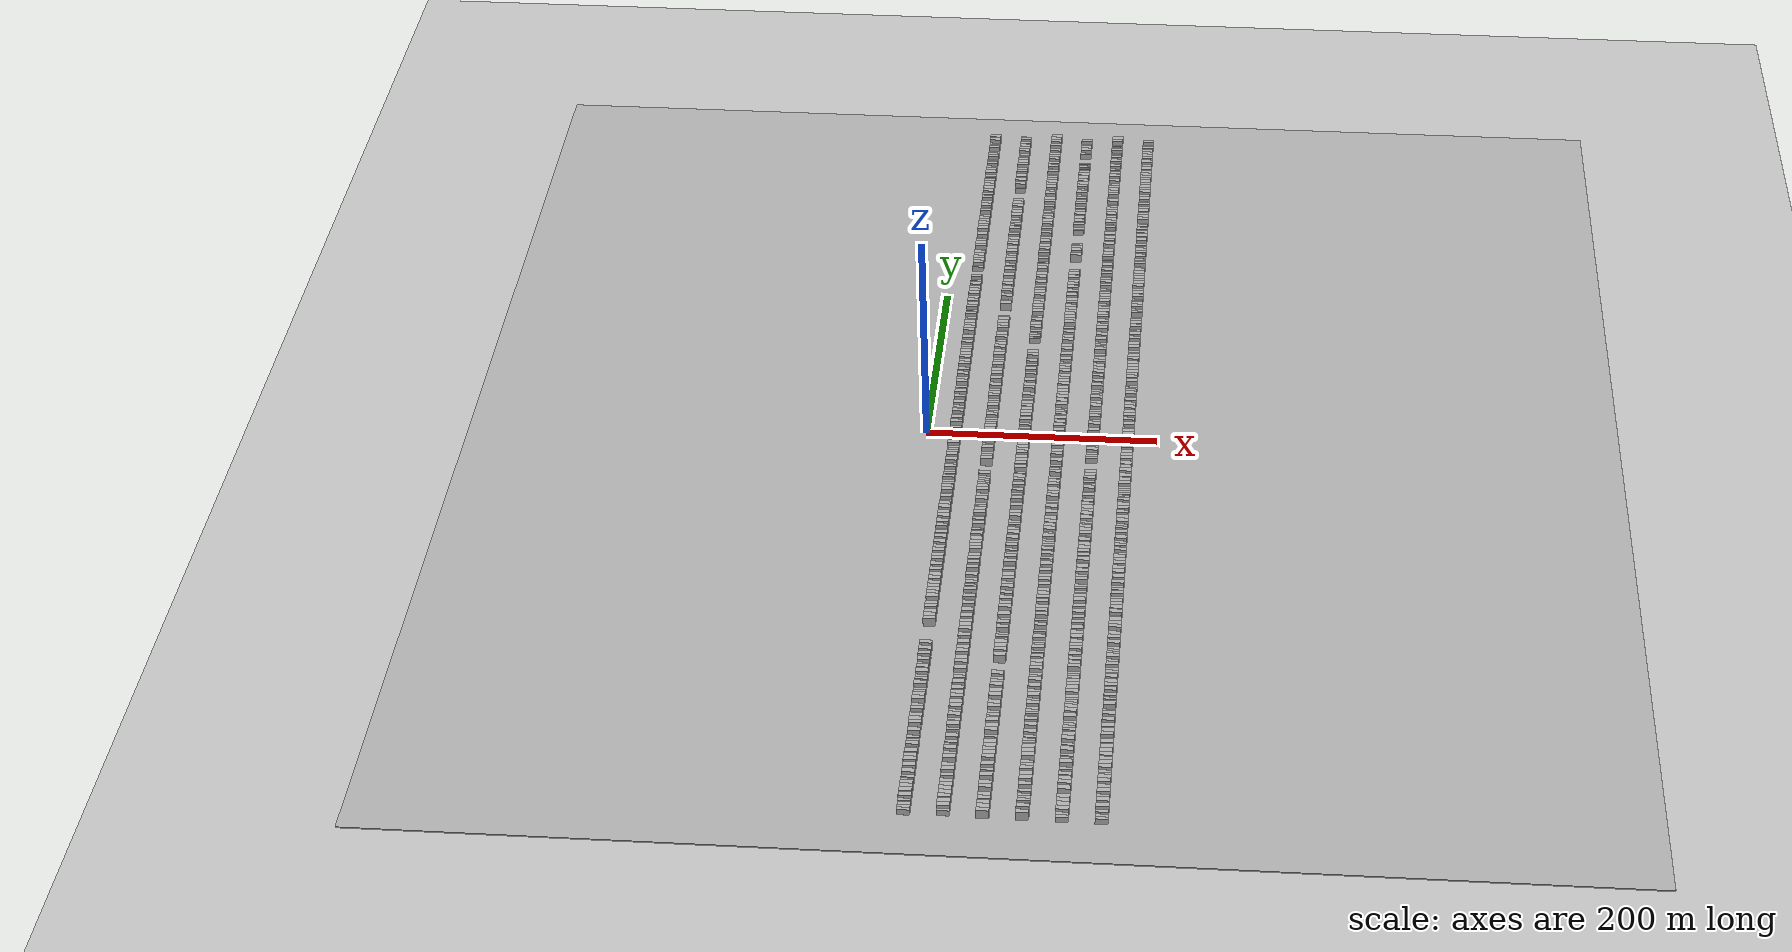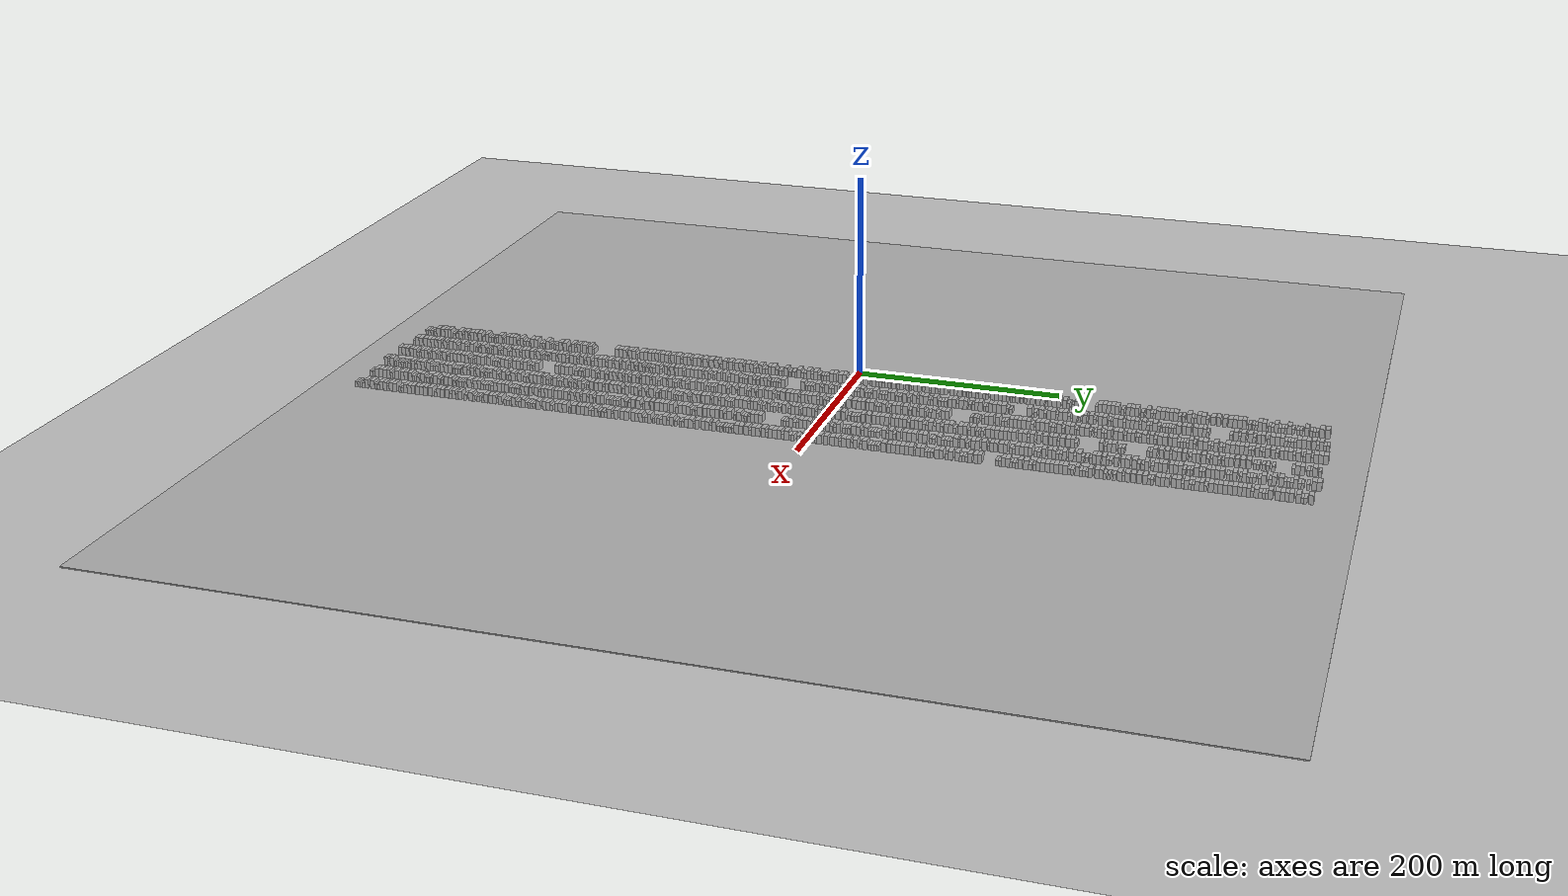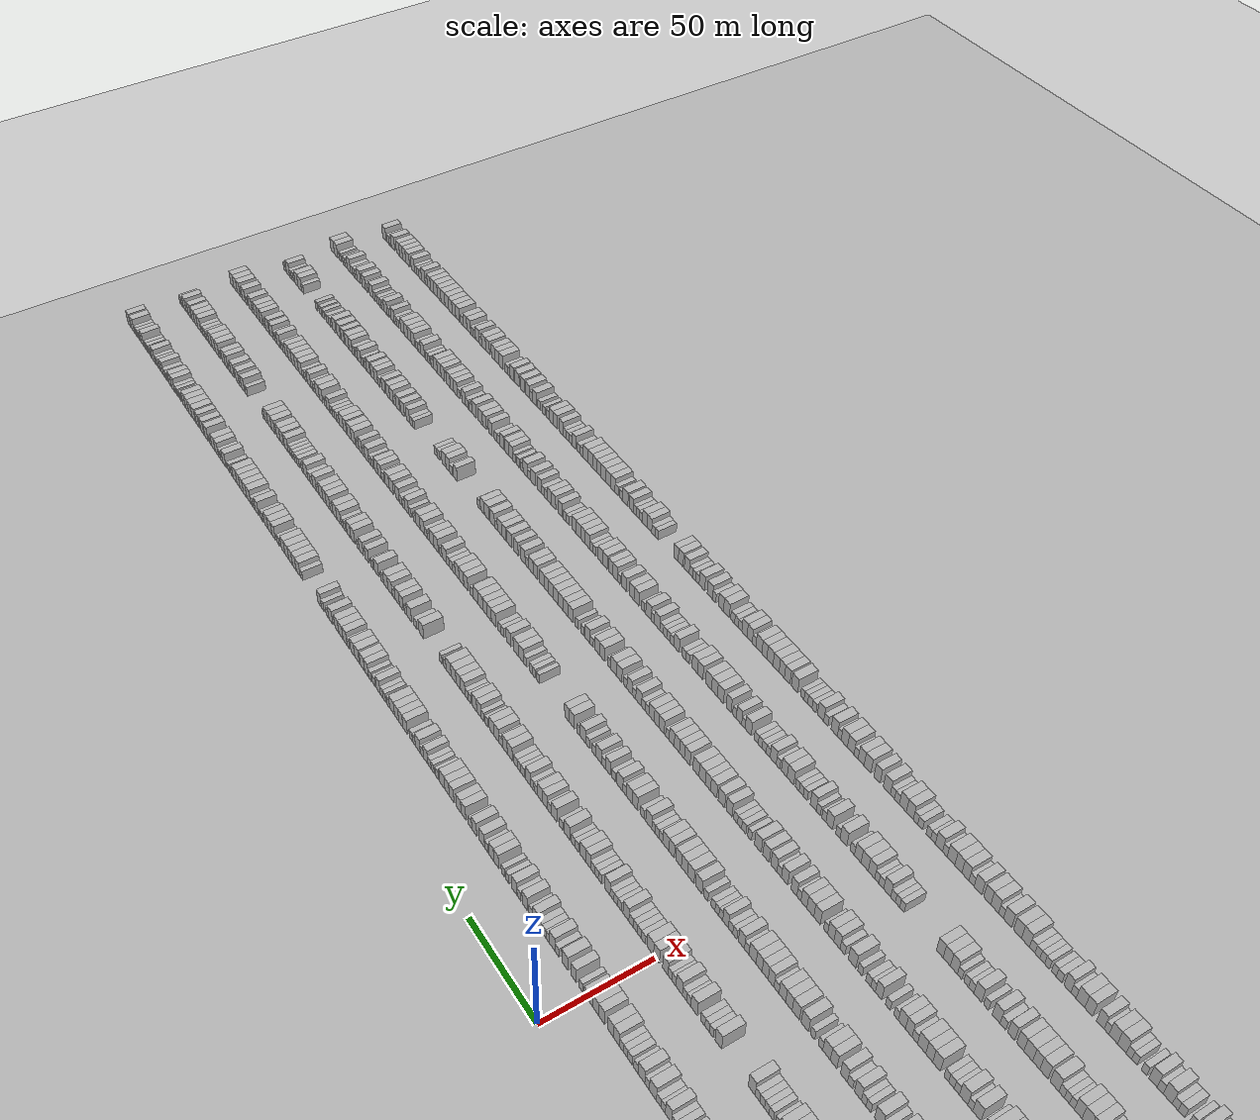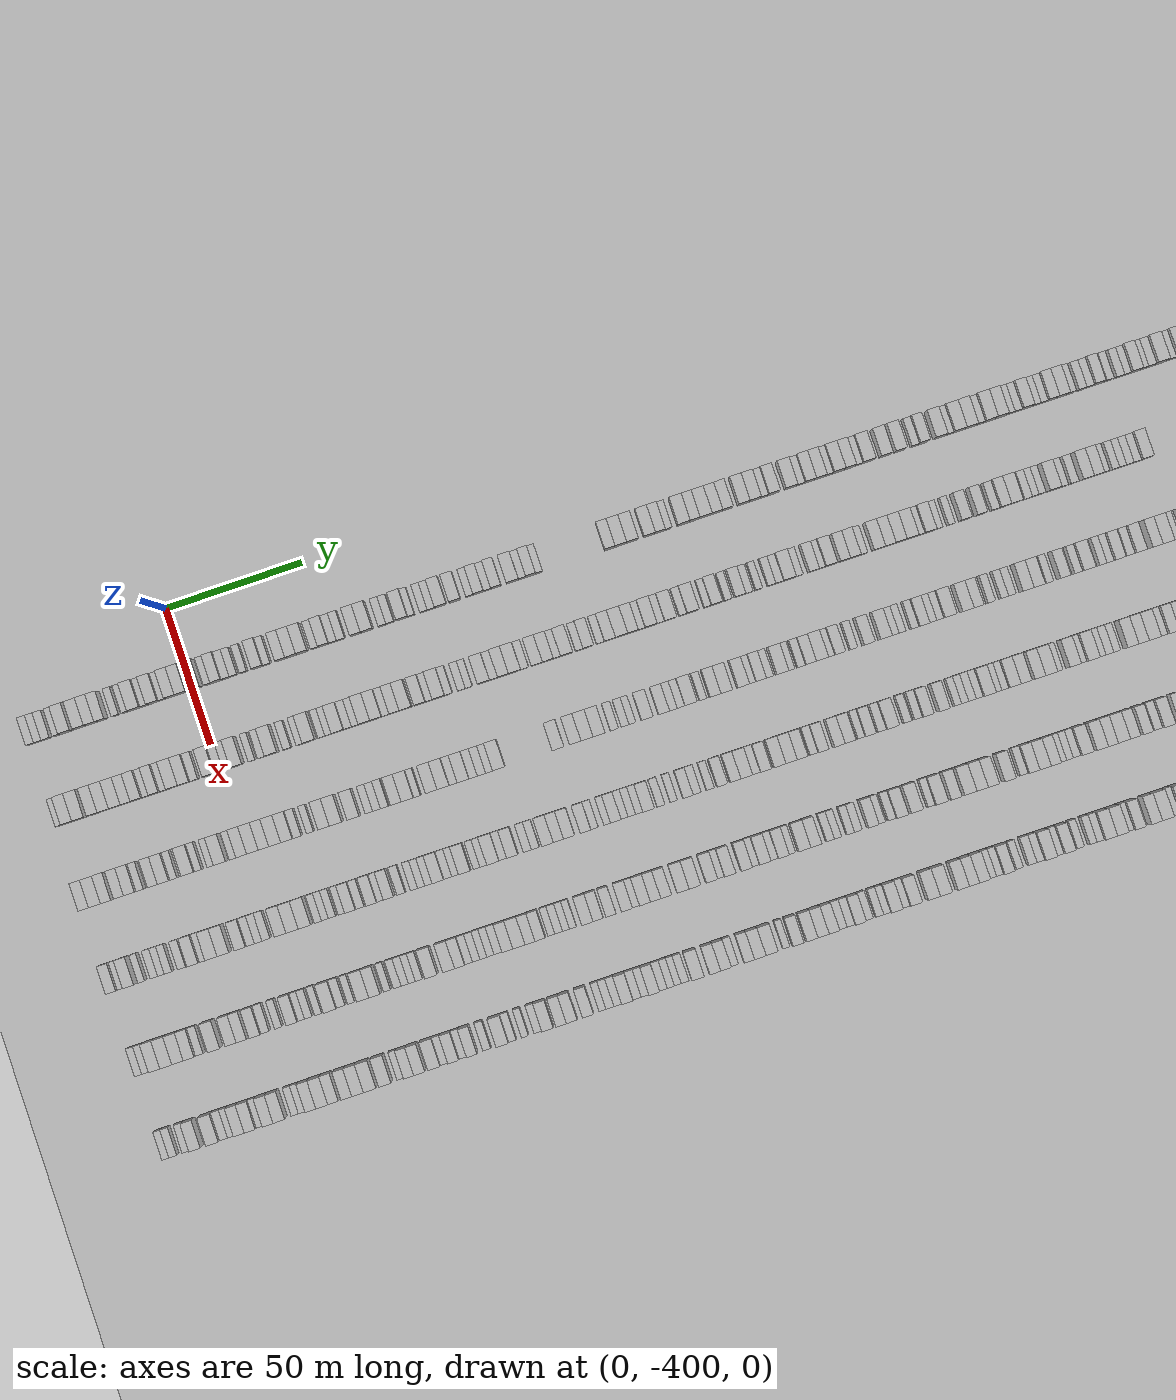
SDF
<sdf version="1.6">
 <world name="default">
  <scene>
   <sky><clouds><speed>12</speed></clouds></sky>
   <ambient>0.4 0.4 0.4 1</ambient>
   <background>0.7 0.7 0.7 1</background>
   <shadows>1</shadows>
  </scene>
  <gravity>0 0 -9.8066</gravity>
  <magnetic_field>6e-06 2.3e-05 -4.2e-05</magnetic_field>
  <physics default="0" name="default_physics" type="ode">
   <ode>
    <solver>
     <type>quick</type>
     <iters>10</iters>
     <sor>1.0</sor>
     <use_dynamic_moi_rescaling>0</use_dynamic_moi_rescaling>
    </solver>
    <constraints>
     <cfm>0</cfm>
     <erp>0.2</erp>
     <contact_max_correcting_vel>100</contact_max_correcting_vel>
     <contact_surface_layer>0.001</contact_surface_layer>
    </constraints>
   </ode>
   <max_step_size>0.004</max_step_size>
   <real_time_factor>1</real_time_factor>
   <real_time_update_rate>250</real_time_update_rate>
  </physics>
  <light name="sun" type="directional">
   <pose>0 0 10 0 0 0</pose>
   <diffuse>0.8 0.8 0.8 1</diffuse>
   <specular>0.2 0.2 0.2 1</specular>
   <attenuation>
    <range>1000</range>
    <constant>0.9</constant>
    <linear>0.01</linear>
    <quadratic>0.001</quadratic>
   </attenuation>
   <direction>-0.5 0.1 -0.9</direction>
  </light>
  <include><name>ground_plane_1</name><uri>model://HANNAS_ground_plane</uri></include>
  <include>
   <name>ground_plane_2</name>
   <uri>model://HANNAS_ground_plane</uri>
   <pose>100 0 0  0 0 0</pose>
  </include>
  <model name="building_1">
   <static>1</static>
   <pose>25.0000 -458.5501 0 0.000000 0.000000 0.000000</pose>
   <link name="link">
    <pose>0 0 3.00 0 0 0</pose>
    <collision name="collision"><geometry><box><size>10.0000 2.8998 6.0000</size></box></geometry></collision>
    <visual name="visual">
     <cast_shadows>0</cast_shadows>
     <geometry><box><size>10.0000 2.8998 6.0000</size></box></geometry>
     <material>
      <script>
       <uri>model://HANNAS_wall/materials/scripts</uri>
       <uri>model://HANNAS_wall/materials/textures</uri>
       <name>vrc/HANNAS_wall</name>
      </script>
     </material>
    </visual>
   </link>
  </model>
  <model name="building_2">
   <static>1</static>
   <pose>25.0000 -455.7157 0 0.000000 0.000000 0.000000</pose>
   <link name="link">
    <pose>0 0 3.00 0 0 0</pose>
    <collision name="collision"><geometry><box><size>10.0000 2.7691 6.0000</size></box></geometry></collision>
    <visual name="visual">
     <cast_shadows>0</cast_shadows>
     <geometry><box><size>10.0000 2.7691 6.0000</size></box></geometry>
     <material>
      <script>
       <uri>model://HANNAS_wall/materials/scripts</uri>
       <uri>model://HANNAS_wall/materials/textures</uri>
       <name>vrc/HANNAS_wall</name>
      </script>
     </material>
    </visual>
   </link>
  </model>
  <model name="building_3">
   <static>1</static>
   <pose>25.0000 -452.8345 0 0.000000 0.000000 0.000000</pose>
   <link name="link">
    <pose>0 0 3.00 0 0 0</pose>
    <collision name="collision"><geometry><box><size>10.0000 2.9934 6.0000</size></box></geometry></collision>
    <visual name="visual">
     <cast_shadows>0</cast_shadows>
     <geometry><box><size>10.0000 2.9934 6.0000</size></box></geometry>
     <material>
      <script>
       <uri>model://HANNAS_wall/materials/scripts</uri>
       <uri>model://HANNAS_wall/materials/textures</uri>
       <name>vrc/HANNAS_wall</name>
      </script>
     </material>
    </visual>
   </link>
  </model>
  <model name="building_4">
   <static>1</static>
   <pose>25.0000 -448.9767 0 0.000000 0.000000 0.000000</pose>
   <link name="link">
    <pose>0 0 3.00 0 0 0</pose>
    <collision name="collision"><geometry><box><size>10.0000 2.7221 6.0000</size></box></geometry></collision>
    <visual name="visual">
     <cast_shadows>0</cast_shadows>
     <geometry><box><size>10.0000 2.7221 6.0000</size></box></geometry>
     <material>
      <script>
       <uri>model://HANNAS_wall/materials/scripts</uri>
       <uri>model://HANNAS_wall/materials/textures</uri>
       <name>vrc/HANNAS_wall</name>
      </script>
     </material>
    </visual>
   </link>
  </model>
  <model name="building_5">
   <static>1</static>
   <pose>25.0000 -445.5205 0 0.000000 0.000000 0.000000</pose>
   <link name="link">
    <pose>0 0 4.50 0 0 0</pose>
    <collision name="collision"><geometry><box><size>10.0000 4.1904 9.0000</size></box></geometry></collision>
    <visual name="visual">
     <cast_shadows>0</cast_shadows>
     <geometry><box><size>10.0000 4.1904 9.0000</size></box></geometry>
     <material>
      <script>
       <uri>model://HANNAS_wall/materials/scripts</uri>
       <uri>model://HANNAS_wall/materials/textures</uri>
       <name>vrc/HANNAS_wall</name>
      </script>
     </material>
    </visual>
   </link>
  </model>
  <model name="building_6">
   <static>1</static>
   <pose>25.0000 -440.3815 0 0.000000 0.000000 0.000000</pose>
   <link name="link">
    <pose>0 0 4.50 0 0 0</pose>
    <collision name="collision"><geometry><box><size>10.0000 4.0876 9.0000</size></box></geometry></collision>
    <visual name="visual">
     <cast_shadows>0</cast_shadows>
     <geometry><box><size>10.0000 4.0876 9.0000</size></box></geometry>
     <material>
      <script>
       <uri>model://HANNAS_wall/materials/scripts</uri>
       <uri>model://HANNAS_wall/materials/textures</uri>
       <name>vrc/HANNAS_wall</name>
      </script>
     </material>
    </visual>
   </link>
  </model>
  <model name="building_7">
   <static>1</static>
   <pose>25.0000 -436.4163 0 0.000000 0.000000 0.000000</pose>
   <link name="link">
    <pose>0 0 4.50 0 0 0</pose>
    <collision name="collision"><geometry><box><size>10.0000 3.8426 9.0000</size></box></geometry></collision>
    <visual name="visual">
     <cast_shadows>0</cast_shadows>
     <geometry><box><size>10.0000 3.8426 9.0000</size></box></geometry>
     <material>
      <script>
       <uri>model://HANNAS_wall/materials/scripts</uri>
       <uri>model://HANNAS_wall/materials/textures</uri>
       <name>vrc/HANNAS_wall</name>
      </script>
     </material>
    </visual>
   </link>
  </model>
  <model name="building_8">
   <static>1</static>
   <pose>25.0000 -432.6935 0 0.000000 0.000000 0.000000</pose>
   <link name="link">
    <pose>0 0 4.50 0 0 0</pose>
    <collision name="collision"><geometry><box><size>10.0000 3.6031 9.0000</size></box></geometry></collision>
    <visual name="visual">
     <cast_shadows>0</cast_shadows>
     <geometry><box><size>10.0000 3.6031 9.0000</size></box></geometry>
     <material>
      <script>
       <uri>model://HANNAS_wall/materials/scripts</uri>
       <uri>model://HANNAS_wall/materials/textures</uri>
       <name>vrc/HANNAS_wall</name>
      </script>
     </material>
    </visual>
   </link>
  </model>
  <model name="building_9">
   <static>1</static>
   <pose>25.0000 -427.5836 0 0.000000 0.000000 0.000000</pose>
   <link name="link">
    <pose>0 0 3.00 0 0 0</pose>
    <collision name="collision"><geometry><box><size>10.0000 2.6165 6.0000</size></box></geometry></collision>
    <visual name="visual">
     <cast_shadows>0</cast_shadows>
     <geometry><box><size>10.0000 2.6165 6.0000</size></box></geometry>
     <material>
      <script>
       <uri>model://HANNAS_wall/materials/scripts</uri>
       <uri>model://HANNAS_wall/materials/textures</uri>
       <name>vrc/HANNAS_wall</name>
      </script>
     </material>
    </visual>
   </link>
  </model>
  <model name="building_10">
   <static>1</static>
   <pose>25.0000 -423.9953 0 0.000000 0.000000 0.000000</pose>
   <link name="link">
    <pose>0 0 3.00 0 0 0</pose>
    <collision name="collision"><geometry><box><size>10.0000 2.5602 6.0000</size></box></geometry></collision>
    <visual name="visual">
     <cast_shadows>0</cast_shadows>
     <geometry><box><size>10.0000 2.5602 6.0000</size></box></geometry>
     <material>
      <script>
       <uri>model://HANNAS_wall/materials/scripts</uri>
       <uri>model://HANNAS_wall/materials/textures</uri>
       <name>vrc/HANNAS_wall</name>
      </script>
     </material>
    </visual>
   </link>
  </model>
  <model name="building_11">
   <static>1</static>
   <pose>25.0000 -420.5401 0 0.000000 0.000000 0.000000</pose>
   <link name="link">
    <pose>0 0 4.50 0 0 0</pose>
    <collision name="collision"><geometry><box><size>10.0000 4.3502 9.0000</size></box></geometry></collision>
    <visual name="visual">
     <cast_shadows>0</cast_shadows>
     <geometry><box><size>10.0000 4.3502 9.0000</size></box></geometry>
     <material>
      <script>
       <uri>model://HANNAS_wall/materials/scripts</uri>
       <uri>model://HANNAS_wall/materials/textures</uri>
       <name>vrc/HANNAS_wall</name>
      </script>
     </material>
    </visual>
   </link>
  </model>
  <model name="building_12">
   <static>1</static>
   <pose>25.0000 -417.1077 0 0.000000 0.000000 0.000000</pose>
   <link name="link">
    <pose>0 0 3.00 0 0 0</pose>
    <collision name="collision"><geometry><box><size>10.0000 2.5145 6.0000</size></box></geometry></collision>
    <visual name="visual">
     <cast_shadows>0</cast_shadows>
     <geometry><box><size>10.0000 2.5145 6.0000</size></box></geometry>
     <material>
      <script>
       <uri>model://HANNAS_wall/materials/scripts</uri>
       <uri>model://HANNAS_wall/materials/textures</uri>
       <name>vrc/HANNAS_wall</name>
      </script>
     </material>
    </visual>
   </link>
  </model>
  <model name="building_13">
   <static>1</static>
   <pose>25.0000 -413.8038 0 0.000000 0.000000 0.000000</pose>
   <link name="link">
    <pose>0 0 4.50 0 0 0</pose>
    <collision name="collision"><geometry><box><size>10.0000 4.0934 9.0000</size></box></geometry></collision>
    <visual name="visual">
     <cast_shadows>0</cast_shadows>
     <geometry><box><size>10.0000 4.0934 9.0000</size></box></geometry>
     <material>
      <script>
       <uri>model://HANNAS_wall/materials/scripts</uri>
       <uri>model://HANNAS_wall/materials/textures</uri>
       <name>vrc/HANNAS_wall</name>
      </script>
     </material>
    </visual>
   </link>
  </model>
  <model name="building_14">
   <static>1</static>
   <pose>25.0000 -410.5262 0 0.000000 0.000000 0.000000</pose>
   <link name="link">
    <pose>0 0 3.00 0 0 0</pose>
    <collision name="collision"><geometry><box><size>10.0000 2.4617 6.0000</size></box></geometry></collision>
    <visual name="visual">
     <cast_shadows>0</cast_shadows>
     <geometry><box><size>10.0000 2.4617 6.0000</size></box></geometry>
     <material>
      <script>
       <uri>model://HANNAS_wall/materials/scripts</uri>
       <uri>model://HANNAS_wall/materials/textures</uri>
       <name>vrc/HANNAS_wall</name>
      </script>
     </material>
    </visual>
   </link>
  </model>
  <model name="building_15">
   <static>1</static>
   <pose>25.0000 -407.3554 0 0.000000 0.000000 0.000000</pose>
   <link name="link">
    <pose>0 0 4.50 0 0 0</pose>
    <collision name="collision"><geometry><box><size>10.0000 3.8799 9.0000</size></box></geometry></collision>
    <visual name="visual">
     <cast_shadows>0</cast_shadows>
     <geometry><box><size>10.0000 3.8799 9.0000</size></box></geometry>
     <material>
      <script>
       <uri>model://HANNAS_wall/materials/scripts</uri>
       <uri>model://HANNAS_wall/materials/textures</uri>
       <name>vrc/HANNAS_wall</name>
      </script>
     </material>
    </visual>
   </link>
  </model>
  <model name="building_16">
   <static>1</static>
   <pose>25.0000 -403.4733 0 0.000000 0.000000 0.000000</pose>
   <link name="link">
    <pose>0 0 4.50 0 0 0</pose>
    <collision name="collision"><geometry><box><size>10.0000 3.8842 9.0000</size></box></geometry></collision>
    <visual name="visual">
     <cast_shadows>0</cast_shadows>
     <geometry><box><size>10.0000 3.8842 9.0000</size></box></geometry>
     <material>
      <script>
       <uri>model://HANNAS_wall/materials/scripts</uri>
       <uri>model://HANNAS_wall/materials/textures</uri>
       <name>vrc/HANNAS_wall</name>
      </script>
     </material>
    </visual>
   </link>
  </model>
  <model name="building_17">
   <static>1</static>
   <pose>25.0000 -398.4117 0 0.000000 0.000000 0.000000</pose>
   <link name="link">
    <pose>0 0 4.50 0 0 0</pose>
    <collision name="collision"><geometry><box><size>10.0000 4.2392 9.0000</size></box></geometry></collision>
    <visual name="visual">
     <cast_shadows>0</cast_shadows>
     <geometry><box><size>10.0000 4.2392 9.0000</size></box></geometry>
     <material>
      <script>
       <uri>model://HANNAS_wall/materials/scripts</uri>
       <uri>model://HANNAS_wall/materials/textures</uri>
       <name>vrc/HANNAS_wall</name>
      </script>
     </material>
    </visual>
   </link>
  </model>
  <model name="building_18">
   <static>1</static>
   <pose>25.0000 -393.9038 0 0.000000 0.000000 0.000000</pose>
   <link name="link">
    <pose>0 0 3.00 0 0 0</pose>
    <collision name="collision"><geometry><box><size>10.0000 2.7766 6.0000</size></box></geometry></collision>
    <visual name="visual">
     <cast_shadows>0</cast_shadows>
     <geometry><box><size>10.0000 2.7766 6.0000</size></box></geometry>
     <material>
      <script>
       <uri>model://HANNAS_wall/materials/scripts</uri>
       <uri>model://HANNAS_wall/materials/textures</uri>
       <name>vrc/HANNAS_wall</name>
      </script>
     </material>
    </visual>
   </link>
  </model>
  <model name="building_19">
   <static>1</static>
   <pose>25.0000 -390.6571 0 0.000000 0.000000 0.000000</pose>
   <link name="link">
    <pose>0 0 4.50 0 0 0</pose>
    <collision name="collision"><geometry><box><size>10.0000 3.7168 9.0000</size></box></geometry></collision>
    <visual name="visual">
     <cast_shadows>0</cast_shadows>
     <geometry><box><size>10.0000 3.7168 9.0000</size></box></geometry>
     <material>
      <script>
       <uri>model://HANNAS_wall/materials/scripts</uri>
       <uri>model://HANNAS_wall/materials/textures</uri>
       <name>vrc/HANNAS_wall</name>
      </script>
     </material>
    </visual>
   </link>
  </model>
  <model name="building_20">
   <static>1</static>
   <pose>25.0000 -387.3638 0 0.000000 0.000000 0.000000</pose>
   <link name="link">
    <pose>0 0 3.00 0 0 0</pose>
    <collision name="collision"><geometry><box><size>10.0000 2.8698 6.0000</size></box></geometry></collision>
    <visual name="visual">
     <cast_shadows>0</cast_shadows>
     <geometry><box><size>10.0000 2.8698 6.0000</size></box></geometry>
     <material>
      <script>
       <uri>model://HANNAS_wall/materials/scripts</uri>
       <uri>model://HANNAS_wall/materials/textures</uri>
       <name>vrc/HANNAS_wall</name>
      </script>
     </material>
    </visual>
   </link>
  </model>
  <model name="building_21">
   <static>1</static>
   <pose>25.0000 -384.5546 0 0.000000 0.000000 0.000000</pose>
   <link name="link">
    <pose>0 0 3.00 0 0 0</pose>
    <collision name="collision"><geometry><box><size>10.0000 2.7485 6.0000</size></box></geometry></collision>
    <visual name="visual">
     <cast_shadows>0</cast_shadows>
     <geometry><box><size>10.0000 2.7485 6.0000</size></box></geometry>
     <material>
      <script>
       <uri>model://HANNAS_wall/materials/scripts</uri>
       <uri>model://HANNAS_wall/materials/textures</uri>
       <name>vrc/HANNAS_wall</name>
      </script>
     </material>
    </visual>
   </link>
  </model>
  <model name="building_22">
   <static>1</static>
   <pose>25.0000 -380.9059 0 0.000000 0.000000 0.000000</pose>
   <link name="link">
    <pose>0 0 3.00 0 0 0</pose>
    <collision name="collision"><geometry><box><size>10.0000 2.5488 6.0000</size></box></geometry></collision>
    <visual name="visual">
     <cast_shadows>0</cast_shadows>
     <geometry><box><size>10.0000 2.5488 6.0000</size></box></geometry>
     <material>
      <script>
       <uri>model://HANNAS_wall/materials/scripts</uri>
       <uri>model://HANNAS_wall/materials/textures</uri>
       <name>vrc/HANNAS_wall</name>
      </script>
     </material>
    </visual>
   </link>
  </model>
  <model name="building_23">
   <static>1</static>
   <pose>25.0000 -375.6319 0 0.000000 0.000000 0.000000</pose>
   <link name="link">
    <pose>0 0 4.50 0 0 0</pose>
    <collision name="collision"><geometry><box><size>10.0000 3.9991 9.0000</size></box></geometry></collision>
    <visual name="visual">
     <cast_shadows>0</cast_shadows>
     <geometry><box><size>10.0000 3.9991 9.0000</size></box></geometry>
     <material>
      <script>
       <uri>model://HANNAS_wall/materials/scripts</uri>
       <uri>model://HANNAS_wall/materials/textures</uri>
       <name>vrc/HANNAS_wall</name>
      </script>
     </material>
    </visual>
   </link>
  </model>
  <model name="building_24">
   <static>1</static>
   <pose>25.0000 -372.3390 0 0.000000 0.000000 0.000000</pose>
   <link name="link">
    <pose>0 0 3.00 0 0 0</pose>
    <collision name="collision"><geometry><box><size>10.0000 2.5869 6.0000</size></box></geometry></collision>
    <visual name="visual">
     <cast_shadows>0</cast_shadows>
     <geometry><box><size>10.0000 2.5869 6.0000</size></box></geometry>
     <material>
      <script>
       <uri>model://HANNAS_wall/materials/scripts</uri>
       <uri>model://HANNAS_wall/materials/textures</uri>
       <name>vrc/HANNAS_wall</name>
      </script>
     </material>
    </visual>
   </link>
  </model>
  <model name="building_25">
   <static>1</static>
   <pose>25.0000 -367.1583 0 0.000000 0.000000 0.000000</pose>
   <link name="link">
    <pose>0 0 4.50 0 0 0</pose>
    <collision name="collision"><geometry><box><size>10.0000 3.7744 9.0000</size></box></geometry></collision>
    <visual name="visual">
     <cast_shadows>0</cast_shadows>
     <geometry><box><size>10.0000 3.7744 9.0000</size></box></geometry>
     <material>
      <script>
       <uri>model://HANNAS_wall/materials/scripts</uri>
       <uri>model://HANNAS_wall/materials/textures</uri>
       <name>vrc/HANNAS_wall</name>
      </script>
     </material>
    </visual>
   </link>
  </model>
  <model name="building_26">
   <static>1</static>
   <pose>25.0000 -363.3292 0 0.000000 0.000000 0.000000</pose>
   <link name="link">
    <pose>0 0 4.50 0 0 0</pose>
    <collision name="collision"><geometry><box><size>10.0000 3.8838 9.0000</size></box></geometry></collision>
    <visual name="visual">
     <cast_shadows>0</cast_shadows>
     <geometry><box><size>10.0000 3.8838 9.0000</size></box></geometry>
     <material>
      <script>
       <uri>model://HANNAS_wall/materials/scripts</uri>
       <uri>model://HANNAS_wall/materials/textures</uri>
       <name>vrc/HANNAS_wall</name>
      </script>
     </material>
    </visual>
   </link>
  </model>
  <model name="building_27">
   <static>1</static>
   <pose>25.0000 -359.3605 0 0.000000 0.000000 0.000000</pose>
   <link name="link">
    <pose>0 0 4.50 0 0 0</pose>
    <collision name="collision"><geometry><box><size>10.0000 4.0535 9.0000</size></box></geometry></collision>
    <visual name="visual">
     <cast_shadows>0</cast_shadows>
     <geometry><box><size>10.0000 4.0535 9.0000</size></box></geometry>
     <material>
      <script>
       <uri>model://HANNAS_wall/materials/scripts</uri>
       <uri>model://HANNAS_wall/materials/textures</uri>
       <name>vrc/HANNAS_wall</name>
      </script>
     </material>
    </visual>
   </link>
  </model>
  <model name="building_28">
   <static>1</static>
   <pose>25.0000 -354.9109 0 0.000000 0.000000 0.000000</pose>
   <link name="link">
    <pose>0 0 3.00 0 0 0</pose>
    <collision name="collision"><geometry><box><size>10.0000 2.8457 6.0000</size></box></geometry></collision>
    <visual name="visual">
     <cast_shadows>0</cast_shadows>
     <geometry><box><size>10.0000 2.8457 6.0000</size></box></geometry>
     <material>
      <script>
       <uri>model://HANNAS_wall/materials/scripts</uri>
       <uri>model://HANNAS_wall/materials/textures</uri>
       <name>vrc/HANNAS_wall</name>
      </script>
     </material>
    </visual>
   </link>
  </model>
  <model name="building_29">
   <static>1</static>
   <pose>25.0000 -351.5719 0 0.000000 0.000000 0.000000</pose>
   <link name="link">
    <pose>0 0 4.50 0 0 0</pose>
    <collision name="collision"><geometry><box><size>10.0000 3.8323 9.0000</size></box></geometry></collision>
    <visual name="visual">
     <cast_shadows>0</cast_shadows>
     <geometry><box><size>10.0000 3.8323 9.0000</size></box></geometry>
     <material>
      <script>
       <uri>model://HANNAS_wall/materials/scripts</uri>
       <uri>model://HANNAS_wall/materials/textures</uri>
       <name>vrc/HANNAS_wall</name>
      </script>
     </material>
    </visual>
   </link>
  </model>
  <model name="building_30">
   <static>1</static>
   <pose>25.0000 -348.2336 0 0.000000 0.000000 0.000000</pose>
   <link name="link">
    <pose>0 0 3.00 0 0 0</pose>
    <collision name="collision"><geometry><box><size>10.0000 2.8442 6.0000</size></box></geometry></collision>
    <visual name="visual">
     <cast_shadows>0</cast_shadows>
     <geometry><box><size>10.0000 2.8442 6.0000</size></box></geometry>
     <material>
      <script>
       <uri>model://HANNAS_wall/materials/scripts</uri>
       <uri>model://HANNAS_wall/materials/textures</uri>
       <name>vrc/HANNAS_wall</name>
      </script>
     </material>
    </visual>
   </link>
  </model>
  <model name="building_31">
   <static>1</static>
   <pose>25.0000 -345.3288 0 0.000000 0.000000 0.000000</pose>
   <link name="link">
    <pose>0 0 3.00 0 0 0</pose>
    <collision name="collision"><geometry><box><size>10.0000 2.9655 6.0000</size></box></geometry></collision>
    <visual name="visual">
     <cast_shadows>0</cast_shadows>
     <geometry><box><size>10.0000 2.9655 6.0000</size></box></geometry>
     <material>
      <script>
       <uri>model://HANNAS_wall/materials/scripts</uri>
       <uri>model://HANNAS_wall/materials/textures</uri>
       <name>vrc/HANNAS_wall</name>
      </script>
     </material>
    </visual>
   </link>
  </model>
  <model name="building_32">
   <static>1</static>
   <pose>25.0000 -339.8580 0 0.000000 0.000000 0.000000</pose>
   <link name="link">
    <pose>0 0 4.50 0 0 0</pose>
    <collision name="collision"><geometry><box><size>10.0000 3.9760 9.0000</size></box></geometry></collision>
    <visual name="visual">
     <cast_shadows>0</cast_shadows>
     <geometry><box><size>10.0000 3.9760 9.0000</size></box></geometry>
     <material>
      <script>
       <uri>model://HANNAS_wall/materials/scripts</uri>
       <uri>model://HANNAS_wall/materials/textures</uri>
       <name>vrc/HANNAS_wall</name>
      </script>
     </material>
    </visual>
   </link>
  </model>
  <model name="building_33">
   <static>1</static>
   <pose>25.0000 -335.7760 0 0.000000 0.000000 0.000000</pose>
   <link name="link">
    <pose>0 0 4.50 0 0 0</pose>
    <collision name="collision"><geometry><box><size>10.0000 4.1880 9.0000</size></box></geometry></collision>
    <visual name="visual">
     <cast_shadows>0</cast_shadows>
     <geometry><box><size>10.0000 4.1880 9.0000</size></box></geometry>
     <material>
      <script>
       <uri>model://HANNAS_wall/materials/scripts</uri>
       <uri>model://HANNAS_wall/materials/textures</uri>
       <name>vrc/HANNAS_wall</name>
      </script>
     </material>
    </visual>
   </link>
  </model>
  <model name="building_34">
   <static>1</static>
   <pose>25.0000 -330.2479 0 0.000000 0.000000 0.000000</pose>
   <link name="link">
    <pose>0 0 3.00 0 0 0</pose>
    <collision name="collision"><geometry><box><size>10.0000 2.8681 6.0000</size></box></geometry></collision>
    <visual name="visual">
     <cast_shadows>0</cast_shadows>
     <geometry><box><size>10.0000 2.8681 6.0000</size></box></geometry>
     <material>
      <script>
       <uri>model://HANNAS_wall/materials/scripts</uri>
       <uri>model://HANNAS_wall/materials/textures</uri>
       <name>vrc/HANNAS_wall</name>
      </script>
     </material>
    </visual>
   </link>
  </model>
  <model name="building_35">
   <static>1</static>
   <pose>25.0000 -327.3983 0 0.000000 0.000000 0.000000</pose>
   <link name="link">
    <pose>0 0 3.00 0 0 0</pose>
    <collision name="collision"><geometry><box><size>10.0000 2.8311 6.0000</size></box></geometry></collision>
    <visual name="visual">
     <cast_shadows>0</cast_shadows>
     <geometry><box><size>10.0000 2.8311 6.0000</size></box></geometry>
     <material>
      <script>
       <uri>model://HANNAS_wall/materials/scripts</uri>
       <uri>model://HANNAS_wall/materials/textures</uri>
       <name>vrc/HANNAS_wall</name>
      </script>
     </material>
    </visual>
   </link>
  </model>
  <model name="building_36">
   <static>1</static>
   <pose>25.0000 -322.9147 0 0.000000 0.000000 0.000000</pose>
   <link name="link">
    <pose>0 0 4.50 0 0 0</pose>
    <collision name="collision"><geometry><box><size>10.0000 4.1361 9.0000</size></box></geometry></collision>
    <visual name="visual">
     <cast_shadows>0</cast_shadows>
     <geometry><box><size>10.0000 4.1361 9.0000</size></box></geometry>
     <material>
      <script>
       <uri>model://HANNAS_wall/materials/scripts</uri>
       <uri>model://HANNAS_wall/materials/textures</uri>
       <name>vrc/HANNAS_wall</name>
      </script>
     </material>
    </visual>
   </link>
  </model>
  <model name="building_37">
   <static>1</static>
   <pose>25.0000 -319.6407 0 0.000000 0.000000 0.000000</pose>
   <link name="link">
    <pose>0 0 3.00 0 0 0</pose>
    <collision name="collision"><geometry><box><size>10.0000 2.4119 6.0000</size></box></geometry></collision>
    <visual name="visual">
     <cast_shadows>0</cast_shadows>
     <geometry><box><size>10.0000 2.4119 6.0000</size></box></geometry>
     <material>
      <script>
       <uri>model://HANNAS_wall/materials/scripts</uri>
       <uri>model://HANNAS_wall/materials/textures</uri>
       <name>vrc/HANNAS_wall</name>
      </script>
     </material>
    </visual>
   </link>
  </model>
  <model name="building_38">
   <static>1</static>
   <pose>25.0000 -315.0857 0 0.000000 0.000000 0.000000</pose>
   <link name="link">
    <pose>0 0 3.00 0 0 0</pose>
    <collision name="collision"><geometry><box><size>10.0000 2.6982 6.0000</size></box></geometry></collision>
    <visual name="visual">
     <cast_shadows>0</cast_shadows>
     <geometry><box><size>10.0000 2.6982 6.0000</size></box></geometry>
     <material>
      <script>
       <uri>model://HANNAS_wall/materials/scripts</uri>
       <uri>model://HANNAS_wall/materials/textures</uri>
       <name>vrc/HANNAS_wall</name>
      </script>
     </material>
    </visual>
   </link>
  </model>
  <model name="building_39">
   <static>1</static>
   <pose>25.0000 -312.3672 0 0.000000 0.000000 0.000000</pose>
   <link name="link">
    <pose>0 0 3.00 0 0 0</pose>
    <collision name="collision"><geometry><box><size>10.0000 2.7387 6.0000</size></box></geometry></collision>
    <visual name="visual">
     <cast_shadows>0</cast_shadows>
     <geometry><box><size>10.0000 2.7387 6.0000</size></box></geometry>
     <material>
      <script>
       <uri>model://HANNAS_wall/materials/scripts</uri>
       <uri>model://HANNAS_wall/materials/textures</uri>
       <name>vrc/HANNAS_wall</name>
      </script>
     </material>
    </visual>
   </link>
  </model>
  <model name="building_40">
   <static>1</static>
   <pose>25.0000 -308.8838 0 0.000000 0.000000 0.000000</pose>
   <link name="link">
    <pose>0 0 4.50 0 0 0</pose>
    <collision name="collision"><geometry><box><size>10.0000 4.2281 9.0000</size></box></geometry></collision>
    <visual name="visual">
     <cast_shadows>0</cast_shadows>
     <geometry><box><size>10.0000 4.2281 9.0000</size></box></geometry>
     <material>
      <script>
       <uri>model://HANNAS_wall/materials/scripts</uri>
       <uri>model://HANNAS_wall/materials/textures</uri>
       <name>vrc/HANNAS_wall</name>
      </script>
     </material>
    </visual>
   </link>
  </model>
  <model name="building_41">
   <static>1</static>
   <pose>25.0000 -303.7014 0 0.000000 0.000000 0.000000</pose>
   <link name="link">
    <pose>0 0 4.50 0 0 0</pose>
    <collision name="collision"><geometry><box><size>10.0000 4.1366 9.0000</size></box></geometry></collision>
    <visual name="visual">
     <cast_shadows>0</cast_shadows>
     <geometry><box><size>10.0000 4.1366 9.0000</size></box></geometry>
     <material>
      <script>
       <uri>model://HANNAS_wall/materials/scripts</uri>
       <uri>model://HANNAS_wall/materials/textures</uri>
       <name>vrc/HANNAS_wall</name>
      </script>
     </material>
    </visual>
   </link>
  </model>
  <model name="building_42">
   <static>1</static>
   <pose>25.0000 -298.2749 0 0.000000 0.000000 0.000000</pose>
   <link name="link">
    <pose>0 0 3.00 0 0 0</pose>
    <collision name="collision"><geometry><box><size>10.0000 2.7165 6.0000</size></box></geometry></collision>
    <visual name="visual">
     <cast_shadows>0</cast_shadows>
     <geometry><box><size>10.0000 2.7165 6.0000</size></box></geometry>
     <material>
      <script>
       <uri>model://HANNAS_wall/materials/scripts</uri>
       <uri>model://HANNAS_wall/materials/textures</uri>
       <name>vrc/HANNAS_wall</name>
      </script>
     </material>
    </visual>
   </link>
  </model>
  <model name="building_43">
   <static>1</static>
   <pose>25.0000 -295.0676 0 0.000000 0.000000 0.000000</pose>
   <link name="link">
    <pose>0 0 4.50 0 0 0</pose>
    <collision name="collision"><geometry><box><size>10.0000 3.6980 9.0000</size></box></geometry></collision>
    <visual name="visual">
     <cast_shadows>0</cast_shadows>
     <geometry><box><size>10.0000 3.6980 9.0000</size></box></geometry>
     <material>
      <script>
       <uri>model://HANNAS_wall/materials/scripts</uri>
       <uri>model://HANNAS_wall/materials/textures</uri>
       <name>vrc/HANNAS_wall</name>
      </script>
     </material>
    </visual>
   </link>
  </model>
  <model name="building_44">
   <static>1</static>
   <pose>25.0000 -291.8592 0 0.000000 0.000000 0.000000</pose>
   <link name="link">
    <pose>0 0 3.00 0 0 0</pose>
    <collision name="collision"><geometry><box><size>10.0000 2.7188 6.0000</size></box></geometry></collision>
    <visual name="visual">
     <cast_shadows>0</cast_shadows>
     <geometry><box><size>10.0000 2.7188 6.0000</size></box></geometry>
     <material>
      <script>
       <uri>model://HANNAS_wall/materials/scripts</uri>
       <uri>model://HANNAS_wall/materials/textures</uri>
       <name>vrc/HANNAS_wall</name>
      </script>
     </material>
    </visual>
   </link>
  </model>
  <model name="building_45">
   <static>1</static>
   <pose>25.0000 -288.6436 0 0.000000 0.000000 0.000000</pose>
   <link name="link">
    <pose>0 0 4.50 0 0 0</pose>
    <collision name="collision"><geometry><box><size>10.0000 3.7125 9.0000</size></box></geometry></collision>
    <visual name="visual">
     <cast_shadows>0</cast_shadows>
     <geometry><box><size>10.0000 3.7125 9.0000</size></box></geometry>
     <material>
      <script>
       <uri>model://HANNAS_wall/materials/scripts</uri>
       <uri>model://HANNAS_wall/materials/textures</uri>
       <name>vrc/HANNAS_wall</name>
      </script>
     </material>
    </visual>
   </link>
  </model>
  <model name="building_46">
   <static>1</static>
   <pose>25.0000 -282.5983 0 0.000000 0.000000 0.000000</pose>
   <link name="link">
    <pose>0 0 4.50 0 0 0</pose>
    <collision name="collision"><geometry><box><size>10.0000 4.3780 9.0000</size></box></geometry></collision>
    <visual name="visual">
     <cast_shadows>0</cast_shadows>
     <geometry><box><size>10.0000 4.3780 9.0000</size></box></geometry>
     <material>
      <script>
       <uri>model://HANNAS_wall/materials/scripts</uri>
       <uri>model://HANNAS_wall/materials/textures</uri>
       <name>vrc/HANNAS_wall</name>
      </script>
     </material>
    </visual>
   </link>
  </model>
  <model name="building_47">
   <static>1</static>
   <pose>25.0000 -279.0557 0 0.000000 0.000000 0.000000</pose>
   <link name="link">
    <pose>0 0 3.00 0 0 0</pose>
    <collision name="collision"><geometry><box><size>10.0000 2.7072 6.0000</size></box></geometry></collision>
    <visual name="visual">
     <cast_shadows>0</cast_shadows>
     <geometry><box><size>10.0000 2.7072 6.0000</size></box></geometry>
     <material>
      <script>
       <uri>model://HANNAS_wall/materials/scripts</uri>
       <uri>model://HANNAS_wall/materials/textures</uri>
       <name>vrc/HANNAS_wall</name>
      </script>
     </material>
    </visual>
   </link>
  </model>
  <model name="building_48">
   <static>1</static>
   <pose>25.0000 -275.8993 0 0.000000 0.000000 0.000000</pose>
   <link name="link">
    <pose>0 0 4.50 0 0 0</pose>
    <collision name="collision"><geometry><box><size>10.0000 3.6057 9.0000</size></box></geometry></collision>
    <visual name="visual">
     <cast_shadows>0</cast_shadows>
     <geometry><box><size>10.0000 3.6057 9.0000</size></box></geometry>
     <material>
      <script>
       <uri>model://HANNAS_wall/materials/scripts</uri>
       <uri>model://HANNAS_wall/materials/textures</uri>
       <name>vrc/HANNAS_wall</name>
      </script>
     </material>
    </visual>
   </link>
  </model>
  <model name="building_49">
   <static>1</static>
   <pose>25.0000 -272.8682 0 0.000000 0.000000 0.000000</pose>
   <link name="link">
    <pose>0 0 3.00 0 0 0</pose>
    <collision name="collision"><geometry><box><size>10.0000 2.4565 6.0000</size></box></geometry></collision>
    <visual name="visual">
     <cast_shadows>0</cast_shadows>
     <geometry><box><size>10.0000 2.4565 6.0000</size></box></geometry>
     <material>
      <script>
       <uri>model://HANNAS_wall/materials/scripts</uri>
       <uri>model://HANNAS_wall/materials/textures</uri>
       <name>vrc/HANNAS_wall</name>
      </script>
     </material>
    </visual>
   </link>
  </model>
  <model name="building_50">
   <static>1</static>
   <pose>25.0000 -247.0069 0 0.000000 0.000000 0.000000</pose>
   <link name="link">
    <pose>0 0 4.50 0 0 0</pose>
    <collision name="collision"><geometry><box><size>10.0000 3.7554 9.0000</size></box></geometry></collision>
    <visual name="visual">
     <cast_shadows>0</cast_shadows>
     <geometry><box><size>10.0000 3.7554 9.0000</size></box></geometry>
     <material>
      <script>
       <uri>model://HANNAS_wall/materials/scripts</uri>
       <uri>model://HANNAS_wall/materials/textures</uri>
       <name>vrc/HANNAS_wall</name>
      </script>
     </material>
    </visual>
   </link>
  </model>
  <model name="building_51">
   <static>1</static>
   <pose>25.0000 -242.9770 0 0.000000 0.000000 0.000000</pose>
   <link name="link">
    <pose>0 0 4.50 0 0 0</pose>
    <collision name="collision"><geometry><box><size>10.0000 4.3045 9.0000</size></box></geometry></collision>
    <visual name="visual">
     <cast_shadows>0</cast_shadows>
     <geometry><box><size>10.0000 4.3045 9.0000</size></box></geometry>
     <material>
      <script>
       <uri>model://HANNAS_wall/materials/scripts</uri>
       <uri>model://HANNAS_wall/materials/textures</uri>
       <name>vrc/HANNAS_wall</name>
      </script>
     </material>
    </visual>
   </link>
  </model>
  <model name="building_52">
   <static>1</static>
   <pose>25.0000 -238.6975 0 0.000000 0.000000 0.000000</pose>
   <link name="link">
    <pose>0 0 4.50 0 0 0</pose>
    <collision name="collision"><geometry><box><size>10.0000 4.2543 9.0000</size></box></geometry></collision>
    <visual name="visual">
     <cast_shadows>0</cast_shadows>
     <geometry><box><size>10.0000 4.2543 9.0000</size></box></geometry>
     <material>
      <script>
       <uri>model://HANNAS_wall/materials/scripts</uri>
       <uri>model://HANNAS_wall/materials/textures</uri>
       <name>vrc/HANNAS_wall</name>
      </script>
     </material>
    </visual>
   </link>
  </model>
  <model name="building_53">
   <static>1</static>
   <pose>25.0000 -232.4811 0 0.000000 0.000000 0.000000</pose>
   <link name="link">
    <pose>0 0 4.50 0 0 0</pose>
    <collision name="collision"><geometry><box><size>10.0000 4.1786 9.0000</size></box></geometry></collision>
    <visual name="visual">
     <cast_shadows>0</cast_shadows>
     <geometry><box><size>10.0000 4.1786 9.0000</size></box></geometry>
     <material>
      <script>
       <uri>model://HANNAS_wall/materials/scripts</uri>
       <uri>model://HANNAS_wall/materials/textures</uri>
       <name>vrc/HANNAS_wall</name>
      </script>
     </material>
    </visual>
   </link>
  </model>
  <model name="building_54">
   <static>1</static>
   <pose>25.0000 -228.5606 0 0.000000 0.000000 0.000000</pose>
   <link name="link">
    <pose>0 0 4.50 0 0 0</pose>
    <collision name="collision"><geometry><box><size>10.0000 3.6623 9.0000</size></box></geometry></collision>
    <visual name="visual">
     <cast_shadows>0</cast_shadows>
     <geometry><box><size>10.0000 3.6623 9.0000</size></box></geometry>
     <material>
      <script>
       <uri>model://HANNAS_wall/materials/scripts</uri>
       <uri>model://HANNAS_wall/materials/textures</uri>
       <name>vrc/HANNAS_wall</name>
      </script>
     </material>
    </visual>
   </link>
  </model>
  <model name="building_55">
   <static>1</static>
   <pose>25.0000 -225.4579 0 0.000000 0.000000 0.000000</pose>
   <link name="link">
    <pose>0 0 3.00 0 0 0</pose>
    <collision name="collision"><geometry><box><size>10.0000 2.5430 6.0000</size></box></geometry></collision>
    <visual name="visual">
     <cast_shadows>0</cast_shadows>
     <geometry><box><size>10.0000 2.5430 6.0000</size></box></geometry>
     <material>
      <script>
       <uri>model://HANNAS_wall/materials/scripts</uri>
       <uri>model://HANNAS_wall/materials/textures</uri>
       <name>vrc/HANNAS_wall</name>
      </script>
     </material>
    </visual>
   </link>
  </model>
  <model name="building_56">
   <static>1</static>
   <pose>25.0000 -219.9405 0 0.000000 0.000000 0.000000</pose>
   <link name="link">
    <pose>0 0 4.50 0 0 0</pose>
    <collision name="collision"><geometry><box><size>10.0000 4.4919 9.0000</size></box></geometry></collision>
    <visual name="visual">
     <cast_shadows>0</cast_shadows>
     <geometry><box><size>10.0000 4.4919 9.0000</size></box></geometry>
     <material>
      <script>
       <uri>model://HANNAS_wall/materials/scripts</uri>
       <uri>model://HANNAS_wall/materials/textures</uri>
       <name>vrc/HANNAS_wall</name>
      </script>
     </material>
    </visual>
   </link>
  </model>
  <model name="building_57">
   <static>1</static>
   <pose>25.0000 -215.8778 0 0.000000 0.000000 0.000000</pose>
   <link name="link">
    <pose>0 0 4.50 0 0 0</pose>
    <collision name="collision"><geometry><box><size>10.0000 3.6334 9.0000</size></box></geometry></collision>
    <visual name="visual">
     <cast_shadows>0</cast_shadows>
     <geometry><box><size>10.0000 3.6334 9.0000</size></box></geometry>
     <material>
      <script>
       <uri>model://HANNAS_wall/materials/scripts</uri>
       <uri>model://HANNAS_wall/materials/textures</uri>
       <name>vrc/HANNAS_wall</name>
      </script>
     </material>
    </visual>
   </link>
  </model>
  <model name="building_58">
   <static>1</static>
   <pose>25.0000 -211.8529 0 0.000000 0.000000 0.000000</pose>
   <link name="link">
    <pose>0 0 4.50 0 0 0</pose>
    <collision name="collision"><geometry><box><size>10.0000 4.4164 9.0000</size></box></geometry></collision>
    <visual name="visual">
     <cast_shadows>0</cast_shadows>
     <geometry><box><size>10.0000 4.4164 9.0000</size></box></geometry>
     <material>
      <script>
       <uri>model://HANNAS_wall/materials/scripts</uri>
       <uri>model://HANNAS_wall/materials/textures</uri>
       <name>vrc/HANNAS_wall</name>
      </script>
     </material>
    </visual>
   </link>
  </model>
  <model name="building_59">
   <static>1</static>
   <pose>25.0000 -207.7270 0 0.000000 0.000000 0.000000</pose>
   <link name="link">
    <pose>0 0 4.50 0 0 0</pose>
    <collision name="collision"><geometry><box><size>10.0000 3.8356 9.0000</size></box></geometry></collision>
    <visual name="visual">
     <cast_shadows>0</cast_shadows>
     <geometry><box><size>10.0000 3.8356 9.0000</size></box></geometry>
     <material>
      <script>
       <uri>model://HANNAS_wall/materials/scripts</uri>
       <uri>model://HANNAS_wall/materials/textures</uri>
       <name>vrc/HANNAS_wall</name>
      </script>
     </material>
    </visual>
   </link>
  </model>
  <model name="building_60">
   <static>1</static>
   <pose>25.0000 -203.9061 0 0.000000 0.000000 0.000000</pose>
   <link name="link">
    <pose>0 0 4.50 0 0 0</pose>
    <collision name="collision"><geometry><box><size>10.0000 3.8061 9.0000</size></box></geometry></collision>
    <visual name="visual">
     <cast_shadows>0</cast_shadows>
     <geometry><box><size>10.0000 3.8061 9.0000</size></box></geometry>
     <material>
      <script>
       <uri>model://HANNAS_wall/materials/scripts</uri>
       <uri>model://HANNAS_wall/materials/textures</uri>
       <name>vrc/HANNAS_wall</name>
      </script>
     </material>
    </visual>
   </link>
  </model>
  <model name="building_61">
   <static>1</static>
   <pose>25.0000 -197.9257 0 0.000000 0.000000 0.000000</pose>
   <link name="link">
    <pose>0 0 4.50 0 0 0</pose>
    <collision name="collision"><geometry><box><size>10.0000 4.1547 9.0000</size></box></geometry></collision>
    <visual name="visual">
     <cast_shadows>0</cast_shadows>
     <geometry><box><size>10.0000 4.1547 9.0000</size></box></geometry>
     <material>
      <script>
       <uri>model://HANNAS_wall/materials/scripts</uri>
       <uri>model://HANNAS_wall/materials/textures</uri>
       <name>vrc/HANNAS_wall</name>
      </script>
     </material>
    </visual>
   </link>
  </model>
  <model name="building_62">
   <static>1</static>
   <pose>25.0000 -193.7673 0 0.000000 0.000000 0.000000</pose>
   <link name="link">
    <pose>0 0 4.50 0 0 0</pose>
    <collision name="collision"><geometry><box><size>10.0000 4.1622 9.0000</size></box></geometry></collision>
    <visual name="visual">
     <cast_shadows>0</cast_shadows>
     <geometry><box><size>10.0000 4.1622 9.0000</size></box></geometry>
     <material>
      <script>
       <uri>model://HANNAS_wall/materials/scripts</uri>
       <uri>model://HANNAS_wall/materials/textures</uri>
       <name>vrc/HANNAS_wall</name>
      </script>
     </material>
    </visual>
   </link>
  </model>
  <model name="building_63">
   <static>1</static>
   <pose>25.0000 -190.2666 0 0.000000 0.000000 0.000000</pose>
   <link name="link">
    <pose>0 0 3.00 0 0 0</pose>
    <collision name="collision"><geometry><box><size>10.0000 2.8392 6.0000</size></box></geometry></collision>
    <visual name="visual">
     <cast_shadows>0</cast_shadows>
     <geometry><box><size>10.0000 2.8392 6.0000</size></box></geometry>
     <material>
      <script>
       <uri>model://HANNAS_wall/materials/scripts</uri>
       <uri>model://HANNAS_wall/materials/textures</uri>
       <name>vrc/HANNAS_wall</name>
      </script>
     </material>
    </visual>
   </link>
  </model>
  <model name="building_64">
   <static>1</static>
   <pose>25.0000 -186.7819 0 0.000000 0.000000 0.000000</pose>
   <link name="link">
    <pose>0 0 4.50 0 0 0</pose>
    <collision name="collision"><geometry><box><size>10.0000 4.1302 9.0000</size></box></geometry></collision>
    <visual name="visual">
     <cast_shadows>0</cast_shadows>
     <geometry><box><size>10.0000 4.1302 9.0000</size></box></geometry>
     <material>
      <script>
       <uri>model://HANNAS_wall/materials/scripts</uri>
       <uri>model://HANNAS_wall/materials/textures</uri>
       <name>vrc/HANNAS_wall</name>
      </script>
     </material>
    </visual>
   </link>
  </model>
  <model name="building_65">
   <static>1</static>
   <pose>25.0000 -180.5138 0 0.000000 0.000000 0.000000</pose>
   <link name="link">
    <pose>0 0 4.50 0 0 0</pose>
    <collision name="collision"><geometry><box><size>10.0000 4.4059 9.0000</size></box></geometry></collision>
    <visual name="visual">
     <cast_shadows>0</cast_shadows>
     <geometry><box><size>10.0000 4.4059 9.0000</size></box></geometry>
     <material>
      <script>
       <uri>model://HANNAS_wall/materials/scripts</uri>
       <uri>model://HANNAS_wall/materials/textures</uri>
       <name>vrc/HANNAS_wall</name>
      </script>
     </material>
    </visual>
   </link>
  </model>
  <model name="building_66">
   <static>1</static>
   <pose>25.0000 -176.8840 0 0.000000 0.000000 0.000000</pose>
   <link name="link">
    <pose>0 0 3.00 0 0 0</pose>
    <collision name="collision"><geometry><box><size>10.0000 2.8537 6.0000</size></box></geometry></collision>
    <visual name="visual">
     <cast_shadows>0</cast_shadows>
     <geometry><box><size>10.0000 2.8537 6.0000</size></box></geometry>
     <material>
      <script>
       <uri>model://HANNAS_wall/materials/scripts</uri>
       <uri>model://HANNAS_wall/materials/textures</uri>
       <name>vrc/HANNAS_wall</name>
      </script>
     </material>
    </visual>
   </link>
  </model>
  <model name="building_67">
   <static>1</static>
   <pose>25.0000 -173.4937 0 0.000000 0.000000 0.000000</pose>
   <link name="link">
    <pose>0 0 4.50 0 0 0</pose>
    <collision name="collision"><geometry><box><size>10.0000 3.9270 9.0000</size></box></geometry></collision>
    <visual name="visual">
     <cast_shadows>0</cast_shadows>
     <geometry><box><size>10.0000 3.9270 9.0000</size></box></geometry>
     <material>
      <script>
       <uri>model://HANNAS_wall/materials/scripts</uri>
       <uri>model://HANNAS_wall/materials/textures</uri>
       <name>vrc/HANNAS_wall</name>
      </script>
     </material>
    </visual>
   </link>
  </model>
  <model name="building_68">
   <static>1</static>
   <pose>25.0000 -169.5888 0 0.000000 0.000000 0.000000</pose>
   <link name="link">
    <pose>0 0 4.50 0 0 0</pose>
    <collision name="collision"><geometry><box><size>10.0000 3.8828 9.0000</size></box></geometry></collision>
    <visual name="visual">
     <cast_shadows>0</cast_shadows>
     <geometry><box><size>10.0000 3.8828 9.0000</size></box></geometry>
     <material>
      <script>
       <uri>model://HANNAS_wall/materials/scripts</uri>
       <uri>model://HANNAS_wall/materials/textures</uri>
       <name>vrc/HANNAS_wall</name>
      </script>
     </material>
    </visual>
   </link>
  </model>
  <model name="building_69">
   <static>1</static>
   <pose>25.0000 -166.3384 0 0.000000 0.000000 0.000000</pose>
   <link name="link">
    <pose>0 0 3.00 0 0 0</pose>
    <collision name="collision"><geometry><box><size>10.0000 2.6179 6.0000</size></box></geometry></collision>
    <visual name="visual">
     <cast_shadows>0</cast_shadows>
     <geometry><box><size>10.0000 2.6179 6.0000</size></box></geometry>
     <material>
      <script>
       <uri>model://HANNAS_wall/materials/scripts</uri>
       <uri>model://HANNAS_wall/materials/textures</uri>
       <name>vrc/HANNAS_wall</name>
      </script>
     </material>
    </visual>
   </link>
  </model>
  <model name="building_70">
   <static>1</static>
   <pose>25.0000 -162.9050 0 0.000000 0.000000 0.000000</pose>
   <link name="link">
    <pose>0 0 4.50 0 0 0</pose>
    <collision name="collision"><geometry><box><size>10.0000 4.2490 9.0000</size></box></geometry></collision>
    <visual name="visual">
     <cast_shadows>0</cast_shadows>
     <geometry><box><size>10.0000 4.2490 9.0000</size></box></geometry>
     <material>
      <script>
       <uri>model://HANNAS_wall/materials/scripts</uri>
       <uri>model://HANNAS_wall/materials/textures</uri>
       <name>vrc/HANNAS_wall</name>
      </script>
     </material>
    </visual>
   </link>
  </model>
  <model name="building_71">
   <static>1</static>
   <pose>25.0000 -158.8631 0 0.000000 0.000000 0.000000</pose>
   <link name="link">
    <pose>0 0 4.50 0 0 0</pose>
    <collision name="collision"><geometry><box><size>10.0000 3.8348 9.0000</size></box></geometry></collision>
    <visual name="visual">
     <cast_shadows>0</cast_shadows>
     <geometry><box><size>10.0000 3.8348 9.0000</size></box></geometry>
     <material>
      <script>
       <uri>model://HANNAS_wall/materials/scripts</uri>
       <uri>model://HANNAS_wall/materials/textures</uri>
       <name>vrc/HANNAS_wall</name>
      </script>
     </material>
    </visual>
   </link>
  </model>
  <model name="building_72">
   <static>1</static>
   <pose>25.0000 -155.6163 0 0.000000 0.000000 0.000000</pose>
   <link name="link">
    <pose>0 0 3.00 0 0 0</pose>
    <collision name="collision"><geometry><box><size>10.0000 2.6587 6.0000</size></box></geometry></collision>
    <visual name="visual">
     <cast_shadows>0</cast_shadows>
     <geometry><box><size>10.0000 2.6587 6.0000</size></box></geometry>
     <material>
      <script>
       <uri>model://HANNAS_wall/materials/scripts</uri>
       <uri>model://HANNAS_wall/materials/textures</uri>
       <name>vrc/HANNAS_wall</name>
      </script>
     </material>
    </visual>
   </link>
  </model>
  <model name="building_73">
   <static>1</static>
   <pose>25.0000 -152.0445 0 0.000000 0.000000 0.000000</pose>
   <link name="link">
    <pose>0 0 4.50 0 0 0</pose>
    <collision name="collision"><geometry><box><size>10.0000 4.4850 9.0000</size></box></geometry></collision>
    <visual name="visual">
     <cast_shadows>0</cast_shadows>
     <geometry><box><size>10.0000 4.4850 9.0000</size></box></geometry>
     <material>
      <script>
       <uri>model://HANNAS_wall/materials/scripts</uri>
       <uri>model://HANNAS_wall/materials/textures</uri>
       <name>vrc/HANNAS_wall</name>
      </script>
     </material>
    </visual>
   </link>
  </model>
  <model name="building_74">
   <static>1</static>
   <pose>25.0000 -145.6634 0 0.000000 0.000000 0.000000</pose>
   <link name="link">
    <pose>0 0 4.50 0 0 0</pose>
    <collision name="collision"><geometry><box><size>10.0000 4.2773 9.0000</size></box></geometry></collision>
    <visual name="visual">
     <cast_shadows>0</cast_shadows>
     <geometry><box><size>10.0000 4.2773 9.0000</size></box></geometry>
     <material>
      <script>
       <uri>model://HANNAS_wall/materials/scripts</uri>
       <uri>model://HANNAS_wall/materials/textures</uri>
       <name>vrc/HANNAS_wall</name>
      </script>
     </material>
    </visual>
   </link>
  </model>
  <model name="building_75">
   <static>1</static>
   <pose>25.0000 -140.4072 0 0.000000 0.000000 0.000000</pose>
   <link name="link">
    <pose>0 0 4.50 0 0 0</pose>
    <collision name="collision"><geometry><box><size>10.0000 4.2351 9.0000</size></box></geometry></collision>
    <visual name="visual">
     <cast_shadows>0</cast_shadows>
     <geometry><box><size>10.0000 4.2351 9.0000</size></box></geometry>
     <material>
      <script>
       <uri>model://HANNAS_wall/materials/scripts</uri>
       <uri>model://HANNAS_wall/materials/textures</uri>
       <name>vrc/HANNAS_wall</name>
      </script>
     </material>
    </visual>
   </link>
  </model>
  <model name="building_76">
   <static>1</static>
   <pose>25.0000 -134.9146 0 0.000000 0.000000 0.000000</pose>
   <link name="link">
    <pose>0 0 3.00 0 0 0</pose>
    <collision name="collision"><geometry><box><size>10.0000 2.7501 6.0000</size></box></geometry></collision>
    <visual name="visual">
     <cast_shadows>0</cast_shadows>
     <geometry><box><size>10.0000 2.7501 6.0000</size></box></geometry>
     <material>
      <script>
       <uri>model://HANNAS_wall/materials/scripts</uri>
       <uri>model://HANNAS_wall/materials/textures</uri>
       <name>vrc/HANNAS_wall</name>
      </script>
     </material>
    </visual>
   </link>
  </model>
  <model name="building_77">
   <static>1</static>
   <pose>25.0000 -131.6918 0 0.000000 0.000000 0.000000</pose>
   <link name="link">
    <pose>0 0 4.50 0 0 0</pose>
    <collision name="collision"><geometry><box><size>10.0000 3.6955 9.0000</size></box></geometry></collision>
    <visual name="visual">
     <cast_shadows>0</cast_shadows>
     <geometry><box><size>10.0000 3.6955 9.0000</size></box></geometry>
     <material>
      <script>
       <uri>model://HANNAS_wall/materials/scripts</uri>
       <uri>model://HANNAS_wall/materials/textures</uri>
       <name>vrc/HANNAS_wall</name>
      </script>
     </material>
    </visual>
   </link>
  </model>
  <model name="building_78">
   <static>1</static>
   <pose>25.0000 -125.6873 0 0.000000 0.000000 0.000000</pose>
   <link name="link">
    <pose>0 0 4.50 0 0 0</pose>
    <collision name="collision"><geometry><box><size>10.0000 4.3134 9.0000</size></box></geometry></collision>
    <visual name="visual">
     <cast_shadows>0</cast_shadows>
     <geometry><box><size>10.0000 4.3134 9.0000</size></box></geometry>
     <material>
      <script>
       <uri>model://HANNAS_wall/materials/scripts</uri>
       <uri>model://HANNAS_wall/materials/textures</uri>
       <name>vrc/HANNAS_wall</name>
      </script>
     </material>
    </visual>
   </link>
  </model>
  <model name="building_79">
   <static>1</static>
   <pose>25.0000 -122.2140 0 0.000000 0.000000 0.000000</pose>
   <link name="link">
    <pose>0 0 3.00 0 0 0</pose>
    <collision name="collision"><geometry><box><size>10.0000 2.6332 6.0000</size></box></geometry></collision>
    <visual name="visual">
     <cast_shadows>0</cast_shadows>
     <geometry><box><size>10.0000 2.6332 6.0000</size></box></geometry>
     <material>
      <script>
       <uri>model://HANNAS_wall/materials/scripts</uri>
       <uri>model://HANNAS_wall/materials/textures</uri>
       <name>vrc/HANNAS_wall</name>
      </script>
     </material>
    </visual>
   </link>
  </model>
  <model name="building_80">
   <static>1</static>
   <pose>25.0000 -118.6838 0 0.000000 0.000000 0.000000</pose>
   <link name="link">
    <pose>0 0 4.50 0 0 0</pose>
    <collision name="collision"><geometry><box><size>10.0000 4.4272 9.0000</size></box></geometry></collision>
    <visual name="visual">
     <cast_shadows>0</cast_shadows>
     <geometry><box><size>10.0000 4.4272 9.0000</size></box></geometry>
     <material>
      <script>
       <uri>model://HANNAS_wall/materials/scripts</uri>
       <uri>model://HANNAS_wall/materials/textures</uri>
       <name>vrc/HANNAS_wall</name>
      </script>
     </material>
    </visual>
   </link>
  </model>
  <model name="building_81">
   <static>1</static>
   <pose>25.0000 -114.3839 0 0.000000 0.000000 0.000000</pose>
   <link name="link">
    <pose>0 0 4.50 0 0 0</pose>
    <collision name="collision"><geometry><box><size>10.0000 4.1726 9.0000</size></box></geometry></collision>
    <visual name="visual">
     <cast_shadows>0</cast_shadows>
     <geometry><box><size>10.0000 4.1726 9.0000</size></box></geometry>
     <material>
      <script>
       <uri>model://HANNAS_wall/materials/scripts</uri>
       <uri>model://HANNAS_wall/materials/textures</uri>
       <name>vrc/HANNAS_wall</name>
      </script>
     </material>
    </visual>
   </link>
  </model>
  <model name="building_82">
   <static>1</static>
   <pose>25.0000 -110.8221 0 0.000000 0.000000 0.000000</pose>
   <link name="link">
    <pose>0 0 3.00 0 0 0</pose>
    <collision name="collision"><geometry><box><size>10.0000 2.9512 6.0000</size></box></geometry></collision>
    <visual name="visual">
     <cast_shadows>0</cast_shadows>
     <geometry><box><size>10.0000 2.9512 6.0000</size></box></geometry>
     <material>
      <script>
       <uri>model://HANNAS_wall/materials/scripts</uri>
       <uri>model://HANNAS_wall/materials/textures</uri>
       <name>vrc/HANNAS_wall</name>
      </script>
     </material>
    </visual>
   </link>
  </model>
  <model name="building_83">
   <static>1</static>
   <pose>25.0000 -107.2008 0 0.000000 0.000000 0.000000</pose>
   <link name="link">
    <pose>0 0 4.50 0 0 0</pose>
    <collision name="collision"><geometry><box><size>10.0000 4.2914 9.0000</size></box></geometry></collision>
    <visual name="visual">
     <cast_shadows>0</cast_shadows>
     <geometry><box><size>10.0000 4.2914 9.0000</size></box></geometry>
     <material>
      <script>
       <uri>model://HANNAS_wall/materials/scripts</uri>
       <uri>model://HANNAS_wall/materials/textures</uri>
       <name>vrc/HANNAS_wall</name>
      </script>
     </material>
    </visual>
   </link>
  </model>
  <model name="building_84">
   <static>1</static>
   <pose>25.0000 -103.0709 0 0.000000 0.000000 0.000000</pose>
   <link name="link">
    <pose>0 0 4.50 0 0 0</pose>
    <collision name="collision"><geometry><box><size>10.0000 3.9684 9.0000</size></box></geometry></collision>
    <visual name="visual">
     <cast_shadows>0</cast_shadows>
     <geometry><box><size>10.0000 3.9684 9.0000</size></box></geometry>
     <material>
      <script>
       <uri>model://HANNAS_wall/materials/scripts</uri>
       <uri>model://HANNAS_wall/materials/textures</uri>
       <name>vrc/HANNAS_wall</name>
      </script>
     </material>
    </visual>
   </link>
  </model>
  <model name="building_85">
   <static>1</static>
   <pose>25.0000 -99.7496 0 0.000000 0.000000 0.000000</pose>
   <link name="link">
    <pose>0 0 3.00 0 0 0</pose>
    <collision name="collision"><geometry><box><size>10.0000 2.6742 6.0000</size></box></geometry></collision>
    <visual name="visual">
     <cast_shadows>0</cast_shadows>
     <geometry><box><size>10.0000 2.6742 6.0000</size></box></geometry>
     <material>
      <script>
       <uri>model://HANNAS_wall/materials/scripts</uri>
       <uri>model://HANNAS_wall/materials/textures</uri>
       <name>vrc/HANNAS_wall</name>
      </script>
     </material>
    </visual>
   </link>
  </model>
  <model name="building_86">
   <static>1</static>
   <pose>25.0000 -97.0695 0 0.000000 0.000000 0.000000</pose>
   <link name="link">
    <pose>0 0 3.00 0 0 0</pose>
    <collision name="collision"><geometry><box><size>10.0000 2.6861 6.0000</size></box></geometry></collision>
    <visual name="visual">
     <cast_shadows>0</cast_shadows>
     <geometry><box><size>10.0000 2.6861 6.0000</size></box></geometry>
     <material>
      <script>
       <uri>model://HANNAS_wall/materials/scripts</uri>
       <uri>model://HANNAS_wall/materials/textures</uri>
       <name>vrc/HANNAS_wall</name>
      </script>
     </material>
    </visual>
   </link>
  </model>
  <model name="building_87">
   <static>1</static>
   <pose>25.0000 -93.7154 0 0.000000 0.000000 0.000000</pose>
   <link name="link">
    <pose>0 0 4.50 0 0 0</pose>
    <collision name="collision"><geometry><box><size>10.0000 4.0221 9.0000</size></box></geometry></collision>
    <visual name="visual">
     <cast_shadows>0</cast_shadows>
     <geometry><box><size>10.0000 4.0221 9.0000</size></box></geometry>
     <material>
      <script>
       <uri>model://HANNAS_wall/materials/scripts</uri>
       <uri>model://HANNAS_wall/materials/textures</uri>
       <name>vrc/HANNAS_wall</name>
      </script>
     </material>
    </visual>
   </link>
  </model>
  <model name="building_88">
   <static>1</static>
   <pose>25.0000 -90.2913 0 0.000000 0.000000 0.000000</pose>
   <link name="link">
    <pose>0 0 3.00 0 0 0</pose>
    <collision name="collision"><geometry><box><size>10.0000 2.8261 6.0000</size></box></geometry></collision>
    <visual name="visual">
     <cast_shadows>0</cast_shadows>
     <geometry><box><size>10.0000 2.8261 6.0000</size></box></geometry>
     <material>
      <script>
       <uri>model://HANNAS_wall/materials/scripts</uri>
       <uri>model://HANNAS_wall/materials/textures</uri>
       <name>vrc/HANNAS_wall</name>
      </script>
     </material>
    </visual>
   </link>
  </model>
  <model name="building_89">
   <static>1</static>
   <pose>25.0000 -87.5924 0 0.000000 0.000000 0.000000</pose>
   <link name="link">
    <pose>0 0 3.00 0 0 0</pose>
    <collision name="collision"><geometry><box><size>10.0000 2.5716 6.0000</size></box></geometry></collision>
    <visual name="visual">
     <cast_shadows>0</cast_shadows>
     <geometry><box><size>10.0000 2.5716 6.0000</size></box></geometry>
     <material>
      <script>
       <uri>model://HANNAS_wall/materials/scripts</uri>
       <uri>model://HANNAS_wall/materials/textures</uri>
       <name>vrc/HANNAS_wall</name>
      </script>
     </material>
    </visual>
   </link>
  </model>
  <model name="building_90">
   <static>1</static>
   <pose>25.0000 -84.4538 0 0.000000 0.000000 0.000000</pose>
   <link name="link">
    <pose>0 0 4.50 0 0 0</pose>
    <collision name="collision"><geometry><box><size>10.0000 3.7056 9.0000</size></box></geometry></collision>
    <visual name="visual">
     <cast_shadows>0</cast_shadows>
     <geometry><box><size>10.0000 3.7056 9.0000</size></box></geometry>
     <material>
      <script>
       <uri>model://HANNAS_wall/materials/scripts</uri>
       <uri>model://HANNAS_wall/materials/textures</uri>
       <name>vrc/HANNAS_wall</name>
      </script>
     </material>
    </visual>
   </link>
  </model>
  <model name="building_91">
   <static>1</static>
   <pose>25.0000 -80.6257 0 0.000000 0.000000 0.000000</pose>
   <link name="link">
    <pose>0 0 4.50 0 0 0</pose>
    <collision name="collision"><geometry><box><size>10.0000 3.9506 9.0000</size></box></geometry></collision>
    <visual name="visual">
     <cast_shadows>0</cast_shadows>
     <geometry><box><size>10.0000 3.9506 9.0000</size></box></geometry>
     <material>
      <script>
       <uri>model://HANNAS_wall/materials/scripts</uri>
       <uri>model://HANNAS_wall/materials/textures</uri>
       <name>vrc/HANNAS_wall</name>
      </script>
     </material>
    </visual>
   </link>
  </model>
  <model name="building_92">
   <static>1</static>
   <pose>25.0000 -77.2746 0 0.000000 0.000000 0.000000</pose>
   <link name="link">
    <pose>0 0 3.00 0 0 0</pose>
    <collision name="collision"><geometry><box><size>10.0000 2.7516 6.0000</size></box></geometry></collision>
    <visual name="visual">
     <cast_shadows>0</cast_shadows>
     <geometry><box><size>10.0000 2.7516 6.0000</size></box></geometry>
     <material>
      <script>
       <uri>model://HANNAS_wall/materials/scripts</uri>
       <uri>model://HANNAS_wall/materials/textures</uri>
       <name>vrc/HANNAS_wall</name>
      </script>
     </material>
    </visual>
   </link>
  </model>
  <model name="building_93">
   <static>1</static>
   <pose>25.0000 -73.4637 0 0.000000 0.000000 0.000000</pose>
   <link name="link">
    <pose>0 0 3.00 0 0 0</pose>
    <collision name="collision"><geometry><box><size>10.0000 2.8702 6.0000</size></box></geometry></collision>
    <visual name="visual">
     <cast_shadows>0</cast_shadows>
     <geometry><box><size>10.0000 2.8702 6.0000</size></box></geometry>
     <material>
      <script>
       <uri>model://HANNAS_wall/materials/scripts</uri>
       <uri>model://HANNAS_wall/materials/textures</uri>
       <name>vrc/HANNAS_wall</name>
      </script>
     </material>
    </visual>
   </link>
  </model>
  <model name="building_94">
   <static>1</static>
   <pose>25.0000 -70.6681 0 0.000000 0.000000 0.000000</pose>
   <link name="link">
    <pose>0 0 3.00 0 0 0</pose>
    <collision name="collision"><geometry><box><size>10.0000 2.7209 6.0000</size></box></geometry></collision>
    <visual name="visual">
     <cast_shadows>0</cast_shadows>
     <geometry><box><size>10.0000 2.7209 6.0000</size></box></geometry>
     <material>
      <script>
       <uri>model://HANNAS_wall/materials/scripts</uri>
       <uri>model://HANNAS_wall/materials/textures</uri>
       <name>vrc/HANNAS_wall</name>
      </script>
     </material>
    </visual>
   </link>
  </model>
  <model name="building_95">
   <static>1</static>
   <pose>25.0000 -67.5042 0 0.000000 0.000000 0.000000</pose>
   <link name="link">
    <pose>0 0 4.50 0 0 0</pose>
    <collision name="collision"><geometry><box><size>10.0000 3.6068 9.0000</size></box></geometry></collision>
    <visual name="visual">
     <cast_shadows>0</cast_shadows>
     <geometry><box><size>10.0000 3.6068 9.0000</size></box></geometry>
     <material>
      <script>
       <uri>model://HANNAS_wall/materials/scripts</uri>
       <uri>model://HANNAS_wall/materials/textures</uri>
       <name>vrc/HANNAS_wall</name>
      </script>
     </material>
    </visual>
   </link>
  </model>
  <model name="building_96">
   <static>1</static>
   <pose>25.0000 -63.3892 0 0.000000 0.000000 0.000000</pose>
   <link name="link">
    <pose>0 0 3.00 0 0 0</pose>
    <collision name="collision"><geometry><box><size>10.0000 2.6232 6.0000</size></box></geometry></collision>
    <visual name="visual">
     <cast_shadows>0</cast_shadows>
     <geometry><box><size>10.0000 2.6232 6.0000</size></box></geometry>
     <material>
      <script>
       <uri>model://HANNAS_wall/materials/scripts</uri>
       <uri>model://HANNAS_wall/materials/textures</uri>
       <name>vrc/HANNAS_wall</name>
      </script>
     </material>
    </visual>
   </link>
  </model>
  <model name="building_97">
   <static>1</static>
   <pose>25.0000 -59.6329 0 0.000000 0.000000 0.000000</pose>
   <link name="link">
    <pose>0 0 3.00 0 0 0</pose>
    <collision name="collision"><geometry><box><size>10.0000 2.8894 6.0000</size></box></geometry></collision>
    <visual name="visual">
     <cast_shadows>0</cast_shadows>
     <geometry><box><size>10.0000 2.8894 6.0000</size></box></geometry>
     <material>
      <script>
       <uri>model://HANNAS_wall/materials/scripts</uri>
       <uri>model://HANNAS_wall/materials/textures</uri>
       <name>vrc/HANNAS_wall</name>
      </script>
     </material>
    </visual>
   </link>
  </model>
  <model name="building_98">
   <static>1</static>
   <pose>25.0000 -56.9498 0 0.000000 0.000000 0.000000</pose>
   <link name="link">
    <pose>0 0 3.00 0 0 0</pose>
    <collision name="collision"><geometry><box><size>10.0000 2.4768 6.0000</size></box></geometry></collision>
    <visual name="visual">
     <cast_shadows>0</cast_shadows>
     <geometry><box><size>10.0000 2.4768 6.0000</size></box></geometry>
     <material>
      <script>
       <uri>model://HANNAS_wall/materials/scripts</uri>
       <uri>model://HANNAS_wall/materials/textures</uri>
       <name>vrc/HANNAS_wall</name>
      </script>
     </material>
    </visual>
   </link>
  </model>
  <model name="building_99">
   <static>1</static>
   <pose>25.0000 -53.7878 0 0.000000 0.000000 0.000000</pose>
   <link name="link">
    <pose>0 0 4.50 0 0 0</pose>
    <collision name="collision"><geometry><box><size>10.0000 3.8472 9.0000</size></box></geometry></collision>
    <visual name="visual">
     <cast_shadows>0</cast_shadows>
     <geometry><box><size>10.0000 3.8472 9.0000</size></box></geometry>
     <material>
      <script>
       <uri>model://HANNAS_wall/materials/scripts</uri>
       <uri>model://HANNAS_wall/materials/textures</uri>
       <name>vrc/HANNAS_wall</name>
      </script>
     </material>
    </visual>
   </link>
  </model>
  <model name="building_100">
   <static>1</static>
   <pose>25.0000 -50.6011 0 0.000000 0.000000 0.000000</pose>
   <link name="link">
    <pose>0 0 3.00 0 0 0</pose>
    <collision name="collision"><geometry><box><size>10.0000 2.5262 6.0000</size></box></geometry></collision>
    <visual name="visual">
     <cast_shadows>0</cast_shadows>
     <geometry><box><size>10.0000 2.5262 6.0000</size></box></geometry>
     <material>
      <script>
       <uri>model://HANNAS_wall/materials/scripts</uri>
       <uri>model://HANNAS_wall/materials/textures</uri>
       <name>vrc/HANNAS_wall</name>
      </script>
     </material>
    </visual>
   </link>
  </model>
  <model name="building_101">
   <static>1</static>
   <pose>25.0000 -47.8728 0 0.000000 0.000000 0.000000</pose>
   <link name="link">
    <pose>0 0 3.00 0 0 0</pose>
    <collision name="collision"><geometry><box><size>10.0000 2.9304 6.0000</size></box></geometry></collision>
    <visual name="visual">
     <cast_shadows>0</cast_shadows>
     <geometry><box><size>10.0000 2.9304 6.0000</size></box></geometry>
     <material>
      <script>
       <uri>model://HANNAS_wall/materials/scripts</uri>
       <uri>model://HANNAS_wall/materials/textures</uri>
       <name>vrc/HANNAS_wall</name>
      </script>
     </material>
    </visual>
   </link>
  </model>
  <model name="building_102">
   <static>1</static>
   <pose>25.0000 -44.2151 0 0.000000 0.000000 0.000000</pose>
   <link name="link">
    <pose>0 0 4.50 0 0 0</pose>
    <collision name="collision"><geometry><box><size>10.0000 4.3851 9.0000</size></box></geometry></collision>
    <visual name="visual">
     <cast_shadows>0</cast_shadows>
     <geometry><box><size>10.0000 4.3851 9.0000</size></box></geometry>
     <material>
      <script>
       <uri>model://HANNAS_wall/materials/scripts</uri>
       <uri>model://HANNAS_wall/materials/textures</uri>
       <name>vrc/HANNAS_wall</name>
      </script>
     </material>
    </visual>
   </link>
  </model>
  <model name="building_103">
   <static>1</static>
   <pose>25.0000 -40.5805 0 0.000000 0.000000 0.000000</pose>
   <link name="link">
    <pose>0 0 3.00 0 0 0</pose>
    <collision name="collision"><geometry><box><size>10.0000 2.8840 6.0000</size></box></geometry></collision>
    <visual name="visual">
     <cast_shadows>0</cast_shadows>
     <geometry><box><size>10.0000 2.8840 6.0000</size></box></geometry>
     <material>
      <script>
       <uri>model://HANNAS_wall/materials/scripts</uri>
       <uri>model://HANNAS_wall/materials/textures</uri>
       <name>vrc/HANNAS_wall</name>
      </script>
     </material>
    </visual>
   </link>
  </model>
  <model name="building_104">
   <static>1</static>
   <pose>25.0000 -37.0463 0 0.000000 0.000000 0.000000</pose>
   <link name="link">
    <pose>0 0 4.50 0 0 0</pose>
    <collision name="collision"><geometry><box><size>10.0000 4.1844 9.0000</size></box></geometry></collision>
    <visual name="visual">
     <cast_shadows>0</cast_shadows>
     <geometry><box><size>10.0000 4.1844 9.0000</size></box></geometry>
     <material>
      <script>
       <uri>model://HANNAS_wall/materials/scripts</uri>
       <uri>model://HANNAS_wall/materials/textures</uri>
       <name>vrc/HANNAS_wall</name>
      </script>
     </material>
    </visual>
   </link>
  </model>
  <model name="building_105">
   <static>1</static>
   <pose>25.0000 -33.5147 0 0.000000 0.000000 0.000000</pose>
   <link name="link">
    <pose>0 0 3.00 0 0 0</pose>
    <collision name="collision"><geometry><box><size>10.0000 2.8788 6.0000</size></box></geometry></collision>
    <visual name="visual">
     <cast_shadows>0</cast_shadows>
     <geometry><box><size>10.0000 2.8788 6.0000</size></box></geometry>
     <material>
      <script>
       <uri>model://HANNAS_wall/materials/scripts</uri>
       <uri>model://HANNAS_wall/materials/textures</uri>
       <name>vrc/HANNAS_wall</name>
      </script>
     </material>
    </visual>
   </link>
  </model>
  <model name="building_106">
   <static>1</static>
   <pose>25.0000 -29.6392 0 0.000000 0.000000 0.000000</pose>
   <link name="link">
    <pose>0 0 3.00 0 0 0</pose>
    <collision name="collision"><geometry><box><size>10.0000 2.8723 6.0000</size></box></geometry></collision>
    <visual name="visual">
     <cast_shadows>0</cast_shadows>
     <geometry><box><size>10.0000 2.8723 6.0000</size></box></geometry>
     <material>
      <script>
       <uri>model://HANNAS_wall/materials/scripts</uri>
       <uri>model://HANNAS_wall/materials/textures</uri>
       <name>vrc/HANNAS_wall</name>
      </script>
     </material>
    </visual>
   </link>
  </model>
  <model name="building_107">
   <static>1</static>
   <pose>25.0000 -26.8414 0 0.000000 0.000000 0.000000</pose>
   <link name="link">
    <pose>0 0 3.00 0 0 0</pose>
    <collision name="collision"><geometry><box><size>10.0000 2.7232 6.0000</size></box></geometry></collision>
    <visual name="visual">
     <cast_shadows>0</cast_shadows>
     <geometry><box><size>10.0000 2.7232 6.0000</size></box></geometry>
     <material>
      <script>
       <uri>model://HANNAS_wall/materials/scripts</uri>
       <uri>model://HANNAS_wall/materials/textures</uri>
       <name>vrc/HANNAS_wall</name>
      </script>
     </material>
    </visual>
   </link>
  </model>
  <model name="building_108">
   <static>1</static>
   <pose>25.0000 -24.1851 0 0.000000 0.000000 0.000000</pose>
   <link name="link">
    <pose>0 0 3.00 0 0 0</pose>
    <collision name="collision"><geometry><box><size>10.0000 2.5895 6.0000</size></box></geometry></collision>
    <visual name="visual">
     <cast_shadows>0</cast_shadows>
     <geometry><box><size>10.0000 2.5895 6.0000</size></box></geometry>
     <material>
      <script>
       <uri>model://HANNAS_wall/materials/scripts</uri>
       <uri>model://HANNAS_wall/materials/textures</uri>
       <name>vrc/HANNAS_wall</name>
      </script>
     </material>
    </visual>
   </link>
  </model>
  <model name="building_109">
   <static>1</static>
   <pose>25.0000 -20.9219 0 0.000000 0.000000 0.000000</pose>
   <link name="link">
    <pose>0 0 4.50 0 0 0</pose>
    <collision name="collision"><geometry><box><size>10.0000 3.9367 9.0000</size></box></geometry></collision>
    <visual name="visual">
     <cast_shadows>0</cast_shadows>
     <geometry><box><size>10.0000 3.9367 9.0000</size></box></geometry>
     <material>
      <script>
       <uri>model://HANNAS_wall/materials/scripts</uri>
       <uri>model://HANNAS_wall/materials/textures</uri>
       <name>vrc/HANNAS_wall</name>
      </script>
     </material>
    </visual>
   </link>
  </model>
  <model name="building_110">
   <static>1</static>
   <pose>25.0000 -16.9616 0 0.000000 0.000000 0.000000</pose>
   <link name="link">
    <pose>0 0 4.50 0 0 0</pose>
    <collision name="collision"><geometry><box><size>10.0000 3.9840 9.0000</size></box></geometry></collision>
    <visual name="visual">
     <cast_shadows>0</cast_shadows>
     <geometry><box><size>10.0000 3.9840 9.0000</size></box></geometry>
     <material>
      <script>
       <uri>model://HANNAS_wall/materials/scripts</uri>
       <uri>model://HANNAS_wall/materials/textures</uri>
       <name>vrc/HANNAS_wall</name>
      </script>
     </material>
    </visual>
   </link>
  </model>
  <model name="building_111">
   <static>1</static>
   <pose>25.0000 -11.0109 0 0.000000 0.000000 0.000000</pose>
   <link name="link">
    <pose>0 0 4.50 0 0 0</pose>
    <collision name="collision"><geometry><box><size>10.0000 3.9174 9.0000</size></box></geometry></collision>
    <visual name="visual">
     <cast_shadows>0</cast_shadows>
     <geometry><box><size>10.0000 3.9174 9.0000</size></box></geometry>
     <material>
      <script>
       <uri>model://HANNAS_wall/materials/scripts</uri>
       <uri>model://HANNAS_wall/materials/textures</uri>
       <name>vrc/HANNAS_wall</name>
      </script>
     </material>
    </visual>
   </link>
  </model>
  <model name="building_112">
   <static>1</static>
   <pose>25.0000 -7.0067 0 0.000000 0.000000 0.000000</pose>
   <link name="link">
    <pose>0 0 4.50 0 0 0</pose>
    <collision name="collision"><geometry><box><size>10.0000 4.0909 9.0000</size></box></geometry></collision>
    <visual name="visual">
     <cast_shadows>0</cast_shadows>
     <geometry><box><size>10.0000 4.0909 9.0000</size></box></geometry>
     <material>
      <script>
       <uri>model://HANNAS_wall/materials/scripts</uri>
       <uri>model://HANNAS_wall/materials/textures</uri>
       <name>vrc/HANNAS_wall</name>
      </script>
     </material>
    </visual>
   </link>
  </model>
  <model name="building_113">
   <static>1</static>
   <pose>25.0000 -3.4789 0 0.000000 0.000000 0.000000</pose>
   <link name="link">
    <pose>0 0 3.00 0 0 0</pose>
    <collision name="collision"><geometry><box><size>10.0000 2.9646 6.0000</size></box></geometry></collision>
    <visual name="visual">
     <cast_shadows>0</cast_shadows>
     <geometry><box><size>10.0000 2.9646 6.0000</size></box></geometry>
     <material>
      <script>
       <uri>model://HANNAS_wall/materials/scripts</uri>
       <uri>model://HANNAS_wall/materials/textures</uri>
       <name>vrc/HANNAS_wall</name>
      </script>
     </material>
    </visual>
   </link>
  </model>
  <model name="building_114">
   <static>1</static>
   <pose>25.0000 -0.6291 0 0.000000 0.000000 0.000000</pose>
   <link name="link">
    <pose>0 0 3.00 0 0 0</pose>
    <collision name="collision"><geometry><box><size>10.0000 2.7350 6.0000</size></box></geometry></collision>
    <visual name="visual">
     <cast_shadows>0</cast_shadows>
     <geometry><box><size>10.0000 2.7350 6.0000</size></box></geometry>
     <material>
      <script>
       <uri>model://HANNAS_wall/materials/scripts</uri>
       <uri>model://HANNAS_wall/materials/textures</uri>
       <name>vrc/HANNAS_wall</name>
      </script>
     </material>
    </visual>
   </link>
  </model>
  <model name="building_115">
   <static>1</static>
   <pose>25.0000 2.9704 0 0.000000 0.000000 0.000000</pose>
   <link name="link">
    <pose>0 0 3.00 0 0 0</pose>
    <collision name="collision"><geometry><box><size>10.0000 2.4640 6.0000</size></box></geometry></collision>
    <visual name="visual">
     <cast_shadows>0</cast_shadows>
     <geometry><box><size>10.0000 2.4640 6.0000</size></box></geometry>
     <material>
      <script>
       <uri>model://HANNAS_wall/materials/scripts</uri>
       <uri>model://HANNAS_wall/materials/textures</uri>
       <name>vrc/HANNAS_wall</name>
      </script>
     </material>
    </visual>
   </link>
  </model>
  <model name="building_116">
   <static>1</static>
   <pose>25.0000 8.1107 0 0.000000 0.000000 0.000000</pose>
   <link name="link">
    <pose>0 0 4.50 0 0 0</pose>
    <collision name="collision"><geometry><box><size>10.0000 3.8165 9.0000</size></box></geometry></collision>
    <visual name="visual">
     <cast_shadows>0</cast_shadows>
     <geometry><box><size>10.0000 3.8165 9.0000</size></box></geometry>
     <material>
      <script>
       <uri>model://HANNAS_wall/materials/scripts</uri>
       <uri>model://HANNAS_wall/materials/textures</uri>
       <name>vrc/HANNAS_wall</name>
      </script>
     </material>
    </visual>
   </link>
  </model>
  <model name="building_117">
   <static>1</static>
   <pose>25.0000 14.2396 0 0.000000 0.000000 0.000000</pose>
   <link name="link">
    <pose>0 0 4.50 0 0 0</pose>
    <collision name="collision"><geometry><box><size>10.0000 4.4413 9.0000</size></box></geometry></collision>
    <visual name="visual">
     <cast_shadows>0</cast_shadows>
     <geometry><box><size>10.0000 4.4413 9.0000</size></box></geometry>
     <material>
      <script>
       <uri>model://HANNAS_wall/materials/scripts</uri>
       <uri>model://HANNAS_wall/materials/textures</uri>
       <name>vrc/HANNAS_wall</name>
      </script>
     </material>
    </visual>
   </link>
  </model>
  <model name="building_118">
   <static>1</static>
   <pose>25.0000 19.8799 0 0.000000 0.000000 0.000000</pose>
   <link name="link">
    <pose>0 0 3.00 0 0 0</pose>
    <collision name="collision"><geometry><box><size>10.0000 2.8394 6.0000</size></box></geometry></collision>
    <visual name="visual">
     <cast_shadows>0</cast_shadows>
     <geometry><box><size>10.0000 2.8394 6.0000</size></box></geometry>
     <material>
      <script>
       <uri>model://HANNAS_wall/materials/scripts</uri>
       <uri>model://HANNAS_wall/materials/textures</uri>
       <name>vrc/HANNAS_wall</name>
      </script>
     </material>
    </visual>
   </link>
  </model>
  <model name="building_119">
   <static>1</static>
   <pose>25.0000 23.3126 0 0.000000 0.000000 0.000000</pose>
   <link name="link">
    <pose>0 0 4.50 0 0 0</pose>
    <collision name="collision"><geometry><box><size>10.0000 4.0260 9.0000</size></box></geometry></collision>
    <visual name="visual">
     <cast_shadows>0</cast_shadows>
     <geometry><box><size>10.0000 4.0260 9.0000</size></box></geometry>
     <material>
      <script>
       <uri>model://HANNAS_wall/materials/scripts</uri>
       <uri>model://HANNAS_wall/materials/textures</uri>
       <name>vrc/HANNAS_wall</name>
      </script>
     </material>
    </visual>
   </link>
  </model>
  <model name="building_120">
   <static>1</static>
   <pose>25.0000 26.5560 0 0.000000 0.000000 0.000000</pose>
   <link name="link">
    <pose>0 0 3.00 0 0 0</pose>
    <collision name="collision"><geometry><box><size>10.0000 2.4607 6.0000</size></box></geometry></collision>
    <visual name="visual">
     <cast_shadows>0</cast_shadows>
     <geometry><box><size>10.0000 2.4607 6.0000</size></box></geometry>
     <material>
      <script>
       <uri>model://HANNAS_wall/materials/scripts</uri>
       <uri>model://HANNAS_wall/materials/textures</uri>
       <name>vrc/HANNAS_wall</name>
      </script>
     </material>
    </visual>
   </link>
  </model>
  <model name="building_121">
   <static>1</static>
   <pose>25.0000 29.1325 0 0.000000 0.000000 0.000000</pose>
   <link name="link">
    <pose>0 0 3.00 0 0 0</pose>
    <collision name="collision"><geometry><box><size>10.0000 2.6924 6.0000</size></box></geometry></collision>
    <visual name="visual">
     <cast_shadows>0</cast_shadows>
     <geometry><box><size>10.0000 2.6924 6.0000</size></box></geometry>
     <material>
      <script>
       <uri>model://HANNAS_wall/materials/scripts</uri>
       <uri>model://HANNAS_wall/materials/textures</uri>
       <name>vrc/HANNAS_wall</name>
      </script>
     </material>
    </visual>
   </link>
  </model>
  <model name="building_122">
   <static>1</static>
   <pose>25.0000 31.9554 0 0.000000 0.000000 0.000000</pose>
   <link name="link">
    <pose>0 0 3.00 0 0 0</pose>
    <collision name="collision"><geometry><box><size>10.0000 2.9533 6.0000</size></box></geometry></collision>
    <visual name="visual">
     <cast_shadows>0</cast_shadows>
     <geometry><box><size>10.0000 2.9533 6.0000</size></box></geometry>
     <material>
      <script>
       <uri>model://HANNAS_wall/materials/scripts</uri>
       <uri>model://HANNAS_wall/materials/textures</uri>
       <name>vrc/HANNAS_wall</name>
      </script>
     </material>
    </visual>
   </link>
  </model>
  <model name="building_123">
   <static>1</static>
   <pose>25.0000 35.3695 0 0.000000 0.000000 0.000000</pose>
   <link name="link">
    <pose>0 0 4.50 0 0 0</pose>
    <collision name="collision"><geometry><box><size>10.0000 3.8748 9.0000</size></box></geometry></collision>
    <visual name="visual">
     <cast_shadows>0</cast_shadows>
     <geometry><box><size>10.0000 3.8748 9.0000</size></box></geometry>
     <material>
      <script>
       <uri>model://HANNAS_wall/materials/scripts</uri>
       <uri>model://HANNAS_wall/materials/textures</uri>
       <name>vrc/HANNAS_wall</name>
      </script>
     </material>
    </visual>
   </link>
  </model>
  <model name="building_124">
   <static>1</static>
   <pose>25.0000 38.7760 0 0.000000 0.000000 0.000000</pose>
   <link name="link">
    <pose>0 0 3.00 0 0 0</pose>
    <collision name="collision"><geometry><box><size>10.0000 2.9383 6.0000</size></box></geometry></collision>
    <visual name="visual">
     <cast_shadows>0</cast_shadows>
     <geometry><box><size>10.0000 2.9383 6.0000</size></box></geometry>
     <material>
      <script>
       <uri>model://HANNAS_wall/materials/scripts</uri>
       <uri>model://HANNAS_wall/materials/textures</uri>
       <name>vrc/HANNAS_wall</name>
      </script>
     </material>
    </visual>
   </link>
  </model>
  <model name="building_125">
   <static>1</static>
   <pose>25.0000 43.2336 0 0.000000 0.000000 0.000000</pose>
   <link name="link">
    <pose>0 0 4.50 0 0 0</pose>
    <collision name="collision"><geometry><box><size>10.0000 3.9769 9.0000</size></box></geometry></collision>
    <visual name="visual">
     <cast_shadows>0</cast_shadows>
     <geometry><box><size>10.0000 3.9769 9.0000</size></box></geometry>
     <material>
      <script>
       <uri>model://HANNAS_wall/materials/scripts</uri>
       <uri>model://HANNAS_wall/materials/textures</uri>
       <name>vrc/HANNAS_wall</name>
      </script>
     </material>
    </visual>
   </link>
  </model>
  <model name="building_126">
   <static>1</static>
   <pose>25.0000 47.6449 0 0.000000 0.000000 0.000000</pose>
   <link name="link">
    <pose>0 0 3.00 0 0 0</pose>
    <collision name="collision"><geometry><box><size>10.0000 2.8457 6.0000</size></box></geometry></collision>
    <visual name="visual">
     <cast_shadows>0</cast_shadows>
     <geometry><box><size>10.0000 2.8457 6.0000</size></box></geometry>
     <material>
      <script>
       <uri>model://HANNAS_wall/materials/scripts</uri>
       <uri>model://HANNAS_wall/materials/textures</uri>
       <name>vrc/HANNAS_wall</name>
      </script>
     </material>
    </visual>
   </link>
  </model>
  <model name="building_127">
   <static>1</static>
   <pose>25.0000 51.1148 0 0.000000 0.000000 0.000000</pose>
   <link name="link">
    <pose>0 0 4.50 0 0 0</pose>
    <collision name="collision"><geometry><box><size>10.0000 4.0939 9.0000</size></box></geometry></collision>
    <visual name="visual">
     <cast_shadows>0</cast_shadows>
     <geometry><box><size>10.0000 4.0939 9.0000</size></box></geometry>
     <material>
      <script>
       <uri>model://HANNAS_wall/materials/scripts</uri>
       <uri>model://HANNAS_wall/materials/textures</uri>
       <name>vrc/HANNAS_wall</name>
      </script>
     </material>
    </visual>
   </link>
  </model>
  <model name="building_128">
   <static>1</static>
   <pose>25.0000 56.3729 0 0.000000 0.000000 0.000000</pose>
   <link name="link">
    <pose>0 0 3.00 0 0 0</pose>
    <collision name="collision"><geometry><box><size>10.0000 2.4222 6.0000</size></box></geometry></collision>
    <visual name="visual">
     <cast_shadows>0</cast_shadows>
     <geometry><box><size>10.0000 2.4222 6.0000</size></box></geometry>
     <material>
      <script>
       <uri>model://HANNAS_wall/materials/scripts</uri>
       <uri>model://HANNAS_wall/materials/textures</uri>
       <name>vrc/HANNAS_wall</name>
      </script>
     </material>
    </visual>
   </link>
  </model>
  <model name="building_129">
   <static>1</static>
   <pose>25.0000 59.8632 0 0.000000 0.000000 0.000000</pose>
   <link name="link">
    <pose>0 0 3.00 0 0 0</pose>
    <collision name="collision"><geometry><box><size>10.0000 2.5585 6.0000</size></box></geometry></collision>
    <visual name="visual">
     <cast_shadows>0</cast_shadows>
     <geometry><box><size>10.0000 2.5585 6.0000</size></box></geometry>
     <material>
      <script>
       <uri>model://HANNAS_wall/materials/scripts</uri>
       <uri>model://HANNAS_wall/materials/textures</uri>
       <name>vrc/HANNAS_wall</name>
      </script>
     </material>
    </visual>
   </link>
  </model>
  <model name="building_130">
   <static>1</static>
   <pose>25.0000 65.0644 0 0.000000 0.000000 0.000000</pose>
   <link name="link">
    <pose>0 0 4.50 0 0 0</pose>
    <collision name="collision"><geometry><box><size>10.0000 3.8439 9.0000</size></box></geometry></collision>
    <visual name="visual">
     <cast_shadows>0</cast_shadows>
     <geometry><box><size>10.0000 3.8439 9.0000</size></box></geometry>
     <material>
      <script>
       <uri>model://HANNAS_wall/materials/scripts</uri>
       <uri>model://HANNAS_wall/materials/textures</uri>
       <name>vrc/HANNAS_wall</name>
      </script>
     </material>
    </visual>
   </link>
  </model>
  <model name="building_131">
   <static>1</static>
   <pose>25.0000 68.8058 0 0.000000 0.000000 0.000000</pose>
   <link name="link">
    <pose>0 0 4.50 0 0 0</pose>
    <collision name="collision"><geometry><box><size>10.0000 3.6388 9.0000</size></box></geometry></collision>
    <visual name="visual">
     <cast_shadows>0</cast_shadows>
     <geometry><box><size>10.0000 3.6388 9.0000</size></box></geometry>
     <material>
      <script>
       <uri>model://HANNAS_wall/materials/scripts</uri>
       <uri>model://HANNAS_wall/materials/textures</uri>
       <name>vrc/HANNAS_wall</name>
      </script>
     </material>
    </visual>
   </link>
  </model>
  <model name="building_132">
   <static>1</static>
   <pose>25.0000 72.9142 0 0.000000 0.000000 0.000000</pose>
   <link name="link">
    <pose>0 0 3.00 0 0 0</pose>
    <collision name="collision"><geometry><box><size>10.0000 2.5780 6.0000</size></box></geometry></collision>
    <visual name="visual">
     <cast_shadows>0</cast_shadows>
     <geometry><box><size>10.0000 2.5780 6.0000</size></box></geometry>
     <material>
      <script>
       <uri>model://HANNAS_wall/materials/scripts</uri>
       <uri>model://HANNAS_wall/materials/textures</uri>
       <name>vrc/HANNAS_wall</name>
      </script>
     </material>
    </visual>
   </link>
  </model>
  <model name="building_133">
   <static>1</static>
   <pose>25.0000 76.3397 0 0.000000 0.000000 0.000000</pose>
   <link name="link">
    <pose>0 0 4.50 0 0 0</pose>
    <collision name="collision"><geometry><box><size>10.0000 4.2730 9.0000</size></box></geometry></collision>
    <visual name="visual">
     <cast_shadows>0</cast_shadows>
     <geometry><box><size>10.0000 4.2730 9.0000</size></box></geometry>
     <material>
      <script>
       <uri>model://HANNAS_wall/materials/scripts</uri>
       <uri>model://HANNAS_wall/materials/textures</uri>
       <name>vrc/HANNAS_wall</name>
      </script>
     </material>
    </visual>
   </link>
  </model>
  <model name="building_134">
   <static>1</static>
   <pose>25.0000 82.4493 0 0.000000 0.000000 0.000000</pose>
   <link name="link">
    <pose>0 0 4.50 0 0 0</pose>
    <collision name="collision"><geometry><box><size>10.0000 3.9463 9.0000</size></box></geometry></collision>
    <visual name="visual">
     <cast_shadows>0</cast_shadows>
     <geometry><box><size>10.0000 3.9463 9.0000</size></box></geometry>
     <material>
      <script>
       <uri>model://HANNAS_wall/materials/scripts</uri>
       <uri>model://HANNAS_wall/materials/textures</uri>
       <name>vrc/HANNAS_wall</name>
      </script>
     </material>
    </visual>
   </link>
  </model>
  <model name="building_135">
   <static>1</static>
   <pose>25.0000 85.8349 0 0.000000 0.000000 0.000000</pose>
   <link name="link">
    <pose>0 0 3.00 0 0 0</pose>
    <collision name="collision"><geometry><box><size>10.0000 2.8249 6.0000</size></box></geometry></collision>
    <visual name="visual">
     <cast_shadows>0</cast_shadows>
     <geometry><box><size>10.0000 2.8249 6.0000</size></box></geometry>
     <material>
      <script>
       <uri>model://HANNAS_wall/materials/scripts</uri>
       <uri>model://HANNAS_wall/materials/textures</uri>
       <name>vrc/HANNAS_wall</name>
      </script>
     </material>
    </visual>
   </link>
  </model>
  <model name="building_136">
   <static>1</static>
   <pose>25.0000 91.1812 0 0.000000 0.000000 0.000000</pose>
   <link name="link">
    <pose>0 0 4.50 0 0 0</pose>
    <collision name="collision"><geometry><box><size>10.0000 3.8676 9.0000</size></box></geometry></collision>
    <visual name="visual">
     <cast_shadows>0</cast_shadows>
     <geometry><box><size>10.0000 3.8676 9.0000</size></box></geometry>
     <material>
      <script>
       <uri>model://HANNAS_wall/materials/scripts</uri>
       <uri>model://HANNAS_wall/materials/textures</uri>
       <name>vrc/HANNAS_wall</name>
      </script>
     </material>
    </visual>
   </link>
  </model>
  <model name="building_137">
   <static>1</static>
   <pose>25.0000 95.0443 0 0.000000 0.000000 0.000000</pose>
   <link name="link">
    <pose>0 0 4.50 0 0 0</pose>
    <collision name="collision"><geometry><box><size>10.0000 3.8586 9.0000</size></box></geometry></collision>
    <visual name="visual">
     <cast_shadows>0</cast_shadows>
     <geometry><box><size>10.0000 3.8586 9.0000</size></box></geometry>
     <material>
      <script>
       <uri>model://HANNAS_wall/materials/scripts</uri>
       <uri>model://HANNAS_wall/materials/textures</uri>
       <name>vrc/HANNAS_wall</name>
      </script>
     </material>
    </visual>
   </link>
  </model>
  <model name="building_138">
   <static>1</static>
   <pose>25.0000 100.9538 0 0.000000 0.000000 0.000000</pose>
   <link name="link">
    <pose>0 0 4.50 0 0 0</pose>
    <collision name="collision"><geometry><box><size>10.0000 3.9604 9.0000</size></box></geometry></collision>
    <visual name="visual">
     <cast_shadows>0</cast_shadows>
     <geometry><box><size>10.0000 3.9604 9.0000</size></box></geometry>
     <material>
      <script>
       <uri>model://HANNAS_wall/materials/scripts</uri>
       <uri>model://HANNAS_wall/materials/textures</uri>
       <name>vrc/HANNAS_wall</name>
      </script>
     </material>
    </visual>
   </link>
  </model>
  <model name="building_139">
   <static>1</static>
   <pose>25.0000 104.8355 0 0.000000 0.000000 0.000000</pose>
   <link name="link">
    <pose>0 0 4.50 0 0 0</pose>
    <collision name="collision"><geometry><box><size>10.0000 3.8031 9.0000</size></box></geometry></collision>
    <visual name="visual">
     <cast_shadows>0</cast_shadows>
     <geometry><box><size>10.0000 3.8031 9.0000</size></box></geometry>
     <material>
      <script>
       <uri>model://HANNAS_wall/materials/scripts</uri>
       <uri>model://HANNAS_wall/materials/textures</uri>
       <name>vrc/HANNAS_wall</name>
      </script>
     </material>
    </visual>
   </link>
  </model>
  <model name="building_140">
   <static>1</static>
   <pose>25.0000 108.9244 0 0.000000 0.000000 0.000000</pose>
   <link name="link">
    <pose>0 0 4.50 0 0 0</pose>
    <collision name="collision"><geometry><box><size>10.0000 4.3747 9.0000</size></box></geometry></collision>
    <visual name="visual">
     <cast_shadows>0</cast_shadows>
     <geometry><box><size>10.0000 4.3747 9.0000</size></box></geometry>
     <material>
      <script>
       <uri>model://HANNAS_wall/materials/scripts</uri>
       <uri>model://HANNAS_wall/materials/textures</uri>
       <name>vrc/HANNAS_wall</name>
      </script>
     </material>
    </visual>
   </link>
  </model>
  <model name="building_141">
   <static>1</static>
   <pose>25.0000 113.4493 0 0.000000 0.000000 0.000000</pose>
   <link name="link">
    <pose>0 0 3.00 0 0 0</pose>
    <collision name="collision"><geometry><box><size>10.0000 2.6751 6.0000</size></box></geometry></collision>
    <visual name="visual">
     <cast_shadows>0</cast_shadows>
     <geometry><box><size>10.0000 2.6751 6.0000</size></box></geometry>
     <material>
      <script>
       <uri>model://HANNAS_wall/materials/scripts</uri>
       <uri>model://HANNAS_wall/materials/textures</uri>
       <name>vrc/HANNAS_wall</name>
      </script>
     </material>
    </visual>
   </link>
  </model>
  <model name="building_142">
   <static>1</static>
   <pose>25.0000 117.0825 0 0.000000 0.000000 0.000000</pose>
   <link name="link">
    <pose>0 0 3.00 0 0 0</pose>
    <collision name="collision"><geometry><box><size>10.0000 2.5914 6.0000</size></box></geometry></collision>
    <visual name="visual">
     <cast_shadows>0</cast_shadows>
     <geometry><box><size>10.0000 2.5914 6.0000</size></box></geometry>
     <material>
      <script>
       <uri>model://HANNAS_wall/materials/scripts</uri>
       <uri>model://HANNAS_wall/materials/textures</uri>
       <name>vrc/HANNAS_wall</name>
      </script>
     </material>
    </visual>
   </link>
  </model>
  <model name="building_143">
   <static>1</static>
   <pose>25.0000 119.7639 0 0.000000 0.000000 0.000000</pose>
   <link name="link">
    <pose>0 0 3.00 0 0 0</pose>
    <collision name="collision"><geometry><box><size>10.0000 2.7714 6.0000</size></box></geometry></collision>
    <visual name="visual">
     <cast_shadows>0</cast_shadows>
     <geometry><box><size>10.0000 2.7714 6.0000</size></box></geometry>
     <material>
      <script>
       <uri>model://HANNAS_wall/materials/scripts</uri>
       <uri>model://HANNAS_wall/materials/textures</uri>
       <name>vrc/HANNAS_wall</name>
      </script>
     </material>
    </visual>
   </link>
  </model>
  <model name="building_144">
   <static>1</static>
   <pose>25.0000 122.9993 0 0.000000 0.000000 0.000000</pose>
   <link name="link">
    <pose>0 0 4.50 0 0 0</pose>
    <collision name="collision"><geometry><box><size>10.0000 3.6993 9.0000</size></box></geometry></collision>
    <visual name="visual">
     <cast_shadows>0</cast_shadows>
     <geometry><box><size>10.0000 3.6993 9.0000</size></box></geometry>
     <material>
      <script>
       <uri>model://HANNAS_wall/materials/scripts</uri>
       <uri>model://HANNAS_wall/materials/textures</uri>
       <name>vrc/HANNAS_wall</name>
      </script>
     </material>
    </visual>
   </link>
  </model>
  <model name="building_145">
   <static>1</static>
   <pose>25.0000 126.3126 0 0.000000 0.000000 0.000000</pose>
   <link name="link">
    <pose>0 0 3.00 0 0 0</pose>
    <collision name="collision"><geometry><box><size>10.0000 2.9273 6.0000</size></box></geometry></collision>
    <visual name="visual">
     <cast_shadows>0</cast_shadows>
     <geometry><box><size>10.0000 2.9273 6.0000</size></box></geometry>
     <material>
      <script>
       <uri>model://HANNAS_wall/materials/scripts</uri>
       <uri>model://HANNAS_wall/materials/textures</uri>
       <name>vrc/HANNAS_wall</name>
      </script>
     </material>
    </visual>
   </link>
  </model>
  <model name="building_146">
   <static>1</static>
   <pose>25.0000 129.9401 0 0.000000 0.000000 0.000000</pose>
   <link name="link">
    <pose>0 0 4.50 0 0 0</pose>
    <collision name="collision"><geometry><box><size>10.0000 4.3277 9.0000</size></box></geometry></collision>
    <visual name="visual">
     <cast_shadows>0</cast_shadows>
     <geometry><box><size>10.0000 4.3277 9.0000</size></box></geometry>
     <material>
      <script>
       <uri>model://HANNAS_wall/materials/scripts</uri>
       <uri>model://HANNAS_wall/materials/textures</uri>
       <name>vrc/HANNAS_wall</name>
      </script>
     </material>
    </visual>
   </link>
  </model>
  <model name="building_147">
   <static>1</static>
   <pose>25.0000 133.3811 0 0.000000 0.000000 0.000000</pose>
   <link name="link">
    <pose>0 0 3.00 0 0 0</pose>
    <collision name="collision"><geometry><box><size>10.0000 2.5542 6.0000</size></box></geometry></collision>
    <visual name="visual">
     <cast_shadows>0</cast_shadows>
     <geometry><box><size>10.0000 2.5542 6.0000</size></box></geometry>
     <material>
      <script>
       <uri>model://HANNAS_wall/materials/scripts</uri>
       <uri>model://HANNAS_wall/materials/textures</uri>
       <name>vrc/HANNAS_wall</name>
      </script>
     </material>
    </visual>
   </link>
  </model>
  <model name="building_148">
   <static>1</static>
   <pose>25.0000 135.9345 0 0.000000 0.000000 0.000000</pose>
   <link name="link">
    <pose>0 0 3.00 0 0 0</pose>
    <collision name="collision"><geometry><box><size>10.0000 2.5527 6.0000</size></box></geometry></collision>
    <visual name="visual">
     <cast_shadows>0</cast_shadows>
     <geometry><box><size>10.0000 2.5527 6.0000</size></box></geometry>
     <material>
      <script>
       <uri>model://HANNAS_wall/materials/scripts</uri>
       <uri>model://HANNAS_wall/materials/textures</uri>
       <name>vrc/HANNAS_wall</name>
      </script>
     </material>
    </visual>
   </link>
  </model>
  <model name="building_149">
   <static>1</static>
   <pose>25.0000 141.1708 0 0.000000 0.000000 0.000000</pose>
   <link name="link">
    <pose>0 0 4.50 0 0 0</pose>
    <collision name="collision"><geometry><box><size>10.0000 3.9199 9.0000</size></box></geometry></collision>
    <visual name="visual">
     <cast_shadows>0</cast_shadows>
     <geometry><box><size>10.0000 3.9199 9.0000</size></box></geometry>
     <material>
      <script>
       <uri>model://HANNAS_wall/materials/scripts</uri>
       <uri>model://HANNAS_wall/materials/textures</uri>
       <name>vrc/HANNAS_wall</name>
      </script>
     </material>
    </visual>
   </link>
  </model>
  <model name="building_150">
   <static>1</static>
   <pose>25.0000 145.0275 0 0.000000 0.000000 0.000000</pose>
   <link name="link">
    <pose>0 0 4.50 0 0 0</pose>
    <collision name="collision"><geometry><box><size>10.0000 3.7934 9.0000</size></box></geometry></collision>
    <visual name="visual">
     <cast_shadows>0</cast_shadows>
     <geometry><box><size>10.0000 3.7934 9.0000</size></box></geometry>
     <material>
      <script>
       <uri>model://HANNAS_wall/materials/scripts</uri>
       <uri>model://HANNAS_wall/materials/textures</uri>
       <name>vrc/HANNAS_wall</name>
      </script>
     </material>
    </visual>
   </link>
  </model>
  <model name="building_151">
   <static>1</static>
   <pose>25.0000 148.8628 0 0.000000 0.000000 0.000000</pose>
   <link name="link">
    <pose>0 0 4.50 0 0 0</pose>
    <collision name="collision"><geometry><box><size>10.0000 3.8771 9.0000</size></box></geometry></collision>
    <visual name="visual">
     <cast_shadows>0</cast_shadows>
     <geometry><box><size>10.0000 3.8771 9.0000</size></box></geometry>
     <material>
      <script>
       <uri>model://HANNAS_wall/materials/scripts</uri>
       <uri>model://HANNAS_wall/materials/textures</uri>
       <name>vrc/HANNAS_wall</name>
      </script>
     </material>
    </visual>
   </link>
  </model>
  <model name="building_152">
   <static>1</static>
   <pose>25.0000 152.9997 0 0.000000 0.000000 0.000000</pose>
   <link name="link">
    <pose>0 0 4.50 0 0 0</pose>
    <collision name="collision"><geometry><box><size>10.0000 4.3968 9.0000</size></box></geometry></collision>
    <visual name="visual">
     <cast_shadows>0</cast_shadows>
     <geometry><box><size>10.0000 4.3968 9.0000</size></box></geometry>
     <material>
      <script>
       <uri>model://HANNAS_wall/materials/scripts</uri>
       <uri>model://HANNAS_wall/materials/textures</uri>
       <name>vrc/HANNAS_wall</name>
      </script>
     </material>
    </visual>
   </link>
  </model>
  <model name="building_153">
   <static>1</static>
   <pose>25.0000 156.5341 0 0.000000 0.000000 0.000000</pose>
   <link name="link">
    <pose>0 0 3.00 0 0 0</pose>
    <collision name="collision"><geometry><box><size>10.0000 2.6719 6.0000</size></box></geometry></collision>
    <visual name="visual">
     <cast_shadows>0</cast_shadows>
     <geometry><box><size>10.0000 2.6719 6.0000</size></box></geometry>
     <material>
      <script>
       <uri>model://HANNAS_wall/materials/scripts</uri>
       <uri>model://HANNAS_wall/materials/textures</uri>
       <name>vrc/HANNAS_wall</name>
      </script>
     </material>
    </visual>
   </link>
  </model>
  <model name="building_154">
   <static>1</static>
   <pose>25.0000 160.0767 0 0.000000 0.000000 0.000000</pose>
   <link name="link">
    <pose>0 0 3.00 0 0 0</pose>
    <collision name="collision"><geometry><box><size>10.0000 2.4133 6.0000</size></box></geometry></collision>
    <visual name="visual">
     <cast_shadows>0</cast_shadows>
     <geometry><box><size>10.0000 2.4133 6.0000</size></box></geometry>
     <material>
      <script>
       <uri>model://HANNAS_wall/materials/scripts</uri>
       <uri>model://HANNAS_wall/materials/textures</uri>
       <name>vrc/HANNAS_wall</name>
      </script>
     </material>
    </visual>
   </link>
  </model>
  <model name="building_155">
   <static>1</static>
   <pose>25.0000 162.6067 0 0.000000 0.000000 0.000000</pose>
   <link name="link">
    <pose>0 0 3.00 0 0 0</pose>
    <collision name="collision"><geometry><box><size>10.0000 2.6466 6.0000</size></box></geometry></collision>
    <visual name="visual">
     <cast_shadows>0</cast_shadows>
     <geometry><box><size>10.0000 2.6466 6.0000</size></box></geometry>
     <material>
      <script>
       <uri>model://HANNAS_wall/materials/scripts</uri>
       <uri>model://HANNAS_wall/materials/textures</uri>
       <name>vrc/HANNAS_wall</name>
      </script>
     </material>
    </visual>
   </link>
  </model>
  <model name="building_156">
   <static>1</static>
   <pose>25.0000 165.7746 0 0.000000 0.000000 0.000000</pose>
   <link name="link">
    <pose>0 0 4.50 0 0 0</pose>
    <collision name="collision"><geometry><box><size>10.0000 3.6893 9.0000</size></box></geometry></collision>
    <visual name="visual">
     <cast_shadows>0</cast_shadows>
     <geometry><box><size>10.0000 3.6893 9.0000</size></box></geometry>
     <material>
      <script>
       <uri>model://HANNAS_wall/materials/scripts</uri>
       <uri>model://HANNAS_wall/materials/textures</uri>
       <name>vrc/HANNAS_wall</name>
      </script>
     </material>
    </visual>
   </link>
  </model>
  <model name="building_157">
   <static>1</static>
   <pose>25.0000 169.9534 0 0.000000 0.000000 0.000000</pose>
   <link name="link">
    <pose>0 0 3.00 0 0 0</pose>
    <collision name="collision"><geometry><box><size>10.0000 2.6684 6.0000</size></box></geometry></collision>
    <visual name="visual">
     <cast_shadows>0</cast_shadows>
     <geometry><box><size>10.0000 2.6684 6.0000</size></box></geometry>
     <material>
      <script>
       <uri>model://HANNAS_wall/materials/scripts</uri>
       <uri>model://HANNAS_wall/materials/textures</uri>
       <name>vrc/HANNAS_wall</name>
      </script>
     </material>
    </visual>
   </link>
  </model>
  <model name="building_158">
   <static>1</static>
   <pose>25.0000 173.5885 0 0.000000 0.000000 0.000000</pose>
   <link name="link">
    <pose>0 0 3.00 0 0 0</pose>
    <collision name="collision"><geometry><box><size>10.0000 2.6018 6.0000</size></box></geometry></collision>
    <visual name="visual">
     <cast_shadows>0</cast_shadows>
     <geometry><box><size>10.0000 2.6018 6.0000</size></box></geometry>
     <material>
      <script>
       <uri>model://HANNAS_wall/materials/scripts</uri>
       <uri>model://HANNAS_wall/materials/textures</uri>
       <name>vrc/HANNAS_wall</name>
      </script>
     </material>
    </visual>
   </link>
  </model>
  <model name="building_159">
   <static>1</static>
   <pose>25.0000 176.7605 0 0.000000 0.000000 0.000000</pose>
   <link name="link">
    <pose>0 0 4.50 0 0 0</pose>
    <collision name="collision"><geometry><box><size>10.0000 3.7422 9.0000</size></box></geometry></collision>
    <visual name="visual">
     <cast_shadows>0</cast_shadows>
     <geometry><box><size>10.0000 3.7422 9.0000</size></box></geometry>
     <material>
      <script>
       <uri>model://HANNAS_wall/materials/scripts</uri>
       <uri>model://HANNAS_wall/materials/textures</uri>
       <name>vrc/HANNAS_wall</name>
      </script>
     </material>
    </visual>
   </link>
  </model>
  <model name="building_160">
   <static>1</static>
   <pose>25.0000 180.7043 0 0.000000 0.000000 0.000000</pose>
   <link name="link">
    <pose>0 0 4.50 0 0 0</pose>
    <collision name="collision"><geometry><box><size>10.0000 4.1453 9.0000</size></box></geometry></collision>
    <visual name="visual">
     <cast_shadows>0</cast_shadows>
     <geometry><box><size>10.0000 4.1453 9.0000</size></box></geometry>
     <material>
      <script>
       <uri>model://HANNAS_wall/materials/scripts</uri>
       <uri>model://HANNAS_wall/materials/textures</uri>
       <name>vrc/HANNAS_wall</name>
      </script>
     </material>
    </visual>
   </link>
  </model>
  <model name="building_161">
   <static>1</static>
   <pose>25.0000 186.0130 0 0.000000 0.000000 0.000000</pose>
   <link name="link">
    <pose>0 0 4.50 0 0 0</pose>
    <collision name="collision"><geometry><box><size>10.0000 4.4722 9.0000</size></box></geometry></collision>
    <visual name="visual">
     <cast_shadows>0</cast_shadows>
     <geometry><box><size>10.0000 4.4722 9.0000</size></box></geometry>
     <material>
      <script>
       <uri>model://HANNAS_wall/materials/scripts</uri>
       <uri>model://HANNAS_wall/materials/textures</uri>
       <name>vrc/HANNAS_wall</name>
      </script>
     </material>
    </visual>
   </link>
  </model>
  <model name="building_162">
   <static>1</static>
   <pose>25.0000 190.2027 0 0.000000 0.000000 0.000000</pose>
   <link name="link">
    <pose>0 0 4.50 0 0 0</pose>
    <collision name="collision"><geometry><box><size>10.0000 3.9072 9.0000</size></box></geometry></collision>
    <visual name="visual">
     <cast_shadows>0</cast_shadows>
     <geometry><box><size>10.0000 3.9072 9.0000</size></box></geometry>
     <material>
      <script>
       <uri>model://HANNAS_wall/materials/scripts</uri>
       <uri>model://HANNAS_wall/materials/textures</uri>
       <name>vrc/HANNAS_wall</name>
      </script>
     </material>
    </visual>
   </link>
  </model>
  <model name="building_163">
   <static>1</static>
   <pose>25.0000 194.4133 0 0.000000 0.000000 0.000000</pose>
   <link name="link">
    <pose>0 0 3.00 0 0 0</pose>
    <collision name="collision"><geometry><box><size>10.0000 2.5140 6.0000</size></box></geometry></collision>
    <visual name="visual">
     <cast_shadows>0</cast_shadows>
     <geometry><box><size>10.0000 2.5140 6.0000</size></box></geometry>
     <material>
      <script>
       <uri>model://HANNAS_wall/materials/scripts</uri>
       <uri>model://HANNAS_wall/materials/textures</uri>
       <name>vrc/HANNAS_wall</name>
      </script>
     </material>
    </visual>
   </link>
  </model>
  <model name="building_164">
   <static>1</static>
   <pose>25.0000 197.6882 0 0.000000 0.000000 0.000000</pose>
   <link name="link">
    <pose>0 0 4.50 0 0 0</pose>
    <collision name="collision"><geometry><box><size>10.0000 4.0358 9.0000</size></box></geometry></collision>
    <visual name="visual">
     <cast_shadows>0</cast_shadows>
     <geometry><box><size>10.0000 4.0358 9.0000</size></box></geometry>
     <material>
      <script>
       <uri>model://HANNAS_wall/materials/scripts</uri>
       <uri>model://HANNAS_wall/materials/textures</uri>
       <name>vrc/HANNAS_wall</name>
      </script>
     </material>
    </visual>
   </link>
  </model>
  <model name="building_165">
   <static>1</static>
   <pose>25.0000 201.8246 0 0.000000 0.000000 0.000000</pose>
   <link name="link">
    <pose>0 0 4.50 0 0 0</pose>
    <collision name="collision"><geometry><box><size>10.0000 4.2370 9.0000</size></box></geometry></collision>
    <visual name="visual">
     <cast_shadows>0</cast_shadows>
     <geometry><box><size>10.0000 4.2370 9.0000</size></box></geometry>
     <material>
      <script>
       <uri>model://HANNAS_wall/materials/scripts</uri>
       <uri>model://HANNAS_wall/materials/textures</uri>
       <name>vrc/HANNAS_wall</name>
      </script>
     </material>
    </visual>
   </link>
  </model>
  <model name="building_166">
   <static>1</static>
   <pose>25.0000 205.8927 0 0.000000 0.000000 0.000000</pose>
   <link name="link">
    <pose>0 0 4.50 0 0 0</pose>
    <collision name="collision"><geometry><box><size>10.0000 3.8991 9.0000</size></box></geometry></collision>
    <visual name="visual">
     <cast_shadows>0</cast_shadows>
     <geometry><box><size>10.0000 3.8991 9.0000</size></box></geometry>
     <material>
      <script>
       <uri>model://HANNAS_wall/materials/scripts</uri>
       <uri>model://HANNAS_wall/materials/textures</uri>
       <name>vrc/HANNAS_wall</name>
      </script>
     </material>
    </visual>
   </link>
  </model>
  <model name="building_167">
   <static>1</static>
   <pose>25.0000 211.9227 0 0.000000 0.000000 0.000000</pose>
   <link name="link">
    <pose>0 0 4.50 0 0 0</pose>
    <collision name="collision"><geometry><box><size>10.0000 4.1609 9.0000</size></box></geometry></collision>
    <visual name="visual">
     <cast_shadows>0</cast_shadows>
     <geometry><box><size>10.0000 4.1609 9.0000</size></box></geometry>
     <material>
      <script>
       <uri>model://HANNAS_wall/materials/scripts</uri>
       <uri>model://HANNAS_wall/materials/textures</uri>
       <name>vrc/HANNAS_wall</name>
      </script>
     </material>
    </visual>
   </link>
  </model>
  <model name="building_168">
   <static>1</static>
   <pose>25.0000 215.4634 0 0.000000 0.000000 0.000000</pose>
   <link name="link">
    <pose>0 0 3.00 0 0 0</pose>
    <collision name="collision"><geometry><box><size>10.0000 2.9206 6.0000</size></box></geometry></collision>
    <visual name="visual">
     <cast_shadows>0</cast_shadows>
     <geometry><box><size>10.0000 2.9206 6.0000</size></box></geometry>
     <material>
      <script>
       <uri>model://HANNAS_wall/materials/scripts</uri>
       <uri>model://HANNAS_wall/materials/textures</uri>
       <name>vrc/HANNAS_wall</name>
      </script>
     </material>
    </visual>
   </link>
  </model>
  <model name="building_169">
   <static>1</static>
   <pose>25.0000 220.2405 0 0.000000 0.000000 0.000000</pose>
   <link name="link">
    <pose>0 0 3.00 0 0 0</pose>
    <collision name="collision"><geometry><box><size>10.0000 2.6336 6.0000</size></box></geometry></collision>
    <visual name="visual">
     <cast_shadows>0</cast_shadows>
     <geometry><box><size>10.0000 2.6336 6.0000</size></box></geometry>
     <material>
      <script>
       <uri>model://HANNAS_wall/materials/scripts</uri>
       <uri>model://HANNAS_wall/materials/textures</uri>
       <name>vrc/HANNAS_wall</name>
      </script>
     </material>
    </visual>
   </link>
  </model>
  <model name="building_170">
   <static>1</static>
   <pose>25.0000 223.4214 0 0.000000 0.000000 0.000000</pose>
   <link name="link">
    <pose>0 0 4.50 0 0 0</pose>
    <collision name="collision"><geometry><box><size>10.0000 3.7282 9.0000</size></box></geometry></collision>
    <visual name="visual">
     <cast_shadows>0</cast_shadows>
     <geometry><box><size>10.0000 3.7282 9.0000</size></box></geometry>
     <material>
      <script>
       <uri>model://HANNAS_wall/materials/scripts</uri>
       <uri>model://HANNAS_wall/materials/textures</uri>
       <name>vrc/HANNAS_wall</name>
      </script>
     </material>
    </visual>
   </link>
  </model>
  <model name="building_171">
   <static>1</static>
   <pose>25.0000 242.4095 0 0.000000 0.000000 0.000000</pose>
   <link name="link">
    <pose>0 0 3.00 0 0 0</pose>
    <collision name="collision"><geometry><box><size>10.0000 2.7493 6.0000</size></box></geometry></collision>
    <visual name="visual">
     <cast_shadows>0</cast_shadows>
     <geometry><box><size>10.0000 2.7493 6.0000</size></box></geometry>
     <material>
      <script>
       <uri>model://HANNAS_wall/materials/scripts</uri>
       <uri>model://HANNAS_wall/materials/textures</uri>
       <name>vrc/HANNAS_wall</name>
      </script>
     </material>
    </visual>
   </link>
  </model>
  <model name="building_172">
   <static>1</static>
   <pose>25.0000 245.9566 0 0.000000 0.000000 0.000000</pose>
   <link name="link">
    <pose>0 0 4.50 0 0 0</pose>
    <collision name="collision"><geometry><box><size>10.0000 4.3450 9.0000</size></box></geometry></collision>
    <visual name="visual">
     <cast_shadows>0</cast_shadows>
     <geometry><box><size>10.0000 4.3450 9.0000</size></box></geometry>
     <material>
      <script>
       <uri>model://HANNAS_wall/materials/scripts</uri>
       <uri>model://HANNAS_wall/materials/textures</uri>
       <name>vrc/HANNAS_wall</name>
      </script>
     </material>
    </visual>
   </link>
  </model>
  <model name="building_173">
   <static>1</static>
   <pose>25.0000 250.1196 0 0.000000 0.000000 0.000000</pose>
   <link name="link">
    <pose>0 0 4.50 0 0 0</pose>
    <collision name="collision"><geometry><box><size>10.0000 3.9809 9.0000</size></box></geometry></collision>
    <visual name="visual">
     <cast_shadows>0</cast_shadows>
     <geometry><box><size>10.0000 3.9809 9.0000</size></box></geometry>
     <material>
      <script>
       <uri>model://HANNAS_wall/materials/scripts</uri>
       <uri>model://HANNAS_wall/materials/textures</uri>
       <name>vrc/HANNAS_wall</name>
      </script>
     </material>
    </visual>
   </link>
  </model>
  <model name="building_174">
   <static>1</static>
   <pose>25.0000 254.0474 0 0.000000 0.000000 0.000000</pose>
   <link name="link">
    <pose>0 0 4.50 0 0 0</pose>
    <collision name="collision"><geometry><box><size>10.0000 3.8747 9.0000</size></box></geometry></collision>
    <visual name="visual">
     <cast_shadows>0</cast_shadows>
     <geometry><box><size>10.0000 3.8747 9.0000</size></box></geometry>
     <material>
      <script>
       <uri>model://HANNAS_wall/materials/scripts</uri>
       <uri>model://HANNAS_wall/materials/textures</uri>
       <name>vrc/HANNAS_wall</name>
      </script>
     </material>
    </visual>
   </link>
  </model>
  <model name="building_175">
   <static>1</static>
   <pose>25.0000 258.1035 0 0.000000 0.000000 0.000000</pose>
   <link name="link">
    <pose>0 0 4.50 0 0 0</pose>
    <collision name="collision"><geometry><box><size>10.0000 4.2376 9.0000</size></box></geometry></collision>
    <visual name="visual">
     <cast_shadows>0</cast_shadows>
     <geometry><box><size>10.0000 4.2376 9.0000</size></box></geometry>
     <material>
      <script>
       <uri>model://HANNAS_wall/materials/scripts</uri>
       <uri>model://HANNAS_wall/materials/textures</uri>
       <name>vrc/HANNAS_wall</name>
      </script>
     </material>
    </visual>
   </link>
  </model>
  <model name="building_176">
   <static>1</static>
   <pose>25.0000 262.1973 0 0.000000 0.000000 0.000000</pose>
   <link name="link">
    <pose>0 0 4.50 0 0 0</pose>
    <collision name="collision"><geometry><box><size>10.0000 3.9501 9.0000</size></box></geometry></collision>
    <visual name="visual">
     <cast_shadows>0</cast_shadows>
     <geometry><box><size>10.0000 3.9501 9.0000</size></box></geometry>
     <material>
      <script>
       <uri>model://HANNAS_wall/materials/scripts</uri>
       <uri>model://HANNAS_wall/materials/textures</uri>
       <name>vrc/HANNAS_wall</name>
      </script>
     </material>
    </visual>
   </link>
  </model>
  <model name="building_177">
   <static>1</static>
   <pose>25.0000 267.5508 0 0.000000 0.000000 0.000000</pose>
   <link name="link">
    <pose>0 0 3.00 0 0 0</pose>
    <collision name="collision"><geometry><box><size>10.0000 2.7569 6.0000</size></box></geometry></collision>
    <visual name="visual">
     <cast_shadows>0</cast_shadows>
     <geometry><box><size>10.0000 2.7569 6.0000</size></box></geometry>
     <material>
      <script>
       <uri>model://HANNAS_wall/materials/scripts</uri>
       <uri>model://HANNAS_wall/materials/textures</uri>
       <name>vrc/HANNAS_wall</name>
      </script>
     </material>
    </visual>
   </link>
  </model>
  <model name="building_178">
   <static>1</static>
   <pose>25.0000 272.8025 0 0.000000 0.000000 0.000000</pose>
   <link name="link">
    <pose>0 0 4.50 0 0 0</pose>
    <collision name="collision"><geometry><box><size>10.0000 3.7465 9.0000</size></box></geometry></collision>
    <visual name="visual">
     <cast_shadows>0</cast_shadows>
     <geometry><box><size>10.0000 3.7465 9.0000</size></box></geometry>
     <material>
      <script>
       <uri>model://HANNAS_wall/materials/scripts</uri>
       <uri>model://HANNAS_wall/materials/textures</uri>
       <name>vrc/HANNAS_wall</name>
      </script>
     </material>
    </visual>
   </link>
  </model>
  <model name="building_179">
   <static>1</static>
   <pose>25.0000 276.8883 0 0.000000 0.000000 0.000000</pose>
   <link name="link">
    <pose>0 0 4.50 0 0 0</pose>
    <collision name="collision"><geometry><box><size>10.0000 4.4251 9.0000</size></box></geometry></collision>
    <visual name="visual">
     <cast_shadows>0</cast_shadows>
     <geometry><box><size>10.0000 4.4251 9.0000</size></box></geometry>
     <material>
      <script>
       <uri>model://HANNAS_wall/materials/scripts</uri>
       <uri>model://HANNAS_wall/materials/textures</uri>
       <name>vrc/HANNAS_wall</name>
      </script>
     </material>
    </visual>
   </link>
  </model>
  <model name="building_180">
   <static>1</static>
   <pose>25.0000 281.0240 0 0.000000 0.000000 0.000000</pose>
   <link name="link">
    <pose>0 0 4.50 0 0 0</pose>
    <collision name="collision"><geometry><box><size>10.0000 3.8464 9.0000</size></box></geometry></collision>
    <visual name="visual">
     <cast_shadows>0</cast_shadows>
     <geometry><box><size>10.0000 3.8464 9.0000</size></box></geometry>
     <material>
      <script>
       <uri>model://HANNAS_wall/materials/scripts</uri>
       <uri>model://HANNAS_wall/materials/textures</uri>
       <name>vrc/HANNAS_wall</name>
      </script>
     </material>
    </visual>
   </link>
  </model>
  <model name="building_181">
   <static>1</static>
   <pose>25.0000 286.3899 0 0.000000 0.000000 0.000000</pose>
   <link name="link">
    <pose>0 0 3.00 0 0 0</pose>
    <collision name="collision"><geometry><box><size>10.0000 2.8854 6.0000</size></box></geometry></collision>
    <visual name="visual">
     <cast_shadows>0</cast_shadows>
     <geometry><box><size>10.0000 2.8854 6.0000</size></box></geometry>
     <material>
      <script>
       <uri>model://HANNAS_wall/materials/scripts</uri>
       <uri>model://HANNAS_wall/materials/textures</uri>
       <name>vrc/HANNAS_wall</name>
      </script>
     </material>
    </visual>
   </link>
  </model>
  <model name="building_182">
   <static>1</static>
   <pose>25.0000 291.7846 0 0.000000 0.000000 0.000000</pose>
   <link name="link">
    <pose>0 0 4.50 0 0 0</pose>
    <collision name="collision"><geometry><box><size>10.0000 3.9039 9.0000</size></box></geometry></collision>
    <visual name="visual">
     <cast_shadows>0</cast_shadows>
     <geometry><box><size>10.0000 3.9039 9.0000</size></box></geometry>
     <material>
      <script>
       <uri>model://HANNAS_wall/materials/scripts</uri>
       <uri>model://HANNAS_wall/materials/textures</uri>
       <name>vrc/HANNAS_wall</name>
      </script>
     </material>
    </visual>
   </link>
  </model>
  <model name="building_183">
   <static>1</static>
   <pose>25.0000 295.0588 0 0.000000 0.000000 0.000000</pose>
   <link name="link">
    <pose>0 0 3.00 0 0 0</pose>
    <collision name="collision"><geometry><box><size>10.0000 2.6446 6.0000</size></box></geometry></collision>
    <visual name="visual">
     <cast_shadows>0</cast_shadows>
     <geometry><box><size>10.0000 2.6446 6.0000</size></box></geometry>
     <material>
      <script>
       <uri>model://HANNAS_wall/materials/scripts</uri>
       <uri>model://HANNAS_wall/materials/textures</uri>
       <name>vrc/HANNAS_wall</name>
      </script>
     </material>
    </visual>
   </link>
  </model>
  <model name="building_184">
   <static>1</static>
   <pose>25.0000 297.7084 0 0.000000 0.000000 0.000000</pose>
   <link name="link">
    <pose>0 0 3.00 0 0 0</pose>
    <collision name="collision"><geometry><box><size>10.0000 2.6544 6.0000</size></box></geometry></collision>
    <visual name="visual">
     <cast_shadows>0</cast_shadows>
     <geometry><box><size>10.0000 2.6544 6.0000</size></box></geometry>
     <material>
      <script>
       <uri>model://HANNAS_wall/materials/scripts</uri>
       <uri>model://HANNAS_wall/materials/textures</uri>
       <name>vrc/HANNAS_wall</name>
      </script>
     </material>
    </visual>
   </link>
  </model>
  <model name="building_185">
   <static>1</static>
   <pose>25.0000 301.2821 0 0.000000 0.000000 0.000000</pose>
   <link name="link">
    <pose>0 0 4.50 0 0 0</pose>
    <collision name="collision"><geometry><box><size>10.0000 4.4930 9.0000</size></box></geometry></collision>
    <visual name="visual">
     <cast_shadows>0</cast_shadows>
     <geometry><box><size>10.0000 4.4930 9.0000</size></box></geometry>
     <material>
      <script>
       <uri>model://HANNAS_wall/materials/scripts</uri>
       <uri>model://HANNAS_wall/materials/textures</uri>
       <name>vrc/HANNAS_wall</name>
      </script>
     </material>
    </visual>
   </link>
  </model>
  <model name="building_186">
   <static>1</static>
   <pose>25.0000 305.5768 0 0.000000 0.000000 0.000000</pose>
   <link name="link">
    <pose>0 0 4.50 0 0 0</pose>
    <collision name="collision"><geometry><box><size>10.0000 4.0964 9.0000</size></box></geometry></collision>
    <visual name="visual">
     <cast_shadows>0</cast_shadows>
     <geometry><box><size>10.0000 4.0964 9.0000</size></box></geometry>
     <material>
      <script>
       <uri>model://HANNAS_wall/materials/scripts</uri>
       <uri>model://HANNAS_wall/materials/textures</uri>
       <name>vrc/HANNAS_wall</name>
      </script>
     </material>
    </visual>
   </link>
  </model>
  <model name="building_187">
   <static>1</static>
   <pose>25.0000 309.6455 0 0.000000 0.000000 0.000000</pose>
   <link name="link">
    <pose>0 0 4.50 0 0 0</pose>
    <collision name="collision"><geometry><box><size>10.0000 4.0412 9.0000</size></box></geometry></collision>
    <visual name="visual">
     <cast_shadows>0</cast_shadows>
     <geometry><box><size>10.0000 4.0412 9.0000</size></box></geometry>
     <material>
      <script>
       <uri>model://HANNAS_wall/materials/scripts</uri>
       <uri>model://HANNAS_wall/materials/textures</uri>
       <name>vrc/HANNAS_wall</name>
      </script>
     </material>
    </visual>
   </link>
  </model>
  <model name="building_188">
   <static>1</static>
   <pose>25.0000 313.4915 0 0.000000 0.000000 0.000000</pose>
   <link name="link">
    <pose>0 0 4.50 0 0 0</pose>
    <collision name="collision"><geometry><box><size>10.0000 3.6508 9.0000</size></box></geometry></collision>
    <visual name="visual">
     <cast_shadows>0</cast_shadows>
     <geometry><box><size>10.0000 3.6508 9.0000</size></box></geometry>
     <material>
      <script>
       <uri>model://HANNAS_wall/materials/scripts</uri>
       <uri>model://HANNAS_wall/materials/textures</uri>
       <name>vrc/HANNAS_wall</name>
      </script>
     </material>
    </visual>
   </link>
  </model>
  <model name="building_189">
   <static>1</static>
   <pose>25.0000 317.5316 0 0.000000 0.000000 0.000000</pose>
   <link name="link">
    <pose>0 0 4.50 0 0 0</pose>
    <collision name="collision"><geometry><box><size>10.0000 4.4294 9.0000</size></box></geometry></collision>
    <visual name="visual">
     <cast_shadows>0</cast_shadows>
     <geometry><box><size>10.0000 4.4294 9.0000</size></box></geometry>
     <material>
      <script>
       <uri>model://HANNAS_wall/materials/scripts</uri>
       <uri>model://HANNAS_wall/materials/textures</uri>
       <name>vrc/HANNAS_wall</name>
      </script>
     </material>
    </visual>
   </link>
  </model>
  <model name="building_190">
   <static>1</static>
   <pose>25.0000 321.2333 0 0.000000 0.000000 0.000000</pose>
   <link name="link">
    <pose>0 0 3.00 0 0 0</pose>
    <collision name="collision"><geometry><box><size>10.0000 2.9739 6.0000</size></box></geometry></collision>
    <visual name="visual">
     <cast_shadows>0</cast_shadows>
     <geometry><box><size>10.0000 2.9739 6.0000</size></box></geometry>
     <material>
      <script>
       <uri>model://HANNAS_wall/materials/scripts</uri>
       <uri>model://HANNAS_wall/materials/textures</uri>
       <name>vrc/HANNAS_wall</name>
      </script>
     </material>
    </visual>
   </link>
  </model>
  <model name="building_191">
   <static>1</static>
   <pose>25.0000 325.0715 0 0.000000 0.000000 0.000000</pose>
   <link name="link">
    <pose>0 0 3.00 0 0 0</pose>
    <collision name="collision"><geometry><box><size>10.0000 2.7024 6.0000</size></box></geometry></collision>
    <visual name="visual">
     <cast_shadows>0</cast_shadows>
     <geometry><box><size>10.0000 2.7024 6.0000</size></box></geometry>
     <material>
      <script>
       <uri>model://HANNAS_wall/materials/scripts</uri>
       <uri>model://HANNAS_wall/materials/textures</uri>
       <name>vrc/HANNAS_wall</name>
      </script>
     </material>
    </visual>
   </link>
  </model>
  <model name="building_192">
   <static>1</static>
   <pose>25.0000 330.4566 0 0.000000 0.000000 0.000000</pose>
   <link name="link">
    <pose>0 0 4.50 0 0 0</pose>
    <collision name="collision"><geometry><box><size>10.0000 4.0677 9.0000</size></box></geometry></collision>
    <visual name="visual">
     <cast_shadows>0</cast_shadows>
     <geometry><box><size>10.0000 4.0677 9.0000</size></box></geometry>
     <material>
      <script>
       <uri>model://HANNAS_wall/materials/scripts</uri>
       <uri>model://HANNAS_wall/materials/textures</uri>
       <name>vrc/HANNAS_wall</name>
      </script>
     </material>
    </visual>
   </link>
  </model>
  <model name="building_193">
   <static>1</static>
   <pose>25.0000 333.8550 0 0.000000 0.000000 0.000000</pose>
   <link name="link">
    <pose>0 0 3.00 0 0 0</pose>
    <collision name="collision"><geometry><box><size>10.0000 2.7291 6.0000</size></box></geometry></collision>
    <visual name="visual">
     <cast_shadows>0</cast_shadows>
     <geometry><box><size>10.0000 2.7291 6.0000</size></box></geometry>
     <material>
      <script>
       <uri>model://HANNAS_wall/materials/scripts</uri>
       <uri>model://HANNAS_wall/materials/textures</uri>
       <name>vrc/HANNAS_wall</name>
      </script>
     </material>
    </visual>
   </link>
  </model>
  <model name="building_194">
   <static>1</static>
   <pose>25.0000 336.4991 0 0.000000 0.000000 0.000000</pose>
   <link name="link">
    <pose>0 0 3.00 0 0 0</pose>
    <collision name="collision"><geometry><box><size>10.0000 2.5592 6.0000</size></box></geometry></collision>
    <visual name="visual">
     <cast_shadows>0</cast_shadows>
     <geometry><box><size>10.0000 2.5592 6.0000</size></box></geometry>
     <material>
      <script>
       <uri>model://HANNAS_wall/materials/scripts</uri>
       <uri>model://HANNAS_wall/materials/textures</uri>
       <name>vrc/HANNAS_wall</name>
      </script>
     </material>
    </visual>
   </link>
  </model>
  <model name="building_195">
   <static>1</static>
   <pose>25.0000 339.7267 0 0.000000 0.000000 0.000000</pose>
   <link name="link">
    <pose>0 0 4.50 0 0 0</pose>
    <collision name="collision"><geometry><box><size>10.0000 3.8960 9.0000</size></box></geometry></collision>
    <visual name="visual">
     <cast_shadows>0</cast_shadows>
     <geometry><box><size>10.0000 3.8960 9.0000</size></box></geometry>
     <material>
      <script>
       <uri>model://HANNAS_wall/materials/scripts</uri>
       <uri>model://HANNAS_wall/materials/textures</uri>
       <name>vrc/HANNAS_wall</name>
      </script>
     </material>
    </visual>
   </link>
  </model>
  <model name="building_196">
   <static>1</static>
   <pose>25.0000 343.7983 0 0.000000 0.000000 0.000000</pose>
   <link name="link">
    <pose>0 0 4.50 0 0 0</pose>
    <collision name="collision"><geometry><box><size>10.0000 4.2473 9.0000</size></box></geometry></collision>
    <visual name="visual">
     <cast_shadows>0</cast_shadows>
     <geometry><box><size>10.0000 4.2473 9.0000</size></box></geometry>
     <material>
      <script>
       <uri>model://HANNAS_wall/materials/scripts</uri>
       <uri>model://HANNAS_wall/materials/textures</uri>
       <name>vrc/HANNAS_wall</name>
      </script>
     </material>
    </visual>
   </link>
  </model>
  <model name="building_197">
   <static>1</static>
   <pose>25.0000 347.2807 0 0.000000 0.000000 0.000000</pose>
   <link name="link">
    <pose>0 0 3.00 0 0 0</pose>
    <collision name="collision"><geometry><box><size>10.0000 2.7175 6.0000</size></box></geometry></collision>
    <visual name="visual">
     <cast_shadows>0</cast_shadows>
     <geometry><box><size>10.0000 2.7175 6.0000</size></box></geometry>
     <material>
      <script>
       <uri>model://HANNAS_wall/materials/scripts</uri>
       <uri>model://HANNAS_wall/materials/textures</uri>
       <name>vrc/HANNAS_wall</name>
      </script>
     </material>
    </visual>
   </link>
  </model>
  <model name="building_198">
   <static>1</static>
   <pose>25.0000 352.7499 0 0.000000 0.000000 0.000000</pose>
   <link name="link">
    <pose>0 0 4.50 0 0 0</pose>
    <collision name="collision"><geometry><box><size>10.0000 4.2210 9.0000</size></box></geometry></collision>
    <visual name="visual">
     <cast_shadows>0</cast_shadows>
     <geometry><box><size>10.0000 4.2210 9.0000</size></box></geometry>
     <material>
      <script>
       <uri>model://HANNAS_wall/materials/scripts</uri>
       <uri>model://HANNAS_wall/materials/textures</uri>
       <name>vrc/HANNAS_wall</name>
      </script>
     </material>
    </visual>
   </link>
  </model>
  <model name="building_199">
   <static>1</static>
   <pose>25.0000 357.8713 0 0.000000 0.000000 0.000000</pose>
   <link name="link">
    <pose>0 0 4.50 0 0 0</pose>
    <collision name="collision"><geometry><box><size>10.0000 4.0218 9.0000</size></box></geometry></collision>
    <visual name="visual">
     <cast_shadows>0</cast_shadows>
     <geometry><box><size>10.0000 4.0218 9.0000</size></box></geometry>
     <material>
      <script>
       <uri>model://HANNAS_wall/materials/scripts</uri>
       <uri>model://HANNAS_wall/materials/textures</uri>
       <name>vrc/HANNAS_wall</name>
      </script>
     </material>
    </visual>
   </link>
  </model>
  <model name="building_200">
   <static>1</static>
   <pose>25.0000 363.7776 0 0.000000 0.000000 0.000000</pose>
   <link name="link">
    <pose>0 0 4.50 0 0 0</pose>
    <collision name="collision"><geometry><box><size>10.0000 3.7909 9.0000</size></box></geometry></collision>
    <visual name="visual">
     <cast_shadows>0</cast_shadows>
     <geometry><box><size>10.0000 3.7909 9.0000</size></box></geometry>
     <material>
      <script>
       <uri>model://HANNAS_wall/materials/scripts</uri>
       <uri>model://HANNAS_wall/materials/textures</uri>
       <name>vrc/HANNAS_wall</name>
      </script>
     </material>
    </visual>
   </link>
  </model>
  <model name="building_201">
   <static>1</static>
   <pose>25.0000 368.8824 0 0.000000 0.000000 0.000000</pose>
   <link name="link">
    <pose>0 0 4.50 0 0 0</pose>
    <collision name="collision"><geometry><box><size>10.0000 4.4186 9.0000</size></box></geometry></collision>
    <visual name="visual">
     <cast_shadows>0</cast_shadows>
     <geometry><box><size>10.0000 4.4186 9.0000</size></box></geometry>
     <material>
      <script>
       <uri>model://HANNAS_wall/materials/scripts</uri>
       <uri>model://HANNAS_wall/materials/textures</uri>
       <name>vrc/HANNAS_wall</name>
      </script>
     </material>
    </visual>
   </link>
  </model>
  <model name="building_202">
   <static>1</static>
   <pose>25.0000 373.3284 0 0.000000 0.000000 0.000000</pose>
   <link name="link">
    <pose>0 0 4.50 0 0 0</pose>
    <collision name="collision"><geometry><box><size>10.0000 4.4735 9.0000</size></box></geometry></collision>
    <visual name="visual">
     <cast_shadows>0</cast_shadows>
     <geometry><box><size>10.0000 4.4735 9.0000</size></box></geometry>
     <material>
      <script>
       <uri>model://HANNAS_wall/materials/scripts</uri>
       <uri>model://HANNAS_wall/materials/textures</uri>
       <name>vrc/HANNAS_wall</name>
      </script>
     </material>
    </visual>
   </link>
  </model>
  <model name="building_203">
   <static>1</static>
   <pose>25.0000 377.6011 0 0.000000 0.000000 0.000000</pose>
   <link name="link">
    <pose>0 0 4.50 0 0 0</pose>
    <collision name="collision"><geometry><box><size>10.0000 4.0720 9.0000</size></box></geometry></collision>
    <visual name="visual">
     <cast_shadows>0</cast_shadows>
     <geometry><box><size>10.0000 4.0720 9.0000</size></box></geometry>
     <material>
      <script>
       <uri>model://HANNAS_wall/materials/scripts</uri>
       <uri>model://HANNAS_wall/materials/textures</uri>
       <name>vrc/HANNAS_wall</name>
      </script>
     </material>
    </visual>
   </link>
  </model>
  <model name="building_204">
   <static>1</static>
   <pose>25.0000 381.5115 0 0.000000 0.000000 0.000000</pose>
   <link name="link">
    <pose>0 0 4.50 0 0 0</pose>
    <collision name="collision"><geometry><box><size>10.0000 3.7486 9.0000</size></box></geometry></collision>
    <visual name="visual">
     <cast_shadows>0</cast_shadows>
     <geometry><box><size>10.0000 3.7486 9.0000</size></box></geometry>
     <material>
      <script>
       <uri>model://HANNAS_wall/materials/scripts</uri>
       <uri>model://HANNAS_wall/materials/textures</uri>
       <name>vrc/HANNAS_wall</name>
      </script>
     </material>
    </visual>
   </link>
  </model>
  <model name="building_205">
   <static>1</static>
   <pose>25.0000 386.6459 0 0.000000 0.000000 0.000000</pose>
   <link name="link">
    <pose>0 0 3.00 0 0 0</pose>
    <collision name="collision"><geometry><box><size>10.0000 2.5202 6.0000</size></box></geometry></collision>
    <visual name="visual">
     <cast_shadows>0</cast_shadows>
     <geometry><box><size>10.0000 2.5202 6.0000</size></box></geometry>
     <material>
      <script>
       <uri>model://HANNAS_wall/materials/scripts</uri>
       <uri>model://HANNAS_wall/materials/textures</uri>
       <name>vrc/HANNAS_wall</name>
      </script>
     </material>
    </visual>
   </link>
  </model>
  <model name="building_206">
   <static>1</static>
   <pose>25.0000 390.1766 0 0.000000 0.000000 0.000000</pose>
   <link name="link">
    <pose>0 0 3.00 0 0 0</pose>
    <collision name="collision"><geometry><box><size>10.0000 2.5413 6.0000</size></box></geometry></collision>
    <visual name="visual">
     <cast_shadows>0</cast_shadows>
     <geometry><box><size>10.0000 2.5413 6.0000</size></box></geometry>
     <material>
      <script>
       <uri>model://HANNAS_wall/materials/scripts</uri>
       <uri>model://HANNAS_wall/materials/textures</uri>
       <name>vrc/HANNAS_wall</name>
      </script>
     </material>
    </visual>
   </link>
  </model>
  <model name="building_207">
   <static>1</static>
   <pose>25.0000 392.7797 0 0.000000 0.000000 0.000000</pose>
   <link name="link">
    <pose>0 0 3.00 0 0 0</pose>
    <collision name="collision"><geometry><box><size>10.0000 2.6650 6.0000</size></box></geometry></collision>
    <visual name="visual">
     <cast_shadows>0</cast_shadows>
     <geometry><box><size>10.0000 2.6650 6.0000</size></box></geometry>
     <material>
      <script>
       <uri>model://HANNAS_wall/materials/scripts</uri>
       <uri>model://HANNAS_wall/materials/textures</uri>
       <name>vrc/HANNAS_wall</name>
      </script>
     </material>
    </visual>
   </link>
  </model>
  <model name="building_208">
   <static>1</static>
   <pose>25.0000 396.1371 0 0.000000 0.000000 0.000000</pose>
   <link name="link">
    <pose>0 0 4.50 0 0 0</pose>
    <collision name="collision"><geometry><box><size>10.0000 4.0498 9.0000</size></box></geometry></collision>
    <visual name="visual">
     <cast_shadows>0</cast_shadows>
     <geometry><box><size>10.0000 4.0498 9.0000</size></box></geometry>
     <material>
      <script>
       <uri>model://HANNAS_wall/materials/scripts</uri>
       <uri>model://HANNAS_wall/materials/textures</uri>
       <name>vrc/HANNAS_wall</name>
      </script>
     </material>
    </visual>
   </link>
  </model>
  <model name="building_209">
   <static>1</static>
   <pose>25.0000 399.9664 0 0.000000 0.000000 0.000000</pose>
   <link name="link">
    <pose>0 0 4.50 0 0 0</pose>
    <collision name="collision"><geometry><box><size>10.0000 3.6089 9.0000</size></box></geometry></collision>
    <visual name="visual">
     <cast_shadows>0</cast_shadows>
     <geometry><box><size>10.0000 3.6089 9.0000</size></box></geometry>
     <material>
      <script>
       <uri>model://HANNAS_wall/materials/scripts</uri>
       <uri>model://HANNAS_wall/materials/textures</uri>
       <name>vrc/HANNAS_wall</name>
      </script>
     </material>
    </visual>
   </link>
  </model>
  <model name="building_210">
   <static>1</static>
   <pose>25.0000 405.0241 0 0.000000 0.000000 0.000000</pose>
   <link name="link">
    <pose>0 0 3.00 0 0 0</pose>
    <collision name="collision"><geometry><box><size>10.0000 2.5063 6.0000</size></box></geometry></collision>
    <visual name="visual">
     <cast_shadows>0</cast_shadows>
     <geometry><box><size>10.0000 2.5063 6.0000</size></box></geometry>
     <material>
      <script>
       <uri>model://HANNAS_wall/materials/scripts</uri>
       <uri>model://HANNAS_wall/materials/textures</uri>
       <name>vrc/HANNAS_wall</name>
      </script>
     </material>
    </visual>
   </link>
  </model>
  <model name="building_211">
   <static>1</static>
   <pose>25.0000 407.7696 0 0.000000 0.000000 0.000000</pose>
   <link name="link">
    <pose>0 0 3.00 0 0 0</pose>
    <collision name="collision"><geometry><box><size>10.0000 2.9848 6.0000</size></box></geometry></collision>
    <visual name="visual">
     <cast_shadows>0</cast_shadows>
     <geometry><box><size>10.0000 2.9848 6.0000</size></box></geometry>
     <material>
      <script>
       <uri>model://HANNAS_wall/materials/scripts</uri>
       <uri>model://HANNAS_wall/materials/textures</uri>
       <name>vrc/HANNAS_wall</name>
      </script>
     </material>
    </visual>
   </link>
  </model>
  <model name="building_212">
   <static>1</static>
   <pose>25.0000 411.1289 0 0.000000 0.000000 0.000000</pose>
   <link name="link">
    <pose>0 0 4.50 0 0 0</pose>
    <collision name="collision"><geometry><box><size>10.0000 3.7337 9.0000</size></box></geometry></collision>
    <visual name="visual">
     <cast_shadows>0</cast_shadows>
     <geometry><box><size>10.0000 3.7337 9.0000</size></box></geometry>
     <material>
      <script>
       <uri>model://HANNAS_wall/materials/scripts</uri>
       <uri>model://HANNAS_wall/materials/textures</uri>
       <name>vrc/HANNAS_wall</name>
      </script>
     </material>
    </visual>
   </link>
  </model>
  <model name="building_213">
   <static>1</static>
   <pose>25.0000 414.3785 0 0.000000 0.000000 0.000000</pose>
   <link name="link">
    <pose>0 0 3.00 0 0 0</pose>
    <collision name="collision"><geometry><box><size>10.0000 2.7655 6.0000</size></box></geometry></collision>
    <visual name="visual">
     <cast_shadows>0</cast_shadows>
     <geometry><box><size>10.0000 2.7655 6.0000</size></box></geometry>
     <material>
      <script>
       <uri>model://HANNAS_wall/materials/scripts</uri>
       <uri>model://HANNAS_wall/materials/textures</uri>
       <name>vrc/HANNAS_wall</name>
      </script>
     </material>
    </visual>
   </link>
  </model>
  <model name="building_214">
   <static>1</static>
   <pose>25.0000 417.2346 0 0.000000 0.000000 0.000000</pose>
   <link name="link">
    <pose>0 0 3.00 0 0 0</pose>
    <collision name="collision"><geometry><box><size>10.0000 2.9469 6.0000</size></box></geometry></collision>
    <visual name="visual">
     <cast_shadows>0</cast_shadows>
     <geometry><box><size>10.0000 2.9469 6.0000</size></box></geometry>
     <material>
      <script>
       <uri>model://HANNAS_wall/materials/scripts</uri>
       <uri>model://HANNAS_wall/materials/textures</uri>
       <name>vrc/HANNAS_wall</name>
      </script>
     </material>
    </visual>
   </link>
  </model>
  <model name="building_215">
   <static>1</static>
   <pose>25.0000 419.9246 0 0.000000 0.000000 0.000000</pose>
   <link name="link">
    <pose>0 0 3.00 0 0 0</pose>
    <collision name="collision"><geometry><box><size>10.0000 2.4331 6.0000</size></box></geometry></collision>
    <visual name="visual">
     <cast_shadows>0</cast_shadows>
     <geometry><box><size>10.0000 2.4331 6.0000</size></box></geometry>
     <material>
      <script>
       <uri>model://HANNAS_wall/materials/scripts</uri>
       <uri>model://HANNAS_wall/materials/textures</uri>
       <name>vrc/HANNAS_wall</name>
      </script>
     </material>
    </visual>
   </link>
  </model>
  <model name="building_216">
   <static>1</static>
   <pose>25.0000 423.1558 0 0.000000 0.000000 0.000000</pose>
   <link name="link">
    <pose>0 0 4.50 0 0 0</pose>
    <collision name="collision"><geometry><box><size>10.0000 4.0292 9.0000</size></box></geometry></collision>
    <visual name="visual">
     <cast_shadows>0</cast_shadows>
     <geometry><box><size>10.0000 4.0292 9.0000</size></box></geometry>
     <material>
      <script>
       <uri>model://HANNAS_wall/materials/scripts</uri>
       <uri>model://HANNAS_wall/materials/textures</uri>
       <name>vrc/HANNAS_wall</name>
      </script>
     </material>
    </visual>
   </link>
  </model>
  <model name="building_217">
   <static>1</static>
   <pose>25.0000 426.4271 0 0.000000 0.000000 0.000000</pose>
   <link name="link">
    <pose>0 0 3.00 0 0 0</pose>
    <collision name="collision"><geometry><box><size>10.0000 2.5135 6.0000</size></box></geometry></collision>
    <visual name="visual">
     <cast_shadows>0</cast_shadows>
     <geometry><box><size>10.0000 2.5135 6.0000</size></box></geometry>
     <material>
      <script>
       <uri>model://HANNAS_wall/materials/scripts</uri>
       <uri>model://HANNAS_wall/materials/textures</uri>
       <name>vrc/HANNAS_wall</name>
      </script>
     </material>
    </visual>
   </link>
  </model>
  <model name="building_218">
   <static>1</static>
   <pose>25.0000 431.0087 0 0.000000 0.000000 0.000000</pose>
   <link name="link">
    <pose>0 0 3.00 0 0 0</pose>
    <collision name="collision"><geometry><box><size>10.0000 2.6497 6.0000</size></box></geometry></collision>
    <visual name="visual">
     <cast_shadows>0</cast_shadows>
     <geometry><box><size>10.0000 2.6497 6.0000</size></box></geometry>
     <material>
      <script>
       <uri>model://HANNAS_wall/materials/scripts</uri>
       <uri>model://HANNAS_wall/materials/textures</uri>
       <name>vrc/HANNAS_wall</name>
      </script>
     </material>
    </visual>
   </link>
  </model>
  <model name="building_219">
   <static>1</static>
   <pose>25.0000 433.6624 0 0.000000 0.000000 0.000000</pose>
   <link name="link">
    <pose>0 0 3.00 0 0 0</pose>
    <collision name="collision"><geometry><box><size>10.0000 2.6577 6.0000</size></box></geometry></collision>
    <visual name="visual">
     <cast_shadows>0</cast_shadows>
     <geometry><box><size>10.0000 2.6577 6.0000</size></box></geometry>
     <material>
      <script>
       <uri>model://HANNAS_wall/materials/scripts</uri>
       <uri>model://HANNAS_wall/materials/textures</uri>
       <name>vrc/HANNAS_wall</name>
      </script>
     </material>
    </visual>
   </link>
  </model>
  <model name="building_220">
   <static>1</static>
   <pose>25.0000 438.9099 0 0.000000 0.000000 0.000000</pose>
   <link name="link">
    <pose>0 0 4.50 0 0 0</pose>
    <collision name="collision"><geometry><box><size>10.0000 3.8373 9.0000</size></box></geometry></collision>
    <visual name="visual">
     <cast_shadows>0</cast_shadows>
     <geometry><box><size>10.0000 3.8373 9.0000</size></box></geometry>
     <material>
      <script>
       <uri>model://HANNAS_wall/materials/scripts</uri>
       <uri>model://HANNAS_wall/materials/textures</uri>
       <name>vrc/HANNAS_wall</name>
      </script>
     </material>
    </visual>
   </link>
  </model>
  <model name="building_221">
   <static>1</static>
   <pose>25.0000 443.1814 0 0.000000 0.000000 0.000000</pose>
   <link name="link">
    <pose>0 0 3.00 0 0 0</pose>
    <collision name="collision"><geometry><box><size>10.0000 2.7058 6.0000</size></box></geometry></collision>
    <visual name="visual">
     <cast_shadows>0</cast_shadows>
     <geometry><box><size>10.0000 2.7058 6.0000</size></box></geometry>
     <material>
      <script>
       <uri>model://HANNAS_wall/materials/scripts</uri>
       <uri>model://HANNAS_wall/materials/textures</uri>
       <name>vrc/HANNAS_wall</name>
      </script>
     </material>
    </visual>
   </link>
  </model>
  <model name="building_222">
   <static>1</static>
   <pose>25.0000 445.8504 0 0.000000 0.000000 0.000000</pose>
   <link name="link">
    <pose>0 0 3.00 0 0 0</pose>
    <collision name="collision"><geometry><box><size>10.0000 2.6323 6.0000</size></box></geometry></collision>
    <visual name="visual">
     <cast_shadows>0</cast_shadows>
     <geometry><box><size>10.0000 2.6323 6.0000</size></box></geometry>
     <material>
      <script>
       <uri>model://HANNAS_wall/materials/scripts</uri>
       <uri>model://HANNAS_wall/materials/textures</uri>
       <name>vrc/HANNAS_wall</name>
      </script>
     </material>
    </visual>
   </link>
  </model>
  <model name="building_223">
   <static>1</static>
   <pose>25.0000 448.4021 0 0.000000 0.000000 0.000000</pose>
   <link name="link">
    <pose>0 0 3.00 0 0 0</pose>
    <collision name="collision"><geometry><box><size>10.0000 2.4711 6.0000</size></box></geometry></collision>
    <visual name="visual">
     <cast_shadows>0</cast_shadows>
     <geometry><box><size>10.0000 2.4711 6.0000</size></box></geometry>
     <material>
      <script>
       <uri>model://HANNAS_wall/materials/scripts</uri>
       <uri>model://HANNAS_wall/materials/textures</uri>
       <name>vrc/HANNAS_wall</name>
      </script>
     </material>
    </visual>
   </link>
  </model>
  <model name="building_224">
   <static>1</static>
   <pose>25.0000 452.8222 0 0.000000 0.000000 0.000000</pose>
   <link name="link">
    <pose>0 0 4.50 0 0 0</pose>
    <collision name="collision"><geometry><box><size>10.0000 4.3692 9.0000</size></box></geometry></collision>
    <visual name="visual">
     <cast_shadows>0</cast_shadows>
     <geometry><box><size>10.0000 4.3692 9.0000</size></box></geometry>
     <material>
      <script>
       <uri>model://HANNAS_wall/materials/scripts</uri>
       <uri>model://HANNAS_wall/materials/textures</uri>
       <name>vrc/HANNAS_wall</name>
      </script>
     </material>
    </visual>
   </link>
  </model>
  <model name="building_225">
   <static>1</static>
   <pose>25.0000 458.0899 0 0.000000 0.000000 0.000000</pose>
   <link name="link">
    <pose>0 0 4.50 0 0 0</pose>
    <collision name="collision"><geometry><box><size>10.0000 4.1662 9.0000</size></box></geometry></collision>
    <visual name="visual">
     <cast_shadows>0</cast_shadows>
     <geometry><box><size>10.0000 4.1662 9.0000</size></box></geometry>
     <material>
      <script>
       <uri>model://HANNAS_wall/materials/scripts</uri>
       <uri>model://HANNAS_wall/materials/textures</uri>
       <name>vrc/HANNAS_wall</name>
      </script>
     </material>
    </visual>
   </link>
  </model>
  <model name="building_226">
   <static>1</static>
   <pose>55.0000 -457.7772 0 0.000000 0.000000 0.000000</pose>
   <link name="link">
    <pose>0 0 3.00 0 0 0</pose>
    <collision name="collision"><geometry><box><size>10.0000 2.4456 6.0000</size></box></geometry></collision>
    <visual name="visual">
     <cast_shadows>0</cast_shadows>
     <geometry><box><size>10.0000 2.4456 6.0000</size></box></geometry>
     <material>
      <script>
       <uri>model://HANNAS_wall/materials/scripts</uri>
       <uri>model://HANNAS_wall/materials/textures</uri>
       <name>vrc/HANNAS_wall</name>
      </script>
     </material>
    </visual>
   </link>
  </model>
  <model name="building_227">
   <static>1</static>
   <pose>55.0000 -454.4988 0 0.000000 0.000000 0.000000</pose>
   <link name="link">
    <pose>0 0 4.50 0 0 0</pose>
    <collision name="collision"><geometry><box><size>10.0000 4.1113 9.0000</size></box></geometry></collision>
    <visual name="visual">
     <cast_shadows>0</cast_shadows>
     <geometry><box><size>10.0000 4.1113 9.0000</size></box></geometry>
     <material>
      <script>
       <uri>model://HANNAS_wall/materials/scripts</uri>
       <uri>model://HANNAS_wall/materials/textures</uri>
       <name>vrc/HANNAS_wall</name>
      </script>
     </material>
    </visual>
   </link>
  </model>
  <model name="building_228">
   <static>1</static>
   <pose>55.0000 -450.2972 0 0.000000 0.000000 0.000000</pose>
   <link name="link">
    <pose>0 0 4.50 0 0 0</pose>
    <collision name="collision"><geometry><box><size>10.0000 4.2917 9.0000</size></box></geometry></collision>
    <visual name="visual">
     <cast_shadows>0</cast_shadows>
     <geometry><box><size>10.0000 4.2917 9.0000</size></box></geometry>
     <material>
      <script>
       <uri>model://HANNAS_wall/materials/scripts</uri>
       <uri>model://HANNAS_wall/materials/textures</uri>
       <name>vrc/HANNAS_wall</name>
      </script>
     </material>
    </visual>
   </link>
  </model>
  <model name="building_229">
   <static>1</static>
   <pose>55.0000 -445.2065 0 0.000000 0.000000 0.000000</pose>
   <link name="link">
    <pose>0 0 4.50 0 0 0</pose>
    <collision name="collision"><geometry><box><size>10.0000 3.8897 9.0000</size></box></geometry></collision>
    <visual name="visual">
     <cast_shadows>0</cast_shadows>
     <geometry><box><size>10.0000 3.8897 9.0000</size></box></geometry>
     <material>
      <script>
       <uri>model://HANNAS_wall/materials/scripts</uri>
       <uri>model://HANNAS_wall/materials/textures</uri>
       <name>vrc/HANNAS_wall</name>
      </script>
     </material>
    </visual>
   </link>
  </model>
  <model name="building_230">
   <static>1</static>
   <pose>55.0000 -441.1866 0 0.000000 0.000000 0.000000</pose>
   <link name="link">
    <pose>0 0 4.50 0 0 0</pose>
    <collision name="collision"><geometry><box><size>10.0000 4.1501 9.0000</size></box></geometry></collision>
    <visual name="visual">
     <cast_shadows>0</cast_shadows>
     <geometry><box><size>10.0000 4.1501 9.0000</size></box></geometry>
     <material>
      <script>
       <uri>model://HANNAS_wall/materials/scripts</uri>
       <uri>model://HANNAS_wall/materials/textures</uri>
       <name>vrc/HANNAS_wall</name>
      </script>
     </material>
    </visual>
   </link>
  </model>
  <model name="building_231">
   <static>1</static>
   <pose>55.0000 -437.0083 0 0.000000 0.000000 0.000000</pose>
   <link name="link">
    <pose>0 0 4.50 0 0 0</pose>
    <collision name="collision"><geometry><box><size>10.0000 4.2065 9.0000</size></box></geometry></collision>
    <visual name="visual">
     <cast_shadows>0</cast_shadows>
     <geometry><box><size>10.0000 4.2065 9.0000</size></box></geometry>
     <material>
      <script>
       <uri>model://HANNAS_wall/materials/scripts</uri>
       <uri>model://HANNAS_wall/materials/textures</uri>
       <name>vrc/HANNAS_wall</name>
      </script>
     </material>
    </visual>
   </link>
  </model>
  <model name="building_232">
   <static>1</static>
   <pose>55.0000 -433.0946 0 0.000000 0.000000 0.000000</pose>
   <link name="link">
    <pose>0 0 4.50 0 0 0</pose>
    <collision name="collision"><geometry><box><size>10.0000 3.6209 9.0000</size></box></geometry></collision>
    <visual name="visual">
     <cast_shadows>0</cast_shadows>
     <geometry><box><size>10.0000 3.6209 9.0000</size></box></geometry>
     <material>
      <script>
       <uri>model://HANNAS_wall/materials/scripts</uri>
       <uri>model://HANNAS_wall/materials/textures</uri>
       <name>vrc/HANNAS_wall</name>
      </script>
     </material>
    </visual>
   </link>
  </model>
  <model name="building_233">
   <static>1</static>
   <pose>55.0000 -429.3724 0 0.000000 0.000000 0.000000</pose>
   <link name="link">
    <pose>0 0 4.50 0 0 0</pose>
    <collision name="collision"><geometry><box><size>10.0000 3.8236 9.0000</size></box></geometry></collision>
    <visual name="visual">
     <cast_shadows>0</cast_shadows>
     <geometry><box><size>10.0000 3.8236 9.0000</size></box></geometry>
     <material>
      <script>
       <uri>model://HANNAS_wall/materials/scripts</uri>
       <uri>model://HANNAS_wall/materials/textures</uri>
       <name>vrc/HANNAS_wall</name>
      </script>
     </material>
    </visual>
   </link>
  </model>
  <model name="building_234">
   <static>1</static>
   <pose>55.0000 -426.1313 0 0.000000 0.000000 0.000000</pose>
   <link name="link">
    <pose>0 0 3.00 0 0 0</pose>
    <collision name="collision"><geometry><box><size>10.0000 2.6587 6.0000</size></box></geometry></collision>
    <visual name="visual">
     <cast_shadows>0</cast_shadows>
     <geometry><box><size>10.0000 2.6587 6.0000</size></box></geometry>
     <material>
      <script>
       <uri>model://HANNAS_wall/materials/scripts</uri>
       <uri>model://HANNAS_wall/materials/textures</uri>
       <name>vrc/HANNAS_wall</name>
      </script>
     </material>
    </visual>
   </link>
  </model>
  <model name="building_235">
   <static>1</static>
   <pose>55.0000 -422.9881 0 0.000000 0.000000 0.000000</pose>
   <link name="link">
    <pose>0 0 4.50 0 0 0</pose>
    <collision name="collision"><geometry><box><size>10.0000 3.6277 9.0000</size></box></geometry></collision>
    <visual name="visual">
     <cast_shadows>0</cast_shadows>
     <geometry><box><size>10.0000 3.6277 9.0000</size></box></geometry>
     <material>
      <script>
       <uri>model://HANNAS_wall/materials/scripts</uri>
       <uri>model://HANNAS_wall/materials/textures</uri>
       <name>vrc/HANNAS_wall</name>
      </script>
     </material>
    </visual>
   </link>
  </model>
  <model name="building_236">
   <static>1</static>
   <pose>55.0000 -419.8248 0 0.000000 0.000000 0.000000</pose>
   <link name="link">
    <pose>0 0 3.00 0 0 0</pose>
    <collision name="collision"><geometry><box><size>10.0000 2.6990 6.0000</size></box></geometry></collision>
    <visual name="visual">
     <cast_shadows>0</cast_shadows>
     <geometry><box><size>10.0000 2.6990 6.0000</size></box></geometry>
     <material>
      <script>
       <uri>model://HANNAS_wall/materials/scripts</uri>
       <uri>model://HANNAS_wall/materials/textures</uri>
       <name>vrc/HANNAS_wall</name>
      </script>
     </material>
    </visual>
   </link>
  </model>
  <model name="building_237">
   <static>1</static>
   <pose>55.0000 -416.3096 0 0.000000 0.000000 0.000000</pose>
   <link name="link">
    <pose>0 0 4.50 0 0 0</pose>
    <collision name="collision"><geometry><box><size>10.0000 4.3312 9.0000</size></box></geometry></collision>
    <visual name="visual">
     <cast_shadows>0</cast_shadows>
     <geometry><box><size>10.0000 4.3312 9.0000</size></box></geometry>
     <material>
      <script>
       <uri>model://HANNAS_wall/materials/scripts</uri>
       <uri>model://HANNAS_wall/materials/textures</uri>
       <name>vrc/HANNAS_wall</name>
      </script>
     </material>
    </visual>
   </link>
  </model>
  <model name="building_238">
   <static>1</static>
   <pose>55.0000 -412.1594 0 0.000000 0.000000 0.000000</pose>
   <link name="link">
    <pose>0 0 4.50 0 0 0</pose>
    <collision name="collision"><geometry><box><size>10.0000 3.9693 9.0000</size></box></geometry></collision>
    <visual name="visual">
     <cast_shadows>0</cast_shadows>
     <geometry><box><size>10.0000 3.9693 9.0000</size></box></geometry>
     <material>
      <script>
       <uri>model://HANNAS_wall/materials/scripts</uri>
       <uri>model://HANNAS_wall/materials/textures</uri>
       <name>vrc/HANNAS_wall</name>
      </script>
     </material>
    </visual>
   </link>
  </model>
  <model name="building_239">
   <static>1</static>
   <pose>55.0000 -408.7297 0 0.000000 0.000000 0.000000</pose>
   <link name="link">
    <pose>0 0 3.00 0 0 0</pose>
    <collision name="collision"><geometry><box><size>10.0000 2.8899 6.0000</size></box></geometry></collision>
    <visual name="visual">
     <cast_shadows>0</cast_shadows>
     <geometry><box><size>10.0000 2.8899 6.0000</size></box></geometry>
     <material>
      <script>
       <uri>model://HANNAS_wall/materials/scripts</uri>
       <uri>model://HANNAS_wall/materials/textures</uri>
       <name>vrc/HANNAS_wall</name>
      </script>
     </material>
    </visual>
   </link>
  </model>
  <model name="building_240">
   <static>1</static>
   <pose>55.0000 -403.1420 0 0.000000 0.000000 0.000000</pose>
   <link name="link">
    <pose>0 0 4.50 0 0 0</pose>
    <collision name="collision"><geometry><box><size>10.0000 4.2855 9.0000</size></box></geometry></collision>
    <visual name="visual">
     <cast_shadows>0</cast_shadows>
     <geometry><box><size>10.0000 4.2855 9.0000</size></box></geometry>
     <material>
      <script>
       <uri>model://HANNAS_wall/materials/scripts</uri>
       <uri>model://HANNAS_wall/materials/textures</uri>
       <name>vrc/HANNAS_wall</name>
      </script>
     </material>
    </visual>
   </link>
  </model>
  <model name="building_241">
   <static>1</static>
   <pose>55.0000 -399.5616 0 0.000000 0.000000 0.000000</pose>
   <link name="link">
    <pose>0 0 3.00 0 0 0</pose>
    <collision name="collision"><geometry><box><size>10.0000 2.8754 6.0000</size></box></geometry></collision>
    <visual name="visual">
     <cast_shadows>0</cast_shadows>
     <geometry><box><size>10.0000 2.8754 6.0000</size></box></geometry>
     <material>
      <script>
       <uri>model://HANNAS_wall/materials/scripts</uri>
       <uri>model://HANNAS_wall/materials/textures</uri>
       <name>vrc/HANNAS_wall</name>
      </script>
     </material>
    </visual>
   </link>
  </model>
  <model name="building_242">
   <static>1</static>
   <pose>55.0000 -396.6599 0 0.000000 0.000000 0.000000</pose>
   <link name="link">
    <pose>0 0 3.00 0 0 0</pose>
    <collision name="collision"><geometry><box><size>10.0000 2.9279 6.0000</size></box></geometry></collision>
    <visual name="visual">
     <cast_shadows>0</cast_shadows>
     <geometry><box><size>10.0000 2.9279 6.0000</size></box></geometry>
     <material>
      <script>
       <uri>model://HANNAS_wall/materials/scripts</uri>
       <uri>model://HANNAS_wall/materials/textures</uri>
       <name>vrc/HANNAS_wall</name>
      </script>
     </material>
    </visual>
   </link>
  </model>
  <model name="building_243">
   <static>1</static>
   <pose>55.0000 -393.0775 0 0.000000 0.000000 0.000000</pose>
   <link name="link">
    <pose>0 0 4.50 0 0 0</pose>
    <collision name="collision"><geometry><box><size>10.0000 4.2368 9.0000</size></box></geometry></collision>
    <visual name="visual">
     <cast_shadows>0</cast_shadows>
     <geometry><box><size>10.0000 4.2368 9.0000</size></box></geometry>
     <material>
      <script>
       <uri>model://HANNAS_wall/materials/scripts</uri>
       <uri>model://HANNAS_wall/materials/textures</uri>
       <name>vrc/HANNAS_wall</name>
      </script>
     </material>
    </visual>
   </link>
  </model>
  <model name="building_244">
   <static>1</static>
   <pose>55.0000 -387.7322 0 0.000000 0.000000 0.000000</pose>
   <link name="link">
    <pose>0 0 3.00 0 0 0</pose>
    <collision name="collision"><geometry><box><size>10.0000 2.4540 6.0000</size></box></geometry></collision>
    <visual name="visual">
     <cast_shadows>0</cast_shadows>
     <geometry><box><size>10.0000 2.4540 6.0000</size></box></geometry>
     <material>
      <script>
       <uri>model://HANNAS_wall/materials/scripts</uri>
       <uri>model://HANNAS_wall/materials/textures</uri>
       <name>vrc/HANNAS_wall</name>
      </script>
     </material>
    </visual>
   </link>
  </model>
  <model name="building_245">
   <static>1</static>
   <pose>55.0000 -384.0832 0 0.000000 0.000000 0.000000</pose>
   <link name="link">
    <pose>0 0 3.00 0 0 0</pose>
    <collision name="collision"><geometry><box><size>10.0000 2.8439 6.0000</size></box></geometry></collision>
    <visual name="visual">
     <cast_shadows>0</cast_shadows>
     <geometry><box><size>10.0000 2.8439 6.0000</size></box></geometry>
     <material>
      <script>
       <uri>model://HANNAS_wall/materials/scripts</uri>
       <uri>model://HANNAS_wall/materials/textures</uri>
       <name>vrc/HANNAS_wall</name>
      </script>
     </material>
    </visual>
   </link>
  </model>
  <model name="building_246">
   <static>1</static>
   <pose>55.0000 -380.4565 0 0.000000 0.000000 0.000000</pose>
   <link name="link">
    <pose>0 0 4.50 0 0 0</pose>
    <collision name="collision"><geometry><box><size>10.0000 4.4096 9.0000</size></box></geometry></collision>
    <visual name="visual">
     <cast_shadows>0</cast_shadows>
     <geometry><box><size>10.0000 4.4096 9.0000</size></box></geometry>
     <material>
      <script>
       <uri>model://HANNAS_wall/materials/scripts</uri>
       <uri>model://HANNAS_wall/materials/textures</uri>
       <name>vrc/HANNAS_wall</name>
      </script>
     </material>
    </visual>
   </link>
  </model>
  <model name="building_247">
   <static>1</static>
   <pose>55.0000 -374.8813 0 0.000000 0.000000 0.000000</pose>
   <link name="link">
    <pose>0 0 3.00 0 0 0</pose>
    <collision name="collision"><geometry><box><size>10.0000 2.7409 6.0000</size></box></geometry></collision>
    <visual name="visual">
     <cast_shadows>0</cast_shadows>
     <geometry><box><size>10.0000 2.7409 6.0000</size></box></geometry>
     <material>
      <script>
       <uri>model://HANNAS_wall/materials/scripts</uri>
       <uri>model://HANNAS_wall/materials/textures</uri>
       <name>vrc/HANNAS_wall</name>
      </script>
     </material>
    </visual>
   </link>
  </model>
  <model name="building_248">
   <static>1</static>
   <pose>55.0000 -370.2616 0 0.000000 0.000000 0.000000</pose>
   <link name="link">
    <pose>0 0 3.00 0 0 0</pose>
    <collision name="collision"><geometry><box><size>10.0000 2.4985 6.0000</size></box></geometry></collision>
    <visual name="visual">
     <cast_shadows>0</cast_shadows>
     <geometry><box><size>10.0000 2.4985 6.0000</size></box></geometry>
     <material>
      <script>
       <uri>model://HANNAS_wall/materials/scripts</uri>
       <uri>model://HANNAS_wall/materials/textures</uri>
       <name>vrc/HANNAS_wall</name>
      </script>
     </material>
    </visual>
   </link>
  </model>
  <model name="building_249">
   <static>1</static>
   <pose>55.0000 -366.7627 0 0.000000 0.000000 0.000000</pose>
   <link name="link">
    <pose>0 0 4.50 0 0 0</pose>
    <collision name="collision"><geometry><box><size>10.0000 4.4992 9.0000</size></box></geometry></collision>
    <visual name="visual">
     <cast_shadows>0</cast_shadows>
     <geometry><box><size>10.0000 4.4992 9.0000</size></box></geometry>
     <material>
      <script>
       <uri>model://HANNAS_wall/materials/scripts</uri>
       <uri>model://HANNAS_wall/materials/textures</uri>
       <name>vrc/HANNAS_wall</name>
      </script>
     </material>
    </visual>
   </link>
  </model>
  <model name="building_250">
   <static>1</static>
   <pose>55.0000 -362.2502 0 0.000000 0.000000 0.000000</pose>
   <link name="link">
    <pose>0 0 3.00 0 0 0</pose>
    <collision name="collision"><geometry><box><size>10.0000 2.5259 6.0000</size></box></geometry></collision>
    <visual name="visual">
     <cast_shadows>0</cast_shadows>
     <geometry><box><size>10.0000 2.5259 6.0000</size></box></geometry>
     <material>
      <script>
       <uri>model://HANNAS_wall/materials/scripts</uri>
       <uri>model://HANNAS_wall/materials/textures</uri>
       <name>vrc/HANNAS_wall</name>
      </script>
     </material>
    </visual>
   </link>
  </model>
  <model name="building_251">
   <static>1</static>
   <pose>55.0000 -359.7041 0 0.000000 0.000000 0.000000</pose>
   <link name="link">
    <pose>0 0 3.00 0 0 0</pose>
    <collision name="collision"><geometry><box><size>10.0000 2.5663 6.0000</size></box></geometry></collision>
    <visual name="visual">
     <cast_shadows>0</cast_shadows>
     <geometry><box><size>10.0000 2.5663 6.0000</size></box></geometry>
     <material>
      <script>
       <uri>model://HANNAS_wall/materials/scripts</uri>
       <uri>model://HANNAS_wall/materials/textures</uri>
       <name>vrc/HANNAS_wall</name>
      </script>
     </material>
    </visual>
   </link>
  </model>
  <model name="building_252">
   <static>1</static>
   <pose>55.0000 -356.2911 0 0.000000 0.000000 0.000000</pose>
   <link name="link">
    <pose>0 0 4.50 0 0 0</pose>
    <collision name="collision"><geometry><box><size>10.0000 4.2596 9.0000</size></box></geometry></collision>
    <visual name="visual">
     <cast_shadows>0</cast_shadows>
     <geometry><box><size>10.0000 4.2596 9.0000</size></box></geometry>
     <material>
      <script>
       <uri>model://HANNAS_wall/materials/scripts</uri>
       <uri>model://HANNAS_wall/materials/textures</uri>
       <name>vrc/HANNAS_wall</name>
      </script>
     </material>
    </visual>
   </link>
  </model>
  <model name="building_253">
   <static>1</static>
   <pose>55.0000 -352.7507 0 0.000000 0.000000 0.000000</pose>
   <link name="link">
    <pose>0 0 3.00 0 0 0</pose>
    <collision name="collision"><geometry><box><size>10.0000 2.8212 6.0000</size></box></geometry></collision>
    <visual name="visual">
     <cast_shadows>0</cast_shadows>
     <geometry><box><size>10.0000 2.8212 6.0000</size></box></geometry>
     <material>
      <script>
       <uri>model://HANNAS_wall/materials/scripts</uri>
       <uri>model://HANNAS_wall/materials/textures</uri>
       <name>vrc/HANNAS_wall</name>
      </script>
     </material>
    </visual>
   </link>
  </model>
  <model name="building_254">
   <static>1</static>
   <pose>55.0000 -349.9970 0 0.000000 0.000000 0.000000</pose>
   <link name="link">
    <pose>0 0 3.00 0 0 0</pose>
    <collision name="collision"><geometry><box><size>10.0000 2.6863 6.0000</size></box></geometry></collision>
    <visual name="visual">
     <cast_shadows>0</cast_shadows>
     <geometry><box><size>10.0000 2.6863 6.0000</size></box></geometry>
     <material>
      <script>
       <uri>model://HANNAS_wall/materials/scripts</uri>
       <uri>model://HANNAS_wall/materials/textures</uri>
       <name>vrc/HANNAS_wall</name>
      </script>
     </material>
    </visual>
   </link>
  </model>
  <model name="building_255">
   <static>1</static>
   <pose>55.0000 -346.5590 0 0.000000 0.000000 0.000000</pose>
   <link name="link">
    <pose>0 0 4.50 0 0 0</pose>
    <collision name="collision"><geometry><box><size>10.0000 4.1896 9.0000</size></box></geometry></collision>
    <visual name="visual">
     <cast_shadows>0</cast_shadows>
     <geometry><box><size>10.0000 4.1896 9.0000</size></box></geometry>
     <material>
      <script>
       <uri>model://HANNAS_wall/materials/scripts</uri>
       <uri>model://HANNAS_wall/materials/textures</uri>
       <name>vrc/HANNAS_wall</name>
      </script>
     </material>
    </visual>
   </link>
  </model>
  <model name="building_256">
   <static>1</static>
   <pose>55.0000 -342.3733 0 0.000000 0.000000 0.000000</pose>
   <link name="link">
    <pose>0 0 4.50 0 0 0</pose>
    <collision name="collision"><geometry><box><size>10.0000 4.1818 9.0000</size></box></geometry></collision>
    <visual name="visual">
     <cast_shadows>0</cast_shadows>
     <geometry><box><size>10.0000 4.1818 9.0000</size></box></geometry>
     <material>
      <script>
       <uri>model://HANNAS_wall/materials/scripts</uri>
       <uri>model://HANNAS_wall/materials/textures</uri>
       <name>vrc/HANNAS_wall</name>
      </script>
     </material>
    </visual>
   </link>
  </model>
  <model name="building_257">
   <static>1</static>
   <pose>55.0000 -338.8867 0 0.000000 0.000000 0.000000</pose>
   <link name="link">
    <pose>0 0 3.00 0 0 0</pose>
    <collision name="collision"><geometry><box><size>10.0000 2.7914 6.0000</size></box></geometry></collision>
    <visual name="visual">
     <cast_shadows>0</cast_shadows>
     <geometry><box><size>10.0000 2.7914 6.0000</size></box></geometry>
     <material>
      <script>
       <uri>model://HANNAS_wall/materials/scripts</uri>
       <uri>model://HANNAS_wall/materials/textures</uri>
       <name>vrc/HANNAS_wall</name>
      </script>
     </material>
    </visual>
   </link>
  </model>
  <model name="building_258">
   <static>1</static>
   <pose>55.0000 -335.6544 0 0.000000 0.000000 0.000000</pose>
   <link name="link">
    <pose>0 0 4.50 0 0 0</pose>
    <collision name="collision"><geometry><box><size>10.0000 3.6732 9.0000</size></box></geometry></collision>
    <visual name="visual">
     <cast_shadows>0</cast_shadows>
     <geometry><box><size>10.0000 3.6732 9.0000</size></box></geometry>
     <material>
      <script>
       <uri>model://HANNAS_wall/materials/scripts</uri>
       <uri>model://HANNAS_wall/materials/textures</uri>
       <name>vrc/HANNAS_wall</name>
      </script>
     </material>
    </visual>
   </link>
  </model>
  <model name="building_259">
   <static>1</static>
   <pose>55.0000 -331.6595 0 0.000000 0.000000 0.000000</pose>
   <link name="link">
    <pose>0 0 4.50 0 0 0</pose>
    <collision name="collision"><geometry><box><size>10.0000 4.3166 9.0000</size></box></geometry></collision>
    <visual name="visual">
     <cast_shadows>0</cast_shadows>
     <geometry><box><size>10.0000 4.3166 9.0000</size></box></geometry>
     <material>
      <script>
       <uri>model://HANNAS_wall/materials/scripts</uri>
       <uri>model://HANNAS_wall/materials/textures</uri>
       <name>vrc/HANNAS_wall</name>
      </script>
     </material>
    </visual>
   </link>
  </model>
  <model name="building_260">
   <static>1</static>
   <pose>55.0000 -326.4647 0 0.000000 0.000000 0.000000</pose>
   <link name="link">
    <pose>0 0 4.50 0 0 0</pose>
    <collision name="collision"><geometry><box><size>10.0000 4.0730 9.0000</size></box></geometry></collision>
    <visual name="visual">
     <cast_shadows>0</cast_shadows>
     <geometry><box><size>10.0000 4.0730 9.0000</size></box></geometry>
     <material>
      <script>
       <uri>model://HANNAS_wall/materials/scripts</uri>
       <uri>model://HANNAS_wall/materials/textures</uri>
       <name>vrc/HANNAS_wall</name>
      </script>
     </material>
    </visual>
   </link>
  </model>
  <model name="building_261">
   <static>1</static>
   <pose>55.0000 -323.1159 0 0.000000 0.000000 0.000000</pose>
   <link name="link">
    <pose>0 0 3.00 0 0 0</pose>
    <collision name="collision"><geometry><box><size>10.0000 2.6246 6.0000</size></box></geometry></collision>
    <visual name="visual">
     <cast_shadows>0</cast_shadows>
     <geometry><box><size>10.0000 2.6246 6.0000</size></box></geometry>
     <material>
      <script>
       <uri>model://HANNAS_wall/materials/scripts</uri>
       <uri>model://HANNAS_wall/materials/textures</uri>
       <name>vrc/HANNAS_wall</name>
      </script>
     </material>
    </visual>
   </link>
  </model>
  <model name="building_262">
   <static>1</static>
   <pose>55.0000 -319.5897 0 0.000000 0.000000 0.000000</pose>
   <link name="link">
    <pose>0 0 4.50 0 0 0</pose>
    <collision name="collision"><geometry><box><size>10.0000 4.4278 9.0000</size></box></geometry></collision>
    <visual name="visual">
     <cast_shadows>0</cast_shadows>
     <geometry><box><size>10.0000 4.4278 9.0000</size></box></geometry>
     <material>
      <script>
       <uri>model://HANNAS_wall/materials/scripts</uri>
       <uri>model://HANNAS_wall/materials/textures</uri>
       <name>vrc/HANNAS_wall</name>
      </script>
     </material>
    </visual>
   </link>
  </model>
  <model name="building_263">
   <static>1</static>
   <pose>55.0000 -316.0207 0 0.000000 0.000000 0.000000</pose>
   <link name="link">
    <pose>0 0 3.00 0 0 0</pose>
    <collision name="collision"><geometry><box><size>10.0000 2.7102 6.0000</size></box></geometry></collision>
    <visual name="visual">
     <cast_shadows>0</cast_shadows>
     <geometry><box><size>10.0000 2.7102 6.0000</size></box></geometry>
     <material>
      <script>
       <uri>model://HANNAS_wall/materials/scripts</uri>
       <uri>model://HANNAS_wall/materials/textures</uri>
       <name>vrc/HANNAS_wall</name>
      </script>
     </material>
    </visual>
   </link>
  </model>
  <model name="building_264">
   <static>1</static>
   <pose>55.0000 -311.2551 0 0.000000 0.000000 0.000000</pose>
   <link name="link">
    <pose>0 0 3.00 0 0 0</pose>
    <collision name="collision"><geometry><box><size>10.0000 2.8209 6.0000</size></box></geometry></collision>
    <visual name="visual">
     <cast_shadows>0</cast_shadows>
     <geometry><box><size>10.0000 2.8209 6.0000</size></box></geometry>
     <material>
      <script>
       <uri>model://HANNAS_wall/materials/scripts</uri>
       <uri>model://HANNAS_wall/materials/textures</uri>
       <name>vrc/HANNAS_wall</name>
      </script>
     </material>
    </visual>
   </link>
  </model>
  <model name="building_265">
   <static>1</static>
   <pose>55.0000 -308.6192 0 0.000000 0.000000 0.000000</pose>
   <link name="link">
    <pose>0 0 3.00 0 0 0</pose>
    <collision name="collision"><geometry><box><size>10.0000 2.4509 6.0000</size></box></geometry></collision>
    <visual name="visual">
     <cast_shadows>0</cast_shadows>
     <geometry><box><size>10.0000 2.4509 6.0000</size></box></geometry>
     <material>
      <script>
       <uri>model://HANNAS_wall/materials/scripts</uri>
       <uri>model://HANNAS_wall/materials/textures</uri>
       <name>vrc/HANNAS_wall</name>
      </script>
     </material>
    </visual>
   </link>
  </model>
  <model name="building_266">
   <static>1</static>
   <pose>55.0000 -303.1925 0 0.000000 0.000000 0.000000</pose>
   <link name="link">
    <pose>0 0 4.50 0 0 0</pose>
    <collision name="collision"><geometry><box><size>10.0000 4.4025 9.0000</size></box></geometry></collision>
    <visual name="visual">
     <cast_shadows>0</cast_shadows>
     <geometry><box><size>10.0000 4.4025 9.0000</size></box></geometry>
     <material>
      <script>
       <uri>model://HANNAS_wall/materials/scripts</uri>
       <uri>model://HANNAS_wall/materials/textures</uri>
       <name>vrc/HANNAS_wall</name>
      </script>
     </material>
    </visual>
   </link>
  </model>
  <model name="building_267">
   <static>1</static>
   <pose>55.0000 -299.5221 0 0.000000 0.000000 0.000000</pose>
   <link name="link">
    <pose>0 0 3.00 0 0 0</pose>
    <collision name="collision"><geometry><box><size>10.0000 2.9384 6.0000</size></box></geometry></collision>
    <visual name="visual">
     <cast_shadows>0</cast_shadows>
     <geometry><box><size>10.0000 2.9384 6.0000</size></box></geometry>
     <material>
      <script>
       <uri>model://HANNAS_wall/materials/scripts</uri>
       <uri>model://HANNAS_wall/materials/textures</uri>
       <name>vrc/HANNAS_wall</name>
      </script>
     </material>
    </visual>
   </link>
  </model>
  <model name="building_268">
   <static>1</static>
   <pose>55.0000 -296.0780 0 0.000000 0.000000 0.000000</pose>
   <link name="link">
    <pose>0 0 4.50 0 0 0</pose>
    <collision name="collision"><geometry><box><size>10.0000 3.9498 9.0000</size></box></geometry></collision>
    <visual name="visual">
     <cast_shadows>0</cast_shadows>
     <geometry><box><size>10.0000 3.9498 9.0000</size></box></geometry>
     <material>
      <script>
       <uri>model://HANNAS_wall/materials/scripts</uri>
       <uri>model://HANNAS_wall/materials/textures</uri>
       <name>vrc/HANNAS_wall</name>
      </script>
     </material>
    </visual>
   </link>
  </model>
  <model name="building_269">
   <static>1</static>
   <pose>55.0000 -291.8890 0 0.000000 0.000000 0.000000</pose>
   <link name="link">
    <pose>0 0 4.50 0 0 0</pose>
    <collision name="collision"><geometry><box><size>10.0000 4.4281 9.0000</size></box></geometry></collision>
    <visual name="visual">
     <cast_shadows>0</cast_shadows>
     <geometry><box><size>10.0000 4.4281 9.0000</size></box></geometry>
     <material>
      <script>
       <uri>model://HANNAS_wall/materials/scripts</uri>
       <uri>model://HANNAS_wall/materials/textures</uri>
       <name>vrc/HANNAS_wall</name>
      </script>
     </material>
    </visual>
   </link>
  </model>
  <model name="building_270">
   <static>1</static>
   <pose>55.0000 -288.2566 0 0.000000 0.000000 0.000000</pose>
   <link name="link">
    <pose>0 0 3.00 0 0 0</pose>
    <collision name="collision"><geometry><box><size>10.0000 2.8367 6.0000</size></box></geometry></collision>
    <visual name="visual">
     <cast_shadows>0</cast_shadows>
     <geometry><box><size>10.0000 2.8367 6.0000</size></box></geometry>
     <material>
      <script>
       <uri>model://HANNAS_wall/materials/scripts</uri>
       <uri>model://HANNAS_wall/materials/textures</uri>
       <name>vrc/HANNAS_wall</name>
      </script>
     </material>
    </visual>
   </link>
  </model>
  <model name="building_271">
   <static>1</static>
   <pose>55.0000 -283.7793 0 0.000000 0.000000 0.000000</pose>
   <link name="link">
    <pose>0 0 4.50 0 0 0</pose>
    <collision name="collision"><geometry><box><size>10.0000 4.1179 9.0000</size></box></geometry></collision>
    <visual name="visual">
     <cast_shadows>0</cast_shadows>
     <geometry><box><size>10.0000 4.1179 9.0000</size></box></geometry>
     <material>
      <script>
       <uri>model://HANNAS_wall/materials/scripts</uri>
       <uri>model://HANNAS_wall/materials/textures</uri>
       <name>vrc/HANNAS_wall</name>
      </script>
     </material>
    </visual>
   </link>
  </model>
  <model name="building_272">
   <static>1</static>
   <pose>55.0000 -279.7332 0 0.000000 0.000000 0.000000</pose>
   <link name="link">
    <pose>0 0 4.50 0 0 0</pose>
    <collision name="collision"><geometry><box><size>10.0000 3.9741 9.0000</size></box></geometry></collision>
    <visual name="visual">
     <cast_shadows>0</cast_shadows>
     <geometry><box><size>10.0000 3.9741 9.0000</size></box></geometry>
     <material>
      <script>
       <uri>model://HANNAS_wall/materials/scripts</uri>
       <uri>model://HANNAS_wall/materials/textures</uri>
       <name>vrc/HANNAS_wall</name>
      </script>
     </material>
    </visual>
   </link>
  </model>
  <model name="building_273">
   <static>1</static>
   <pose>55.0000 -276.4646 0 0.000000 0.000000 0.000000</pose>
   <link name="link">
    <pose>0 0 3.00 0 0 0</pose>
    <collision name="collision"><geometry><box><size>10.0000 2.5632 6.0000</size></box></geometry></collision>
    <visual name="visual">
     <cast_shadows>0</cast_shadows>
     <geometry><box><size>10.0000 2.5632 6.0000</size></box></geometry>
     <material>
      <script>
       <uri>model://HANNAS_wall/materials/scripts</uri>
       <uri>model://HANNAS_wall/materials/textures</uri>
       <name>vrc/HANNAS_wall</name>
      </script>
     </material>
    </visual>
   </link>
  </model>
  <model name="building_274">
   <static>1</static>
   <pose>55.0000 -272.9430 0 0.000000 0.000000 0.000000</pose>
   <link name="link">
    <pose>0 0 4.50 0 0 0</pose>
    <collision name="collision"><geometry><box><size>10.0000 4.4800 9.0000</size></box></geometry></collision>
    <visual name="visual">
     <cast_shadows>0</cast_shadows>
     <geometry><box><size>10.0000 4.4800 9.0000</size></box></geometry>
     <material>
      <script>
       <uri>model://HANNAS_wall/materials/scripts</uri>
       <uri>model://HANNAS_wall/materials/textures</uri>
       <name>vrc/HANNAS_wall</name>
      </script>
     </material>
    </visual>
   </link>
  </model>
  <model name="building_275">
   <static>1</static>
   <pose>55.0000 -268.3314 0 0.000000 0.000000 0.000000</pose>
   <link name="link">
    <pose>0 0 3.00 0 0 0</pose>
    <collision name="collision"><geometry><box><size>10.0000 2.7433 6.0000</size></box></geometry></collision>
    <visual name="visual">
     <cast_shadows>0</cast_shadows>
     <geometry><box><size>10.0000 2.7433 6.0000</size></box></geometry>
     <material>
      <script>
       <uri>model://HANNAS_wall/materials/scripts</uri>
       <uri>model://HANNAS_wall/materials/textures</uri>
       <name>vrc/HANNAS_wall</name>
      </script>
     </material>
    </visual>
   </link>
  </model>
  <model name="building_276">
   <static>1</static>
   <pose>55.0000 -264.9989 0 0.000000 0.000000 0.000000</pose>
   <link name="link">
    <pose>0 0 4.50 0 0 0</pose>
    <collision name="collision"><geometry><box><size>10.0000 3.9215 9.0000</size></box></geometry></collision>
    <visual name="visual">
     <cast_shadows>0</cast_shadows>
     <geometry><box><size>10.0000 3.9215 9.0000</size></box></geometry>
     <material>
      <script>
       <uri>model://HANNAS_wall/materials/scripts</uri>
       <uri>model://HANNAS_wall/materials/textures</uri>
       <name>vrc/HANNAS_wall</name>
      </script>
     </material>
    </visual>
   </link>
  </model>
  <model name="building_277">
   <static>1</static>
   <pose>55.0000 -260.5960 0 0.000000 0.000000 0.000000</pose>
   <link name="link">
    <pose>0 0 3.00 0 0 0</pose>
    <collision name="collision"><geometry><box><size>10.0000 2.8844 6.0000</size></box></geometry></collision>
    <visual name="visual">
     <cast_shadows>0</cast_shadows>
     <geometry><box><size>10.0000 2.8844 6.0000</size></box></geometry>
     <material>
      <script>
       <uri>model://HANNAS_wall/materials/scripts</uri>
       <uri>model://HANNAS_wall/materials/textures</uri>
       <name>vrc/HANNAS_wall</name>
      </script>
     </material>
    </visual>
   </link>
  </model>
  <model name="building_278">
   <static>1</static>
   <pose>55.0000 -257.1474 0 0.000000 0.000000 0.000000</pose>
   <link name="link">
    <pose>0 0 4.50 0 0 0</pose>
    <collision name="collision"><geometry><box><size>10.0000 4.0128 9.0000</size></box></geometry></collision>
    <visual name="visual">
     <cast_shadows>0</cast_shadows>
     <geometry><box><size>10.0000 4.0128 9.0000</size></box></geometry>
     <material>
      <script>
       <uri>model://HANNAS_wall/materials/scripts</uri>
       <uri>model://HANNAS_wall/materials/textures</uri>
       <name>vrc/HANNAS_wall</name>
      </script>
     </material>
    </visual>
   </link>
  </model>
  <model name="building_279">
   <static>1</static>
   <pose>55.0000 -252.8979 0 0.000000 0.000000 0.000000</pose>
   <link name="link">
    <pose>0 0 4.50 0 0 0</pose>
    <collision name="collision"><geometry><box><size>10.0000 4.4862 9.0000</size></box></geometry></collision>
    <visual name="visual">
     <cast_shadows>0</cast_shadows>
     <geometry><box><size>10.0000 4.4862 9.0000</size></box></geometry>
     <material>
      <script>
       <uri>model://HANNAS_wall/materials/scripts</uri>
       <uri>model://HANNAS_wall/materials/textures</uri>
       <name>vrc/HANNAS_wall</name>
      </script>
     </material>
    </visual>
   </link>
  </model>
  <model name="building_280">
   <static>1</static>
   <pose>55.0000 -248.7383 0 0.000000 0.000000 0.000000</pose>
   <link name="link">
    <pose>0 0 4.50 0 0 0</pose>
    <collision name="collision"><geometry><box><size>10.0000 3.8331 9.0000</size></box></geometry></collision>
    <visual name="visual">
     <cast_shadows>0</cast_shadows>
     <geometry><box><size>10.0000 3.8331 9.0000</size></box></geometry>
     <material>
      <script>
       <uri>model://HANNAS_wall/materials/scripts</uri>
       <uri>model://HANNAS_wall/materials/textures</uri>
       <name>vrc/HANNAS_wall</name>
      </script>
     </material>
    </visual>
   </link>
  </model>
  <model name="building_281">
   <static>1</static>
   <pose>55.0000 -245.5391 0 0.000000 0.000000 0.000000</pose>
   <link name="link">
    <pose>0 0 3.00 0 0 0</pose>
    <collision name="collision"><geometry><box><size>10.0000 2.5652 6.0000</size></box></geometry></collision>
    <visual name="visual">
     <cast_shadows>0</cast_shadows>
     <geometry><box><size>10.0000 2.5652 6.0000</size></box></geometry>
     <material>
      <script>
       <uri>model://HANNAS_wall/materials/scripts</uri>
       <uri>model://HANNAS_wall/materials/textures</uri>
       <name>vrc/HANNAS_wall</name>
      </script>
     </material>
    </visual>
   </link>
  </model>
  <model name="building_282">
   <static>1</static>
   <pose>55.0000 -242.0827 0 0.000000 0.000000 0.000000</pose>
   <link name="link">
    <pose>0 0 4.50 0 0 0</pose>
    <collision name="collision"><geometry><box><size>10.0000 4.3477 9.0000</size></box></geometry></collision>
    <visual name="visual">
     <cast_shadows>0</cast_shadows>
     <geometry><box><size>10.0000 4.3477 9.0000</size></box></geometry>
     <material>
      <script>
       <uri>model://HANNAS_wall/materials/scripts</uri>
       <uri>model://HANNAS_wall/materials/textures</uri>
       <name>vrc/HANNAS_wall</name>
      </script>
     </material>
    </visual>
   </link>
  </model>
  <model name="building_283">
   <static>1</static>
   <pose>55.0000 -238.5366 0 0.000000 0.000000 0.000000</pose>
   <link name="link">
    <pose>0 0 3.00 0 0 0</pose>
    <collision name="collision"><geometry><box><size>10.0000 2.7446 6.0000</size></box></geometry></collision>
    <visual name="visual">
     <cast_shadows>0</cast_shadows>
     <geometry><box><size>10.0000 2.7446 6.0000</size></box></geometry>
     <material>
      <script>
       <uri>model://HANNAS_wall/materials/scripts</uri>
       <uri>model://HANNAS_wall/materials/textures</uri>
       <name>vrc/HANNAS_wall</name>
      </script>
     </material>
    </visual>
   </link>
  </model>
  <model name="building_284">
   <static>1</static>
   <pose>55.0000 -234.9610 0 0.000000 0.000000 0.000000</pose>
   <link name="link">
    <pose>0 0 4.50 0 0 0</pose>
    <collision name="collision"><geometry><box><size>10.0000 4.4067 9.0000</size></box></geometry></collision>
    <visual name="visual">
     <cast_shadows>0</cast_shadows>
     <geometry><box><size>10.0000 4.4067 9.0000</size></box></geometry>
     <material>
      <script>
       <uri>model://HANNAS_wall/materials/scripts</uri>
       <uri>model://HANNAS_wall/materials/textures</uri>
       <name>vrc/HANNAS_wall</name>
      </script>
     </material>
    </visual>
   </link>
  </model>
  <model name="building_285">
   <static>1</static>
   <pose>55.0000 -230.3668 0 0.000000 0.000000 0.000000</pose>
   <link name="link">
    <pose>0 0 3.00 0 0 0</pose>
    <collision name="collision"><geometry><box><size>10.0000 2.7816 6.0000</size></box></geometry></collision>
    <visual name="visual">
     <cast_shadows>0</cast_shadows>
     <geometry><box><size>10.0000 2.7816 6.0000</size></box></geometry>
     <material>
      <script>
       <uri>model://HANNAS_wall/materials/scripts</uri>
       <uri>model://HANNAS_wall/materials/textures</uri>
       <name>vrc/HANNAS_wall</name>
      </script>
     </material>
    </visual>
   </link>
  </model>
  <model name="building_286">
   <static>1</static>
   <pose>55.0000 -226.7955 0 0.000000 0.000000 0.000000</pose>
   <link name="link">
    <pose>0 0 4.50 0 0 0</pose>
    <collision name="collision"><geometry><box><size>10.0000 4.3611 9.0000</size></box></geometry></collision>
    <visual name="visual">
     <cast_shadows>0</cast_shadows>
     <geometry><box><size>10.0000 4.3611 9.0000</size></box></geometry>
     <material>
      <script>
       <uri>model://HANNAS_wall/materials/scripts</uri>
       <uri>model://HANNAS_wall/materials/textures</uri>
       <name>vrc/HANNAS_wall</name>
      </script>
     </material>
    </visual>
   </link>
  </model>
  <model name="building_287">
   <static>1</static>
   <pose>55.0000 -221.3709 0 0.000000 0.000000 0.000000</pose>
   <link name="link">
    <pose>0 0 3.00 0 0 0</pose>
    <collision name="collision"><geometry><box><size>10.0000 2.4881 6.0000</size></box></geometry></collision>
    <visual name="visual">
     <cast_shadows>0</cast_shadows>
     <geometry><box><size>10.0000 2.4881 6.0000</size></box></geometry>
     <material>
      <script>
       <uri>model://HANNAS_wall/materials/scripts</uri>
       <uri>model://HANNAS_wall/materials/textures</uri>
       <name>vrc/HANNAS_wall</name>
      </script>
     </material>
    </visual>
   </link>
  </model>
  <model name="building_288">
   <static>1</static>
   <pose>55.0000 -218.1112 0 0.000000 0.000000 0.000000</pose>
   <link name="link">
    <pose>0 0 4.50 0 0 0</pose>
    <collision name="collision"><geometry><box><size>10.0000 4.0314 9.0000</size></box></geometry></collision>
    <visual name="visual">
     <cast_shadows>0</cast_shadows>
     <geometry><box><size>10.0000 4.0314 9.0000</size></box></geometry>
     <material>
      <script>
       <uri>model://HANNAS_wall/materials/scripts</uri>
       <uri>model://HANNAS_wall/materials/textures</uri>
       <name>vrc/HANNAS_wall</name>
      </script>
     </material>
    </visual>
   </link>
  </model>
  <model name="building_289">
   <static>1</static>
   <pose>55.0000 -213.7723 0 0.000000 0.000000 0.000000</pose>
   <link name="link">
    <pose>0 0 3.00 0 0 0</pose>
    <collision name="collision"><geometry><box><size>10.0000 2.6465 6.0000</size></box></geometry></collision>
    <visual name="visual">
     <cast_shadows>0</cast_shadows>
     <geometry><box><size>10.0000 2.6465 6.0000</size></box></geometry>
     <material>
      <script>
       <uri>model://HANNAS_wall/materials/scripts</uri>
       <uri>model://HANNAS_wall/materials/textures</uri>
       <name>vrc/HANNAS_wall</name>
      </script>
     </material>
    </visual>
   </link>
  </model>
  <model name="building_290">
   <static>1</static>
   <pose>55.0000 -209.5289 0 0.000000 0.000000 0.000000</pose>
   <link name="link">
    <pose>0 0 4.50 0 0 0</pose>
    <collision name="collision"><geometry><box><size>10.0000 3.8403 9.0000</size></box></geometry></collision>
    <visual name="visual">
     <cast_shadows>0</cast_shadows>
     <geometry><box><size>10.0000 3.8403 9.0000</size></box></geometry>
     <material>
      <script>
       <uri>model://HANNAS_wall/materials/scripts</uri>
       <uri>model://HANNAS_wall/materials/textures</uri>
       <name>vrc/HANNAS_wall</name>
      </script>
     </material>
    </visual>
   </link>
  </model>
  <model name="building_291">
   <static>1</static>
   <pose>55.0000 -206.1989 0 0.000000 0.000000 0.000000</pose>
   <link name="link">
    <pose>0 0 3.00 0 0 0</pose>
    <collision name="collision"><geometry><box><size>10.0000 2.8196 6.0000</size></box></geometry></collision>
    <visual name="visual">
     <cast_shadows>0</cast_shadows>
     <geometry><box><size>10.0000 2.8196 6.0000</size></box></geometry>
     <material>
      <script>
       <uri>model://HANNAS_wall/materials/scripts</uri>
       <uri>model://HANNAS_wall/materials/textures</uri>
       <name>vrc/HANNAS_wall</name>
      </script>
     </material>
    </visual>
   </link>
  </model>
  <model name="building_292">
   <static>1</static>
   <pose>55.0000 -202.5474 0 0.000000 0.000000 0.000000</pose>
   <link name="link">
    <pose>0 0 3.00 0 0 0</pose>
    <collision name="collision"><geometry><box><size>10.0000 2.4834 6.0000</size></box></geometry></collision>
    <visual name="visual">
     <cast_shadows>0</cast_shadows>
     <geometry><box><size>10.0000 2.4834 6.0000</size></box></geometry>
     <material>
      <script>
       <uri>model://HANNAS_wall/materials/scripts</uri>
       <uri>model://HANNAS_wall/materials/textures</uri>
       <name>vrc/HANNAS_wall</name>
      </script>
     </material>
    </visual>
   </link>
  </model>
  <model name="building_293">
   <static>1</static>
   <pose>55.0000 -197.8632 0 0.000000 0.000000 0.000000</pose>
   <link name="link">
    <pose>0 0 3.00 0 0 0</pose>
    <collision name="collision"><geometry><box><size>10.0000 2.8852 6.0000</size></box></geometry></collision>
    <visual name="visual">
     <cast_shadows>0</cast_shadows>
     <geometry><box><size>10.0000 2.8852 6.0000</size></box></geometry>
     <material>
      <script>
       <uri>model://HANNAS_wall/materials/scripts</uri>
       <uri>model://HANNAS_wall/materials/textures</uri>
       <name>vrc/HANNAS_wall</name>
      </script>
     </material>
    </visual>
   </link>
  </model>
  <model name="building_294">
   <static>1</static>
   <pose>55.0000 -195.0324 0 0.000000 0.000000 0.000000</pose>
   <link name="link">
    <pose>0 0 3.00 0 0 0</pose>
    <collision name="collision"><geometry><box><size>10.0000 2.7764 6.0000</size></box></geometry></collision>
    <visual name="visual">
     <cast_shadows>0</cast_shadows>
     <geometry><box><size>10.0000 2.7764 6.0000</size></box></geometry>
     <material>
      <script>
       <uri>model://HANNAS_wall/materials/scripts</uri>
       <uri>model://HANNAS_wall/materials/textures</uri>
       <name>vrc/HANNAS_wall</name>
      </script>
     </material>
    </visual>
   </link>
  </model>
  <model name="building_295">
   <static>1</static>
   <pose>55.0000 -191.4166 0 0.000000 0.000000 0.000000</pose>
   <link name="link">
    <pose>0 0 4.50 0 0 0</pose>
    <collision name="collision"><geometry><box><size>10.0000 4.4552 9.0000</size></box></geometry></collision>
    <visual name="visual">
     <cast_shadows>0</cast_shadows>
     <geometry><box><size>10.0000 4.4552 9.0000</size></box></geometry>
     <material>
      <script>
       <uri>model://HANNAS_wall/materials/scripts</uri>
       <uri>model://HANNAS_wall/materials/textures</uri>
       <name>vrc/HANNAS_wall</name>
      </script>
     </material>
    </visual>
   </link>
  </model>
  <model name="building_296">
   <static>1</static>
   <pose>55.0000 -187.8154 0 0.000000 0.000000 0.000000</pose>
   <link name="link">
    <pose>0 0 3.00 0 0 0</pose>
    <collision name="collision"><geometry><box><size>10.0000 2.7471 6.0000</size></box></geometry></collision>
    <visual name="visual">
     <cast_shadows>0</cast_shadows>
     <geometry><box><size>10.0000 2.7471 6.0000</size></box></geometry>
     <material>
      <script>
       <uri>model://HANNAS_wall/materials/scripts</uri>
       <uri>model://HANNAS_wall/materials/textures</uri>
       <name>vrc/HANNAS_wall</name>
      </script>
     </material>
    </visual>
   </link>
  </model>
  <model name="building_297">
   <static>1</static>
   <pose>55.0000 -182.6057 0 0.000000 0.000000 0.000000</pose>
   <link name="link">
    <pose>0 0 4.50 0 0 0</pose>
    <collision name="collision"><geometry><box><size>10.0000 3.6723 9.0000</size></box></geometry></collision>
    <visual name="visual">
     <cast_shadows>0</cast_shadows>
     <geometry><box><size>10.0000 3.6723 9.0000</size></box></geometry>
     <material>
      <script>
       <uri>model://HANNAS_wall/materials/scripts</uri>
       <uri>model://HANNAS_wall/materials/textures</uri>
       <name>vrc/HANNAS_wall</name>
      </script>
     </material>
    </visual>
   </link>
  </model>
  <model name="building_298">
   <static>1</static>
   <pose>55.0000 -179.5356 0 0.000000 0.000000 0.000000</pose>
   <link name="link">
    <pose>0 0 3.00 0 0 0</pose>
    <collision name="collision"><geometry><box><size>10.0000 2.4679 6.0000</size></box></geometry></collision>
    <visual name="visual">
     <cast_shadows>0</cast_shadows>
     <geometry><box><size>10.0000 2.4679 6.0000</size></box></geometry>
     <material>
      <script>
       <uri>model://HANNAS_wall/materials/scripts</uri>
       <uri>model://HANNAS_wall/materials/textures</uri>
       <name>vrc/HANNAS_wall</name>
      </script>
     </material>
    </visual>
   </link>
  </model>
  <model name="building_299">
   <static>1</static>
   <pose>55.0000 -176.1946 0 0.000000 0.000000 0.000000</pose>
   <link name="link">
    <pose>0 0 4.50 0 0 0</pose>
    <collision name="collision"><geometry><box><size>10.0000 4.2141 9.0000</size></box></geometry></collision>
    <visual name="visual">
     <cast_shadows>0</cast_shadows>
     <geometry><box><size>10.0000 4.2141 9.0000</size></box></geometry>
     <material>
      <script>
       <uri>model://HANNAS_wall/materials/scripts</uri>
       <uri>model://HANNAS_wall/materials/textures</uri>
       <name>vrc/HANNAS_wall</name>
      </script>
     </material>
    </visual>
   </link>
  </model>
  <model name="building_300">
   <static>1</static>
   <pose>55.0000 -171.2396 0 0.000000 0.000000 0.000000</pose>
   <link name="link">
    <pose>0 0 4.50 0 0 0</pose>
    <collision name="collision"><geometry><box><size>10.0000 3.6958 9.0000</size></box></geometry></collision>
    <visual name="visual">
     <cast_shadows>0</cast_shadows>
     <geometry><box><size>10.0000 3.6958 9.0000</size></box></geometry>
     <material>
      <script>
       <uri>model://HANNAS_wall/materials/scripts</uri>
       <uri>model://HANNAS_wall/materials/textures</uri>
       <name>vrc/HANNAS_wall</name>
      </script>
     </material>
    </visual>
   </link>
  </model>
  <model name="building_301">
   <static>1</static>
   <pose>55.0000 -167.4663 0 0.000000 0.000000 0.000000</pose>
   <link name="link">
    <pose>0 0 4.50 0 0 0</pose>
    <collision name="collision"><geometry><box><size>10.0000 3.8509 9.0000</size></box></geometry></collision>
    <visual name="visual">
     <cast_shadows>0</cast_shadows>
     <geometry><box><size>10.0000 3.8509 9.0000</size></box></geometry>
     <material>
      <script>
       <uri>model://HANNAS_wall/materials/scripts</uri>
       <uri>model://HANNAS_wall/materials/textures</uri>
       <name>vrc/HANNAS_wall</name>
      </script>
     </material>
    </visual>
   </link>
  </model>
  <model name="building_302">
   <static>1</static>
   <pose>55.0000 -164.1707 0 0.000000 0.000000 0.000000</pose>
   <link name="link">
    <pose>0 0 3.00 0 0 0</pose>
    <collision name="collision"><geometry><box><size>10.0000 2.7403 6.0000</size></box></geometry></collision>
    <visual name="visual">
     <cast_shadows>0</cast_shadows>
     <geometry><box><size>10.0000 2.7403 6.0000</size></box></geometry>
     <material>
      <script>
       <uri>model://HANNAS_wall/materials/scripts</uri>
       <uri>model://HANNAS_wall/materials/textures</uri>
       <name>vrc/HANNAS_wall</name>
      </script>
     </material>
    </visual>
   </link>
  </model>
  <model name="building_303">
   <static>1</static>
   <pose>55.0000 -158.7203 0 0.000000 0.000000 0.000000</pose>
   <link name="link">
    <pose>0 0 4.50 0 0 0</pose>
    <collision name="collision"><geometry><box><size>10.0000 4.1605 9.0000</size></box></geometry></collision>
    <visual name="visual">
     <cast_shadows>0</cast_shadows>
     <geometry><box><size>10.0000 4.1605 9.0000</size></box></geometry>
     <material>
      <script>
       <uri>model://HANNAS_wall/materials/scripts</uri>
       <uri>model://HANNAS_wall/materials/textures</uri>
       <name>vrc/HANNAS_wall</name>
      </script>
     </material>
    </visual>
   </link>
  </model>
  <model name="building_304">
   <static>1</static>
   <pose>55.0000 -154.7364 0 0.000000 0.000000 0.000000</pose>
   <link name="link">
    <pose>0 0 4.50 0 0 0</pose>
    <collision name="collision"><geometry><box><size>10.0000 3.8073 9.0000</size></box></geometry></collision>
    <visual name="visual">
     <cast_shadows>0</cast_shadows>
     <geometry><box><size>10.0000 3.8073 9.0000</size></box></geometry>
     <material>
      <script>
       <uri>model://HANNAS_wall/materials/scripts</uri>
       <uri>model://HANNAS_wall/materials/textures</uri>
       <name>vrc/HANNAS_wall</name>
      </script>
     </material>
    </visual>
   </link>
  </model>
  <model name="building_305">
   <static>1</static>
   <pose>55.0000 -150.7840 0 0.000000 0.000000 0.000000</pose>
   <link name="link">
    <pose>0 0 4.50 0 0 0</pose>
    <collision name="collision"><geometry><box><size>10.0000 4.0975 9.0000</size></box></geometry></collision>
    <visual name="visual">
     <cast_shadows>0</cast_shadows>
     <geometry><box><size>10.0000 4.0975 9.0000</size></box></geometry>
     <material>
      <script>
       <uri>model://HANNAS_wall/materials/scripts</uri>
       <uri>model://HANNAS_wall/materials/textures</uri>
       <name>vrc/HANNAS_wall</name>
      </script>
     </material>
    </visual>
   </link>
  </model>
  <model name="building_306">
   <static>1</static>
   <pose>55.0000 -146.5736 0 0.000000 0.000000 0.000000</pose>
   <link name="link">
    <pose>0 0 4.50 0 0 0</pose>
    <collision name="collision"><geometry><box><size>10.0000 4.3233 9.0000</size></box></geometry></collision>
    <visual name="visual">
     <cast_shadows>0</cast_shadows>
     <geometry><box><size>10.0000 4.3233 9.0000</size></box></geometry>
     <material>
      <script>
       <uri>model://HANNAS_wall/materials/scripts</uri>
       <uri>model://HANNAS_wall/materials/textures</uri>
       <name>vrc/HANNAS_wall</name>
      </script>
     </material>
    </visual>
   </link>
  </model>
  <model name="building_307">
   <static>1</static>
   <pose>55.0000 -143.1673 0 0.000000 0.000000 0.000000</pose>
   <link name="link">
    <pose>0 0 3.00 0 0 0</pose>
    <collision name="collision"><geometry><box><size>10.0000 2.4893 6.0000</size></box></geometry></collision>
    <visual name="visual">
     <cast_shadows>0</cast_shadows>
     <geometry><box><size>10.0000 2.4893 6.0000</size></box></geometry>
     <material>
      <script>
       <uri>model://HANNAS_wall/materials/scripts</uri>
       <uri>model://HANNAS_wall/materials/textures</uri>
       <name>vrc/HANNAS_wall</name>
      </script>
     </material>
    </visual>
   </link>
  </model>
  <model name="building_308">
   <static>1</static>
   <pose>55.0000 -139.9082 0 0.000000 0.000000 0.000000</pose>
   <link name="link">
    <pose>0 0 4.50 0 0 0</pose>
    <collision name="collision"><geometry><box><size>10.0000 4.0288 9.0000</size></box></geometry></collision>
    <visual name="visual">
     <cast_shadows>0</cast_shadows>
     <geometry><box><size>10.0000 4.0288 9.0000</size></box></geometry>
     <material>
      <script>
       <uri>model://HANNAS_wall/materials/scripts</uri>
       <uri>model://HANNAS_wall/materials/textures</uri>
       <name>vrc/HANNAS_wall</name>
      </script>
     </material>
    </visual>
   </link>
  </model>
  <model name="building_309">
   <static>1</static>
   <pose>55.0000 -136.5681 0 0.000000 0.000000 0.000000</pose>
   <link name="link">
    <pose>0 0 3.00 0 0 0</pose>
    <collision name="collision"><geometry><box><size>10.0000 2.6514 6.0000</size></box></geometry></collision>
    <visual name="visual">
     <cast_shadows>0</cast_shadows>
     <geometry><box><size>10.0000 2.6514 6.0000</size></box></geometry>
     <material>
      <script>
       <uri>model://HANNAS_wall/materials/scripts</uri>
       <uri>model://HANNAS_wall/materials/textures</uri>
       <name>vrc/HANNAS_wall</name>
      </script>
     </material>
    </visual>
   </link>
  </model>
  <model name="building_310">
   <static>1</static>
   <pose>55.0000 -132.0043 0 0.000000 0.000000 0.000000</pose>
   <link name="link">
    <pose>0 0 3.00 0 0 0</pose>
    <collision name="collision"><geometry><box><size>10.0000 2.4762 6.0000</size></box></geometry></collision>
    <visual name="visual">
     <cast_shadows>0</cast_shadows>
     <geometry><box><size>10.0000 2.4762 6.0000</size></box></geometry>
     <material>
      <script>
       <uri>model://HANNAS_wall/materials/scripts</uri>
       <uri>model://HANNAS_wall/materials/textures</uri>
       <name>vrc/HANNAS_wall</name>
      </script>
     </material>
    </visual>
   </link>
  </model>
  <model name="building_311">
   <static>1</static>
   <pose>55.0000 -126.8741 0 0.000000 0.000000 0.000000</pose>
   <link name="link">
    <pose>0 0 4.50 0 0 0</pose>
    <collision name="collision"><geometry><box><size>10.0000 3.7841 9.0000</size></box></geometry></collision>
    <visual name="visual">
     <cast_shadows>0</cast_shadows>
     <geometry><box><size>10.0000 3.7841 9.0000</size></box></geometry>
     <material>
      <script>
       <uri>model://HANNAS_wall/materials/scripts</uri>
       <uri>model://HANNAS_wall/materials/textures</uri>
       <name>vrc/HANNAS_wall</name>
      </script>
     </material>
    </visual>
   </link>
  </model>
  <model name="building_312">
   <static>1</static>
   <pose>55.0000 -121.1529 0 0.000000 0.000000 0.000000</pose>
   <link name="link">
    <pose>0 0 4.50 0 0 0</pose>
    <collision name="collision"><geometry><box><size>10.0000 3.6582 9.0000</size></box></geometry></collision>
    <visual name="visual">
     <cast_shadows>0</cast_shadows>
     <geometry><box><size>10.0000 3.6582 9.0000</size></box></geometry>
     <material>
      <script>
       <uri>model://HANNAS_wall/materials/scripts</uri>
       <uri>model://HANNAS_wall/materials/textures</uri>
       <name>vrc/HANNAS_wall</name>
      </script>
     </material>
    </visual>
   </link>
  </model>
  <model name="building_313">
   <static>1</static>
   <pose>55.0000 -115.8399 0 0.000000 0.000000 0.000000</pose>
   <link name="link">
    <pose>0 0 3.00 0 0 0</pose>
    <collision name="collision"><geometry><box><size>10.0000 2.9679 6.0000</size></box></geometry></collision>
    <visual name="visual">
     <cast_shadows>0</cast_shadows>
     <geometry><box><size>10.0000 2.9679 6.0000</size></box></geometry>
     <material>
      <script>
       <uri>model://HANNAS_wall/materials/scripts</uri>
       <uri>model://HANNAS_wall/materials/textures</uri>
       <name>vrc/HANNAS_wall</name>
      </script>
     </material>
    </visual>
   </link>
  </model>
  <model name="building_314">
   <static>1</static>
   <pose>55.0000 -112.4702 0 0.000000 0.000000 0.000000</pose>
   <link name="link">
    <pose>0 0 4.50 0 0 0</pose>
    <collision name="collision"><geometry><box><size>10.0000 3.7717 9.0000</size></box></geometry></collision>
    <visual name="visual">
     <cast_shadows>0</cast_shadows>
     <geometry><box><size>10.0000 3.7717 9.0000</size></box></geometry>
     <material>
      <script>
       <uri>model://HANNAS_wall/materials/scripts</uri>
       <uri>model://HANNAS_wall/materials/textures</uri>
       <name>vrc/HANNAS_wall</name>
      </script>
     </material>
    </visual>
   </link>
  </model>
  <model name="building_315">
   <static>1</static>
   <pose>55.0000 -108.4372 0 0.000000 0.000000 0.000000</pose>
   <link name="link">
    <pose>0 0 4.50 0 0 0</pose>
    <collision name="collision"><geometry><box><size>10.0000 4.2943 9.0000</size></box></geometry></collision>
    <visual name="visual">
     <cast_shadows>0</cast_shadows>
     <geometry><box><size>10.0000 4.2943 9.0000</size></box></geometry>
     <material>
      <script>
       <uri>model://HANNAS_wall/materials/scripts</uri>
       <uri>model://HANNAS_wall/materials/textures</uri>
       <name>vrc/HANNAS_wall</name>
      </script>
     </material>
    </visual>
   </link>
  </model>
  <model name="building_316">
   <static>1</static>
   <pose>55.0000 -103.8839 0 0.000000 0.000000 0.000000</pose>
   <link name="link">
    <pose>0 0 3.00 0 0 0</pose>
    <collision name="collision"><geometry><box><size>10.0000 2.8123 6.0000</size></box></geometry></collision>
    <visual name="visual">
     <cast_shadows>0</cast_shadows>
     <geometry><box><size>10.0000 2.8123 6.0000</size></box></geometry>
     <material>
      <script>
       <uri>model://HANNAS_wall/materials/scripts</uri>
       <uri>model://HANNAS_wall/materials/textures</uri>
       <name>vrc/HANNAS_wall</name>
      </script>
     </material>
    </visual>
   </link>
  </model>
  <model name="building_317">
   <static>1</static>
   <pose>55.0000 -101.2466 0 0.000000 0.000000 0.000000</pose>
   <link name="link">
    <pose>0 0 3.00 0 0 0</pose>
    <collision name="collision"><geometry><box><size>10.0000 2.4622 6.0000</size></box></geometry></collision>
    <visual name="visual">
     <cast_shadows>0</cast_shadows>
     <geometry><box><size>10.0000 2.4622 6.0000</size></box></geometry>
     <material>
      <script>
       <uri>model://HANNAS_wall/materials/scripts</uri>
       <uri>model://HANNAS_wall/materials/textures</uri>
       <name>vrc/HANNAS_wall</name>
      </script>
     </material>
    </visual>
   </link>
  </model>
  <model name="building_318">
   <static>1</static>
   <pose>55.0000 -98.7724 0 0.000000 0.000000 0.000000</pose>
   <link name="link">
    <pose>0 0 3.00 0 0 0</pose>
    <collision name="collision"><geometry><box><size>10.0000 2.4861 6.0000</size></box></geometry></collision>
    <visual name="visual">
     <cast_shadows>0</cast_shadows>
     <geometry><box><size>10.0000 2.4861 6.0000</size></box></geometry>
     <material>
      <script>
       <uri>model://HANNAS_wall/materials/scripts</uri>
       <uri>model://HANNAS_wall/materials/textures</uri>
       <name>vrc/HANNAS_wall</name>
      </script>
     </material>
    </visual>
   </link>
  </model>
  <model name="building_319">
   <static>1</static>
   <pose>55.0000 -94.3716 0 0.000000 0.000000 0.000000</pose>
   <link name="link">
    <pose>0 0 4.50 0 0 0</pose>
    <collision name="collision"><geometry><box><size>10.0000 4.3154 9.0000</size></box></geometry></collision>
    <visual name="visual">
     <cast_shadows>0</cast_shadows>
     <geometry><box><size>10.0000 4.3154 9.0000</size></box></geometry>
     <material>
      <script>
       <uri>model://HANNAS_wall/materials/scripts</uri>
       <uri>model://HANNAS_wall/materials/textures</uri>
       <name>vrc/HANNAS_wall</name>
      </script>
     </material>
    </visual>
   </link>
  </model>
  <model name="building_320">
   <static>1</static>
   <pose>55.0000 -90.7262 0 0.000000 0.000000 0.000000</pose>
   <link name="link">
    <pose>0 0 3.00 0 0 0</pose>
    <collision name="collision"><geometry><box><size>10.0000 2.9755 6.0000</size></box></geometry></collision>
    <visual name="visual">
     <cast_shadows>0</cast_shadows>
     <geometry><box><size>10.0000 2.9755 6.0000</size></box></geometry>
     <material>
      <script>
       <uri>model://HANNAS_wall/materials/scripts</uri>
       <uri>model://HANNAS_wall/materials/textures</uri>
       <name>vrc/HANNAS_wall</name>
      </script>
     </material>
    </visual>
   </link>
  </model>
  <model name="building_321">
   <static>1</static>
   <pose>55.0000 -86.7959 0 0.000000 0.000000 0.000000</pose>
   <link name="link">
    <pose>0 0 3.00 0 0 0</pose>
    <collision name="collision"><geometry><box><size>10.0000 2.8850 6.0000</size></box></geometry></collision>
    <visual name="visual">
     <cast_shadows>0</cast_shadows>
     <geometry><box><size>10.0000 2.8850 6.0000</size></box></geometry>
     <material>
      <script>
       <uri>model://HANNAS_wall/materials/scripts</uri>
       <uri>model://HANNAS_wall/materials/textures</uri>
       <name>vrc/HANNAS_wall</name>
      </script>
     </material>
    </visual>
   </link>
  </model>
  <model name="building_322">
   <static>1</static>
   <pose>55.0000 -82.3535 0 0.000000 0.000000 0.000000</pose>
   <link name="link">
    <pose>0 0 4.50 0 0 0</pose>
    <collision name="collision"><geometry><box><size>10.0000 3.9998 9.0000</size></box></geometry></collision>
    <visual name="visual">
     <cast_shadows>0</cast_shadows>
     <geometry><box><size>10.0000 3.9998 9.0000</size></box></geometry>
     <material>
      <script>
       <uri>model://HANNAS_wall/materials/scripts</uri>
       <uri>model://HANNAS_wall/materials/textures</uri>
       <name>vrc/HANNAS_wall</name>
      </script>
     </material>
    </visual>
   </link>
  </model>
  <model name="building_323">
   <static>1</static>
   <pose>55.0000 -78.4899 0 0.000000 0.000000 0.000000</pose>
   <link name="link">
    <pose>0 0 4.50 0 0 0</pose>
    <collision name="collision"><geometry><box><size>10.0000 3.7274 9.0000</size></box></geometry></collision>
    <visual name="visual">
     <cast_shadows>0</cast_shadows>
     <geometry><box><size>10.0000 3.7274 9.0000</size></box></geometry>
     <material>
      <script>
       <uri>model://HANNAS_wall/materials/scripts</uri>
       <uri>model://HANNAS_wall/materials/textures</uri>
       <name>vrc/HANNAS_wall</name>
      </script>
     </material>
    </visual>
   </link>
  </model>
  <model name="building_324">
   <static>1</static>
   <pose>55.0000 -75.3587 0 0.000000 0.000000 0.000000</pose>
   <link name="link">
    <pose>0 0 3.00 0 0 0</pose>
    <collision name="collision"><geometry><box><size>10.0000 2.5348 6.0000</size></box></geometry></collision>
    <visual name="visual">
     <cast_shadows>0</cast_shadows>
     <geometry><box><size>10.0000 2.5348 6.0000</size></box></geometry>
     <material>
      <script>
       <uri>model://HANNAS_wall/materials/scripts</uri>
       <uri>model://HANNAS_wall/materials/textures</uri>
       <name>vrc/HANNAS_wall</name>
      </script>
     </material>
    </visual>
   </link>
  </model>
  <model name="building_325">
   <static>1</static>
   <pose>55.0000 -71.7987 0 0.000000 0.000000 0.000000</pose>
   <link name="link">
    <pose>0 0 3.00 0 0 0</pose>
    <collision name="collision"><geometry><box><size>10.0000 2.5852 6.0000</size></box></geometry></collision>
    <visual name="visual">
     <cast_shadows>0</cast_shadows>
     <geometry><box><size>10.0000 2.5852 6.0000</size></box></geometry>
     <material>
      <script>
       <uri>model://HANNAS_wall/materials/scripts</uri>
       <uri>model://HANNAS_wall/materials/textures</uri>
       <name>vrc/HANNAS_wall</name>
      </script>
     </material>
    </visual>
   </link>
  </model>
  <model name="building_326">
   <static>1</static>
   <pose>55.0000 -69.2178 0 0.000000 0.000000 0.000000</pose>
   <link name="link">
    <pose>0 0 3.00 0 0 0</pose>
    <collision name="collision"><geometry><box><size>10.0000 2.5765 6.0000</size></box></geometry></collision>
    <visual name="visual">
     <cast_shadows>0</cast_shadows>
     <geometry><box><size>10.0000 2.5765 6.0000</size></box></geometry>
     <material>
      <script>
       <uri>model://HANNAS_wall/materials/scripts</uri>
       <uri>model://HANNAS_wall/materials/textures</uri>
       <name>vrc/HANNAS_wall</name>
      </script>
     </material>
    </visual>
   </link>
  </model>
  <model name="building_327">
   <static>1</static>
   <pose>55.0000 -66.5559 0 0.000000 0.000000 0.000000</pose>
   <link name="link">
    <pose>0 0 3.00 0 0 0</pose>
    <collision name="collision"><geometry><box><size>10.0000 2.7475 6.0000</size></box></geometry></collision>
    <visual name="visual">
     <cast_shadows>0</cast_shadows>
     <geometry><box><size>10.0000 2.7475 6.0000</size></box></geometry>
     <material>
      <script>
       <uri>model://HANNAS_wall/materials/scripts</uri>
       <uri>model://HANNAS_wall/materials/textures</uri>
       <name>vrc/HANNAS_wall</name>
      </script>
     </material>
    </visual>
   </link>
  </model>
  <model name="building_328">
   <static>1</static>
   <pose>55.0000 -63.8342 0 0.000000 0.000000 0.000000</pose>
   <link name="link">
    <pose>0 0 3.00 0 0 0</pose>
    <collision name="collision"><geometry><box><size>10.0000 2.6960 6.0000</size></box></geometry></collision>
    <visual name="visual">
     <cast_shadows>0</cast_shadows>
     <geometry><box><size>10.0000 2.6960 6.0000</size></box></geometry>
     <material>
      <script>
       <uri>model://HANNAS_wall/materials/scripts</uri>
       <uri>model://HANNAS_wall/materials/textures</uri>
       <name>vrc/HANNAS_wall</name>
      </script>
     </material>
    </visual>
   </link>
  </model>
  <model name="building_329">
   <static>1</static>
   <pose>55.0000 -60.4788 0 0.000000 0.000000 0.000000</pose>
   <link name="link">
    <pose>0 0 4.50 0 0 0</pose>
    <collision name="collision"><geometry><box><size>10.0000 4.0148 9.0000</size></box></geometry></collision>
    <visual name="visual">
     <cast_shadows>0</cast_shadows>
     <geometry><box><size>10.0000 4.0148 9.0000</size></box></geometry>
     <material>
      <script>
       <uri>model://HANNAS_wall/materials/scripts</uri>
       <uri>model://HANNAS_wall/materials/textures</uri>
       <name>vrc/HANNAS_wall</name>
      </script>
     </material>
    </visual>
   </link>
  </model>
  <model name="building_330">
   <static>1</static>
   <pose>55.0000 -40.4555 0 0.000000 0.000000 0.000000</pose>
   <link name="link">
    <pose>0 0 4.50 0 0 0</pose>
    <collision name="collision"><geometry><box><size>10.0000 4.0106 9.0000</size></box></geometry></collision>
    <visual name="visual">
     <cast_shadows>0</cast_shadows>
     <geometry><box><size>10.0000 4.0106 9.0000</size></box></geometry>
     <material>
      <script>
       <uri>model://HANNAS_wall/materials/scripts</uri>
       <uri>model://HANNAS_wall/materials/textures</uri>
       <name>vrc/HANNAS_wall</name>
      </script>
     </material>
    </visual>
   </link>
  </model>
  <model name="building_331">
   <static>1</static>
   <pose>55.0000 -36.1600 0 0.000000 0.000000 0.000000</pose>
   <link name="link">
    <pose>0 0 3.00 0 0 0</pose>
    <collision name="collision"><geometry><box><size>10.0000 2.5803 6.0000</size></box></geometry></collision>
    <visual name="visual">
     <cast_shadows>0</cast_shadows>
     <geometry><box><size>10.0000 2.5803 6.0000</size></box></geometry>
     <material>
      <script>
       <uri>model://HANNAS_wall/materials/scripts</uri>
       <uri>model://HANNAS_wall/materials/textures</uri>
       <name>vrc/HANNAS_wall</name>
      </script>
     </material>
    </visual>
   </link>
  </model>
  <model name="building_332">
   <static>1</static>
   <pose>55.0000 -33.4985 0 0.000000 0.000000 0.000000</pose>
   <link name="link">
    <pose>0 0 3.00 0 0 0</pose>
    <collision name="collision"><geometry><box><size>10.0000 2.7428 6.0000</size></box></geometry></collision>
    <visual name="visual">
     <cast_shadows>0</cast_shadows>
     <geometry><box><size>10.0000 2.7428 6.0000</size></box></geometry>
     <material>
      <script>
       <uri>model://HANNAS_wall/materials/scripts</uri>
       <uri>model://HANNAS_wall/materials/textures</uri>
       <name>vrc/HANNAS_wall</name>
      </script>
     </material>
    </visual>
   </link>
  </model>
  <model name="building_333">
   <static>1</static>
   <pose>55.0000 -30.7432 0 0.000000 0.000000 0.000000</pose>
   <link name="link">
    <pose>0 0 3.00 0 0 0</pose>
    <collision name="collision"><geometry><box><size>10.0000 2.7677 6.0000</size></box></geometry></collision>
    <visual name="visual">
     <cast_shadows>0</cast_shadows>
     <geometry><box><size>10.0000 2.7677 6.0000</size></box></geometry>
     <material>
      <script>
       <uri>model://HANNAS_wall/materials/scripts</uri>
       <uri>model://HANNAS_wall/materials/textures</uri>
       <name>vrc/HANNAS_wall</name>
      </script>
     </material>
    </visual>
   </link>
  </model>
  <model name="building_334">
   <static>1</static>
   <pose>55.0000 -25.3010 0 0.000000 0.000000 0.000000</pose>
   <link name="link">
    <pose>0 0 4.50 0 0 0</pose>
    <collision name="collision"><geometry><box><size>10.0000 4.1168 9.0000</size></box></geometry></collision>
    <visual name="visual">
     <cast_shadows>0</cast_shadows>
     <geometry><box><size>10.0000 4.1168 9.0000</size></box></geometry>
     <material>
      <script>
       <uri>model://HANNAS_wall/materials/scripts</uri>
       <uri>model://HANNAS_wall/materials/textures</uri>
       <name>vrc/HANNAS_wall</name>
      </script>
     </material>
    </visual>
   </link>
  </model>
  <model name="building_335">
   <static>1</static>
   <pose>55.0000 -21.9201 0 0.000000 0.000000 0.000000</pose>
   <link name="link">
    <pose>0 0 3.00 0 0 0</pose>
    <collision name="collision"><geometry><box><size>10.0000 2.6448 6.0000</size></box></geometry></collision>
    <visual name="visual">
     <cast_shadows>0</cast_shadows>
     <geometry><box><size>10.0000 2.6448 6.0000</size></box></geometry>
     <material>
      <script>
       <uri>model://HANNAS_wall/materials/scripts</uri>
       <uri>model://HANNAS_wall/materials/textures</uri>
       <name>vrc/HANNAS_wall</name>
      </script>
     </material>
    </visual>
   </link>
  </model>
  <model name="building_336">
   <static>1</static>
   <pose>55.0000 -19.2560 0 0.000000 0.000000 0.000000</pose>
   <link name="link">
    <pose>0 0 3.00 0 0 0</pose>
    <collision name="collision"><geometry><box><size>10.0000 2.6834 6.0000</size></box></geometry></collision>
    <visual name="visual">
     <cast_shadows>0</cast_shadows>
     <geometry><box><size>10.0000 2.6834 6.0000</size></box></geometry>
     <material>
      <script>
       <uri>model://HANNAS_wall/materials/scripts</uri>
       <uri>model://HANNAS_wall/materials/textures</uri>
       <name>vrc/HANNAS_wall</name>
      </script>
     </material>
    </visual>
   </link>
  </model>
  <model name="building_337">
   <static>1</static>
   <pose>55.0000 -15.8534 0 0.000000 0.000000 0.000000</pose>
   <link name="link">
    <pose>0 0 4.50 0 0 0</pose>
    <collision name="collision"><geometry><box><size>10.0000 4.1218 9.0000</size></box></geometry></collision>
    <visual name="visual">
     <cast_shadows>0</cast_shadows>
     <geometry><box><size>10.0000 4.1218 9.0000</size></box></geometry>
     <material>
      <script>
       <uri>model://HANNAS_wall/materials/scripts</uri>
       <uri>model://HANNAS_wall/materials/textures</uri>
       <name>vrc/HANNAS_wall</name>
      </script>
     </material>
    </visual>
   </link>
  </model>
  <model name="building_338">
   <static>1</static>
   <pose>55.0000 -12.4436 0 0.000000 0.000000 0.000000</pose>
   <link name="link">
    <pose>0 0 3.00 0 0 0</pose>
    <collision name="collision"><geometry><box><size>10.0000 2.6978 6.0000</size></box></geometry></collision>
    <visual name="visual">
     <cast_shadows>0</cast_shadows>
     <geometry><box><size>10.0000 2.6978 6.0000</size></box></geometry>
     <material>
      <script>
       <uri>model://HANNAS_wall/materials/scripts</uri>
       <uri>model://HANNAS_wall/materials/textures</uri>
       <name>vrc/HANNAS_wall</name>
      </script>
     </material>
    </visual>
   </link>
  </model>
  <model name="building_339">
   <static>1</static>
   <pose>55.0000 -9.8529 0 0.000000 0.000000 0.000000</pose>
   <link name="link">
    <pose>0 0 3.00 0 0 0</pose>
    <collision name="collision"><geometry><box><size>10.0000 2.4837 6.0000</size></box></geometry></collision>
    <visual name="visual">
     <cast_shadows>0</cast_shadows>
     <geometry><box><size>10.0000 2.4837 6.0000</size></box></geometry>
     <material>
      <script>
       <uri>model://HANNAS_wall/materials/scripts</uri>
       <uri>model://HANNAS_wall/materials/textures</uri>
       <name>vrc/HANNAS_wall</name>
      </script>
     </material>
    </visual>
   </link>
  </model>
  <model name="building_340">
   <static>1</static>
   <pose>55.0000 -6.7780 0 0.000000 0.000000 0.000000</pose>
   <link name="link">
    <pose>0 0 4.50 0 0 0</pose>
    <collision name="collision"><geometry><box><size>10.0000 3.6661 9.0000</size></box></geometry></collision>
    <visual name="visual">
     <cast_shadows>0</cast_shadows>
     <geometry><box><size>10.0000 3.6661 9.0000</size></box></geometry>
     <material>
      <script>
       <uri>model://HANNAS_wall/materials/scripts</uri>
       <uri>model://HANNAS_wall/materials/textures</uri>
       <name>vrc/HANNAS_wall</name>
      </script>
     </material>
    </visual>
   </link>
  </model>
  <model name="building_341">
   <static>1</static>
   <pose>55.0000 -0.9476 0 0.000000 0.000000 0.000000</pose>
   <link name="link">
    <pose>0 0 4.50 0 0 0</pose>
    <collision name="collision"><geometry><box><size>10.0000 3.9945 9.0000</size></box></geometry></collision>
    <visual name="visual">
     <cast_shadows>0</cast_shadows>
     <geometry><box><size>10.0000 3.9945 9.0000</size></box></geometry>
     <material>
      <script>
       <uri>model://HANNAS_wall/materials/scripts</uri>
       <uri>model://HANNAS_wall/materials/textures</uri>
       <name>vrc/HANNAS_wall</name>
      </script>
     </material>
    </visual>
   </link>
  </model>
  <model name="building_342">
   <static>1</static>
   <pose>55.0000 3.1972 0 0.000000 0.000000 0.000000</pose>
   <link name="link">
    <pose>0 0 4.50 0 0 0</pose>
    <collision name="collision"><geometry><box><size>10.0000 4.2952 9.0000</size></box></geometry></collision>
    <visual name="visual">
     <cast_shadows>0</cast_shadows>
     <geometry><box><size>10.0000 4.2952 9.0000</size></box></geometry>
     <material>
      <script>
       <uri>model://HANNAS_wall/materials/scripts</uri>
       <uri>model://HANNAS_wall/materials/textures</uri>
       <name>vrc/HANNAS_wall</name>
      </script>
     </material>
    </visual>
   </link>
  </model>
  <model name="building_343">
   <static>1</static>
   <pose>55.0000 7.7657 0 0.000000 0.000000 0.000000</pose>
   <link name="link">
    <pose>0 0 3.00 0 0 0</pose>
    <collision name="collision"><geometry><box><size>10.0000 2.8419 6.0000</size></box></geometry></collision>
    <visual name="visual">
     <cast_shadows>0</cast_shadows>
     <geometry><box><size>10.0000 2.8419 6.0000</size></box></geometry>
     <material>
      <script>
       <uri>model://HANNAS_wall/materials/scripts</uri>
       <uri>model://HANNAS_wall/materials/textures</uri>
       <name>vrc/HANNAS_wall</name>
      </script>
     </material>
    </visual>
   </link>
  </model>
  <model name="building_344">
   <static>1</static>
   <pose>55.0000 10.6268 0 0.000000 0.000000 0.000000</pose>
   <link name="link">
    <pose>0 0 3.00 0 0 0</pose>
    <collision name="collision"><geometry><box><size>10.0000 2.8801 6.0000</size></box></geometry></collision>
    <visual name="visual">
     <cast_shadows>0</cast_shadows>
     <geometry><box><size>10.0000 2.8801 6.0000</size></box></geometry>
     <material>
      <script>
       <uri>model://HANNAS_wall/materials/scripts</uri>
       <uri>model://HANNAS_wall/materials/textures</uri>
       <name>vrc/HANNAS_wall</name>
      </script>
     </material>
    </visual>
   </link>
  </model>
  <model name="building_345">
   <static>1</static>
   <pose>55.0000 13.3863 0 0.000000 0.000000 0.000000</pose>
   <link name="link">
    <pose>0 0 3.00 0 0 0</pose>
    <collision name="collision"><geometry><box><size>10.0000 2.6389 6.0000</size></box></geometry></collision>
    <visual name="visual">
     <cast_shadows>0</cast_shadows>
     <geometry><box><size>10.0000 2.6389 6.0000</size></box></geometry>
     <material>
      <script>
       <uri>model://HANNAS_wall/materials/scripts</uri>
       <uri>model://HANNAS_wall/materials/textures</uri>
       <name>vrc/HANNAS_wall</name>
      </script>
     </material>
    </visual>
   </link>
  </model>
  <model name="building_346">
   <static>1</static>
   <pose>55.0000 16.2051 0 0.000000 0.000000 0.000000</pose>
   <link name="link">
    <pose>0 0 3.00 0 0 0</pose>
    <collision name="collision"><geometry><box><size>10.0000 2.9988 6.0000</size></box></geometry></collision>
    <visual name="visual">
     <cast_shadows>0</cast_shadows>
     <geometry><box><size>10.0000 2.9988 6.0000</size></box></geometry>
     <material>
      <script>
       <uri>model://HANNAS_wall/materials/scripts</uri>
       <uri>model://HANNAS_wall/materials/textures</uri>
       <name>vrc/HANNAS_wall</name>
      </script>
     </material>
    </visual>
   </link>
  </model>
  <model name="building_347">
   <static>1</static>
   <pose>55.0000 19.7422 0 0.000000 0.000000 0.000000</pose>
   <link name="link">
    <pose>0 0 4.50 0 0 0</pose>
    <collision name="collision"><geometry><box><size>10.0000 4.0753 9.0000</size></box></geometry></collision>
    <visual name="visual">
     <cast_shadows>0</cast_shadows>
     <geometry><box><size>10.0000 4.0753 9.0000</size></box></geometry>
     <material>
      <script>
       <uri>model://HANNAS_wall/materials/scripts</uri>
       <uri>model://HANNAS_wall/materials/textures</uri>
       <name>vrc/HANNAS_wall</name>
      </script>
     </material>
    </visual>
   </link>
  </model>
  <model name="building_348">
   <static>1</static>
   <pose>55.0000 24.0510 0 0.000000 0.000000 0.000000</pose>
   <link name="link">
    <pose>0 0 3.00 0 0 0</pose>
    <collision name="collision"><geometry><box><size>10.0000 2.5423 6.0000</size></box></geometry></collision>
    <visual name="visual">
     <cast_shadows>0</cast_shadows>
     <geometry><box><size>10.0000 2.5423 6.0000</size></box></geometry>
     <material>
      <script>
       <uri>model://HANNAS_wall/materials/scripts</uri>
       <uri>model://HANNAS_wall/materials/textures</uri>
       <name>vrc/HANNAS_wall</name>
      </script>
     </material>
    </visual>
   </link>
  </model>
  <model name="building_349">
   <static>1</static>
   <pose>55.0000 26.7047 0 0.000000 0.000000 0.000000</pose>
   <link name="link">
    <pose>0 0 3.00 0 0 0</pose>
    <collision name="collision"><geometry><box><size>10.0000 2.7652 6.0000</size></box></geometry></collision>
    <visual name="visual">
     <cast_shadows>0</cast_shadows>
     <geometry><box><size>10.0000 2.7652 6.0000</size></box></geometry>
     <material>
      <script>
       <uri>model://HANNAS_wall/materials/scripts</uri>
       <uri>model://HANNAS_wall/materials/textures</uri>
       <name>vrc/HANNAS_wall</name>
      </script>
     </material>
    </visual>
   </link>
  </model>
  <model name="building_350">
   <static>1</static>
   <pose>55.0000 29.4556 0 0.000000 0.000000 0.000000</pose>
   <link name="link">
    <pose>0 0 3.00 0 0 0</pose>
    <collision name="collision"><geometry><box><size>10.0000 2.7365 6.0000</size></box></geometry></collision>
    <visual name="visual">
     <cast_shadows>0</cast_shadows>
     <geometry><box><size>10.0000 2.7365 6.0000</size></box></geometry>
     <material>
      <script>
       <uri>model://HANNAS_wall/materials/scripts</uri>
       <uri>model://HANNAS_wall/materials/textures</uri>
       <name>vrc/HANNAS_wall</name>
      </script>
     </material>
    </visual>
   </link>
  </model>
  <model name="building_351">
   <static>1</static>
   <pose>55.0000 32.7823 0 0.000000 0.000000 0.000000</pose>
   <link name="link">
    <pose>0 0 4.50 0 0 0</pose>
    <collision name="collision"><geometry><box><size>10.0000 3.9169 9.0000</size></box></geometry></collision>
    <visual name="visual">
     <cast_shadows>0</cast_shadows>
     <geometry><box><size>10.0000 3.9169 9.0000</size></box></geometry>
     <material>
      <script>
       <uri>model://HANNAS_wall/materials/scripts</uri>
       <uri>model://HANNAS_wall/materials/textures</uri>
       <name>vrc/HANNAS_wall</name>
      </script>
     </material>
    </visual>
   </link>
  </model>
  <model name="building_352">
   <static>1</static>
   <pose>55.0000 38.0110 0 0.000000 0.000000 0.000000</pose>
   <link name="link">
    <pose>0 0 3.00 0 0 0</pose>
    <collision name="collision"><geometry><box><size>10.0000 2.5406 6.0000</size></box></geometry></collision>
    <visual name="visual">
     <cast_shadows>0</cast_shadows>
     <geometry><box><size>10.0000 2.5406 6.0000</size></box></geometry>
     <material>
      <script>
       <uri>model://HANNAS_wall/materials/scripts</uri>
       <uri>model://HANNAS_wall/materials/textures</uri>
       <name>vrc/HANNAS_wall</name>
      </script>
     </material>
    </visual>
   </link>
  </model>
  <model name="building_353">
   <static>1</static>
   <pose>55.0000 40.6466 0 0.000000 0.000000 0.000000</pose>
   <link name="link">
    <pose>0 0 3.00 0 0 0</pose>
    <collision name="collision"><geometry><box><size>10.0000 2.7306 6.0000</size></box></geometry></collision>
    <visual name="visual">
     <cast_shadows>0</cast_shadows>
     <geometry><box><size>10.0000 2.7306 6.0000</size></box></geometry>
     <material>
      <script>
       <uri>model://HANNAS_wall/materials/scripts</uri>
       <uri>model://HANNAS_wall/materials/textures</uri>
       <name>vrc/HANNAS_wall</name>
      </script>
     </material>
    </visual>
   </link>
  </model>
  <model name="building_354">
   <static>1</static>
   <pose>55.0000 43.4528 0 0.000000 0.000000 0.000000</pose>
   <link name="link">
    <pose>0 0 3.00 0 0 0</pose>
    <collision name="collision"><geometry><box><size>10.0000 2.8818 6.0000</size></box></geometry></collision>
    <visual name="visual">
     <cast_shadows>0</cast_shadows>
     <geometry><box><size>10.0000 2.8818 6.0000</size></box></geometry>
     <material>
      <script>
       <uri>model://HANNAS_wall/materials/scripts</uri>
       <uri>model://HANNAS_wall/materials/textures</uri>
       <name>vrc/HANNAS_wall</name>
      </script>
     </material>
    </visual>
   </link>
  </model>
  <model name="building_355">
   <static>1</static>
   <pose>55.0000 46.7141 0 0.000000 0.000000 0.000000</pose>
   <link name="link">
    <pose>0 0 4.50 0 0 0</pose>
    <collision name="collision"><geometry><box><size>10.0000 3.6406 9.0000</size></box></geometry></collision>
    <visual name="visual">
     <cast_shadows>0</cast_shadows>
     <geometry><box><size>10.0000 3.6406 9.0000</size></box></geometry>
     <material>
      <script>
       <uri>model://HANNAS_wall/materials/scripts</uri>
       <uri>model://HANNAS_wall/materials/textures</uri>
       <name>vrc/HANNAS_wall</name>
      </script>
     </material>
    </visual>
   </link>
  </model>
  <model name="building_356">
   <static>1</static>
   <pose>55.0000 50.5705 0 0.000000 0.000000 0.000000</pose>
   <link name="link">
    <pose>0 0 4.50 0 0 0</pose>
    <collision name="collision"><geometry><box><size>10.0000 4.0722 9.0000</size></box></geometry></collision>
    <visual name="visual">
     <cast_shadows>0</cast_shadows>
     <geometry><box><size>10.0000 4.0722 9.0000</size></box></geometry>
     <material>
      <script>
       <uri>model://HANNAS_wall/materials/scripts</uri>
       <uri>model://HANNAS_wall/materials/textures</uri>
       <name>vrc/HANNAS_wall</name>
      </script>
     </material>
    </visual>
   </link>
  </model>
  <model name="building_357">
   <static>1</static>
   <pose>55.0000 55.0524 0 0.000000 0.000000 0.000000</pose>
   <link name="link">
    <pose>0 0 3.00 0 0 0</pose>
    <collision name="collision"><geometry><box><size>10.0000 2.8916 6.0000</size></box></geometry></collision>
    <visual name="visual">
     <cast_shadows>0</cast_shadows>
     <geometry><box><size>10.0000 2.8916 6.0000</size></box></geometry>
     <material>
      <script>
       <uri>model://HANNAS_wall/materials/scripts</uri>
       <uri>model://HANNAS_wall/materials/textures</uri>
       <name>vrc/HANNAS_wall</name>
      </script>
     </material>
    </visual>
   </link>
  </model>
  <model name="building_358">
   <static>1</static>
   <pose>55.0000 57.7194 0 0.000000 0.000000 0.000000</pose>
   <link name="link">
    <pose>0 0 3.00 0 0 0</pose>
    <collision name="collision"><geometry><box><size>10.0000 2.4426 6.0000</size></box></geometry></collision>
    <visual name="visual">
     <cast_shadows>0</cast_shadows>
     <geometry><box><size>10.0000 2.4426 6.0000</size></box></geometry>
     <material>
      <script>
       <uri>model://HANNAS_wall/materials/scripts</uri>
       <uri>model://HANNAS_wall/materials/textures</uri>
       <name>vrc/HANNAS_wall</name>
      </script>
     </material>
    </visual>
   </link>
  </model>
  <model name="building_359">
   <static>1</static>
   <pose>55.0000 62.1311 0 0.000000 0.000000 0.000000</pose>
   <link name="link">
    <pose>0 0 4.50 0 0 0</pose>
    <collision name="collision"><geometry><box><size>10.0000 4.3808 9.0000</size></box></geometry></collision>
    <visual name="visual">
     <cast_shadows>0</cast_shadows>
     <geometry><box><size>10.0000 4.3808 9.0000</size></box></geometry>
     <material>
      <script>
       <uri>model://HANNAS_wall/materials/scripts</uri>
       <uri>model://HANNAS_wall/materials/textures</uri>
       <name>vrc/HANNAS_wall</name>
      </script>
     </material>
    </visual>
   </link>
  </model>
  <model name="building_360">
   <static>1</static>
   <pose>55.0000 66.6183 0 0.000000 0.000000 0.000000</pose>
   <link name="link">
    <pose>0 0 3.00 0 0 0</pose>
    <collision name="collision"><geometry><box><size>10.0000 2.5934 6.0000</size></box></geometry></collision>
    <visual name="visual">
     <cast_shadows>0</cast_shadows>
     <geometry><box><size>10.0000 2.5934 6.0000</size></box></geometry>
     <material>
      <script>
       <uri>model://HANNAS_wall/materials/scripts</uri>
       <uri>model://HANNAS_wall/materials/textures</uri>
       <name>vrc/HANNAS_wall</name>
      </script>
     </material>
    </visual>
   </link>
  </model>
  <model name="building_361">
   <static>1</static>
   <pose>55.0000 72.0934 0 0.000000 0.000000 0.000000</pose>
   <link name="link">
    <pose>0 0 4.50 0 0 0</pose>
    <collision name="collision"><geometry><box><size>10.0000 4.3568 9.0000</size></box></geometry></collision>
    <visual name="visual">
     <cast_shadows>0</cast_shadows>
     <geometry><box><size>10.0000 4.3568 9.0000</size></box></geometry>
     <material>
      <script>
       <uri>model://HANNAS_wall/materials/scripts</uri>
       <uri>model://HANNAS_wall/materials/textures</uri>
       <name>vrc/HANNAS_wall</name>
      </script>
     </material>
    </visual>
   </link>
  </model>
  <model name="building_362">
   <static>1</static>
   <pose>55.0000 75.6931 0 0.000000 0.000000 0.000000</pose>
   <link name="link">
    <pose>0 0 3.00 0 0 0</pose>
    <collision name="collision"><geometry><box><size>10.0000 2.8425 6.0000</size></box></geometry></collision>
    <visual name="visual">
     <cast_shadows>0</cast_shadows>
     <geometry><box><size>10.0000 2.8425 6.0000</size></box></geometry>
     <material>
      <script>
       <uri>model://HANNAS_wall/materials/scripts</uri>
       <uri>model://HANNAS_wall/materials/textures</uri>
       <name>vrc/HANNAS_wall</name>
      </script>
     </material>
    </visual>
   </link>
  </model>
  <model name="building_363">
   <static>1</static>
   <pose>55.0000 78.9785 0 0.000000 0.000000 0.000000</pose>
   <link name="link">
    <pose>0 0 4.50 0 0 0</pose>
    <collision name="collision"><geometry><box><size>10.0000 3.7283 9.0000</size></box></geometry></collision>
    <visual name="visual">
     <cast_shadows>0</cast_shadows>
     <geometry><box><size>10.0000 3.7283 9.0000</size></box></geometry>
     <material>
      <script>
       <uri>model://HANNAS_wall/materials/scripts</uri>
       <uri>model://HANNAS_wall/materials/textures</uri>
       <name>vrc/HANNAS_wall</name>
      </script>
     </material>
    </visual>
   </link>
  </model>
  <model name="building_364">
   <static>1</static>
   <pose>55.0000 82.9694 0 0.000000 0.000000 0.000000</pose>
   <link name="link">
    <pose>0 0 4.50 0 0 0</pose>
    <collision name="collision"><geometry><box><size>10.0000 4.2535 9.0000</size></box></geometry></collision>
    <visual name="visual">
     <cast_shadows>0</cast_shadows>
     <geometry><box><size>10.0000 4.2535 9.0000</size></box></geometry>
     <material>
      <script>
       <uri>model://HANNAS_wall/materials/scripts</uri>
       <uri>model://HANNAS_wall/materials/textures</uri>
       <name>vrc/HANNAS_wall</name>
      </script>
     </material>
    </visual>
   </link>
  </model>
  <model name="building_365">
   <static>1</static>
   <pose>55.0000 86.3655 0 0.000000 0.000000 0.000000</pose>
   <link name="link">
    <pose>0 0 3.00 0 0 0</pose>
    <collision name="collision"><geometry><box><size>10.0000 2.5387 6.0000</size></box></geometry></collision>
    <visual name="visual">
     <cast_shadows>0</cast_shadows>
     <geometry><box><size>10.0000 2.5387 6.0000</size></box></geometry>
     <material>
      <script>
       <uri>model://HANNAS_wall/materials/scripts</uri>
       <uri>model://HANNAS_wall/materials/textures</uri>
       <name>vrc/HANNAS_wall</name>
      </script>
     </material>
    </visual>
   </link>
  </model>
  <model name="building_366">
   <static>1</static>
   <pose>55.0000 88.8703 0 0.000000 0.000000 0.000000</pose>
   <link name="link">
    <pose>0 0 3.00 0 0 0</pose>
    <collision name="collision"><geometry><box><size>10.0000 2.4709 6.0000</size></box></geometry></collision>
    <visual name="visual">
     <cast_shadows>0</cast_shadows>
     <geometry><box><size>10.0000 2.4709 6.0000</size></box></geometry>
     <material>
      <script>
       <uri>model://HANNAS_wall/materials/scripts</uri>
       <uri>model://HANNAS_wall/materials/textures</uri>
       <name>vrc/HANNAS_wall</name>
      </script>
     </material>
    </visual>
   </link>
  </model>
  <model name="building_367">
   <static>1</static>
   <pose>55.0000 92.1462 0 0.000000 0.000000 0.000000</pose>
   <link name="link">
    <pose>0 0 4.50 0 0 0</pose>
    <collision name="collision"><geometry><box><size>10.0000 4.0808 9.0000</size></box></geometry></collision>
    <visual name="visual">
     <cast_shadows>0</cast_shadows>
     <geometry><box><size>10.0000 4.0808 9.0000</size></box></geometry>
     <material>
      <script>
       <uri>model://HANNAS_wall/materials/scripts</uri>
       <uri>model://HANNAS_wall/materials/textures</uri>
       <name>vrc/HANNAS_wall</name>
      </script>
     </material>
    </visual>
   </link>
  </model>
  <model name="building_368">
   <static>1</static>
   <pose>55.0000 96.5837 0 0.000000 0.000000 0.000000</pose>
   <link name="link">
    <pose>0 0 3.00 0 0 0</pose>
    <collision name="collision"><geometry><box><size>10.0000 2.7941 6.0000</size></box></geometry></collision>
    <visual name="visual">
     <cast_shadows>0</cast_shadows>
     <geometry><box><size>10.0000 2.7941 6.0000</size></box></geometry>
     <material>
      <script>
       <uri>model://HANNAS_wall/materials/scripts</uri>
       <uri>model://HANNAS_wall/materials/textures</uri>
       <name>vrc/HANNAS_wall</name>
      </script>
     </material>
    </visual>
   </link>
  </model>
  <model name="building_369">
   <static>1</static>
   <pose>55.0000 99.4192 0 0.000000 0.000000 0.000000</pose>
   <link name="link">
    <pose>0 0 3.00 0 0 0</pose>
    <collision name="collision"><geometry><box><size>10.0000 2.8768 6.0000</size></box></geometry></collision>
    <visual name="visual">
     <cast_shadows>0</cast_shadows>
     <geometry><box><size>10.0000 2.8768 6.0000</size></box></geometry>
     <material>
      <script>
       <uri>model://HANNAS_wall/materials/scripts</uri>
       <uri>model://HANNAS_wall/materials/textures</uri>
       <name>vrc/HANNAS_wall</name>
      </script>
     </material>
    </visual>
   </link>
  </model>
  <model name="building_370">
   <static>1</static>
   <pose>55.0000 102.3298 0 0.000000 0.000000 0.000000</pose>
   <link name="link">
    <pose>0 0 3.00 0 0 0</pose>
    <collision name="collision"><geometry><box><size>10.0000 2.9444 6.0000</size></box></geometry></collision>
    <visual name="visual">
     <cast_shadows>0</cast_shadows>
     <geometry><box><size>10.0000 2.9444 6.0000</size></box></geometry>
     <material>
      <script>
       <uri>model://HANNAS_wall/materials/scripts</uri>
       <uri>model://HANNAS_wall/materials/textures</uri>
       <name>vrc/HANNAS_wall</name>
      </script>
     </material>
    </visual>
   </link>
  </model>
  <model name="building_371">
   <static>1</static>
   <pose>55.0000 106.8881 0 0.000000 0.000000 0.000000</pose>
   <link name="link">
    <pose>0 0 4.50 0 0 0</pose>
    <collision name="collision"><geometry><box><size>10.0000 4.1723 9.0000</size></box></geometry></collision>
    <visual name="visual">
     <cast_shadows>0</cast_shadows>
     <geometry><box><size>10.0000 4.1723 9.0000</size></box></geometry>
     <material>
      <script>
       <uri>model://HANNAS_wall/materials/scripts</uri>
       <uri>model://HANNAS_wall/materials/textures</uri>
       <name>vrc/HANNAS_wall</name>
      </script>
     </material>
    </visual>
   </link>
  </model>
  <model name="building_372">
   <static>1</static>
   <pose>55.0000 110.9432 0 0.000000 0.000000 0.000000</pose>
   <link name="link">
    <pose>0 0 4.50 0 0 0</pose>
    <collision name="collision"><geometry><box><size>10.0000 3.9377 9.0000</size></box></geometry></collision>
    <visual name="visual">
     <cast_shadows>0</cast_shadows>
     <geometry><box><size>10.0000 3.9377 9.0000</size></box></geometry>
     <material>
      <script>
       <uri>model://HANNAS_wall/materials/scripts</uri>
       <uri>model://HANNAS_wall/materials/textures</uri>
       <name>vrc/HANNAS_wall</name>
      </script>
     </material>
    </visual>
   </link>
  </model>
  <model name="building_373">
   <static>1</static>
   <pose>55.0000 114.3371 0 0.000000 0.000000 0.000000</pose>
   <link name="link">
    <pose>0 0 3.00 0 0 0</pose>
    <collision name="collision"><geometry><box><size>10.0000 2.8501 6.0000</size></box></geometry></collision>
    <visual name="visual">
     <cast_shadows>0</cast_shadows>
     <geometry><box><size>10.0000 2.8501 6.0000</size></box></geometry>
     <material>
      <script>
       <uri>model://HANNAS_wall/materials/scripts</uri>
       <uri>model://HANNAS_wall/materials/textures</uri>
       <name>vrc/HANNAS_wall</name>
      </script>
     </material>
    </visual>
   </link>
  </model>
  <model name="building_374">
   <static>1</static>
   <pose>55.0000 117.9235 0 0.000000 0.000000 0.000000</pose>
   <link name="link">
    <pose>0 0 4.50 0 0 0</pose>
    <collision name="collision"><geometry><box><size>10.0000 4.3228 9.0000</size></box></geometry></collision>
    <visual name="visual">
     <cast_shadows>0</cast_shadows>
     <geometry><box><size>10.0000 4.3228 9.0000</size></box></geometry>
     <material>
      <script>
       <uri>model://HANNAS_wall/materials/scripts</uri>
       <uri>model://HANNAS_wall/materials/textures</uri>
       <name>vrc/HANNAS_wall</name>
      </script>
     </material>
    </visual>
   </link>
  </model>
  <model name="building_375">
   <static>1</static>
   <pose>55.0000 122.0058 0 0.000000 0.000000 0.000000</pose>
   <link name="link">
    <pose>0 0 4.50 0 0 0</pose>
    <collision name="collision"><geometry><box><size>10.0000 3.8417 9.0000</size></box></geometry></collision>
    <visual name="visual">
     <cast_shadows>0</cast_shadows>
     <geometry><box><size>10.0000 3.8417 9.0000</size></box></geometry>
     <material>
      <script>
       <uri>model://HANNAS_wall/materials/scripts</uri>
       <uri>model://HANNAS_wall/materials/textures</uri>
       <name>vrc/HANNAS_wall</name>
      </script>
     </material>
    </visual>
   </link>
  </model>
  <model name="building_376">
   <static>1</static>
   <pose>55.0000 126.1818 0 0.000000 0.000000 0.000000</pose>
   <link name="link">
    <pose>0 0 3.00 0 0 0</pose>
    <collision name="collision"><geometry><box><size>10.0000 2.5104 6.0000</size></box></geometry></collision>
    <visual name="visual">
     <cast_shadows>0</cast_shadows>
     <geometry><box><size>10.0000 2.5104 6.0000</size></box></geometry>
     <material>
      <script>
       <uri>model://HANNAS_wall/materials/scripts</uri>
       <uri>model://HANNAS_wall/materials/textures</uri>
       <name>vrc/HANNAS_wall</name>
      </script>
     </material>
    </visual>
   </link>
  </model>
  <model name="building_377">
   <static>1</static>
   <pose>55.0000 129.6504 0 0.000000 0.000000 0.000000</pose>
   <link name="link">
    <pose>0 0 3.00 0 0 0</pose>
    <collision name="collision"><geometry><box><size>10.0000 2.4267 6.0000</size></box></geometry></collision>
    <visual name="visual">
     <cast_shadows>0</cast_shadows>
     <geometry><box><size>10.0000 2.4267 6.0000</size></box></geometry>
     <material>
      <script>
       <uri>model://HANNAS_wall/materials/scripts</uri>
       <uri>model://HANNAS_wall/materials/textures</uri>
       <name>vrc/HANNAS_wall</name>
      </script>
     </material>
    </visual>
   </link>
  </model>
  <model name="building_378">
   <static>1</static>
   <pose>55.0000 132.6880 0 0.000000 0.000000 0.000000</pose>
   <link name="link">
    <pose>0 0 4.50 0 0 0</pose>
    <collision name="collision"><geometry><box><size>10.0000 3.6485 9.0000</size></box></geometry></collision>
    <visual name="visual">
     <cast_shadows>0</cast_shadows>
     <geometry><box><size>10.0000 3.6485 9.0000</size></box></geometry>
     <material>
      <script>
       <uri>model://HANNAS_wall/materials/scripts</uri>
       <uri>model://HANNAS_wall/materials/textures</uri>
       <name>vrc/HANNAS_wall</name>
      </script>
     </material>
    </visual>
   </link>
  </model>
  <model name="building_379">
   <static>1</static>
   <pose>55.0000 136.5404 0 0.000000 0.000000 0.000000</pose>
   <link name="link">
    <pose>0 0 4.50 0 0 0</pose>
    <collision name="collision"><geometry><box><size>10.0000 4.0562 9.0000</size></box></geometry></collision>
    <visual name="visual">
     <cast_shadows>0</cast_shadows>
     <geometry><box><size>10.0000 4.0562 9.0000</size></box></geometry>
     <material>
      <script>
       <uri>model://HANNAS_wall/materials/scripts</uri>
       <uri>model://HANNAS_wall/materials/textures</uri>
       <name>vrc/HANNAS_wall</name>
      </script>
     </material>
    </visual>
   </link>
  </model>
  <model name="building_380">
   <static>1</static>
   <pose>55.0000 140.8627 0 0.000000 0.000000 0.000000</pose>
   <link name="link">
    <pose>0 0 3.00 0 0 0</pose>
    <collision name="collision"><geometry><box><size>10.0000 2.5885 6.0000</size></box></geometry></collision>
    <visual name="visual">
     <cast_shadows>0</cast_shadows>
     <geometry><box><size>10.0000 2.5885 6.0000</size></box></geometry>
     <material>
      <script>
       <uri>model://HANNAS_wall/materials/scripts</uri>
       <uri>model://HANNAS_wall/materials/textures</uri>
       <name>vrc/HANNAS_wall</name>
      </script>
     </material>
    </visual>
   </link>
  </model>
  <model name="building_381">
   <static>1</static>
   <pose>55.0000 143.3640 0 0.000000 0.000000 0.000000</pose>
   <link name="link">
    <pose>0 0 3.00 0 0 0</pose>
    <collision name="collision"><geometry><box><size>10.0000 2.4141 6.0000</size></box></geometry></collision>
    <visual name="visual">
     <cast_shadows>0</cast_shadows>
     <geometry><box><size>10.0000 2.4141 6.0000</size></box></geometry>
     <material>
      <script>
       <uri>model://HANNAS_wall/materials/scripts</uri>
       <uri>model://HANNAS_wall/materials/textures</uri>
       <name>vrc/HANNAS_wall</name>
      </script>
     </material>
    </visual>
   </link>
  </model>
  <model name="building_382">
   <static>1</static>
   <pose>55.0000 146.6139 0 0.000000 0.000000 0.000000</pose>
   <link name="link">
    <pose>0 0 4.50 0 0 0</pose>
    <collision name="collision"><geometry><box><size>10.0000 4.0857 9.0000</size></box></geometry></collision>
    <visual name="visual">
     <cast_shadows>0</cast_shadows>
     <geometry><box><size>10.0000 4.0857 9.0000</size></box></geometry>
     <material>
      <script>
       <uri>model://HANNAS_wall/materials/scripts</uri>
       <uri>model://HANNAS_wall/materials/textures</uri>
       <name>vrc/HANNAS_wall</name>
      </script>
     </material>
    </visual>
   </link>
  </model>
  <model name="building_383">
   <static>1</static>
   <pose>55.0000 150.6216 0 0.000000 0.000000 0.000000</pose>
   <link name="link">
    <pose>0 0 4.50 0 0 0</pose>
    <collision name="collision"><geometry><box><size>10.0000 3.9297 9.0000</size></box></geometry></collision>
    <visual name="visual">
     <cast_shadows>0</cast_shadows>
     <geometry><box><size>10.0000 3.9297 9.0000</size></box></geometry>
     <material>
      <script>
       <uri>model://HANNAS_wall/materials/scripts</uri>
       <uri>model://HANNAS_wall/materials/textures</uri>
       <name>vrc/HANNAS_wall</name>
      </script>
     </material>
    </visual>
   </link>
  </model>
  <model name="building_384">
   <static>1</static>
   <pose>55.0000 154.7857 0 0.000000 0.000000 0.000000</pose>
   <link name="link">
    <pose>0 0 4.50 0 0 0</pose>
    <collision name="collision"><geometry><box><size>10.0000 4.3986 9.0000</size></box></geometry></collision>
    <visual name="visual">
     <cast_shadows>0</cast_shadows>
     <geometry><box><size>10.0000 4.3986 9.0000</size></box></geometry>
     <material>
      <script>
       <uri>model://HANNAS_wall/materials/scripts</uri>
       <uri>model://HANNAS_wall/materials/textures</uri>
       <name>vrc/HANNAS_wall</name>
      </script>
     </material>
    </visual>
   </link>
  </model>
  <model name="building_385">
   <static>1</static>
   <pose>55.0000 159.2347 0 0.000000 0.000000 0.000000</pose>
   <link name="link">
    <pose>0 0 4.50 0 0 0</pose>
    <collision name="collision"><geometry><box><size>10.0000 4.4992 9.0000</size></box></geometry></collision>
    <visual name="visual">
     <cast_shadows>0</cast_shadows>
     <geometry><box><size>10.0000 4.4992 9.0000</size></box></geometry>
     <material>
      <script>
       <uri>model://HANNAS_wall/materials/scripts</uri>
       <uri>model://HANNAS_wall/materials/textures</uri>
       <name>vrc/HANNAS_wall</name>
      </script>
     </material>
    </visual>
   </link>
  </model>
  <model name="building_386">
   <static>1</static>
   <pose>55.0000 162.7557 0 0.000000 0.000000 0.000000</pose>
   <link name="link">
    <pose>0 0 3.00 0 0 0</pose>
    <collision name="collision"><geometry><box><size>10.0000 2.5429 6.0000</size></box></geometry></collision>
    <visual name="visual">
     <cast_shadows>0</cast_shadows>
     <geometry><box><size>10.0000 2.5429 6.0000</size></box></geometry>
     <material>
      <script>
       <uri>model://HANNAS_wall/materials/scripts</uri>
       <uri>model://HANNAS_wall/materials/textures</uri>
       <name>vrc/HANNAS_wall</name>
      </script>
     </material>
    </visual>
   </link>
  </model>
  <model name="building_387">
   <static>1</static>
   <pose>55.0000 166.2456 0 0.000000 0.000000 0.000000</pose>
   <link name="link">
    <pose>0 0 3.00 0 0 0</pose>
    <collision name="collision"><geometry><box><size>10.0000 2.4367 6.0000</size></box></geometry></collision>
    <visual name="visual">
     <cast_shadows>0</cast_shadows>
     <geometry><box><size>10.0000 2.4367 6.0000</size></box></geometry>
     <material>
      <script>
       <uri>model://HANNAS_wall/materials/scripts</uri>
       <uri>model://HANNAS_wall/materials/textures</uri>
       <name>vrc/HANNAS_wall</name>
      </script>
     </material>
    </visual>
   </link>
  </model>
  <model name="building_388">
   <static>1</static>
   <pose>55.0000 184.0567 0 0.000000 0.000000 0.000000</pose>
   <link name="link">
    <pose>0 0 4.50 0 0 0</pose>
    <collision name="collision"><geometry><box><size>10.0000 4.3952 9.0000</size></box></geometry></collision>
    <visual name="visual">
     <cast_shadows>0</cast_shadows>
     <geometry><box><size>10.0000 4.3952 9.0000</size></box></geometry>
     <material>
      <script>
       <uri>model://HANNAS_wall/materials/scripts</uri>
       <uri>model://HANNAS_wall/materials/textures</uri>
       <name>vrc/HANNAS_wall</name>
      </script>
     </material>
    </visual>
   </link>
  </model>
  <model name="building_389">
   <static>1</static>
   <pose>55.0000 189.7474 0 0.000000 0.000000 0.000000</pose>
   <link name="link">
    <pose>0 0 3.00 0 0 0</pose>
    <collision name="collision"><geometry><box><size>10.0000 2.9863 6.0000</size></box></geometry></collision>
    <visual name="visual">
     <cast_shadows>0</cast_shadows>
     <geometry><box><size>10.0000 2.9863 6.0000</size></box></geometry>
     <material>
      <script>
       <uri>model://HANNAS_wall/materials/scripts</uri>
       <uri>model://HANNAS_wall/materials/textures</uri>
       <name>vrc/HANNAS_wall</name>
      </script>
     </material>
    </visual>
   </link>
  </model>
  <model name="building_390">
   <static>1</static>
   <pose>55.0000 195.4805 0 0.000000 0.000000 0.000000</pose>
   <link name="link">
    <pose>0 0 4.50 0 0 0</pose>
    <collision name="collision"><geometry><box><size>10.0000 4.4798 9.0000</size></box></geometry></collision>
    <visual name="visual">
     <cast_shadows>0</cast_shadows>
     <geometry><box><size>10.0000 4.4798 9.0000</size></box></geometry>
     <material>
      <script>
       <uri>model://HANNAS_wall/materials/scripts</uri>
       <uri>model://HANNAS_wall/materials/textures</uri>
       <name>vrc/HANNAS_wall</name>
      </script>
     </material>
    </visual>
   </link>
  </model>
  <model name="building_391">
   <static>1</static>
   <pose>55.0000 198.9683 0 0.000000 0.000000 0.000000</pose>
   <link name="link">
    <pose>0 0 3.00 0 0 0</pose>
    <collision name="collision"><geometry><box><size>10.0000 2.4958 6.0000</size></box></geometry></collision>
    <visual name="visual">
     <cast_shadows>0</cast_shadows>
     <geometry><box><size>10.0000 2.4958 6.0000</size></box></geometry>
     <material>
      <script>
       <uri>model://HANNAS_wall/materials/scripts</uri>
       <uri>model://HANNAS_wall/materials/textures</uri>
       <name>vrc/HANNAS_wall</name>
      </script>
     </material>
    </visual>
   </link>
  </model>
  <model name="building_392">
   <static>1</static>
   <pose>55.0000 203.0552 0 0.000000 0.000000 0.000000</pose>
   <link name="link">
    <pose>0 0 4.50 0 0 0</pose>
    <collision name="collision"><geometry><box><size>10.0000 3.6781 9.0000</size></box></geometry></collision>
    <visual name="visual">
     <cast_shadows>0</cast_shadows>
     <geometry><box><size>10.0000 3.6781 9.0000</size></box></geometry>
     <material>
      <script>
       <uri>model://HANNAS_wall/materials/scripts</uri>
       <uri>model://HANNAS_wall/materials/textures</uri>
       <name>vrc/HANNAS_wall</name>
      </script>
     </material>
    </visual>
   </link>
  </model>
  <model name="building_393">
   <static>1</static>
   <pose>55.0000 206.9735 0 0.000000 0.000000 0.000000</pose>
   <link name="link">
    <pose>0 0 4.50 0 0 0</pose>
    <collision name="collision"><geometry><box><size>10.0000 4.1583 9.0000</size></box></geometry></collision>
    <visual name="visual">
     <cast_shadows>0</cast_shadows>
     <geometry><box><size>10.0000 4.1583 9.0000</size></box></geometry>
     <material>
      <script>
       <uri>model://HANNAS_wall/materials/scripts</uri>
       <uri>model://HANNAS_wall/materials/textures</uri>
       <name>vrc/HANNAS_wall</name>
      </script>
     </material>
    </visual>
   </link>
  </model>
  <model name="building_394">
   <static>1</static>
   <pose>55.0000 210.4319 0 0.000000 0.000000 0.000000</pose>
   <link name="link">
    <pose>0 0 3.00 0 0 0</pose>
    <collision name="collision"><geometry><box><size>10.0000 2.7586 6.0000</size></box></geometry></collision>
    <visual name="visual">
     <cast_shadows>0</cast_shadows>
     <geometry><box><size>10.0000 2.7586 6.0000</size></box></geometry>
     <material>
      <script>
       <uri>model://HANNAS_wall/materials/scripts</uri>
       <uri>model://HANNAS_wall/materials/textures</uri>
       <name>vrc/HANNAS_wall</name>
      </script>
     </material>
    </visual>
   </link>
  </model>
  <model name="building_395">
   <static>1</static>
   <pose>55.0000 213.9026 0 0.000000 0.000000 0.000000</pose>
   <link name="link">
    <pose>0 0 4.50 0 0 0</pose>
    <collision name="collision"><geometry><box><size>10.0000 4.1828 9.0000</size></box></geometry></collision>
    <visual name="visual">
     <cast_shadows>0</cast_shadows>
     <geometry><box><size>10.0000 4.1828 9.0000</size></box></geometry>
     <material>
      <script>
       <uri>model://HANNAS_wall/materials/scripts</uri>
       <uri>model://HANNAS_wall/materials/textures</uri>
       <name>vrc/HANNAS_wall</name>
      </script>
     </material>
    </visual>
   </link>
  </model>
  <model name="building_396">
   <static>1</static>
   <pose>55.0000 218.1763 0 0.000000 0.000000 0.000000</pose>
   <link name="link">
    <pose>0 0 4.50 0 0 0</pose>
    <collision name="collision"><geometry><box><size>10.0000 4.3644 9.0000</size></box></geometry></collision>
    <visual name="visual">
     <cast_shadows>0</cast_shadows>
     <geometry><box><size>10.0000 4.3644 9.0000</size></box></geometry>
     <material>
      <script>
       <uri>model://HANNAS_wall/materials/scripts</uri>
       <uri>model://HANNAS_wall/materials/textures</uri>
       <name>vrc/HANNAS_wall</name>
      </script>
     </material>
    </visual>
   </link>
  </model>
  <model name="building_397">
   <static>1</static>
   <pose>55.0000 221.8111 0 0.000000 0.000000 0.000000</pose>
   <link name="link">
    <pose>0 0 3.00 0 0 0</pose>
    <collision name="collision"><geometry><box><size>10.0000 2.9052 6.0000</size></box></geometry></collision>
    <visual name="visual">
     <cast_shadows>0</cast_shadows>
     <geometry><box><size>10.0000 2.9052 6.0000</size></box></geometry>
     <material>
      <script>
       <uri>model://HANNAS_wall/materials/scripts</uri>
       <uri>model://HANNAS_wall/materials/textures</uri>
       <name>vrc/HANNAS_wall</name>
      </script>
     </material>
    </visual>
   </link>
  </model>
  <model name="building_398">
   <static>1</static>
   <pose>55.0000 227.4796 0 0.000000 0.000000 0.000000</pose>
   <link name="link">
    <pose>0 0 4.50 0 0 0</pose>
    <collision name="collision"><geometry><box><size>10.0000 4.4318 9.0000</size></box></geometry></collision>
    <visual name="visual">
     <cast_shadows>0</cast_shadows>
     <geometry><box><size>10.0000 4.4318 9.0000</size></box></geometry>
     <material>
      <script>
       <uri>model://HANNAS_wall/materials/scripts</uri>
       <uri>model://HANNAS_wall/materials/textures</uri>
       <name>vrc/HANNAS_wall</name>
      </script>
     </material>
    </visual>
   </link>
  </model>
  <model name="building_399">
   <static>1</static>
   <pose>55.0000 231.9386 0 0.000000 0.000000 0.000000</pose>
   <link name="link">
    <pose>0 0 3.00 0 0 0</pose>
    <collision name="collision"><geometry><box><size>10.0000 2.4862 6.0000</size></box></geometry></collision>
    <visual name="visual">
     <cast_shadows>0</cast_shadows>
     <geometry><box><size>10.0000 2.4862 6.0000</size></box></geometry>
     <material>
      <script>
       <uri>model://HANNAS_wall/materials/scripts</uri>
       <uri>model://HANNAS_wall/materials/textures</uri>
       <name>vrc/HANNAS_wall</name>
      </script>
     </material>
    </visual>
   </link>
  </model>
  <model name="building_400">
   <static>1</static>
   <pose>55.0000 237.0544 0 0.000000 0.000000 0.000000</pose>
   <link name="link">
    <pose>0 0 4.50 0 0 0</pose>
    <collision name="collision"><geometry><box><size>10.0000 3.7454 9.0000</size></box></geometry></collision>
    <visual name="visual">
     <cast_shadows>0</cast_shadows>
     <geometry><box><size>10.0000 3.7454 9.0000</size></box></geometry>
     <material>
      <script>
       <uri>model://HANNAS_wall/materials/scripts</uri>
       <uri>model://HANNAS_wall/materials/textures</uri>
       <name>vrc/HANNAS_wall</name>
      </script>
     </material>
    </visual>
   </link>
  </model>
  <model name="building_401">
   <static>1</static>
   <pose>55.0000 243.0165 0 0.000000 0.000000 0.000000</pose>
   <link name="link">
    <pose>0 0 4.50 0 0 0</pose>
    <collision name="collision"><geometry><box><size>10.0000 4.1788 9.0000</size></box></geometry></collision>
    <visual name="visual">
     <cast_shadows>0</cast_shadows>
     <geometry><box><size>10.0000 4.1788 9.0000</size></box></geometry>
     <material>
      <script>
       <uri>model://HANNAS_wall/materials/scripts</uri>
       <uri>model://HANNAS_wall/materials/textures</uri>
       <name>vrc/HANNAS_wall</name>
      </script>
     </material>
    </visual>
   </link>
  </model>
  <model name="building_402">
   <static>1</static>
   <pose>55.0000 246.3823 0 0.000000 0.000000 0.000000</pose>
   <link name="link">
    <pose>0 0 3.00 0 0 0</pose>
    <collision name="collision"><geometry><box><size>10.0000 2.5527 6.0000</size></box></geometry></collision>
    <visual name="visual">
     <cast_shadows>0</cast_shadows>
     <geometry><box><size>10.0000 2.5527 6.0000</size></box></geometry>
     <material>
      <script>
       <uri>model://HANNAS_wall/materials/scripts</uri>
       <uri>model://HANNAS_wall/materials/textures</uri>
       <name>vrc/HANNAS_wall</name>
      </script>
     </material>
    </visual>
   </link>
  </model>
  <model name="building_403">
   <static>1</static>
   <pose>55.0000 251.7626 0 0.000000 0.000000 0.000000</pose>
   <link name="link">
    <pose>0 0 4.50 0 0 0</pose>
    <collision name="collision"><geometry><box><size>10.0000 4.2079 9.0000</size></box></geometry></collision>
    <visual name="visual">
     <cast_shadows>0</cast_shadows>
     <geometry><box><size>10.0000 4.2079 9.0000</size></box></geometry>
     <material>
      <script>
       <uri>model://HANNAS_wall/materials/scripts</uri>
       <uri>model://HANNAS_wall/materials/textures</uri>
       <name>vrc/HANNAS_wall</name>
      </script>
     </material>
    </visual>
   </link>
  </model>
  <model name="building_404">
   <static>1</static>
   <pose>55.0000 255.8451 0 0.000000 0.000000 0.000000</pose>
   <link name="link">
    <pose>0 0 4.50 0 0 0</pose>
    <collision name="collision"><geometry><box><size>10.0000 3.9569 9.0000</size></box></geometry></collision>
    <visual name="visual">
     <cast_shadows>0</cast_shadows>
     <geometry><box><size>10.0000 3.9569 9.0000</size></box></geometry>
     <material>
      <script>
       <uri>model://HANNAS_wall/materials/scripts</uri>
       <uri>model://HANNAS_wall/materials/textures</uri>
       <name>vrc/HANNAS_wall</name>
      </script>
     </material>
    </visual>
   </link>
  </model>
  <model name="building_405">
   <static>1</static>
   <pose>55.0000 260.2306 0 0.000000 0.000000 0.000000</pose>
   <link name="link">
    <pose>0 0 3.00 0 0 0</pose>
    <collision name="collision"><geometry><box><size>10.0000 2.8141 6.0000</size></box></geometry></collision>
    <visual name="visual">
     <cast_shadows>0</cast_shadows>
     <geometry><box><size>10.0000 2.8141 6.0000</size></box></geometry>
     <material>
      <script>
       <uri>model://HANNAS_wall/materials/scripts</uri>
       <uri>model://HANNAS_wall/materials/textures</uri>
       <name>vrc/HANNAS_wall</name>
      </script>
     </material>
    </visual>
   </link>
  </model>
  <model name="building_406">
   <static>1</static>
   <pose>55.0000 262.8479 0 0.000000 0.000000 0.000000</pose>
   <link name="link">
    <pose>0 0 3.00 0 0 0</pose>
    <collision name="collision"><geometry><box><size>10.0000 2.4206 6.0000</size></box></geometry></collision>
    <visual name="visual">
     <cast_shadows>0</cast_shadows>
     <geometry><box><size>10.0000 2.4206 6.0000</size></box></geometry>
     <material>
      <script>
       <uri>model://HANNAS_wall/materials/scripts</uri>
       <uri>model://HANNAS_wall/materials/textures</uri>
       <name>vrc/HANNAS_wall</name>
      </script>
     </material>
    </visual>
   </link>
  </model>
  <model name="building_407">
   <static>1</static>
   <pose>55.0000 266.3082 0 0.000000 0.000000 0.000000</pose>
   <link name="link">
    <pose>0 0 4.50 0 0 0</pose>
    <collision name="collision"><geometry><box><size>10.0000 4.4999 9.0000</size></box></geometry></collision>
    <visual name="visual">
     <cast_shadows>0</cast_shadows>
     <geometry><box><size>10.0000 4.4999 9.0000</size></box></geometry>
     <material>
      <script>
       <uri>model://HANNAS_wall/materials/scripts</uri>
       <uri>model://HANNAS_wall/materials/textures</uri>
       <name>vrc/HANNAS_wall</name>
      </script>
     </material>
    </visual>
   </link>
  </model>
  <model name="building_408">
   <static>1</static>
   <pose>55.0000 270.6790 0 0.000000 0.000000 0.000000</pose>
   <link name="link">
    <pose>0 0 4.50 0 0 0</pose>
    <collision name="collision"><geometry><box><size>10.0000 4.2417 9.0000</size></box></geometry></collision>
    <visual name="visual">
     <cast_shadows>0</cast_shadows>
     <geometry><box><size>10.0000 4.2417 9.0000</size></box></geometry>
     <material>
      <script>
       <uri>model://HANNAS_wall/materials/scripts</uri>
       <uri>model://HANNAS_wall/materials/textures</uri>
       <name>vrc/HANNAS_wall</name>
      </script>
     </material>
    </visual>
   </link>
  </model>
  <model name="building_409">
   <static>1</static>
   <pose>55.0000 274.2663 0 0.000000 0.000000 0.000000</pose>
   <link name="link">
    <pose>0 0 3.00 0 0 0</pose>
    <collision name="collision"><geometry><box><size>10.0000 2.9328 6.0000</size></box></geometry></collision>
    <visual name="visual">
     <cast_shadows>0</cast_shadows>
     <geometry><box><size>10.0000 2.9328 6.0000</size></box></geometry>
     <material>
      <script>
       <uri>model://HANNAS_wall/materials/scripts</uri>
       <uri>model://HANNAS_wall/materials/textures</uri>
       <name>vrc/HANNAS_wall</name>
      </script>
     </material>
    </visual>
   </link>
  </model>
  <model name="building_410">
   <static>1</static>
   <pose>55.0000 277.8479 0 0.000000 0.000000 0.000000</pose>
   <link name="link">
    <pose>0 0 4.50 0 0 0</pose>
    <collision name="collision"><geometry><box><size>10.0000 4.2304 9.0000</size></box></geometry></collision>
    <visual name="visual">
     <cast_shadows>0</cast_shadows>
     <geometry><box><size>10.0000 4.2304 9.0000</size></box></geometry>
     <material>
      <script>
       <uri>model://HANNAS_wall/materials/scripts</uri>
       <uri>model://HANNAS_wall/materials/textures</uri>
       <name>vrc/HANNAS_wall</name>
      </script>
     </material>
    </visual>
   </link>
  </model>
  <model name="building_411">
   <static>1</static>
   <pose>55.0000 281.8187 0 0.000000 0.000000 0.000000</pose>
   <link name="link">
    <pose>0 0 4.50 0 0 0</pose>
    <collision name="collision"><geometry><box><size>10.0000 3.7113 9.0000</size></box></geometry></collision>
    <visual name="visual">
     <cast_shadows>0</cast_shadows>
     <geometry><box><size>10.0000 3.7113 9.0000</size></box></geometry>
     <material>
      <script>
       <uri>model://HANNAS_wall/materials/scripts</uri>
       <uri>model://HANNAS_wall/materials/textures</uri>
       <name>vrc/HANNAS_wall</name>
      </script>
     </material>
    </visual>
   </link>
  </model>
  <model name="building_412">
   <static>1</static>
   <pose>55.0000 285.8071 0 0.000000 0.000000 0.000000</pose>
   <link name="link">
    <pose>0 0 4.50 0 0 0</pose>
    <collision name="collision"><geometry><box><size>10.0000 4.2655 9.0000</size></box></geometry></collision>
    <visual name="visual">
     <cast_shadows>0</cast_shadows>
     <geometry><box><size>10.0000 4.2655 9.0000</size></box></geometry>
     <material>
      <script>
       <uri>model://HANNAS_wall/materials/scripts</uri>
       <uri>model://HANNAS_wall/materials/textures</uri>
       <name>vrc/HANNAS_wall</name>
      </script>
     </material>
    </visual>
   </link>
  </model>
  <model name="building_413">
   <static>1</static>
   <pose>55.0000 289.3525 0 0.000000 0.000000 0.000000</pose>
   <link name="link">
    <pose>0 0 3.00 0 0 0</pose>
    <collision name="collision"><geometry><box><size>10.0000 2.8253 6.0000</size></box></geometry></collision>
    <visual name="visual">
     <cast_shadows>0</cast_shadows>
     <geometry><box><size>10.0000 2.8253 6.0000</size></box></geometry>
     <material>
      <script>
       <uri>model://HANNAS_wall/materials/scripts</uri>
       <uri>model://HANNAS_wall/materials/textures</uri>
       <name>vrc/HANNAS_wall</name>
      </script>
     </material>
    </visual>
   </link>
  </model>
  <model name="building_414">
   <static>1</static>
   <pose>55.0000 292.8333 0 0.000000 0.000000 0.000000</pose>
   <link name="link">
    <pose>0 0 4.50 0 0 0</pose>
    <collision name="collision"><geometry><box><size>10.0000 4.1363 9.0000</size></box></geometry></collision>
    <visual name="visual">
     <cast_shadows>0</cast_shadows>
     <geometry><box><size>10.0000 4.1363 9.0000</size></box></geometry>
     <material>
      <script>
       <uri>model://HANNAS_wall/materials/scripts</uri>
       <uri>model://HANNAS_wall/materials/textures</uri>
       <name>vrc/HANNAS_wall</name>
      </script>
     </material>
    </visual>
   </link>
  </model>
  <model name="building_415">
   <static>1</static>
   <pose>55.0000 296.3919 0 0.000000 0.000000 0.000000</pose>
   <link name="link">
    <pose>0 0 3.00 0 0 0</pose>
    <collision name="collision"><geometry><box><size>10.0000 2.9810 6.0000</size></box></geometry></collision>
    <visual name="visual">
     <cast_shadows>0</cast_shadows>
     <geometry><box><size>10.0000 2.9810 6.0000</size></box></geometry>
     <material>
      <script>
       <uri>model://HANNAS_wall/materials/scripts</uri>
       <uri>model://HANNAS_wall/materials/textures</uri>
       <name>vrc/HANNAS_wall</name>
      </script>
     </material>
    </visual>
   </link>
  </model>
  <model name="building_416">
   <static>1</static>
   <pose>55.0000 299.3000 0 0.000000 0.000000 0.000000</pose>
   <link name="link">
    <pose>0 0 3.00 0 0 0</pose>
    <collision name="collision"><geometry><box><size>10.0000 2.8351 6.0000</size></box></geometry></collision>
    <visual name="visual">
     <cast_shadows>0</cast_shadows>
     <geometry><box><size>10.0000 2.8351 6.0000</size></box></geometry>
     <material>
      <script>
       <uri>model://HANNAS_wall/materials/scripts</uri>
       <uri>model://HANNAS_wall/materials/textures</uri>
       <name>vrc/HANNAS_wall</name>
      </script>
     </material>
    </visual>
   </link>
  </model>
  <model name="building_417">
   <static>1</static>
   <pose>55.0000 302.9246 0 0.000000 0.000000 0.000000</pose>
   <link name="link">
    <pose>0 0 4.50 0 0 0</pose>
    <collision name="collision"><geometry><box><size>10.0000 4.4143 9.0000</size></box></geometry></collision>
    <visual name="visual">
     <cast_shadows>0</cast_shadows>
     <geometry><box><size>10.0000 4.4143 9.0000</size></box></geometry>
     <material>
      <script>
       <uri>model://HANNAS_wall/materials/scripts</uri>
       <uri>model://HANNAS_wall/materials/textures</uri>
       <name>vrc/HANNAS_wall</name>
      </script>
     </material>
    </visual>
   </link>
  </model>
  <model name="building_418">
   <static>1</static>
   <pose>55.0000 306.4719 0 0.000000 0.000000 0.000000</pose>
   <link name="link">
    <pose>0 0 3.00 0 0 0</pose>
    <collision name="collision"><geometry><box><size>10.0000 2.6803 6.0000</size></box></geometry></collision>
    <visual name="visual">
     <cast_shadows>0</cast_shadows>
     <geometry><box><size>10.0000 2.6803 6.0000</size></box></geometry>
     <material>
      <script>
       <uri>model://HANNAS_wall/materials/scripts</uri>
       <uri>model://HANNAS_wall/materials/textures</uri>
       <name>vrc/HANNAS_wall</name>
      </script>
     </material>
    </visual>
   </link>
  </model>
  <model name="building_419">
   <static>1</static>
   <pose>55.0000 311.2719 0 0.000000 0.000000 0.000000</pose>
   <link name="link">
    <pose>0 0 3.00 0 0 0</pose>
    <collision name="collision"><geometry><box><size>10.0000 2.9197 6.0000</size></box></geometry></collision>
    <visual name="visual">
     <cast_shadows>0</cast_shadows>
     <geometry><box><size>10.0000 2.9197 6.0000</size></box></geometry>
     <material>
      <script>
       <uri>model://HANNAS_wall/materials/scripts</uri>
       <uri>model://HANNAS_wall/materials/textures</uri>
       <name>vrc/HANNAS_wall</name>
      </script>
     </material>
    </visual>
   </link>
  </model>
  <model name="building_420">
   <static>1</static>
   <pose>55.0000 314.0933 0 0.000000 0.000000 0.000000</pose>
   <link name="link">
    <pose>0 0 3.00 0 0 0</pose>
    <collision name="collision"><geometry><box><size>10.0000 2.7229 6.0000</size></box></geometry></collision>
    <visual name="visual">
     <cast_shadows>0</cast_shadows>
     <geometry><box><size>10.0000 2.7229 6.0000</size></box></geometry>
     <material>
      <script>
       <uri>model://HANNAS_wall/materials/scripts</uri>
       <uri>model://HANNAS_wall/materials/textures</uri>
       <name>vrc/HANNAS_wall</name>
      </script>
     </material>
    </visual>
   </link>
  </model>
  <model name="building_421">
   <static>1</static>
   <pose>55.0000 316.7373 0 0.000000 0.000000 0.000000</pose>
   <link name="link">
    <pose>0 0 3.00 0 0 0</pose>
    <collision name="collision"><geometry><box><size>10.0000 2.5651 6.0000</size></box></geometry></collision>
    <visual name="visual">
     <cast_shadows>0</cast_shadows>
     <geometry><box><size>10.0000 2.5651 6.0000</size></box></geometry>
     <material>
      <script>
       <uri>model://HANNAS_wall/materials/scripts</uri>
       <uri>model://HANNAS_wall/materials/textures</uri>
       <name>vrc/HANNAS_wall</name>
      </script>
     </material>
    </visual>
   </link>
  </model>
  <model name="building_422">
   <static>1</static>
   <pose>55.0000 319.2631 0 0.000000 0.000000 0.000000</pose>
   <link name="link">
    <pose>0 0 3.00 0 0 0</pose>
    <collision name="collision"><geometry><box><size>10.0000 2.4865 6.0000</size></box></geometry></collision>
    <visual name="visual">
     <cast_shadows>0</cast_shadows>
     <geometry><box><size>10.0000 2.4865 6.0000</size></box></geometry>
     <material>
      <script>
       <uri>model://HANNAS_wall/materials/scripts</uri>
       <uri>model://HANNAS_wall/materials/textures</uri>
       <name>vrc/HANNAS_wall</name>
      </script>
     </material>
    </visual>
   </link>
  </model>
  <model name="building_423">
   <static>1</static>
   <pose>55.0000 321.7183 0 0.000000 0.000000 0.000000</pose>
   <link name="link">
    <pose>0 0 3.00 0 0 0</pose>
    <collision name="collision"><geometry><box><size>10.0000 2.4237 6.0000</size></box></geometry></collision>
    <visual name="visual">
     <cast_shadows>0</cast_shadows>
     <geometry><box><size>10.0000 2.4237 6.0000</size></box></geometry>
     <material>
      <script>
       <uri>model://HANNAS_wall/materials/scripts</uri>
       <uri>model://HANNAS_wall/materials/textures</uri>
       <name>vrc/HANNAS_wall</name>
      </script>
     </material>
    </visual>
   </link>
  </model>
  <model name="building_424">
   <static>1</static>
   <pose>55.0000 325.0389 0 0.000000 0.000000 0.000000</pose>
   <link name="link">
    <pose>0 0 4.50 0 0 0</pose>
    <collision name="collision"><geometry><box><size>10.0000 4.2175 9.0000</size></box></geometry></collision>
    <visual name="visual">
     <cast_shadows>0</cast_shadows>
     <geometry><box><size>10.0000 4.2175 9.0000</size></box></geometry>
     <material>
      <script>
       <uri>model://HANNAS_wall/materials/scripts</uri>
       <uri>model://HANNAS_wall/materials/textures</uri>
       <name>vrc/HANNAS_wall</name>
      </script>
     </material>
    </visual>
   </link>
  </model>
  <model name="building_425">
   <static>1</static>
   <pose>55.0000 330.1897 0 0.000000 0.000000 0.000000</pose>
   <link name="link">
    <pose>0 0 4.50 0 0 0</pose>
    <collision name="collision"><geometry><box><size>10.0000 4.0840 9.0000</size></box></geometry></collision>
    <visual name="visual">
     <cast_shadows>0</cast_shadows>
     <geometry><box><size>10.0000 4.0840 9.0000</size></box></geometry>
     <material>
      <script>
       <uri>model://HANNAS_wall/materials/scripts</uri>
       <uri>model://HANNAS_wall/materials/textures</uri>
       <name>vrc/HANNAS_wall</name>
      </script>
     </material>
    </visual>
   </link>
  </model>
  <model name="building_426">
   <static>1</static>
   <pose>55.0000 334.3448 0 0.000000 0.000000 0.000000</pose>
   <link name="link">
    <pose>0 0 4.50 0 0 0</pose>
    <collision name="collision"><geometry><box><size>10.0000 4.2263 9.0000</size></box></geometry></collision>
    <visual name="visual">
     <cast_shadows>0</cast_shadows>
     <geometry><box><size>10.0000 4.2263 9.0000</size></box></geometry>
     <material>
      <script>
       <uri>model://HANNAS_wall/materials/scripts</uri>
       <uri>model://HANNAS_wall/materials/textures</uri>
       <name>vrc/HANNAS_wall</name>
      </script>
     </material>
    </visual>
   </link>
  </model>
  <model name="building_427">
   <static>1</static>
   <pose>55.0000 340.5961 0 0.000000 0.000000 0.000000</pose>
   <link name="link">
    <pose>0 0 4.50 0 0 0</pose>
    <collision name="collision"><geometry><box><size>10.0000 4.2762 9.0000</size></box></geometry></collision>
    <visual name="visual">
     <cast_shadows>0</cast_shadows>
     <geometry><box><size>10.0000 4.2762 9.0000</size></box></geometry>
     <material>
      <script>
       <uri>model://HANNAS_wall/materials/scripts</uri>
       <uri>model://HANNAS_wall/materials/textures</uri>
       <name>vrc/HANNAS_wall</name>
      </script>
     </material>
    </visual>
   </link>
  </model>
  <model name="building_428">
   <static>1</static>
   <pose>55.0000 344.9000 0 0.000000 0.000000 0.000000</pose>
   <link name="link">
    <pose>0 0 4.50 0 0 0</pose>
    <collision name="collision"><geometry><box><size>10.0000 4.3315 9.0000</size></box></geometry></collision>
    <visual name="visual">
     <cast_shadows>0</cast_shadows>
     <geometry><box><size>10.0000 4.3315 9.0000</size></box></geometry>
     <material>
      <script>
       <uri>model://HANNAS_wall/materials/scripts</uri>
       <uri>model://HANNAS_wall/materials/textures</uri>
       <name>vrc/HANNAS_wall</name>
      </script>
     </material>
    </visual>
   </link>
  </model>
  <model name="building_429">
   <static>1</static>
   <pose>55.0000 348.9208 0 0.000000 0.000000 0.000000</pose>
   <link name="link">
    <pose>0 0 4.50 0 0 0</pose>
    <collision name="collision"><geometry><box><size>10.0000 3.7101 9.0000</size></box></geometry></collision>
    <visual name="visual">
     <cast_shadows>0</cast_shadows>
     <geometry><box><size>10.0000 3.7101 9.0000</size></box></geometry>
     <material>
      <script>
       <uri>model://HANNAS_wall/materials/scripts</uri>
       <uri>model://HANNAS_wall/materials/textures</uri>
       <name>vrc/HANNAS_wall</name>
      </script>
     </material>
    </visual>
   </link>
  </model>
  <model name="building_430">
   <static>1</static>
   <pose>55.0000 352.0100 0 0.000000 0.000000 0.000000</pose>
   <link name="link">
    <pose>0 0 3.00 0 0 0</pose>
    <collision name="collision"><geometry><box><size>10.0000 2.4683 6.0000</size></box></geometry></collision>
    <visual name="visual">
     <cast_shadows>0</cast_shadows>
     <geometry><box><size>10.0000 2.4683 6.0000</size></box></geometry>
     <material>
      <script>
       <uri>model://HANNAS_wall/materials/scripts</uri>
       <uri>model://HANNAS_wall/materials/textures</uri>
       <name>vrc/HANNAS_wall</name>
      </script>
     </material>
    </visual>
   </link>
  </model>
  <model name="building_431">
   <static>1</static>
   <pose>55.0000 373.3662 0 0.000000 0.000000 0.000000</pose>
   <link name="link">
    <pose>0 0 3.00 0 0 0</pose>
    <collision name="collision"><geometry><box><size>10.0000 2.7481 6.0000</size></box></geometry></collision>
    <visual name="visual">
     <cast_shadows>0</cast_shadows>
     <geometry><box><size>10.0000 2.7481 6.0000</size></box></geometry>
     <material>
      <script>
       <uri>model://HANNAS_wall/materials/scripts</uri>
       <uri>model://HANNAS_wall/materials/textures</uri>
       <name>vrc/HANNAS_wall</name>
      </script>
     </material>
    </visual>
   </link>
  </model>
  <model name="building_432">
   <static>1</static>
   <pose>55.0000 377.8293 0 0.000000 0.000000 0.000000</pose>
   <link name="link">
    <pose>0 0 4.50 0 0 0</pose>
    <collision name="collision"><geometry><box><size>10.0000 4.1781 9.0000</size></box></geometry></collision>
    <visual name="visual">
     <cast_shadows>0</cast_shadows>
     <geometry><box><size>10.0000 4.1781 9.0000</size></box></geometry>
     <material>
      <script>
       <uri>model://HANNAS_wall/materials/scripts</uri>
       <uri>model://HANNAS_wall/materials/textures</uri>
       <name>vrc/HANNAS_wall</name>
      </script>
     </material>
    </visual>
   </link>
  </model>
  <model name="building_433">
   <static>1</static>
   <pose>55.0000 381.1787 0 0.000000 0.000000 0.000000</pose>
   <link name="link">
    <pose>0 0 3.00 0 0 0</pose>
    <collision name="collision"><geometry><box><size>10.0000 2.5205 6.0000</size></box></geometry></collision>
    <visual name="visual">
     <cast_shadows>0</cast_shadows>
     <geometry><box><size>10.0000 2.5205 6.0000</size></box></geometry>
     <material>
      <script>
       <uri>model://HANNAS_wall/materials/scripts</uri>
       <uri>model://HANNAS_wall/materials/textures</uri>
       <name>vrc/HANNAS_wall</name>
      </script>
     </material>
    </visual>
   </link>
  </model>
  <model name="building_434">
   <static>1</static>
   <pose>55.0000 384.5972 0 0.000000 0.000000 0.000000</pose>
   <link name="link">
    <pose>0 0 4.50 0 0 0</pose>
    <collision name="collision"><geometry><box><size>10.0000 4.3166 9.0000</size></box></geometry></collision>
    <visual name="visual">
     <cast_shadows>0</cast_shadows>
     <geometry><box><size>10.0000 4.3166 9.0000</size></box></geometry>
     <material>
      <script>
       <uri>model://HANNAS_wall/materials/scripts</uri>
       <uri>model://HANNAS_wall/materials/textures</uri>
       <name>vrc/HANNAS_wall</name>
      </script>
     </material>
    </visual>
   </link>
  </model>
  <model name="building_435">
   <static>1</static>
   <pose>55.0000 390.9954 0 0.000000 0.000000 0.000000</pose>
   <link name="link">
    <pose>0 0 4.50 0 0 0</pose>
    <collision name="collision"><geometry><box><size>10.0000 4.4797 9.0000</size></box></geometry></collision>
    <visual name="visual">
     <cast_shadows>0</cast_shadows>
     <geometry><box><size>10.0000 4.4797 9.0000</size></box></geometry>
     <material>
      <script>
       <uri>model://HANNAS_wall/materials/scripts</uri>
       <uri>model://HANNAS_wall/materials/textures</uri>
       <name>vrc/HANNAS_wall</name>
      </script>
     </material>
    </visual>
   </link>
  </model>
  <model name="building_436">
   <static>1</static>
   <pose>55.0000 394.6143 0 0.000000 0.000000 0.000000</pose>
   <link name="link">
    <pose>0 0 3.00 0 0 0</pose>
    <collision name="collision"><geometry><box><size>10.0000 2.7582 6.0000</size></box></geometry></collision>
    <visual name="visual">
     <cast_shadows>0</cast_shadows>
     <geometry><box><size>10.0000 2.7582 6.0000</size></box></geometry>
     <material>
      <script>
       <uri>model://HANNAS_wall/materials/scripts</uri>
       <uri>model://HANNAS_wall/materials/textures</uri>
       <name>vrc/HANNAS_wall</name>
      </script>
     </material>
    </visual>
   </link>
  </model>
  <model name="building_437">
   <static>1</static>
   <pose>55.0000 398.8340 0 0.000000 0.000000 0.000000</pose>
   <link name="link">
    <pose>0 0 4.50 0 0 0</pose>
    <collision name="collision"><geometry><box><size>10.0000 3.6813 9.0000</size></box></geometry></collision>
    <visual name="visual">
     <cast_shadows>0</cast_shadows>
     <geometry><box><size>10.0000 3.6813 9.0000</size></box></geometry>
     <material>
      <script>
       <uri>model://HANNAS_wall/materials/scripts</uri>
       <uri>model://HANNAS_wall/materials/textures</uri>
       <name>vrc/HANNAS_wall</name>
      </script>
     </material>
    </visual>
   </link>
  </model>
  <model name="building_438">
   <static>1</static>
   <pose>55.0000 402.5647 0 0.000000 0.000000 0.000000</pose>
   <link name="link">
    <pose>0 0 4.50 0 0 0</pose>
    <collision name="collision"><geometry><box><size>10.0000 3.7802 9.0000</size></box></geometry></collision>
    <visual name="visual">
     <cast_shadows>0</cast_shadows>
     <geometry><box><size>10.0000 3.7802 9.0000</size></box></geometry>
     <material>
      <script>
       <uri>model://HANNAS_wall/materials/scripts</uri>
       <uri>model://HANNAS_wall/materials/textures</uri>
       <name>vrc/HANNAS_wall</name>
      </script>
     </material>
    </visual>
   </link>
  </model>
  <model name="building_439">
   <static>1</static>
   <pose>55.0000 407.6823 0 0.000000 0.000000 0.000000</pose>
   <link name="link">
    <pose>0 0 3.00 0 0 0</pose>
    <collision name="collision"><geometry><box><size>10.0000 2.4549 6.0000</size></box></geometry></collision>
    <visual name="visual">
     <cast_shadows>0</cast_shadows>
     <geometry><box><size>10.0000 2.4549 6.0000</size></box></geometry>
     <material>
      <script>
       <uri>model://HANNAS_wall/materials/scripts</uri>
       <uri>model://HANNAS_wall/materials/textures</uri>
       <name>vrc/HANNAS_wall</name>
      </script>
     </material>
    </visual>
   </link>
  </model>
  <model name="building_440">
   <static>1</static>
   <pose>55.0000 411.1533 0 0.000000 0.000000 0.000000</pose>
   <link name="link">
    <pose>0 0 4.50 0 0 0</pose>
    <collision name="collision"><geometry><box><size>10.0000 4.4872 9.0000</size></box></geometry></collision>
    <visual name="visual">
     <cast_shadows>0</cast_shadows>
     <geometry><box><size>10.0000 4.4872 9.0000</size></box></geometry>
     <material>
      <script>
       <uri>model://HANNAS_wall/materials/scripts</uri>
       <uri>model://HANNAS_wall/materials/textures</uri>
       <name>vrc/HANNAS_wall</name>
      </script>
     </material>
    </visual>
   </link>
  </model>
  <model name="building_441">
   <static>1</static>
   <pose>55.0000 415.6124 0 0.000000 0.000000 0.000000</pose>
   <link name="link">
    <pose>0 0 4.50 0 0 0</pose>
    <collision name="collision"><geometry><box><size>10.0000 4.4310 9.0000</size></box></geometry></collision>
    <visual name="visual">
     <cast_shadows>0</cast_shadows>
     <geometry><box><size>10.0000 4.4310 9.0000</size></box></geometry>
     <material>
      <script>
       <uri>model://HANNAS_wall/materials/scripts</uri>
       <uri>model://HANNAS_wall/materials/textures</uri>
       <name>vrc/HANNAS_wall</name>
      </script>
     </material>
    </visual>
   </link>
  </model>
  <model name="building_442">
   <static>1</static>
   <pose>55.0000 419.8430 0 0.000000 0.000000 0.000000</pose>
   <link name="link">
    <pose>0 0 4.50 0 0 0</pose>
    <collision name="collision"><geometry><box><size>10.0000 4.0302 9.0000</size></box></geometry></collision>
    <visual name="visual">
     <cast_shadows>0</cast_shadows>
     <geometry><box><size>10.0000 4.0302 9.0000</size></box></geometry>
     <material>
      <script>
       <uri>model://HANNAS_wall/materials/scripts</uri>
       <uri>model://HANNAS_wall/materials/textures</uri>
       <name>vrc/HANNAS_wall</name>
      </script>
     </material>
    </visual>
   </link>
  </model>
  <model name="building_443">
   <static>1</static>
   <pose>55.0000 423.2674 0 0.000000 0.000000 0.000000</pose>
   <link name="link">
    <pose>0 0 3.00 0 0 0</pose>
    <collision name="collision"><geometry><box><size>10.0000 2.8187 6.0000</size></box></geometry></collision>
    <visual name="visual">
     <cast_shadows>0</cast_shadows>
     <geometry><box><size>10.0000 2.8187 6.0000</size></box></geometry>
     <material>
      <script>
       <uri>model://HANNAS_wall/materials/scripts</uri>
       <uri>model://HANNAS_wall/materials/textures</uri>
       <name>vrc/HANNAS_wall</name>
      </script>
     </material>
    </visual>
   </link>
  </model>
  <model name="building_444">
   <static>1</static>
   <pose>55.0000 426.0071 0 0.000000 0.000000 0.000000</pose>
   <link name="link">
    <pose>0 0 3.00 0 0 0</pose>
    <collision name="collision"><geometry><box><size>10.0000 2.6607 6.0000</size></box></geometry></collision>
    <visual name="visual">
     <cast_shadows>0</cast_shadows>
     <geometry><box><size>10.0000 2.6607 6.0000</size></box></geometry>
     <material>
      <script>
       <uri>model://HANNAS_wall/materials/scripts</uri>
       <uri>model://HANNAS_wall/materials/textures</uri>
       <name>vrc/HANNAS_wall</name>
      </script>
     </material>
    </visual>
   </link>
  </model>
  <model name="building_445">
   <static>1</static>
   <pose>55.0000 428.8271 0 0.000000 0.000000 0.000000</pose>
   <link name="link">
    <pose>0 0 3.00 0 0 0</pose>
    <collision name="collision"><geometry><box><size>10.0000 2.9793 6.0000</size></box></geometry></collision>
    <visual name="visual">
     <cast_shadows>0</cast_shadows>
     <geometry><box><size>10.0000 2.9793 6.0000</size></box></geometry>
     <material>
      <script>
       <uri>model://HANNAS_wall/materials/scripts</uri>
       <uri>model://HANNAS_wall/materials/textures</uri>
       <name>vrc/HANNAS_wall</name>
      </script>
     </material>
    </visual>
   </link>
  </model>
  <model name="building_446">
   <static>1</static>
   <pose>55.0000 431.7151 0 0.000000 0.000000 0.000000</pose>
   <link name="link">
    <pose>0 0 3.00 0 0 0</pose>
    <collision name="collision"><geometry><box><size>10.0000 2.7968 6.0000</size></box></geometry></collision>
    <visual name="visual">
     <cast_shadows>0</cast_shadows>
     <geometry><box><size>10.0000 2.7968 6.0000</size></box></geometry>
     <material>
      <script>
       <uri>model://HANNAS_wall/materials/scripts</uri>
       <uri>model://HANNAS_wall/materials/textures</uri>
       <name>vrc/HANNAS_wall</name>
      </script>
     </material>
    </visual>
   </link>
  </model>
  <model name="building_447">
   <static>1</static>
   <pose>55.0000 435.2362 0 0.000000 0.000000 0.000000</pose>
   <link name="link">
    <pose>0 0 4.50 0 0 0</pose>
    <collision name="collision"><geometry><box><size>10.0000 4.2454 9.0000</size></box></geometry></collision>
    <visual name="visual">
     <cast_shadows>0</cast_shadows>
     <geometry><box><size>10.0000 4.2454 9.0000</size></box></geometry>
     <material>
      <script>
       <uri>model://HANNAS_wall/materials/scripts</uri>
       <uri>model://HANNAS_wall/materials/textures</uri>
       <name>vrc/HANNAS_wall</name>
      </script>
     </material>
    </visual>
   </link>
  </model>
  <model name="building_448">
   <static>1</static>
   <pose>55.0000 439.5106 0 0.000000 0.000000 0.000000</pose>
   <link name="link">
    <pose>0 0 4.50 0 0 0</pose>
    <collision name="collision"><geometry><box><size>10.0000 4.3034 9.0000</size></box></geometry></collision>
    <visual name="visual">
     <cast_shadows>0</cast_shadows>
     <geometry><box><size>10.0000 4.3034 9.0000</size></box></geometry>
     <material>
      <script>
       <uri>model://HANNAS_wall/materials/scripts</uri>
       <uri>model://HANNAS_wall/materials/textures</uri>
       <name>vrc/HANNAS_wall</name>
      </script>
     </material>
    </visual>
   </link>
  </model>
  <model name="building_449">
   <static>1</static>
   <pose>55.0000 443.5963 0 0.000000 0.000000 0.000000</pose>
   <link name="link">
    <pose>0 0 4.50 0 0 0</pose>
    <collision name="collision"><geometry><box><size>10.0000 3.8680 9.0000</size></box></geometry></collision>
    <visual name="visual">
     <cast_shadows>0</cast_shadows>
     <geometry><box><size>10.0000 3.8680 9.0000</size></box></geometry>
     <material>
      <script>
       <uri>model://HANNAS_wall/materials/scripts</uri>
       <uri>model://HANNAS_wall/materials/textures</uri>
       <name>vrc/HANNAS_wall</name>
      </script>
     </material>
    </visual>
   </link>
  </model>
  <model name="building_450">
   <static>1</static>
   <pose>55.0000 448.4717 0 0.000000 0.000000 0.000000</pose>
   <link name="link">
    <pose>0 0 4.50 0 0 0</pose>
    <collision name="collision"><geometry><box><size>10.0000 3.8829 9.0000</size></box></geometry></collision>
    <visual name="visual">
     <cast_shadows>0</cast_shadows>
     <geometry><box><size>10.0000 3.8829 9.0000</size></box></geometry>
     <material>
      <script>
       <uri>model://HANNAS_wall/materials/scripts</uri>
       <uri>model://HANNAS_wall/materials/textures</uri>
       <name>vrc/HANNAS_wall</name>
      </script>
     </material>
    </visual>
   </link>
  </model>
  <model name="building_451">
   <static>1</static>
   <pose>55.0000 451.8304 0 0.000000 0.000000 0.000000</pose>
   <link name="link">
    <pose>0 0 3.00 0 0 0</pose>
    <collision name="collision"><geometry><box><size>10.0000 2.8344 6.0000</size></box></geometry></collision>
    <visual name="visual">
     <cast_shadows>0</cast_shadows>
     <geometry><box><size>10.0000 2.8344 6.0000</size></box></geometry>
     <material>
      <script>
       <uri>model://HANNAS_wall/materials/scripts</uri>
       <uri>model://HANNAS_wall/materials/textures</uri>
       <name>vrc/HANNAS_wall</name>
      </script>
     </material>
    </visual>
   </link>
  </model>
  <model name="building_452">
   <static>1</static>
   <pose>55.0000 455.2182 0 0.000000 0.000000 0.000000</pose>
   <link name="link">
    <pose>0 0 4.50 0 0 0</pose>
    <collision name="collision"><geometry><box><size>10.0000 3.9413 9.0000</size></box></geometry></collision>
    <visual name="visual">
     <cast_shadows>0</cast_shadows>
     <geometry><box><size>10.0000 3.9413 9.0000</size></box></geometry>
     <material>
      <script>
       <uri>model://HANNAS_wall/materials/scripts</uri>
       <uri>model://HANNAS_wall/materials/textures</uri>
       <name>vrc/HANNAS_wall</name>
      </script>
     </material>
    </visual>
   </link>
  </model>
  <model name="building_453">
   <static>1</static>
   <pose>55.0000 458.5022 0 0.000000 0.000000 0.000000</pose>
   <link name="link">
    <pose>0 0 3.00 0 0 0</pose>
    <collision name="collision"><geometry><box><size>10.0000 2.6266 6.0000</size></box></geometry></collision>
    <visual name="visual">
     <cast_shadows>0</cast_shadows>
     <geometry><box><size>10.0000 2.6266 6.0000</size></box></geometry>
     <material>
      <script>
       <uri>model://HANNAS_wall/materials/scripts</uri>
       <uri>model://HANNAS_wall/materials/textures</uri>
       <name>vrc/HANNAS_wall</name>
      </script>
     </material>
    </visual>
   </link>
  </model>
  <model name="building_454">
   <static>1</static>
   <pose>55.0000 461.1353 0 0.000000 0.000000 0.000000</pose>
   <link name="link">
    <pose>0 0 3.00 0 0 0</pose>
    <collision name="collision"><geometry><box><size>10.0000 2.6396 6.0000</size></box></geometry></collision>
    <visual name="visual">
     <cast_shadows>0</cast_shadows>
     <geometry><box><size>10.0000 2.6396 6.0000</size></box></geometry>
     <material>
      <script>
       <uri>model://HANNAS_wall/materials/scripts</uri>
       <uri>model://HANNAS_wall/materials/textures</uri>
       <name>vrc/HANNAS_wall</name>
      </script>
     </material>
    </visual>
   </link>
  </model>
  <model name="building_455">
   <static>1</static>
   <pose>85.0000 -458.0913 0 0.000000 0.000000 0.000000</pose>
   <link name="link">
    <pose>0 0 4.50 0 0 0</pose>
    <collision name="collision"><geometry><box><size>10.0000 3.8175 9.0000</size></box></geometry></collision>
    <visual name="visual">
     <cast_shadows>0</cast_shadows>
     <geometry><box><size>10.0000 3.8175 9.0000</size></box></geometry>
     <material>
      <script>
       <uri>model://HANNAS_wall/materials/scripts</uri>
       <uri>model://HANNAS_wall/materials/textures</uri>
       <name>vrc/HANNAS_wall</name>
      </script>
     </material>
    </visual>
   </link>
  </model>
  <model name="building_456">
   <static>1</static>
   <pose>85.0000 -454.0209 0 0.000000 0.000000 0.000000</pose>
   <link name="link">
    <pose>0 0 4.50 0 0 0</pose>
    <collision name="collision"><geometry><box><size>10.0000 4.3232 9.0000</size></box></geometry></collision>
    <visual name="visual">
     <cast_shadows>0</cast_shadows>
     <geometry><box><size>10.0000 4.3232 9.0000</size></box></geometry>
     <material>
      <script>
       <uri>model://HANNAS_wall/materials/scripts</uri>
       <uri>model://HANNAS_wall/materials/textures</uri>
       <name>vrc/HANNAS_wall</name>
      </script>
     </material>
    </visual>
   </link>
  </model>
  <model name="building_457">
   <static>1</static>
   <pose>85.0000 -450.0120 0 0.000000 0.000000 0.000000</pose>
   <link name="link">
    <pose>0 0 4.50 0 0 0</pose>
    <collision name="collision"><geometry><box><size>10.0000 3.6946 9.0000</size></box></geometry></collision>
    <visual name="visual">
     <cast_shadows>0</cast_shadows>
     <geometry><box><size>10.0000 3.6946 9.0000</size></box></geometry>
     <material>
      <script>
       <uri>model://HANNAS_wall/materials/scripts</uri>
       <uri>model://HANNAS_wall/materials/textures</uri>
       <name>vrc/HANNAS_wall</name>
      </script>
     </material>
    </visual>
   </link>
  </model>
  <model name="building_458">
   <static>1</static>
   <pose>85.0000 -445.3345 0 0.000000 0.000000 0.000000</pose>
   <link name="link">
    <pose>0 0 4.50 0 0 0</pose>
    <collision name="collision"><geometry><box><size>10.0000 3.6606 9.0000</size></box></geometry></collision>
    <visual name="visual">
     <cast_shadows>0</cast_shadows>
     <geometry><box><size>10.0000 3.6606 9.0000</size></box></geometry>
     <material>
      <script>
       <uri>model://HANNAS_wall/materials/scripts</uri>
       <uri>model://HANNAS_wall/materials/textures</uri>
       <name>vrc/HANNAS_wall</name>
      </script>
     </material>
    </visual>
   </link>
  </model>
  <model name="building_459">
   <static>1</static>
   <pose>85.0000 -441.5545 0 0.000000 0.000000 0.000000</pose>
   <link name="link">
    <pose>0 0 4.50 0 0 0</pose>
    <collision name="collision"><geometry><box><size>10.0000 3.8994 9.0000</size></box></geometry></collision>
    <visual name="visual">
     <cast_shadows>0</cast_shadows>
     <geometry><box><size>10.0000 3.8994 9.0000</size></box></geometry>
     <material>
      <script>
       <uri>model://HANNAS_wall/materials/scripts</uri>
       <uri>model://HANNAS_wall/materials/textures</uri>
       <name>vrc/HANNAS_wall</name>
      </script>
     </material>
    </visual>
   </link>
  </model>
  <model name="building_460">
   <static>1</static>
   <pose>85.0000 -438.2624 0 0.000000 0.000000 0.000000</pose>
   <link name="link">
    <pose>0 0 3.00 0 0 0</pose>
    <collision name="collision"><geometry><box><size>10.0000 2.6848 6.0000</size></box></geometry></collision>
    <visual name="visual">
     <cast_shadows>0</cast_shadows>
     <geometry><box><size>10.0000 2.6848 6.0000</size></box></geometry>
     <material>
      <script>
       <uri>model://HANNAS_wall/materials/scripts</uri>
       <uri>model://HANNAS_wall/materials/textures</uri>
       <name>vrc/HANNAS_wall</name>
      </script>
     </material>
    </visual>
   </link>
  </model>
  <model name="building_461">
   <static>1</static>
   <pose>85.0000 -433.1008 0 0.000000 0.000000 0.000000</pose>
   <link name="link">
    <pose>0 0 4.50 0 0 0</pose>
    <collision name="collision"><geometry><box><size>10.0000 3.6382 9.0000</size></box></geometry></collision>
    <visual name="visual">
     <cast_shadows>0</cast_shadows>
     <geometry><box><size>10.0000 3.6382 9.0000</size></box></geometry>
     <material>
      <script>
       <uri>model://HANNAS_wall/materials/scripts</uri>
       <uri>model://HANNAS_wall/materials/textures</uri>
       <name>vrc/HANNAS_wall</name>
      </script>
     </material>
    </visual>
   </link>
  </model>
  <model name="building_462">
   <static>1</static>
   <pose>85.0000 -429.2992 0 0.000000 0.000000 0.000000</pose>
   <link name="link">
    <pose>0 0 4.50 0 0 0</pose>
    <collision name="collision"><geometry><box><size>10.0000 3.9652 9.0000</size></box></geometry></collision>
    <visual name="visual">
     <cast_shadows>0</cast_shadows>
     <geometry><box><size>10.0000 3.9652 9.0000</size></box></geometry>
     <material>
      <script>
       <uri>model://HANNAS_wall/materials/scripts</uri>
       <uri>model://HANNAS_wall/materials/textures</uri>
       <name>vrc/HANNAS_wall</name>
      </script>
     </material>
    </visual>
   </link>
  </model>
  <model name="building_463">
   <static>1</static>
   <pose>85.0000 -426.0307 0 0.000000 0.000000 0.000000</pose>
   <link name="link">
    <pose>0 0 3.00 0 0 0</pose>
    <collision name="collision"><geometry><box><size>10.0000 2.5718 6.0000</size></box></geometry></collision>
    <visual name="visual">
     <cast_shadows>0</cast_shadows>
     <geometry><box><size>10.0000 2.5718 6.0000</size></box></geometry>
     <material>
      <script>
       <uri>model://HANNAS_wall/materials/scripts</uri>
       <uri>model://HANNAS_wall/materials/textures</uri>
       <name>vrc/HANNAS_wall</name>
      </script>
     </material>
    </visual>
   </link>
  </model>
  <model name="building_464">
   <static>1</static>
   <pose>85.0000 -420.5556 0 0.000000 0.000000 0.000000</pose>
   <link name="link">
    <pose>0 0 4.50 0 0 0</pose>
    <collision name="collision"><geometry><box><size>10.0000 4.3783 9.0000</size></box></geometry></collision>
    <visual name="visual">
     <cast_shadows>0</cast_shadows>
     <geometry><box><size>10.0000 4.3783 9.0000</size></box></geometry>
     <material>
      <script>
       <uri>model://HANNAS_wall/materials/scripts</uri>
       <uri>model://HANNAS_wall/materials/textures</uri>
       <name>vrc/HANNAS_wall</name>
      </script>
     </material>
    </visual>
   </link>
  </model>
  <model name="building_465">
   <static>1</static>
   <pose>85.0000 -417.1138 0 0.000000 0.000000 0.000000</pose>
   <link name="link">
    <pose>0 0 3.00 0 0 0</pose>
    <collision name="collision"><geometry><box><size>10.0000 2.5053 6.0000</size></box></geometry></collision>
    <visual name="visual">
     <cast_shadows>0</cast_shadows>
     <geometry><box><size>10.0000 2.5053 6.0000</size></box></geometry>
     <material>
      <script>
       <uri>model://HANNAS_wall/materials/scripts</uri>
       <uri>model://HANNAS_wall/materials/textures</uri>
       <name>vrc/HANNAS_wall</name>
      </script>
     </material>
    </visual>
   </link>
  </model>
  <model name="building_466">
   <static>1</static>
   <pose>85.0000 -412.4715 0 0.000000 0.000000 0.000000</pose>
   <link name="link">
    <pose>0 0 3.00 0 0 0</pose>
    <collision name="collision"><geometry><box><size>10.0000 2.7795 6.0000</size></box></geometry></collision>
    <visual name="visual">
     <cast_shadows>0</cast_shadows>
     <geometry><box><size>10.0000 2.7795 6.0000</size></box></geometry>
     <material>
      <script>
       <uri>model://HANNAS_wall/materials/scripts</uri>
       <uri>model://HANNAS_wall/materials/textures</uri>
       <name>vrc/HANNAS_wall</name>
      </script>
     </material>
    </visual>
   </link>
  </model>
  <model name="building_467">
   <static>1</static>
   <pose>85.0000 -408.9140 0 0.000000 0.000000 0.000000</pose>
   <link name="link">
    <pose>0 0 4.50 0 0 0</pose>
    <collision name="collision"><geometry><box><size>10.0000 4.3354 9.0000</size></box></geometry></collision>
    <visual name="visual">
     <cast_shadows>0</cast_shadows>
     <geometry><box><size>10.0000 4.3354 9.0000</size></box></geometry>
     <material>
      <script>
       <uri>model://HANNAS_wall/materials/scripts</uri>
       <uri>model://HANNAS_wall/materials/textures</uri>
       <name>vrc/HANNAS_wall</name>
      </script>
     </material>
    </visual>
   </link>
  </model>
  <model name="building_468">
   <static>1</static>
   <pose>85.0000 -404.3431 0 0.000000 0.000000 0.000000</pose>
   <link name="link">
    <pose>0 0 3.00 0 0 0</pose>
    <collision name="collision"><geometry><box><size>10.0000 2.8065 6.0000</size></box></geometry></collision>
    <visual name="visual">
     <cast_shadows>0</cast_shadows>
     <geometry><box><size>10.0000 2.8065 6.0000</size></box></geometry>
     <material>
      <script>
       <uri>model://HANNAS_wall/materials/scripts</uri>
       <uri>model://HANNAS_wall/materials/textures</uri>
       <name>vrc/HANNAS_wall</name>
      </script>
     </material>
    </visual>
   </link>
  </model>
  <model name="building_469">
   <static>1</static>
   <pose>85.0000 -401.0010 0 0.000000 0.000000 0.000000</pose>
   <link name="link">
    <pose>0 0 4.50 0 0 0</pose>
    <collision name="collision"><geometry><box><size>10.0000 3.8777 9.0000</size></box></geometry></collision>
    <visual name="visual">
     <cast_shadows>0</cast_shadows>
     <geometry><box><size>10.0000 3.8777 9.0000</size></box></geometry>
     <material>
      <script>
       <uri>model://HANNAS_wall/materials/scripts</uri>
       <uri>model://HANNAS_wall/materials/textures</uri>
       <name>vrc/HANNAS_wall</name>
      </script>
     </material>
    </visual>
   </link>
  </model>
  <model name="building_470">
   <static>1</static>
   <pose>85.0000 -396.9226 0 0.000000 0.000000 0.000000</pose>
   <link name="link">
    <pose>0 0 4.50 0 0 0</pose>
    <collision name="collision"><geometry><box><size>10.0000 4.2790 9.0000</size></box></geometry></collision>
    <visual name="visual">
     <cast_shadows>0</cast_shadows>
     <geometry><box><size>10.0000 4.2790 9.0000</size></box></geometry>
     <material>
      <script>
       <uri>model://HANNAS_wall/materials/scripts</uri>
       <uri>model://HANNAS_wall/materials/textures</uri>
       <name>vrc/HANNAS_wall</name>
      </script>
     </material>
    </visual>
   </link>
  </model>
  <model name="building_471">
   <static>1</static>
   <pose>85.0000 -392.9055 0 0.000000 0.000000 0.000000</pose>
   <link name="link">
    <pose>0 0 4.50 0 0 0</pose>
    <collision name="collision"><geometry><box><size>10.0000 3.7552 9.0000</size></box></geometry></collision>
    <visual name="visual">
     <cast_shadows>0</cast_shadows>
     <geometry><box><size>10.0000 3.7552 9.0000</size></box></geometry>
     <material>
      <script>
       <uri>model://HANNAS_wall/materials/scripts</uri>
       <uri>model://HANNAS_wall/materials/textures</uri>
       <name>vrc/HANNAS_wall</name>
      </script>
     </material>
    </visual>
   </link>
  </model>
  <model name="building_472">
   <static>1</static>
   <pose>85.0000 -388.8808 0 0.000000 0.000000 0.000000</pose>
   <link name="link">
    <pose>0 0 4.50 0 0 0</pose>
    <collision name="collision"><geometry><box><size>10.0000 4.2941 9.0000</size></box></geometry></collision>
    <visual name="visual">
     <cast_shadows>0</cast_shadows>
     <geometry><box><size>10.0000 4.2941 9.0000</size></box></geometry>
     <material>
      <script>
       <uri>model://HANNAS_wall/materials/scripts</uri>
       <uri>model://HANNAS_wall/materials/textures</uri>
       <name>vrc/HANNAS_wall</name>
      </script>
     </material>
    </visual>
   </link>
  </model>
  <model name="building_473">
   <static>1</static>
   <pose>85.0000 -384.6512 0 0.000000 0.000000 0.000000</pose>
   <link name="link">
    <pose>0 0 4.50 0 0 0</pose>
    <collision name="collision"><geometry><box><size>10.0000 4.1652 9.0000</size></box></geometry></collision>
    <visual name="visual">
     <cast_shadows>0</cast_shadows>
     <geometry><box><size>10.0000 4.1652 9.0000</size></box></geometry>
     <material>
      <script>
       <uri>model://HANNAS_wall/materials/scripts</uri>
       <uri>model://HANNAS_wall/materials/textures</uri>
       <name>vrc/HANNAS_wall</name>
      </script>
     </material>
    </visual>
   </link>
  </model>
  <model name="building_474">
   <static>1</static>
   <pose>85.0000 -381.1260 0 0.000000 0.000000 0.000000</pose>
   <link name="link">
    <pose>0 0 3.00 0 0 0</pose>
    <collision name="collision"><geometry><box><size>10.0000 2.8851 6.0000</size></box></geometry></collision>
    <visual name="visual">
     <cast_shadows>0</cast_shadows>
     <geometry><box><size>10.0000 2.8851 6.0000</size></box></geometry>
     <material>
      <script>
       <uri>model://HANNAS_wall/materials/scripts</uri>
       <uri>model://HANNAS_wall/materials/textures</uri>
       <name>vrc/HANNAS_wall</name>
      </script>
     </material>
    </visual>
   </link>
  </model>
  <model name="building_475">
   <static>1</static>
   <pose>85.0000 -376.4690 0 0.000000 0.000000 0.000000</pose>
   <link name="link">
    <pose>0 0 3.00 0 0 0</pose>
    <collision name="collision"><geometry><box><size>10.0000 2.4290 6.0000</size></box></geometry></collision>
    <visual name="visual">
     <cast_shadows>0</cast_shadows>
     <geometry><box><size>10.0000 2.4290 6.0000</size></box></geometry>
     <material>
      <script>
       <uri>model://HANNAS_wall/materials/scripts</uri>
       <uri>model://HANNAS_wall/materials/textures</uri>
       <name>vrc/HANNAS_wall</name>
      </script>
     </material>
    </visual>
   </link>
  </model>
  <model name="building_476">
   <static>1</static>
   <pose>85.0000 -371.1959 0 0.000000 0.000000 0.000000</pose>
   <link name="link">
    <pose>0 0 4.50 0 0 0</pose>
    <collision name="collision"><geometry><box><size>10.0000 4.1171 9.0000</size></box></geometry></collision>
    <visual name="visual">
     <cast_shadows>0</cast_shadows>
     <geometry><box><size>10.0000 4.1171 9.0000</size></box></geometry>
     <material>
      <script>
       <uri>model://HANNAS_wall/materials/scripts</uri>
       <uri>model://HANNAS_wall/materials/textures</uri>
       <name>vrc/HANNAS_wall</name>
      </script>
     </material>
    </visual>
   </link>
  </model>
  <model name="building_477">
   <static>1</static>
   <pose>85.0000 -366.9142 0 0.000000 0.000000 0.000000</pose>
   <link name="link">
    <pose>0 0 4.50 0 0 0</pose>
    <collision name="collision"><geometry><box><size>10.0000 4.4463 9.0000</size></box></geometry></collision>
    <visual name="visual">
     <cast_shadows>0</cast_shadows>
     <geometry><box><size>10.0000 4.4463 9.0000</size></box></geometry>
     <material>
      <script>
       <uri>model://HANNAS_wall/materials/scripts</uri>
       <uri>model://HANNAS_wall/materials/textures</uri>
       <name>vrc/HANNAS_wall</name>
      </script>
     </material>
    </visual>
   </link>
  </model>
  <model name="building_478">
   <static>1</static>
   <pose>85.0000 -360.5537 0 0.000000 0.000000 0.000000</pose>
   <link name="link">
    <pose>0 0 4.50 0 0 0</pose>
    <collision name="collision"><geometry><box><size>10.0000 4.2747 9.0000</size></box></geometry></collision>
    <visual name="visual">
     <cast_shadows>0</cast_shadows>
     <geometry><box><size>10.0000 4.2747 9.0000</size></box></geometry>
     <material>
      <script>
       <uri>model://HANNAS_wall/materials/scripts</uri>
       <uri>model://HANNAS_wall/materials/textures</uri>
       <name>vrc/HANNAS_wall</name>
      </script>
     </material>
    </visual>
   </link>
  </model>
  <model name="building_479">
   <static>1</static>
   <pose>85.0000 -355.0271 0 0.000000 0.000000 0.000000</pose>
   <link name="link">
    <pose>0 0 3.00 0 0 0</pose>
    <collision name="collision"><geometry><box><size>10.0000 2.7785 6.0000</size></box></geometry></collision>
    <visual name="visual">
     <cast_shadows>0</cast_shadows>
     <geometry><box><size>10.0000 2.7785 6.0000</size></box></geometry>
     <material>
      <script>
       <uri>model://HANNAS_wall/materials/scripts</uri>
       <uri>model://HANNAS_wall/materials/textures</uri>
       <name>vrc/HANNAS_wall</name>
      </script>
     </material>
    </visual>
   </link>
  </model>
  <model name="building_480">
   <static>1</static>
   <pose>85.0000 -352.2359 0 0.000000 0.000000 0.000000</pose>
   <link name="link">
    <pose>0 0 3.00 0 0 0</pose>
    <collision name="collision"><geometry><box><size>10.0000 2.8039 6.0000</size></box></geometry></collision>
    <visual name="visual">
     <cast_shadows>0</cast_shadows>
     <geometry><box><size>10.0000 2.8039 6.0000</size></box></geometry>
     <material>
      <script>
       <uri>model://HANNAS_wall/materials/scripts</uri>
       <uri>model://HANNAS_wall/materials/textures</uri>
       <name>vrc/HANNAS_wall</name>
      </script>
     </material>
    </visual>
   </link>
  </model>
  <model name="building_481">
   <static>1</static>
   <pose>85.0000 -349.4204 0 0.000000 0.000000 0.000000</pose>
   <link name="link">
    <pose>0 0 3.00 0 0 0</pose>
    <collision name="collision"><geometry><box><size>10.0000 2.8273 6.0000</size></box></geometry></collision>
    <visual name="visual">
     <cast_shadows>0</cast_shadows>
     <geometry><box><size>10.0000 2.8273 6.0000</size></box></geometry>
     <material>
      <script>
       <uri>model://HANNAS_wall/materials/scripts</uri>
       <uri>model://HANNAS_wall/materials/textures</uri>
       <name>vrc/HANNAS_wall</name>
      </script>
     </material>
    </visual>
   </link>
  </model>
  <model name="building_482">
   <static>1</static>
   <pose>85.0000 -345.0548 0 0.000000 0.000000 0.000000</pose>
   <link name="link">
    <pose>0 0 4.50 0 0 0</pose>
    <collision name="collision"><geometry><box><size>10.0000 3.9038 9.0000</size></box></geometry></collision>
    <visual name="visual">
     <cast_shadows>0</cast_shadows>
     <geometry><box><size>10.0000 3.9038 9.0000</size></box></geometry>
     <material>
      <script>
       <uri>model://HANNAS_wall/materials/scripts</uri>
       <uri>model://HANNAS_wall/materials/textures</uri>
       <name>vrc/HANNAS_wall</name>
      </script>
     </material>
    </visual>
   </link>
  </model>
  <model name="building_483">
   <static>1</static>
   <pose>85.0000 -340.9134 0 0.000000 0.000000 0.000000</pose>
   <link name="link">
    <pose>0 0 4.50 0 0 0</pose>
    <collision name="collision"><geometry><box><size>10.0000 4.3790 9.0000</size></box></geometry></collision>
    <visual name="visual">
     <cast_shadows>0</cast_shadows>
     <geometry><box><size>10.0000 4.3790 9.0000</size></box></geometry>
     <material>
      <script>
       <uri>model://HANNAS_wall/materials/scripts</uri>
       <uri>model://HANNAS_wall/materials/textures</uri>
       <name>vrc/HANNAS_wall</name>
      </script>
     </material>
    </visual>
   </link>
  </model>
  <model name="building_484">
   <static>1</static>
   <pose>85.0000 -337.5185 0 0.000000 0.000000 0.000000</pose>
   <link name="link">
    <pose>0 0 3.00 0 0 0</pose>
    <collision name="collision"><geometry><box><size>10.0000 2.4109 6.0000</size></box></geometry></collision>
    <visual name="visual">
     <cast_shadows>0</cast_shadows>
     <geometry><box><size>10.0000 2.4109 6.0000</size></box></geometry>
     <material>
      <script>
       <uri>model://HANNAS_wall/materials/scripts</uri>
       <uri>model://HANNAS_wall/materials/textures</uri>
       <name>vrc/HANNAS_wall</name>
      </script>
     </material>
    </visual>
   </link>
  </model>
  <model name="building_485">
   <static>1</static>
   <pose>85.0000 -332.1631 0 0.000000 0.000000 0.000000</pose>
   <link name="link">
    <pose>0 0 4.50 0 0 0</pose>
    <collision name="collision"><geometry><box><size>10.0000 4.2999 9.0000</size></box></geometry></collision>
    <visual name="visual">
     <cast_shadows>0</cast_shadows>
     <geometry><box><size>10.0000 4.2999 9.0000</size></box></geometry>
     <material>
      <script>
       <uri>model://HANNAS_wall/materials/scripts</uri>
       <uri>model://HANNAS_wall/materials/textures</uri>
       <name>vrc/HANNAS_wall</name>
      </script>
     </material>
    </visual>
   </link>
  </model>
  <model name="building_486">
   <static>1</static>
   <pose>85.0000 -327.8837 0 0.000000 0.000000 0.000000</pose>
   <link name="link">
    <pose>0 0 4.50 0 0 0</pose>
    <collision name="collision"><geometry><box><size>10.0000 4.2588 9.0000</size></box></geometry></collision>
    <visual name="visual">
     <cast_shadows>0</cast_shadows>
     <geometry><box><size>10.0000 4.2588 9.0000</size></box></geometry>
     <material>
      <script>
       <uri>model://HANNAS_wall/materials/scripts</uri>
       <uri>model://HANNAS_wall/materials/textures</uri>
       <name>vrc/HANNAS_wall</name>
      </script>
     </material>
    </visual>
   </link>
  </model>
  <model name="building_487">
   <static>1</static>
   <pose>85.0000 -324.2665 0 0.000000 0.000000 0.000000</pose>
   <link name="link">
    <pose>0 0 3.00 0 0 0</pose>
    <collision name="collision"><geometry><box><size>10.0000 2.9755 6.0000</size></box></geometry></collision>
    <visual name="visual">
     <cast_shadows>0</cast_shadows>
     <geometry><box><size>10.0000 2.9755 6.0000</size></box></geometry>
     <material>
      <script>
       <uri>model://HANNAS_wall/materials/scripts</uri>
       <uri>model://HANNAS_wall/materials/textures</uri>
       <name>vrc/HANNAS_wall</name>
      </script>
     </material>
    </visual>
   </link>
  </model>
  <model name="building_488">
   <static>1</static>
   <pose>85.0000 -320.6574 0 0.000000 0.000000 0.000000</pose>
   <link name="link">
    <pose>0 0 4.50 0 0 0</pose>
    <collision name="collision"><geometry><box><size>10.0000 4.2427 9.0000</size></box></geometry></collision>
    <visual name="visual">
     <cast_shadows>0</cast_shadows>
     <geometry><box><size>10.0000 4.2427 9.0000</size></box></geometry>
     <material>
      <script>
       <uri>model://HANNAS_wall/materials/scripts</uri>
       <uri>model://HANNAS_wall/materials/textures</uri>
       <name>vrc/HANNAS_wall</name>
      </script>
     </material>
    </visual>
   </link>
  </model>
  <model name="building_489">
   <static>1</static>
   <pose>85.0000 -317.0554 0 0.000000 0.000000 0.000000</pose>
   <link name="link">
    <pose>0 0 3.00 0 0 0</pose>
    <collision name="collision"><geometry><box><size>10.0000 2.9614 6.0000</size></box></geometry></collision>
    <visual name="visual">
     <cast_shadows>0</cast_shadows>
     <geometry><box><size>10.0000 2.9614 6.0000</size></box></geometry>
     <material>
      <script>
       <uri>model://HANNAS_wall/materials/scripts</uri>
       <uri>model://HANNAS_wall/materials/textures</uri>
       <name>vrc/HANNAS_wall</name>
      </script>
     </material>
    </visual>
   </link>
  </model>
  <model name="building_490">
   <static>1</static>
   <pose>85.0000 -314.0819 0 0.000000 0.000000 0.000000</pose>
   <link name="link">
    <pose>0 0 3.00 0 0 0</pose>
    <collision name="collision"><geometry><box><size>10.0000 2.9856 6.0000</size></box></geometry></collision>
    <visual name="visual">
     <cast_shadows>0</cast_shadows>
     <geometry><box><size>10.0000 2.9856 6.0000</size></box></geometry>
     <material>
      <script>
       <uri>model://HANNAS_wall/materials/scripts</uri>
       <uri>model://HANNAS_wall/materials/textures</uri>
       <name>vrc/HANNAS_wall</name>
      </script>
     </material>
    </visual>
   </link>
  </model>
  <model name="building_491">
   <static>1</static>
   <pose>85.0000 -311.2799 0 0.000000 0.000000 0.000000</pose>
   <link name="link">
    <pose>0 0 3.00 0 0 0</pose>
    <collision name="collision"><geometry><box><size>10.0000 2.6183 6.0000</size></box></geometry></collision>
    <visual name="visual">
     <cast_shadows>0</cast_shadows>
     <geometry><box><size>10.0000 2.6183 6.0000</size></box></geometry>
     <material>
      <script>
       <uri>model://HANNAS_wall/materials/scripts</uri>
       <uri>model://HANNAS_wall/materials/textures</uri>
       <name>vrc/HANNAS_wall</name>
      </script>
     </material>
    </visual>
   </link>
  </model>
  <model name="building_492">
   <static>1</static>
   <pose>85.0000 -307.7514 0 0.000000 0.000000 0.000000</pose>
   <link name="link">
    <pose>0 0 4.50 0 0 0</pose>
    <collision name="collision"><geometry><box><size>10.0000 4.4386 9.0000</size></box></geometry></collision>
    <visual name="visual">
     <cast_shadows>0</cast_shadows>
     <geometry><box><size>10.0000 4.4386 9.0000</size></box></geometry>
     <material>
      <script>
       <uri>model://HANNAS_wall/materials/scripts</uri>
       <uri>model://HANNAS_wall/materials/textures</uri>
       <name>vrc/HANNAS_wall</name>
      </script>
     </material>
    </visual>
   </link>
  </model>
  <model name="building_493">
   <static>1</static>
   <pose>85.0000 -286.1495 0 0.000000 0.000000 0.000000</pose>
   <link name="link">
    <pose>0 0 4.50 0 0 0</pose>
    <collision name="collision"><geometry><box><size>10.0000 4.2551 9.0000</size></box></geometry></collision>
    <visual name="visual">
     <cast_shadows>0</cast_shadows>
     <geometry><box><size>10.0000 4.2551 9.0000</size></box></geometry>
     <material>
      <script>
       <uri>model://HANNAS_wall/materials/scripts</uri>
       <uri>model://HANNAS_wall/materials/textures</uri>
       <name>vrc/HANNAS_wall</name>
      </script>
     </material>
    </visual>
   </link>
  </model>
  <model name="building_494">
   <static>1</static>
   <pose>85.0000 -279.9207 0 0.000000 0.000000 0.000000</pose>
   <link name="link">
    <pose>0 0 4.50 0 0 0</pose>
    <collision name="collision"><geometry><box><size>10.0000 4.2024 9.0000</size></box></geometry></collision>
    <visual name="visual">
     <cast_shadows>0</cast_shadows>
     <geometry><box><size>10.0000 4.2024 9.0000</size></box></geometry>
     <material>
      <script>
       <uri>model://HANNAS_wall/materials/scripts</uri>
       <uri>model://HANNAS_wall/materials/textures</uri>
       <name>vrc/HANNAS_wall</name>
      </script>
     </material>
    </visual>
   </link>
  </model>
  <model name="building_495">
   <static>1</static>
   <pose>85.0000 -275.6239 0 0.000000 0.000000 0.000000</pose>
   <link name="link">
    <pose>0 0 4.50 0 0 0</pose>
    <collision name="collision"><geometry><box><size>10.0000 4.3912 9.0000</size></box></geometry></collision>
    <visual name="visual">
     <cast_shadows>0</cast_shadows>
     <geometry><box><size>10.0000 4.3912 9.0000</size></box></geometry>
     <material>
      <script>
       <uri>model://HANNAS_wall/materials/scripts</uri>
       <uri>model://HANNAS_wall/materials/textures</uri>
       <name>vrc/HANNAS_wall</name>
      </script>
     </material>
    </visual>
   </link>
  </model>
  <model name="building_496">
   <static>1</static>
   <pose>85.0000 -271.2570 0 0.000000 0.000000 0.000000</pose>
   <link name="link">
    <pose>0 0 4.50 0 0 0</pose>
    <collision name="collision"><geometry><box><size>10.0000 4.3426 9.0000</size></box></geometry></collision>
    <visual name="visual">
     <cast_shadows>0</cast_shadows>
     <geometry><box><size>10.0000 4.3426 9.0000</size></box></geometry>
     <material>
      <script>
       <uri>model://HANNAS_wall/materials/scripts</uri>
       <uri>model://HANNAS_wall/materials/textures</uri>
       <name>vrc/HANNAS_wall</name>
      </script>
     </material>
    </visual>
   </link>
  </model>
  <model name="building_497">
   <static>1</static>
   <pose>85.0000 -265.5938 0 0.000000 0.000000 0.000000</pose>
   <link name="link">
    <pose>0 0 3.00 0 0 0</pose>
    <collision name="collision"><geometry><box><size>10.0000 2.9838 6.0000</size></box></geometry></collision>
    <visual name="visual">
     <cast_shadows>0</cast_shadows>
     <geometry><box><size>10.0000 2.9838 6.0000</size></box></geometry>
     <material>
      <script>
       <uri>model://HANNAS_wall/materials/scripts</uri>
       <uri>model://HANNAS_wall/materials/textures</uri>
       <name>vrc/HANNAS_wall</name>
      </script>
     </material>
    </visual>
   </link>
  </model>
  <model name="building_498">
   <static>1</static>
   <pose>85.0000 -261.6805 0 0.000000 0.000000 0.000000</pose>
   <link name="link">
    <pose>0 0 3.00 0 0 0</pose>
    <collision name="collision"><geometry><box><size>10.0000 2.8429 6.0000</size></box></geometry></collision>
    <visual name="visual">
     <cast_shadows>0</cast_shadows>
     <geometry><box><size>10.0000 2.8429 6.0000</size></box></geometry>
     <material>
      <script>
       <uri>model://HANNAS_wall/materials/scripts</uri>
       <uri>model://HANNAS_wall/materials/textures</uri>
       <name>vrc/HANNAS_wall</name>
      </script>
     </material>
    </visual>
   </link>
  </model>
  <model name="building_499">
   <static>1</static>
   <pose>85.0000 -259.0395 0 0.000000 0.000000 0.000000</pose>
   <link name="link">
    <pose>0 0 3.00 0 0 0</pose>
    <collision name="collision"><geometry><box><size>10.0000 2.4392 6.0000</size></box></geometry></collision>
    <visual name="visual">
     <cast_shadows>0</cast_shadows>
     <geometry><box><size>10.0000 2.4392 6.0000</size></box></geometry>
     <material>
      <script>
       <uri>model://HANNAS_wall/materials/scripts</uri>
       <uri>model://HANNAS_wall/materials/textures</uri>
       <name>vrc/HANNAS_wall</name>
      </script>
     </material>
    </visual>
   </link>
  </model>
  <model name="building_500">
   <static>1</static>
   <pose>85.0000 -253.6809 0 0.000000 0.000000 0.000000</pose>
   <link name="link">
    <pose>0 0 4.50 0 0 0</pose>
    <collision name="collision"><geometry><box><size>10.0000 4.2779 9.0000</size></box></geometry></collision>
    <visual name="visual">
     <cast_shadows>0</cast_shadows>
     <geometry><box><size>10.0000 4.2779 9.0000</size></box></geometry>
     <material>
      <script>
       <uri>model://HANNAS_wall/materials/scripts</uri>
       <uri>model://HANNAS_wall/materials/textures</uri>
       <name>vrc/HANNAS_wall</name>
      </script>
     </material>
    </visual>
   </link>
  </model>
  <model name="building_501">
   <static>1</static>
   <pose>85.0000 -247.5766 0 0.000000 0.000000 0.000000</pose>
   <link name="link">
    <pose>0 0 4.50 0 0 0</pose>
    <collision name="collision"><geometry><box><size>10.0000 3.9307 9.0000</size></box></geometry></collision>
    <visual name="visual">
     <cast_shadows>0</cast_shadows>
     <geometry><box><size>10.0000 3.9307 9.0000</size></box></geometry>
     <material>
      <script>
       <uri>model://HANNAS_wall/materials/scripts</uri>
       <uri>model://HANNAS_wall/materials/textures</uri>
       <name>vrc/HANNAS_wall</name>
      </script>
     </material>
    </visual>
   </link>
  </model>
  <model name="building_502">
   <static>1</static>
   <pose>85.0000 -244.1770 0 0.000000 0.000000 0.000000</pose>
   <link name="link">
    <pose>0 0 3.00 0 0 0</pose>
    <collision name="collision"><geometry><box><size>10.0000 2.8685 6.0000</size></box></geometry></collision>
    <visual name="visual">
     <cast_shadows>0</cast_shadows>
     <geometry><box><size>10.0000 2.8685 6.0000</size></box></geometry>
     <material>
      <script>
       <uri>model://HANNAS_wall/materials/scripts</uri>
       <uri>model://HANNAS_wall/materials/textures</uri>
       <name>vrc/HANNAS_wall</name>
      </script>
     </material>
    </visual>
   </link>
  </model>
  <model name="building_503">
   <static>1</static>
   <pose>85.0000 -241.3787 0 0.000000 0.000000 0.000000</pose>
   <link name="link">
    <pose>0 0 3.00 0 0 0</pose>
    <collision name="collision"><geometry><box><size>10.0000 2.7281 6.0000</size></box></geometry></collision>
    <visual name="visual">
     <cast_shadows>0</cast_shadows>
     <geometry><box><size>10.0000 2.7281 6.0000</size></box></geometry>
     <material>
      <script>
       <uri>model://HANNAS_wall/materials/scripts</uri>
       <uri>model://HANNAS_wall/materials/textures</uri>
       <name>vrc/HANNAS_wall</name>
      </script>
     </material>
    </visual>
   </link>
  </model>
  <model name="building_504">
   <static>1</static>
   <pose>85.0000 -237.7786 0 0.000000 0.000000 0.000000</pose>
   <link name="link">
    <pose>0 0 4.50 0 0 0</pose>
    <collision name="collision"><geometry><box><size>10.0000 4.4722 9.0000</size></box></geometry></collision>
    <visual name="visual">
     <cast_shadows>0</cast_shadows>
     <geometry><box><size>10.0000 4.4722 9.0000</size></box></geometry>
     <material>
      <script>
       <uri>model://HANNAS_wall/materials/scripts</uri>
       <uri>model://HANNAS_wall/materials/textures</uri>
       <name>vrc/HANNAS_wall</name>
      </script>
     </material>
    </visual>
   </link>
  </model>
  <model name="building_505">
   <static>1</static>
   <pose>85.0000 -233.2016 0 0.000000 0.000000 0.000000</pose>
   <link name="link">
    <pose>0 0 3.00 0 0 0</pose>
    <collision name="collision"><geometry><box><size>10.0000 2.6817 6.0000</size></box></geometry></collision>
    <visual name="visual">
     <cast_shadows>0</cast_shadows>
     <geometry><box><size>10.0000 2.6817 6.0000</size></box></geometry>
     <material>
      <script>
       <uri>model://HANNAS_wall/materials/scripts</uri>
       <uri>model://HANNAS_wall/materials/textures</uri>
       <name>vrc/HANNAS_wall</name>
      </script>
     </material>
    </visual>
   </link>
  </model>
  <model name="building_506">
   <static>1</static>
   <pose>85.0000 -228.8775 0 0.000000 0.000000 0.000000</pose>
   <link name="link">
    <pose>0 0 4.50 0 0 0</pose>
    <collision name="collision"><geometry><box><size>10.0000 3.9665 9.0000</size></box></geometry></collision>
    <visual name="visual">
     <cast_shadows>0</cast_shadows>
     <geometry><box><size>10.0000 3.9665 9.0000</size></box></geometry>
     <material>
      <script>
       <uri>model://HANNAS_wall/materials/scripts</uri>
       <uri>model://HANNAS_wall/materials/textures</uri>
       <name>vrc/HANNAS_wall</name>
      </script>
     </material>
    </visual>
   </link>
  </model>
  <model name="building_507">
   <static>1</static>
   <pose>85.0000 -224.7920 0 0.000000 0.000000 0.000000</pose>
   <link name="link">
    <pose>0 0 4.50 0 0 0</pose>
    <collision name="collision"><geometry><box><size>10.0000 4.2045 9.0000</size></box></geometry></collision>
    <visual name="visual">
     <cast_shadows>0</cast_shadows>
     <geometry><box><size>10.0000 4.2045 9.0000</size></box></geometry>
     <material>
      <script>
       <uri>model://HANNAS_wall/materials/scripts</uri>
       <uri>model://HANNAS_wall/materials/textures</uri>
       <name>vrc/HANNAS_wall</name>
      </script>
     </material>
    </visual>
   </link>
  </model>
  <model name="building_508">
   <static>1</static>
   <pose>85.0000 -218.6005 0 0.000000 0.000000 0.000000</pose>
   <link name="link">
    <pose>0 0 4.50 0 0 0</pose>
    <collision name="collision"><geometry><box><size>10.0000 4.1784 9.0000</size></box></geometry></collision>
    <visual name="visual">
     <cast_shadows>0</cast_shadows>
     <geometry><box><size>10.0000 4.1784 9.0000</size></box></geometry>
     <material>
      <script>
       <uri>model://HANNAS_wall/materials/scripts</uri>
       <uri>model://HANNAS_wall/materials/textures</uri>
       <name>vrc/HANNAS_wall</name>
      </script>
     </material>
    </visual>
   </link>
  </model>
  <model name="building_509">
   <static>1</static>
   <pose>85.0000 -215.2835 0 0.000000 0.000000 0.000000</pose>
   <link name="link">
    <pose>0 0 3.00 0 0 0</pose>
    <collision name="collision"><geometry><box><size>10.0000 2.4557 6.0000</size></box></geometry></collision>
    <visual name="visual">
     <cast_shadows>0</cast_shadows>
     <geometry><box><size>10.0000 2.4557 6.0000</size></box></geometry>
     <material>
      <script>
       <uri>model://HANNAS_wall/materials/scripts</uri>
       <uri>model://HANNAS_wall/materials/textures</uri>
       <name>vrc/HANNAS_wall</name>
      </script>
     </material>
    </visual>
   </link>
  </model>
  <model name="building_510">
   <static>1</static>
   <pose>85.0000 -212.2012 0 0.000000 0.000000 0.000000</pose>
   <link name="link">
    <pose>0 0 4.50 0 0 0</pose>
    <collision name="collision"><geometry><box><size>10.0000 3.7089 9.0000</size></box></geometry></collision>
    <visual name="visual">
     <cast_shadows>0</cast_shadows>
     <geometry><box><size>10.0000 3.7089 9.0000</size></box></geometry>
     <material>
      <script>
       <uri>model://HANNAS_wall/materials/scripts</uri>
       <uri>model://HANNAS_wall/materials/textures</uri>
       <name>vrc/HANNAS_wall</name>
      </script>
     </material>
    </visual>
   </link>
  </model>
  <model name="building_511">
   <static>1</static>
   <pose>85.0000 -208.9498 0 0.000000 0.000000 0.000000</pose>
   <link name="link">
    <pose>0 0 3.00 0 0 0</pose>
    <collision name="collision"><geometry><box><size>10.0000 2.7938 6.0000</size></box></geometry></collision>
    <visual name="visual">
     <cast_shadows>0</cast_shadows>
     <geometry><box><size>10.0000 2.7938 6.0000</size></box></geometry>
     <material>
      <script>
       <uri>model://HANNAS_wall/materials/scripts</uri>
       <uri>model://HANNAS_wall/materials/textures</uri>
       <name>vrc/HANNAS_wall</name>
      </script>
     </material>
    </visual>
   </link>
  </model>
  <model name="building_512">
   <static>1</static>
   <pose>85.0000 -204.3736 0 0.000000 0.000000 0.000000</pose>
   <link name="link">
    <pose>0 0 4.50 0 0 0</pose>
    <collision name="collision"><geometry><box><size>10.0000 4.3586 9.0000</size></box></geometry></collision>
    <visual name="visual">
     <cast_shadows>0</cast_shadows>
     <geometry><box><size>10.0000 4.3586 9.0000</size></box></geometry>
     <material>
      <script>
       <uri>model://HANNAS_wall/materials/scripts</uri>
       <uri>model://HANNAS_wall/materials/textures</uri>
       <name>vrc/HANNAS_wall</name>
      </script>
     </material>
    </visual>
   </link>
  </model>
  <model name="building_513">
   <static>1</static>
   <pose>85.0000 -200.9729 0 0.000000 0.000000 0.000000</pose>
   <link name="link">
    <pose>0 0 3.00 0 0 0</pose>
    <collision name="collision"><geometry><box><size>10.0000 2.4429 6.0000</size></box></geometry></collision>
    <visual name="visual">
     <cast_shadows>0</cast_shadows>
     <geometry><box><size>10.0000 2.4429 6.0000</size></box></geometry>
     <material>
      <script>
       <uri>model://HANNAS_wall/materials/scripts</uri>
       <uri>model://HANNAS_wall/materials/textures</uri>
       <name>vrc/HANNAS_wall</name>
      </script>
     </material>
    </visual>
   </link>
  </model>
  <model name="building_514">
   <static>1</static>
   <pose>85.0000 -197.3303 0 0.000000 0.000000 0.000000</pose>
   <link name="link">
    <pose>0 0 3.00 0 0 0</pose>
    <collision name="collision"><geometry><box><size>10.0000 2.8422 6.0000</size></box></geometry></collision>
    <visual name="visual">
     <cast_shadows>0</cast_shadows>
     <geometry><box><size>10.0000 2.8422 6.0000</size></box></geometry>
     <material>
      <script>
       <uri>model://HANNAS_wall/materials/scripts</uri>
       <uri>model://HANNAS_wall/materials/textures</uri>
       <name>vrc/HANNAS_wall</name>
      </script>
     </material>
    </visual>
   </link>
  </model>
  <model name="building_515">
   <static>1</static>
   <pose>85.0000 -194.0302 0 0.000000 0.000000 0.000000</pose>
   <link name="link">
    <pose>0 0 4.50 0 0 0</pose>
    <collision name="collision"><geometry><box><size>10.0000 3.7580 9.0000</size></box></geometry></collision>
    <visual name="visual">
     <cast_shadows>0</cast_shadows>
     <geometry><box><size>10.0000 3.7580 9.0000</size></box></geometry>
     <material>
      <script>
       <uri>model://HANNAS_wall/materials/scripts</uri>
       <uri>model://HANNAS_wall/materials/textures</uri>
       <name>vrc/HANNAS_wall</name>
      </script>
     </material>
    </visual>
   </link>
  </model>
  <model name="building_516">
   <static>1</static>
   <pose>85.0000 -189.9370 0 0.000000 0.000000 0.000000</pose>
   <link name="link">
    <pose>0 0 4.50 0 0 0</pose>
    <collision name="collision"><geometry><box><size>10.0000 4.4283 9.0000</size></box></geometry></collision>
    <visual name="visual">
     <cast_shadows>0</cast_shadows>
     <geometry><box><size>10.0000 4.4283 9.0000</size></box></geometry>
     <material>
      <script>
       <uri>model://HANNAS_wall/materials/scripts</uri>
       <uri>model://HANNAS_wall/materials/textures</uri>
       <name>vrc/HANNAS_wall</name>
      </script>
     </material>
    </visual>
   </link>
  </model>
  <model name="building_517">
   <static>1</static>
   <pose>85.0000 -186.4819 0 0.000000 0.000000 0.000000</pose>
   <link name="link">
    <pose>0 0 3.00 0 0 0</pose>
    <collision name="collision"><geometry><box><size>10.0000 2.4820 6.0000</size></box></geometry></collision>
    <visual name="visual">
     <cast_shadows>0</cast_shadows>
     <geometry><box><size>10.0000 2.4820 6.0000</size></box></geometry>
     <material>
      <script>
       <uri>model://HANNAS_wall/materials/scripts</uri>
       <uri>model://HANNAS_wall/materials/textures</uri>
       <name>vrc/HANNAS_wall</name>
      </script>
     </material>
    </visual>
   </link>
  </model>
  <model name="building_518">
   <static>1</static>
   <pose>85.0000 -183.3695 0 0.000000 0.000000 0.000000</pose>
   <link name="link">
    <pose>0 0 4.50 0 0 0</pose>
    <collision name="collision"><geometry><box><size>10.0000 3.7427 9.0000</size></box></geometry></collision>
    <visual name="visual">
     <cast_shadows>0</cast_shadows>
     <geometry><box><size>10.0000 3.7427 9.0000</size></box></geometry>
     <material>
      <script>
       <uri>model://HANNAS_wall/materials/scripts</uri>
       <uri>model://HANNAS_wall/materials/textures</uri>
       <name>vrc/HANNAS_wall</name>
      </script>
     </material>
    </visual>
   </link>
  </model>
  <model name="building_519">
   <static>1</static>
   <pose>85.0000 -178.1198 0 0.000000 0.000000 0.000000</pose>
   <link name="link">
    <pose>0 0 3.00 0 0 0</pose>
    <collision name="collision"><geometry><box><size>10.0000 2.7568 6.0000</size></box></geometry></collision>
    <visual name="visual">
     <cast_shadows>0</cast_shadows>
     <geometry><box><size>10.0000 2.7568 6.0000</size></box></geometry>
     <material>
      <script>
       <uri>model://HANNAS_wall/materials/scripts</uri>
       <uri>model://HANNAS_wall/materials/textures</uri>
       <name>vrc/HANNAS_wall</name>
      </script>
     </material>
    </visual>
   </link>
  </model>
  <model name="building_520">
   <static>1</static>
   <pose>85.0000 -172.7370 0 0.000000 0.000000 0.000000</pose>
   <link name="link">
    <pose>0 0 4.50 0 0 0</pose>
    <collision name="collision"><geometry><box><size>10.0000 4.0088 9.0000</size></box></geometry></collision>
    <visual name="visual">
     <cast_shadows>0</cast_shadows>
     <geometry><box><size>10.0000 4.0088 9.0000</size></box></geometry>
     <material>
      <script>
       <uri>model://HANNAS_wall/materials/scripts</uri>
       <uri>model://HANNAS_wall/materials/textures</uri>
       <name>vrc/HANNAS_wall</name>
      </script>
     </material>
    </visual>
   </link>
  </model>
  <model name="building_521">
   <static>1</static>
   <pose>85.0000 -166.6216 0 0.000000 0.000000 0.000000</pose>
   <link name="link">
    <pose>0 0 4.50 0 0 0</pose>
    <collision name="collision"><geometry><box><size>10.0000 4.2219 9.0000</size></box></geometry></collision>
    <visual name="visual">
     <cast_shadows>0</cast_shadows>
     <geometry><box><size>10.0000 4.2219 9.0000</size></box></geometry>
     <material>
      <script>
       <uri>model://HANNAS_wall/materials/scripts</uri>
       <uri>model://HANNAS_wall/materials/textures</uri>
       <name>vrc/HANNAS_wall</name>
      </script>
     </material>
    </visual>
   </link>
  </model>
  <model name="building_522">
   <static>1</static>
   <pose>85.0000 -163.1021 0 0.000000 0.000000 0.000000</pose>
   <link name="link">
    <pose>0 0 3.00 0 0 0</pose>
    <collision name="collision"><geometry><box><size>10.0000 2.8172 6.0000</size></box></geometry></collision>
    <visual name="visual">
     <cast_shadows>0</cast_shadows>
     <geometry><box><size>10.0000 2.8172 6.0000</size></box></geometry>
     <material>
      <script>
       <uri>model://HANNAS_wall/materials/scripts</uri>
       <uri>model://HANNAS_wall/materials/textures</uri>
       <name>vrc/HANNAS_wall</name>
      </script>
     </material>
    </visual>
   </link>
  </model>
  <model name="building_523">
   <static>1</static>
   <pose>85.0000 -160.4286 0 0.000000 0.000000 0.000000</pose>
   <link name="link">
    <pose>0 0 3.00 0 0 0</pose>
    <collision name="collision"><geometry><box><size>10.0000 2.5297 6.0000</size></box></geometry></collision>
    <visual name="visual">
     <cast_shadows>0</cast_shadows>
     <geometry><box><size>10.0000 2.5297 6.0000</size></box></geometry>
     <material>
      <script>
       <uri>model://HANNAS_wall/materials/scripts</uri>
       <uri>model://HANNAS_wall/materials/textures</uri>
       <name>vrc/HANNAS_wall</name>
      </script>
     </material>
    </visual>
   </link>
  </model>
  <model name="building_524">
   <static>1</static>
   <pose>85.0000 -155.8087 0 0.000000 0.000000 0.000000</pose>
   <link name="link">
    <pose>0 0 3.00 0 0 0</pose>
    <collision name="collision"><geometry><box><size>10.0000 2.7101 6.0000</size></box></geometry></collision>
    <visual name="visual">
     <cast_shadows>0</cast_shadows>
     <geometry><box><size>10.0000 2.7101 6.0000</size></box></geometry>
     <material>
      <script>
       <uri>model://HANNAS_wall/materials/scripts</uri>
       <uri>model://HANNAS_wall/materials/textures</uri>
       <name>vrc/HANNAS_wall</name>
      </script>
     </material>
    </visual>
   </link>
  </model>
  <model name="building_525">
   <static>1</static>
   <pose>85.0000 -152.6145 0 0.000000 0.000000 0.000000</pose>
   <link name="link">
    <pose>0 0 4.50 0 0 0</pose>
    <collision name="collision"><geometry><box><size>10.0000 3.6782 9.0000</size></box></geometry></collision>
    <visual name="visual">
     <cast_shadows>0</cast_shadows>
     <geometry><box><size>10.0000 3.6782 9.0000</size></box></geometry>
     <material>
      <script>
       <uri>model://HANNAS_wall/materials/scripts</uri>
       <uri>model://HANNAS_wall/materials/textures</uri>
       <name>vrc/HANNAS_wall</name>
      </script>
     </material>
    </visual>
   </link>
  </model>
  <model name="building_526">
   <static>1</static>
   <pose>85.0000 -149.3293 0 0.000000 0.000000 0.000000</pose>
   <link name="link">
    <pose>0 0 3.00 0 0 0</pose>
    <collision name="collision"><geometry><box><size>10.0000 2.8923 6.0000</size></box></geometry></collision>
    <visual name="visual">
     <cast_shadows>0</cast_shadows>
     <geometry><box><size>10.0000 2.8923 6.0000</size></box></geometry>
     <material>
      <script>
       <uri>model://HANNAS_wall/materials/scripts</uri>
       <uri>model://HANNAS_wall/materials/textures</uri>
       <name>vrc/HANNAS_wall</name>
      </script>
     </material>
    </visual>
   </link>
  </model>
  <model name="building_527">
   <static>1</static>
   <pose>85.0000 -146.5955 0 0.000000 0.000000 0.000000</pose>
   <link name="link">
    <pose>0 0 3.00 0 0 0</pose>
    <collision name="collision"><geometry><box><size>10.0000 2.5754 6.0000</size></box></geometry></collision>
    <visual name="visual">
     <cast_shadows>0</cast_shadows>
     <geometry><box><size>10.0000 2.5754 6.0000</size></box></geometry>
     <material>
      <script>
       <uri>model://HANNAS_wall/materials/scripts</uri>
       <uri>model://HANNAS_wall/materials/textures</uri>
       <name>vrc/HANNAS_wall</name>
      </script>
     </material>
    </visual>
   </link>
  </model>
  <model name="building_528">
   <static>1</static>
   <pose>85.0000 -143.0766 0 0.000000 0.000000 0.000000</pose>
   <link name="link">
    <pose>0 0 4.50 0 0 0</pose>
    <collision name="collision"><geometry><box><size>10.0000 4.4623 9.0000</size></box></geometry></collision>
    <visual name="visual">
     <cast_shadows>0</cast_shadows>
     <geometry><box><size>10.0000 4.4623 9.0000</size></box></geometry>
     <material>
      <script>
       <uri>model://HANNAS_wall/materials/scripts</uri>
       <uri>model://HANNAS_wall/materials/textures</uri>
       <name>vrc/HANNAS_wall</name>
      </script>
     </material>
    </visual>
   </link>
  </model>
  <model name="building_529">
   <static>1</static>
   <pose>85.0000 -136.7716 0 0.000000 0.000000 0.000000</pose>
   <link name="link">
    <pose>0 0 4.50 0 0 0</pose>
    <collision name="collision"><geometry><box><size>10.0000 4.1477 9.0000</size></box></geometry></collision>
    <visual name="visual">
     <cast_shadows>0</cast_shadows>
     <geometry><box><size>10.0000 4.1477 9.0000</size></box></geometry>
     <material>
      <script>
       <uri>model://HANNAS_wall/materials/scripts</uri>
       <uri>model://HANNAS_wall/materials/textures</uri>
       <name>vrc/HANNAS_wall</name>
      </script>
     </material>
    </visual>
   </link>
  </model>
  <model name="building_530">
   <static>1</static>
   <pose>85.0000 -132.8942 0 0.000000 0.000000 0.000000</pose>
   <link name="link">
    <pose>0 0 4.50 0 0 0</pose>
    <collision name="collision"><geometry><box><size>10.0000 3.6071 9.0000</size></box></geometry></collision>
    <visual name="visual">
     <cast_shadows>0</cast_shadows>
     <geometry><box><size>10.0000 3.6071 9.0000</size></box></geometry>
     <material>
      <script>
       <uri>model://HANNAS_wall/materials/scripts</uri>
       <uri>model://HANNAS_wall/materials/textures</uri>
       <name>vrc/HANNAS_wall</name>
      </script>
     </material>
    </visual>
   </link>
  </model>
  <model name="building_531">
   <static>1</static>
   <pose>85.0000 -127.7122 0 0.000000 0.000000 0.000000</pose>
   <link name="link">
    <pose>0 0 3.00 0 0 0</pose>
    <collision name="collision"><geometry><box><size>10.0000 2.7568 6.0000</size></box></geometry></collision>
    <visual name="visual">
     <cast_shadows>0</cast_shadows>
     <geometry><box><size>10.0000 2.7568 6.0000</size></box></geometry>
     <material>
      <script>
       <uri>model://HANNAS_wall/materials/scripts</uri>
       <uri>model://HANNAS_wall/materials/textures</uri>
       <name>vrc/HANNAS_wall</name>
      </script>
     </material>
    </visual>
   </link>
  </model>
  <model name="building_532">
   <static>1</static>
   <pose>85.0000 -122.9657 0 0.000000 0.000000 0.000000</pose>
   <link name="link">
    <pose>0 0 3.00 0 0 0</pose>
    <collision name="collision"><geometry><box><size>10.0000 2.7361 6.0000</size></box></geometry></collision>
    <visual name="visual">
     <cast_shadows>0</cast_shadows>
     <geometry><box><size>10.0000 2.7361 6.0000</size></box></geometry>
     <material>
      <script>
       <uri>model://HANNAS_wall/materials/scripts</uri>
       <uri>model://HANNAS_wall/materials/textures</uri>
       <name>vrc/HANNAS_wall</name>
      </script>
     </material>
    </visual>
   </link>
  </model>
  <model name="building_533">
   <static>1</static>
   <pose>85.0000 -120.2069 0 0.000000 0.000000 0.000000</pose>
   <link name="link">
    <pose>0 0 3.00 0 0 0</pose>
    <collision name="collision"><geometry><box><size>10.0000 2.7817 6.0000</size></box></geometry></collision>
    <visual name="visual">
     <cast_shadows>0</cast_shadows>
     <geometry><box><size>10.0000 2.7817 6.0000</size></box></geometry>
     <material>
      <script>
       <uri>model://HANNAS_wall/materials/scripts</uri>
       <uri>model://HANNAS_wall/materials/textures</uri>
       <name>vrc/HANNAS_wall</name>
      </script>
     </material>
    </visual>
   </link>
  </model>
  <model name="building_534">
   <static>1</static>
   <pose>85.0000 -114.7946 0 0.000000 0.000000 0.000000</pose>
   <link name="link">
    <pose>0 0 4.50 0 0 0</pose>
    <collision name="collision"><geometry><box><size>10.0000 4.0430 9.0000</size></box></geometry></collision>
    <visual name="visual">
     <cast_shadows>0</cast_shadows>
     <geometry><box><size>10.0000 4.0430 9.0000</size></box></geometry>
     <material>
      <script>
       <uri>model://HANNAS_wall/materials/scripts</uri>
       <uri>model://HANNAS_wall/materials/textures</uri>
       <name>vrc/HANNAS_wall</name>
      </script>
     </material>
    </visual>
   </link>
  </model>
  <model name="building_535">
   <static>1</static>
   <pose>85.0000 -110.7389 0 0.000000 0.000000 0.000000</pose>
   <link name="link">
    <pose>0 0 4.50 0 0 0</pose>
    <collision name="collision"><geometry><box><size>10.0000 4.0684 9.0000</size></box></geometry></collision>
    <visual name="visual">
     <cast_shadows>0</cast_shadows>
     <geometry><box><size>10.0000 4.0684 9.0000</size></box></geometry>
     <material>
      <script>
       <uri>model://HANNAS_wall/materials/scripts</uri>
       <uri>model://HANNAS_wall/materials/textures</uri>
       <name>vrc/HANNAS_wall</name>
      </script>
     </material>
    </visual>
   </link>
  </model>
  <model name="building_536">
   <static>1</static>
   <pose>85.0000 -106.3944 0 0.000000 0.000000 0.000000</pose>
   <link name="link">
    <pose>0 0 3.00 0 0 0</pose>
    <collision name="collision"><geometry><box><size>10.0000 2.6205 6.0000</size></box></geometry></collision>
    <visual name="visual">
     <cast_shadows>0</cast_shadows>
     <geometry><box><size>10.0000 2.6205 6.0000</size></box></geometry>
     <material>
      <script>
       <uri>model://HANNAS_wall/materials/scripts</uri>
       <uri>model://HANNAS_wall/materials/textures</uri>
       <name>vrc/HANNAS_wall</name>
      </script>
     </material>
    </visual>
   </link>
  </model>
  <model name="building_537">
   <static>1</static>
   <pose>85.0000 -101.2181 0 0.000000 0.000000 0.000000</pose>
   <link name="link">
    <pose>0 0 4.50 0 0 0</pose>
    <collision name="collision"><geometry><box><size>10.0000 3.7322 9.0000</size></box></geometry></collision>
    <visual name="visual">
     <cast_shadows>0</cast_shadows>
     <geometry><box><size>10.0000 3.7322 9.0000</size></box></geometry>
     <material>
      <script>
       <uri>model://HANNAS_wall/materials/scripts</uri>
       <uri>model://HANNAS_wall/materials/textures</uri>
       <name>vrc/HANNAS_wall</name>
      </script>
     </material>
    </visual>
   </link>
  </model>
  <model name="building_538">
   <static>1</static>
   <pose>85.0000 -95.9426 0 0.000000 0.000000 0.000000</pose>
   <link name="link">
    <pose>0 0 3.00 0 0 0</pose>
    <collision name="collision"><geometry><box><size>10.0000 2.8187 6.0000</size></box></geometry></collision>
    <visual name="visual">
     <cast_shadows>0</cast_shadows>
     <geometry><box><size>10.0000 2.8187 6.0000</size></box></geometry>
     <material>
      <script>
       <uri>model://HANNAS_wall/materials/scripts</uri>
       <uri>model://HANNAS_wall/materials/textures</uri>
       <name>vrc/HANNAS_wall</name>
      </script>
     </material>
    </visual>
   </link>
  </model>
  <model name="building_539">
   <static>1</static>
   <pose>85.0000 -92.3601 0 0.000000 0.000000 0.000000</pose>
   <link name="link">
    <pose>0 0 4.50 0 0 0</pose>
    <collision name="collision"><geometry><box><size>10.0000 4.3463 9.0000</size></box></geometry></collision>
    <visual name="visual">
     <cast_shadows>0</cast_shadows>
     <geometry><box><size>10.0000 4.3463 9.0000</size></box></geometry>
     <material>
      <script>
       <uri>model://HANNAS_wall/materials/scripts</uri>
       <uri>model://HANNAS_wall/materials/textures</uri>
       <name>vrc/HANNAS_wall</name>
      </script>
     </material>
    </visual>
   </link>
  </model>
  <model name="building_540">
   <static>1</static>
   <pose>85.0000 -86.8784 0 0.000000 0.000000 0.000000</pose>
   <link name="link">
    <pose>0 0 3.00 0 0 0</pose>
    <collision name="collision"><geometry><box><size>10.0000 2.6170 6.0000</size></box></geometry></collision>
    <visual name="visual">
     <cast_shadows>0</cast_shadows>
     <geometry><box><size>10.0000 2.6170 6.0000</size></box></geometry>
     <material>
      <script>
       <uri>model://HANNAS_wall/materials/scripts</uri>
       <uri>model://HANNAS_wall/materials/textures</uri>
       <name>vrc/HANNAS_wall</name>
      </script>
     </material>
    </visual>
   </link>
  </model>
  <model name="building_541">
   <static>1</static>
   <pose>85.0000 -84.2810 0 0.000000 0.000000 0.000000</pose>
   <link name="link">
    <pose>0 0 3.00 0 0 0</pose>
    <collision name="collision"><geometry><box><size>10.0000 2.5779 6.0000</size></box></geometry></collision>
    <visual name="visual">
     <cast_shadows>0</cast_shadows>
     <geometry><box><size>10.0000 2.5779 6.0000</size></box></geometry>
     <material>
      <script>
       <uri>model://HANNAS_wall/materials/scripts</uri>
       <uri>model://HANNAS_wall/materials/textures</uri>
       <name>vrc/HANNAS_wall</name>
      </script>
     </material>
    </visual>
   </link>
  </model>
  <model name="building_542">
   <static>1</static>
   <pose>85.0000 -81.0930 0 0.000000 0.000000 0.000000</pose>
   <link name="link">
    <pose>0 0 4.50 0 0 0</pose>
    <collision name="collision"><geometry><box><size>10.0000 3.7981 9.0000</size></box></geometry></collision>
    <visual name="visual">
     <cast_shadows>0</cast_shadows>
     <geometry><box><size>10.0000 3.7981 9.0000</size></box></geometry>
     <material>
      <script>
       <uri>model://HANNAS_wall/materials/scripts</uri>
       <uri>model://HANNAS_wall/materials/textures</uri>
       <name>vrc/HANNAS_wall</name>
      </script>
     </material>
    </visual>
   </link>
  </model>
  <model name="building_543">
   <static>1</static>
   <pose>85.0000 -76.7544 0 0.000000 0.000000 0.000000</pose>
   <link name="link">
    <pose>0 0 3.00 0 0 0</pose>
    <collision name="collision"><geometry><box><size>10.0000 2.8790 6.0000</size></box></geometry></collision>
    <visual name="visual">
     <cast_shadows>0</cast_shadows>
     <geometry><box><size>10.0000 2.8790 6.0000</size></box></geometry>
     <material>
      <script>
       <uri>model://HANNAS_wall/materials/scripts</uri>
       <uri>model://HANNAS_wall/materials/textures</uri>
       <name>vrc/HANNAS_wall</name>
      </script>
     </material>
    </visual>
   </link>
  </model>
  <model name="building_544">
   <static>1</static>
   <pose>85.0000 -73.3544 0 0.000000 0.000000 0.000000</pose>
   <link name="link">
    <pose>0 0 4.50 0 0 0</pose>
    <collision name="collision"><geometry><box><size>10.0000 3.9210 9.0000</size></box></geometry></collision>
    <visual name="visual">
     <cast_shadows>0</cast_shadows>
     <geometry><box><size>10.0000 3.9210 9.0000</size></box></geometry>
     <material>
      <script>
       <uri>model://HANNAS_wall/materials/scripts</uri>
       <uri>model://HANNAS_wall/materials/textures</uri>
       <name>vrc/HANNAS_wall</name>
      </script>
     </material>
    </visual>
   </link>
  </model>
  <model name="building_545">
   <static>1</static>
   <pose>85.0000 -67.5463 0 0.000000 0.000000 0.000000</pose>
   <link name="link">
    <pose>0 0 4.50 0 0 0</pose>
    <collision name="collision"><geometry><box><size>10.0000 3.6951 9.0000</size></box></geometry></collision>
    <visual name="visual">
     <cast_shadows>0</cast_shadows>
     <geometry><box><size>10.0000 3.6951 9.0000</size></box></geometry>
     <material>
      <script>
       <uri>model://HANNAS_wall/materials/scripts</uri>
       <uri>model://HANNAS_wall/materials/textures</uri>
       <name>vrc/HANNAS_wall</name>
      </script>
     </material>
    </visual>
   </link>
  </model>
  <model name="building_546">
   <static>1</static>
   <pose>85.0000 -63.5498 0 0.000000 0.000000 0.000000</pose>
   <link name="link">
    <pose>0 0 4.50 0 0 0</pose>
    <collision name="collision"><geometry><box><size>10.0000 4.2980 9.0000</size></box></geometry></collision>
    <visual name="visual">
     <cast_shadows>0</cast_shadows>
     <geometry><box><size>10.0000 4.2980 9.0000</size></box></geometry>
     <material>
      <script>
       <uri>model://HANNAS_wall/materials/scripts</uri>
       <uri>model://HANNAS_wall/materials/textures</uri>
       <name>vrc/HANNAS_wall</name>
      </script>
     </material>
    </visual>
   </link>
  </model>
  <model name="building_547">
   <static>1</static>
   <pose>85.0000 -60.0626 0 0.000000 0.000000 0.000000</pose>
   <link name="link">
    <pose>0 0 3.00 0 0 0</pose>
    <collision name="collision"><geometry><box><size>10.0000 2.6764 6.0000</size></box></geometry></collision>
    <visual name="visual">
     <cast_shadows>0</cast_shadows>
     <geometry><box><size>10.0000 2.6764 6.0000</size></box></geometry>
     <material>
      <script>
       <uri>model://HANNAS_wall/materials/scripts</uri>
       <uri>model://HANNAS_wall/materials/textures</uri>
       <name>vrc/HANNAS_wall</name>
      </script>
     </material>
    </visual>
   </link>
  </model>
  <model name="building_548">
   <static>1</static>
   <pose>85.0000 -55.4384 0 0.000000 0.000000 0.000000</pose>
   <link name="link">
    <pose>0 0 3.00 0 0 0</pose>
    <collision name="collision"><geometry><box><size>10.0000 2.5721 6.0000</size></box></geometry></collision>
    <visual name="visual">
     <cast_shadows>0</cast_shadows>
     <geometry><box><size>10.0000 2.5721 6.0000</size></box></geometry>
     <material>
      <script>
       <uri>model://HANNAS_wall/materials/scripts</uri>
       <uri>model://HANNAS_wall/materials/textures</uri>
       <name>vrc/HANNAS_wall</name>
      </script>
     </material>
    </visual>
   </link>
  </model>
  <model name="building_549">
   <static>1</static>
   <pose>85.0000 -50.9713 0 0.000000 0.000000 0.000000</pose>
   <link name="link">
    <pose>0 0 4.50 0 0 0</pose>
    <collision name="collision"><geometry><box><size>10.0000 4.3620 9.0000</size></box></geometry></collision>
    <visual name="visual">
     <cast_shadows>0</cast_shadows>
     <geometry><box><size>10.0000 4.3620 9.0000</size></box></geometry>
     <material>
      <script>
       <uri>model://HANNAS_wall/materials/scripts</uri>
       <uri>model://HANNAS_wall/materials/textures</uri>
       <name>vrc/HANNAS_wall</name>
      </script>
     </material>
    </visual>
   </link>
  </model>
  <model name="building_550">
   <static>1</static>
   <pose>85.0000 -45.6228 0 0.000000 0.000000 0.000000</pose>
   <link name="link">
    <pose>0 0 4.50 0 0 0</pose>
    <collision name="collision"><geometry><box><size>10.0000 4.3351 9.0000</size></box></geometry></collision>
    <visual name="visual">
     <cast_shadows>0</cast_shadows>
     <geometry><box><size>10.0000 4.3351 9.0000</size></box></geometry>
     <material>
      <script>
       <uri>model://HANNAS_wall/materials/scripts</uri>
       <uri>model://HANNAS_wall/materials/textures</uri>
       <name>vrc/HANNAS_wall</name>
      </script>
     </material>
    </visual>
   </link>
  </model>
  <model name="building_551">
   <static>1</static>
   <pose>85.0000 -41.5252 0 0.000000 0.000000 0.000000</pose>
   <link name="link">
    <pose>0 0 4.50 0 0 0</pose>
    <collision name="collision"><geometry><box><size>10.0000 3.8601 9.0000</size></box></geometry></collision>
    <visual name="visual">
     <cast_shadows>0</cast_shadows>
     <geometry><box><size>10.0000 3.8601 9.0000</size></box></geometry>
     <material>
      <script>
       <uri>model://HANNAS_wall/materials/scripts</uri>
       <uri>model://HANNAS_wall/materials/textures</uri>
       <name>vrc/HANNAS_wall</name>
      </script>
     </material>
    </visual>
   </link>
  </model>
  <model name="building_552">
   <static>1</static>
   <pose>85.0000 -37.5727 0 0.000000 0.000000 0.000000</pose>
   <link name="link">
    <pose>0 0 4.50 0 0 0</pose>
    <collision name="collision"><geometry><box><size>10.0000 4.0448 9.0000</size></box></geometry></collision>
    <visual name="visual">
     <cast_shadows>0</cast_shadows>
     <geometry><box><size>10.0000 4.0448 9.0000</size></box></geometry>
     <material>
      <script>
       <uri>model://HANNAS_wall/materials/scripts</uri>
       <uri>model://HANNAS_wall/materials/textures</uri>
       <name>vrc/HANNAS_wall</name>
      </script>
     </material>
    </visual>
   </link>
  </model>
  <model name="building_553">
   <static>1</static>
   <pose>85.0000 -34.0649 0 0.000000 0.000000 0.000000</pose>
   <link name="link">
    <pose>0 0 3.00 0 0 0</pose>
    <collision name="collision"><geometry><box><size>10.0000 2.9709 6.0000</size></box></geometry></collision>
    <visual name="visual">
     <cast_shadows>0</cast_shadows>
     <geometry><box><size>10.0000 2.9709 6.0000</size></box></geometry>
     <material>
      <script>
       <uri>model://HANNAS_wall/materials/scripts</uri>
       <uri>model://HANNAS_wall/materials/textures</uri>
       <name>vrc/HANNAS_wall</name>
      </script>
     </material>
    </visual>
   </link>
  </model>
  <model name="building_554">
   <static>1</static>
   <pose>85.0000 -30.7781 0 0.000000 0.000000 0.000000</pose>
   <link name="link">
    <pose>0 0 4.50 0 0 0</pose>
    <collision name="collision"><geometry><box><size>10.0000 3.6029 9.0000</size></box></geometry></collision>
    <visual name="visual">
     <cast_shadows>0</cast_shadows>
     <geometry><box><size>10.0000 3.6029 9.0000</size></box></geometry>
     <material>
      <script>
       <uri>model://HANNAS_wall/materials/scripts</uri>
       <uri>model://HANNAS_wall/materials/textures</uri>
       <name>vrc/HANNAS_wall</name>
      </script>
     </material>
    </visual>
   </link>
  </model>
  <model name="building_555">
   <static>1</static>
   <pose>85.0000 -27.1032 0 0.000000 0.000000 0.000000</pose>
   <link name="link">
    <pose>0 0 4.50 0 0 0</pose>
    <collision name="collision"><geometry><box><size>10.0000 3.7470 9.0000</size></box></geometry></collision>
    <visual name="visual">
     <cast_shadows>0</cast_shadows>
     <geometry><box><size>10.0000 3.7470 9.0000</size></box></geometry>
     <material>
      <script>
       <uri>model://HANNAS_wall/materials/scripts</uri>
       <uri>model://HANNAS_wall/materials/textures</uri>
       <name>vrc/HANNAS_wall</name>
      </script>
     </material>
    </visual>
   </link>
  </model>
  <model name="building_556">
   <static>1</static>
   <pose>85.0000 -23.3759 0 0.000000 0.000000 0.000000</pose>
   <link name="link">
    <pose>0 0 4.50 0 0 0</pose>
    <collision name="collision"><geometry><box><size>10.0000 3.7076 9.0000</size></box></geometry></collision>
    <visual name="visual">
     <cast_shadows>0</cast_shadows>
     <geometry><box><size>10.0000 3.7076 9.0000</size></box></geometry>
     <material>
      <script>
       <uri>model://HANNAS_wall/materials/scripts</uri>
       <uri>model://HANNAS_wall/materials/textures</uri>
       <name>vrc/HANNAS_wall</name>
      </script>
     </material>
    </visual>
   </link>
  </model>
  <model name="building_557">
   <static>1</static>
   <pose>85.0000 -19.3259 0 0.000000 0.000000 0.000000</pose>
   <link name="link">
    <pose>0 0 4.50 0 0 0</pose>
    <collision name="collision"><geometry><box><size>10.0000 4.3923 9.0000</size></box></geometry></collision>
    <visual name="visual">
     <cast_shadows>0</cast_shadows>
     <geometry><box><size>10.0000 4.3923 9.0000</size></box></geometry>
     <material>
      <script>
       <uri>model://HANNAS_wall/materials/scripts</uri>
       <uri>model://HANNAS_wall/materials/textures</uri>
       <name>vrc/HANNAS_wall</name>
      </script>
     </material>
    </visual>
   </link>
  </model>
  <model name="building_558">
   <static>1</static>
   <pose>85.0000 -15.7031 0 0.000000 0.000000 0.000000</pose>
   <link name="link">
    <pose>0 0 3.00 0 0 0</pose>
    <collision name="collision"><geometry><box><size>10.0000 2.8534 6.0000</size></box></geometry></collision>
    <visual name="visual">
     <cast_shadows>0</cast_shadows>
     <geometry><box><size>10.0000 2.8534 6.0000</size></box></geometry>
     <material>
      <script>
       <uri>model://HANNAS_wall/materials/scripts</uri>
       <uri>model://HANNAS_wall/materials/textures</uri>
       <name>vrc/HANNAS_wall</name>
      </script>
     </material>
    </visual>
   </link>
  </model>
  <model name="building_559">
   <static>1</static>
   <pose>85.0000 -12.3597 0 0.000000 0.000000 0.000000</pose>
   <link name="link">
    <pose>0 0 4.50 0 0 0</pose>
    <collision name="collision"><geometry><box><size>10.0000 3.8334 9.0000</size></box></geometry></collision>
    <visual name="visual">
     <cast_shadows>0</cast_shadows>
     <geometry><box><size>10.0000 3.8334 9.0000</size></box></geometry>
     <material>
      <script>
       <uri>model://HANNAS_wall/materials/scripts</uri>
       <uri>model://HANNAS_wall/materials/textures</uri>
       <name>vrc/HANNAS_wall</name>
      </script>
     </material>
    </visual>
   </link>
  </model>
  <model name="building_560">
   <static>1</static>
   <pose>85.0000 -8.1338 0 0.000000 0.000000 0.000000</pose>
   <link name="link">
    <pose>0 0 3.00 0 0 0</pose>
    <collision name="collision"><geometry><box><size>10.0000 2.6183 6.0000</size></box></geometry></collision>
    <visual name="visual">
     <cast_shadows>0</cast_shadows>
     <geometry><box><size>10.0000 2.6183 6.0000</size></box></geometry>
     <material>
      <script>
       <uri>model://HANNAS_wall/materials/scripts</uri>
       <uri>model://HANNAS_wall/materials/textures</uri>
       <name>vrc/HANNAS_wall</name>
      </script>
     </material>
    </visual>
   </link>
  </model>
  <model name="building_561">
   <static>1</static>
   <pose>85.0000 -5.4077 0 0.000000 0.000000 0.000000</pose>
   <link name="link">
    <pose>0 0 3.00 0 0 0</pose>
    <collision name="collision"><geometry><box><size>10.0000 2.8340 6.0000</size></box></geometry></collision>
    <visual name="visual">
     <cast_shadows>0</cast_shadows>
     <geometry><box><size>10.0000 2.8340 6.0000</size></box></geometry>
     <material>
      <script>
       <uri>model://HANNAS_wall/materials/scripts</uri>
       <uri>model://HANNAS_wall/materials/textures</uri>
       <name>vrc/HANNAS_wall</name>
      </script>
     </material>
    </visual>
   </link>
  </model>
  <model name="building_562">
   <static>1</static>
   <pose>85.0000 -2.1822 0 0.000000 0.000000 0.000000</pose>
   <link name="link">
    <pose>0 0 4.50 0 0 0</pose>
    <collision name="collision"><geometry><box><size>10.0000 3.6170 9.0000</size></box></geometry></collision>
    <visual name="visual">
     <cast_shadows>0</cast_shadows>
     <geometry><box><size>10.0000 3.6170 9.0000</size></box></geometry>
     <material>
      <script>
       <uri>model://HANNAS_wall/materials/scripts</uri>
       <uri>model://HANNAS_wall/materials/textures</uri>
       <name>vrc/HANNAS_wall</name>
      </script>
     </material>
    </visual>
   </link>
  </model>
  <model name="building_563">
   <static>1</static>
   <pose>85.0000 0.8774 0 0.000000 0.000000 0.000000</pose>
   <link name="link">
    <pose>0 0 3.00 0 0 0</pose>
    <collision name="collision"><geometry><box><size>10.0000 2.5021 6.0000</size></box></geometry></collision>
    <visual name="visual">
     <cast_shadows>0</cast_shadows>
     <geometry><box><size>10.0000 2.5021 6.0000</size></box></geometry>
     <material>
      <script>
       <uri>model://HANNAS_wall/materials/scripts</uri>
       <uri>model://HANNAS_wall/materials/textures</uri>
       <name>vrc/HANNAS_wall</name>
      </script>
     </material>
    </visual>
   </link>
  </model>
  <model name="building_564">
   <static>1</static>
   <pose>85.0000 3.4131 0 0.000000 0.000000 0.000000</pose>
   <link name="link">
    <pose>0 0 3.00 0 0 0</pose>
    <collision name="collision"><geometry><box><size>10.0000 2.5694 6.0000</size></box></geometry></collision>
    <visual name="visual">
     <cast_shadows>0</cast_shadows>
     <geometry><box><size>10.0000 2.5694 6.0000</size></box></geometry>
     <material>
      <script>
       <uri>model://HANNAS_wall/materials/scripts</uri>
       <uri>model://HANNAS_wall/materials/textures</uri>
       <name>vrc/HANNAS_wall</name>
      </script>
     </material>
    </visual>
   </link>
  </model>
  <model name="building_565">
   <static>1</static>
   <pose>85.0000 6.0336 0 0.000000 0.000000 0.000000</pose>
   <link name="link">
    <pose>0 0 3.00 0 0 0</pose>
    <collision name="collision"><geometry><box><size>10.0000 2.6716 6.0000</size></box></geometry></collision>
    <visual name="visual">
     <cast_shadows>0</cast_shadows>
     <geometry><box><size>10.0000 2.6716 6.0000</size></box></geometry>
     <material>
      <script>
       <uri>model://HANNAS_wall/materials/scripts</uri>
       <uri>model://HANNAS_wall/materials/textures</uri>
       <name>vrc/HANNAS_wall</name>
      </script>
     </material>
    </visual>
   </link>
  </model>
  <model name="building_566">
   <static>1</static>
   <pose>85.0000 10.7680 0 0.000000 0.000000 0.000000</pose>
   <link name="link">
    <pose>0 0 3.00 0 0 0</pose>
    <collision name="collision"><geometry><box><size>10.0000 2.7973 6.0000</size></box></geometry></collision>
    <visual name="visual">
     <cast_shadows>0</cast_shadows>
     <geometry><box><size>10.0000 2.7973 6.0000</size></box></geometry>
     <material>
      <script>
       <uri>model://HANNAS_wall/materials/scripts</uri>
       <uri>model://HANNAS_wall/materials/textures</uri>
       <name>vrc/HANNAS_wall</name>
      </script>
     </material>
    </visual>
   </link>
  </model>
  <model name="building_567">
   <static>1</static>
   <pose>85.0000 15.3938 0 0.000000 0.000000 0.000000</pose>
   <link name="link">
    <pose>0 0 4.50 0 0 0</pose>
    <collision name="collision"><geometry><box><size>10.0000 4.4542 9.0000</size></box></geometry></collision>
    <visual name="visual">
     <cast_shadows>0</cast_shadows>
     <geometry><box><size>10.0000 4.4542 9.0000</size></box></geometry>
     <material>
      <script>
       <uri>model://HANNAS_wall/materials/scripts</uri>
       <uri>model://HANNAS_wall/materials/textures</uri>
       <name>vrc/HANNAS_wall</name>
      </script>
     </material>
    </visual>
   </link>
  </model>
  <model name="building_568">
   <static>1</static>
   <pose>85.0000 20.8608 0 0.000000 0.000000 0.000000</pose>
   <link name="link">
    <pose>0 0 4.50 0 0 0</pose>
    <collision name="collision"><geometry><box><size>10.0000 4.4799 9.0000</size></box></geometry></collision>
    <visual name="visual">
     <cast_shadows>0</cast_shadows>
     <geometry><box><size>10.0000 4.4799 9.0000</size></box></geometry>
     <material>
      <script>
       <uri>model://HANNAS_wall/materials/scripts</uri>
       <uri>model://HANNAS_wall/materials/textures</uri>
       <name>vrc/HANNAS_wall</name>
      </script>
     </material>
    </visual>
   </link>
  </model>
  <model name="building_569">
   <static>1</static>
   <pose>85.0000 25.1602 0 0.000000 0.000000 0.000000</pose>
   <link name="link">
    <pose>0 0 4.50 0 0 0</pose>
    <collision name="collision"><geometry><box><size>10.0000 4.1188 9.0000</size></box></geometry></collision>
    <visual name="visual">
     <cast_shadows>0</cast_shadows>
     <geometry><box><size>10.0000 4.1188 9.0000</size></box></geometry>
     <material>
      <script>
       <uri>model://HANNAS_wall/materials/scripts</uri>
       <uri>model://HANNAS_wall/materials/textures</uri>
       <name>vrc/HANNAS_wall</name>
      </script>
     </material>
    </visual>
   </link>
  </model>
  <model name="building_570">
   <static>1</static>
   <pose>85.0000 29.1343 0 0.000000 0.000000 0.000000</pose>
   <link name="link">
    <pose>0 0 4.50 0 0 0</pose>
    <collision name="collision"><geometry><box><size>10.0000 3.8295 9.0000</size></box></geometry></collision>
    <visual name="visual">
     <cast_shadows>0</cast_shadows>
     <geometry><box><size>10.0000 3.8295 9.0000</size></box></geometry>
     <material>
      <script>
       <uri>model://HANNAS_wall/materials/scripts</uri>
       <uri>model://HANNAS_wall/materials/textures</uri>
       <name>vrc/HANNAS_wall</name>
      </script>
     </material>
    </visual>
   </link>
  </model>
  <model name="building_571">
   <static>1</static>
   <pose>85.0000 33.9028 0 0.000000 0.000000 0.000000</pose>
   <link name="link">
    <pose>0 0 4.50 0 0 0</pose>
    <collision name="collision"><geometry><box><size>10.0000 3.7077 9.0000</size></box></geometry></collision>
    <visual name="visual">
     <cast_shadows>0</cast_shadows>
     <geometry><box><size>10.0000 3.7077 9.0000</size></box></geometry>
     <material>
      <script>
       <uri>model://HANNAS_wall/materials/scripts</uri>
       <uri>model://HANNAS_wall/materials/textures</uri>
       <name>vrc/HANNAS_wall</name>
      </script>
     </material>
    </visual>
   </link>
  </model>
  <model name="building_572">
   <static>1</static>
   <pose>85.0000 37.9743 0 0.000000 0.000000 0.000000</pose>
   <link name="link">
    <pose>0 0 4.50 0 0 0</pose>
    <collision name="collision"><geometry><box><size>10.0000 4.4352 9.0000</size></box></geometry></collision>
    <visual name="visual">
     <cast_shadows>0</cast_shadows>
     <geometry><box><size>10.0000 4.4352 9.0000</size></box></geometry>
     <material>
      <script>
       <uri>model://HANNAS_wall/materials/scripts</uri>
       <uri>model://HANNAS_wall/materials/textures</uri>
       <name>vrc/HANNAS_wall</name>
      </script>
     </material>
    </visual>
   </link>
  </model>
  <model name="building_573">
   <static>1</static>
   <pose>85.0000 41.4082 0 0.000000 0.000000 0.000000</pose>
   <link name="link">
    <pose>0 0 3.00 0 0 0</pose>
    <collision name="collision"><geometry><box><size>10.0000 2.4326 6.0000</size></box></geometry></collision>
    <visual name="visual">
     <cast_shadows>0</cast_shadows>
     <geometry><box><size>10.0000 2.4326 6.0000</size></box></geometry>
     <material>
      <script>
       <uri>model://HANNAS_wall/materials/scripts</uri>
       <uri>model://HANNAS_wall/materials/textures</uri>
       <name>vrc/HANNAS_wall</name>
      </script>
     </material>
    </visual>
   </link>
  </model>
  <model name="building_574">
   <static>1</static>
   <pose>85.0000 44.0328 0 0.000000 0.000000 0.000000</pose>
   <link name="link">
    <pose>0 0 3.00 0 0 0</pose>
    <collision name="collision"><geometry><box><size>10.0000 2.8167 6.0000</size></box></geometry></collision>
    <visual name="visual">
     <cast_shadows>0</cast_shadows>
     <geometry><box><size>10.0000 2.8167 6.0000</size></box></geometry>
     <material>
      <script>
       <uri>model://HANNAS_wall/materials/scripts</uri>
       <uri>model://HANNAS_wall/materials/textures</uri>
       <name>vrc/HANNAS_wall</name>
      </script>
     </material>
    </visual>
   </link>
  </model>
  <model name="building_575">
   <static>1</static>
   <pose>85.0000 46.6571 0 0.000000 0.000000 0.000000</pose>
   <link name="link">
    <pose>0 0 3.00 0 0 0</pose>
    <collision name="collision"><geometry><box><size>10.0000 2.4318 6.0000</size></box></geometry></collision>
    <visual name="visual">
     <cast_shadows>0</cast_shadows>
     <geometry><box><size>10.0000 2.4318 6.0000</size></box></geometry>
     <material>
      <script>
       <uri>model://HANNAS_wall/materials/scripts</uri>
       <uri>model://HANNAS_wall/materials/textures</uri>
       <name>vrc/HANNAS_wall</name>
      </script>
     </material>
    </visual>
   </link>
  </model>
  <model name="building_576">
   <static>1</static>
   <pose>85.0000 50.0032 0 0.000000 0.000000 0.000000</pose>
   <link name="link">
    <pose>0 0 4.50 0 0 0</pose>
    <collision name="collision"><geometry><box><size>10.0000 4.2605 9.0000</size></box></geometry></collision>
    <visual name="visual">
     <cast_shadows>0</cast_shadows>
     <geometry><box><size>10.0000 4.2605 9.0000</size></box></geometry>
     <material>
      <script>
       <uri>model://HANNAS_wall/materials/scripts</uri>
       <uri>model://HANNAS_wall/materials/textures</uri>
       <name>vrc/HANNAS_wall</name>
      </script>
     </material>
    </visual>
   </link>
  </model>
  <model name="building_577">
   <static>1</static>
   <pose>85.0000 54.5625 0 0.000000 0.000000 0.000000</pose>
   <link name="link">
    <pose>0 0 3.00 0 0 0</pose>
    <collision name="collision"><geometry><box><size>10.0000 2.8581 6.0000</size></box></geometry></collision>
    <visual name="visual">
     <cast_shadows>0</cast_shadows>
     <geometry><box><size>10.0000 2.8581 6.0000</size></box></geometry>
     <material>
      <script>
       <uri>model://HANNAS_wall/materials/scripts</uri>
       <uri>model://HANNAS_wall/materials/textures</uri>
       <name>vrc/HANNAS_wall</name>
      </script>
     </material>
    </visual>
   </link>
  </model>
  <model name="building_578">
   <static>1</static>
   <pose>85.0000 59.9118 0 0.000000 0.000000 0.000000</pose>
   <link name="link">
    <pose>0 0 4.50 0 0 0</pose>
    <collision name="collision"><geometry><box><size>10.0000 3.8404 9.0000</size></box></geometry></collision>
    <visual name="visual">
     <cast_shadows>0</cast_shadows>
     <geometry><box><size>10.0000 3.8404 9.0000</size></box></geometry>
     <material>
      <script>
       <uri>model://HANNAS_wall/materials/scripts</uri>
       <uri>model://HANNAS_wall/materials/textures</uri>
       <name>vrc/HANNAS_wall</name>
      </script>
     </material>
    </visual>
   </link>
  </model>
  <model name="building_579">
   <static>1</static>
   <pose>85.0000 64.0265 0 0.000000 0.000000 0.000000</pose>
   <link name="link">
    <pose>0 0 4.50 0 0 0</pose>
    <collision name="collision"><geometry><box><size>10.0000 4.3889 9.0000</size></box></geometry></collision>
    <visual name="visual">
     <cast_shadows>0</cast_shadows>
     <geometry><box><size>10.0000 4.3889 9.0000</size></box></geometry>
     <material>
      <script>
       <uri>model://HANNAS_wall/materials/scripts</uri>
       <uri>model://HANNAS_wall/materials/textures</uri>
       <name>vrc/HANNAS_wall</name>
      </script>
     </material>
    </visual>
   </link>
  </model>
  <model name="building_580">
   <static>1</static>
   <pose>85.0000 67.5329 0 0.000000 0.000000 0.000000</pose>
   <link name="link">
    <pose>0 0 3.00 0 0 0</pose>
    <collision name="collision"><geometry><box><size>10.0000 2.6239 6.0000</size></box></geometry></collision>
    <visual name="visual">
     <cast_shadows>0</cast_shadows>
     <geometry><box><size>10.0000 2.6239 6.0000</size></box></geometry>
     <material>
      <script>
       <uri>model://HANNAS_wall/materials/scripts</uri>
       <uri>model://HANNAS_wall/materials/textures</uri>
       <name>vrc/HANNAS_wall</name>
      </script>
     </material>
    </visual>
   </link>
  </model>
  <model name="building_581">
   <static>1</static>
   <pose>85.0000 71.0554 0 0.000000 0.000000 0.000000</pose>
   <link name="link">
    <pose>0 0 4.50 0 0 0</pose>
    <collision name="collision"><geometry><box><size>10.0000 4.4211 9.0000</size></box></geometry></collision>
    <visual name="visual">
     <cast_shadows>0</cast_shadows>
     <geometry><box><size>10.0000 4.4211 9.0000</size></box></geometry>
     <material>
      <script>
       <uri>model://HANNAS_wall/materials/scripts</uri>
       <uri>model://HANNAS_wall/materials/textures</uri>
       <name>vrc/HANNAS_wall</name>
      </script>
     </material>
    </visual>
   </link>
  </model>
  <model name="building_582">
   <static>1</static>
   <pose>85.0000 75.7478 0 0.000000 0.000000 0.000000</pose>
   <link name="link">
    <pose>0 0 3.00 0 0 0</pose>
    <collision name="collision"><geometry><box><size>10.0000 2.9638 6.0000</size></box></geometry></collision>
    <visual name="visual">
     <cast_shadows>0</cast_shadows>
     <geometry><box><size>10.0000 2.9638 6.0000</size></box></geometry>
     <material>
      <script>
       <uri>model://HANNAS_wall/materials/scripts</uri>
       <uri>model://HANNAS_wall/materials/textures</uri>
       <name>vrc/HANNAS_wall</name>
      </script>
     </material>
    </visual>
   </link>
  </model>
  <model name="building_583">
   <static>1</static>
   <pose>85.0000 80.1114 0 0.000000 0.000000 0.000000</pose>
   <link name="link">
    <pose>0 0 4.50 0 0 0</pose>
    <collision name="collision"><geometry><box><size>10.0000 3.7633 9.0000</size></box></geometry></collision>
    <visual name="visual">
     <cast_shadows>0</cast_shadows>
     <geometry><box><size>10.0000 3.7633 9.0000</size></box></geometry>
     <material>
      <script>
       <uri>model://HANNAS_wall/materials/scripts</uri>
       <uri>model://HANNAS_wall/materials/textures</uri>
       <name>vrc/HANNAS_wall</name>
      </script>
     </material>
    </visual>
   </link>
  </model>
  <model name="building_584">
   <static>1</static>
   <pose>85.0000 83.4820 0 0.000000 0.000000 0.000000</pose>
   <link name="link">
    <pose>0 0 3.00 0 0 0</pose>
    <collision name="collision"><geometry><box><size>10.0000 2.9780 6.0000</size></box></geometry></collision>
    <visual name="visual">
     <cast_shadows>0</cast_shadows>
     <geometry><box><size>10.0000 2.9780 6.0000</size></box></geometry>
     <material>
      <script>
       <uri>model://HANNAS_wall/materials/scripts</uri>
       <uri>model://HANNAS_wall/materials/textures</uri>
       <name>vrc/HANNAS_wall</name>
      </script>
     </material>
    </visual>
   </link>
  </model>
  <model name="building_585">
   <static>1</static>
   <pose>85.0000 87.1383 0 0.000000 0.000000 0.000000</pose>
   <link name="link">
    <pose>0 0 4.50 0 0 0</pose>
    <collision name="collision"><geometry><box><size>10.0000 4.3347 9.0000</size></box></geometry></collision>
    <visual name="visual">
     <cast_shadows>0</cast_shadows>
     <geometry><box><size>10.0000 4.3347 9.0000</size></box></geometry>
     <material>
      <script>
       <uri>model://HANNAS_wall/materials/scripts</uri>
       <uri>model://HANNAS_wall/materials/textures</uri>
       <name>vrc/HANNAS_wall</name>
      </script>
     </material>
    </visual>
   </link>
  </model>
  <model name="building_586">
   <static>1</static>
   <pose>85.0000 90.6195 0 0.000000 0.000000 0.000000</pose>
   <link name="link">
    <pose>0 0 3.00 0 0 0</pose>
    <collision name="collision"><geometry><box><size>10.0000 2.6277 6.0000</size></box></geometry></collision>
    <visual name="visual">
     <cast_shadows>0</cast_shadows>
     <geometry><box><size>10.0000 2.6277 6.0000</size></box></geometry>
     <material>
      <script>
       <uri>model://HANNAS_wall/materials/scripts</uri>
       <uri>model://HANNAS_wall/materials/textures</uri>
       <name>vrc/HANNAS_wall</name>
      </script>
     </material>
    </visual>
   </link>
  </model>
  <model name="building_587">
   <static>1</static>
   <pose>85.0000 95.3990 0 0.000000 0.000000 0.000000</pose>
   <link name="link">
    <pose>0 0 3.00 0 0 0</pose>
    <collision name="collision"><geometry><box><size>10.0000 2.9314 6.0000</size></box></geometry></collision>
    <visual name="visual">
     <cast_shadows>0</cast_shadows>
     <geometry><box><size>10.0000 2.9314 6.0000</size></box></geometry>
     <material>
      <script>
       <uri>model://HANNAS_wall/materials/scripts</uri>
       <uri>model://HANNAS_wall/materials/textures</uri>
       <name>vrc/HANNAS_wall</name>
      </script>
     </material>
    </visual>
   </link>
  </model>
  <model name="building_588">
   <static>1</static>
   <pose>85.0000 98.9991 0 0.000000 0.000000 0.000000</pose>
   <link name="link">
    <pose>0 0 4.50 0 0 0</pose>
    <collision name="collision"><geometry><box><size>10.0000 4.2687 9.0000</size></box></geometry></collision>
    <visual name="visual">
     <cast_shadows>0</cast_shadows>
     <geometry><box><size>10.0000 4.2687 9.0000</size></box></geometry>
     <material>
      <script>
       <uri>model://HANNAS_wall/materials/scripts</uri>
       <uri>model://HANNAS_wall/materials/textures</uri>
       <name>vrc/HANNAS_wall</name>
      </script>
     </material>
    </visual>
   </link>
  </model>
  <model name="building_589">
   <static>1</static>
   <pose>85.0000 102.4906 0 0.000000 0.000000 0.000000</pose>
   <link name="link">
    <pose>0 0 3.00 0 0 0</pose>
    <collision name="collision"><geometry><box><size>10.0000 2.7143 6.0000</size></box></geometry></collision>
    <visual name="visual">
     <cast_shadows>0</cast_shadows>
     <geometry><box><size>10.0000 2.7143 6.0000</size></box></geometry>
     <material>
      <script>
       <uri>model://HANNAS_wall/materials/scripts</uri>
       <uri>model://HANNAS_wall/materials/textures</uri>
       <name>vrc/HANNAS_wall</name>
      </script>
     </material>
    </visual>
   </link>
  </model>
  <model name="building_590">
   <static>1</static>
   <pose>85.0000 107.8688 0 0.000000 0.000000 0.000000</pose>
   <link name="link">
    <pose>0 0 4.50 0 0 0</pose>
    <collision name="collision"><geometry><box><size>10.0000 4.0420 9.0000</size></box></geometry></collision>
    <visual name="visual">
     <cast_shadows>0</cast_shadows>
     <geometry><box><size>10.0000 4.0420 9.0000</size></box></geometry>
     <material>
      <script>
       <uri>model://HANNAS_wall/materials/scripts</uri>
       <uri>model://HANNAS_wall/materials/textures</uri>
       <name>vrc/HANNAS_wall</name>
      </script>
     </material>
    </visual>
   </link>
  </model>
  <model name="building_591">
   <static>1</static>
   <pose>85.0000 111.7630 0 0.000000 0.000000 0.000000</pose>
   <link name="link">
    <pose>0 0 4.50 0 0 0</pose>
    <collision name="collision"><geometry><box><size>10.0000 3.7464 9.0000</size></box></geometry></collision>
    <visual name="visual">
     <cast_shadows>0</cast_shadows>
     <geometry><box><size>10.0000 3.7464 9.0000</size></box></geometry>
     <material>
      <script>
       <uri>model://HANNAS_wall/materials/scripts</uri>
       <uri>model://HANNAS_wall/materials/textures</uri>
       <name>vrc/HANNAS_wall</name>
      </script>
     </material>
    </visual>
   </link>
  </model>
  <model name="building_592">
   <static>1</static>
   <pose>85.0000 135.3054 0 0.000000 0.000000 0.000000</pose>
   <link name="link">
    <pose>0 0 3.00 0 0 0</pose>
    <collision name="collision"><geometry><box><size>10.0000 2.4462 6.0000</size></box></geometry></collision>
    <visual name="visual">
     <cast_shadows>0</cast_shadows>
     <geometry><box><size>10.0000 2.4462 6.0000</size></box></geometry>
     <material>
      <script>
       <uri>model://HANNAS_wall/materials/scripts</uri>
       <uri>model://HANNAS_wall/materials/textures</uri>
       <name>vrc/HANNAS_wall</name>
      </script>
     </material>
    </visual>
   </link>
  </model>
  <model name="building_593">
   <static>1</static>
   <pose>85.0000 138.8675 0 0.000000 0.000000 0.000000</pose>
   <link name="link">
    <pose>0 0 3.00 0 0 0</pose>
    <collision name="collision"><geometry><box><size>10.0000 2.6779 6.0000</size></box></geometry></collision>
    <visual name="visual">
     <cast_shadows>0</cast_shadows>
     <geometry><box><size>10.0000 2.6779 6.0000</size></box></geometry>
     <material>
      <script>
       <uri>model://HANNAS_wall/materials/scripts</uri>
       <uri>model://HANNAS_wall/materials/textures</uri>
       <name>vrc/HANNAS_wall</name>
      </script>
     </material>
    </visual>
   </link>
  </model>
  <model name="building_594">
   <static>1</static>
   <pose>85.0000 141.4963 0 0.000000 0.000000 0.000000</pose>
   <link name="link">
    <pose>0 0 3.00 0 0 0</pose>
    <collision name="collision"><geometry><box><size>10.0000 2.5797 6.0000</size></box></geometry></collision>
    <visual name="visual">
     <cast_shadows>0</cast_shadows>
     <geometry><box><size>10.0000 2.5797 6.0000</size></box></geometry>
     <material>
      <script>
       <uri>model://HANNAS_wall/materials/scripts</uri>
       <uri>model://HANNAS_wall/materials/textures</uri>
       <name>vrc/HANNAS_wall</name>
      </script>
     </material>
    </visual>
   </link>
  </model>
  <model name="building_595">
   <static>1</static>
   <pose>85.0000 146.2137 0 0.000000 0.000000 0.000000</pose>
   <link name="link">
    <pose>0 0 3.00 0 0 0</pose>
    <collision name="collision"><geometry><box><size>10.0000 2.8551 6.0000</size></box></geometry></collision>
    <visual name="visual">
     <cast_shadows>0</cast_shadows>
     <geometry><box><size>10.0000 2.8551 6.0000</size></box></geometry>
     <material>
      <script>
       <uri>model://HANNAS_wall/materials/scripts</uri>
       <uri>model://HANNAS_wall/materials/textures</uri>
       <name>vrc/HANNAS_wall</name>
      </script>
     </material>
    </visual>
   </link>
  </model>
  <model name="building_596">
   <static>1</static>
   <pose>85.0000 149.7232 0 0.000000 0.000000 0.000000</pose>
   <link name="link">
    <pose>0 0 4.50 0 0 0</pose>
    <collision name="collision"><geometry><box><size>10.0000 4.1639 9.0000</size></box></geometry></collision>
    <visual name="visual">
     <cast_shadows>0</cast_shadows>
     <geometry><box><size>10.0000 4.1639 9.0000</size></box></geometry>
     <material>
      <script>
       <uri>model://HANNAS_wall/materials/scripts</uri>
       <uri>model://HANNAS_wall/materials/textures</uri>
       <name>vrc/HANNAS_wall</name>
      </script>
     </material>
    </visual>
   </link>
  </model>
  <model name="building_597">
   <static>1</static>
   <pose>85.0000 154.0186 0 0.000000 0.000000 0.000000</pose>
   <link name="link">
    <pose>0 0 4.50 0 0 0</pose>
    <collision name="collision"><geometry><box><size>10.0000 4.4270 9.0000</size></box></geometry></collision>
    <visual name="visual">
     <cast_shadows>0</cast_shadows>
     <geometry><box><size>10.0000 4.4270 9.0000</size></box></geometry>
     <material>
      <script>
       <uri>model://HANNAS_wall/materials/scripts</uri>
       <uri>model://HANNAS_wall/materials/textures</uri>
       <name>vrc/HANNAS_wall</name>
      </script>
     </material>
    </visual>
   </link>
  </model>
  <model name="building_598">
   <static>1</static>
   <pose>85.0000 160.3365 0 0.000000 0.000000 0.000000</pose>
   <link name="link">
    <pose>0 0 4.50 0 0 0</pose>
    <collision name="collision"><geometry><box><size>10.0000 4.2088 9.0000</size></box></geometry></collision>
    <visual name="visual">
     <cast_shadows>0</cast_shadows>
     <geometry><box><size>10.0000 4.2088 9.0000</size></box></geometry>
     <material>
      <script>
       <uri>model://HANNAS_wall/materials/scripts</uri>
       <uri>model://HANNAS_wall/materials/textures</uri>
       <name>vrc/HANNAS_wall</name>
      </script>
     </material>
    </visual>
   </link>
  </model>
  <model name="building_599">
   <static>1</static>
   <pose>85.0000 165.6779 0 0.000000 0.000000 0.000000</pose>
   <link name="link">
    <pose>0 0 3.00 0 0 0</pose>
    <collision name="collision"><geometry><box><size>10.0000 2.4739 6.0000</size></box></geometry></collision>
    <visual name="visual">
     <cast_shadows>0</cast_shadows>
     <geometry><box><size>10.0000 2.4739 6.0000</size></box></geometry>
     <material>
      <script>
       <uri>model://HANNAS_wall/materials/scripts</uri>
       <uri>model://HANNAS_wall/materials/textures</uri>
       <name>vrc/HANNAS_wall</name>
      </script>
     </material>
    </visual>
   </link>
  </model>
  <model name="building_600">
   <static>1</static>
   <pose>85.0000 168.2797 0 0.000000 0.000000 0.000000</pose>
   <link name="link">
    <pose>0 0 3.00 0 0 0</pose>
    <collision name="collision"><geometry><box><size>10.0000 2.7296 6.0000</size></box></geometry></collision>
    <visual name="visual">
     <cast_shadows>0</cast_shadows>
     <geometry><box><size>10.0000 2.7296 6.0000</size></box></geometry>
     <material>
      <script>
       <uri>model://HANNAS_wall/materials/scripts</uri>
       <uri>model://HANNAS_wall/materials/textures</uri>
       <name>vrc/HANNAS_wall</name>
      </script>
     </material>
    </visual>
   </link>
  </model>
  <model name="building_601">
   <static>1</static>
   <pose>85.0000 173.6123 0 0.000000 0.000000 0.000000</pose>
   <link name="link">
    <pose>0 0 4.50 0 0 0</pose>
    <collision name="collision"><geometry><box><size>10.0000 3.9356 9.0000</size></box></geometry></collision>
    <visual name="visual">
     <cast_shadows>0</cast_shadows>
     <geometry><box><size>10.0000 3.9356 9.0000</size></box></geometry>
     <material>
      <script>
       <uri>model://HANNAS_wall/materials/scripts</uri>
       <uri>model://HANNAS_wall/materials/textures</uri>
       <name>vrc/HANNAS_wall</name>
      </script>
     </material>
    </visual>
   </link>
  </model>
  <model name="building_602">
   <static>1</static>
   <pose>85.0000 177.5138 0 0.000000 0.000000 0.000000</pose>
   <link name="link">
    <pose>0 0 4.50 0 0 0</pose>
    <collision name="collision"><geometry><box><size>10.0000 3.8674 9.0000</size></box></geometry></collision>
    <visual name="visual">
     <cast_shadows>0</cast_shadows>
     <geometry><box><size>10.0000 3.8674 9.0000</size></box></geometry>
     <material>
      <script>
       <uri>model://HANNAS_wall/materials/scripts</uri>
       <uri>model://HANNAS_wall/materials/textures</uri>
       <name>vrc/HANNAS_wall</name>
      </script>
     </material>
    </visual>
   </link>
  </model>
  <model name="building_603">
   <static>1</static>
   <pose>85.0000 181.3014 0 0.000000 0.000000 0.000000</pose>
   <link name="link">
    <pose>0 0 4.50 0 0 0</pose>
    <collision name="collision"><geometry><box><size>10.0000 3.7079 9.0000</size></box></geometry></collision>
    <visual name="visual">
     <cast_shadows>0</cast_shadows>
     <geometry><box><size>10.0000 3.7079 9.0000</size></box></geometry>
     <material>
      <script>
       <uri>model://HANNAS_wall/materials/scripts</uri>
       <uri>model://HANNAS_wall/materials/textures</uri>
       <name>vrc/HANNAS_wall</name>
      </script>
     </material>
    </visual>
   </link>
  </model>
  <model name="building_604">
   <static>1</static>
   <pose>85.0000 185.3421 0 0.000000 0.000000 0.000000</pose>
   <link name="link">
    <pose>0 0 4.50 0 0 0</pose>
    <collision name="collision"><geometry><box><size>10.0000 4.3735 9.0000</size></box></geometry></collision>
    <visual name="visual">
     <cast_shadows>0</cast_shadows>
     <geometry><box><size>10.0000 4.3735 9.0000</size></box></geometry>
     <material>
      <script>
       <uri>model://HANNAS_wall/materials/scripts</uri>
       <uri>model://HANNAS_wall/materials/textures</uri>
       <name>vrc/HANNAS_wall</name>
      </script>
     </material>
    </visual>
   </link>
  </model>
  <model name="building_605">
   <static>1</static>
   <pose>85.0000 189.6635 0 0.000000 0.000000 0.000000</pose>
   <link name="link">
    <pose>0 0 4.50 0 0 0</pose>
    <collision name="collision"><geometry><box><size>10.0000 4.2693 9.0000</size></box></geometry></collision>
    <visual name="visual">
     <cast_shadows>0</cast_shadows>
     <geometry><box><size>10.0000 4.2693 9.0000</size></box></geometry>
     <material>
      <script>
       <uri>model://HANNAS_wall/materials/scripts</uri>
       <uri>model://HANNAS_wall/materials/textures</uri>
       <name>vrc/HANNAS_wall</name>
      </script>
     </material>
    </visual>
   </link>
  </model>
  <model name="building_606">
   <static>1</static>
   <pose>85.0000 193.2931 0 0.000000 0.000000 0.000000</pose>
   <link name="link">
    <pose>0 0 3.00 0 0 0</pose>
    <collision name="collision"><geometry><box><size>10.0000 2.9898 6.0000</size></box></geometry></collision>
    <visual name="visual">
     <cast_shadows>0</cast_shadows>
     <geometry><box><size>10.0000 2.9898 6.0000</size></box></geometry>
     <material>
      <script>
       <uri>model://HANNAS_wall/materials/scripts</uri>
       <uri>model://HANNAS_wall/materials/textures</uri>
       <name>vrc/HANNAS_wall</name>
      </script>
     </material>
    </visual>
   </link>
  </model>
  <model name="building_607">
   <static>1</static>
   <pose>85.0000 198.7108 0 0.000000 0.000000 0.000000</pose>
   <link name="link">
    <pose>0 0 4.50 0 0 0</pose>
    <collision name="collision"><geometry><box><size>10.0000 3.8455 9.0000</size></box></geometry></collision>
    <visual name="visual">
     <cast_shadows>0</cast_shadows>
     <geometry><box><size>10.0000 3.8455 9.0000</size></box></geometry>
     <material>
      <script>
       <uri>model://HANNAS_wall/materials/scripts</uri>
       <uri>model://HANNAS_wall/materials/textures</uri>
       <name>vrc/HANNAS_wall</name>
      </script>
     </material>
    </visual>
   </link>
  </model>
  <model name="building_608">
   <static>1</static>
   <pose>85.0000 202.8349 0 0.000000 0.000000 0.000000</pose>
   <link name="link">
    <pose>0 0 4.50 0 0 0</pose>
    <collision name="collision"><geometry><box><size>10.0000 4.4026 9.0000</size></box></geometry></collision>
    <visual name="visual">
     <cast_shadows>0</cast_shadows>
     <geometry><box><size>10.0000 4.4026 9.0000</size></box></geometry>
     <material>
      <script>
       <uri>model://HANNAS_wall/materials/scripts</uri>
       <uri>model://HANNAS_wall/materials/textures</uri>
       <name>vrc/HANNAS_wall</name>
      </script>
     </material>
    </visual>
   </link>
  </model>
  <model name="building_609">
   <static>1</static>
   <pose>85.0000 206.9310 0 0.000000 0.000000 0.000000</pose>
   <link name="link">
    <pose>0 0 4.50 0 0 0</pose>
    <collision name="collision"><geometry><box><size>10.0000 3.7896 9.0000</size></box></geometry></collision>
    <visual name="visual">
     <cast_shadows>0</cast_shadows>
     <geometry><box><size>10.0000 3.7896 9.0000</size></box></geometry>
     <material>
      <script>
       <uri>model://HANNAS_wall/materials/scripts</uri>
       <uri>model://HANNAS_wall/materials/textures</uri>
       <name>vrc/HANNAS_wall</name>
      </script>
     </material>
    </visual>
   </link>
  </model>
  <model name="building_610">
   <static>1</static>
   <pose>85.0000 210.0977 0 0.000000 0.000000 0.000000</pose>
   <link name="link">
    <pose>0 0 3.00 0 0 0</pose>
    <collision name="collision"><geometry><box><size>10.0000 2.5438 6.0000</size></box></geometry></collision>
    <visual name="visual">
     <cast_shadows>0</cast_shadows>
     <geometry><box><size>10.0000 2.5438 6.0000</size></box></geometry>
     <material>
      <script>
       <uri>model://HANNAS_wall/materials/scripts</uri>
       <uri>model://HANNAS_wall/materials/textures</uri>
       <name>vrc/HANNAS_wall</name>
      </script>
     </material>
    </visual>
   </link>
  </model>
  <model name="building_611">
   <static>1</static>
   <pose>85.0000 212.8687 0 0.000000 0.000000 0.000000</pose>
   <link name="link">
    <pose>0 0 3.00 0 0 0</pose>
    <collision name="collision"><geometry><box><size>10.0000 2.9982 6.0000</size></box></geometry></collision>
    <visual name="visual">
     <cast_shadows>0</cast_shadows>
     <geometry><box><size>10.0000 2.9982 6.0000</size></box></geometry>
     <material>
      <script>
       <uri>model://HANNAS_wall/materials/scripts</uri>
       <uri>model://HANNAS_wall/materials/textures</uri>
       <name>vrc/HANNAS_wall</name>
      </script>
     </material>
    </visual>
   </link>
  </model>
  <model name="building_612">
   <static>1</static>
   <pose>85.0000 215.6151 0 0.000000 0.000000 0.000000</pose>
   <link name="link">
    <pose>0 0 3.00 0 0 0</pose>
    <collision name="collision"><geometry><box><size>10.0000 2.4947 6.0000</size></box></geometry></collision>
    <visual name="visual">
     <cast_shadows>0</cast_shadows>
     <geometry><box><size>10.0000 2.4947 6.0000</size></box></geometry>
     <material>
      <script>
       <uri>model://HANNAS_wall/materials/scripts</uri>
       <uri>model://HANNAS_wall/materials/textures</uri>
       <name>vrc/HANNAS_wall</name>
      </script>
     </material>
    </visual>
   </link>
  </model>
  <model name="building_613">
   <static>1</static>
   <pose>85.0000 219.0723 0 0.000000 0.000000 0.000000</pose>
   <link name="link">
    <pose>0 0 4.50 0 0 0</pose>
    <collision name="collision"><geometry><box><size>10.0000 4.4198 9.0000</size></box></geometry></collision>
    <visual name="visual">
     <cast_shadows>0</cast_shadows>
     <geometry><box><size>10.0000 4.4198 9.0000</size></box></geometry>
     <material>
      <script>
       <uri>model://HANNAS_wall/materials/scripts</uri>
       <uri>model://HANNAS_wall/materials/textures</uri>
       <name>vrc/HANNAS_wall</name>
      </script>
     </material>
    </visual>
   </link>
  </model>
  <model name="building_614">
   <static>1</static>
   <pose>85.0000 222.5392 0 0.000000 0.000000 0.000000</pose>
   <link name="link">
    <pose>0 0 3.00 0 0 0</pose>
    <collision name="collision"><geometry><box><size>10.0000 2.5138 6.0000</size></box></geometry></collision>
    <visual name="visual">
     <cast_shadows>0</cast_shadows>
     <geometry><box><size>10.0000 2.5138 6.0000</size></box></geometry>
     <material>
      <script>
       <uri>model://HANNAS_wall/materials/scripts</uri>
       <uri>model://HANNAS_wall/materials/textures</uri>
       <name>vrc/HANNAS_wall</name>
      </script>
     </material>
    </visual>
   </link>
  </model>
  <model name="building_615">
   <static>1</static>
   <pose>85.0000 226.9524 0 0.000000 0.000000 0.000000</pose>
   <link name="link">
    <pose>0 0 4.50 0 0 0</pose>
    <collision name="collision"><geometry><box><size>10.0000 4.3127 9.0000</size></box></geometry></collision>
    <visual name="visual">
     <cast_shadows>0</cast_shadows>
     <geometry><box><size>10.0000 4.3127 9.0000</size></box></geometry>
     <material>
      <script>
       <uri>model://HANNAS_wall/materials/scripts</uri>
       <uri>model://HANNAS_wall/materials/textures</uri>
       <name>vrc/HANNAS_wall</name>
      </script>
     </material>
    </visual>
   </link>
  </model>
  <model name="building_616">
   <static>1</static>
   <pose>85.0000 231.1137 0 0.000000 0.000000 0.000000</pose>
   <link name="link">
    <pose>0 0 4.50 0 0 0</pose>
    <collision name="collision"><geometry><box><size>10.0000 4.0098 9.0000</size></box></geometry></collision>
    <visual name="visual">
     <cast_shadows>0</cast_shadows>
     <geometry><box><size>10.0000 4.0098 9.0000</size></box></geometry>
     <material>
      <script>
       <uri>model://HANNAS_wall/materials/scripts</uri>
       <uri>model://HANNAS_wall/materials/textures</uri>
       <name>vrc/HANNAS_wall</name>
      </script>
     </material>
    </visual>
   </link>
  </model>
  <model name="building_617">
   <static>1</static>
   <pose>85.0000 234.3413 0 0.000000 0.000000 0.000000</pose>
   <link name="link">
    <pose>0 0 3.00 0 0 0</pose>
    <collision name="collision"><geometry><box><size>10.0000 2.4454 6.0000</size></box></geometry></collision>
    <visual name="visual">
     <cast_shadows>0</cast_shadows>
     <geometry><box><size>10.0000 2.4454 6.0000</size></box></geometry>
     <material>
      <script>
       <uri>model://HANNAS_wall/materials/scripts</uri>
       <uri>model://HANNAS_wall/materials/textures</uri>
       <name>vrc/HANNAS_wall</name>
      </script>
     </material>
    </visual>
   </link>
  </model>
  <model name="building_618">
   <static>1</static>
   <pose>85.0000 236.8837 0 0.000000 0.000000 0.000000</pose>
   <link name="link">
    <pose>0 0 3.00 0 0 0</pose>
    <collision name="collision"><geometry><box><size>10.0000 2.6394 6.0000</size></box></geometry></collision>
    <visual name="visual">
     <cast_shadows>0</cast_shadows>
     <geometry><box><size>10.0000 2.6394 6.0000</size></box></geometry>
     <material>
      <script>
       <uri>model://HANNAS_wall/materials/scripts</uri>
       <uri>model://HANNAS_wall/materials/textures</uri>
       <name>vrc/HANNAS_wall</name>
      </script>
     </material>
    </visual>
   </link>
  </model>
  <model name="building_619">
   <static>1</static>
   <pose>85.0000 240.3800 0 0.000000 0.000000 0.000000</pose>
   <link name="link">
    <pose>0 0 4.50 0 0 0</pose>
    <collision name="collision"><geometry><box><size>10.0000 4.3532 9.0000</size></box></geometry></collision>
    <visual name="visual">
     <cast_shadows>0</cast_shadows>
     <geometry><box><size>10.0000 4.3532 9.0000</size></box></geometry>
     <material>
      <script>
       <uri>model://HANNAS_wall/materials/scripts</uri>
       <uri>model://HANNAS_wall/materials/textures</uri>
       <name>vrc/HANNAS_wall</name>
      </script>
     </material>
    </visual>
   </link>
  </model>
  <model name="building_620">
   <static>1</static>
   <pose>85.0000 244.7063 0 0.000000 0.000000 0.000000</pose>
   <link name="link">
    <pose>0 0 4.50 0 0 0</pose>
    <collision name="collision"><geometry><box><size>10.0000 4.2993 9.0000</size></box></geometry></collision>
    <visual name="visual">
     <cast_shadows>0</cast_shadows>
     <geometry><box><size>10.0000 4.2993 9.0000</size></box></geometry>
     <material>
      <script>
       <uri>model://HANNAS_wall/materials/scripts</uri>
       <uri>model://HANNAS_wall/materials/textures</uri>
       <name>vrc/HANNAS_wall</name>
      </script>
     </material>
    </visual>
   </link>
  </model>
  <model name="building_621">
   <static>1</static>
   <pose>85.0000 248.1531 0 0.000000 0.000000 0.000000</pose>
   <link name="link">
    <pose>0 0 3.00 0 0 0</pose>
    <collision name="collision"><geometry><box><size>10.0000 2.5944 6.0000</size></box></geometry></collision>
    <visual name="visual">
     <cast_shadows>0</cast_shadows>
     <geometry><box><size>10.0000 2.5944 6.0000</size></box></geometry>
     <material>
      <script>
       <uri>model://HANNAS_wall/materials/scripts</uri>
       <uri>model://HANNAS_wall/materials/textures</uri>
       <name>vrc/HANNAS_wall</name>
      </script>
     </material>
    </visual>
   </link>
  </model>
  <model name="building_622">
   <static>1</static>
   <pose>85.0000 252.8230 0 0.000000 0.000000 0.000000</pose>
   <link name="link">
    <pose>0 0 3.00 0 0 0</pose>
    <collision name="collision"><geometry><box><size>10.0000 2.7455 6.0000</size></box></geometry></collision>
    <visual name="visual">
     <cast_shadows>0</cast_shadows>
     <geometry><box><size>10.0000 2.7455 6.0000</size></box></geometry>
     <material>
      <script>
       <uri>model://HANNAS_wall/materials/scripts</uri>
       <uri>model://HANNAS_wall/materials/textures</uri>
       <name>vrc/HANNAS_wall</name>
      </script>
     </material>
    </visual>
   </link>
  </model>
  <model name="building_623">
   <static>1</static>
   <pose>85.0000 256.1112 0 0.000000 0.000000 0.000000</pose>
   <link name="link">
    <pose>0 0 4.50 0 0 0</pose>
    <collision name="collision"><geometry><box><size>10.0000 3.8308 9.0000</size></box></geometry></collision>
    <visual name="visual">
     <cast_shadows>0</cast_shadows>
     <geometry><box><size>10.0000 3.8308 9.0000</size></box></geometry>
     <material>
      <script>
       <uri>model://HANNAS_wall/materials/scripts</uri>
       <uri>model://HANNAS_wall/materials/textures</uri>
       <name>vrc/HANNAS_wall</name>
      </script>
     </material>
    </visual>
   </link>
  </model>
  <model name="building_624">
   <static>1</static>
   <pose>85.0000 259.3723 0 0.000000 0.000000 0.000000</pose>
   <link name="link">
    <pose>0 0 3.00 0 0 0</pose>
    <collision name="collision"><geometry><box><size>10.0000 2.6914 6.0000</size></box></geometry></collision>
    <visual name="visual">
     <cast_shadows>0</cast_shadows>
     <geometry><box><size>10.0000 2.6914 6.0000</size></box></geometry>
     <material>
      <script>
       <uri>model://HANNAS_wall/materials/scripts</uri>
       <uri>model://HANNAS_wall/materials/textures</uri>
       <name>vrc/HANNAS_wall</name>
      </script>
     </material>
    </visual>
   </link>
  </model>
  <model name="building_625">
   <static>1</static>
   <pose>85.0000 262.1985 0 0.000000 0.000000 0.000000</pose>
   <link name="link">
    <pose>0 0 3.00 0 0 0</pose>
    <collision name="collision"><geometry><box><size>10.0000 2.9611 6.0000</size></box></geometry></collision>
    <visual name="visual">
     <cast_shadows>0</cast_shadows>
     <geometry><box><size>10.0000 2.9611 6.0000</size></box></geometry>
     <material>
      <script>
       <uri>model://HANNAS_wall/materials/scripts</uri>
       <uri>model://HANNAS_wall/materials/textures</uri>
       <name>vrc/HANNAS_wall</name>
      </script>
     </material>
    </visual>
   </link>
  </model>
  <model name="building_626">
   <static>1</static>
   <pose>85.0000 265.6857 0 0.000000 0.000000 0.000000</pose>
   <link name="link">
    <pose>0 0 4.50 0 0 0</pose>
    <collision name="collision"><geometry><box><size>10.0000 4.0133 9.0000</size></box></geometry></collision>
    <visual name="visual">
     <cast_shadows>0</cast_shadows>
     <geometry><box><size>10.0000 4.0133 9.0000</size></box></geometry>
     <material>
      <script>
       <uri>model://HANNAS_wall/materials/scripts</uri>
       <uri>model://HANNAS_wall/materials/textures</uri>
       <name>vrc/HANNAS_wall</name>
      </script>
     </material>
    </visual>
   </link>
  </model>
  <model name="building_627">
   <static>1</static>
   <pose>85.0000 271.8725 0 0.000000 0.000000 0.000000</pose>
   <link name="link">
    <pose>0 0 4.50 0 0 0</pose>
    <collision name="collision"><geometry><box><size>10.0000 4.3603 9.0000</size></box></geometry></collision>
    <visual name="visual">
     <cast_shadows>0</cast_shadows>
     <geometry><box><size>10.0000 4.3603 9.0000</size></box></geometry>
     <material>
      <script>
       <uri>model://HANNAS_wall/materials/scripts</uri>
       <uri>model://HANNAS_wall/materials/textures</uri>
       <name>vrc/HANNAS_wall</name>
      </script>
     </material>
    </visual>
   </link>
  </model>
  <model name="building_628">
   <static>1</static>
   <pose>85.0000 276.2071 0 0.000000 0.000000 0.000000</pose>
   <link name="link">
    <pose>0 0 4.50 0 0 0</pose>
    <collision name="collision"><geometry><box><size>10.0000 4.3089 9.0000</size></box></geometry></collision>
    <visual name="visual">
     <cast_shadows>0</cast_shadows>
     <geometry><box><size>10.0000 4.3089 9.0000</size></box></geometry>
     <material>
      <script>
       <uri>model://HANNAS_wall/materials/scripts</uri>
       <uri>model://HANNAS_wall/materials/textures</uri>
       <name>vrc/HANNAS_wall</name>
      </script>
     </material>
    </visual>
   </link>
  </model>
  <model name="building_629">
   <static>1</static>
   <pose>85.0000 280.8347 0 0.000000 0.000000 0.000000</pose>
   <link name="link">
    <pose>0 0 3.00 0 0 0</pose>
    <collision name="collision"><geometry><box><size>10.0000 2.9463 6.0000</size></box></geometry></collision>
    <visual name="visual">
     <cast_shadows>0</cast_shadows>
     <geometry><box><size>10.0000 2.9463 6.0000</size></box></geometry>
     <material>
      <script>
       <uri>model://HANNAS_wall/materials/scripts</uri>
       <uri>model://HANNAS_wall/materials/textures</uri>
       <name>vrc/HANNAS_wall</name>
      </script>
     </material>
    </visual>
   </link>
  </model>
  <model name="building_630">
   <static>1</static>
   <pose>85.0000 284.1949 0 0.000000 0.000000 0.000000</pose>
   <link name="link">
    <pose>0 0 4.50 0 0 0</pose>
    <collision name="collision"><geometry><box><size>10.0000 3.7742 9.0000</size></box></geometry></collision>
    <visual name="visual">
     <cast_shadows>0</cast_shadows>
     <geometry><box><size>10.0000 3.7742 9.0000</size></box></geometry>
     <material>
      <script>
       <uri>model://HANNAS_wall/materials/scripts</uri>
       <uri>model://HANNAS_wall/materials/textures</uri>
       <name>vrc/HANNAS_wall</name>
      </script>
     </material>
    </visual>
   </link>
  </model>
  <model name="building_631">
   <static>1</static>
   <pose>85.0000 287.8840 0 0.000000 0.000000 0.000000</pose>
   <link name="link">
    <pose>0 0 4.50 0 0 0</pose>
    <collision name="collision"><geometry><box><size>10.0000 3.6039 9.0000</size></box></geometry></collision>
    <visual name="visual">
     <cast_shadows>0</cast_shadows>
     <geometry><box><size>10.0000 3.6039 9.0000</size></box></geometry>
     <material>
      <script>
       <uri>model://HANNAS_wall/materials/scripts</uri>
       <uri>model://HANNAS_wall/materials/textures</uri>
       <name>vrc/HANNAS_wall</name>
      </script>
     </material>
    </visual>
   </link>
  </model>
  <model name="building_632">
   <static>1</static>
   <pose>85.0000 292.0383 0 0.000000 0.000000 0.000000</pose>
   <link name="link">
    <pose>0 0 3.00 0 0 0</pose>
    <collision name="collision"><geometry><box><size>10.0000 2.7047 6.0000</size></box></geometry></collision>
    <visual name="visual">
     <cast_shadows>0</cast_shadows>
     <geometry><box><size>10.0000 2.7047 6.0000</size></box></geometry>
     <material>
      <script>
       <uri>model://HANNAS_wall/materials/scripts</uri>
       <uri>model://HANNAS_wall/materials/textures</uri>
       <name>vrc/HANNAS_wall</name>
      </script>
     </material>
    </visual>
   </link>
  </model>
  <model name="building_633">
   <static>1</static>
   <pose>85.0000 294.6316 0 0.000000 0.000000 0.000000</pose>
   <link name="link">
    <pose>0 0 3.00 0 0 0</pose>
    <collision name="collision"><geometry><box><size>10.0000 2.4820 6.0000</size></box></geometry></collision>
    <visual name="visual">
     <cast_shadows>0</cast_shadows>
     <geometry><box><size>10.0000 2.4820 6.0000</size></box></geometry>
     <material>
      <script>
       <uri>model://HANNAS_wall/materials/scripts</uri>
       <uri>model://HANNAS_wall/materials/textures</uri>
       <name>vrc/HANNAS_wall</name>
      </script>
     </material>
    </visual>
   </link>
  </model>
  <model name="building_634">
   <static>1</static>
   <pose>85.0000 298.0399 0 0.000000 0.000000 0.000000</pose>
   <link name="link">
    <pose>0 0 4.50 0 0 0</pose>
    <collision name="collision"><geometry><box><size>10.0000 4.3345 9.0000</size></box></geometry></collision>
    <visual name="visual">
     <cast_shadows>0</cast_shadows>
     <geometry><box><size>10.0000 4.3345 9.0000</size></box></geometry>
     <material>
      <script>
       <uri>model://HANNAS_wall/materials/scripts</uri>
       <uri>model://HANNAS_wall/materials/textures</uri>
       <name>vrc/HANNAS_wall</name>
      </script>
     </material>
    </visual>
   </link>
  </model>
  <model name="building_635">
   <static>1</static>
   <pose>85.0000 301.6425 0 0.000000 0.000000 0.000000</pose>
   <link name="link">
    <pose>0 0 3.00 0 0 0</pose>
    <collision name="collision"><geometry><box><size>10.0000 2.8709 6.0000</size></box></geometry></collision>
    <visual name="visual">
     <cast_shadows>0</cast_shadows>
     <geometry><box><size>10.0000 2.8709 6.0000</size></box></geometry>
     <material>
      <script>
       <uri>model://HANNAS_wall/materials/scripts</uri>
       <uri>model://HANNAS_wall/materials/textures</uri>
       <name>vrc/HANNAS_wall</name>
      </script>
     </material>
    </visual>
   </link>
  </model>
  <model name="building_636">
   <static>1</static>
   <pose>85.0000 304.9102 0 0.000000 0.000000 0.000000</pose>
   <link name="link">
    <pose>0 0 4.50 0 0 0</pose>
    <collision name="collision"><geometry><box><size>10.0000 3.6645 9.0000</size></box></geometry></collision>
    <visual name="visual">
     <cast_shadows>0</cast_shadows>
     <geometry><box><size>10.0000 3.6645 9.0000</size></box></geometry>
     <material>
      <script>
       <uri>model://HANNAS_wall/materials/scripts</uri>
       <uri>model://HANNAS_wall/materials/textures</uri>
       <name>vrc/HANNAS_wall</name>
      </script>
     </material>
    </visual>
   </link>
  </model>
  <model name="building_637">
   <static>1</static>
   <pose>85.0000 308.1836 0 0.000000 0.000000 0.000000</pose>
   <link name="link">
    <pose>0 0 3.00 0 0 0</pose>
    <collision name="collision"><geometry><box><size>10.0000 2.8824 6.0000</size></box></geometry></collision>
    <visual name="visual">
     <cast_shadows>0</cast_shadows>
     <geometry><box><size>10.0000 2.8824 6.0000</size></box></geometry>
     <material>
      <script>
       <uri>model://HANNAS_wall/materials/scripts</uri>
       <uri>model://HANNAS_wall/materials/textures</uri>
       <name>vrc/HANNAS_wall</name>
      </script>
     </material>
    </visual>
   </link>
  </model>
  <model name="building_638">
   <static>1</static>
   <pose>85.0000 312.8430 0 0.000000 0.000000 0.000000</pose>
   <link name="link">
    <pose>0 0 4.50 0 0 0</pose>
    <collision name="collision"><geometry><box><size>10.0000 4.4364 9.0000</size></box></geometry></collision>
    <visual name="visual">
     <cast_shadows>0</cast_shadows>
     <geometry><box><size>10.0000 4.4364 9.0000</size></box></geometry>
     <material>
      <script>
       <uri>model://HANNAS_wall/materials/scripts</uri>
       <uri>model://HANNAS_wall/materials/textures</uri>
       <name>vrc/HANNAS_wall</name>
      </script>
     </material>
    </visual>
   </link>
  </model>
  <model name="building_639">
   <static>1</static>
   <pose>85.0000 317.1447 0 0.000000 0.000000 0.000000</pose>
   <link name="link">
    <pose>0 0 4.50 0 0 0</pose>
    <collision name="collision"><geometry><box><size>10.0000 4.1670 9.0000</size></box></geometry></collision>
    <visual name="visual">
     <cast_shadows>0</cast_shadows>
     <geometry><box><size>10.0000 4.1670 9.0000</size></box></geometry>
     <material>
      <script>
       <uri>model://HANNAS_wall/materials/scripts</uri>
       <uri>model://HANNAS_wall/materials/textures</uri>
       <name>vrc/HANNAS_wall</name>
      </script>
     </material>
    </visual>
   </link>
  </model>
  <model name="building_640">
   <static>1</static>
   <pose>85.0000 322.0638 0 0.000000 0.000000 0.000000</pose>
   <link name="link">
    <pose>0 0 4.50 0 0 0</pose>
    <collision name="collision"><geometry><box><size>10.0000 3.6711 9.0000</size></box></geometry></collision>
    <visual name="visual">
     <cast_shadows>0</cast_shadows>
     <geometry><box><size>10.0000 3.6711 9.0000</size></box></geometry>
     <material>
      <script>
       <uri>model://HANNAS_wall/materials/scripts</uri>
       <uri>model://HANNAS_wall/materials/textures</uri>
       <name>vrc/HANNAS_wall</name>
      </script>
     </material>
    </visual>
   </link>
  </model>
  <model name="building_641">
   <static>1</static>
   <pose>85.0000 326.1060 0 0.000000 0.000000 0.000000</pose>
   <link name="link">
    <pose>0 0 4.50 0 0 0</pose>
    <collision name="collision"><geometry><box><size>10.0000 4.4132 9.0000</size></box></geometry></collision>
    <visual name="visual">
     <cast_shadows>0</cast_shadows>
     <geometry><box><size>10.0000 4.4132 9.0000</size></box></geometry>
     <material>
      <script>
       <uri>model://HANNAS_wall/materials/scripts</uri>
       <uri>model://HANNAS_wall/materials/textures</uri>
       <name>vrc/HANNAS_wall</name>
      </script>
     </material>
    </visual>
   </link>
  </model>
  <model name="building_642">
   <static>1</static>
   <pose>85.0000 329.8066 0 0.000000 0.000000 0.000000</pose>
   <link name="link">
    <pose>0 0 3.00 0 0 0</pose>
    <collision name="collision"><geometry><box><size>10.0000 2.9880 6.0000</size></box></geometry></collision>
    <visual name="visual">
     <cast_shadows>0</cast_shadows>
     <geometry><box><size>10.0000 2.9880 6.0000</size></box></geometry>
     <material>
      <script>
       <uri>model://HANNAS_wall/materials/scripts</uri>
       <uri>model://HANNAS_wall/materials/textures</uri>
       <name>vrc/HANNAS_wall</name>
      </script>
     </material>
    </visual>
   </link>
  </model>
  <model name="building_643">
   <static>1</static>
   <pose>85.0000 332.5891 0 0.000000 0.000000 0.000000</pose>
   <link name="link">
    <pose>0 0 3.00 0 0 0</pose>
    <collision name="collision"><geometry><box><size>10.0000 2.5770 6.0000</size></box></geometry></collision>
    <visual name="visual">
     <cast_shadows>0</cast_shadows>
     <geometry><box><size>10.0000 2.5770 6.0000</size></box></geometry>
     <material>
      <script>
       <uri>model://HANNAS_wall/materials/scripts</uri>
       <uri>model://HANNAS_wall/materials/textures</uri>
       <name>vrc/HANNAS_wall</name>
      </script>
     </material>
    </visual>
   </link>
  </model>
  <model name="building_644">
   <static>1</static>
   <pose>85.0000 335.2180 0 0.000000 0.000000 0.000000</pose>
   <link name="link">
    <pose>0 0 3.00 0 0 0</pose>
    <collision name="collision"><geometry><box><size>10.0000 2.6808 6.0000</size></box></geometry></collision>
    <visual name="visual">
     <cast_shadows>0</cast_shadows>
     <geometry><box><size>10.0000 2.6808 6.0000</size></box></geometry>
     <material>
      <script>
       <uri>model://HANNAS_wall/materials/scripts</uri>
       <uri>model://HANNAS_wall/materials/textures</uri>
       <name>vrc/HANNAS_wall</name>
      </script>
     </material>
    </visual>
   </link>
  </model>
  <model name="building_645">
   <static>1</static>
   <pose>85.0000 337.7923 0 0.000000 0.000000 0.000000</pose>
   <link name="link">
    <pose>0 0 3.00 0 0 0</pose>
    <collision name="collision"><geometry><box><size>10.0000 2.4677 6.0000</size></box></geometry></collision>
    <visual name="visual">
     <cast_shadows>0</cast_shadows>
     <geometry><box><size>10.0000 2.4677 6.0000</size></box></geometry>
     <material>
      <script>
       <uri>model://HANNAS_wall/materials/scripts</uri>
       <uri>model://HANNAS_wall/materials/textures</uri>
       <name>vrc/HANNAS_wall</name>
      </script>
     </material>
    </visual>
   </link>
  </model>
  <model name="building_646">
   <static>1</static>
   <pose>85.0000 340.9295 0 0.000000 0.000000 0.000000</pose>
   <link name="link">
    <pose>0 0 4.50 0 0 0</pose>
    <collision name="collision"><geometry><box><size>10.0000 3.8066 9.0000</size></box></geometry></collision>
    <visual name="visual">
     <cast_shadows>0</cast_shadows>
     <geometry><box><size>10.0000 3.8066 9.0000</size></box></geometry>
     <material>
      <script>
       <uri>model://HANNAS_wall/materials/scripts</uri>
       <uri>model://HANNAS_wall/materials/textures</uri>
       <name>vrc/HANNAS_wall</name>
      </script>
     </material>
    </visual>
   </link>
  </model>
  <model name="building_647">
   <static>1</static>
   <pose>85.0000 344.1410 0 0.000000 0.000000 0.000000</pose>
   <link name="link">
    <pose>0 0 3.00 0 0 0</pose>
    <collision name="collision"><geometry><box><size>10.0000 2.6164 6.0000</size></box></geometry></collision>
    <visual name="visual">
     <cast_shadows>0</cast_shadows>
     <geometry><box><size>10.0000 2.6164 6.0000</size></box></geometry>
     <material>
      <script>
       <uri>model://HANNAS_wall/materials/scripts</uri>
       <uri>model://HANNAS_wall/materials/textures</uri>
       <name>vrc/HANNAS_wall</name>
      </script>
     </material>
    </visual>
   </link>
  </model>
  <model name="building_648">
   <static>1</static>
   <pose>85.0000 349.5538 0 0.000000 0.000000 0.000000</pose>
   <link name="link">
    <pose>0 0 4.50 0 0 0</pose>
    <collision name="collision"><geometry><box><size>10.0000 4.2094 9.0000</size></box></geometry></collision>
    <visual name="visual">
     <cast_shadows>0</cast_shadows>
     <geometry><box><size>10.0000 4.2094 9.0000</size></box></geometry>
     <material>
      <script>
       <uri>model://HANNAS_wall/materials/scripts</uri>
       <uri>model://HANNAS_wall/materials/textures</uri>
       <name>vrc/HANNAS_wall</name>
      </script>
     </material>
    </visual>
   </link>
  </model>
  <model name="building_649">
   <static>1</static>
   <pose>85.0000 353.8834 0 0.000000 0.000000 0.000000</pose>
   <link name="link">
    <pose>0 0 4.50 0 0 0</pose>
    <collision name="collision"><geometry><box><size>10.0000 4.4497 9.0000</size></box></geometry></collision>
    <visual name="visual">
     <cast_shadows>0</cast_shadows>
     <geometry><box><size>10.0000 4.4497 9.0000</size></box></geometry>
     <material>
      <script>
       <uri>model://HANNAS_wall/materials/scripts</uri>
       <uri>model://HANNAS_wall/materials/textures</uri>
       <name>vrc/HANNAS_wall</name>
      </script>
     </material>
    </visual>
   </link>
  </model>
  <model name="building_650">
   <static>1</static>
   <pose>85.0000 357.4576 0 0.000000 0.000000 0.000000</pose>
   <link name="link">
    <pose>0 0 3.00 0 0 0</pose>
    <collision name="collision"><geometry><box><size>10.0000 2.6986 6.0000</size></box></geometry></collision>
    <visual name="visual">
     <cast_shadows>0</cast_shadows>
     <geometry><box><size>10.0000 2.6986 6.0000</size></box></geometry>
     <material>
      <script>
       <uri>model://HANNAS_wall/materials/scripts</uri>
       <uri>model://HANNAS_wall/materials/textures</uri>
       <name>vrc/HANNAS_wall</name>
      </script>
     </material>
    </visual>
   </link>
  </model>
  <model name="building_651">
   <static>1</static>
   <pose>85.0000 360.1109 0 0.000000 0.000000 0.000000</pose>
   <link name="link">
    <pose>0 0 3.00 0 0 0</pose>
    <collision name="collision"><geometry><box><size>10.0000 2.6080 6.0000</size></box></geometry></collision>
    <visual name="visual">
     <cast_shadows>0</cast_shadows>
     <geometry><box><size>10.0000 2.6080 6.0000</size></box></geometry>
     <material>
      <script>
       <uri>model://HANNAS_wall/materials/scripts</uri>
       <uri>model://HANNAS_wall/materials/textures</uri>
       <name>vrc/HANNAS_wall</name>
      </script>
     </material>
    </visual>
   </link>
  </model>
  <model name="building_652">
   <static>1</static>
   <pose>85.0000 363.5317 0 0.000000 0.000000 0.000000</pose>
   <link name="link">
    <pose>0 0 4.50 0 0 0</pose>
    <collision name="collision"><geometry><box><size>10.0000 4.2335 9.0000</size></box></geometry></collision>
    <visual name="visual">
     <cast_shadows>0</cast_shadows>
     <geometry><box><size>10.0000 4.2335 9.0000</size></box></geometry>
     <material>
      <script>
       <uri>model://HANNAS_wall/materials/scripts</uri>
       <uri>model://HANNAS_wall/materials/textures</uri>
       <name>vrc/HANNAS_wall</name>
      </script>
     </material>
    </visual>
   </link>
  </model>
  <model name="building_653">
   <static>1</static>
   <pose>85.0000 368.1314 0 0.000000 0.000000 0.000000</pose>
   <link name="link">
    <pose>0 0 3.00 0 0 0</pose>
    <collision name="collision"><geometry><box><size>10.0000 2.9658 6.0000</size></box></geometry></collision>
    <visual name="visual">
     <cast_shadows>0</cast_shadows>
     <geometry><box><size>10.0000 2.9658 6.0000</size></box></geometry>
     <material>
      <script>
       <uri>model://HANNAS_wall/materials/scripts</uri>
       <uri>model://HANNAS_wall/materials/textures</uri>
       <name>vrc/HANNAS_wall</name>
      </script>
     </material>
    </visual>
   </link>
  </model>
  <model name="building_654">
   <static>1</static>
   <pose>85.0000 370.8312 0 0.000000 0.000000 0.000000</pose>
   <link name="link">
    <pose>0 0 3.00 0 0 0</pose>
    <collision name="collision"><geometry><box><size>10.0000 2.4338 6.0000</size></box></geometry></collision>
    <visual name="visual">
     <cast_shadows>0</cast_shadows>
     <geometry><box><size>10.0000 2.4338 6.0000</size></box></geometry>
     <material>
      <script>
       <uri>model://HANNAS_wall/materials/scripts</uri>
       <uri>model://HANNAS_wall/materials/textures</uri>
       <name>vrc/HANNAS_wall</name>
      </script>
     </material>
    </visual>
   </link>
  </model>
  <model name="building_655">
   <static>1</static>
   <pose>85.0000 374.2685 0 0.000000 0.000000 0.000000</pose>
   <link name="link">
    <pose>0 0 4.50 0 0 0</pose>
    <collision name="collision"><geometry><box><size>10.0000 4.4406 9.0000</size></box></geometry></collision>
    <visual name="visual">
     <cast_shadows>0</cast_shadows>
     <geometry><box><size>10.0000 4.4406 9.0000</size></box></geometry>
     <material>
      <script>
       <uri>model://HANNAS_wall/materials/scripts</uri>
       <uri>model://HANNAS_wall/materials/textures</uri>
       <name>vrc/HANNAS_wall</name>
      </script>
     </material>
    </visual>
   </link>
  </model>
  <model name="building_656">
   <static>1</static>
   <pose>85.0000 378.7043 0 0.000000 0.000000 0.000000</pose>
   <link name="link">
    <pose>0 0 4.50 0 0 0</pose>
    <collision name="collision"><geometry><box><size>10.0000 4.4311 9.0000</size></box></geometry></collision>
    <visual name="visual">
     <cast_shadows>0</cast_shadows>
     <geometry><box><size>10.0000 4.4311 9.0000</size></box></geometry>
     <material>
      <script>
       <uri>model://HANNAS_wall/materials/scripts</uri>
       <uri>model://HANNAS_wall/materials/textures</uri>
       <name>vrc/HANNAS_wall</name>
      </script>
     </material>
    </visual>
   </link>
  </model>
  <model name="building_657">
   <static>1</static>
   <pose>85.0000 382.9228 0 0.000000 0.000000 0.000000</pose>
   <link name="link">
    <pose>0 0 4.50 0 0 0</pose>
    <collision name="collision"><geometry><box><size>10.0000 4.0059 9.0000</size></box></geometry></collision>
    <visual name="visual">
     <cast_shadows>0</cast_shadows>
     <geometry><box><size>10.0000 4.0059 9.0000</size></box></geometry>
     <material>
      <script>
       <uri>model://HANNAS_wall/materials/scripts</uri>
       <uri>model://HANNAS_wall/materials/textures</uri>
       <name>vrc/HANNAS_wall</name>
      </script>
     </material>
    </visual>
   </link>
  </model>
  <model name="building_658">
   <static>1</static>
   <pose>85.0000 386.9741 0 0.000000 0.000000 0.000000</pose>
   <link name="link">
    <pose>0 0 4.50 0 0 0</pose>
    <collision name="collision"><geometry><box><size>10.0000 4.0967 9.0000</size></box></geometry></collision>
    <visual name="visual">
     <cast_shadows>0</cast_shadows>
     <geometry><box><size>10.0000 4.0967 9.0000</size></box></geometry>
     <material>
      <script>
       <uri>model://HANNAS_wall/materials/scripts</uri>
       <uri>model://HANNAS_wall/materials/textures</uri>
       <name>vrc/HANNAS_wall</name>
      </script>
     </material>
    </visual>
   </link>
  </model>
  <model name="building_659">
   <static>1</static>
   <pose>85.0000 390.8967 0 0.000000 0.000000 0.000000</pose>
   <link name="link">
    <pose>0 0 4.50 0 0 0</pose>
    <collision name="collision"><geometry><box><size>10.0000 3.7486 9.0000</size></box></geometry></collision>
    <visual name="visual">
     <cast_shadows>0</cast_shadows>
     <geometry><box><size>10.0000 3.7486 9.0000</size></box></geometry>
     <material>
      <script>
       <uri>model://HANNAS_wall/materials/scripts</uri>
       <uri>model://HANNAS_wall/materials/textures</uri>
       <name>vrc/HANNAS_wall</name>
      </script>
     </material>
    </visual>
   </link>
  </model>
  <model name="building_660">
   <static>1</static>
   <pose>85.0000 394.1178 0 0.000000 0.000000 0.000000</pose>
   <link name="link">
    <pose>0 0 3.00 0 0 0</pose>
    <collision name="collision"><geometry><box><size>10.0000 2.6937 6.0000</size></box></geometry></collision>
    <visual name="visual">
     <cast_shadows>0</cast_shadows>
     <geometry><box><size>10.0000 2.6937 6.0000</size></box></geometry>
     <material>
      <script>
       <uri>model://HANNAS_wall/materials/scripts</uri>
       <uri>model://HANNAS_wall/materials/textures</uri>
       <name>vrc/HANNAS_wall</name>
      </script>
     </material>
    </visual>
   </link>
  </model>
  <model name="building_661">
   <static>1</static>
   <pose>85.0000 396.7652 0 0.000000 0.000000 0.000000</pose>
   <link name="link">
    <pose>0 0 3.00 0 0 0</pose>
    <collision name="collision"><geometry><box><size>10.0000 2.6012 6.0000</size></box></geometry></collision>
    <visual name="visual">
     <cast_shadows>0</cast_shadows>
     <geometry><box><size>10.0000 2.6012 6.0000</size></box></geometry>
     <material>
      <script>
       <uri>model://HANNAS_wall/materials/scripts</uri>
       <uri>model://HANNAS_wall/materials/textures</uri>
       <name>vrc/HANNAS_wall</name>
      </script>
     </material>
    </visual>
   </link>
  </model>
  <model name="building_662">
   <static>1</static>
   <pose>85.0000 401.0088 0 0.000000 0.000000 0.000000</pose>
   <link name="link">
    <pose>0 0 4.50 0 0 0</pose>
    <collision name="collision"><geometry><box><size>10.0000 3.8860 9.0000</size></box></geometry></collision>
    <visual name="visual">
     <cast_shadows>0</cast_shadows>
     <geometry><box><size>10.0000 3.8860 9.0000</size></box></geometry>
     <material>
      <script>
       <uri>model://HANNAS_wall/materials/scripts</uri>
       <uri>model://HANNAS_wall/materials/textures</uri>
       <name>vrc/HANNAS_wall</name>
      </script>
     </material>
    </visual>
   </link>
  </model>
  <model name="building_663">
   <static>1</static>
   <pose>85.0000 404.2592 0 0.000000 0.000000 0.000000</pose>
   <link name="link">
    <pose>0 0 3.00 0 0 0</pose>
    <collision name="collision"><geometry><box><size>10.0000 2.6148 6.0000</size></box></geometry></collision>
    <visual name="visual">
     <cast_shadows>0</cast_shadows>
     <geometry><box><size>10.0000 2.6148 6.0000</size></box></geometry>
     <material>
      <script>
       <uri>model://HANNAS_wall/materials/scripts</uri>
       <uri>model://HANNAS_wall/materials/textures</uri>
       <name>vrc/HANNAS_wall</name>
      </script>
     </material>
    </visual>
   </link>
  </model>
  <model name="building_664">
   <static>1</static>
   <pose>85.0000 406.7699 0 0.000000 0.000000 0.000000</pose>
   <link name="link">
    <pose>0 0 3.00 0 0 0</pose>
    <collision name="collision"><geometry><box><size>10.0000 2.4066 6.0000</size></box></geometry></collision>
    <visual name="visual">
     <cast_shadows>0</cast_shadows>
     <geometry><box><size>10.0000 2.4066 6.0000</size></box></geometry>
     <material>
      <script>
       <uri>model://HANNAS_wall/materials/scripts</uri>
       <uri>model://HANNAS_wall/materials/textures</uri>
       <name>vrc/HANNAS_wall</name>
      </script>
     </material>
    </visual>
   </link>
  </model>
  <model name="building_665">
   <static>1</static>
   <pose>85.0000 410.0343 0 0.000000 0.000000 0.000000</pose>
   <link name="link">
    <pose>0 0 4.50 0 0 0</pose>
    <collision name="collision"><geometry><box><size>10.0000 4.1222 9.0000</size></box></geometry></collision>
    <visual name="visual">
     <cast_shadows>0</cast_shadows>
     <geometry><box><size>10.0000 4.1222 9.0000</size></box></geometry>
     <material>
      <script>
       <uri>model://HANNAS_wall/materials/scripts</uri>
       <uri>model://HANNAS_wall/materials/textures</uri>
       <name>vrc/HANNAS_wall</name>
      </script>
     </material>
    </visual>
   </link>
  </model>
  <model name="building_666">
   <static>1</static>
   <pose>85.0000 415.1102 0 0.000000 0.000000 0.000000</pose>
   <link name="link">
    <pose>0 0 4.50 0 0 0</pose>
    <collision name="collision"><geometry><box><size>10.0000 4.0296 9.0000</size></box></geometry></collision>
    <visual name="visual">
     <cast_shadows>0</cast_shadows>
     <geometry><box><size>10.0000 4.0296 9.0000</size></box></geometry>
     <material>
      <script>
       <uri>model://HANNAS_wall/materials/scripts</uri>
       <uri>model://HANNAS_wall/materials/textures</uri>
       <name>vrc/HANNAS_wall</name>
      </script>
     </material>
    </visual>
   </link>
  </model>
  <model name="building_667">
   <static>1</static>
   <pose>85.0000 418.5735 0 0.000000 0.000000 0.000000</pose>
   <link name="link">
    <pose>0 0 3.00 0 0 0</pose>
    <collision name="collision"><geometry><box><size>10.0000 2.8971 6.0000</size></box></geometry></collision>
    <visual name="visual">
     <cast_shadows>0</cast_shadows>
     <geometry><box><size>10.0000 2.8971 6.0000</size></box></geometry>
     <material>
      <script>
       <uri>model://HANNAS_wall/materials/scripts</uri>
       <uri>model://HANNAS_wall/materials/textures</uri>
       <name>vrc/HANNAS_wall</name>
      </script>
     </material>
    </visual>
   </link>
  </model>
  <model name="building_668">
   <static>1</static>
   <pose>85.0000 422.8779 0 0.000000 0.000000 0.000000</pose>
   <link name="link">
    <pose>0 0 4.50 0 0 0</pose>
    <collision name="collision"><geometry><box><size>10.0000 3.7118 9.0000</size></box></geometry></collision>
    <visual name="visual">
     <cast_shadows>0</cast_shadows>
     <geometry><box><size>10.0000 3.7118 9.0000</size></box></geometry>
     <material>
      <script>
       <uri>model://HANNAS_wall/materials/scripts</uri>
       <uri>model://HANNAS_wall/materials/textures</uri>
       <name>vrc/HANNAS_wall</name>
      </script>
     </material>
    </visual>
   </link>
  </model>
  <model name="building_669">
   <static>1</static>
   <pose>85.0000 426.5535 0 0.000000 0.000000 0.000000</pose>
   <link name="link">
    <pose>0 0 4.50 0 0 0</pose>
    <collision name="collision"><geometry><box><size>10.0000 3.6394 9.0000</size></box></geometry></collision>
    <visual name="visual">
     <cast_shadows>0</cast_shadows>
     <geometry><box><size>10.0000 3.6394 9.0000</size></box></geometry>
     <material>
      <script>
       <uri>model://HANNAS_wall/materials/scripts</uri>
       <uri>model://HANNAS_wall/materials/textures</uri>
       <name>vrc/HANNAS_wall</name>
      </script>
     </material>
    </visual>
   </link>
  </model>
  <model name="building_670">
   <static>1</static>
   <pose>85.0000 430.4554 0 0.000000 0.000000 0.000000</pose>
   <link name="link">
    <pose>0 0 4.50 0 0 0</pose>
    <collision name="collision"><geometry><box><size>10.0000 4.1643 9.0000</size></box></geometry></collision>
    <visual name="visual">
     <cast_shadows>0</cast_shadows>
     <geometry><box><size>10.0000 4.1643 9.0000</size></box></geometry>
     <material>
      <script>
       <uri>model://HANNAS_wall/materials/scripts</uri>
       <uri>model://HANNAS_wall/materials/textures</uri>
       <name>vrc/HANNAS_wall</name>
      </script>
     </material>
    </visual>
   </link>
  </model>
  <model name="building_671">
   <static>1</static>
   <pose>85.0000 433.8880 0 0.000000 0.000000 0.000000</pose>
   <link name="link">
    <pose>0 0 3.00 0 0 0</pose>
    <collision name="collision"><geometry><box><size>10.0000 2.7010 6.0000</size></box></geometry></collision>
    <visual name="visual">
     <cast_shadows>0</cast_shadows>
     <geometry><box><size>10.0000 2.7010 6.0000</size></box></geometry>
     <material>
      <script>
       <uri>model://HANNAS_wall/materials/scripts</uri>
       <uri>model://HANNAS_wall/materials/textures</uri>
       <name>vrc/HANNAS_wall</name>
      </script>
     </material>
    </visual>
   </link>
  </model>
  <model name="building_672">
   <static>1</static>
   <pose>85.0000 437.4202 0 0.000000 0.000000 0.000000</pose>
   <link name="link">
    <pose>0 0 4.50 0 0 0</pose>
    <collision name="collision"><geometry><box><size>10.0000 4.3633 9.0000</size></box></geometry></collision>
    <visual name="visual">
     <cast_shadows>0</cast_shadows>
     <geometry><box><size>10.0000 4.3633 9.0000</size></box></geometry>
     <material>
      <script>
       <uri>model://HANNAS_wall/materials/scripts</uri>
       <uri>model://HANNAS_wall/materials/textures</uri>
       <name>vrc/HANNAS_wall</name>
      </script>
     </material>
    </visual>
   </link>
  </model>
  <model name="building_673">
   <static>1</static>
   <pose>85.0000 442.8836 0 0.000000 0.000000 0.000000</pose>
   <link name="link">
    <pose>0 0 3.00 0 0 0</pose>
    <collision name="collision"><geometry><box><size>10.0000 2.5635 6.0000</size></box></geometry></collision>
    <visual name="visual">
     <cast_shadows>0</cast_shadows>
     <geometry><box><size>10.0000 2.5635 6.0000</size></box></geometry>
     <material>
      <script>
       <uri>model://HANNAS_wall/materials/scripts</uri>
       <uri>model://HANNAS_wall/materials/textures</uri>
       <name>vrc/HANNAS_wall</name>
      </script>
     </material>
    </visual>
   </link>
  </model>
  <model name="building_674">
   <static>1</static>
   <pose>85.0000 446.4091 0 0.000000 0.000000 0.000000</pose>
   <link name="link">
    <pose>0 0 4.50 0 0 0</pose>
    <collision name="collision"><geometry><box><size>10.0000 4.4876 9.0000</size></box></geometry></collision>
    <visual name="visual">
     <cast_shadows>0</cast_shadows>
     <geometry><box><size>10.0000 4.4876 9.0000</size></box></geometry>
     <material>
      <script>
       <uri>model://HANNAS_wall/materials/scripts</uri>
       <uri>model://HANNAS_wall/materials/textures</uri>
       <name>vrc/HANNAS_wall</name>
      </script>
     </material>
    </visual>
   </link>
  </model>
  <model name="building_675">
   <static>1</static>
   <pose>85.0000 449.8911 0 0.000000 0.000000 0.000000</pose>
   <link name="link">
    <pose>0 0 3.00 0 0 0</pose>
    <collision name="collision"><geometry><box><size>10.0000 2.4765 6.0000</size></box></geometry></collision>
    <visual name="visual">
     <cast_shadows>0</cast_shadows>
     <geometry><box><size>10.0000 2.4765 6.0000</size></box></geometry>
     <material>
      <script>
       <uri>model://HANNAS_wall/materials/scripts</uri>
       <uri>model://HANNAS_wall/materials/textures</uri>
       <name>vrc/HANNAS_wall</name>
      </script>
     </material>
    </visual>
   </link>
  </model>
  <model name="building_676">
   <static>1</static>
   <pose>85.0000 453.2592 0 0.000000 0.000000 0.000000</pose>
   <link name="link">
    <pose>0 0 4.50 0 0 0</pose>
    <collision name="collision"><geometry><box><size>10.0000 4.2597 9.0000</size></box></geometry></collision>
    <visual name="visual">
     <cast_shadows>0</cast_shadows>
     <geometry><box><size>10.0000 4.2597 9.0000</size></box></geometry>
     <material>
      <script>
       <uri>model://HANNAS_wall/materials/scripts</uri>
       <uri>model://HANNAS_wall/materials/textures</uri>
       <name>vrc/HANNAS_wall</name>
      </script>
     </material>
    </visual>
   </link>
  </model>
  <model name="building_677">
   <static>1</static>
   <pose>85.0000 457.6183 0 0.000000 0.000000 0.000000</pose>
   <link name="link">
    <pose>0 0 4.50 0 0 0</pose>
    <collision name="collision"><geometry><box><size>10.0000 4.4585 9.0000</size></box></geometry></collision>
    <visual name="visual">
     <cast_shadows>0</cast_shadows>
     <geometry><box><size>10.0000 4.4585 9.0000</size></box></geometry>
     <material>
      <script>
       <uri>model://HANNAS_wall/materials/scripts</uri>
       <uri>model://HANNAS_wall/materials/textures</uri>
       <name>vrc/HANNAS_wall</name>
      </script>
     </material>
    </visual>
   </link>
  </model>
  <model name="building_678">
   <static>1</static>
   <pose>85.0000 462.0264 0 0.000000 0.000000 0.000000</pose>
   <link name="link">
    <pose>0 0 4.50 0 0 0</pose>
    <collision name="collision"><geometry><box><size>10.0000 4.3578 9.0000</size></box></geometry></collision>
    <visual name="visual">
     <cast_shadows>0</cast_shadows>
     <geometry><box><size>10.0000 4.3578 9.0000</size></box></geometry>
     <material>
      <script>
       <uri>model://HANNAS_wall/materials/scripts</uri>
       <uri>model://HANNAS_wall/materials/textures</uri>
       <name>vrc/HANNAS_wall</name>
      </script>
     </material>
    </visual>
   </link>
  </model>
  <model name="building_679">
   <static>1</static>
   <pose>115.0000 -458.1440 0 0.000000 0.000000 0.000000</pose>
   <link name="link">
    <pose>0 0 4.50 0 0 0</pose>
    <collision name="collision"><geometry><box><size>10.0000 3.7120 9.0000</size></box></geometry></collision>
    <visual name="visual">
     <cast_shadows>0</cast_shadows>
     <geometry><box><size>10.0000 3.7120 9.0000</size></box></geometry>
     <material>
      <script>
       <uri>model://HANNAS_wall/materials/scripts</uri>
       <uri>model://HANNAS_wall/materials/textures</uri>
       <name>vrc/HANNAS_wall</name>
      </script>
     </material>
    </visual>
   </link>
  </model>
  <model name="building_680">
   <static>1</static>
   <pose>115.0000 -455.0526 0 0.000000 0.000000 0.000000</pose>
   <link name="link">
    <pose>0 0 3.00 0 0 0</pose>
    <collision name="collision"><geometry><box><size>10.0000 2.4708 6.0000</size></box></geometry></collision>
    <visual name="visual">
     <cast_shadows>0</cast_shadows>
     <geometry><box><size>10.0000 2.4708 6.0000</size></box></geometry>
     <material>
      <script>
       <uri>model://HANNAS_wall/materials/scripts</uri>
       <uri>model://HANNAS_wall/materials/textures</uri>
       <name>vrc/HANNAS_wall</name>
      </script>
     </material>
    </visual>
   </link>
  </model>
  <model name="building_681">
   <static>1</static>
   <pose>115.0000 -451.8172 0 0.000000 0.000000 0.000000</pose>
   <link name="link">
    <pose>0 0 4.50 0 0 0</pose>
    <collision name="collision"><geometry><box><size>10.0000 3.9998 9.0000</size></box></geometry></collision>
    <visual name="visual">
     <cast_shadows>0</cast_shadows>
     <geometry><box><size>10.0000 3.9998 9.0000</size></box></geometry>
     <material>
      <script>
       <uri>model://HANNAS_wall/materials/scripts</uri>
       <uri>model://HANNAS_wall/materials/textures</uri>
       <name>vrc/HANNAS_wall</name>
      </script>
     </material>
    </visual>
   </link>
  </model>
  <model name="building_682">
   <static>1</static>
   <pose>115.0000 -447.6038 0 0.000000 0.000000 0.000000</pose>
   <link name="link">
    <pose>0 0 3.00 0 0 0</pose>
    <collision name="collision"><geometry><box><size>10.0000 2.4270 6.0000</size></box></geometry></collision>
    <visual name="visual">
     <cast_shadows>0</cast_shadows>
     <geometry><box><size>10.0000 2.4270 6.0000</size></box></geometry>
     <material>
      <script>
       <uri>model://HANNAS_wall/materials/scripts</uri>
       <uri>model://HANNAS_wall/materials/textures</uri>
       <name>vrc/HANNAS_wall</name>
      </script>
     </material>
    </visual>
   </link>
  </model>
  <model name="building_683">
   <static>1</static>
   <pose>115.0000 -443.0087 0 0.000000 0.000000 0.000000</pose>
   <link name="link">
    <pose>0 0 3.00 0 0 0</pose>
    <collision name="collision"><geometry><box><size>10.0000 2.7632 6.0000</size></box></geometry></collision>
    <visual name="visual">
     <cast_shadows>0</cast_shadows>
     <geometry><box><size>10.0000 2.7632 6.0000</size></box></geometry>
     <material>
      <script>
       <uri>model://HANNAS_wall/materials/scripts</uri>
       <uri>model://HANNAS_wall/materials/textures</uri>
       <name>vrc/HANNAS_wall</name>
      </script>
     </material>
    </visual>
   </link>
  </model>
  <model name="building_684">
   <static>1</static>
   <pose>115.0000 -440.4186 0 0.000000 0.000000 0.000000</pose>
   <link name="link">
    <pose>0 0 3.00 0 0 0</pose>
    <collision name="collision"><geometry><box><size>10.0000 2.4170 6.0000</size></box></geometry></collision>
    <visual name="visual">
     <cast_shadows>0</cast_shadows>
     <geometry><box><size>10.0000 2.4170 6.0000</size></box></geometry>
     <material>
      <script>
       <uri>model://HANNAS_wall/materials/scripts</uri>
       <uri>model://HANNAS_wall/materials/textures</uri>
       <name>vrc/HANNAS_wall</name>
      </script>
     </material>
    </visual>
   </link>
  </model>
  <model name="building_685">
   <static>1</static>
   <pose>115.0000 -437.8681 0 0.000000 0.000000 0.000000</pose>
   <link name="link">
    <pose>0 0 3.00 0 0 0</pose>
    <collision name="collision"><geometry><box><size>10.0000 2.6839 6.0000</size></box></geometry></collision>
    <visual name="visual">
     <cast_shadows>0</cast_shadows>
     <geometry><box><size>10.0000 2.6839 6.0000</size></box></geometry>
     <material>
      <script>
       <uri>model://HANNAS_wall/materials/scripts</uri>
       <uri>model://HANNAS_wall/materials/textures</uri>
       <name>vrc/HANNAS_wall</name>
      </script>
     </material>
    </visual>
   </link>
  </model>
  <model name="building_686">
   <static>1</static>
   <pose>115.0000 -433.0387 0 0.000000 0.000000 0.000000</pose>
   <link name="link">
    <pose>0 0 3.00 0 0 0</pose>
    <collision name="collision"><geometry><box><size>10.0000 2.9748 6.0000</size></box></geometry></collision>
    <visual name="visual">
     <cast_shadows>0</cast_shadows>
     <geometry><box><size>10.0000 2.9748 6.0000</size></box></geometry>
     <material>
      <script>
       <uri>model://HANNAS_wall/materials/scripts</uri>
       <uri>model://HANNAS_wall/materials/textures</uri>
       <name>vrc/HANNAS_wall</name>
      </script>
     </material>
    </visual>
   </link>
  </model>
  <model name="building_687">
   <static>1</static>
   <pose>115.0000 -428.5683 0 0.000000 0.000000 0.000000</pose>
   <link name="link">
    <pose>0 0 4.50 0 0 0</pose>
    <collision name="collision"><geometry><box><size>10.0000 3.9662 9.0000</size></box></geometry></collision>
    <visual name="visual">
     <cast_shadows>0</cast_shadows>
     <geometry><box><size>10.0000 3.9662 9.0000</size></box></geometry>
     <material>
      <script>
       <uri>model://HANNAS_wall/materials/scripts</uri>
       <uri>model://HANNAS_wall/materials/textures</uri>
       <name>vrc/HANNAS_wall</name>
      </script>
     </material>
    </visual>
   </link>
  </model>
  <model name="building_688">
   <static>1</static>
   <pose>115.0000 -425.3193 0 0.000000 0.000000 0.000000</pose>
   <link name="link">
    <pose>0 0 3.00 0 0 0</pose>
    <collision name="collision"><geometry><box><size>10.0000 2.5319 6.0000</size></box></geometry></collision>
    <visual name="visual">
     <cast_shadows>0</cast_shadows>
     <geometry><box><size>10.0000 2.5319 6.0000</size></box></geometry>
     <material>
      <script>
       <uri>model://HANNAS_wall/materials/scripts</uri>
       <uri>model://HANNAS_wall/materials/textures</uri>
       <name>vrc/HANNAS_wall</name>
      </script>
     </material>
    </visual>
   </link>
  </model>
  <model name="building_689">
   <static>1</static>
   <pose>115.0000 -421.8759 0 0.000000 0.000000 0.000000</pose>
   <link name="link">
    <pose>0 0 4.50 0 0 0</pose>
    <collision name="collision"><geometry><box><size>10.0000 4.3549 9.0000</size></box></geometry></collision>
    <visual name="visual">
     <cast_shadows>0</cast_shadows>
     <geometry><box><size>10.0000 4.3549 9.0000</size></box></geometry>
     <material>
      <script>
       <uri>model://HANNAS_wall/materials/scripts</uri>
       <uri>model://HANNAS_wall/materials/textures</uri>
       <name>vrc/HANNAS_wall</name>
      </script>
     </material>
    </visual>
   </link>
  </model>
  <model name="building_690">
   <static>1</static>
   <pose>115.0000 -417.5900 0 0.000000 0.000000 0.000000</pose>
   <link name="link">
    <pose>0 0 4.50 0 0 0</pose>
    <collision name="collision"><geometry><box><size>10.0000 4.2167 9.0000</size></box></geometry></collision>
    <visual name="visual">
     <cast_shadows>0</cast_shadows>
     <geometry><box><size>10.0000 4.2167 9.0000</size></box></geometry>
     <material>
      <script>
       <uri>model://HANNAS_wall/materials/scripts</uri>
       <uri>model://HANNAS_wall/materials/textures</uri>
       <name>vrc/HANNAS_wall</name>
      </script>
     </material>
    </visual>
   </link>
  </model>
  <model name="building_691">
   <static>1</static>
   <pose>115.0000 -411.5109 0 0.000000 0.000000 0.000000</pose>
   <link name="link">
    <pose>0 0 4.50 0 0 0</pose>
    <collision name="collision"><geometry><box><size>10.0000 3.9416 9.0000</size></box></geometry></collision>
    <visual name="visual">
     <cast_shadows>0</cast_shadows>
     <geometry><box><size>10.0000 3.9416 9.0000</size></box></geometry>
     <material>
      <script>
       <uri>model://HANNAS_wall/materials/scripts</uri>
       <uri>model://HANNAS_wall/materials/textures</uri>
       <name>vrc/HANNAS_wall</name>
      </script>
     </material>
    </visual>
   </link>
  </model>
  <model name="building_692">
   <static>1</static>
   <pose>115.0000 -408.0902 0 0.000000 0.000000 0.000000</pose>
   <link name="link">
    <pose>0 0 3.00 0 0 0</pose>
    <collision name="collision"><geometry><box><size>10.0000 2.8999 6.0000</size></box></geometry></collision>
    <visual name="visual">
     <cast_shadows>0</cast_shadows>
     <geometry><box><size>10.0000 2.8999 6.0000</size></box></geometry>
     <material>
      <script>
       <uri>model://HANNAS_wall/materials/scripts</uri>
       <uri>model://HANNAS_wall/materials/textures</uri>
       <name>vrc/HANNAS_wall</name>
      </script>
     </material>
    </visual>
   </link>
  </model>
  <model name="building_693">
   <static>1</static>
   <pose>115.0000 -405.2348 0 0.000000 0.000000 0.000000</pose>
   <link name="link">
    <pose>0 0 3.00 0 0 0</pose>
    <collision name="collision"><geometry><box><size>10.0000 2.8108 6.0000</size></box></geometry></collision>
    <visual name="visual">
     <cast_shadows>0</cast_shadows>
     <geometry><box><size>10.0000 2.8108 6.0000</size></box></geometry>
     <material>
      <script>
       <uri>model://HANNAS_wall/materials/scripts</uri>
       <uri>model://HANNAS_wall/materials/textures</uri>
       <name>vrc/HANNAS_wall</name>
      </script>
     </material>
    </visual>
   </link>
  </model>
  <model name="building_694">
   <static>1</static>
   <pose>115.0000 -402.4011 0 0.000000 0.000000 0.000000</pose>
   <link name="link">
    <pose>0 0 3.00 0 0 0</pose>
    <collision name="collision"><geometry><box><size>10.0000 2.8566 6.0000</size></box></geometry></collision>
    <visual name="visual">
     <cast_shadows>0</cast_shadows>
     <geometry><box><size>10.0000 2.8566 6.0000</size></box></geometry>
     <material>
      <script>
       <uri>model://HANNAS_wall/materials/scripts</uri>
       <uri>model://HANNAS_wall/materials/textures</uri>
       <name>vrc/HANNAS_wall</name>
      </script>
     </material>
    </visual>
   </link>
  </model>
  <model name="building_695">
   <static>1</static>
   <pose>115.0000 -396.8920 0 0.000000 0.000000 0.000000</pose>
   <link name="link">
    <pose>0 0 4.50 0 0 0</pose>
    <collision name="collision"><geometry><box><size>10.0000 4.1617 9.0000</size></box></geometry></collision>
    <visual name="visual">
     <cast_shadows>0</cast_shadows>
     <geometry><box><size>10.0000 4.1617 9.0000</size></box></geometry>
     <material>
      <script>
       <uri>model://HANNAS_wall/materials/scripts</uri>
       <uri>model://HANNAS_wall/materials/textures</uri>
       <name>vrc/HANNAS_wall</name>
      </script>
     </material>
    </visual>
   </link>
  </model>
  <model name="building_696">
   <static>1</static>
   <pose>115.0000 -392.5746 0 0.000000 0.000000 0.000000</pose>
   <link name="link">
    <pose>0 0 4.50 0 0 0</pose>
    <collision name="collision"><geometry><box><size>10.0000 4.4730 9.0000</size></box></geometry></collision>
    <visual name="visual">
     <cast_shadows>0</cast_shadows>
     <geometry><box><size>10.0000 4.4730 9.0000</size></box></geometry>
     <material>
      <script>
       <uri>model://HANNAS_wall/materials/scripts</uri>
       <uri>model://HANNAS_wall/materials/textures</uri>
       <name>vrc/HANNAS_wall</name>
      </script>
     </material>
    </visual>
   </link>
  </model>
  <model name="building_697">
   <static>1</static>
   <pose>115.0000 -388.1127 0 0.000000 0.000000 0.000000</pose>
   <link name="link">
    <pose>0 0 4.50 0 0 0</pose>
    <collision name="collision"><geometry><box><size>10.0000 4.4509 9.0000</size></box></geometry></collision>
    <visual name="visual">
     <cast_shadows>0</cast_shadows>
     <geometry><box><size>10.0000 4.4509 9.0000</size></box></geometry>
     <material>
      <script>
       <uri>model://HANNAS_wall/materials/scripts</uri>
       <uri>model://HANNAS_wall/materials/textures</uri>
       <name>vrc/HANNAS_wall</name>
      </script>
     </material>
    </visual>
   </link>
  </model>
  <model name="building_698">
   <static>1</static>
   <pose>115.0000 -383.5789 0 0.000000 0.000000 0.000000</pose>
   <link name="link">
    <pose>0 0 3.00 0 0 0</pose>
    <collision name="collision"><geometry><box><size>10.0000 2.6168 6.0000</size></box></geometry></collision>
    <visual name="visual">
     <cast_shadows>0</cast_shadows>
     <geometry><box><size>10.0000 2.6168 6.0000</size></box></geometry>
     <material>
      <script>
       <uri>model://HANNAS_wall/materials/scripts</uri>
       <uri>model://HANNAS_wall/materials/textures</uri>
       <name>vrc/HANNAS_wall</name>
      </script>
     </material>
    </visual>
   </link>
  </model>
  <model name="building_699">
   <static>1</static>
   <pose>115.0000 -381.0117 0 0.000000 0.000000 0.000000</pose>
   <link name="link">
    <pose>0 0 3.00 0 0 0</pose>
    <collision name="collision"><geometry><box><size>10.0000 2.5176 6.0000</size></box></geometry></collision>
    <visual name="visual">
     <cast_shadows>0</cast_shadows>
     <geometry><box><size>10.0000 2.5176 6.0000</size></box></geometry>
     <material>
      <script>
       <uri>model://HANNAS_wall/materials/scripts</uri>
       <uri>model://HANNAS_wall/materials/textures</uri>
       <name>vrc/HANNAS_wall</name>
      </script>
     </material>
    </visual>
   </link>
  </model>
  <model name="building_700">
   <static>1</static>
   <pose>115.0000 -378.4424 0 0.000000 0.000000 0.000000</pose>
   <link name="link">
    <pose>0 0 3.00 0 0 0</pose>
    <collision name="collision"><geometry><box><size>10.0000 2.6211 6.0000</size></box></geometry></collision>
    <visual name="visual">
     <cast_shadows>0</cast_shadows>
     <geometry><box><size>10.0000 2.6211 6.0000</size></box></geometry>
     <material>
      <script>
       <uri>model://HANNAS_wall/materials/scripts</uri>
       <uri>model://HANNAS_wall/materials/textures</uri>
       <name>vrc/HANNAS_wall</name>
      </script>
     </material>
    </visual>
   </link>
  </model>
  <model name="building_701">
   <static>1</static>
   <pose>115.0000 -374.8305 0 0.000000 0.000000 0.000000</pose>
   <link name="link">
    <pose>0 0 3.00 0 0 0</pose>
    <collision name="collision"><geometry><box><size>10.0000 2.6027 6.0000</size></box></geometry></collision>
    <visual name="visual">
     <cast_shadows>0</cast_shadows>
     <geometry><box><size>10.0000 2.6027 6.0000</size></box></geometry>
     <material>
      <script>
       <uri>model://HANNAS_wall/materials/scripts</uri>
       <uri>model://HANNAS_wall/materials/textures</uri>
       <name>vrc/HANNAS_wall</name>
      </script>
     </material>
    </visual>
   </link>
  </model>
  <model name="building_702">
   <static>1</static>
   <pose>115.0000 -371.6557 0 0.000000 0.000000 0.000000</pose>
   <link name="link">
    <pose>0 0 4.50 0 0 0</pose>
    <collision name="collision"><geometry><box><size>10.0000 3.7470 9.0000</size></box></geometry></collision>
    <visual name="visual">
     <cast_shadows>0</cast_shadows>
     <geometry><box><size>10.0000 3.7470 9.0000</size></box></geometry>
     <material>
      <script>
       <uri>model://HANNAS_wall/materials/scripts</uri>
       <uri>model://HANNAS_wall/materials/textures</uri>
       <name>vrc/HANNAS_wall</name>
      </script>
     </material>
    </visual>
   </link>
  </model>
  <model name="building_703">
   <static>1</static>
   <pose>115.0000 -368.2996 0 0.000000 0.000000 0.000000</pose>
   <link name="link">
    <pose>0 0 3.00 0 0 0</pose>
    <collision name="collision"><geometry><box><size>10.0000 2.9650 6.0000</size></box></geometry></collision>
    <visual name="visual">
     <cast_shadows>0</cast_shadows>
     <geometry><box><size>10.0000 2.9650 6.0000</size></box></geometry>
     <material>
      <script>
       <uri>model://HANNAS_wall/materials/scripts</uri>
       <uri>model://HANNAS_wall/materials/textures</uri>
       <name>vrc/HANNAS_wall</name>
      </script>
     </material>
    </visual>
   </link>
  </model>
  <model name="building_704">
   <static>1</static>
   <pose>115.0000 -363.9720 0 0.000000 0.000000 0.000000</pose>
   <link name="link">
    <pose>0 0 4.50 0 0 0</pose>
    <collision name="collision"><geometry><box><size>10.0000 3.6902 9.0000</size></box></geometry></collision>
    <visual name="visual">
     <cast_shadows>0</cast_shadows>
     <geometry><box><size>10.0000 3.6902 9.0000</size></box></geometry>
     <material>
      <script>
       <uri>model://HANNAS_wall/materials/scripts</uri>
       <uri>model://HANNAS_wall/materials/textures</uri>
       <name>vrc/HANNAS_wall</name>
      </script>
     </material>
    </visual>
   </link>
  </model>
  <model name="building_705">
   <static>1</static>
   <pose>115.0000 -360.8500 0 0.000000 0.000000 0.000000</pose>
   <link name="link">
    <pose>0 0 3.00 0 0 0</pose>
    <collision name="collision"><geometry><box><size>10.0000 2.5539 6.0000</size></box></geometry></collision>
    <visual name="visual">
     <cast_shadows>0</cast_shadows>
     <geometry><box><size>10.0000 2.5539 6.0000</size></box></geometry>
     <material>
      <script>
       <uri>model://HANNAS_wall/materials/scripts</uri>
       <uri>model://HANNAS_wall/materials/textures</uri>
       <name>vrc/HANNAS_wall</name>
      </script>
     </material>
    </visual>
   </link>
  </model>
  <model name="building_706">
   <static>1</static>
   <pose>115.0000 -357.7482 0 0.000000 0.000000 0.000000</pose>
   <link name="link">
    <pose>0 0 4.50 0 0 0</pose>
    <collision name="collision"><geometry><box><size>10.0000 3.6498 9.0000</size></box></geometry></collision>
    <visual name="visual">
     <cast_shadows>0</cast_shadows>
     <geometry><box><size>10.0000 3.6498 9.0000</size></box></geometry>
     <material>
      <script>
       <uri>model://HANNAS_wall/materials/scripts</uri>
       <uri>model://HANNAS_wall/materials/textures</uri>
       <name>vrc/HANNAS_wall</name>
      </script>
     </material>
    </visual>
   </link>
  </model>
  <model name="building_707">
   <static>1</static>
   <pose>115.0000 -353.4398 0 0.000000 0.000000 0.000000</pose>
   <link name="link">
    <pose>0 0 3.00 0 0 0</pose>
    <collision name="collision"><geometry><box><size>10.0000 2.9671 6.0000</size></box></geometry></collision>
    <visual name="visual">
     <cast_shadows>0</cast_shadows>
     <geometry><box><size>10.0000 2.9671 6.0000</size></box></geometry>
     <material>
      <script>
       <uri>model://HANNAS_wall/materials/scripts</uri>
       <uri>model://HANNAS_wall/materials/textures</uri>
       <name>vrc/HANNAS_wall</name>
      </script>
     </material>
    </visual>
   </link>
  </model>
  <model name="building_708">
   <static>1</static>
   <pose>115.0000 -348.6807 0 0.000000 0.000000 0.000000</pose>
   <link name="link">
    <pose>0 0 3.00 0 0 0</pose>
    <collision name="collision"><geometry><box><size>10.0000 2.5511 6.0000</size></box></geometry></collision>
    <visual name="visual">
     <cast_shadows>0</cast_shadows>
     <geometry><box><size>10.0000 2.5511 6.0000</size></box></geometry>
     <material>
      <script>
       <uri>model://HANNAS_wall/materials/scripts</uri>
       <uri>model://HANNAS_wall/materials/textures</uri>
       <name>vrc/HANNAS_wall</name>
      </script>
     </material>
    </visual>
   </link>
  </model>
  <model name="building_709">
   <static>1</static>
   <pose>115.0000 -346.1007 0 0.000000 0.000000 0.000000</pose>
   <link name="link">
    <pose>0 0 3.00 0 0 0</pose>
    <collision name="collision"><geometry><box><size>10.0000 2.6089 6.0000</size></box></geometry></collision>
    <visual name="visual">
     <cast_shadows>0</cast_shadows>
     <geometry><box><size>10.0000 2.6089 6.0000</size></box></geometry>
     <material>
      <script>
       <uri>model://HANNAS_wall/materials/scripts</uri>
       <uri>model://HANNAS_wall/materials/textures</uri>
       <name>vrc/HANNAS_wall</name>
      </script>
     </material>
    </visual>
   </link>
  </model>
  <model name="building_710">
   <static>1</static>
   <pose>115.0000 -343.3391 0 0.000000 0.000000 0.000000</pose>
   <link name="link">
    <pose>0 0 3.00 0 0 0</pose>
    <collision name="collision"><geometry><box><size>10.0000 2.9144 6.0000</size></box></geometry></collision>
    <visual name="visual">
     <cast_shadows>0</cast_shadows>
     <geometry><box><size>10.0000 2.9144 6.0000</size></box></geometry>
     <material>
      <script>
       <uri>model://HANNAS_wall/materials/scripts</uri>
       <uri>model://HANNAS_wall/materials/textures</uri>
       <name>vrc/HANNAS_wall</name>
      </script>
     </material>
    </visual>
   </link>
  </model>
  <model name="building_711">
   <static>1</static>
   <pose>115.0000 -339.8553 0 0.000000 0.000000 0.000000</pose>
   <link name="link">
    <pose>0 0 4.50 0 0 0</pose>
    <collision name="collision"><geometry><box><size>10.0000 4.0534 9.0000</size></box></geometry></collision>
    <visual name="visual">
     <cast_shadows>0</cast_shadows>
     <geometry><box><size>10.0000 4.0534 9.0000</size></box></geometry>
     <material>
      <script>
       <uri>model://HANNAS_wall/materials/scripts</uri>
       <uri>model://HANNAS_wall/materials/textures</uri>
       <name>vrc/HANNAS_wall</name>
      </script>
     </material>
    </visual>
   </link>
  </model>
  <model name="building_712">
   <static>1</static>
   <pose>115.0000 -336.4097 0 0.000000 0.000000 0.000000</pose>
   <link name="link">
    <pose>0 0 3.00 0 0 0</pose>
    <collision name="collision"><geometry><box><size>10.0000 2.8378 6.0000</size></box></geometry></collision>
    <visual name="visual">
     <cast_shadows>0</cast_shadows>
     <geometry><box><size>10.0000 2.8378 6.0000</size></box></geometry>
     <material>
      <script>
       <uri>model://HANNAS_wall/materials/scripts</uri>
       <uri>model://HANNAS_wall/materials/textures</uri>
       <name>vrc/HANNAS_wall</name>
      </script>
     </material>
    </visual>
   </link>
  </model>
  <model name="building_713">
   <static>1</static>
   <pose>115.0000 -333.6820 0 0.000000 0.000000 0.000000</pose>
   <link name="link">
    <pose>0 0 3.00 0 0 0</pose>
    <collision name="collision"><geometry><box><size>10.0000 2.6175 6.0000</size></box></geometry></collision>
    <visual name="visual">
     <cast_shadows>0</cast_shadows>
     <geometry><box><size>10.0000 2.6175 6.0000</size></box></geometry>
     <material>
      <script>
       <uri>model://HANNAS_wall/materials/scripts</uri>
       <uri>model://HANNAS_wall/materials/textures</uri>
       <name>vrc/HANNAS_wall</name>
      </script>
     </material>
    </visual>
   </link>
  </model>
  <model name="building_714">
   <static>1</static>
   <pose>115.0000 -330.2794 0 0.000000 0.000000 0.000000</pose>
   <link name="link">
    <pose>0 0 4.50 0 0 0</pose>
    <collision name="collision"><geometry><box><size>10.0000 4.1876 9.0000</size></box></geometry></collision>
    <visual name="visual">
     <cast_shadows>0</cast_shadows>
     <geometry><box><size>10.0000 4.1876 9.0000</size></box></geometry>
     <material>
      <script>
       <uri>model://HANNAS_wall/materials/scripts</uri>
       <uri>model://HANNAS_wall/materials/textures</uri>
       <name>vrc/HANNAS_wall</name>
      </script>
     </material>
    </visual>
   </link>
  </model>
  <model name="building_715">
   <static>1</static>
   <pose>115.0000 -325.9522 0 0.000000 0.000000 0.000000</pose>
   <link name="link">
    <pose>0 0 3.00 0 0 0</pose>
    <collision name="collision"><geometry><box><size>10.0000 2.4670 6.0000</size></box></geometry></collision>
    <visual name="visual">
     <cast_shadows>0</cast_shadows>
     <geometry><box><size>10.0000 2.4670 6.0000</size></box></geometry>
     <material>
      <script>
       <uri>model://HANNAS_wall/materials/scripts</uri>
       <uri>model://HANNAS_wall/materials/textures</uri>
       <name>vrc/HANNAS_wall</name>
      </script>
     </material>
    </visual>
   </link>
  </model>
  <model name="building_716">
   <static>1</static>
   <pose>115.0000 -323.4235 0 0.000000 0.000000 0.000000</pose>
   <link name="link">
    <pose>0 0 3.00 0 0 0</pose>
    <collision name="collision"><geometry><box><size>10.0000 2.5903 6.0000</size></box></geometry></collision>
    <visual name="visual">
     <cast_shadows>0</cast_shadows>
     <geometry><box><size>10.0000 2.5903 6.0000</size></box></geometry>
     <material>
      <script>
       <uri>model://HANNAS_wall/materials/scripts</uri>
       <uri>model://HANNAS_wall/materials/textures</uri>
       <name>vrc/HANNAS_wall</name>
      </script>
     </material>
    </visual>
   </link>
  </model>
  <model name="building_717">
   <static>1</static>
   <pose>115.0000 -319.9358 0 0.000000 0.000000 0.000000</pose>
   <link name="link">
    <pose>0 0 4.50 0 0 0</pose>
    <collision name="collision"><geometry><box><size>10.0000 4.3851 9.0000</size></box></geometry></collision>
    <visual name="visual">
     <cast_shadows>0</cast_shadows>
     <geometry><box><size>10.0000 4.3851 9.0000</size></box></geometry>
     <material>
      <script>
       <uri>model://HANNAS_wall/materials/scripts</uri>
       <uri>model://HANNAS_wall/materials/textures</uri>
       <name>vrc/HANNAS_wall</name>
      </script>
     </material>
    </visual>
   </link>
  </model>
  <model name="building_718">
   <static>1</static>
   <pose>115.0000 -316.3467 0 0.000000 0.000000 0.000000</pose>
   <link name="link">
    <pose>0 0 3.00 0 0 0</pose>
    <collision name="collision"><geometry><box><size>10.0000 2.7930 6.0000</size></box></geometry></collision>
    <visual name="visual">
     <cast_shadows>0</cast_shadows>
     <geometry><box><size>10.0000 2.7930 6.0000</size></box></geometry>
     <material>
      <script>
       <uri>model://HANNAS_wall/materials/scripts</uri>
       <uri>model://HANNAS_wall/materials/textures</uri>
       <name>vrc/HANNAS_wall</name>
      </script>
     </material>
    </visual>
   </link>
  </model>
  <model name="building_719">
   <static>1</static>
   <pose>115.0000 -312.9369 0 0.000000 0.000000 0.000000</pose>
   <link name="link">
    <pose>0 0 4.50 0 0 0</pose>
    <collision name="collision"><geometry><box><size>10.0000 4.0266 9.0000</size></box></geometry></collision>
    <visual name="visual">
     <cast_shadows>0</cast_shadows>
     <geometry><box><size>10.0000 4.0266 9.0000</size></box></geometry>
     <material>
      <script>
       <uri>model://HANNAS_wall/materials/scripts</uri>
       <uri>model://HANNAS_wall/materials/textures</uri>
       <name>vrc/HANNAS_wall</name>
      </script>
     </material>
    </visual>
   </link>
  </model>
  <model name="building_720">
   <static>1</static>
   <pose>115.0000 -307.4509 0 0.000000 0.000000 0.000000</pose>
   <link name="link">
    <pose>0 0 3.00 0 0 0</pose>
    <collision name="collision"><geometry><box><size>10.0000 2.9455 6.0000</size></box></geometry></collision>
    <visual name="visual">
     <cast_shadows>0</cast_shadows>
     <geometry><box><size>10.0000 2.9455 6.0000</size></box></geometry>
     <material>
      <script>
       <uri>model://HANNAS_wall/materials/scripts</uri>
       <uri>model://HANNAS_wall/materials/textures</uri>
       <name>vrc/HANNAS_wall</name>
      </script>
     </material>
    </visual>
   </link>
  </model>
  <model name="building_721">
   <static>1</static>
   <pose>115.0000 -304.5764 0 0.000000 0.000000 0.000000</pose>
   <link name="link">
    <pose>0 0 3.00 0 0 0</pose>
    <collision name="collision"><geometry><box><size>10.0000 2.8035 6.0000</size></box></geometry></collision>
    <visual name="visual">
     <cast_shadows>0</cast_shadows>
     <geometry><box><size>10.0000 2.8035 6.0000</size></box></geometry>
     <material>
      <script>
       <uri>model://HANNAS_wall/materials/scripts</uri>
       <uri>model://HANNAS_wall/materials/textures</uri>
       <name>vrc/HANNAS_wall</name>
      </script>
     </material>
    </visual>
   </link>
  </model>
  <model name="building_722">
   <static>1</static>
   <pose>115.0000 -300.1030 0 0.000000 0.000000 0.000000</pose>
   <link name="link">
    <pose>0 0 4.50 0 0 0</pose>
    <collision name="collision"><geometry><box><size>10.0000 4.1432 9.0000</size></box></geometry></collision>
    <visual name="visual">
     <cast_shadows>0</cast_shadows>
     <geometry><box><size>10.0000 4.1432 9.0000</size></box></geometry>
     <material>
      <script>
       <uri>model://HANNAS_wall/materials/scripts</uri>
       <uri>model://HANNAS_wall/materials/textures</uri>
       <name>vrc/HANNAS_wall</name>
      </script>
     </material>
    </visual>
   </link>
  </model>
  <model name="building_723">
   <static>1</static>
   <pose>115.0000 -296.1657 0 0.000000 0.000000 0.000000</pose>
   <link name="link">
    <pose>0 0 4.50 0 0 0</pose>
    <collision name="collision"><geometry><box><size>10.0000 3.7313 9.0000</size></box></geometry></collision>
    <visual name="visual">
     <cast_shadows>0</cast_shadows>
     <geometry><box><size>10.0000 3.7313 9.0000</size></box></geometry>
     <material>
      <script>
       <uri>model://HANNAS_wall/materials/scripts</uri>
       <uri>model://HANNAS_wall/materials/textures</uri>
       <name>vrc/HANNAS_wall</name>
      </script>
     </material>
    </visual>
   </link>
  </model>
  <model name="building_724">
   <static>1</static>
   <pose>115.0000 -292.2771 0 0.000000 0.000000 0.000000</pose>
   <link name="link">
    <pose>0 0 4.50 0 0 0</pose>
    <collision name="collision"><geometry><box><size>10.0000 4.0459 9.0000</size></box></geometry></collision>
    <visual name="visual">
     <cast_shadows>0</cast_shadows>
     <geometry><box><size>10.0000 4.0459 9.0000</size></box></geometry>
     <material>
      <script>
       <uri>model://HANNAS_wall/materials/scripts</uri>
       <uri>model://HANNAS_wall/materials/textures</uri>
       <name>vrc/HANNAS_wall</name>
      </script>
     </material>
    </visual>
   </link>
  </model>
  <model name="building_725">
   <static>1</static>
   <pose>115.0000 -286.3093 0 0.000000 0.000000 0.000000</pose>
   <link name="link">
    <pose>0 0 4.50 0 0 0</pose>
    <collision name="collision"><geometry><box><size>10.0000 3.8897 9.0000</size></box></geometry></collision>
    <visual name="visual">
     <cast_shadows>0</cast_shadows>
     <geometry><box><size>10.0000 3.8897 9.0000</size></box></geometry>
     <material>
      <script>
       <uri>model://HANNAS_wall/materials/scripts</uri>
       <uri>model://HANNAS_wall/materials/textures</uri>
       <name>vrc/HANNAS_wall</name>
      </script>
     </material>
    </visual>
   </link>
  </model>
  <model name="building_726">
   <static>1</static>
   <pose>115.0000 -283.0308 0 0.000000 0.000000 0.000000</pose>
   <link name="link">
    <pose>0 0 3.00 0 0 0</pose>
    <collision name="collision"><geometry><box><size>10.0000 2.6674 6.0000</size></box></geometry></collision>
    <visual name="visual">
     <cast_shadows>0</cast_shadows>
     <geometry><box><size>10.0000 2.6674 6.0000</size></box></geometry>
     <material>
      <script>
       <uri>model://HANNAS_wall/materials/scripts</uri>
       <uri>model://HANNAS_wall/materials/textures</uri>
       <name>vrc/HANNAS_wall</name>
      </script>
     </material>
    </visual>
   </link>
  </model>
  <model name="building_727">
   <static>1</static>
   <pose>115.0000 -278.4740 0 0.000000 0.000000 0.000000</pose>
   <link name="link">
    <pose>0 0 3.00 0 0 0</pose>
    <collision name="collision"><geometry><box><size>10.0000 2.4462 6.0000</size></box></geometry></collision>
    <visual name="visual">
     <cast_shadows>0</cast_shadows>
     <geometry><box><size>10.0000 2.4462 6.0000</size></box></geometry>
     <material>
      <script>
       <uri>model://HANNAS_wall/materials/scripts</uri>
       <uri>model://HANNAS_wall/materials/textures</uri>
       <name>vrc/HANNAS_wall</name>
      </script>
     </material>
    </visual>
   </link>
  </model>
  <model name="building_728">
   <static>1</static>
   <pose>115.0000 -275.3124 0 0.000000 0.000000 0.000000</pose>
   <link name="link">
    <pose>0 0 4.50 0 0 0</pose>
    <collision name="collision"><geometry><box><size>10.0000 3.8770 9.0000</size></box></geometry></collision>
    <visual name="visual">
     <cast_shadows>0</cast_shadows>
     <geometry><box><size>10.0000 3.8770 9.0000</size></box></geometry>
     <material>
      <script>
       <uri>model://HANNAS_wall/materials/scripts</uri>
       <uri>model://HANNAS_wall/materials/textures</uri>
       <name>vrc/HANNAS_wall</name>
      </script>
     </material>
    </visual>
   </link>
  </model>
  <model name="building_729">
   <static>1</static>
   <pose>115.0000 -272.1035 0 0.000000 0.000000 0.000000</pose>
   <link name="link">
    <pose>0 0 3.00 0 0 0</pose>
    <collision name="collision"><geometry><box><size>10.0000 2.5408 6.0000</size></box></geometry></collision>
    <visual name="visual">
     <cast_shadows>0</cast_shadows>
     <geometry><box><size>10.0000 2.5408 6.0000</size></box></geometry>
     <material>
      <script>
       <uri>model://HANNAS_wall/materials/scripts</uri>
       <uri>model://HANNAS_wall/materials/textures</uri>
       <name>vrc/HANNAS_wall</name>
      </script>
     </material>
    </visual>
   </link>
  </model>
  <model name="building_730">
   <static>1</static>
   <pose>115.0000 -269.4658 0 0.000000 0.000000 0.000000</pose>
   <link name="link">
    <pose>0 0 3.00 0 0 0</pose>
    <collision name="collision"><geometry><box><size>10.0000 2.7346 6.0000</size></box></geometry></collision>
    <visual name="visual">
     <cast_shadows>0</cast_shadows>
     <geometry><box><size>10.0000 2.7346 6.0000</size></box></geometry>
     <material>
      <script>
       <uri>model://HANNAS_wall/materials/scripts</uri>
       <uri>model://HANNAS_wall/materials/textures</uri>
       <name>vrc/HANNAS_wall</name>
      </script>
     </material>
    </visual>
   </link>
  </model>
  <model name="building_731">
   <static>1</static>
   <pose>115.0000 -266.7862 0 0.000000 0.000000 0.000000</pose>
   <link name="link">
    <pose>0 0 3.00 0 0 0</pose>
    <collision name="collision"><geometry><box><size>10.0000 2.6246 6.0000</size></box></geometry></collision>
    <visual name="visual">
     <cast_shadows>0</cast_shadows>
     <geometry><box><size>10.0000 2.6246 6.0000</size></box></geometry>
     <material>
      <script>
       <uri>model://HANNAS_wall/materials/scripts</uri>
       <uri>model://HANNAS_wall/materials/textures</uri>
       <name>vrc/HANNAS_wall</name>
      </script>
     </material>
    </visual>
   </link>
  </model>
  <model name="building_732">
   <static>1</static>
   <pose>115.0000 -263.3713 0 0.000000 0.000000 0.000000</pose>
   <link name="link">
    <pose>0 0 4.50 0 0 0</pose>
    <collision name="collision"><geometry><box><size>10.0000 4.2053 9.0000</size></box></geometry></collision>
    <visual name="visual">
     <cast_shadows>0</cast_shadows>
     <geometry><box><size>10.0000 4.2053 9.0000</size></box></geometry>
     <material>
      <script>
       <uri>model://HANNAS_wall/materials/scripts</uri>
       <uri>model://HANNAS_wall/materials/textures</uri>
       <name>vrc/HANNAS_wall</name>
      </script>
     </material>
    </visual>
   </link>
  </model>
  <model name="building_733">
   <static>1</static>
   <pose>115.0000 -258.8505 0 0.000000 0.000000 0.000000</pose>
   <link name="link">
    <pose>0 0 3.00 0 0 0</pose>
    <collision name="collision"><geometry><box><size>10.0000 2.8362 6.0000</size></box></geometry></collision>
    <visual name="visual">
     <cast_shadows>0</cast_shadows>
     <geometry><box><size>10.0000 2.8362 6.0000</size></box></geometry>
     <material>
      <script>
       <uri>model://HANNAS_wall/materials/scripts</uri>
       <uri>model://HANNAS_wall/materials/textures</uri>
       <name>vrc/HANNAS_wall</name>
      </script>
     </material>
    </visual>
   </link>
  </model>
  <model name="building_734">
   <static>1</static>
   <pose>115.0000 -254.1310 0 0.000000 0.000000 0.000000</pose>
   <link name="link">
    <pose>0 0 3.00 0 0 0</pose>
    <collision name="collision"><geometry><box><size>10.0000 2.6029 6.0000</size></box></geometry></collision>
    <visual name="visual">
     <cast_shadows>0</cast_shadows>
     <geometry><box><size>10.0000 2.6029 6.0000</size></box></geometry>
     <material>
      <script>
       <uri>model://HANNAS_wall/materials/scripts</uri>
       <uri>model://HANNAS_wall/materials/textures</uri>
       <name>vrc/HANNAS_wall</name>
      </script>
     </material>
    </visual>
   </link>
  </model>
  <model name="building_735">
   <static>1</static>
   <pose>115.0000 -249.0140 0 0.000000 0.000000 0.000000</pose>
   <link name="link">
    <pose>0 0 4.50 0 0 0</pose>
    <collision name="collision"><geometry><box><size>10.0000 3.6311 9.0000</size></box></geometry></collision>
    <visual name="visual">
     <cast_shadows>0</cast_shadows>
     <geometry><box><size>10.0000 3.6311 9.0000</size></box></geometry>
     <material>
      <script>
       <uri>model://HANNAS_wall/materials/scripts</uri>
       <uri>model://HANNAS_wall/materials/textures</uri>
       <name>vrc/HANNAS_wall</name>
      </script>
     </material>
    </visual>
   </link>
  </model>
  <model name="building_736">
   <static>1</static>
   <pose>115.0000 -245.7014 0 0.000000 0.000000 0.000000</pose>
   <link name="link">
    <pose>0 0 3.00 0 0 0</pose>
    <collision name="collision"><geometry><box><size>10.0000 2.9943 6.0000</size></box></geometry></collision>
    <visual name="visual">
     <cast_shadows>0</cast_shadows>
     <geometry><box><size>10.0000 2.9943 6.0000</size></box></geometry>
     <material>
      <script>
       <uri>model://HANNAS_wall/materials/scripts</uri>
       <uri>model://HANNAS_wall/materials/textures</uri>
       <name>vrc/HANNAS_wall</name>
      </script>
     </material>
    </visual>
   </link>
  </model>
  <model name="building_737">
   <static>1</static>
   <pose>115.0000 -240.8219 0 0.000000 0.000000 0.000000</pose>
   <link name="link">
    <pose>0 0 3.00 0 0 0</pose>
    <collision name="collision"><geometry><box><size>10.0000 2.7646 6.0000</size></box></geometry></collision>
    <visual name="visual">
     <cast_shadows>0</cast_shadows>
     <geometry><box><size>10.0000 2.7646 6.0000</size></box></geometry>
     <material>
      <script>
       <uri>model://HANNAS_wall/materials/scripts</uri>
       <uri>model://HANNAS_wall/materials/textures</uri>
       <name>vrc/HANNAS_wall</name>
      </script>
     </material>
    </visual>
   </link>
  </model>
  <model name="building_738">
   <static>1</static>
   <pose>115.0000 -236.5598 0 0.000000 0.000000 0.000000</pose>
   <link name="link">
    <pose>0 0 4.50 0 0 0</pose>
    <collision name="collision"><geometry><box><size>10.0000 3.7596 9.0000</size></box></geometry></collision>
    <visual name="visual">
     <cast_shadows>0</cast_shadows>
     <geometry><box><size>10.0000 3.7596 9.0000</size></box></geometry>
     <material>
      <script>
       <uri>model://HANNAS_wall/materials/scripts</uri>
       <uri>model://HANNAS_wall/materials/textures</uri>
       <name>vrc/HANNAS_wall</name>
      </script>
     </material>
    </visual>
   </link>
  </model>
  <model name="building_739">
   <static>1</static>
   <pose>115.0000 -231.7843 0 0.000000 0.000000 0.000000</pose>
   <link name="link">
    <pose>0 0 4.50 0 0 0</pose>
    <collision name="collision"><geometry><box><size>10.0000 3.7914 9.0000</size></box></geometry></collision>
    <visual name="visual">
     <cast_shadows>0</cast_shadows>
     <geometry><box><size>10.0000 3.7914 9.0000</size></box></geometry>
     <material>
      <script>
       <uri>model://HANNAS_wall/materials/scripts</uri>
       <uri>model://HANNAS_wall/materials/textures</uri>
       <name>vrc/HANNAS_wall</name>
      </script>
     </material>
    </visual>
   </link>
  </model>
  <model name="building_740">
   <static>1</static>
   <pose>115.0000 -227.7483 0 0.000000 0.000000 0.000000</pose>
   <link name="link">
    <pose>0 0 4.50 0 0 0</pose>
    <collision name="collision"><geometry><box><size>10.0000 4.2806 9.0000</size></box></geometry></collision>
    <visual name="visual">
     <cast_shadows>0</cast_shadows>
     <geometry><box><size>10.0000 4.2806 9.0000</size></box></geometry>
     <material>
      <script>
       <uri>model://HANNAS_wall/materials/scripts</uri>
       <uri>model://HANNAS_wall/materials/textures</uri>
       <name>vrc/HANNAS_wall</name>
      </script>
     </material>
    </visual>
   </link>
  </model>
  <model name="building_741">
   <static>1</static>
   <pose>115.0000 -224.1290 0 0.000000 0.000000 0.000000</pose>
   <link name="link">
    <pose>0 0 3.00 0 0 0</pose>
    <collision name="collision"><geometry><box><size>10.0000 2.9580 6.0000</size></box></geometry></collision>
    <visual name="visual">
     <cast_shadows>0</cast_shadows>
     <geometry><box><size>10.0000 2.9580 6.0000</size></box></geometry>
     <material>
      <script>
       <uri>model://HANNAS_wall/materials/scripts</uri>
       <uri>model://HANNAS_wall/materials/textures</uri>
       <name>vrc/HANNAS_wall</name>
      </script>
     </material>
    </visual>
   </link>
  </model>
  <model name="building_742">
   <static>1</static>
   <pose>115.0000 -220.6975 0 0.000000 0.000000 0.000000</pose>
   <link name="link">
    <pose>0 0 4.50 0 0 0</pose>
    <collision name="collision"><geometry><box><size>10.0000 3.9050 9.0000</size></box></geometry></collision>
    <visual name="visual">
     <cast_shadows>0</cast_shadows>
     <geometry><box><size>10.0000 3.9050 9.0000</size></box></geometry>
     <material>
      <script>
       <uri>model://HANNAS_wall/materials/scripts</uri>
       <uri>model://HANNAS_wall/materials/textures</uri>
       <name>vrc/HANNAS_wall</name>
      </script>
     </material>
    </visual>
   </link>
  </model>
  <model name="building_743">
   <static>1</static>
   <pose>115.0000 -215.6237 0 0.000000 0.000000 0.000000</pose>
   <link name="link">
    <pose>0 0 4.50 0 0 0</pose>
    <collision name="collision"><geometry><box><size>10.0000 4.2427 9.0000</size></box></geometry></collision>
    <visual name="visual">
     <cast_shadows>0</cast_shadows>
     <geometry><box><size>10.0000 4.2427 9.0000</size></box></geometry>
     <material>
      <script>
       <uri>model://HANNAS_wall/materials/scripts</uri>
       <uri>model://HANNAS_wall/materials/textures</uri>
       <name>vrc/HANNAS_wall</name>
      </script>
     </material>
    </visual>
   </link>
  </model>
  <model name="building_744">
   <static>1</static>
   <pose>115.0000 -211.4482 0 0.000000 0.000000 0.000000</pose>
   <link name="link">
    <pose>0 0 4.50 0 0 0</pose>
    <collision name="collision"><geometry><box><size>10.0000 4.1084 9.0000</size></box></geometry></collision>
    <visual name="visual">
     <cast_shadows>0</cast_shadows>
     <geometry><box><size>10.0000 4.1084 9.0000</size></box></geometry>
     <material>
      <script>
       <uri>model://HANNAS_wall/materials/scripts</uri>
       <uri>model://HANNAS_wall/materials/textures</uri>
       <name>vrc/HANNAS_wall</name>
      </script>
     </material>
    </visual>
   </link>
  </model>
  <model name="building_745">
   <static>1</static>
   <pose>115.0000 -207.4592 0 0.000000 0.000000 0.000000</pose>
   <link name="link">
    <pose>0 0 4.50 0 0 0</pose>
    <collision name="collision"><geometry><box><size>10.0000 3.8694 9.0000</size></box></geometry></collision>
    <visual name="visual">
     <cast_shadows>0</cast_shadows>
     <geometry><box><size>10.0000 3.8694 9.0000</size></box></geometry>
     <material>
      <script>
       <uri>model://HANNAS_wall/materials/scripts</uri>
       <uri>model://HANNAS_wall/materials/textures</uri>
       <name>vrc/HANNAS_wall</name>
      </script>
     </material>
    </visual>
   </link>
  </model>
  <model name="building_746">
   <static>1</static>
   <pose>115.0000 -203.0701 0 0.000000 0.000000 0.000000</pose>
   <link name="link">
    <pose>0 0 3.00 0 0 0</pose>
    <collision name="collision"><geometry><box><size>10.0000 2.9089 6.0000</size></box></geometry></collision>
    <visual name="visual">
     <cast_shadows>0</cast_shadows>
     <geometry><box><size>10.0000 2.9089 6.0000</size></box></geometry>
     <material>
      <script>
       <uri>model://HANNAS_wall/materials/scripts</uri>
       <uri>model://HANNAS_wall/materials/textures</uri>
       <name>vrc/HANNAS_wall</name>
      </script>
     </material>
    </visual>
   </link>
  </model>
  <model name="building_747">
   <static>1</static>
   <pose>115.0000 -199.7276 0 0.000000 0.000000 0.000000</pose>
   <link name="link">
    <pose>0 0 4.50 0 0 0</pose>
    <collision name="collision"><geometry><box><size>10.0000 3.7760 9.0000</size></box></geometry></collision>
    <visual name="visual">
     <cast_shadows>0</cast_shadows>
     <geometry><box><size>10.0000 3.7760 9.0000</size></box></geometry>
     <material>
      <script>
       <uri>model://HANNAS_wall/materials/scripts</uri>
       <uri>model://HANNAS_wall/materials/textures</uri>
       <name>vrc/HANNAS_wall</name>
      </script>
     </material>
    </visual>
   </link>
  </model>
  <model name="building_748">
   <static>1</static>
   <pose>115.0000 -193.9212 0 0.000000 0.000000 0.000000</pose>
   <link name="link">
    <pose>0 0 4.50 0 0 0</pose>
    <collision name="collision"><geometry><box><size>10.0000 3.8367 9.0000</size></box></geometry></collision>
    <visual name="visual">
     <cast_shadows>0</cast_shadows>
     <geometry><box><size>10.0000 3.8367 9.0000</size></box></geometry>
     <material>
      <script>
       <uri>model://HANNAS_wall/materials/scripts</uri>
       <uri>model://HANNAS_wall/materials/textures</uri>
       <name>vrc/HANNAS_wall</name>
      </script>
     </material>
    </visual>
   </link>
  </model>
  <model name="building_749">
   <static>1</static>
   <pose>115.0000 -190.0120 0 0.000000 0.000000 0.000000</pose>
   <link name="link">
    <pose>0 0 4.50 0 0 0</pose>
    <collision name="collision"><geometry><box><size>10.0000 3.9817 9.0000</size></box></geometry></collision>
    <visual name="visual">
     <cast_shadows>0</cast_shadows>
     <geometry><box><size>10.0000 3.9817 9.0000</size></box></geometry>
     <material>
      <script>
       <uri>model://HANNAS_wall/materials/scripts</uri>
       <uri>model://HANNAS_wall/materials/textures</uri>
       <name>vrc/HANNAS_wall</name>
      </script>
     </material>
    </visual>
   </link>
  </model>
  <model name="building_750">
   <static>1</static>
   <pose>115.0000 -185.7250 0 0.000000 0.000000 0.000000</pose>
   <link name="link">
    <pose>0 0 3.00 0 0 0</pose>
    <collision name="collision"><geometry><box><size>10.0000 2.5922 6.0000</size></box></geometry></collision>
    <visual name="visual">
     <cast_shadows>0</cast_shadows>
     <geometry><box><size>10.0000 2.5922 6.0000</size></box></geometry>
     <material>
      <script>
       <uri>model://HANNAS_wall/materials/scripts</uri>
       <uri>model://HANNAS_wall/materials/textures</uri>
       <name>vrc/HANNAS_wall</name>
      </script>
     </material>
    </visual>
   </link>
  </model>
  <model name="building_751">
   <static>1</static>
   <pose>115.0000 -182.5310 0 0.000000 0.000000 0.000000</pose>
   <link name="link">
    <pose>0 0 4.50 0 0 0</pose>
    <collision name="collision"><geometry><box><size>10.0000 3.7958 9.0000</size></box></geometry></collision>
    <visual name="visual">
     <cast_shadows>0</cast_shadows>
     <geometry><box><size>10.0000 3.7958 9.0000</size></box></geometry>
     <material>
      <script>
       <uri>model://HANNAS_wall/materials/scripts</uri>
       <uri>model://HANNAS_wall/materials/textures</uri>
       <name>vrc/HANNAS_wall</name>
      </script>
     </material>
    </visual>
   </link>
  </model>
  <model name="building_752">
   <static>1</static>
   <pose>115.0000 -178.1399 0 0.000000 0.000000 0.000000</pose>
   <link name="link">
    <pose>0 0 3.00 0 0 0</pose>
    <collision name="collision"><geometry><box><size>10.0000 2.9865 6.0000</size></box></geometry></collision>
    <visual name="visual">
     <cast_shadows>0</cast_shadows>
     <geometry><box><size>10.0000 2.9865 6.0000</size></box></geometry>
     <material>
      <script>
       <uri>model://HANNAS_wall/materials/scripts</uri>
       <uri>model://HANNAS_wall/materials/textures</uri>
       <name>vrc/HANNAS_wall</name>
      </script>
     </material>
    </visual>
   </link>
  </model>
  <model name="building_753">
   <static>1</static>
   <pose>115.0000 -174.4019 0 0.000000 0.000000 0.000000</pose>
   <link name="link">
    <pose>0 0 4.50 0 0 0</pose>
    <collision name="collision"><geometry><box><size>10.0000 4.4895 9.0000</size></box></geometry></collision>
    <visual name="visual">
     <cast_shadows>0</cast_shadows>
     <geometry><box><size>10.0000 4.4895 9.0000</size></box></geometry>
     <material>
      <script>
       <uri>model://HANNAS_wall/materials/scripts</uri>
       <uri>model://HANNAS_wall/materials/textures</uri>
       <name>vrc/HANNAS_wall</name>
      </script>
     </material>
    </visual>
   </link>
  </model>
  <model name="building_754">
   <static>1</static>
   <pose>115.0000 -168.7305 0 0.000000 0.000000 0.000000</pose>
   <link name="link">
    <pose>0 0 3.00 0 0 0</pose>
    <collision name="collision"><geometry><box><size>10.0000 2.8533 6.0000</size></box></geometry></collision>
    <visual name="visual">
     <cast_shadows>0</cast_shadows>
     <geometry><box><size>10.0000 2.8533 6.0000</size></box></geometry>
     <material>
      <script>
       <uri>model://HANNAS_wall/materials/scripts</uri>
       <uri>model://HANNAS_wall/materials/textures</uri>
       <name>vrc/HANNAS_wall</name>
      </script>
     </material>
    </visual>
   </link>
  </model>
  <model name="building_755">
   <static>1</static>
   <pose>115.0000 -164.8703 0 0.000000 0.000000 0.000000</pose>
   <link name="link">
    <pose>0 0 3.00 0 0 0</pose>
    <collision name="collision"><geometry><box><size>10.0000 2.8670 6.0000</size></box></geometry></collision>
    <visual name="visual">
     <cast_shadows>0</cast_shadows>
     <geometry><box><size>10.0000 2.8670 6.0000</size></box></geometry>
     <material>
      <script>
       <uri>model://HANNAS_wall/materials/scripts</uri>
       <uri>model://HANNAS_wall/materials/textures</uri>
       <name>vrc/HANNAS_wall</name>
      </script>
     </material>
    </visual>
   </link>
  </model>
  <model name="building_756">
   <static>1</static>
   <pose>115.0000 -161.5123 0 0.000000 0.000000 0.000000</pose>
   <link name="link">
    <pose>0 0 4.50 0 0 0</pose>
    <collision name="collision"><geometry><box><size>10.0000 3.8490 9.0000</size></box></geometry></collision>
    <visual name="visual">
     <cast_shadows>0</cast_shadows>
     <geometry><box><size>10.0000 3.8490 9.0000</size></box></geometry>
     <material>
      <script>
       <uri>model://HANNAS_wall/materials/scripts</uri>
       <uri>model://HANNAS_wall/materials/textures</uri>
       <name>vrc/HANNAS_wall</name>
      </script>
     </material>
    </visual>
   </link>
  </model>
  <model name="building_757">
   <static>1</static>
   <pose>115.0000 -155.6381 0 0.000000 0.000000 0.000000</pose>
   <link name="link">
    <pose>0 0 4.50 0 0 0</pose>
    <collision name="collision"><geometry><box><size>10.0000 3.8994 9.0000</size></box></geometry></collision>
    <visual name="visual">
     <cast_shadows>0</cast_shadows>
     <geometry><box><size>10.0000 3.8994 9.0000</size></box></geometry>
     <material>
      <script>
       <uri>model://HANNAS_wall/materials/scripts</uri>
       <uri>model://HANNAS_wall/materials/textures</uri>
       <name>vrc/HANNAS_wall</name>
      </script>
     </material>
    </visual>
   </link>
  </model>
  <model name="building_758">
   <static>1</static>
   <pose>115.0000 -150.4165 0 0.000000 0.000000 0.000000</pose>
   <link name="link">
    <pose>0 0 3.00 0 0 0</pose>
    <collision name="collision"><geometry><box><size>10.0000 2.5439 6.0000</size></box></geometry></collision>
    <visual name="visual">
     <cast_shadows>0</cast_shadows>
     <geometry><box><size>10.0000 2.5439 6.0000</size></box></geometry>
     <material>
      <script>
       <uri>model://HANNAS_wall/materials/scripts</uri>
       <uri>model://HANNAS_wall/materials/textures</uri>
       <name>vrc/HANNAS_wall</name>
      </script>
     </material>
    </visual>
   </link>
  </model>
  <model name="building_759">
   <static>1</static>
   <pose>115.0000 -147.8576 0 0.000000 0.000000 0.000000</pose>
   <link name="link">
    <pose>0 0 3.00 0 0 0</pose>
    <collision name="collision"><geometry><box><size>10.0000 2.5738 6.0000</size></box></geometry></collision>
    <visual name="visual">
     <cast_shadows>0</cast_shadows>
     <geometry><box><size>10.0000 2.5738 6.0000</size></box></geometry>
     <material>
      <script>
       <uri>model://HANNAS_wall/materials/scripts</uri>
       <uri>model://HANNAS_wall/materials/textures</uri>
       <name>vrc/HANNAS_wall</name>
      </script>
     </material>
    </visual>
   </link>
  </model>
  <model name="building_760">
   <static>1</static>
   <pose>115.0000 -145.1961 0 0.000000 0.000000 0.000000</pose>
   <link name="link">
    <pose>0 0 3.00 0 0 0</pose>
    <collision name="collision"><geometry><box><size>10.0000 2.7491 6.0000</size></box></geometry></collision>
    <visual name="visual">
     <cast_shadows>0</cast_shadows>
     <geometry><box><size>10.0000 2.7491 6.0000</size></box></geometry>
     <material>
      <script>
       <uri>model://HANNAS_wall/materials/scripts</uri>
       <uri>model://HANNAS_wall/materials/textures</uri>
       <name>vrc/HANNAS_wall</name>
      </script>
     </material>
    </visual>
   </link>
  </model>
  <model name="building_761">
   <static>1</static>
   <pose>115.0000 -142.5381 0 0.000000 0.000000 0.000000</pose>
   <link name="link">
    <pose>0 0 3.00 0 0 0</pose>
    <collision name="collision"><geometry><box><size>10.0000 2.5670 6.0000</size></box></geometry></collision>
    <visual name="visual">
     <cast_shadows>0</cast_shadows>
     <geometry><box><size>10.0000 2.5670 6.0000</size></box></geometry>
     <material>
      <script>
       <uri>model://HANNAS_wall/materials/scripts</uri>
       <uri>model://HANNAS_wall/materials/textures</uri>
       <name>vrc/HANNAS_wall</name>
      </script>
     </material>
    </visual>
   </link>
  </model>
  <model name="building_762">
   <static>1</static>
   <pose>115.0000 -139.1186 0 0.000000 0.000000 0.000000</pose>
   <link name="link">
    <pose>0 0 4.50 0 0 0</pose>
    <collision name="collision"><geometry><box><size>10.0000 4.2720 9.0000</size></box></geometry></collision>
    <visual name="visual">
     <cast_shadows>0</cast_shadows>
     <geometry><box><size>10.0000 4.2720 9.0000</size></box></geometry>
     <material>
      <script>
       <uri>model://HANNAS_wall/materials/scripts</uri>
       <uri>model://HANNAS_wall/materials/textures</uri>
       <name>vrc/HANNAS_wall</name>
      </script>
     </material>
    </visual>
   </link>
  </model>
  <model name="building_763">
   <static>1</static>
   <pose>115.0000 -135.7194 0 0.000000 0.000000 0.000000</pose>
   <link name="link">
    <pose>0 0 3.00 0 0 0</pose>
    <collision name="collision"><geometry><box><size>10.0000 2.5264 6.0000</size></box></geometry></collision>
    <visual name="visual">
     <cast_shadows>0</cast_shadows>
     <geometry><box><size>10.0000 2.5264 6.0000</size></box></geometry>
     <material>
      <script>
       <uri>model://HANNAS_wall/materials/scripts</uri>
       <uri>model://HANNAS_wall/materials/textures</uri>
       <name>vrc/HANNAS_wall</name>
      </script>
     </material>
    </visual>
   </link>
  </model>
  <model name="building_764">
   <static>1</static>
   <pose>115.0000 -133.2187 0 0.000000 0.000000 0.000000</pose>
   <link name="link">
    <pose>0 0 3.00 0 0 0</pose>
    <collision name="collision"><geometry><box><size>10.0000 2.4751 6.0000</size></box></geometry></collision>
    <visual name="visual">
     <cast_shadows>0</cast_shadows>
     <geometry><box><size>10.0000 2.4751 6.0000</size></box></geometry>
     <material>
      <script>
       <uri>model://HANNAS_wall/materials/scripts</uri>
       <uri>model://HANNAS_wall/materials/textures</uri>
       <name>vrc/HANNAS_wall</name>
      </script>
     </material>
    </visual>
   </link>
  </model>
  <model name="building_765">
   <static>1</static>
   <pose>115.0000 -129.9228 0 0.000000 0.000000 0.000000</pose>
   <link name="link">
    <pose>0 0 4.50 0 0 0</pose>
    <collision name="collision"><geometry><box><size>10.0000 4.1165 9.0000</size></box></geometry></collision>
    <visual name="visual">
     <cast_shadows>0</cast_shadows>
     <geometry><box><size>10.0000 4.1165 9.0000</size></box></geometry>
     <material>
      <script>
       <uri>model://HANNAS_wall/materials/scripts</uri>
       <uri>model://HANNAS_wall/materials/textures</uri>
       <name>vrc/HANNAS_wall</name>
      </script>
     </material>
    </visual>
   </link>
  </model>
  <model name="building_766">
   <static>1</static>
   <pose>115.0000 -125.8862 0 0.000000 0.000000 0.000000</pose>
   <link name="link">
    <pose>0 0 4.50 0 0 0</pose>
    <collision name="collision"><geometry><box><size>10.0000 3.9567 9.0000</size></box></geometry></collision>
    <visual name="visual">
     <cast_shadows>0</cast_shadows>
     <geometry><box><size>10.0000 3.9567 9.0000</size></box></geometry>
     <material>
      <script>
       <uri>model://HANNAS_wall/materials/scripts</uri>
       <uri>model://HANNAS_wall/materials/textures</uri>
       <name>vrc/HANNAS_wall</name>
      </script>
     </material>
    </visual>
   </link>
  </model>
  <model name="building_767">
   <static>1</static>
   <pose>115.0000 -120.9160 0 0.000000 0.000000 0.000000</pose>
   <link name="link">
    <pose>0 0 4.50 0 0 0</pose>
    <collision name="collision"><geometry><box><size>10.0000 3.9837 9.0000</size></box></geometry></collision>
    <visual name="visual">
     <cast_shadows>0</cast_shadows>
     <geometry><box><size>10.0000 3.9837 9.0000</size></box></geometry>
     <material>
      <script>
       <uri>model://HANNAS_wall/materials/scripts</uri>
       <uri>model://HANNAS_wall/materials/textures</uri>
       <name>vrc/HANNAS_wall</name>
      </script>
     </material>
    </visual>
   </link>
  </model>
  <model name="building_768">
   <static>1</static>
   <pose>115.0000 -116.7373 0 0.000000 0.000000 0.000000</pose>
   <link name="link">
    <pose>0 0 4.50 0 0 0</pose>
    <collision name="collision"><geometry><box><size>10.0000 4.3737 9.0000</size></box></geometry></collision>
    <visual name="visual">
     <cast_shadows>0</cast_shadows>
     <geometry><box><size>10.0000 4.3737 9.0000</size></box></geometry>
     <material>
      <script>
       <uri>model://HANNAS_wall/materials/scripts</uri>
       <uri>model://HANNAS_wall/materials/textures</uri>
       <name>vrc/HANNAS_wall</name>
      </script>
     </material>
    </visual>
   </link>
  </model>
  <model name="building_769">
   <static>1</static>
   <pose>115.0000 -113.3337 0 0.000000 0.000000 0.000000</pose>
   <link name="link">
    <pose>0 0 3.00 0 0 0</pose>
    <collision name="collision"><geometry><box><size>10.0000 2.4335 6.0000</size></box></geometry></collision>
    <visual name="visual">
     <cast_shadows>0</cast_shadows>
     <geometry><box><size>10.0000 2.4335 6.0000</size></box></geometry>
     <material>
      <script>
       <uri>model://HANNAS_wall/materials/scripts</uri>
       <uri>model://HANNAS_wall/materials/textures</uri>
       <name>vrc/HANNAS_wall</name>
      </script>
     </material>
    </visual>
   </link>
  </model>
  <model name="building_770">
   <static>1</static>
   <pose>115.0000 -108.0177 0 0.000000 0.000000 0.000000</pose>
   <link name="link">
    <pose>0 0 4.50 0 0 0</pose>
    <collision name="collision"><geometry><box><size>10.0000 4.1985 9.0000</size></box></geometry></collision>
    <visual name="visual">
     <cast_shadows>0</cast_shadows>
     <geometry><box><size>10.0000 4.1985 9.0000</size></box></geometry>
     <material>
      <script>
       <uri>model://HANNAS_wall/materials/scripts</uri>
       <uri>model://HANNAS_wall/materials/textures</uri>
       <name>vrc/HANNAS_wall</name>
      </script>
     </material>
    </visual>
   </link>
  </model>
  <model name="building_771">
   <static>1</static>
   <pose>115.0000 -104.6468 0 0.000000 0.000000 0.000000</pose>
   <link name="link">
    <pose>0 0 3.00 0 0 0</pose>
    <collision name="collision"><geometry><box><size>10.0000 2.5434 6.0000</size></box></geometry></collision>
    <visual name="visual">
     <cast_shadows>0</cast_shadows>
     <geometry><box><size>10.0000 2.5434 6.0000</size></box></geometry>
     <material>
      <script>
       <uri>model://HANNAS_wall/materials/scripts</uri>
       <uri>model://HANNAS_wall/materials/textures</uri>
       <name>vrc/HANNAS_wall</name>
      </script>
     </material>
    </visual>
   </link>
  </model>
  <model name="building_772">
   <static>1</static>
   <pose>115.0000 -101.2162 0 0.000000 0.000000 0.000000</pose>
   <link name="link">
    <pose>0 0 4.50 0 0 0</pose>
    <collision name="collision"><geometry><box><size>10.0000 4.3178 9.0000</size></box></geometry></collision>
    <visual name="visual">
     <cast_shadows>0</cast_shadows>
     <geometry><box><size>10.0000 4.3178 9.0000</size></box></geometry>
     <material>
      <script>
       <uri>model://HANNAS_wall/materials/scripts</uri>
       <uri>model://HANNAS_wall/materials/textures</uri>
       <name>vrc/HANNAS_wall</name>
      </script>
     </material>
    </visual>
   </link>
  </model>
  <model name="building_773">
   <static>1</static>
   <pose>115.0000 -97.7180 0 0.000000 0.000000 0.000000</pose>
   <link name="link">
    <pose>0 0 3.00 0 0 0</pose>
    <collision name="collision"><geometry><box><size>10.0000 2.6786 6.0000</size></box></geometry></collision>
    <visual name="visual">
     <cast_shadows>0</cast_shadows>
     <geometry><box><size>10.0000 2.6786 6.0000</size></box></geometry>
     <material>
      <script>
       <uri>model://HANNAS_wall/materials/scripts</uri>
       <uri>model://HANNAS_wall/materials/textures</uri>
       <name>vrc/HANNAS_wall</name>
      </script>
     </material>
    </visual>
   </link>
  </model>
  <model name="building_774">
   <static>1</static>
   <pose>115.0000 -94.9387 0 0.000000 0.000000 0.000000</pose>
   <link name="link">
    <pose>0 0 3.00 0 0 0</pose>
    <collision name="collision"><geometry><box><size>10.0000 2.8800 6.0000</size></box></geometry></collision>
    <visual name="visual">
     <cast_shadows>0</cast_shadows>
     <geometry><box><size>10.0000 2.8800 6.0000</size></box></geometry>
     <material>
      <script>
       <uri>model://HANNAS_wall/materials/scripts</uri>
       <uri>model://HANNAS_wall/materials/textures</uri>
       <name>vrc/HANNAS_wall</name>
      </script>
     </material>
    </visual>
   </link>
  </model>
  <model name="building_775">
   <static>1</static>
   <pose>115.0000 -92.2442 0 0.000000 0.000000 0.000000</pose>
   <link name="link">
    <pose>0 0 3.00 0 0 0</pose>
    <collision name="collision"><geometry><box><size>10.0000 2.5091 6.0000</size></box></geometry></collision>
    <visual name="visual">
     <cast_shadows>0</cast_shadows>
     <geometry><box><size>10.0000 2.5091 6.0000</size></box></geometry>
     <material>
      <script>
       <uri>model://HANNAS_wall/materials/scripts</uri>
       <uri>model://HANNAS_wall/materials/textures</uri>
       <name>vrc/HANNAS_wall</name>
      </script>
     </material>
    </visual>
   </link>
  </model>
  <model name="building_776">
   <static>1</static>
   <pose>115.0000 -86.9856 0 0.000000 0.000000 0.000000</pose>
   <link name="link">
    <pose>0 0 4.50 0 0 0</pose>
    <collision name="collision"><geometry><box><size>10.0000 4.0080 9.0000</size></box></geometry></collision>
    <visual name="visual">
     <cast_shadows>0</cast_shadows>
     <geometry><box><size>10.0000 4.0080 9.0000</size></box></geometry>
     <material>
      <script>
       <uri>model://HANNAS_wall/materials/scripts</uri>
       <uri>model://HANNAS_wall/materials/textures</uri>
       <name>vrc/HANNAS_wall</name>
      </script>
     </material>
    </visual>
   </link>
  </model>
  <model name="building_777">
   <static>1</static>
   <pose>115.0000 -83.0944 0 0.000000 0.000000 0.000000</pose>
   <link name="link">
    <pose>0 0 4.50 0 0 0</pose>
    <collision name="collision"><geometry><box><size>10.0000 3.7743 9.0000</size></box></geometry></collision>
    <visual name="visual">
     <cast_shadows>0</cast_shadows>
     <geometry><box><size>10.0000 3.7743 9.0000</size></box></geometry>
     <material>
      <script>
       <uri>model://HANNAS_wall/materials/scripts</uri>
       <uri>model://HANNAS_wall/materials/textures</uri>
       <name>vrc/HANNAS_wall</name>
      </script>
     </material>
    </visual>
   </link>
  </model>
  <model name="building_778">
   <static>1</static>
   <pose>115.0000 -78.9845 0 0.000000 0.000000 0.000000</pose>
   <link name="link">
    <pose>0 0 4.50 0 0 0</pose>
    <collision name="collision"><geometry><box><size>10.0000 4.4456 9.0000</size></box></geometry></collision>
    <visual name="visual">
     <cast_shadows>0</cast_shadows>
     <geometry><box><size>10.0000 4.4456 9.0000</size></box></geometry>
     <material>
      <script>
       <uri>model://HANNAS_wall/materials/scripts</uri>
       <uri>model://HANNAS_wall/materials/textures</uri>
       <name>vrc/HANNAS_wall</name>
      </script>
     </material>
    </visual>
   </link>
  </model>
  <model name="building_779">
   <static>1</static>
   <pose>115.0000 -75.2689 0 0.000000 0.000000 0.000000</pose>
   <link name="link">
    <pose>0 0 3.00 0 0 0</pose>
    <collision name="collision"><geometry><box><size>10.0000 2.9855 6.0000</size></box></geometry></collision>
    <visual name="visual">
     <cast_shadows>0</cast_shadows>
     <geometry><box><size>10.0000 2.9855 6.0000</size></box></geometry>
     <material>
      <script>
       <uri>model://HANNAS_wall/materials/scripts</uri>
       <uri>model://HANNAS_wall/materials/textures</uri>
       <name>vrc/HANNAS_wall</name>
      </script>
     </material>
    </visual>
   </link>
  </model>
  <model name="building_780">
   <static>1</static>
   <pose>115.0000 -71.9702 0 0.000000 0.000000 0.000000</pose>
   <link name="link">
    <pose>0 0 4.50 0 0 0</pose>
    <collision name="collision"><geometry><box><size>10.0000 3.6118 9.0000</size></box></geometry></collision>
    <visual name="visual">
     <cast_shadows>0</cast_shadows>
     <geometry><box><size>10.0000 3.6118 9.0000</size></box></geometry>
     <material>
      <script>
       <uri>model://HANNAS_wall/materials/scripts</uri>
       <uri>model://HANNAS_wall/materials/textures</uri>
       <name>vrc/HANNAS_wall</name>
      </script>
     </material>
    </visual>
   </link>
  </model>
  <model name="building_781">
   <static>1</static>
   <pose>115.0000 -68.1978 0 0.000000 0.000000 0.000000</pose>
   <link name="link">
    <pose>0 0 4.50 0 0 0</pose>
    <collision name="collision"><geometry><box><size>10.0000 3.9331 9.0000</size></box></geometry></collision>
    <visual name="visual">
     <cast_shadows>0</cast_shadows>
     <geometry><box><size>10.0000 3.9331 9.0000</size></box></geometry>
     <material>
      <script>
       <uri>model://HANNAS_wall/materials/scripts</uri>
       <uri>model://HANNAS_wall/materials/textures</uri>
       <name>vrc/HANNAS_wall</name>
      </script>
     </material>
    </visual>
   </link>
  </model>
  <model name="building_782">
   <static>1</static>
   <pose>115.0000 -64.9550 0 0.000000 0.000000 0.000000</pose>
   <link name="link">
    <pose>0 0 3.00 0 0 0</pose>
    <collision name="collision"><geometry><box><size>10.0000 2.5523 6.0000</size></box></geometry></collision>
    <visual name="visual">
     <cast_shadows>0</cast_shadows>
     <geometry><box><size>10.0000 2.5523 6.0000</size></box></geometry>
     <material>
      <script>
       <uri>model://HANNAS_wall/materials/scripts</uri>
       <uri>model://HANNAS_wall/materials/textures</uri>
       <name>vrc/HANNAS_wall</name>
      </script>
     </material>
    </visual>
   </link>
  </model>
  <model name="building_783">
   <static>1</static>
   <pose>115.0000 -60.3011 0 0.000000 0.000000 0.000000</pose>
   <link name="link">
    <pose>0 0 3.00 0 0 0</pose>
    <collision name="collision"><geometry><box><size>10.0000 2.7554 6.0000</size></box></geometry></collision>
    <visual name="visual">
     <cast_shadows>0</cast_shadows>
     <geometry><box><size>10.0000 2.7554 6.0000</size></box></geometry>
     <material>
      <script>
       <uri>model://HANNAS_wall/materials/scripts</uri>
       <uri>model://HANNAS_wall/materials/textures</uri>
       <name>vrc/HANNAS_wall</name>
      </script>
     </material>
    </visual>
   </link>
  </model>
  <model name="building_784">
   <static>1</static>
   <pose>115.0000 -55.0847 0 0.000000 0.000000 0.000000</pose>
   <link name="link">
    <pose>0 0 4.50 0 0 0</pose>
    <collision name="collision"><geometry><box><size>10.0000 3.6774 9.0000</size></box></geometry></collision>
    <visual name="visual">
     <cast_shadows>0</cast_shadows>
     <geometry><box><size>10.0000 3.6774 9.0000</size></box></geometry>
     <material>
      <script>
       <uri>model://HANNAS_wall/materials/scripts</uri>
       <uri>model://HANNAS_wall/materials/textures</uri>
       <name>vrc/HANNAS_wall</name>
      </script>
     </material>
    </visual>
   </link>
  </model>
  <model name="building_785">
   <static>1</static>
   <pose>115.0000 -51.9403 0 0.000000 0.000000 0.000000</pose>
   <link name="link">
    <pose>0 0 3.00 0 0 0</pose>
    <collision name="collision"><geometry><box><size>10.0000 2.6114 6.0000</size></box></geometry></collision>
    <visual name="visual">
     <cast_shadows>0</cast_shadows>
     <geometry><box><size>10.0000 2.6114 6.0000</size></box></geometry>
     <material>
      <script>
       <uri>model://HANNAS_wall/materials/scripts</uri>
       <uri>model://HANNAS_wall/materials/textures</uri>
       <name>vrc/HANNAS_wall</name>
      </script>
     </material>
    </visual>
   </link>
  </model>
  <model name="building_786">
   <static>1</static>
   <pose>115.0000 -49.1627 0 0.000000 0.000000 0.000000</pose>
   <link name="link">
    <pose>0 0 3.00 0 0 0</pose>
    <collision name="collision"><geometry><box><size>10.0000 2.9439 6.0000</size></box></geometry></collision>
    <visual name="visual">
     <cast_shadows>0</cast_shadows>
     <geometry><box><size>10.0000 2.9439 6.0000</size></box></geometry>
     <material>
      <script>
       <uri>model://HANNAS_wall/materials/scripts</uri>
       <uri>model://HANNAS_wall/materials/textures</uri>
       <name>vrc/HANNAS_wall</name>
      </script>
     </material>
    </visual>
   </link>
  </model>
  <model name="building_787">
   <static>1</static>
   <pose>115.0000 -44.3593 0 0.000000 0.000000 0.000000</pose>
   <link name="link">
    <pose>0 0 3.00 0 0 0</pose>
    <collision name="collision"><geometry><box><size>10.0000 2.6628 6.0000</size></box></geometry></collision>
    <visual name="visual">
     <cast_shadows>0</cast_shadows>
     <geometry><box><size>10.0000 2.6628 6.0000</size></box></geometry>
     <material>
      <script>
       <uri>model://HANNAS_wall/materials/scripts</uri>
       <uri>model://HANNAS_wall/materials/textures</uri>
       <name>vrc/HANNAS_wall</name>
      </script>
     </material>
    </visual>
   </link>
  </model>
  <model name="building_788">
   <static>1</static>
   <pose>115.0000 -39.7882 0 0.000000 0.000000 0.000000</pose>
   <link name="link">
    <pose>0 0 4.50 0 0 0</pose>
    <collision name="collision"><geometry><box><size>10.0000 4.4795 9.0000</size></box></geometry></collision>
    <visual name="visual">
     <cast_shadows>0</cast_shadows>
     <geometry><box><size>10.0000 4.4795 9.0000</size></box></geometry>
     <material>
      <script>
       <uri>model://HANNAS_wall/materials/scripts</uri>
       <uri>model://HANNAS_wall/materials/textures</uri>
       <name>vrc/HANNAS_wall</name>
      </script>
     </material>
    </visual>
   </link>
  </model>
  <model name="building_789">
   <static>1</static>
   <pose>115.0000 -34.1197 0 0.000000 0.000000 0.000000</pose>
   <link name="link">
    <pose>0 0 3.00 0 0 0</pose>
    <collision name="collision"><geometry><box><size>10.0000 2.8576 6.0000</size></box></geometry></collision>
    <visual name="visual">
     <cast_shadows>0</cast_shadows>
     <geometry><box><size>10.0000 2.8576 6.0000</size></box></geometry>
     <material>
      <script>
       <uri>model://HANNAS_wall/materials/scripts</uri>
       <uri>model://HANNAS_wall/materials/textures</uri>
       <name>vrc/HANNAS_wall</name>
      </script>
     </material>
    </visual>
   </link>
  </model>
  <model name="building_790">
   <static>1</static>
   <pose>115.0000 -30.8384 0 0.000000 0.000000 0.000000</pose>
   <link name="link">
    <pose>0 0 4.50 0 0 0</pose>
    <collision name="collision"><geometry><box><size>10.0000 3.7049 9.0000</size></box></geometry></collision>
    <visual name="visual">
     <cast_shadows>0</cast_shadows>
     <geometry><box><size>10.0000 3.7049 9.0000</size></box></geometry>
     <material>
      <script>
       <uri>model://HANNAS_wall/materials/scripts</uri>
       <uri>model://HANNAS_wall/materials/textures</uri>
       <name>vrc/HANNAS_wall</name>
      </script>
     </material>
    </visual>
   </link>
  </model>
  <model name="building_791">
   <static>1</static>
   <pose>115.0000 -27.1062 0 0.000000 0.000000 0.000000</pose>
   <link name="link">
    <pose>0 0 4.50 0 0 0</pose>
    <collision name="collision"><geometry><box><size>10.0000 3.7596 9.0000</size></box></geometry></collision>
    <visual name="visual">
     <cast_shadows>0</cast_shadows>
     <geometry><box><size>10.0000 3.7596 9.0000</size></box></geometry>
     <material>
      <script>
       <uri>model://HANNAS_wall/materials/scripts</uri>
       <uri>model://HANNAS_wall/materials/textures</uri>
       <name>vrc/HANNAS_wall</name>
      </script>
     </material>
    </visual>
   </link>
  </model>
  <model name="building_792">
   <static>1</static>
   <pose>115.0000 -23.9826 0 0.000000 0.000000 0.000000</pose>
   <link name="link">
    <pose>0 0 3.00 0 0 0</pose>
    <collision name="collision"><geometry><box><size>10.0000 2.4876 6.0000</size></box></geometry></collision>
    <visual name="visual">
     <cast_shadows>0</cast_shadows>
     <geometry><box><size>10.0000 2.4876 6.0000</size></box></geometry>
     <material>
      <script>
       <uri>model://HANNAS_wall/materials/scripts</uri>
       <uri>model://HANNAS_wall/materials/textures</uri>
       <name>vrc/HANNAS_wall</name>
      </script>
     </material>
    </visual>
   </link>
  </model>
  <model name="building_793">
   <static>1</static>
   <pose>115.0000 -18.7498 0 0.000000 0.000000 0.000000</pose>
   <link name="link">
    <pose>0 0 4.50 0 0 0</pose>
    <collision name="collision"><geometry><box><size>10.0000 3.9781 9.0000</size></box></geometry></collision>
    <visual name="visual">
     <cast_shadows>0</cast_shadows>
     <geometry><box><size>10.0000 3.9781 9.0000</size></box></geometry>
     <material>
      <script>
       <uri>model://HANNAS_wall/materials/scripts</uri>
       <uri>model://HANNAS_wall/materials/textures</uri>
       <name>vrc/HANNAS_wall</name>
      </script>
     </material>
    </visual>
   </link>
  </model>
  <model name="building_794">
   <static>1</static>
   <pose>115.0000 -14.6204 0 0.000000 0.000000 0.000000</pose>
   <link name="link">
    <pose>0 0 4.50 0 0 0</pose>
    <collision name="collision"><geometry><box><size>10.0000 4.2806 9.0000</size></box></geometry></collision>
    <visual name="visual">
     <cast_shadows>0</cast_shadows>
     <geometry><box><size>10.0000 4.2806 9.0000</size></box></geometry>
     <material>
      <script>
       <uri>model://HANNAS_wall/materials/scripts</uri>
       <uri>model://HANNAS_wall/materials/textures</uri>
       <name>vrc/HANNAS_wall</name>
      </script>
     </material>
    </visual>
   </link>
  </model>
  <model name="building_795">
   <static>1</static>
   <pose>115.0000 -10.6556 0 0.000000 0.000000 0.000000</pose>
   <link name="link">
    <pose>0 0 4.50 0 0 0</pose>
    <collision name="collision"><geometry><box><size>10.0000 3.6491 9.0000</size></box></geometry></collision>
    <visual name="visual">
     <cast_shadows>0</cast_shadows>
     <geometry><box><size>10.0000 3.6491 9.0000</size></box></geometry>
     <material>
      <script>
       <uri>model://HANNAS_wall/materials/scripts</uri>
       <uri>model://HANNAS_wall/materials/textures</uri>
       <name>vrc/HANNAS_wall</name>
      </script>
     </material>
    </visual>
   </link>
  </model>
  <model name="building_796">
   <static>1</static>
   <pose>115.0000 -7.5349 0 0.000000 0.000000 0.000000</pose>
   <link name="link">
    <pose>0 0 3.00 0 0 0</pose>
    <collision name="collision"><geometry><box><size>10.0000 2.5921 6.0000</size></box></geometry></collision>
    <visual name="visual">
     <cast_shadows>0</cast_shadows>
     <geometry><box><size>10.0000 2.5921 6.0000</size></box></geometry>
     <material>
      <script>
       <uri>model://HANNAS_wall/materials/scripts</uri>
       <uri>model://HANNAS_wall/materials/textures</uri>
       <name>vrc/HANNAS_wall</name>
      </script>
     </material>
    </visual>
   </link>
  </model>
  <model name="building_797">
   <static>1</static>
   <pose>115.0000 -4.3866 0 0.000000 0.000000 0.000000</pose>
   <link name="link">
    <pose>0 0 4.50 0 0 0</pose>
    <collision name="collision"><geometry><box><size>10.0000 3.7046 9.0000</size></box></geometry></collision>
    <visual name="visual">
     <cast_shadows>0</cast_shadows>
     <geometry><box><size>10.0000 3.7046 9.0000</size></box></geometry>
     <material>
      <script>
       <uri>model://HANNAS_wall/materials/scripts</uri>
       <uri>model://HANNAS_wall/materials/textures</uri>
       <name>vrc/HANNAS_wall</name>
      </script>
     </material>
    </visual>
   </link>
  </model>
  <model name="building_798">
   <static>1</static>
   <pose>115.0000 1.4691 0 0.000000 0.000000 0.000000</pose>
   <link name="link">
    <pose>0 0 4.50 0 0 0</pose>
    <collision name="collision"><geometry><box><size>10.0000 4.0068 9.0000</size></box></geometry></collision>
    <visual name="visual">
     <cast_shadows>0</cast_shadows>
     <geometry><box><size>10.0000 4.0068 9.0000</size></box></geometry>
     <material>
      <script>
       <uri>model://HANNAS_wall/materials/scripts</uri>
       <uri>model://HANNAS_wall/materials/textures</uri>
       <name>vrc/HANNAS_wall</name>
      </script>
     </material>
    </visual>
   </link>
  </model>
  <model name="building_799">
   <static>1</static>
   <pose>115.0000 4.9550 0 0.000000 0.000000 0.000000</pose>
   <link name="link">
    <pose>0 0 3.00 0 0 0</pose>
    <collision name="collision"><geometry><box><size>10.0000 2.9650 6.0000</size></box></geometry></collision>
    <visual name="visual">
     <cast_shadows>0</cast_shadows>
     <geometry><box><size>10.0000 2.9650 6.0000</size></box></geometry>
     <material>
      <script>
       <uri>model://HANNAS_wall/materials/scripts</uri>
       <uri>model://HANNAS_wall/materials/textures</uri>
       <name>vrc/HANNAS_wall</name>
      </script>
     </material>
    </visual>
   </link>
  </model>
  <model name="building_800">
   <static>1</static>
   <pose>115.0000 8.4011 0 0.000000 0.000000 0.000000</pose>
   <link name="link">
    <pose>0 0 4.50 0 0 0</pose>
    <collision name="collision"><geometry><box><size>10.0000 3.9271 9.0000</size></box></geometry></collision>
    <visual name="visual">
     <cast_shadows>0</cast_shadows>
     <geometry><box><size>10.0000 3.9271 9.0000</size></box></geometry>
     <material>
      <script>
       <uri>model://HANNAS_wall/materials/scripts</uri>
       <uri>model://HANNAS_wall/materials/textures</uri>
       <name>vrc/HANNAS_wall</name>
      </script>
     </material>
    </visual>
   </link>
  </model>
  <model name="building_801">
   <static>1</static>
   <pose>115.0000 13.4801 0 0.000000 0.000000 0.000000</pose>
   <link name="link">
    <pose>0 0 4.50 0 0 0</pose>
    <collision name="collision"><geometry><box><size>10.0000 4.2310 9.0000</size></box></geometry></collision>
    <visual name="visual">
     <cast_shadows>0</cast_shadows>
     <geometry><box><size>10.0000 4.2310 9.0000</size></box></geometry>
     <material>
      <script>
       <uri>model://HANNAS_wall/materials/scripts</uri>
       <uri>model://HANNAS_wall/materials/textures</uri>
       <name>vrc/HANNAS_wall</name>
      </script>
     </material>
    </visual>
   </link>
  </model>
  <model name="building_802">
   <static>1</static>
   <pose>115.0000 18.8192 0 0.000000 0.000000 0.000000</pose>
   <link name="link">
    <pose>0 0 4.50 0 0 0</pose>
    <collision name="collision"><geometry><box><size>10.0000 4.4473 9.0000</size></box></geometry></collision>
    <visual name="visual">
     <cast_shadows>0</cast_shadows>
     <geometry><box><size>10.0000 4.4473 9.0000</size></box></geometry>
     <material>
      <script>
       <uri>model://HANNAS_wall/materials/scripts</uri>
       <uri>model://HANNAS_wall/materials/textures</uri>
       <name>vrc/HANNAS_wall</name>
      </script>
     </material>
    </visual>
   </link>
  </model>
  <model name="building_803">
   <static>1</static>
   <pose>115.0000 24.3301 0 0.000000 0.000000 0.000000</pose>
   <link name="link">
    <pose>0 0 3.00 0 0 0</pose>
    <collision name="collision"><geometry><box><size>10.0000 2.5745 6.0000</size></box></geometry></collision>
    <visual name="visual">
     <cast_shadows>0</cast_shadows>
     <geometry><box><size>10.0000 2.5745 6.0000</size></box></geometry>
     <material>
      <script>
       <uri>model://HANNAS_wall/materials/scripts</uri>
       <uri>model://HANNAS_wall/materials/textures</uri>
       <name>vrc/HANNAS_wall</name>
      </script>
     </material>
    </visual>
   </link>
  </model>
  <model name="building_804">
   <static>1</static>
   <pose>115.0000 28.1102 0 0.000000 0.000000 0.000000</pose>
   <link name="link">
    <pose>0 0 3.00 0 0 0</pose>
    <collision name="collision"><geometry><box><size>10.0000 2.9857 6.0000</size></box></geometry></collision>
    <visual name="visual">
     <cast_shadows>0</cast_shadows>
     <geometry><box><size>10.0000 2.9857 6.0000</size></box></geometry>
     <material>
      <script>
       <uri>model://HANNAS_wall/materials/scripts</uri>
       <uri>model://HANNAS_wall/materials/textures</uri>
       <name>vrc/HANNAS_wall</name>
      </script>
     </material>
    </visual>
   </link>
  </model>
  <model name="building_805">
   <static>1</static>
   <pose>115.0000 30.9872 0 0.000000 0.000000 0.000000</pose>
   <link name="link">
    <pose>0 0 3.00 0 0 0</pose>
    <collision name="collision"><geometry><box><size>10.0000 2.7683 6.0000</size></box></geometry></collision>
    <visual name="visual">
     <cast_shadows>0</cast_shadows>
     <geometry><box><size>10.0000 2.7683 6.0000</size></box></geometry>
     <material>
      <script>
       <uri>model://HANNAS_wall/materials/scripts</uri>
       <uri>model://HANNAS_wall/materials/textures</uri>
       <name>vrc/HANNAS_wall</name>
      </script>
     </material>
    </visual>
   </link>
  </model>
  <model name="building_806">
   <static>1</static>
   <pose>115.0000 33.7061 0 0.000000 0.000000 0.000000</pose>
   <link name="link">
    <pose>0 0 3.00 0 0 0</pose>
    <collision name="collision"><geometry><box><size>10.0000 2.6695 6.0000</size></box></geometry></collision>
    <visual name="visual">
     <cast_shadows>0</cast_shadows>
     <geometry><box><size>10.0000 2.6695 6.0000</size></box></geometry>
     <material>
      <script>
       <uri>model://HANNAS_wall/materials/scripts</uri>
       <uri>model://HANNAS_wall/materials/textures</uri>
       <name>vrc/HANNAS_wall</name>
      </script>
     </material>
    </visual>
   </link>
  </model>
  <model name="building_807">
   <static>1</static>
   <pose>115.0000 38.0735 0 0.000000 0.000000 0.000000</pose>
   <link name="link">
    <pose>0 0 4.50 0 0 0</pose>
    <collision name="collision"><geometry><box><size>10.0000 4.0654 9.0000</size></box></geometry></collision>
    <visual name="visual">
     <cast_shadows>0</cast_shadows>
     <geometry><box><size>10.0000 4.0654 9.0000</size></box></geometry>
     <material>
      <script>
       <uri>model://HANNAS_wall/materials/scripts</uri>
       <uri>model://HANNAS_wall/materials/textures</uri>
       <name>vrc/HANNAS_wall</name>
      </script>
     </material>
    </visual>
   </link>
  </model>
  <model name="building_808">
   <static>1</static>
   <pose>115.0000 43.3395 0 0.000000 0.000000 0.000000</pose>
   <link name="link">
    <pose>0 0 4.50 0 0 0</pose>
    <collision name="collision"><geometry><box><size>10.0000 4.4666 9.0000</size></box></geometry></collision>
    <visual name="visual">
     <cast_shadows>0</cast_shadows>
     <geometry><box><size>10.0000 4.4666 9.0000</size></box></geometry>
     <material>
      <script>
       <uri>model://HANNAS_wall/materials/scripts</uri>
       <uri>model://HANNAS_wall/materials/textures</uri>
       <name>vrc/HANNAS_wall</name>
      </script>
     </material>
    </visual>
   </link>
  </model>
  <model name="building_809">
   <static>1</static>
   <pose>115.0000 48.7580 0 0.000000 0.000000 0.000000</pose>
   <link name="link">
    <pose>0 0 4.50 0 0 0</pose>
    <collision name="collision"><geometry><box><size>10.0000 4.3704 9.0000</size></box></geometry></collision>
    <visual name="visual">
     <cast_shadows>0</cast_shadows>
     <geometry><box><size>10.0000 4.3704 9.0000</size></box></geometry>
     <material>
      <script>
       <uri>model://HANNAS_wall/materials/scripts</uri>
       <uri>model://HANNAS_wall/materials/textures</uri>
       <name>vrc/HANNAS_wall</name>
      </script>
     </material>
    </visual>
   </link>
  </model>
  <model name="building_810">
   <static>1</static>
   <pose>115.0000 52.7483 0 0.000000 0.000000 0.000000</pose>
   <link name="link">
    <pose>0 0 4.50 0 0 0</pose>
    <collision name="collision"><geometry><box><size>10.0000 3.6101 9.0000</size></box></geometry></collision>
    <visual name="visual">
     <cast_shadows>0</cast_shadows>
     <geometry><box><size>10.0000 3.6101 9.0000</size></box></geometry>
     <material>
      <script>
       <uri>model://HANNAS_wall/materials/scripts</uri>
       <uri>model://HANNAS_wall/materials/textures</uri>
       <name>vrc/HANNAS_wall</name>
      </script>
     </material>
    </visual>
   </link>
  </model>
  <model name="building_811">
   <static>1</static>
   <pose>115.0000 56.7813 0 0.000000 0.000000 0.000000</pose>
   <link name="link">
    <pose>0 0 4.50 0 0 0</pose>
    <collision name="collision"><geometry><box><size>10.0000 4.4560 9.0000</size></box></geometry></collision>
    <visual name="visual">
     <cast_shadows>0</cast_shadows>
     <geometry><box><size>10.0000 4.4560 9.0000</size></box></geometry>
     <material>
      <script>
       <uri>model://HANNAS_wall/materials/scripts</uri>
       <uri>model://HANNAS_wall/materials/textures</uri>
       <name>vrc/HANNAS_wall</name>
      </script>
     </material>
    </visual>
   </link>
  </model>
  <model name="building_812">
   <static>1</static>
   <pose>115.0000 61.1942 0 0.000000 0.000000 0.000000</pose>
   <link name="link">
    <pose>0 0 4.50 0 0 0</pose>
    <collision name="collision"><geometry><box><size>10.0000 4.3697 9.0000</size></box></geometry></collision>
    <visual name="visual">
     <cast_shadows>0</cast_shadows>
     <geometry><box><size>10.0000 4.3697 9.0000</size></box></geometry>
     <material>
      <script>
       <uri>model://HANNAS_wall/materials/scripts</uri>
       <uri>model://HANNAS_wall/materials/textures</uri>
       <name>vrc/HANNAS_wall</name>
      </script>
     </material>
    </visual>
   </link>
  </model>
  <model name="building_813">
   <static>1</static>
   <pose>115.0000 67.4014 0 0.000000 0.000000 0.000000</pose>
   <link name="link">
    <pose>0 0 4.50 0 0 0</pose>
    <collision name="collision"><geometry><box><size>10.0000 4.0448 9.0000</size></box></geometry></collision>
    <visual name="visual">
     <cast_shadows>0</cast_shadows>
     <geometry><box><size>10.0000 4.0448 9.0000</size></box></geometry>
     <material>
      <script>
       <uri>model://HANNAS_wall/materials/scripts</uri>
       <uri>model://HANNAS_wall/materials/textures</uri>
       <name>vrc/HANNAS_wall</name>
      </script>
     </material>
    </visual>
   </link>
  </model>
  <model name="building_814">
   <static>1</static>
   <pose>115.0000 71.2269 0 0.000000 0.000000 0.000000</pose>
   <link name="link">
    <pose>0 0 4.50 0 0 0</pose>
    <collision name="collision"><geometry><box><size>10.0000 3.6062 9.0000</size></box></geometry></collision>
    <visual name="visual">
     <cast_shadows>0</cast_shadows>
     <geometry><box><size>10.0000 3.6062 9.0000</size></box></geometry>
     <material>
      <script>
       <uri>model://HANNAS_wall/materials/scripts</uri>
       <uri>model://HANNAS_wall/materials/textures</uri>
       <name>vrc/HANNAS_wall</name>
      </script>
     </material>
    </visual>
   </link>
  </model>
  <model name="building_815">
   <static>1</static>
   <pose>115.0000 74.9522 0 0.000000 0.000000 0.000000</pose>
   <link name="link">
    <pose>0 0 4.50 0 0 0</pose>
    <collision name="collision"><geometry><box><size>10.0000 3.8443 9.0000</size></box></geometry></collision>
    <visual name="visual">
     <cast_shadows>0</cast_shadows>
     <geometry><box><size>10.0000 3.8443 9.0000</size></box></geometry>
     <material>
      <script>
       <uri>model://HANNAS_wall/materials/scripts</uri>
       <uri>model://HANNAS_wall/materials/textures</uri>
       <name>vrc/HANNAS_wall</name>
      </script>
     </material>
    </visual>
   </link>
  </model>
  <model name="building_816">
   <static>1</static>
   <pose>115.0000 78.7205 0 0.000000 0.000000 0.000000</pose>
   <link name="link">
    <pose>0 0 4.50 0 0 0</pose>
    <collision name="collision"><geometry><box><size>10.0000 3.6925 9.0000</size></box></geometry></collision>
    <visual name="visual">
     <cast_shadows>0</cast_shadows>
     <geometry><box><size>10.0000 3.6925 9.0000</size></box></geometry>
     <material>
      <script>
       <uri>model://HANNAS_wall/materials/scripts</uri>
       <uri>model://HANNAS_wall/materials/textures</uri>
       <name>vrc/HANNAS_wall</name>
      </script>
     </material>
    </visual>
   </link>
  </model>
  <model name="building_817">
   <static>1</static>
   <pose>115.0000 81.8884 0 0.000000 0.000000 0.000000</pose>
   <link name="link">
    <pose>0 0 3.00 0 0 0</pose>
    <collision name="collision"><geometry><box><size>10.0000 2.6433 6.0000</size></box></geometry></collision>
    <visual name="visual">
     <cast_shadows>0</cast_shadows>
     <geometry><box><size>10.0000 2.6433 6.0000</size></box></geometry>
     <material>
      <script>
       <uri>model://HANNAS_wall/materials/scripts</uri>
       <uri>model://HANNAS_wall/materials/textures</uri>
       <name>vrc/HANNAS_wall</name>
      </script>
     </material>
    </visual>
   </link>
  </model>
  <model name="building_818">
   <static>1</static>
   <pose>115.0000 86.1240 0 0.000000 0.000000 0.000000</pose>
   <link name="link">
    <pose>0 0 4.50 0 0 0</pose>
    <collision name="collision"><geometry><box><size>10.0000 3.8280 9.0000</size></box></geometry></collision>
    <visual name="visual">
     <cast_shadows>0</cast_shadows>
     <geometry><box><size>10.0000 3.8280 9.0000</size></box></geometry>
     <material>
      <script>
       <uri>model://HANNAS_wall/materials/scripts</uri>
       <uri>model://HANNAS_wall/materials/textures</uri>
       <name>vrc/HANNAS_wall</name>
      </script>
     </material>
    </visual>
   </link>
  </model>
  <model name="building_819">
   <static>1</static>
   <pose>115.0000 89.8478 0 0.000000 0.000000 0.000000</pose>
   <link name="link">
    <pose>0 0 4.50 0 0 0</pose>
    <collision name="collision"><geometry><box><size>10.0000 3.6195 9.0000</size></box></geometry></collision>
    <visual name="visual">
     <cast_shadows>0</cast_shadows>
     <geometry><box><size>10.0000 3.6195 9.0000</size></box></geometry>
     <material>
      <script>
       <uri>model://HANNAS_wall/materials/scripts</uri>
       <uri>model://HANNAS_wall/materials/textures</uri>
       <name>vrc/HANNAS_wall</name>
      </script>
     </material>
    </visual>
   </link>
  </model>
  <model name="building_820">
   <static>1</static>
   <pose>115.0000 93.7065 0 0.000000 0.000000 0.000000</pose>
   <link name="link">
    <pose>0 0 4.50 0 0 0</pose>
    <collision name="collision"><geometry><box><size>10.0000 4.0980 9.0000</size></box></geometry></collision>
    <visual name="visual">
     <cast_shadows>0</cast_shadows>
     <geometry><box><size>10.0000 4.0980 9.0000</size></box></geometry>
     <material>
      <script>
       <uri>model://HANNAS_wall/materials/scripts</uri>
       <uri>model://HANNAS_wall/materials/textures</uri>
       <name>vrc/HANNAS_wall</name>
      </script>
     </material>
    </visual>
   </link>
  </model>
  <model name="building_821">
   <static>1</static>
   <pose>115.0000 97.2113 0 0.000000 0.000000 0.000000</pose>
   <link name="link">
    <pose>0 0 3.00 0 0 0</pose>
    <collision name="collision"><geometry><box><size>10.0000 2.9115 6.0000</size></box></geometry></collision>
    <visual name="visual">
     <cast_shadows>0</cast_shadows>
     <geometry><box><size>10.0000 2.9115 6.0000</size></box></geometry>
     <material>
      <script>
       <uri>model://HANNAS_wall/materials/scripts</uri>
       <uri>model://HANNAS_wall/materials/textures</uri>
       <name>vrc/HANNAS_wall</name>
      </script>
     </material>
    </visual>
   </link>
  </model>
  <model name="building_822">
   <static>1</static>
   <pose>115.0000 99.9632 0 0.000000 0.000000 0.000000</pose>
   <link name="link">
    <pose>0 0 3.00 0 0 0</pose>
    <collision name="collision"><geometry><box><size>10.0000 2.5922 6.0000</size></box></geometry></collision>
    <visual name="visual">
     <cast_shadows>0</cast_shadows>
     <geometry><box><size>10.0000 2.5922 6.0000</size></box></geometry>
     <material>
      <script>
       <uri>model://HANNAS_wall/materials/scripts</uri>
       <uri>model://HANNAS_wall/materials/textures</uri>
       <name>vrc/HANNAS_wall</name>
      </script>
     </material>
    </visual>
   </link>
  </model>
  <model name="building_823">
   <static>1</static>
   <pose>115.0000 103.4846 0 0.000000 0.000000 0.000000</pose>
   <link name="link">
    <pose>0 0 4.50 0 0 0</pose>
    <collision name="collision"><geometry><box><size>10.0000 4.4505 9.0000</size></box></geometry></collision>
    <visual name="visual">
     <cast_shadows>0</cast_shadows>
     <geometry><box><size>10.0000 4.4505 9.0000</size></box></geometry>
     <material>
      <script>
       <uri>model://HANNAS_wall/materials/scripts</uri>
       <uri>model://HANNAS_wall/materials/textures</uri>
       <name>vrc/HANNAS_wall</name>
      </script>
     </material>
    </visual>
   </link>
  </model>
  <model name="building_824">
   <static>1</static>
   <pose>115.0000 107.1866 0 0.000000 0.000000 0.000000</pose>
   <link name="link">
    <pose>0 0 3.00 0 0 0</pose>
    <collision name="collision"><geometry><box><size>10.0000 2.9535 6.0000</size></box></geometry></collision>
    <visual name="visual">
     <cast_shadows>0</cast_shadows>
     <geometry><box><size>10.0000 2.9535 6.0000</size></box></geometry>
     <material>
      <script>
       <uri>model://HANNAS_wall/materials/scripts</uri>
       <uri>model://HANNAS_wall/materials/textures</uri>
       <name>vrc/HANNAS_wall</name>
      </script>
     </material>
    </visual>
   </link>
  </model>
  <model name="building_825">
   <static>1</static>
   <pose>115.0000 110.6150 0 0.000000 0.000000 0.000000</pose>
   <link name="link">
    <pose>0 0 4.50 0 0 0</pose>
    <collision name="collision"><geometry><box><size>10.0000 3.9033 9.0000</size></box></geometry></collision>
    <visual name="visual">
     <cast_shadows>0</cast_shadows>
     <geometry><box><size>10.0000 3.9033 9.0000</size></box></geometry>
     <material>
      <script>
       <uri>model://HANNAS_wall/materials/scripts</uri>
       <uri>model://HANNAS_wall/materials/textures</uri>
       <name>vrc/HANNAS_wall</name>
      </script>
     </material>
    </visual>
   </link>
  </model>
  <model name="building_826">
   <static>1</static>
   <pose>115.0000 114.0485 0 0.000000 0.000000 0.000000</pose>
   <link name="link">
    <pose>0 0 3.00 0 0 0</pose>
    <collision name="collision"><geometry><box><size>10.0000 2.9638 6.0000</size></box></geometry></collision>
    <visual name="visual">
     <cast_shadows>0</cast_shadows>
     <geometry><box><size>10.0000 2.9638 6.0000</size></box></geometry>
     <material>
      <script>
       <uri>model://HANNAS_wall/materials/scripts</uri>
       <uri>model://HANNAS_wall/materials/textures</uri>
       <name>vrc/HANNAS_wall</name>
      </script>
     </material>
    </visual>
   </link>
  </model>
  <model name="building_827">
   <static>1</static>
   <pose>115.0000 118.6836 0 0.000000 0.000000 0.000000</pose>
   <link name="link">
    <pose>0 0 4.50 0 0 0</pose>
    <collision name="collision"><geometry><box><size>10.0000 4.3063 9.0000</size></box></geometry></collision>
    <visual name="visual">
     <cast_shadows>0</cast_shadows>
     <geometry><box><size>10.0000 4.3063 9.0000</size></box></geometry>
     <material>
      <script>
       <uri>model://HANNAS_wall/materials/scripts</uri>
       <uri>model://HANNAS_wall/materials/textures</uri>
       <name>vrc/HANNAS_wall</name>
      </script>
     </material>
    </visual>
   </link>
  </model>
  <model name="building_828">
   <static>1</static>
   <pose>115.0000 123.0437 0 0.000000 0.000000 0.000000</pose>
   <link name="link">
    <pose>0 0 4.50 0 0 0</pose>
    <collision name="collision"><geometry><box><size>10.0000 4.4139 9.0000</size></box></geometry></collision>
    <visual name="visual">
     <cast_shadows>0</cast_shadows>
     <geometry><box><size>10.0000 4.4139 9.0000</size></box></geometry>
     <material>
      <script>
       <uri>model://HANNAS_wall/materials/scripts</uri>
       <uri>model://HANNAS_wall/materials/textures</uri>
       <name>vrc/HANNAS_wall</name>
      </script>
     </material>
    </visual>
   </link>
  </model>
  <model name="building_829">
   <static>1</static>
   <pose>115.0000 126.6876 0 0.000000 0.000000 0.000000</pose>
   <link name="link">
    <pose>0 0 3.00 0 0 0</pose>
    <collision name="collision"><geometry><box><size>10.0000 2.8739 6.0000</size></box></geometry></collision>
    <visual name="visual">
     <cast_shadows>0</cast_shadows>
     <geometry><box><size>10.0000 2.8739 6.0000</size></box></geometry>
     <material>
      <script>
       <uri>model://HANNAS_wall/materials/scripts</uri>
       <uri>model://HANNAS_wall/materials/textures</uri>
       <name>vrc/HANNAS_wall</name>
      </script>
     </material>
    </visual>
   </link>
  </model>
  <model name="building_830">
   <static>1</static>
   <pose>115.0000 132.2466 0 0.000000 0.000000 0.000000</pose>
   <link name="link">
    <pose>0 0 4.50 0 0 0</pose>
    <collision name="collision"><geometry><box><size>10.0000 4.2441 9.0000</size></box></geometry></collision>
    <visual name="visual">
     <cast_shadows>0</cast_shadows>
     <geometry><box><size>10.0000 4.2441 9.0000</size></box></geometry>
     <material>
      <script>
       <uri>model://HANNAS_wall/materials/scripts</uri>
       <uri>model://HANNAS_wall/materials/textures</uri>
       <name>vrc/HANNAS_wall</name>
      </script>
     </material>
    </visual>
   </link>
  </model>
  <model name="building_831">
   <static>1</static>
   <pose>115.0000 136.3837 0 0.000000 0.000000 0.000000</pose>
   <link name="link">
    <pose>0 0 4.50 0 0 0</pose>
    <collision name="collision"><geometry><box><size>10.0000 4.0301 9.0000</size></box></geometry></collision>
    <visual name="visual">
     <cast_shadows>0</cast_shadows>
     <geometry><box><size>10.0000 4.0301 9.0000</size></box></geometry>
     <material>
      <script>
       <uri>model://HANNAS_wall/materials/scripts</uri>
       <uri>model://HANNAS_wall/materials/textures</uri>
       <name>vrc/HANNAS_wall</name>
      </script>
     </material>
    </visual>
   </link>
  </model>
  <model name="building_832">
   <static>1</static>
   <pose>115.0000 140.6811 0 0.000000 0.000000 0.000000</pose>
   <link name="link">
    <pose>0 0 3.00 0 0 0</pose>
    <collision name="collision"><geometry><box><size>10.0000 2.5647 6.0000</size></box></geometry></collision>
    <visual name="visual">
     <cast_shadows>0</cast_shadows>
     <geometry><box><size>10.0000 2.5647 6.0000</size></box></geometry>
     <material>
      <script>
       <uri>model://HANNAS_wall/materials/scripts</uri>
       <uri>model://HANNAS_wall/materials/textures</uri>
       <name>vrc/HANNAS_wall</name>
      </script>
     </material>
    </visual>
   </link>
  </model>
  <model name="building_833">
   <static>1</static>
   <pose>115.0000 144.0599 0 0.000000 0.000000 0.000000</pose>
   <link name="link">
    <pose>0 0 4.50 0 0 0</pose>
    <collision name="collision"><geometry><box><size>10.0000 4.1930 9.0000</size></box></geometry></collision>
    <visual name="visual">
     <cast_shadows>0</cast_shadows>
     <geometry><box><size>10.0000 4.1930 9.0000</size></box></geometry>
     <material>
      <script>
       <uri>model://HANNAS_wall/materials/scripts</uri>
       <uri>model://HANNAS_wall/materials/textures</uri>
       <name>vrc/HANNAS_wall</name>
      </script>
     </material>
    </visual>
   </link>
  </model>
  <model name="building_834">
   <static>1</static>
   <pose>115.0000 148.4312 0 0.000000 0.000000 0.000000</pose>
   <link name="link">
    <pose>0 0 3.00 0 0 0</pose>
    <collision name="collision"><geometry><box><size>10.0000 2.5495 6.0000</size></box></geometry></collision>
    <visual name="visual">
     <cast_shadows>0</cast_shadows>
     <geometry><box><size>10.0000 2.5495 6.0000</size></box></geometry>
     <material>
      <script>
       <uri>model://HANNAS_wall/materials/scripts</uri>
       <uri>model://HANNAS_wall/materials/textures</uri>
       <name>vrc/HANNAS_wall</name>
      </script>
     </material>
    </visual>
   </link>
  </model>
  <model name="building_835">
   <static>1</static>
   <pose>115.0000 152.9456 0 0.000000 0.000000 0.000000</pose>
   <link name="link">
    <pose>0 0 3.00 0 0 0</pose>
    <collision name="collision"><geometry><box><size>10.0000 2.4793 6.0000</size></box></geometry></collision>
    <visual name="visual">
     <cast_shadows>0</cast_shadows>
     <geometry><box><size>10.0000 2.4793 6.0000</size></box></geometry>
     <material>
      <script>
       <uri>model://HANNAS_wall/materials/scripts</uri>
       <uri>model://HANNAS_wall/materials/textures</uri>
       <name>vrc/HANNAS_wall</name>
      </script>
     </material>
    </visual>
   </link>
  </model>
  <model name="building_836">
   <static>1</static>
   <pose>115.0000 158.3269 0 0.000000 0.000000 0.000000</pose>
   <link name="link">
    <pose>0 0 4.50 0 0 0</pose>
    <collision name="collision"><geometry><box><size>10.0000 4.2833 9.0000</size></box></geometry></collision>
    <visual name="visual">
     <cast_shadows>0</cast_shadows>
     <geometry><box><size>10.0000 4.2833 9.0000</size></box></geometry>
     <material>
      <script>
       <uri>model://HANNAS_wall/materials/scripts</uri>
       <uri>model://HANNAS_wall/materials/textures</uri>
       <name>vrc/HANNAS_wall</name>
      </script>
     </material>
    </visual>
   </link>
  </model>
  <model name="building_837">
   <static>1</static>
   <pose>115.0000 162.3728 0 0.000000 0.000000 0.000000</pose>
   <link name="link">
    <pose>0 0 4.50 0 0 0</pose>
    <collision name="collision"><geometry><box><size>10.0000 3.8085 9.0000</size></box></geometry></collision>
    <visual name="visual">
     <cast_shadows>0</cast_shadows>
     <geometry><box><size>10.0000 3.8085 9.0000</size></box></geometry>
     <material>
      <script>
       <uri>model://HANNAS_wall/materials/scripts</uri>
       <uri>model://HANNAS_wall/materials/textures</uri>
       <name>vrc/HANNAS_wall</name>
      </script>
     </material>
    </visual>
   </link>
  </model>
  <model name="building_838">
   <static>1</static>
   <pose>115.0000 166.4594 0 0.000000 0.000000 0.000000</pose>
   <link name="link">
    <pose>0 0 4.50 0 0 0</pose>
    <collision name="collision"><geometry><box><size>10.0000 4.3647 9.0000</size></box></geometry></collision>
    <visual name="visual">
     <cast_shadows>0</cast_shadows>
     <geometry><box><size>10.0000 4.3647 9.0000</size></box></geometry>
     <material>
      <script>
       <uri>model://HANNAS_wall/materials/scripts</uri>
       <uri>model://HANNAS_wall/materials/textures</uri>
       <name>vrc/HANNAS_wall</name>
      </script>
     </material>
    </visual>
   </link>
  </model>
  <model name="building_839">
   <static>1</static>
   <pose>115.0000 170.6739 0 0.000000 0.000000 0.000000</pose>
   <link name="link">
    <pose>0 0 4.50 0 0 0</pose>
    <collision name="collision"><geometry><box><size>10.0000 4.0645 9.0000</size></box></geometry></collision>
    <visual name="visual">
     <cast_shadows>0</cast_shadows>
     <geometry><box><size>10.0000 4.0645 9.0000</size></box></geometry>
     <material>
      <script>
       <uri>model://HANNAS_wall/materials/scripts</uri>
       <uri>model://HANNAS_wall/materials/textures</uri>
       <name>vrc/HANNAS_wall</name>
      </script>
     </material>
    </visual>
   </link>
  </model>
  <model name="building_840">
   <static>1</static>
   <pose>115.0000 174.8283 0 0.000000 0.000000 0.000000</pose>
   <link name="link">
    <pose>0 0 4.50 0 0 0</pose>
    <collision name="collision"><geometry><box><size>10.0000 4.2442 9.0000</size></box></geometry></collision>
    <visual name="visual">
     <cast_shadows>0</cast_shadows>
     <geometry><box><size>10.0000 4.2442 9.0000</size></box></geometry>
     <material>
      <script>
       <uri>model://HANNAS_wall/materials/scripts</uri>
       <uri>model://HANNAS_wall/materials/textures</uri>
       <name>vrc/HANNAS_wall</name>
      </script>
     </material>
    </visual>
   </link>
  </model>
  <model name="building_841">
   <static>1</static>
   <pose>115.0000 178.8194 0 0.000000 0.000000 0.000000</pose>
   <link name="link">
    <pose>0 0 4.50 0 0 0</pose>
    <collision name="collision"><geometry><box><size>10.0000 3.7380 9.0000</size></box></geometry></collision>
    <visual name="visual">
     <cast_shadows>0</cast_shadows>
     <geometry><box><size>10.0000 3.7380 9.0000</size></box></geometry>
     <material>
      <script>
       <uri>model://HANNAS_wall/materials/scripts</uri>
       <uri>model://HANNAS_wall/materials/textures</uri>
       <name>vrc/HANNAS_wall</name>
      </script>
     </material>
    </visual>
   </link>
  </model>
  <model name="building_842">
   <static>1</static>
   <pose>115.0000 182.7182 0 0.000000 0.000000 0.000000</pose>
   <link name="link">
    <pose>0 0 4.50 0 0 0</pose>
    <collision name="collision"><geometry><box><size>10.0000 4.0596 9.0000</size></box></geometry></collision>
    <visual name="visual">
     <cast_shadows>0</cast_shadows>
     <geometry><box><size>10.0000 4.0596 9.0000</size></box></geometry>
     <material>
      <script>
       <uri>model://HANNAS_wall/materials/scripts</uri>
       <uri>model://HANNAS_wall/materials/textures</uri>
       <name>vrc/HANNAS_wall</name>
      </script>
     </material>
    </visual>
   </link>
  </model>
  <model name="building_843">
   <static>1</static>
   <pose>115.0000 188.6762 0 0.000000 0.000000 0.000000</pose>
   <link name="link">
    <pose>0 0 4.50 0 0 0</pose>
    <collision name="collision"><geometry><box><size>10.0000 3.8563 9.0000</size></box></geometry></collision>
    <visual name="visual">
     <cast_shadows>0</cast_shadows>
     <geometry><box><size>10.0000 3.8563 9.0000</size></box></geometry>
     <material>
      <script>
       <uri>model://HANNAS_wall/materials/scripts</uri>
       <uri>model://HANNAS_wall/materials/textures</uri>
       <name>vrc/HANNAS_wall</name>
      </script>
     </material>
    </visual>
   </link>
  </model>
  <model name="building_844">
   <static>1</static>
   <pose>115.0000 192.7022 0 0.000000 0.000000 0.000000</pose>
   <link name="link">
    <pose>0 0 4.50 0 0 0</pose>
    <collision name="collision"><geometry><box><size>10.0000 4.1956 9.0000</size></box></geometry></collision>
    <visual name="visual">
     <cast_shadows>0</cast_shadows>
     <geometry><box><size>10.0000 4.1956 9.0000</size></box></geometry>
     <material>
      <script>
       <uri>model://HANNAS_wall/materials/scripts</uri>
       <uri>model://HANNAS_wall/materials/textures</uri>
       <name>vrc/HANNAS_wall</name>
      </script>
     </material>
    </visual>
   </link>
  </model>
  <model name="building_845">
   <static>1</static>
   <pose>115.0000 196.2737 0 0.000000 0.000000 0.000000</pose>
   <link name="link">
    <pose>0 0 3.00 0 0 0</pose>
    <collision name="collision"><geometry><box><size>10.0000 2.9474 6.0000</size></box></geometry></collision>
    <visual name="visual">
     <cast_shadows>0</cast_shadows>
     <geometry><box><size>10.0000 2.9474 6.0000</size></box></geometry>
     <material>
      <script>
       <uri>model://HANNAS_wall/materials/scripts</uri>
       <uri>model://HANNAS_wall/materials/textures</uri>
       <name>vrc/HANNAS_wall</name>
      </script>
     </material>
    </visual>
   </link>
  </model>
  <model name="building_846">
   <static>1</static>
   <pose>115.0000 199.8882 0 0.000000 0.000000 0.000000</pose>
   <link name="link">
    <pose>0 0 4.50 0 0 0</pose>
    <collision name="collision"><geometry><box><size>10.0000 4.2815 9.0000</size></box></geometry></collision>
    <visual name="visual">
     <cast_shadows>0</cast_shadows>
     <geometry><box><size>10.0000 4.2815 9.0000</size></box></geometry>
     <material>
      <script>
       <uri>model://HANNAS_wall/materials/scripts</uri>
       <uri>model://HANNAS_wall/materials/textures</uri>
       <name>vrc/HANNAS_wall</name>
      </script>
     </material>
    </visual>
   </link>
  </model>
  <model name="building_847">
   <static>1</static>
   <pose>115.0000 206.0147 0 0.000000 0.000000 0.000000</pose>
   <link name="link">
    <pose>0 0 4.50 0 0 0</pose>
    <collision name="collision"><geometry><box><size>10.0000 3.9717 9.0000</size></box></geometry></collision>
    <visual name="visual">
     <cast_shadows>0</cast_shadows>
     <geometry><box><size>10.0000 3.9717 9.0000</size></box></geometry>
     <material>
      <script>
       <uri>model://HANNAS_wall/materials/scripts</uri>
       <uri>model://HANNAS_wall/materials/textures</uri>
       <name>vrc/HANNAS_wall</name>
      </script>
     </material>
    </visual>
   </link>
  </model>
  <model name="building_848">
   <static>1</static>
   <pose>115.0000 212.1743 0 0.000000 0.000000 0.000000</pose>
   <link name="link">
    <pose>0 0 4.50 0 0 0</pose>
    <collision name="collision"><geometry><box><size>10.0000 4.3474 9.0000</size></box></geometry></collision>
    <visual name="visual">
     <cast_shadows>0</cast_shadows>
     <geometry><box><size>10.0000 4.3474 9.0000</size></box></geometry>
     <material>
      <script>
       <uri>model://HANNAS_wall/materials/scripts</uri>
       <uri>model://HANNAS_wall/materials/textures</uri>
       <name>vrc/HANNAS_wall</name>
      </script>
     </material>
    </visual>
   </link>
  </model>
  <model name="building_849">
   <static>1</static>
   <pose>115.0000 217.1900 0 0.000000 0.000000 0.000000</pose>
   <link name="link">
    <pose>0 0 4.50 0 0 0</pose>
    <collision name="collision"><geometry><box><size>10.0000 3.6841 9.0000</size></box></geometry></collision>
    <visual name="visual">
     <cast_shadows>0</cast_shadows>
     <geometry><box><size>10.0000 3.6841 9.0000</size></box></geometry>
     <material>
      <script>
       <uri>model://HANNAS_wall/materials/scripts</uri>
       <uri>model://HANNAS_wall/materials/textures</uri>
       <name>vrc/HANNAS_wall</name>
      </script>
     </material>
    </visual>
   </link>
  </model>
  <model name="building_850">
   <static>1</static>
   <pose>115.0000 221.0914 0 0.000000 0.000000 0.000000</pose>
   <link name="link">
    <pose>0 0 4.50 0 0 0</pose>
    <collision name="collision"><geometry><box><size>10.0000 4.1188 9.0000</size></box></geometry></collision>
    <visual name="visual">
     <cast_shadows>0</cast_shadows>
     <geometry><box><size>10.0000 4.1188 9.0000</size></box></geometry>
     <material>
      <script>
       <uri>model://HANNAS_wall/materials/scripts</uri>
       <uri>model://HANNAS_wall/materials/textures</uri>
       <name>vrc/HANNAS_wall</name>
      </script>
     </material>
    </visual>
   </link>
  </model>
  <model name="building_851">
   <static>1</static>
   <pose>115.0000 224.4838 0 0.000000 0.000000 0.000000</pose>
   <link name="link">
    <pose>0 0 3.00 0 0 0</pose>
    <collision name="collision"><geometry><box><size>10.0000 2.6661 6.0000</size></box></geometry></collision>
    <visual name="visual">
     <cast_shadows>0</cast_shadows>
     <geometry><box><size>10.0000 2.6661 6.0000</size></box></geometry>
     <material>
      <script>
       <uri>model://HANNAS_wall/materials/scripts</uri>
       <uri>model://HANNAS_wall/materials/textures</uri>
       <name>vrc/HANNAS_wall</name>
      </script>
     </material>
    </visual>
   </link>
  </model>
  <model name="building_852">
   <static>1</static>
   <pose>115.0000 227.9527 0 0.000000 0.000000 0.000000</pose>
   <link name="link">
    <pose>0 0 4.50 0 0 0</pose>
    <collision name="collision"><geometry><box><size>10.0000 4.2716 9.0000</size></box></geometry></collision>
    <visual name="visual">
     <cast_shadows>0</cast_shadows>
     <geometry><box><size>10.0000 4.2716 9.0000</size></box></geometry>
     <material>
      <script>
       <uri>model://HANNAS_wall/materials/scripts</uri>
       <uri>model://HANNAS_wall/materials/textures</uri>
       <name>vrc/HANNAS_wall</name>
      </script>
     </material>
    </visual>
   </link>
  </model>
  <model name="building_853">
   <static>1</static>
   <pose>115.0000 233.2897 0 0.000000 0.000000 0.000000</pose>
   <link name="link">
    <pose>0 0 4.50 0 0 0</pose>
    <collision name="collision"><geometry><box><size>10.0000 4.4025 9.0000</size></box></geometry></collision>
    <visual name="visual">
     <cast_shadows>0</cast_shadows>
     <geometry><box><size>10.0000 4.4025 9.0000</size></box></geometry>
     <material>
      <script>
       <uri>model://HANNAS_wall/materials/scripts</uri>
       <uri>model://HANNAS_wall/materials/textures</uri>
       <name>vrc/HANNAS_wall</name>
      </script>
     </material>
    </visual>
   </link>
  </model>
  <model name="building_854">
   <static>1</static>
   <pose>115.0000 237.3586 0 0.000000 0.000000 0.000000</pose>
   <link name="link">
    <pose>0 0 4.50 0 0 0</pose>
    <collision name="collision"><geometry><box><size>10.0000 3.7352 9.0000</size></box></geometry></collision>
    <visual name="visual">
     <cast_shadows>0</cast_shadows>
     <geometry><box><size>10.0000 3.7352 9.0000</size></box></geometry>
     <material>
      <script>
       <uri>model://HANNAS_wall/materials/scripts</uri>
       <uri>model://HANNAS_wall/materials/textures</uri>
       <name>vrc/HANNAS_wall</name>
      </script>
     </material>
    </visual>
   </link>
  </model>
  <model name="building_855">
   <static>1</static>
   <pose>115.0000 240.7136 0 0.000000 0.000000 0.000000</pose>
   <link name="link">
    <pose>0 0 3.00 0 0 0</pose>
    <collision name="collision"><geometry><box><size>10.0000 2.9749 6.0000</size></box></geometry></collision>
    <visual name="visual">
     <cast_shadows>0</cast_shadows>
     <geometry><box><size>10.0000 2.9749 6.0000</size></box></geometry>
     <material>
      <script>
       <uri>model://HANNAS_wall/materials/scripts</uri>
       <uri>model://HANNAS_wall/materials/textures</uri>
       <name>vrc/HANNAS_wall</name>
      </script>
     </material>
    </visual>
   </link>
  </model>
  <model name="building_856">
   <static>1</static>
   <pose>115.0000 263.8609 0 0.000000 0.000000 0.000000</pose>
   <link name="link">
    <pose>0 0 4.50 0 0 0</pose>
    <collision name="collision"><geometry><box><size>10.0000 3.7732 9.0000</size></box></geometry></collision>
    <visual name="visual">
     <cast_shadows>0</cast_shadows>
     <geometry><box><size>10.0000 3.7732 9.0000</size></box></geometry>
     <material>
      <script>
       <uri>model://HANNAS_wall/materials/scripts</uri>
       <uri>model://HANNAS_wall/materials/textures</uri>
       <name>vrc/HANNAS_wall</name>
      </script>
     </material>
    </visual>
   </link>
  </model>
  <model name="building_857">
   <static>1</static>
   <pose>115.0000 268.1906 0 0.000000 0.000000 0.000000</pose>
   <link name="link">
    <pose>0 0 3.00 0 0 0</pose>
    <collision name="collision"><geometry><box><size>10.0000 2.8861 6.0000</size></box></geometry></collision>
    <visual name="visual">
     <cast_shadows>0</cast_shadows>
     <geometry><box><size>10.0000 2.8861 6.0000</size></box></geometry>
     <material>
      <script>
       <uri>model://HANNAS_wall/materials/scripts</uri>
       <uri>model://HANNAS_wall/materials/textures</uri>
       <name>vrc/HANNAS_wall</name>
      </script>
     </material>
    </visual>
   </link>
  </model>
  <model name="building_858">
   <static>1</static>
   <pose>115.0000 271.5165 0 0.000000 0.000000 0.000000</pose>
   <link name="link">
    <pose>0 0 4.50 0 0 0</pose>
    <collision name="collision"><geometry><box><size>10.0000 3.7658 9.0000</size></box></geometry></collision>
    <visual name="visual">
     <cast_shadows>0</cast_shadows>
     <geometry><box><size>10.0000 3.7658 9.0000</size></box></geometry>
     <material>
      <script>
       <uri>model://HANNAS_wall/materials/scripts</uri>
       <uri>model://HANNAS_wall/materials/textures</uri>
       <name>vrc/HANNAS_wall</name>
      </script>
     </material>
    </visual>
   </link>
  </model>
  <model name="building_859">
   <static>1</static>
   <pose>115.0000 275.4353 0 0.000000 0.000000 0.000000</pose>
   <link name="link">
    <pose>0 0 4.50 0 0 0</pose>
    <collision name="collision"><geometry><box><size>10.0000 4.0717 9.0000</size></box></geometry></collision>
    <visual name="visual">
     <cast_shadows>0</cast_shadows>
     <geometry><box><size>10.0000 4.0717 9.0000</size></box></geometry>
     <material>
      <script>
       <uri>model://HANNAS_wall/materials/scripts</uri>
       <uri>model://HANNAS_wall/materials/textures</uri>
       <name>vrc/HANNAS_wall</name>
      </script>
     </material>
    </visual>
   </link>
  </model>
  <model name="building_860">
   <static>1</static>
   <pose>115.0000 280.9340 0 0.000000 0.000000 0.000000</pose>
   <link name="link">
    <pose>0 0 3.00 0 0 0</pose>
    <collision name="collision"><geometry><box><size>10.0000 2.9256 6.0000</size></box></geometry></collision>
    <visual name="visual">
     <cast_shadows>0</cast_shadows>
     <geometry><box><size>10.0000 2.9256 6.0000</size></box></geometry>
     <material>
      <script>
       <uri>model://HANNAS_wall/materials/scripts</uri>
       <uri>model://HANNAS_wall/materials/textures</uri>
       <name>vrc/HANNAS_wall</name>
      </script>
     </material>
    </visual>
   </link>
  </model>
  <model name="building_861">
   <static>1</static>
   <pose>115.0000 283.8155 0 0.000000 0.000000 0.000000</pose>
   <link name="link">
    <pose>0 0 3.00 0 0 0</pose>
    <collision name="collision"><geometry><box><size>10.0000 2.8373 6.0000</size></box></geometry></collision>
    <visual name="visual">
     <cast_shadows>0</cast_shadows>
     <geometry><box><size>10.0000 2.8373 6.0000</size></box></geometry>
     <material>
      <script>
       <uri>model://HANNAS_wall/materials/scripts</uri>
       <uri>model://HANNAS_wall/materials/textures</uri>
       <name>vrc/HANNAS_wall</name>
      </script>
     </material>
    </visual>
   </link>
  </model>
  <model name="building_862">
   <static>1</static>
   <pose>115.0000 306.8834 0 0.000000 0.000000 0.000000</pose>
   <link name="link">
    <pose>0 0 3.00 0 0 0</pose>
    <collision name="collision"><geometry><box><size>10.0000 2.4329 6.0000</size></box></geometry></collision>
    <visual name="visual">
     <cast_shadows>0</cast_shadows>
     <geometry><box><size>10.0000 2.4329 6.0000</size></box></geometry>
     <material>
      <script>
       <uri>model://HANNAS_wall/materials/scripts</uri>
       <uri>model://HANNAS_wall/materials/textures</uri>
       <name>vrc/HANNAS_wall</name>
      </script>
     </material>
    </visual>
   </link>
  </model>
  <model name="building_863">
   <static>1</static>
   <pose>115.0000 309.5892 0 0.000000 0.000000 0.000000</pose>
   <link name="link">
    <pose>0 0 3.00 0 0 0</pose>
    <collision name="collision"><geometry><box><size>10.0000 2.9786 6.0000</size></box></geometry></collision>
    <visual name="visual">
     <cast_shadows>0</cast_shadows>
     <geometry><box><size>10.0000 2.9786 6.0000</size></box></geometry>
     <material>
      <script>
       <uri>model://HANNAS_wall/materials/scripts</uri>
       <uri>model://HANNAS_wall/materials/textures</uri>
       <name>vrc/HANNAS_wall</name>
      </script>
     </material>
    </visual>
   </link>
  </model>
  <model name="building_864">
   <static>1</static>
   <pose>115.0000 312.9439 0 0.000000 0.000000 0.000000</pose>
   <link name="link">
    <pose>0 0 4.50 0 0 0</pose>
    <collision name="collision"><geometry><box><size>10.0000 3.7308 9.0000</size></box></geometry></collision>
    <visual name="visual">
     <cast_shadows>0</cast_shadows>
     <geometry><box><size>10.0000 3.7308 9.0000</size></box></geometry>
     <material>
      <script>
       <uri>model://HANNAS_wall/materials/scripts</uri>
       <uri>model://HANNAS_wall/materials/textures</uri>
       <name>vrc/HANNAS_wall</name>
      </script>
     </material>
    </visual>
   </link>
  </model>
  <model name="building_865">
   <static>1</static>
   <pose>115.0000 318.8303 0 0.000000 0.000000 0.000000</pose>
   <link name="link">
    <pose>0 0 4.50 0 0 0</pose>
    <collision name="collision"><geometry><box><size>10.0000 4.0419 9.0000</size></box></geometry></collision>
    <visual name="visual">
     <cast_shadows>0</cast_shadows>
     <geometry><box><size>10.0000 4.0419 9.0000</size></box></geometry>
     <material>
      <script>
       <uri>model://HANNAS_wall/materials/scripts</uri>
       <uri>model://HANNAS_wall/materials/textures</uri>
       <name>vrc/HANNAS_wall</name>
      </script>
     </material>
    </visual>
   </link>
  </model>
  <model name="building_866">
   <static>1</static>
   <pose>115.0000 323.8919 0 0.000000 0.000000 0.000000</pose>
   <link name="link">
    <pose>0 0 4.50 0 0 0</pose>
    <collision name="collision"><geometry><box><size>10.0000 4.0814 9.0000</size></box></geometry></collision>
    <visual name="visual">
     <cast_shadows>0</cast_shadows>
     <geometry><box><size>10.0000 4.0814 9.0000</size></box></geometry>
     <material>
      <script>
       <uri>model://HANNAS_wall/materials/scripts</uri>
       <uri>model://HANNAS_wall/materials/textures</uri>
       <name>vrc/HANNAS_wall</name>
      </script>
     </material>
    </visual>
   </link>
  </model>
  <model name="building_867">
   <static>1</static>
   <pose>115.0000 327.3626 0 0.000000 0.000000 0.000000</pose>
   <link name="link">
    <pose>0 0 3.00 0 0 0</pose>
    <collision name="collision"><geometry><box><size>10.0000 2.8599 6.0000</size></box></geometry></collision>
    <visual name="visual">
     <cast_shadows>0</cast_shadows>
     <geometry><box><size>10.0000 2.8599 6.0000</size></box></geometry>
     <material>
      <script>
       <uri>model://HANNAS_wall/materials/scripts</uri>
       <uri>model://HANNAS_wall/materials/textures</uri>
       <name>vrc/HANNAS_wall</name>
      </script>
     </material>
    </visual>
   </link>
  </model>
  <model name="building_868">
   <static>1</static>
   <pose>115.0000 330.7887 0 0.000000 0.000000 0.000000</pose>
   <link name="link">
    <pose>0 0 4.50 0 0 0</pose>
    <collision name="collision"><geometry><box><size>10.0000 3.9924 9.0000</size></box></geometry></collision>
    <visual name="visual">
     <cast_shadows>0</cast_shadows>
     <geometry><box><size>10.0000 3.9924 9.0000</size></box></geometry>
     <material>
      <script>
       <uri>model://HANNAS_wall/materials/scripts</uri>
       <uri>model://HANNAS_wall/materials/textures</uri>
       <name>vrc/HANNAS_wall</name>
      </script>
     </material>
    </visual>
   </link>
  </model>
  <model name="building_869">
   <static>1</static>
   <pose>115.0000 334.7144 0 0.000000 0.000000 0.000000</pose>
   <link name="link">
    <pose>0 0 4.50 0 0 0</pose>
    <collision name="collision"><geometry><box><size>10.0000 3.8589 9.0000</size></box></geometry></collision>
    <visual name="visual">
     <cast_shadows>0</cast_shadows>
     <geometry><box><size>10.0000 3.8589 9.0000</size></box></geometry>
     <material>
      <script>
       <uri>model://HANNAS_wall/materials/scripts</uri>
       <uri>model://HANNAS_wall/materials/textures</uri>
       <name>vrc/HANNAS_wall</name>
      </script>
     </material>
    </visual>
   </link>
  </model>
  <model name="building_870">
   <static>1</static>
   <pose>115.0000 339.5596 0 0.000000 0.000000 0.000000</pose>
   <link name="link">
    <pose>0 0 4.50 0 0 0</pose>
    <collision name="collision"><geometry><box><size>10.0000 3.8315 9.0000</size></box></geometry></collision>
    <visual name="visual">
     <cast_shadows>0</cast_shadows>
     <geometry><box><size>10.0000 3.8315 9.0000</size></box></geometry>
     <material>
      <script>
       <uri>model://HANNAS_wall/materials/scripts</uri>
       <uri>model://HANNAS_wall/materials/textures</uri>
       <name>vrc/HANNAS_wall</name>
      </script>
     </material>
    </visual>
   </link>
  </model>
  <model name="building_871">
   <static>1</static>
   <pose>115.0000 344.8539 0 0.000000 0.000000 0.000000</pose>
   <link name="link">
    <pose>0 0 3.00 0 0 0</pose>
    <collision name="collision"><geometry><box><size>10.0000 2.7570 6.0000</size></box></geometry></collision>
    <visual name="visual">
     <cast_shadows>0</cast_shadows>
     <geometry><box><size>10.0000 2.7570 6.0000</size></box></geometry>
     <material>
      <script>
       <uri>model://HANNAS_wall/materials/scripts</uri>
       <uri>model://HANNAS_wall/materials/textures</uri>
       <name>vrc/HANNAS_wall</name>
      </script>
     </material>
    </visual>
   </link>
  </model>
  <model name="building_872">
   <static>1</static>
   <pose>115.0000 348.2173 0 0.000000 0.000000 0.000000</pose>
   <link name="link">
    <pose>0 0 4.50 0 0 0</pose>
    <collision name="collision"><geometry><box><size>10.0000 3.9699 9.0000</size></box></geometry></collision>
    <visual name="visual">
     <cast_shadows>0</cast_shadows>
     <geometry><box><size>10.0000 3.9699 9.0000</size></box></geometry>
     <material>
      <script>
       <uri>model://HANNAS_wall/materials/scripts</uri>
       <uri>model://HANNAS_wall/materials/textures</uri>
       <name>vrc/HANNAS_wall</name>
      </script>
     </material>
    </visual>
   </link>
  </model>
  <model name="building_873">
   <static>1</static>
   <pose>115.0000 352.0144 0 0.000000 0.000000 0.000000</pose>
   <link name="link">
    <pose>0 0 4.50 0 0 0</pose>
    <collision name="collision"><geometry><box><size>10.0000 3.6242 9.0000</size></box></geometry></collision>
    <visual name="visual">
     <cast_shadows>0</cast_shadows>
     <geometry><box><size>10.0000 3.6242 9.0000</size></box></geometry>
     <material>
      <script>
       <uri>model://HANNAS_wall/materials/scripts</uri>
       <uri>model://HANNAS_wall/materials/textures</uri>
       <name>vrc/HANNAS_wall</name>
      </script>
     </material>
    </visual>
   </link>
  </model>
  <model name="building_874">
   <static>1</static>
   <pose>115.0000 356.8987 0 0.000000 0.000000 0.000000</pose>
   <link name="link">
    <pose>0 0 4.50 0 0 0</pose>
    <collision name="collision"><geometry><box><size>10.0000 4.1443 9.0000</size></box></geometry></collision>
    <visual name="visual">
     <cast_shadows>0</cast_shadows>
     <geometry><box><size>10.0000 4.1443 9.0000</size></box></geometry>
     <material>
      <script>
       <uri>model://HANNAS_wall/materials/scripts</uri>
       <uri>model://HANNAS_wall/materials/textures</uri>
       <name>vrc/HANNAS_wall</name>
      </script>
     </material>
    </visual>
   </link>
  </model>
  <model name="building_875">
   <static>1</static>
   <pose>115.0000 360.4039 0 0.000000 0.000000 0.000000</pose>
   <link name="link">
    <pose>0 0 3.00 0 0 0</pose>
    <collision name="collision"><geometry><box><size>10.0000 2.8662 6.0000</size></box></geometry></collision>
    <visual name="visual">
     <cast_shadows>0</cast_shadows>
     <geometry><box><size>10.0000 2.8662 6.0000</size></box></geometry>
     <material>
      <script>
       <uri>model://HANNAS_wall/materials/scripts</uri>
       <uri>model://HANNAS_wall/materials/textures</uri>
       <name>vrc/HANNAS_wall</name>
      </script>
     </material>
    </visual>
   </link>
  </model>
  <model name="building_876">
   <static>1</static>
   <pose>115.0000 364.0717 0 0.000000 0.000000 0.000000</pose>
   <link name="link">
    <pose>0 0 3.00 0 0 0</pose>
    <collision name="collision"><geometry><box><size>10.0000 2.4694 6.0000</size></box></geometry></collision>
    <visual name="visual">
     <cast_shadows>0</cast_shadows>
     <geometry><box><size>10.0000 2.4694 6.0000</size></box></geometry>
     <material>
      <script>
       <uri>model://HANNAS_wall/materials/scripts</uri>
       <uri>model://HANNAS_wall/materials/textures</uri>
       <name>vrc/HANNAS_wall</name>
      </script>
     </material>
    </visual>
   </link>
  </model>
  <model name="building_877">
   <static>1</static>
   <pose>115.0000 367.3325 0 0.000000 0.000000 0.000000</pose>
   <link name="link">
    <pose>0 0 4.50 0 0 0</pose>
    <collision name="collision"><geometry><box><size>10.0000 4.0522 9.0000</size></box></geometry></collision>
    <visual name="visual">
     <cast_shadows>0</cast_shadows>
     <geometry><box><size>10.0000 4.0522 9.0000</size></box></geometry>
     <material>
      <script>
       <uri>model://HANNAS_wall/materials/scripts</uri>
       <uri>model://HANNAS_wall/materials/textures</uri>
       <name>vrc/HANNAS_wall</name>
      </script>
     </material>
    </visual>
   </link>
  </model>
  <model name="building_878">
   <static>1</static>
   <pose>115.0000 370.6059 0 0.000000 0.000000 0.000000</pose>
   <link name="link">
    <pose>0 0 3.00 0 0 0</pose>
    <collision name="collision"><geometry><box><size>10.0000 2.4945 6.0000</size></box></geometry></collision>
    <visual name="visual">
     <cast_shadows>0</cast_shadows>
     <geometry><box><size>10.0000 2.4945 6.0000</size></box></geometry>
     <material>
      <script>
       <uri>model://HANNAS_wall/materials/scripts</uri>
       <uri>model://HANNAS_wall/materials/textures</uri>
       <name>vrc/HANNAS_wall</name>
      </script>
     </material>
    </visual>
   </link>
  </model>
  <model name="building_879">
   <static>1</static>
   <pose>115.0000 374.2324 0 0.000000 0.000000 0.000000</pose>
   <link name="link">
    <pose>0 0 3.00 0 0 0</pose>
    <collision name="collision"><geometry><box><size>10.0000 2.7585 6.0000</size></box></geometry></collision>
    <visual name="visual">
     <cast_shadows>0</cast_shadows>
     <geometry><box><size>10.0000 2.7585 6.0000</size></box></geometry>
     <material>
      <script>
       <uri>model://HANNAS_wall/materials/scripts</uri>
       <uri>model://HANNAS_wall/materials/textures</uri>
       <name>vrc/HANNAS_wall</name>
      </script>
     </material>
    </visual>
   </link>
  </model>
  <model name="building_880">
   <static>1</static>
   <pose>115.0000 377.5161 0 0.000000 0.000000 0.000000</pose>
   <link name="link">
    <pose>0 0 4.50 0 0 0</pose>
    <collision name="collision"><geometry><box><size>10.0000 3.8089 9.0000</size></box></geometry></collision>
    <visual name="visual">
     <cast_shadows>0</cast_shadows>
     <geometry><box><size>10.0000 3.8089 9.0000</size></box></geometry>
     <material>
      <script>
       <uri>model://HANNAS_wall/materials/scripts</uri>
       <uri>model://HANNAS_wall/materials/textures</uri>
       <name>vrc/HANNAS_wall</name>
      </script>
     </material>
    </visual>
   </link>
  </model>
  <model name="building_881">
   <static>1</static>
   <pose>115.0000 381.6165 0 0.000000 0.000000 0.000000</pose>
   <link name="link">
    <pose>0 0 4.50 0 0 0</pose>
    <collision name="collision"><geometry><box><size>10.0000 4.3920 9.0000</size></box></geometry></collision>
    <visual name="visual">
     <cast_shadows>0</cast_shadows>
     <geometry><box><size>10.0000 4.3920 9.0000</size></box></geometry>
     <material>
      <script>
       <uri>model://HANNAS_wall/materials/scripts</uri>
       <uri>model://HANNAS_wall/materials/textures</uri>
       <name>vrc/HANNAS_wall</name>
      </script>
     </material>
    </visual>
   </link>
  </model>
  <model name="building_882">
   <static>1</static>
   <pose>115.0000 386.6468 0 0.000000 0.000000 0.000000</pose>
   <link name="link">
    <pose>0 0 4.50 0 0 0</pose>
    <collision name="collision"><geometry><box><size>10.0000 3.6685 9.0000</size></box></geometry></collision>
    <visual name="visual">
     <cast_shadows>0</cast_shadows>
     <geometry><box><size>10.0000 3.6685 9.0000</size></box></geometry>
     <material>
      <script>
       <uri>model://HANNAS_wall/materials/scripts</uri>
       <uri>model://HANNAS_wall/materials/textures</uri>
       <name>vrc/HANNAS_wall</name>
      </script>
     </material>
    </visual>
   </link>
  </model>
  <model name="building_883">
   <static>1</static>
   <pose>115.0000 391.7173 0 0.000000 0.000000 0.000000</pose>
   <link name="link">
    <pose>0 0 4.50 0 0 0</pose>
    <collision name="collision"><geometry><box><size>10.0000 4.4723 9.0000</size></box></geometry></collision>
    <visual name="visual">
     <cast_shadows>0</cast_shadows>
     <geometry><box><size>10.0000 4.4723 9.0000</size></box></geometry>
     <material>
      <script>
       <uri>model://HANNAS_wall/materials/scripts</uri>
       <uri>model://HANNAS_wall/materials/textures</uri>
       <name>vrc/HANNAS_wall</name>
      </script>
     </material>
    </visual>
   </link>
  </model>
  <model name="building_884">
   <static>1</static>
   <pose>115.0000 397.0778 0 0.000000 0.000000 0.000000</pose>
   <link name="link">
    <pose>0 0 4.50 0 0 0</pose>
    <collision name="collision"><geometry><box><size>10.0000 4.2487 9.0000</size></box></geometry></collision>
    <visual name="visual">
     <cast_shadows>0</cast_shadows>
     <geometry><box><size>10.0000 4.2487 9.0000</size></box></geometry>
     <material>
      <script>
       <uri>model://HANNAS_wall/materials/scripts</uri>
       <uri>model://HANNAS_wall/materials/textures</uri>
       <name>vrc/HANNAS_wall</name>
      </script>
     </material>
    </visual>
   </link>
  </model>
  <model name="building_885">
   <static>1</static>
   <pose>115.0000 402.5485 0 0.000000 0.000000 0.000000</pose>
   <link name="link">
    <pose>0 0 3.00 0 0 0</pose>
    <collision name="collision"><geometry><box><size>10.0000 2.6927 6.0000</size></box></geometry></collision>
    <visual name="visual">
     <cast_shadows>0</cast_shadows>
     <geometry><box><size>10.0000 2.6927 6.0000</size></box></geometry>
     <material>
      <script>
       <uri>model://HANNAS_wall/materials/scripts</uri>
       <uri>model://HANNAS_wall/materials/textures</uri>
       <name>vrc/HANNAS_wall</name>
      </script>
     </material>
    </visual>
   </link>
  </model>
  <model name="building_886">
   <static>1</static>
   <pose>115.0000 405.3449 0 0.000000 0.000000 0.000000</pose>
   <link name="link">
    <pose>0 0 3.00 0 0 0</pose>
    <collision name="collision"><geometry><box><size>10.0000 2.9001 6.0000</size></box></geometry></collision>
    <visual name="visual">
     <cast_shadows>0</cast_shadows>
     <geometry><box><size>10.0000 2.9001 6.0000</size></box></geometry>
     <material>
      <script>
       <uri>model://HANNAS_wall/materials/scripts</uri>
       <uri>model://HANNAS_wall/materials/textures</uri>
       <name>vrc/HANNAS_wall</name>
      </script>
     </material>
    </visual>
   </link>
  </model>
  <model name="building_887">
   <static>1</static>
   <pose>115.0000 410.1163 0 0.000000 0.000000 0.000000</pose>
   <link name="link">
    <pose>0 0 3.00 0 0 0</pose>
    <collision name="collision"><geometry><box><size>10.0000 2.6427 6.0000</size></box></geometry></collision>
    <visual name="visual">
     <cast_shadows>0</cast_shadows>
     <geometry><box><size>10.0000 2.6427 6.0000</size></box></geometry>
     <material>
      <script>
       <uri>model://HANNAS_wall/materials/scripts</uri>
       <uri>model://HANNAS_wall/materials/textures</uri>
       <name>vrc/HANNAS_wall</name>
      </script>
     </material>
    </visual>
   </link>
  </model>
  <model name="building_888">
   <static>1</static>
   <pose>115.0000 413.8927 0 0.000000 0.000000 0.000000</pose>
   <link name="link">
    <pose>0 0 3.00 0 0 0</pose>
    <collision name="collision"><geometry><box><size>10.0000 2.9101 6.0000</size></box></geometry></collision>
    <visual name="visual">
     <cast_shadows>0</cast_shadows>
     <geometry><box><size>10.0000 2.9101 6.0000</size></box></geometry>
     <material>
      <script>
       <uri>model://HANNAS_wall/materials/scripts</uri>
       <uri>model://HANNAS_wall/materials/textures</uri>
       <name>vrc/HANNAS_wall</name>
      </script>
     </material>
    </visual>
   </link>
  </model>
  <model name="building_889">
   <static>1</static>
   <pose>115.0000 418.7406 0 0.000000 0.000000 0.000000</pose>
   <link name="link">
    <pose>0 0 3.00 0 0 0</pose>
    <collision name="collision"><geometry><box><size>10.0000 2.7856 6.0000</size></box></geometry></collision>
    <visual name="visual">
     <cast_shadows>0</cast_shadows>
     <geometry><box><size>10.0000 2.7856 6.0000</size></box></geometry>
     <material>
      <script>
       <uri>model://HANNAS_wall/materials/scripts</uri>
       <uri>model://HANNAS_wall/materials/textures</uri>
       <name>vrc/HANNAS_wall</name>
      </script>
     </material>
    </visual>
   </link>
  </model>
  <model name="building_890">
   <static>1</static>
   <pose>115.0000 436.5011 0 0.000000 0.000000 0.000000</pose>
   <link name="link">
    <pose>0 0 3.00 0 0 0</pose>
    <collision name="collision"><geometry><box><size>10.0000 2.9119 6.0000</size></box></geometry></collision>
    <visual name="visual">
     <cast_shadows>0</cast_shadows>
     <geometry><box><size>10.0000 2.9119 6.0000</size></box></geometry>
     <material>
      <script>
       <uri>model://HANNAS_wall/materials/scripts</uri>
       <uri>model://HANNAS_wall/materials/textures</uri>
       <name>vrc/HANNAS_wall</name>
      </script>
     </material>
    </visual>
   </link>
  </model>
  <model name="building_891">
   <static>1</static>
   <pose>115.0000 440.1971 0 0.000000 0.000000 0.000000</pose>
   <link name="link">
    <pose>0 0 4.50 0 0 0</pose>
    <collision name="collision"><geometry><box><size>10.0000 4.4801 9.0000</size></box></geometry></collision>
    <visual name="visual">
     <cast_shadows>0</cast_shadows>
     <geometry><box><size>10.0000 4.4801 9.0000</size></box></geometry>
     <material>
      <script>
       <uri>model://HANNAS_wall/materials/scripts</uri>
       <uri>model://HANNAS_wall/materials/textures</uri>
       <name>vrc/HANNAS_wall</name>
      </script>
     </material>
    </visual>
   </link>
  </model>
  <model name="building_892">
   <static>1</static>
   <pose>115.0000 444.3446 0 0.000000 0.000000 0.000000</pose>
   <link name="link">
    <pose>0 0 4.50 0 0 0</pose>
    <collision name="collision"><geometry><box><size>10.0000 3.8148 9.0000</size></box></geometry></collision>
    <visual name="visual">
     <cast_shadows>0</cast_shadows>
     <geometry><box><size>10.0000 3.8148 9.0000</size></box></geometry>
     <material>
      <script>
       <uri>model://HANNAS_wall/materials/scripts</uri>
       <uri>model://HANNAS_wall/materials/textures</uri>
       <name>vrc/HANNAS_wall</name>
      </script>
     </material>
    </visual>
   </link>
  </model>
  <model name="building_893">
   <static>1</static>
   <pose>115.0000 449.5618 0 0.000000 0.000000 0.000000</pose>
   <link name="link">
    <pose>0 0 3.00 0 0 0</pose>
    <collision name="collision"><geometry><box><size>10.0000 2.6197 6.0000</size></box></geometry></collision>
    <visual name="visual">
     <cast_shadows>0</cast_shadows>
     <geometry><box><size>10.0000 2.6197 6.0000</size></box></geometry>
     <material>
      <script>
       <uri>model://HANNAS_wall/materials/scripts</uri>
       <uri>model://HANNAS_wall/materials/textures</uri>
       <name>vrc/HANNAS_wall</name>
      </script>
     </material>
    </visual>
   </link>
  </model>
  <model name="building_894">
   <static>1</static>
   <pose>115.0000 452.0936 0 0.000000 0.000000 0.000000</pose>
   <link name="link">
    <pose>0 0 3.00 0 0 0</pose>
    <collision name="collision"><geometry><box><size>10.0000 2.4438 6.0000</size></box></geometry></collision>
    <visual name="visual">
     <cast_shadows>0</cast_shadows>
     <geometry><box><size>10.0000 2.4438 6.0000</size></box></geometry>
     <material>
      <script>
       <uri>model://HANNAS_wall/materials/scripts</uri>
       <uri>model://HANNAS_wall/materials/textures</uri>
       <name>vrc/HANNAS_wall</name>
      </script>
     </material>
    </visual>
   </link>
  </model>
  <model name="building_895">
   <static>1</static>
   <pose>115.0000 455.3408 0 0.000000 0.000000 0.000000</pose>
   <link name="link">
    <pose>0 0 4.50 0 0 0</pose>
    <collision name="collision"><geometry><box><size>10.0000 4.0506 9.0000</size></box></geometry></collision>
    <visual name="visual">
     <cast_shadows>0</cast_shadows>
     <geometry><box><size>10.0000 4.0506 9.0000</size></box></geometry>
     <material>
      <script>
       <uri>model://HANNAS_wall/materials/scripts</uri>
       <uri>model://HANNAS_wall/materials/textures</uri>
       <name>vrc/HANNAS_wall</name>
      </script>
     </material>
    </visual>
   </link>
  </model>
  <model name="building_896">
   <static>1</static>
   <pose>115.0000 459.6634 0 0.000000 0.000000 0.000000</pose>
   <link name="link">
    <pose>0 0 3.00 0 0 0</pose>
    <collision name="collision"><geometry><box><size>10.0000 2.5947 6.0000</size></box></geometry></collision>
    <visual name="visual">
     <cast_shadows>0</cast_shadows>
     <geometry><box><size>10.0000 2.5947 6.0000</size></box></geometry>
     <material>
      <script>
       <uri>model://HANNAS_wall/materials/scripts</uri>
       <uri>model://HANNAS_wall/materials/textures</uri>
       <name>vrc/HANNAS_wall</name>
      </script>
     </material>
    </visual>
   </link>
  </model>
  <model name="building_897">
   <static>1</static>
   <pose>145.0000 -458.6773 0 0.000000 0.000000 0.000000</pose>
   <link name="link">
    <pose>0 0 3.00 0 0 0</pose>
    <collision name="collision"><geometry><box><size>10.0000 2.6454 6.0000</size></box></geometry></collision>
    <visual name="visual">
     <cast_shadows>0</cast_shadows>
     <geometry><box><size>10.0000 2.6454 6.0000</size></box></geometry>
     <material>
      <script>
       <uri>model://HANNAS_wall/materials/scripts</uri>
       <uri>model://HANNAS_wall/materials/textures</uri>
       <name>vrc/HANNAS_wall</name>
      </script>
     </material>
    </visual>
   </link>
  </model>
  <model name="building_898">
   <static>1</static>
   <pose>145.0000 -455.8825 0 0.000000 0.000000 0.000000</pose>
   <link name="link">
    <pose>0 0 3.00 0 0 0</pose>
    <collision name="collision"><geometry><box><size>10.0000 2.9441 6.0000</size></box></geometry></collision>
    <visual name="visual">
     <cast_shadows>0</cast_shadows>
     <geometry><box><size>10.0000 2.9441 6.0000</size></box></geometry>
     <material>
      <script>
       <uri>model://HANNAS_wall/materials/scripts</uri>
       <uri>model://HANNAS_wall/materials/textures</uri>
       <name>vrc/HANNAS_wall</name>
      </script>
     </material>
    </visual>
   </link>
  </model>
  <model name="building_899">
   <static>1</static>
   <pose>145.0000 -452.3406 0 0.000000 0.000000 0.000000</pose>
   <link name="link">
    <pose>0 0 4.50 0 0 0</pose>
    <collision name="collision"><geometry><box><size>10.0000 4.1396 9.0000</size></box></geometry></collision>
    <visual name="visual">
     <cast_shadows>0</cast_shadows>
     <geometry><box><size>10.0000 4.1396 9.0000</size></box></geometry>
     <material>
      <script>
       <uri>model://HANNAS_wall/materials/scripts</uri>
       <uri>model://HANNAS_wall/materials/textures</uri>
       <name>vrc/HANNAS_wall</name>
      </script>
     </material>
    </visual>
   </link>
  </model>
  <model name="building_900">
   <static>1</static>
   <pose>145.0000 -448.1002 0 0.000000 0.000000 0.000000</pose>
   <link name="link">
    <pose>0 0 4.50 0 0 0</pose>
    <collision name="collision"><geometry><box><size>10.0000 4.3412 9.0000</size></box></geometry></collision>
    <visual name="visual">
     <cast_shadows>0</cast_shadows>
     <geometry><box><size>10.0000 4.3412 9.0000</size></box></geometry>
     <material>
      <script>
       <uri>model://HANNAS_wall/materials/scripts</uri>
       <uri>model://HANNAS_wall/materials/textures</uri>
       <name>vrc/HANNAS_wall</name>
      </script>
     </material>
    </visual>
   </link>
  </model>
  <model name="building_901">
   <static>1</static>
   <pose>145.0000 -443.8634 0 0.000000 0.000000 0.000000</pose>
   <link name="link">
    <pose>0 0 4.50 0 0 0</pose>
    <collision name="collision"><geometry><box><size>10.0000 4.1324 9.0000</size></box></geometry></collision>
    <visual name="visual">
     <cast_shadows>0</cast_shadows>
     <geometry><box><size>10.0000 4.1324 9.0000</size></box></geometry>
     <material>
      <script>
       <uri>model://HANNAS_wall/materials/scripts</uri>
       <uri>model://HANNAS_wall/materials/textures</uri>
       <name>vrc/HANNAS_wall</name>
      </script>
     </material>
    </visual>
   </link>
  </model>
  <model name="building_902">
   <static>1</static>
   <pose>145.0000 -439.8578 0 0.000000 0.000000 0.000000</pose>
   <link name="link">
    <pose>0 0 4.50 0 0 0</pose>
    <collision name="collision"><geometry><box><size>10.0000 3.8790 9.0000</size></box></geometry></collision>
    <visual name="visual">
     <cast_shadows>0</cast_shadows>
     <geometry><box><size>10.0000 3.8790 9.0000</size></box></geometry>
     <material>
      <script>
       <uri>model://HANNAS_wall/materials/scripts</uri>
       <uri>model://HANNAS_wall/materials/textures</uri>
       <name>vrc/HANNAS_wall</name>
      </script>
     </material>
    </visual>
   </link>
  </model>
  <model name="building_903">
   <static>1</static>
   <pose>145.0000 -436.5166 0 0.000000 0.000000 0.000000</pose>
   <link name="link">
    <pose>0 0 3.00 0 0 0</pose>
    <collision name="collision"><geometry><box><size>10.0000 2.8032 6.0000</size></box></geometry></collision>
    <visual name="visual">
     <cast_shadows>0</cast_shadows>
     <geometry><box><size>10.0000 2.8032 6.0000</size></box></geometry>
     <material>
      <script>
       <uri>model://HANNAS_wall/materials/scripts</uri>
       <uri>model://HANNAS_wall/materials/textures</uri>
       <name>vrc/HANNAS_wall</name>
      </script>
     </material>
    </visual>
   </link>
  </model>
  <model name="building_904">
   <static>1</static>
   <pose>145.0000 -430.9033 0 0.000000 0.000000 0.000000</pose>
   <link name="link">
    <pose>0 0 4.50 0 0 0</pose>
    <collision name="collision"><geometry><box><size>10.0000 4.4235 9.0000</size></box></geometry></collision>
    <visual name="visual">
     <cast_shadows>0</cast_shadows>
     <geometry><box><size>10.0000 4.4235 9.0000</size></box></geometry>
     <material>
      <script>
       <uri>model://HANNAS_wall/materials/scripts</uri>
       <uri>model://HANNAS_wall/materials/textures</uri>
       <name>vrc/HANNAS_wall</name>
      </script>
     </material>
    </visual>
   </link>
  </model>
  <model name="building_905">
   <static>1</static>
   <pose>145.0000 -424.7099 0 0.000000 0.000000 0.000000</pose>
   <link name="link">
    <pose>0 0 4.50 0 0 0</pose>
    <collision name="collision"><geometry><box><size>10.0000 3.9633 9.0000</size></box></geometry></collision>
    <visual name="visual">
     <cast_shadows>0</cast_shadows>
     <geometry><box><size>10.0000 3.9633 9.0000</size></box></geometry>
     <material>
      <script>
       <uri>model://HANNAS_wall/materials/scripts</uri>
       <uri>model://HANNAS_wall/materials/textures</uri>
       <name>vrc/HANNAS_wall</name>
      </script>
     </material>
    </visual>
   </link>
  </model>
  <model name="building_906">
   <static>1</static>
   <pose>145.0000 -420.9056 0 0.000000 0.000000 0.000000</pose>
   <link name="link">
    <pose>0 0 4.50 0 0 0</pose>
    <collision name="collision"><geometry><box><size>10.0000 3.6452 9.0000</size></box></geometry></collision>
    <visual name="visual">
     <cast_shadows>0</cast_shadows>
     <geometry><box><size>10.0000 3.6452 9.0000</size></box></geometry>
     <material>
      <script>
       <uri>model://HANNAS_wall/materials/scripts</uri>
       <uri>model://HANNAS_wall/materials/textures</uri>
       <name>vrc/HANNAS_wall</name>
      </script>
     </material>
    </visual>
   </link>
  </model>
  <model name="building_907">
   <static>1</static>
   <pose>145.0000 -416.1419 0 0.000000 0.000000 0.000000</pose>
   <link name="link">
    <pose>0 0 4.50 0 0 0</pose>
    <collision name="collision"><geometry><box><size>10.0000 3.8822 9.0000</size></box></geometry></collision>
    <visual name="visual">
     <cast_shadows>0</cast_shadows>
     <geometry><box><size>10.0000 3.8822 9.0000</size></box></geometry>
     <material>
      <script>
       <uri>model://HANNAS_wall/materials/scripts</uri>
       <uri>model://HANNAS_wall/materials/textures</uri>
       <name>vrc/HANNAS_wall</name>
      </script>
     </material>
    </visual>
   </link>
  </model>
  <model name="building_908">
   <static>1</static>
   <pose>145.0000 -412.7316 0 0.000000 0.000000 0.000000</pose>
   <link name="link">
    <pose>0 0 3.00 0 0 0</pose>
    <collision name="collision"><geometry><box><size>10.0000 2.9385 6.0000</size></box></geometry></collision>
    <visual name="visual">
     <cast_shadows>0</cast_shadows>
     <geometry><box><size>10.0000 2.9385 6.0000</size></box></geometry>
     <material>
      <script>
       <uri>model://HANNAS_wall/materials/scripts</uri>
       <uri>model://HANNAS_wall/materials/textures</uri>
       <name>vrc/HANNAS_wall</name>
      </script>
     </material>
    </visual>
   </link>
  </model>
  <model name="building_909">
   <static>1</static>
   <pose>145.0000 -407.9626 0 0.000000 0.000000 0.000000</pose>
   <link name="link">
    <pose>0 0 3.00 0 0 0</pose>
    <collision name="collision"><geometry><box><size>10.0000 2.5996 6.0000</size></box></geometry></collision>
    <visual name="visual">
     <cast_shadows>0</cast_shadows>
     <geometry><box><size>10.0000 2.5996 6.0000</size></box></geometry>
     <material>
      <script>
       <uri>model://HANNAS_wall/materials/scripts</uri>
       <uri>model://HANNAS_wall/materials/textures</uri>
       <name>vrc/HANNAS_wall</name>
      </script>
     </material>
    </visual>
   </link>
  </model>
  <model name="building_910">
   <static>1</static>
   <pose>145.0000 -402.7244 0 0.000000 0.000000 0.000000</pose>
   <link name="link">
    <pose>0 0 4.50 0 0 0</pose>
    <collision name="collision"><geometry><box><size>10.0000 3.8767 9.0000</size></box></geometry></collision>
    <visual name="visual">
     <cast_shadows>0</cast_shadows>
     <geometry><box><size>10.0000 3.8767 9.0000</size></box></geometry>
     <material>
      <script>
       <uri>model://HANNAS_wall/materials/scripts</uri>
       <uri>model://HANNAS_wall/materials/textures</uri>
       <name>vrc/HANNAS_wall</name>
      </script>
     </material>
    </visual>
   </link>
  </model>
  <model name="building_911">
   <static>1</static>
   <pose>145.0000 -399.5802 0 0.000000 0.000000 0.000000</pose>
   <link name="link">
    <pose>0 0 3.00 0 0 0</pose>
    <collision name="collision"><geometry><box><size>10.0000 2.4117 6.0000</size></box></geometry></collision>
    <visual name="visual">
     <cast_shadows>0</cast_shadows>
     <geometry><box><size>10.0000 2.4117 6.0000</size></box></geometry>
     <material>
      <script>
       <uri>model://HANNAS_wall/materials/scripts</uri>
       <uri>model://HANNAS_wall/materials/textures</uri>
       <name>vrc/HANNAS_wall</name>
      </script>
     </material>
    </visual>
   </link>
  </model>
  <model name="building_912">
   <static>1</static>
   <pose>145.0000 -397.0413 0 0.000000 0.000000 0.000000</pose>
   <link name="link">
    <pose>0 0 3.00 0 0 0</pose>
    <collision name="collision"><geometry><box><size>10.0000 2.6661 6.0000</size></box></geometry></collision>
    <visual name="visual">
     <cast_shadows>0</cast_shadows>
     <geometry><box><size>10.0000 2.6661 6.0000</size></box></geometry>
     <material>
      <script>
       <uri>model://HANNAS_wall/materials/scripts</uri>
       <uri>model://HANNAS_wall/materials/textures</uri>
       <name>vrc/HANNAS_wall</name>
      </script>
     </material>
    </visual>
   </link>
  </model>
  <model name="building_913">
   <static>1</static>
   <pose>145.0000 -393.4791 0 0.000000 0.000000 0.000000</pose>
   <link name="link">
    <pose>0 0 3.00 0 0 0</pose>
    <collision name="collision"><geometry><box><size>10.0000 2.4581 6.0000</size></box></geometry></collision>
    <visual name="visual">
     <cast_shadows>0</cast_shadows>
     <geometry><box><size>10.0000 2.4581 6.0000</size></box></geometry>
     <material>
      <script>
       <uri>model://HANNAS_wall/materials/scripts</uri>
       <uri>model://HANNAS_wall/materials/textures</uri>
       <name>vrc/HANNAS_wall</name>
      </script>
     </material>
    </visual>
   </link>
  </model>
  <model name="building_914">
   <static>1</static>
   <pose>145.0000 -389.0244 0 0.000000 0.000000 0.000000</pose>
   <link name="link">
    <pose>0 0 4.50 0 0 0</pose>
    <collision name="collision"><geometry><box><size>10.0000 4.4514 9.0000</size></box></geometry></collision>
    <visual name="visual">
     <cast_shadows>0</cast_shadows>
     <geometry><box><size>10.0000 4.4514 9.0000</size></box></geometry>
     <material>
      <script>
       <uri>model://HANNAS_wall/materials/scripts</uri>
       <uri>model://HANNAS_wall/materials/textures</uri>
       <name>vrc/HANNAS_wall</name>
      </script>
     </material>
    </visual>
   </link>
  </model>
  <model name="building_915">
   <static>1</static>
   <pose>145.0000 -385.3014 0 0.000000 0.000000 0.000000</pose>
   <link name="link">
    <pose>0 0 3.00 0 0 0</pose>
    <collision name="collision"><geometry><box><size>10.0000 2.9944 6.0000</size></box></geometry></collision>
    <visual name="visual">
     <cast_shadows>0</cast_shadows>
     <geometry><box><size>10.0000 2.9944 6.0000</size></box></geometry>
     <material>
      <script>
       <uri>model://HANNAS_wall/materials/scripts</uri>
       <uri>model://HANNAS_wall/materials/textures</uri>
       <name>vrc/HANNAS_wall</name>
      </script>
     </material>
    </visual>
   </link>
  </model>
  <model name="building_916">
   <static>1</static>
   <pose>145.0000 -381.5657 0 0.000000 0.000000 0.000000</pose>
   <link name="link">
    <pose>0 0 3.00 0 0 0</pose>
    <collision name="collision"><geometry><box><size>10.0000 2.4771 6.0000</size></box></geometry></collision>
    <visual name="visual">
     <cast_shadows>0</cast_shadows>
     <geometry><box><size>10.0000 2.4771 6.0000</size></box></geometry>
     <material>
      <script>
       <uri>model://HANNAS_wall/materials/scripts</uri>
       <uri>model://HANNAS_wall/materials/textures</uri>
       <name>vrc/HANNAS_wall</name>
      </script>
     </material>
    </visual>
   </link>
  </model>
  <model name="building_917">
   <static>1</static>
   <pose>145.0000 -377.1180 0 0.000000 0.000000 0.000000</pose>
   <link name="link">
    <pose>0 0 4.50 0 0 0</pose>
    <collision name="collision"><geometry><box><size>10.0000 4.4183 9.0000</size></box></geometry></collision>
    <visual name="visual">
     <cast_shadows>0</cast_shadows>
     <geometry><box><size>10.0000 4.4183 9.0000</size></box></geometry>
     <material>
      <script>
       <uri>model://HANNAS_wall/materials/scripts</uri>
       <uri>model://HANNAS_wall/materials/textures</uri>
       <name>vrc/HANNAS_wall</name>
      </script>
     </material>
    </visual>
   </link>
  </model>
  <model name="building_918">
   <static>1</static>
   <pose>145.0000 -372.8597 0 0.000000 0.000000 0.000000</pose>
   <link name="link">
    <pose>0 0 4.50 0 0 0</pose>
    <collision name="collision"><geometry><box><size>10.0000 4.0983 9.0000</size></box></geometry></collision>
    <visual name="visual">
     <cast_shadows>0</cast_shadows>
     <geometry><box><size>10.0000 4.0983 9.0000</size></box></geometry>
     <material>
      <script>
       <uri>model://HANNAS_wall/materials/scripts</uri>
       <uri>model://HANNAS_wall/materials/textures</uri>
       <name>vrc/HANNAS_wall</name>
      </script>
     </material>
    </visual>
   </link>
  </model>
  <model name="building_919">
   <static>1</static>
   <pose>145.0000 -368.5227 0 0.000000 0.000000 0.000000</pose>
   <link name="link">
    <pose>0 0 3.00 0 0 0</pose>
    <collision name="collision"><geometry><box><size>10.0000 2.5757 6.0000</size></box></geometry></collision>
    <visual name="visual">
     <cast_shadows>0</cast_shadows>
     <geometry><box><size>10.0000 2.5757 6.0000</size></box></geometry>
     <material>
      <script>
       <uri>model://HANNAS_wall/materials/scripts</uri>
       <uri>model://HANNAS_wall/materials/textures</uri>
       <name>vrc/HANNAS_wall</name>
      </script>
     </material>
    </visual>
   </link>
  </model>
  <model name="building_920">
   <static>1</static>
   <pose>145.0000 -364.8255 0 0.000000 0.000000 0.000000</pose>
   <link name="link">
    <pose>0 0 3.00 0 0 0</pose>
    <collision name="collision"><geometry><box><size>10.0000 2.8186 6.0000</size></box></geometry></collision>
    <visual name="visual">
     <cast_shadows>0</cast_shadows>
     <geometry><box><size>10.0000 2.8186 6.0000</size></box></geometry>
     <material>
      <script>
       <uri>model://HANNAS_wall/materials/scripts</uri>
       <uri>model://HANNAS_wall/materials/textures</uri>
       <name>vrc/HANNAS_wall</name>
      </script>
     </material>
    </visual>
   </link>
  </model>
  <model name="building_921">
   <static>1</static>
   <pose>145.0000 -362.0936 0 0.000000 0.000000 0.000000</pose>
   <link name="link">
    <pose>0 0 3.00 0 0 0</pose>
    <collision name="collision"><geometry><box><size>10.0000 2.6452 6.0000</size></box></geometry></collision>
    <visual name="visual">
     <cast_shadows>0</cast_shadows>
     <geometry><box><size>10.0000 2.6452 6.0000</size></box></geometry>
     <material>
      <script>
       <uri>model://HANNAS_wall/materials/scripts</uri>
       <uri>model://HANNAS_wall/materials/textures</uri>
       <name>vrc/HANNAS_wall</name>
      </script>
     </material>
    </visual>
   </link>
  </model>
  <model name="building_922">
   <static>1</static>
   <pose>145.0000 -359.5289 0 0.000000 0.000000 0.000000</pose>
   <link name="link">
    <pose>0 0 3.00 0 0 0</pose>
    <collision name="collision"><geometry><box><size>10.0000 2.4841 6.0000</size></box></geometry></collision>
    <visual name="visual">
     <cast_shadows>0</cast_shadows>
     <geometry><box><size>10.0000 2.4841 6.0000</size></box></geometry>
     <material>
      <script>
       <uri>model://HANNAS_wall/materials/scripts</uri>
       <uri>model://HANNAS_wall/materials/textures</uri>
       <name>vrc/HANNAS_wall</name>
      </script>
     </material>
    </visual>
   </link>
  </model>
  <model name="building_923">
   <static>1</static>
   <pose>145.0000 -356.9536 0 0.000000 0.000000 0.000000</pose>
   <link name="link">
    <pose>0 0 3.00 0 0 0</pose>
    <collision name="collision"><geometry><box><size>10.0000 2.6666 6.0000</size></box></geometry></collision>
    <visual name="visual">
     <cast_shadows>0</cast_shadows>
     <geometry><box><size>10.0000 2.6666 6.0000</size></box></geometry>
     <material>
      <script>
       <uri>model://HANNAS_wall/materials/scripts</uri>
       <uri>model://HANNAS_wall/materials/textures</uri>
       <name>vrc/HANNAS_wall</name>
      </script>
     </material>
    </visual>
   </link>
  </model>
  <model name="building_924">
   <static>1</static>
   <pose>145.0000 -352.3959 0 0.000000 0.000000 0.000000</pose>
   <link name="link">
    <pose>0 0 4.50 0 0 0</pose>
    <collision name="collision"><geometry><box><size>10.0000 4.4488 9.0000</size></box></geometry></collision>
    <visual name="visual">
     <cast_shadows>0</cast_shadows>
     <geometry><box><size>10.0000 4.4488 9.0000</size></box></geometry>
     <material>
      <script>
       <uri>model://HANNAS_wall/materials/scripts</uri>
       <uri>model://HANNAS_wall/materials/textures</uri>
       <name>vrc/HANNAS_wall</name>
      </script>
     </material>
    </visual>
   </link>
  </model>
  <model name="building_925">
   <static>1</static>
   <pose>145.0000 -346.0116 0 0.000000 0.000000 0.000000</pose>
   <link name="link">
    <pose>0 0 4.50 0 0 0</pose>
    <collision name="collision"><geometry><box><size>10.0000 4.3199 9.0000</size></box></geometry></collision>
    <visual name="visual">
     <cast_shadows>0</cast_shadows>
     <geometry><box><size>10.0000 4.3199 9.0000</size></box></geometry>
     <material>
      <script>
       <uri>model://HANNAS_wall/materials/scripts</uri>
       <uri>model://HANNAS_wall/materials/textures</uri>
       <name>vrc/HANNAS_wall</name>
      </script>
     </material>
    </visual>
   </link>
  </model>
  <model name="building_926">
   <static>1</static>
   <pose>145.0000 -342.0381 0 0.000000 0.000000 0.000000</pose>
   <link name="link">
    <pose>0 0 4.50 0 0 0</pose>
    <collision name="collision"><geometry><box><size>10.0000 3.6271 9.0000</size></box></geometry></collision>
    <visual name="visual">
     <cast_shadows>0</cast_shadows>
     <geometry><box><size>10.0000 3.6271 9.0000</size></box></geometry>
     <material>
      <script>
       <uri>model://HANNAS_wall/materials/scripts</uri>
       <uri>model://HANNAS_wall/materials/textures</uri>
       <name>vrc/HANNAS_wall</name>
      </script>
     </material>
    </visual>
   </link>
  </model>
  <model name="building_927">
   <static>1</static>
   <pose>145.0000 -338.8602 0 0.000000 0.000000 0.000000</pose>
   <link name="link">
    <pose>0 0 3.00 0 0 0</pose>
    <collision name="collision"><geometry><box><size>10.0000 2.7285 6.0000</size></box></geometry></collision>
    <visual name="visual">
     <cast_shadows>0</cast_shadows>
     <geometry><box><size>10.0000 2.7285 6.0000</size></box></geometry>
     <material>
      <script>
       <uri>model://HANNAS_wall/materials/scripts</uri>
       <uri>model://HANNAS_wall/materials/textures</uri>
       <name>vrc/HANNAS_wall</name>
      </script>
     </material>
    </visual>
   </link>
  </model>
  <model name="building_928">
   <static>1</static>
   <pose>145.0000 -336.1619 0 0.000000 0.000000 0.000000</pose>
   <link name="link">
    <pose>0 0 3.00 0 0 0</pose>
    <collision name="collision"><geometry><box><size>10.0000 2.6682 6.0000</size></box></geometry></collision>
    <visual name="visual">
     <cast_shadows>0</cast_shadows>
     <geometry><box><size>10.0000 2.6682 6.0000</size></box></geometry>
     <material>
      <script>
       <uri>model://HANNAS_wall/materials/scripts</uri>
       <uri>model://HANNAS_wall/materials/textures</uri>
       <name>vrc/HANNAS_wall</name>
      </script>
     </material>
    </visual>
   </link>
  </model>
  <model name="building_929">
   <static>1</static>
   <pose>145.0000 -333.5657 0 0.000000 0.000000 0.000000</pose>
   <link name="link">
    <pose>0 0 3.00 0 0 0</pose>
    <collision name="collision"><geometry><box><size>10.0000 2.5242 6.0000</size></box></geometry></collision>
    <visual name="visual">
     <cast_shadows>0</cast_shadows>
     <geometry><box><size>10.0000 2.5242 6.0000</size></box></geometry>
     <material>
      <script>
       <uri>model://HANNAS_wall/materials/scripts</uri>
       <uri>model://HANNAS_wall/materials/textures</uri>
       <name>vrc/HANNAS_wall</name>
      </script>
     </material>
    </visual>
   </link>
  </model>
  <model name="building_930">
   <static>1</static>
   <pose>145.0000 -330.9771 0 0.000000 0.000000 0.000000</pose>
   <link name="link">
    <pose>0 0 3.00 0 0 0</pose>
    <collision name="collision"><geometry><box><size>10.0000 2.6528 6.0000</size></box></geometry></collision>
    <visual name="visual">
     <cast_shadows>0</cast_shadows>
     <geometry><box><size>10.0000 2.6528 6.0000</size></box></geometry>
     <material>
      <script>
       <uri>model://HANNAS_wall/materials/scripts</uri>
       <uri>model://HANNAS_wall/materials/textures</uri>
       <name>vrc/HANNAS_wall</name>
      </script>
     </material>
    </visual>
   </link>
  </model>
  <model name="building_931">
   <static>1</static>
   <pose>145.0000 -328.1550 0 0.000000 0.000000 0.000000</pose>
   <link name="link">
    <pose>0 0 3.00 0 0 0</pose>
    <collision name="collision"><geometry><box><size>10.0000 2.9915 6.0000</size></box></geometry></collision>
    <visual name="visual">
     <cast_shadows>0</cast_shadows>
     <geometry><box><size>10.0000 2.9915 6.0000</size></box></geometry>
     <material>
      <script>
       <uri>model://HANNAS_wall/materials/scripts</uri>
       <uri>model://HANNAS_wall/materials/textures</uri>
       <name>vrc/HANNAS_wall</name>
      </script>
     </material>
    </visual>
   </link>
  </model>
  <model name="building_932">
   <static>1</static>
   <pose>145.0000 -324.7396 0 0.000000 0.000000 0.000000</pose>
   <link name="link">
    <pose>0 0 4.50 0 0 0</pose>
    <collision name="collision"><geometry><box><size>10.0000 3.8392 9.0000</size></box></geometry></collision>
    <visual name="visual">
     <cast_shadows>0</cast_shadows>
     <geometry><box><size>10.0000 3.8392 9.0000</size></box></geometry>
     <material>
      <script>
       <uri>model://HANNAS_wall/materials/scripts</uri>
       <uri>model://HANNAS_wall/materials/textures</uri>
       <name>vrc/HANNAS_wall</name>
      </script>
     </material>
    </visual>
   </link>
  </model>
  <model name="building_933">
   <static>1</static>
   <pose>145.0000 -320.6059 0 0.000000 0.000000 0.000000</pose>
   <link name="link">
    <pose>0 0 4.50 0 0 0</pose>
    <collision name="collision"><geometry><box><size>10.0000 4.4284 9.0000</size></box></geometry></collision>
    <visual name="visual">
     <cast_shadows>0</cast_shadows>
     <geometry><box><size>10.0000 4.4284 9.0000</size></box></geometry>
     <material>
      <script>
       <uri>model://HANNAS_wall/materials/scripts</uri>
       <uri>model://HANNAS_wall/materials/textures</uri>
       <name>vrc/HANNAS_wall</name>
      </script>
     </material>
    </visual>
   </link>
  </model>
  <model name="building_934">
   <static>1</static>
   <pose>145.0000 -316.5804 0 0.000000 0.000000 0.000000</pose>
   <link name="link">
    <pose>0 0 4.50 0 0 0</pose>
    <collision name="collision"><geometry><box><size>10.0000 3.6226 9.0000</size></box></geometry></collision>
    <visual name="visual">
     <cast_shadows>0</cast_shadows>
     <geometry><box><size>10.0000 3.6226 9.0000</size></box></geometry>
     <material>
      <script>
       <uri>model://HANNAS_wall/materials/scripts</uri>
       <uri>model://HANNAS_wall/materials/textures</uri>
       <name>vrc/HANNAS_wall</name>
      </script>
     </material>
    </visual>
   </link>
  </model>
  <model name="building_935">
   <static>1</static>
   <pose>145.0000 -312.9247 0 0.000000 0.000000 0.000000</pose>
   <link name="link">
    <pose>0 0 4.50 0 0 0</pose>
    <collision name="collision"><geometry><box><size>10.0000 3.6887 9.0000</size></box></geometry></collision>
    <visual name="visual">
     <cast_shadows>0</cast_shadows>
     <geometry><box><size>10.0000 3.6887 9.0000</size></box></geometry>
     <material>
      <script>
       <uri>model://HANNAS_wall/materials/scripts</uri>
       <uri>model://HANNAS_wall/materials/textures</uri>
       <name>vrc/HANNAS_wall</name>
      </script>
     </material>
    </visual>
   </link>
  </model>
  <model name="building_936">
   <static>1</static>
   <pose>145.0000 -308.8634 0 0.000000 0.000000 0.000000</pose>
   <link name="link">
    <pose>0 0 3.00 0 0 0</pose>
    <collision name="collision"><geometry><box><size>10.0000 2.4340 6.0000</size></box></geometry></collision>
    <visual name="visual">
     <cast_shadows>0</cast_shadows>
     <geometry><box><size>10.0000 2.4340 6.0000</size></box></geometry>
     <material>
      <script>
       <uri>model://HANNAS_wall/materials/scripts</uri>
       <uri>model://HANNAS_wall/materials/textures</uri>
       <name>vrc/HANNAS_wall</name>
      </script>
     </material>
    </visual>
   </link>
  </model>
  <model name="building_937">
   <static>1</static>
   <pose>145.0000 -306.2151 0 0.000000 0.000000 0.000000</pose>
   <link name="link">
    <pose>0 0 3.00 0 0 0</pose>
    <collision name="collision"><geometry><box><size>10.0000 2.8625 6.0000</size></box></geometry></collision>
    <visual name="visual">
     <cast_shadows>0</cast_shadows>
     <geometry><box><size>10.0000 2.8625 6.0000</size></box></geometry>
     <material>
      <script>
       <uri>model://HANNAS_wall/materials/scripts</uri>
       <uri>model://HANNAS_wall/materials/textures</uri>
       <name>vrc/HANNAS_wall</name>
      </script>
     </material>
    </visual>
   </link>
  </model>
  <model name="building_938">
   <static>1</static>
   <pose>145.0000 -303.5458 0 0.000000 0.000000 0.000000</pose>
   <link name="link">
    <pose>0 0 3.00 0 0 0</pose>
    <collision name="collision"><geometry><box><size>10.0000 2.4761 6.0000</size></box></geometry></collision>
    <visual name="visual">
     <cast_shadows>0</cast_shadows>
     <geometry><box><size>10.0000 2.4761 6.0000</size></box></geometry>
     <material>
      <script>
       <uri>model://HANNAS_wall/materials/scripts</uri>
       <uri>model://HANNAS_wall/materials/textures</uri>
       <name>vrc/HANNAS_wall</name>
      </script>
     </material>
    </visual>
   </link>
  </model>
  <model name="building_939">
   <static>1</static>
   <pose>145.0000 -301.0692 0 0.000000 0.000000 0.000000</pose>
   <link name="link">
    <pose>0 0 3.00 0 0 0</pose>
    <collision name="collision"><geometry><box><size>10.0000 2.4772 6.0000</size></box></geometry></collision>
    <visual name="visual">
     <cast_shadows>0</cast_shadows>
     <geometry><box><size>10.0000 2.4772 6.0000</size></box></geometry>
     <material>
      <script>
       <uri>model://HANNAS_wall/materials/scripts</uri>
       <uri>model://HANNAS_wall/materials/textures</uri>
       <name>vrc/HANNAS_wall</name>
      </script>
     </material>
    </visual>
   </link>
  </model>
  <model name="building_940">
   <static>1</static>
   <pose>145.0000 -295.7736 0 0.000000 0.000000 0.000000</pose>
   <link name="link">
    <pose>0 0 4.50 0 0 0</pose>
    <collision name="collision"><geometry><box><size>10.0000 4.1140 9.0000</size></box></geometry></collision>
    <visual name="visual">
     <cast_shadows>0</cast_shadows>
     <geometry><box><size>10.0000 4.1140 9.0000</size></box></geometry>
     <material>
      <script>
       <uri>model://HANNAS_wall/materials/scripts</uri>
       <uri>model://HANNAS_wall/materials/textures</uri>
       <name>vrc/HANNAS_wall</name>
      </script>
     </material>
    </visual>
   </link>
  </model>
  <model name="building_941">
   <static>1</static>
   <pose>145.0000 -291.8958 0 0.000000 0.000000 0.000000</pose>
   <link name="link">
    <pose>0 0 4.50 0 0 0</pose>
    <collision name="collision"><geometry><box><size>10.0000 3.6417 9.0000</size></box></geometry></collision>
    <visual name="visual">
     <cast_shadows>0</cast_shadows>
     <geometry><box><size>10.0000 3.6417 9.0000</size></box></geometry>
     <material>
      <script>
       <uri>model://HANNAS_wall/materials/scripts</uri>
       <uri>model://HANNAS_wall/materials/textures</uri>
       <name>vrc/HANNAS_wall</name>
      </script>
     </material>
    </visual>
   </link>
  </model>
  <model name="building_942">
   <static>1</static>
   <pose>145.0000 -287.2514 0 0.000000 0.000000 0.000000</pose>
   <link name="link">
    <pose>0 0 4.50 0 0 0</pose>
    <collision name="collision"><geometry><box><size>10.0000 3.6470 9.0000</size></box></geometry></collision>
    <visual name="visual">
     <cast_shadows>0</cast_shadows>
     <geometry><box><size>10.0000 3.6470 9.0000</size></box></geometry>
     <material>
      <script>
       <uri>model://HANNAS_wall/materials/scripts</uri>
       <uri>model://HANNAS_wall/materials/textures</uri>
       <name>vrc/HANNAS_wall</name>
      </script>
     </material>
    </visual>
   </link>
  </model>
  <model name="building_943">
   <static>1</static>
   <pose>145.0000 -281.4106 0 0.000000 0.000000 0.000000</pose>
   <link name="link">
    <pose>0 0 4.50 0 0 0</pose>
    <collision name="collision"><geometry><box><size>10.0000 4.0347 9.0000</size></box></geometry></collision>
    <visual name="visual">
     <cast_shadows>0</cast_shadows>
     <geometry><box><size>10.0000 4.0347 9.0000</size></box></geometry>
     <material>
      <script>
       <uri>model://HANNAS_wall/materials/scripts</uri>
       <uri>model://HANNAS_wall/materials/textures</uri>
       <name>vrc/HANNAS_wall</name>
      </script>
     </material>
    </visual>
   </link>
  </model>
  <model name="building_944">
   <static>1</static>
   <pose>145.0000 -278.1406 0 0.000000 0.000000 0.000000</pose>
   <link name="link">
    <pose>0 0 3.00 0 0 0</pose>
    <collision name="collision"><geometry><box><size>10.0000 2.5053 6.0000</size></box></geometry></collision>
    <visual name="visual">
     <cast_shadows>0</cast_shadows>
     <geometry><box><size>10.0000 2.5053 6.0000</size></box></geometry>
     <material>
      <script>
       <uri>model://HANNAS_wall/materials/scripts</uri>
       <uri>model://HANNAS_wall/materials/textures</uri>
       <name>vrc/HANNAS_wall</name>
      </script>
     </material>
    </visual>
   </link>
  </model>
  <model name="building_945">
   <static>1</static>
   <pose>145.0000 -274.9038 0 0.000000 0.000000 0.000000</pose>
   <link name="link">
    <pose>0 0 4.50 0 0 0</pose>
    <collision name="collision"><geometry><box><size>10.0000 3.9682 9.0000</size></box></geometry></collision>
    <visual name="visual">
     <cast_shadows>0</cast_shadows>
     <geometry><box><size>10.0000 3.9682 9.0000</size></box></geometry>
     <material>
      <script>
       <uri>model://HANNAS_wall/materials/scripts</uri>
       <uri>model://HANNAS_wall/materials/textures</uri>
       <name>vrc/HANNAS_wall</name>
      </script>
     </material>
    </visual>
   </link>
  </model>
  <model name="building_946">
   <static>1</static>
   <pose>145.0000 -271.0463 0 0.000000 0.000000 0.000000</pose>
   <link name="link">
    <pose>0 0 4.50 0 0 0</pose>
    <collision name="collision"><geometry><box><size>10.0000 3.7468 9.0000</size></box></geometry></collision>
    <visual name="visual">
     <cast_shadows>0</cast_shadows>
     <geometry><box><size>10.0000 3.7468 9.0000</size></box></geometry>
     <material>
      <script>
       <uri>model://HANNAS_wall/materials/scripts</uri>
       <uri>model://HANNAS_wall/materials/textures</uri>
       <name>vrc/HANNAS_wall</name>
      </script>
     </material>
    </visual>
   </link>
  </model>
  <model name="building_947">
   <static>1</static>
   <pose>145.0000 -267.2173 0 0.000000 0.000000 0.000000</pose>
   <link name="link">
    <pose>0 0 4.50 0 0 0</pose>
    <collision name="collision"><geometry><box><size>10.0000 3.9110 9.0000</size></box></geometry></collision>
    <visual name="visual">
     <cast_shadows>0</cast_shadows>
     <geometry><box><size>10.0000 3.9110 9.0000</size></box></geometry>
     <material>
      <script>
       <uri>model://HANNAS_wall/materials/scripts</uri>
       <uri>model://HANNAS_wall/materials/textures</uri>
       <name>vrc/HANNAS_wall</name>
      </script>
     </material>
    </visual>
   </link>
  </model>
  <model name="building_948">
   <static>1</static>
   <pose>145.0000 -261.1029 0 0.000000 0.000000 0.000000</pose>
   <link name="link">
    <pose>0 0 4.50 0 0 0</pose>
    <collision name="collision"><geometry><box><size>10.0000 4.3180 9.0000</size></box></geometry></collision>
    <visual name="visual">
     <cast_shadows>0</cast_shadows>
     <geometry><box><size>10.0000 4.3180 9.0000</size></box></geometry>
     <material>
      <script>
       <uri>model://HANNAS_wall/materials/scripts</uri>
       <uri>model://HANNAS_wall/materials/textures</uri>
       <name>vrc/HANNAS_wall</name>
      </script>
     </material>
    </visual>
   </link>
  </model>
  <model name="building_949">
   <static>1</static>
   <pose>145.0000 -256.8141 0 0.000000 0.000000 0.000000</pose>
   <link name="link">
    <pose>0 0 4.50 0 0 0</pose>
    <collision name="collision"><geometry><box><size>10.0000 4.2596 9.0000</size></box></geometry></collision>
    <visual name="visual">
     <cast_shadows>0</cast_shadows>
     <geometry><box><size>10.0000 4.2596 9.0000</size></box></geometry>
     <material>
      <script>
       <uri>model://HANNAS_wall/materials/scripts</uri>
       <uri>model://HANNAS_wall/materials/textures</uri>
       <name>vrc/HANNAS_wall</name>
      </script>
     </material>
    </visual>
   </link>
  </model>
  <model name="building_950">
   <static>1</static>
   <pose>145.0000 -250.5826 0 0.000000 0.000000 0.000000</pose>
   <link name="link">
    <pose>0 0 4.50 0 0 0</pose>
    <collision name="collision"><geometry><box><size>10.0000 4.2034 9.0000</size></box></geometry></collision>
    <visual name="visual">
     <cast_shadows>0</cast_shadows>
     <geometry><box><size>10.0000 4.2034 9.0000</size></box></geometry>
     <material>
      <script>
       <uri>model://HANNAS_wall/materials/scripts</uri>
       <uri>model://HANNAS_wall/materials/textures</uri>
       <name>vrc/HANNAS_wall</name>
      </script>
     </material>
    </visual>
   </link>
  </model>
  <model name="building_951">
   <static>1</static>
   <pose>145.0000 -247.2416 0 0.000000 0.000000 0.000000</pose>
   <link name="link">
    <pose>0 0 3.00 0 0 0</pose>
    <collision name="collision"><geometry><box><size>10.0000 2.4785 6.0000</size></box></geometry></collision>
    <visual name="visual">
     <cast_shadows>0</cast_shadows>
     <geometry><box><size>10.0000 2.4785 6.0000</size></box></geometry>
     <material>
      <script>
       <uri>model://HANNAS_wall/materials/scripts</uri>
       <uri>model://HANNAS_wall/materials/textures</uri>
       <name>vrc/HANNAS_wall</name>
      </script>
     </material>
    </visual>
   </link>
  </model>
  <model name="building_952">
   <static>1</static>
   <pose>145.0000 -243.9691 0 0.000000 0.000000 0.000000</pose>
   <link name="link">
    <pose>0 0 4.50 0 0 0</pose>
    <collision name="collision"><geometry><box><size>10.0000 4.0665 9.0000</size></box></geometry></collision>
    <visual name="visual">
     <cast_shadows>0</cast_shadows>
     <geometry><box><size>10.0000 4.0665 9.0000</size></box></geometry>
     <material>
      <script>
       <uri>model://HANNAS_wall/materials/scripts</uri>
       <uri>model://HANNAS_wall/materials/textures</uri>
       <name>vrc/HANNAS_wall</name>
      </script>
     </material>
    </visual>
   </link>
  </model>
  <model name="building_953">
   <static>1</static>
   <pose>145.0000 -237.9194 0 0.000000 0.000000 0.000000</pose>
   <link name="link">
    <pose>0 0 4.50 0 0 0</pose>
    <collision name="collision"><geometry><box><size>10.0000 4.0329 9.0000</size></box></geometry></collision>
    <visual name="visual">
     <cast_shadows>0</cast_shadows>
     <geometry><box><size>10.0000 4.0329 9.0000</size></box></geometry>
     <material>
      <script>
       <uri>model://HANNAS_wall/materials/scripts</uri>
       <uri>model://HANNAS_wall/materials/textures</uri>
       <name>vrc/HANNAS_wall</name>
      </script>
     </material>
    </visual>
   </link>
  </model>
  <model name="building_954">
   <static>1</static>
   <pose>145.0000 -234.5982 0 0.000000 0.000000 0.000000</pose>
   <link name="link">
    <pose>0 0 3.00 0 0 0</pose>
    <collision name="collision"><geometry><box><size>10.0000 2.6095 6.0000</size></box></geometry></collision>
    <visual name="visual">
     <cast_shadows>0</cast_shadows>
     <geometry><box><size>10.0000 2.6095 6.0000</size></box></geometry>
     <material>
      <script>
       <uri>model://HANNAS_wall/materials/scripts</uri>
       <uri>model://HANNAS_wall/materials/textures</uri>
       <name>vrc/HANNAS_wall</name>
      </script>
     </material>
    </visual>
   </link>
  </model>
  <model name="building_955">
   <static>1</static>
   <pose>145.0000 -231.2347 0 0.000000 0.000000 0.000000</pose>
   <link name="link">
    <pose>0 0 4.50 0 0 0</pose>
    <collision name="collision"><geometry><box><size>10.0000 4.1175 9.0000</size></box></geometry></collision>
    <visual name="visual">
     <cast_shadows>0</cast_shadows>
     <geometry><box><size>10.0000 4.1175 9.0000</size></box></geometry>
     <material>
      <script>
       <uri>model://HANNAS_wall/materials/scripts</uri>
       <uri>model://HANNAS_wall/materials/textures</uri>
       <name>vrc/HANNAS_wall</name>
      </script>
     </material>
    </visual>
   </link>
  </model>
  <model name="building_956">
   <static>1</static>
   <pose>145.0000 -227.8031 0 0.000000 0.000000 0.000000</pose>
   <link name="link">
    <pose>0 0 3.00 0 0 0</pose>
    <collision name="collision"><geometry><box><size>10.0000 2.7458 6.0000</size></box></geometry></collision>
    <visual name="visual">
     <cast_shadows>0</cast_shadows>
     <geometry><box><size>10.0000 2.7458 6.0000</size></box></geometry>
     <material>
      <script>
       <uri>model://HANNAS_wall/materials/scripts</uri>
       <uri>model://HANNAS_wall/materials/textures</uri>
       <name>vrc/HANNAS_wall</name>
      </script>
     </material>
    </visual>
   </link>
  </model>
  <model name="building_957">
   <static>1</static>
   <pose>145.0000 -224.4755 0 0.000000 0.000000 0.000000</pose>
   <link name="link">
    <pose>0 0 4.50 0 0 0</pose>
    <collision name="collision"><geometry><box><size>10.0000 3.9093 9.0000</size></box></geometry></collision>
    <visual name="visual">
     <cast_shadows>0</cast_shadows>
     <geometry><box><size>10.0000 3.9093 9.0000</size></box></geometry>
     <material>
      <script>
       <uri>model://HANNAS_wall/materials/scripts</uri>
       <uri>model://HANNAS_wall/materials/textures</uri>
       <name>vrc/HANNAS_wall</name>
      </script>
     </material>
    </visual>
   </link>
  </model>
  <model name="building_958">
   <static>1</static>
   <pose>145.0000 -221.2877 0 0.000000 0.000000 0.000000</pose>
   <link name="link">
    <pose>0 0 3.00 0 0 0</pose>
    <collision name="collision"><geometry><box><size>10.0000 2.4662 6.0000</size></box></geometry></collision>
    <visual name="visual">
     <cast_shadows>0</cast_shadows>
     <geometry><box><size>10.0000 2.4662 6.0000</size></box></geometry>
     <material>
      <script>
       <uri>model://HANNAS_wall/materials/scripts</uri>
       <uri>model://HANNAS_wall/materials/textures</uri>
       <name>vrc/HANNAS_wall</name>
      </script>
     </material>
    </visual>
   </link>
  </model>
  <model name="building_959">
   <static>1</static>
   <pose>145.0000 -216.8794 0 0.000000 0.000000 0.000000</pose>
   <link name="link">
    <pose>0 0 4.50 0 0 0</pose>
    <collision name="collision"><geometry><box><size>10.0000 4.3504 9.0000</size></box></geometry></collision>
    <visual name="visual">
     <cast_shadows>0</cast_shadows>
     <geometry><box><size>10.0000 4.3504 9.0000</size></box></geometry>
     <material>
      <script>
       <uri>model://HANNAS_wall/materials/scripts</uri>
       <uri>model://HANNAS_wall/materials/textures</uri>
       <name>vrc/HANNAS_wall</name>
      </script>
     </material>
    </visual>
   </link>
  </model>
  <model name="building_960">
   <static>1</static>
   <pose>145.0000 -212.7282 0 0.000000 0.000000 0.000000</pose>
   <link name="link">
    <pose>0 0 4.50 0 0 0</pose>
    <collision name="collision"><geometry><box><size>10.0000 3.9522 9.0000</size></box></geometry></collision>
    <visual name="visual">
     <cast_shadows>0</cast_shadows>
     <geometry><box><size>10.0000 3.9522 9.0000</size></box></geometry>
     <material>
      <script>
       <uri>model://HANNAS_wall/materials/scripts</uri>
       <uri>model://HANNAS_wall/materials/textures</uri>
       <name>vrc/HANNAS_wall</name>
      </script>
     </material>
    </visual>
   </link>
  </model>
  <model name="building_961">
   <static>1</static>
   <pose>145.0000 -207.3350 0 0.000000 0.000000 0.000000</pose>
   <link name="link">
    <pose>0 0 3.00 0 0 0</pose>
    <collision name="collision"><geometry><box><size>10.0000 2.8341 6.0000</size></box></geometry></collision>
    <visual name="visual">
     <cast_shadows>0</cast_shadows>
     <geometry><box><size>10.0000 2.8341 6.0000</size></box></geometry>
     <material>
      <script>
       <uri>model://HANNAS_wall/materials/scripts</uri>
       <uri>model://HANNAS_wall/materials/textures</uri>
       <name>vrc/HANNAS_wall</name>
      </script>
     </material>
    </visual>
   </link>
  </model>
  <model name="building_962">
   <static>1</static>
   <pose>145.0000 -204.6130 0 0.000000 0.000000 0.000000</pose>
   <link name="link">
    <pose>0 0 3.00 0 0 0</pose>
    <collision name="collision"><geometry><box><size>10.0000 2.6100 6.0000</size></box></geometry></collision>
    <visual name="visual">
     <cast_shadows>0</cast_shadows>
     <geometry><box><size>10.0000 2.6100 6.0000</size></box></geometry>
     <material>
      <script>
       <uri>model://HANNAS_wall/materials/scripts</uri>
       <uri>model://HANNAS_wall/materials/textures</uri>
       <name>vrc/HANNAS_wall</name>
      </script>
     </material>
    </visual>
   </link>
  </model>
  <model name="building_963">
   <static>1</static>
   <pose>145.0000 -199.9300 0 0.000000 0.000000 0.000000</pose>
   <link name="link">
    <pose>0 0 3.00 0 0 0</pose>
    <collision name="collision"><geometry><box><size>10.0000 2.7559 6.0000</size></box></geometry></collision>
    <visual name="visual">
     <cast_shadows>0</cast_shadows>
     <geometry><box><size>10.0000 2.7559 6.0000</size></box></geometry>
     <material>
      <script>
       <uri>model://HANNAS_wall/materials/scripts</uri>
       <uri>model://HANNAS_wall/materials/textures</uri>
       <name>vrc/HANNAS_wall</name>
      </script>
     </material>
    </visual>
   </link>
  </model>
  <model name="building_964">
   <static>1</static>
   <pose>145.0000 -197.1475 0 0.000000 0.000000 0.000000</pose>
   <link name="link">
    <pose>0 0 3.00 0 0 0</pose>
    <collision name="collision"><geometry><box><size>10.0000 2.8092 6.0000</size></box></geometry></collision>
    <visual name="visual">
     <cast_shadows>0</cast_shadows>
     <geometry><box><size>10.0000 2.8092 6.0000</size></box></geometry>
     <material>
      <script>
       <uri>model://HANNAS_wall/materials/scripts</uri>
       <uri>model://HANNAS_wall/materials/textures</uri>
       <name>vrc/HANNAS_wall</name>
      </script>
     </material>
    </visual>
   </link>
  </model>
  <model name="building_965">
   <static>1</static>
   <pose>145.0000 -191.8414 0 0.000000 0.000000 0.000000</pose>
   <link name="link">
    <pose>0 0 4.50 0 0 0</pose>
    <collision name="collision"><geometry><box><size>10.0000 3.8029 9.0000</size></box></geometry></collision>
    <visual name="visual">
     <cast_shadows>0</cast_shadows>
     <geometry><box><size>10.0000 3.8029 9.0000</size></box></geometry>
     <material>
      <script>
       <uri>model://HANNAS_wall/materials/scripts</uri>
       <uri>model://HANNAS_wall/materials/textures</uri>
       <name>vrc/HANNAS_wall</name>
      </script>
     </material>
    </visual>
   </link>
  </model>
  <model name="building_966">
   <static>1</static>
   <pose>145.0000 -188.6117 0 0.000000 0.000000 0.000000</pose>
   <link name="link">
    <pose>0 0 3.00 0 0 0</pose>
    <collision name="collision"><geometry><box><size>10.0000 2.6565 6.0000</size></box></geometry></collision>
    <visual name="visual">
     <cast_shadows>0</cast_shadows>
     <geometry><box><size>10.0000 2.6565 6.0000</size></box></geometry>
     <material>
      <script>
       <uri>model://HANNAS_wall/materials/scripts</uri>
       <uri>model://HANNAS_wall/materials/textures</uri>
       <name>vrc/HANNAS_wall</name>
      </script>
     </material>
    </visual>
   </link>
  </model>
  <model name="building_967">
   <static>1</static>
   <pose>145.0000 -184.8637 0 0.000000 0.000000 0.000000</pose>
   <link name="link">
    <pose>0 0 3.00 0 0 0</pose>
    <collision name="collision"><geometry><box><size>10.0000 2.8395 6.0000</size></box></geometry></collision>
    <visual name="visual">
     <cast_shadows>0</cast_shadows>
     <geometry><box><size>10.0000 2.8395 6.0000</size></box></geometry>
     <material>
      <script>
       <uri>model://HANNAS_wall/materials/scripts</uri>
       <uri>model://HANNAS_wall/materials/textures</uri>
       <name>vrc/HANNAS_wall</name>
      </script>
     </material>
    </visual>
   </link>
  </model>
  <model name="building_968">
   <static>1</static>
   <pose>145.0000 -181.3198 0 0.000000 0.000000 0.000000</pose>
   <link name="link">
    <pose>0 0 4.50 0 0 0</pose>
    <collision name="collision"><geometry><box><size>10.0000 4.2483 9.0000</size></box></geometry></collision>
    <visual name="visual">
     <cast_shadows>0</cast_shadows>
     <geometry><box><size>10.0000 4.2483 9.0000</size></box></geometry>
     <material>
      <script>
       <uri>model://HANNAS_wall/materials/scripts</uri>
       <uri>model://HANNAS_wall/materials/textures</uri>
       <name>vrc/HANNAS_wall</name>
      </script>
     </material>
    </visual>
   </link>
  </model>
  <model name="building_969">
   <static>1</static>
   <pose>145.0000 -175.9856 0 0.000000 0.000000 0.000000</pose>
   <link name="link">
    <pose>0 0 4.50 0 0 0</pose>
    <collision name="collision"><geometry><box><size>10.0000 4.4202 9.0000</size></box></geometry></collision>
    <visual name="visual">
     <cast_shadows>0</cast_shadows>
     <geometry><box><size>10.0000 4.4202 9.0000</size></box></geometry>
     <material>
      <script>
       <uri>model://HANNAS_wall/materials/scripts</uri>
       <uri>model://HANNAS_wall/materials/textures</uri>
       <name>vrc/HANNAS_wall</name>
      </script>
     </material>
    </visual>
   </link>
  </model>
  <model name="building_970">
   <static>1</static>
   <pose>145.0000 -170.4820 0 0.000000 0.000000 0.000000</pose>
   <link name="link">
    <pose>0 0 3.00 0 0 0</pose>
    <collision name="collision"><geometry><box><size>10.0000 2.5870 6.0000</size></box></geometry></collision>
    <visual name="visual">
     <cast_shadows>0</cast_shadows>
     <geometry><box><size>10.0000 2.5870 6.0000</size></box></geometry>
     <material>
      <script>
       <uri>model://HANNAS_wall/materials/scripts</uri>
       <uri>model://HANNAS_wall/materials/textures</uri>
       <name>vrc/HANNAS_wall</name>
      </script>
     </material>
    </visual>
   </link>
  </model>
  <model name="building_971">
   <static>1</static>
   <pose>145.0000 -166.9466 0 0.000000 0.000000 0.000000</pose>
   <link name="link">
    <pose>0 0 4.50 0 0 0</pose>
    <collision name="collision"><geometry><box><size>10.0000 4.4837 9.0000</size></box></geometry></collision>
    <visual name="visual">
     <cast_shadows>0</cast_shadows>
     <geometry><box><size>10.0000 4.4837 9.0000</size></box></geometry>
     <material>
      <script>
       <uri>model://HANNAS_wall/materials/scripts</uri>
       <uri>model://HANNAS_wall/materials/textures</uri>
       <name>vrc/HANNAS_wall</name>
      </script>
     </material>
    </visual>
   </link>
  </model>
  <model name="building_972">
   <static>1</static>
   <pose>145.0000 -161.7770 0 0.000000 0.000000 0.000000</pose>
   <link name="link">
    <pose>0 0 4.50 0 0 0</pose>
    <collision name="collision"><geometry><box><size>10.0000 3.8556 9.0000</size></box></geometry></collision>
    <visual name="visual">
     <cast_shadows>0</cast_shadows>
     <geometry><box><size>10.0000 3.8556 9.0000</size></box></geometry>
     <material>
      <script>
       <uri>model://HANNAS_wall/materials/scripts</uri>
       <uri>model://HANNAS_wall/materials/textures</uri>
       <name>vrc/HANNAS_wall</name>
      </script>
     </material>
    </visual>
   </link>
  </model>
  <model name="building_973">
   <static>1</static>
   <pose>145.0000 -156.6125 0 0.000000 0.000000 0.000000</pose>
   <link name="link">
    <pose>0 0 4.50 0 0 0</pose>
    <collision name="collision"><geometry><box><size>10.0000 4.4734 9.0000</size></box></geometry></collision>
    <visual name="visual">
     <cast_shadows>0</cast_shadows>
     <geometry><box><size>10.0000 4.4734 9.0000</size></box></geometry>
     <material>
      <script>
       <uri>model://HANNAS_wall/materials/scripts</uri>
       <uri>model://HANNAS_wall/materials/textures</uri>
       <name>vrc/HANNAS_wall</name>
      </script>
     </material>
    </visual>
   </link>
  </model>
  <model name="building_974">
   <static>1</static>
   <pose>145.0000 -152.3134 0 0.000000 0.000000 0.000000</pose>
   <link name="link">
    <pose>0 0 4.50 0 0 0</pose>
    <collision name="collision"><geometry><box><size>10.0000 4.1247 9.0000</size></box></geometry></collision>
    <visual name="visual">
     <cast_shadows>0</cast_shadows>
     <geometry><box><size>10.0000 4.1247 9.0000</size></box></geometry>
     <material>
      <script>
       <uri>model://HANNAS_wall/materials/scripts</uri>
       <uri>model://HANNAS_wall/materials/textures</uri>
       <name>vrc/HANNAS_wall</name>
      </script>
     </material>
    </visual>
   </link>
  </model>
  <model name="building_975">
   <static>1</static>
   <pose>145.0000 -148.2124 0 0.000000 0.000000 0.000000</pose>
   <link name="link">
    <pose>0 0 4.50 0 0 0</pose>
    <collision name="collision"><geometry><box><size>10.0000 4.0772 9.0000</size></box></geometry></collision>
    <visual name="visual">
     <cast_shadows>0</cast_shadows>
     <geometry><box><size>10.0000 4.0772 9.0000</size></box></geometry>
     <material>
      <script>
       <uri>model://HANNAS_wall/materials/scripts</uri>
       <uri>model://HANNAS_wall/materials/textures</uri>
       <name>vrc/HANNAS_wall</name>
      </script>
     </material>
    </visual>
   </link>
  </model>
  <model name="building_976">
   <static>1</static>
   <pose>145.0000 -142.1077 0 0.000000 0.000000 0.000000</pose>
   <link name="link">
    <pose>0 0 4.50 0 0 0</pose>
    <collision name="collision"><geometry><box><size>10.0000 4.1321 9.0000</size></box></geometry></collision>
    <visual name="visual">
     <cast_shadows>0</cast_shadows>
     <geometry><box><size>10.0000 4.1321 9.0000</size></box></geometry>
     <material>
      <script>
       <uri>model://HANNAS_wall/materials/scripts</uri>
       <uri>model://HANNAS_wall/materials/textures</uri>
       <name>vrc/HANNAS_wall</name>
      </script>
     </material>
    </visual>
   </link>
  </model>
  <model name="building_977">
   <static>1</static>
   <pose>145.0000 -136.6582 0 0.000000 0.000000 0.000000</pose>
   <link name="link">
    <pose>0 0 3.00 0 0 0</pose>
    <collision name="collision"><geometry><box><size>10.0000 2.7668 6.0000</size></box></geometry></collision>
    <visual name="visual">
     <cast_shadows>0</cast_shadows>
     <geometry><box><size>10.0000 2.7668 6.0000</size></box></geometry>
     <material>
      <script>
       <uri>model://HANNAS_wall/materials/scripts</uri>
       <uri>model://HANNAS_wall/materials/textures</uri>
       <name>vrc/HANNAS_wall</name>
      </script>
     </material>
    </visual>
   </link>
  </model>
  <model name="building_978">
   <static>1</static>
   <pose>145.0000 -133.3558 0 0.000000 0.000000 0.000000</pose>
   <link name="link">
    <pose>0 0 4.50 0 0 0</pose>
    <collision name="collision"><geometry><box><size>10.0000 3.8381 9.0000</size></box></geometry></collision>
    <visual name="visual">
     <cast_shadows>0</cast_shadows>
     <geometry><box><size>10.0000 3.8381 9.0000</size></box></geometry>
     <material>
      <script>
       <uri>model://HANNAS_wall/materials/scripts</uri>
       <uri>model://HANNAS_wall/materials/textures</uri>
       <name>vrc/HANNAS_wall</name>
      </script>
     </material>
    </visual>
   </link>
  </model>
  <model name="building_979">
   <static>1</static>
   <pose>145.0000 -129.3885 0 0.000000 0.000000 0.000000</pose>
   <link name="link">
    <pose>0 0 4.50 0 0 0</pose>
    <collision name="collision"><geometry><box><size>10.0000 4.0965 9.0000</size></box></geometry></collision>
    <visual name="visual">
     <cast_shadows>0</cast_shadows>
     <geometry><box><size>10.0000 4.0965 9.0000</size></box></geometry>
     <material>
      <script>
       <uri>model://HANNAS_wall/materials/scripts</uri>
       <uri>model://HANNAS_wall/materials/textures</uri>
       <name>vrc/HANNAS_wall</name>
      </script>
     </material>
    </visual>
   </link>
  </model>
  <model name="building_980">
   <static>1</static>
   <pose>145.0000 -125.4721 0 0.000000 0.000000 0.000000</pose>
   <link name="link">
    <pose>0 0 4.50 0 0 0</pose>
    <collision name="collision"><geometry><box><size>10.0000 3.7362 9.0000</size></box></geometry></collision>
    <visual name="visual">
     <cast_shadows>0</cast_shadows>
     <geometry><box><size>10.0000 3.7362 9.0000</size></box></geometry>
     <material>
      <script>
       <uri>model://HANNAS_wall/materials/scripts</uri>
       <uri>model://HANNAS_wall/materials/textures</uri>
       <name>vrc/HANNAS_wall</name>
      </script>
     </material>
    </visual>
   </link>
  </model>
  <model name="building_981">
   <static>1</static>
   <pose>145.0000 -122.3923 0 0.000000 0.000000 0.000000</pose>
   <link name="link">
    <pose>0 0 3.00 0 0 0</pose>
    <collision name="collision"><geometry><box><size>10.0000 2.4234 6.0000</size></box></geometry></collision>
    <visual name="visual">
     <cast_shadows>0</cast_shadows>
     <geometry><box><size>10.0000 2.4234 6.0000</size></box></geometry>
     <material>
      <script>
       <uri>model://HANNAS_wall/materials/scripts</uri>
       <uri>model://HANNAS_wall/materials/textures</uri>
       <name>vrc/HANNAS_wall</name>
      </script>
     </material>
    </visual>
   </link>
  </model>
  <model name="building_982">
   <static>1</static>
   <pose>145.0000 -119.9399 0 0.000000 0.000000 0.000000</pose>
   <link name="link">
    <pose>0 0 3.00 0 0 0</pose>
    <collision name="collision"><geometry><box><size>10.0000 2.4814 6.0000</size></box></geometry></collision>
    <visual name="visual">
     <cast_shadows>0</cast_shadows>
     <geometry><box><size>10.0000 2.4814 6.0000</size></box></geometry>
     <material>
      <script>
       <uri>model://HANNAS_wall/materials/scripts</uri>
       <uri>model://HANNAS_wall/materials/textures</uri>
       <name>vrc/HANNAS_wall</name>
      </script>
     </material>
    </visual>
   </link>
  </model>
  <model name="building_983">
   <static>1</static>
   <pose>145.0000 -117.3708 0 0.000000 0.000000 0.000000</pose>
   <link name="link">
    <pose>0 0 3.00 0 0 0</pose>
    <collision name="collision"><geometry><box><size>10.0000 2.6569 6.0000</size></box></geometry></collision>
    <visual name="visual">
     <cast_shadows>0</cast_shadows>
     <geometry><box><size>10.0000 2.6569 6.0000</size></box></geometry>
     <material>
      <script>
       <uri>model://HANNAS_wall/materials/scripts</uri>
       <uri>model://HANNAS_wall/materials/textures</uri>
       <name>vrc/HANNAS_wall</name>
      </script>
     </material>
    </visual>
   </link>
  </model>
  <model name="building_984">
   <static>1</static>
   <pose>145.0000 -113.8441 0 0.000000 0.000000 0.000000</pose>
   <link name="link">
    <pose>0 0 4.50 0 0 0</pose>
    <collision name="collision"><geometry><box><size>10.0000 4.3963 9.0000</size></box></geometry></collision>
    <visual name="visual">
     <cast_shadows>0</cast_shadows>
     <geometry><box><size>10.0000 4.3963 9.0000</size></box></geometry>
     <material>
      <script>
       <uri>model://HANNAS_wall/materials/scripts</uri>
       <uri>model://HANNAS_wall/materials/textures</uri>
       <name>vrc/HANNAS_wall</name>
      </script>
     </material>
    </visual>
   </link>
  </model>
  <model name="building_985">
   <static>1</static>
   <pose>145.0000 -108.5720 0 0.000000 0.000000 0.000000</pose>
   <link name="link">
    <pose>0 0 4.50 0 0 0</pose>
    <collision name="collision"><geometry><box><size>10.0000 4.1479 9.0000</size></box></geometry></collision>
    <visual name="visual">
     <cast_shadows>0</cast_shadows>
     <geometry><box><size>10.0000 4.1479 9.0000</size></box></geometry>
     <material>
      <script>
       <uri>model://HANNAS_wall/materials/scripts</uri>
       <uri>model://HANNAS_wall/materials/textures</uri>
       <name>vrc/HANNAS_wall</name>
      </script>
     </material>
    </visual>
   </link>
  </model>
  <model name="building_986">
   <static>1</static>
   <pose>145.0000 -104.6917 0 0.000000 0.000000 0.000000</pose>
   <link name="link">
    <pose>0 0 4.50 0 0 0</pose>
    <collision name="collision"><geometry><box><size>10.0000 3.6127 9.0000</size></box></geometry></collision>
    <visual name="visual">
     <cast_shadows>0</cast_shadows>
     <geometry><box><size>10.0000 3.6127 9.0000</size></box></geometry>
     <material>
      <script>
       <uri>model://HANNAS_wall/materials/scripts</uri>
       <uri>model://HANNAS_wall/materials/textures</uri>
       <name>vrc/HANNAS_wall</name>
      </script>
     </material>
    </visual>
   </link>
  </model>
  <model name="building_987">
   <static>1</static>
   <pose>145.0000 -100.6650 0 0.000000 0.000000 0.000000</pose>
   <link name="link">
    <pose>0 0 4.50 0 0 0</pose>
    <collision name="collision"><geometry><box><size>10.0000 4.4406 9.0000</size></box></geometry></collision>
    <visual name="visual">
     <cast_shadows>0</cast_shadows>
     <geometry><box><size>10.0000 4.4406 9.0000</size></box></geometry>
     <material>
      <script>
       <uri>model://HANNAS_wall/materials/scripts</uri>
       <uri>model://HANNAS_wall/materials/textures</uri>
       <name>vrc/HANNAS_wall</name>
      </script>
     </material>
    </visual>
   </link>
  </model>
  <model name="building_988">
   <static>1</static>
   <pose>145.0000 -96.5833 0 0.000000 0.000000 0.000000</pose>
   <link name="link">
    <pose>0 0 4.50 0 0 0</pose>
    <collision name="collision"><geometry><box><size>10.0000 3.7227 9.0000</size></box></geometry></collision>
    <visual name="visual">
     <cast_shadows>0</cast_shadows>
     <geometry><box><size>10.0000 3.7227 9.0000</size></box></geometry>
     <material>
      <script>
       <uri>model://HANNAS_wall/materials/scripts</uri>
       <uri>model://HANNAS_wall/materials/textures</uri>
       <name>vrc/HANNAS_wall</name>
      </script>
     </material>
    </visual>
   </link>
  </model>
  <model name="building_989">
   <static>1</static>
   <pose>145.0000 -91.9065 0 0.000000 0.000000 0.000000</pose>
   <link name="link">
    <pose>0 0 4.50 0 0 0</pose>
    <collision name="collision"><geometry><box><size>10.0000 3.6307 9.0000</size></box></geometry></collision>
    <visual name="visual">
     <cast_shadows>0</cast_shadows>
     <geometry><box><size>10.0000 3.6307 9.0000</size></box></geometry>
     <material>
      <script>
       <uri>model://HANNAS_wall/materials/scripts</uri>
       <uri>model://HANNAS_wall/materials/textures</uri>
       <name>vrc/HANNAS_wall</name>
      </script>
     </material>
    </visual>
   </link>
  </model>
  <model name="building_990">
   <static>1</static>
   <pose>145.0000 -87.6062 0 0.000000 0.000000 0.000000</pose>
   <link name="link">
    <pose>0 0 3.00 0 0 0</pose>
    <collision name="collision"><geometry><box><size>10.0000 2.9700 6.0000</size></box></geometry></collision>
    <visual name="visual">
     <cast_shadows>0</cast_shadows>
     <geometry><box><size>10.0000 2.9700 6.0000</size></box></geometry>
     <material>
      <script>
       <uri>model://HANNAS_wall/materials/scripts</uri>
       <uri>model://HANNAS_wall/materials/textures</uri>
       <name>vrc/HANNAS_wall</name>
      </script>
     </material>
    </visual>
   </link>
  </model>
  <model name="building_991">
   <static>1</static>
   <pose>145.0000 -84.0649 0 0.000000 0.000000 0.000000</pose>
   <link name="link">
    <pose>0 0 4.50 0 0 0</pose>
    <collision name="collision"><geometry><box><size>10.0000 4.1124 9.0000</size></box></geometry></collision>
    <visual name="visual">
     <cast_shadows>0</cast_shadows>
     <geometry><box><size>10.0000 4.1124 9.0000</size></box></geometry>
     <material>
      <script>
       <uri>model://HANNAS_wall/materials/scripts</uri>
       <uri>model://HANNAS_wall/materials/textures</uri>
       <name>vrc/HANNAS_wall</name>
      </script>
     </material>
    </visual>
   </link>
  </model>
  <model name="building_992">
   <static>1</static>
   <pose>145.0000 -78.6968 0 0.000000 0.000000 0.000000</pose>
   <link name="link">
    <pose>0 0 3.00 0 0 0</pose>
    <collision name="collision"><geometry><box><size>10.0000 2.6238 6.0000</size></box></geometry></collision>
    <visual name="visual">
     <cast_shadows>0</cast_shadows>
     <geometry><box><size>10.0000 2.6238 6.0000</size></box></geometry>
     <material>
      <script>
       <uri>model://HANNAS_wall/materials/scripts</uri>
       <uri>model://HANNAS_wall/materials/textures</uri>
       <name>vrc/HANNAS_wall</name>
      </script>
     </material>
    </visual>
   </link>
  </model>
  <model name="building_993">
   <static>1</static>
   <pose>145.0000 -74.3082 0 0.000000 0.000000 0.000000</pose>
   <link name="link">
    <pose>0 0 4.50 0 0 0</pose>
    <collision name="collision"><geometry><box><size>10.0000 4.1534 9.0000</size></box></geometry></collision>
    <visual name="visual">
     <cast_shadows>0</cast_shadows>
     <geometry><box><size>10.0000 4.1534 9.0000</size></box></geometry>
     <material>
      <script>
       <uri>model://HANNAS_wall/materials/scripts</uri>
       <uri>model://HANNAS_wall/materials/textures</uri>
       <name>vrc/HANNAS_wall</name>
      </script>
     </material>
    </visual>
   </link>
  </model>
  <model name="building_994">
   <static>1</static>
   <pose>145.0000 -70.7814 0 0.000000 0.000000 0.000000</pose>
   <link name="link">
    <pose>0 0 3.00 0 0 0</pose>
    <collision name="collision"><geometry><box><size>10.0000 2.9001 6.0000</size></box></geometry></collision>
    <visual name="visual">
     <cast_shadows>0</cast_shadows>
     <geometry><box><size>10.0000 2.9001 6.0000</size></box></geometry>
     <material>
      <script>
       <uri>model://HANNAS_wall/materials/scripts</uri>
       <uri>model://HANNAS_wall/materials/textures</uri>
       <name>vrc/HANNAS_wall</name>
      </script>
     </material>
    </visual>
   </link>
  </model>
  <model name="building_995">
   <static>1</static>
   <pose>145.0000 -68.0073 0 0.000000 0.000000 0.000000</pose>
   <link name="link">
    <pose>0 0 3.00 0 0 0</pose>
    <collision name="collision"><geometry><box><size>10.0000 2.6481 6.0000</size></box></geometry></collision>
    <visual name="visual">
     <cast_shadows>0</cast_shadows>
     <geometry><box><size>10.0000 2.6481 6.0000</size></box></geometry>
     <material>
      <script>
       <uri>model://HANNAS_wall/materials/scripts</uri>
       <uri>model://HANNAS_wall/materials/textures</uri>
       <name>vrc/HANNAS_wall</name>
      </script>
     </material>
    </visual>
   </link>
  </model>
  <model name="building_996">
   <static>1</static>
   <pose>145.0000 -64.4277 0 0.000000 0.000000 0.000000</pose>
   <link name="link">
    <pose>0 0 3.00 0 0 0</pose>
    <collision name="collision"><geometry><box><size>10.0000 2.5113 6.0000</size></box></geometry></collision>
    <visual name="visual">
     <cast_shadows>0</cast_shadows>
     <geometry><box><size>10.0000 2.5113 6.0000</size></box></geometry>
     <material>
      <script>
       <uri>model://HANNAS_wall/materials/scripts</uri>
       <uri>model://HANNAS_wall/materials/textures</uri>
       <name>vrc/HANNAS_wall</name>
      </script>
     </material>
    </visual>
   </link>
  </model>
  <model name="building_997">
   <static>1</static>
   <pose>145.0000 -61.2456 0 0.000000 0.000000 0.000000</pose>
   <link name="link">
    <pose>0 0 4.50 0 0 0</pose>
    <collision name="collision"><geometry><box><size>10.0000 3.8528 9.0000</size></box></geometry></collision>
    <visual name="visual">
     <cast_shadows>0</cast_shadows>
     <geometry><box><size>10.0000 3.8528 9.0000</size></box></geometry>
     <material>
      <script>
       <uri>model://HANNAS_wall/materials/scripts</uri>
       <uri>model://HANNAS_wall/materials/textures</uri>
       <name>vrc/HANNAS_wall</name>
      </script>
     </material>
    </visual>
   </link>
  </model>
  <model name="building_998">
   <static>1</static>
   <pose>145.0000 -57.3016 0 0.000000 0.000000 0.000000</pose>
   <link name="link">
    <pose>0 0 4.50 0 0 0</pose>
    <collision name="collision"><geometry><box><size>10.0000 4.0352 9.0000</size></box></geometry></collision>
    <visual name="visual">
     <cast_shadows>0</cast_shadows>
     <geometry><box><size>10.0000 4.0352 9.0000</size></box></geometry>
     <material>
      <script>
       <uri>model://HANNAS_wall/materials/scripts</uri>
       <uri>model://HANNAS_wall/materials/textures</uri>
       <name>vrc/HANNAS_wall</name>
      </script>
     </material>
    </visual>
   </link>
  </model>
  <model name="building_999">
   <static>1</static>
   <pose>145.0000 -53.4034 0 0.000000 0.000000 0.000000</pose>
   <link name="link">
    <pose>0 0 4.50 0 0 0</pose>
    <collision name="collision"><geometry><box><size>10.0000 3.7613 9.0000</size></box></geometry></collision>
    <visual name="visual">
     <cast_shadows>0</cast_shadows>
     <geometry><box><size>10.0000 3.7613 9.0000</size></box></geometry>
     <material>
      <script>
       <uri>model://HANNAS_wall/materials/scripts</uri>
       <uri>model://HANNAS_wall/materials/textures</uri>
       <name>vrc/HANNAS_wall</name>
      </script>
     </material>
    </visual>
   </link>
  </model>
  <model name="building_1000">
   <static>1</static>
   <pose>145.0000 -31.6532 0 0.000000 0.000000 0.000000</pose>
   <link name="link">
    <pose>0 0 3.00 0 0 0</pose>
    <collision name="collision"><geometry><box><size>10.0000 2.5797 6.0000</size></box></geometry></collision>
    <visual name="visual">
     <cast_shadows>0</cast_shadows>
     <geometry><box><size>10.0000 2.5797 6.0000</size></box></geometry>
     <material>
      <script>
       <uri>model://HANNAS_wall/materials/scripts</uri>
       <uri>model://HANNAS_wall/materials/textures</uri>
       <name>vrc/HANNAS_wall</name>
      </script>
     </material>
    </visual>
   </link>
  </model>
  <model name="building_1001">
   <static>1</static>
   <pose>145.0000 -29.0986 0 0.000000 0.000000 0.000000</pose>
   <link name="link">
    <pose>0 0 3.00 0 0 0</pose>
    <collision name="collision"><geometry><box><size>10.0000 2.5296 6.0000</size></box></geometry></collision>
    <visual name="visual">
     <cast_shadows>0</cast_shadows>
     <geometry><box><size>10.0000 2.5296 6.0000</size></box></geometry>
     <material>
      <script>
       <uri>model://HANNAS_wall/materials/scripts</uri>
       <uri>model://HANNAS_wall/materials/textures</uri>
       <name>vrc/HANNAS_wall</name>
      </script>
     </material>
    </visual>
   </link>
  </model>
  <model name="building_1002">
   <static>1</static>
   <pose>145.0000 -26.4612 0 0.000000 0.000000 0.000000</pose>
   <link name="link">
    <pose>0 0 3.00 0 0 0</pose>
    <collision name="collision"><geometry><box><size>10.0000 2.7451 6.0000</size></box></geometry></collision>
    <visual name="visual">
     <cast_shadows>0</cast_shadows>
     <geometry><box><size>10.0000 2.7451 6.0000</size></box></geometry>
     <material>
      <script>
       <uri>model://HANNAS_wall/materials/scripts</uri>
       <uri>model://HANNAS_wall/materials/textures</uri>
       <name>vrc/HANNAS_wall</name>
      </script>
     </material>
    </visual>
   </link>
  </model>
  <model name="building_1003">
   <static>1</static>
   <pose>145.0000 -23.0076 0 0.000000 0.000000 0.000000</pose>
   <link name="link">
    <pose>0 0 4.50 0 0 0</pose>
    <collision name="collision"><geometry><box><size>10.0000 4.1621 9.0000</size></box></geometry></collision>
    <visual name="visual">
     <cast_shadows>0</cast_shadows>
     <geometry><box><size>10.0000 4.1621 9.0000</size></box></geometry>
     <material>
      <script>
       <uri>model://HANNAS_wall/materials/scripts</uri>
       <uri>model://HANNAS_wall/materials/textures</uri>
       <name>vrc/HANNAS_wall</name>
      </script>
     </material>
    </visual>
   </link>
  </model>
  <model name="building_1004">
   <static>1</static>
   <pose>145.0000 -19.4413 0 0.000000 0.000000 0.000000</pose>
   <link name="link">
    <pose>0 0 3.00 0 0 0</pose>
    <collision name="collision"><geometry><box><size>10.0000 2.9705 6.0000</size></box></geometry></collision>
    <visual name="visual">
     <cast_shadows>0</cast_shadows>
     <geometry><box><size>10.0000 2.9705 6.0000</size></box></geometry>
     <material>
      <script>
       <uri>model://HANNAS_wall/materials/scripts</uri>
       <uri>model://HANNAS_wall/materials/textures</uri>
       <name>vrc/HANNAS_wall</name>
      </script>
     </material>
    </visual>
   </link>
  </model>
  <model name="building_1005">
   <static>1</static>
   <pose>145.0000 -16.7261 0 0.000000 0.000000 0.000000</pose>
   <link name="link">
    <pose>0 0 3.00 0 0 0</pose>
    <collision name="collision"><geometry><box><size>10.0000 2.4598 6.0000</size></box></geometry></collision>
    <visual name="visual">
     <cast_shadows>0</cast_shadows>
     <geometry><box><size>10.0000 2.4598 6.0000</size></box></geometry>
     <material>
      <script>
       <uri>model://HANNAS_wall/materials/scripts</uri>
       <uri>model://HANNAS_wall/materials/textures</uri>
       <name>vrc/HANNAS_wall</name>
      </script>
     </material>
    </visual>
   </link>
  </model>
  <model name="building_1006">
   <static>1</static>
   <pose>145.0000 -13.5506 0 0.000000 0.000000 0.000000</pose>
   <link name="link">
    <pose>0 0 4.50 0 0 0</pose>
    <collision name="collision"><geometry><box><size>10.0000 3.8911 9.0000</size></box></geometry></collision>
    <visual name="visual">
     <cast_shadows>0</cast_shadows>
     <geometry><box><size>10.0000 3.8911 9.0000</size></box></geometry>
     <material>
      <script>
       <uri>model://HANNAS_wall/materials/scripts</uri>
       <uri>model://HANNAS_wall/materials/textures</uri>
       <name>vrc/HANNAS_wall</name>
      </script>
     </material>
    </visual>
   </link>
  </model>
  <model name="building_1007">
   <static>1</static>
   <pose>145.0000 -9.4038 0 0.000000 0.000000 0.000000</pose>
   <link name="link">
    <pose>0 0 4.50 0 0 0</pose>
    <collision name="collision"><geometry><box><size>10.0000 4.4026 9.0000</size></box></geometry></collision>
    <visual name="visual">
     <cast_shadows>0</cast_shadows>
     <geometry><box><size>10.0000 4.4026 9.0000</size></box></geometry>
     <material>
      <script>
       <uri>model://HANNAS_wall/materials/scripts</uri>
       <uri>model://HANNAS_wall/materials/textures</uri>
       <name>vrc/HANNAS_wall</name>
      </script>
     </material>
    </visual>
   </link>
  </model>
  <model name="building_1008">
   <static>1</static>
   <pose>145.0000 -5.1908 0 0.000000 0.000000 0.000000</pose>
   <link name="link">
    <pose>0 0 4.50 0 0 0</pose>
    <collision name="collision"><geometry><box><size>10.0000 4.0234 9.0000</size></box></geometry></collision>
    <visual name="visual">
     <cast_shadows>0</cast_shadows>
     <geometry><box><size>10.0000 4.0234 9.0000</size></box></geometry>
     <material>
      <script>
       <uri>model://HANNAS_wall/materials/scripts</uri>
       <uri>model://HANNAS_wall/materials/textures</uri>
       <name>vrc/HANNAS_wall</name>
      </script>
     </material>
    </visual>
   </link>
  </model>
  <model name="building_1009">
   <static>1</static>
   <pose>145.0000 -1.7837 0 0.000000 0.000000 0.000000</pose>
   <link name="link">
    <pose>0 0 3.00 0 0 0</pose>
    <collision name="collision"><geometry><box><size>10.0000 2.7908 6.0000</size></box></geometry></collision>
    <visual name="visual">
     <cast_shadows>0</cast_shadows>
     <geometry><box><size>10.0000 2.7908 6.0000</size></box></geometry>
     <material>
      <script>
       <uri>model://HANNAS_wall/materials/scripts</uri>
       <uri>model://HANNAS_wall/materials/textures</uri>
       <name>vrc/HANNAS_wall</name>
      </script>
     </material>
    </visual>
   </link>
  </model>
  <model name="building_1010">
   <static>1</static>
   <pose>145.0000 3.7500 0 0.000000 0.000000 0.000000</pose>
   <link name="link">
    <pose>0 0 4.50 0 0 0</pose>
    <collision name="collision"><geometry><box><size>10.0000 4.2766 9.0000</size></box></geometry></collision>
    <visual name="visual">
     <cast_shadows>0</cast_shadows>
     <geometry><box><size>10.0000 4.2766 9.0000</size></box></geometry>
     <material>
      <script>
       <uri>model://HANNAS_wall/materials/scripts</uri>
       <uri>model://HANNAS_wall/materials/textures</uri>
       <name>vrc/HANNAS_wall</name>
      </script>
     </material>
    </visual>
   </link>
  </model>
  <model name="building_1011">
   <static>1</static>
   <pose>145.0000 7.2660 0 0.000000 0.000000 0.000000</pose>
   <link name="link">
    <pose>0 0 3.00 0 0 0</pose>
    <collision name="collision"><geometry><box><size>10.0000 2.7556 6.0000</size></box></geometry></collision>
    <visual name="visual">
     <cast_shadows>0</cast_shadows>
     <geometry><box><size>10.0000 2.7556 6.0000</size></box></geometry>
     <material>
      <script>
       <uri>model://HANNAS_wall/materials/scripts</uri>
       <uri>model://HANNAS_wall/materials/textures</uri>
       <name>vrc/HANNAS_wall</name>
      </script>
     </material>
    </visual>
   </link>
  </model>
  <model name="building_1012">
   <static>1</static>
   <pose>145.0000 12.7238 0 0.000000 0.000000 0.000000</pose>
   <link name="link">
    <pose>0 0 4.50 0 0 0</pose>
    <collision name="collision"><geometry><box><size>10.0000 4.1600 9.0000</size></box></geometry></collision>
    <visual name="visual">
     <cast_shadows>0</cast_shadows>
     <geometry><box><size>10.0000 4.1600 9.0000</size></box></geometry>
     <material>
      <script>
       <uri>model://HANNAS_wall/materials/scripts</uri>
       <uri>model://HANNAS_wall/materials/textures</uri>
       <name>vrc/HANNAS_wall</name>
      </script>
     </material>
    </visual>
   </link>
  </model>
  <model name="building_1013">
   <static>1</static>
   <pose>145.0000 16.1285 0 0.000000 0.000000 0.000000</pose>
   <link name="link">
    <pose>0 0 3.00 0 0 0</pose>
    <collision name="collision"><geometry><box><size>10.0000 2.6494 6.0000</size></box></geometry></collision>
    <visual name="visual">
     <cast_shadows>0</cast_shadows>
     <geometry><box><size>10.0000 2.6494 6.0000</size></box></geometry>
     <material>
      <script>
       <uri>model://HANNAS_wall/materials/scripts</uri>
       <uri>model://HANNAS_wall/materials/textures</uri>
       <name>vrc/HANNAS_wall</name>
      </script>
     </material>
    </visual>
   </link>
  </model>
  <model name="building_1014">
   <static>1</static>
   <pose>145.0000 19.7431 0 0.000000 0.000000 0.000000</pose>
   <link name="link">
    <pose>0 0 3.00 0 0 0</pose>
    <collision name="collision"><geometry><box><size>10.0000 2.5797 6.0000</size></box></geometry></collision>
    <visual name="visual">
     <cast_shadows>0</cast_shadows>
     <geometry><box><size>10.0000 2.5797 6.0000</size></box></geometry>
     <material>
      <script>
       <uri>model://HANNAS_wall/materials/scripts</uri>
       <uri>model://HANNAS_wall/materials/textures</uri>
       <name>vrc/HANNAS_wall</name>
      </script>
     </material>
    </visual>
   </link>
  </model>
  <model name="building_1015">
   <static>1</static>
   <pose>145.0000 22.9806 0 0.000000 0.000000 0.000000</pose>
   <link name="link">
    <pose>0 0 4.50 0 0 0</pose>
    <collision name="collision"><geometry><box><size>10.0000 3.8953 9.0000</size></box></geometry></collision>
    <visual name="visual">
     <cast_shadows>0</cast_shadows>
     <geometry><box><size>10.0000 3.8953 9.0000</size></box></geometry>
     <material>
      <script>
       <uri>model://HANNAS_wall/materials/scripts</uri>
       <uri>model://HANNAS_wall/materials/textures</uri>
       <name>vrc/HANNAS_wall</name>
      </script>
     </material>
    </visual>
   </link>
  </model>
  <model name="building_1016">
   <static>1</static>
   <pose>145.0000 28.2254 0 0.000000 0.000000 0.000000</pose>
   <link name="link">
    <pose>0 0 3.00 0 0 0</pose>
    <collision name="collision"><geometry><box><size>10.0000 2.5943 6.0000</size></box></geometry></collision>
    <visual name="visual">
     <cast_shadows>0</cast_shadows>
     <geometry><box><size>10.0000 2.5943 6.0000</size></box></geometry>
     <material>
      <script>
       <uri>model://HANNAS_wall/materials/scripts</uri>
       <uri>model://HANNAS_wall/materials/textures</uri>
       <name>vrc/HANNAS_wall</name>
      </script>
     </material>
    </visual>
   </link>
  </model>
  <model name="building_1017">
   <static>1</static>
   <pose>145.0000 30.8859 0 0.000000 0.000000 0.000000</pose>
   <link name="link">
    <pose>0 0 3.00 0 0 0</pose>
    <collision name="collision"><geometry><box><size>10.0000 2.7268 6.0000</size></box></geometry></collision>
    <visual name="visual">
     <cast_shadows>0</cast_shadows>
     <geometry><box><size>10.0000 2.7268 6.0000</size></box></geometry>
     <material>
      <script>
       <uri>model://HANNAS_wall/materials/scripts</uri>
       <uri>model://HANNAS_wall/materials/textures</uri>
       <name>vrc/HANNAS_wall</name>
      </script>
     </material>
    </visual>
   </link>
  </model>
  <model name="building_1018">
   <static>1</static>
   <pose>145.0000 33.5300 0 0.000000 0.000000 0.000000</pose>
   <link name="link">
    <pose>0 0 3.00 0 0 0</pose>
    <collision name="collision"><geometry><box><size>10.0000 2.5614 6.0000</size></box></geometry></collision>
    <visual name="visual">
     <cast_shadows>0</cast_shadows>
     <geometry><box><size>10.0000 2.5614 6.0000</size></box></geometry>
     <material>
      <script>
       <uri>model://HANNAS_wall/materials/scripts</uri>
       <uri>model://HANNAS_wall/materials/textures</uri>
       <name>vrc/HANNAS_wall</name>
      </script>
     </material>
    </visual>
   </link>
  </model>
  <model name="building_1019">
   <static>1</static>
   <pose>145.0000 38.0429 0 0.000000 0.000000 0.000000</pose>
   <link name="link">
    <pose>0 0 4.50 0 0 0</pose>
    <collision name="collision"><geometry><box><size>10.0000 4.4644 9.0000</size></box></geometry></collision>
    <visual name="visual">
     <cast_shadows>0</cast_shadows>
     <geometry><box><size>10.0000 4.4644 9.0000</size></box></geometry>
     <material>
      <script>
       <uri>model://HANNAS_wall/materials/scripts</uri>
       <uri>model://HANNAS_wall/materials/textures</uri>
       <name>vrc/HANNAS_wall</name>
      </script>
     </material>
    </visual>
   </link>
  </model>
  <model name="building_1020">
   <static>1</static>
   <pose>145.0000 42.2119 0 0.000000 0.000000 0.000000</pose>
   <link name="link">
    <pose>0 0 4.50 0 0 0</pose>
    <collision name="collision"><geometry><box><size>10.0000 3.8736 9.0000</size></box></geometry></collision>
    <visual name="visual">
     <cast_shadows>0</cast_shadows>
     <geometry><box><size>10.0000 3.8736 9.0000</size></box></geometry>
     <material>
      <script>
       <uri>model://HANNAS_wall/materials/scripts</uri>
       <uri>model://HANNAS_wall/materials/textures</uri>
       <name>vrc/HANNAS_wall</name>
      </script>
     </material>
    </visual>
   </link>
  </model>
  <model name="building_1021">
   <static>1</static>
   <pose>145.0000 46.3951 0 0.000000 0.000000 0.000000</pose>
   <link name="link">
    <pose>0 0 3.00 0 0 0</pose>
    <collision name="collision"><geometry><box><size>10.0000 2.4928 6.0000</size></box></geometry></collision>
    <visual name="visual">
     <cast_shadows>0</cast_shadows>
     <geometry><box><size>10.0000 2.4928 6.0000</size></box></geometry>
     <material>
      <script>
       <uri>model://HANNAS_wall/materials/scripts</uri>
       <uri>model://HANNAS_wall/materials/textures</uri>
       <name>vrc/HANNAS_wall</name>
      </script>
     </material>
    </visual>
   </link>
  </model>
  <model name="building_1022">
   <static>1</static>
   <pose>145.0000 49.7278 0 0.000000 0.000000 0.000000</pose>
   <link name="link">
    <pose>0 0 4.50 0 0 0</pose>
    <collision name="collision"><geometry><box><size>10.0000 4.1728 9.0000</size></box></geometry></collision>
    <visual name="visual">
     <cast_shadows>0</cast_shadows>
     <geometry><box><size>10.0000 4.1728 9.0000</size></box></geometry>
     <material>
      <script>
       <uri>model://HANNAS_wall/materials/scripts</uri>
       <uri>model://HANNAS_wall/materials/textures</uri>
       <name>vrc/HANNAS_wall</name>
      </script>
     </material>
    </visual>
   </link>
  </model>
  <model name="building_1023">
   <static>1</static>
   <pose>145.0000 53.1578 0 0.000000 0.000000 0.000000</pose>
   <link name="link">
    <pose>0 0 3.00 0 0 0</pose>
    <collision name="collision"><geometry><box><size>10.0000 2.6871 6.0000</size></box></geometry></collision>
    <visual name="visual">
     <cast_shadows>0</cast_shadows>
     <geometry><box><size>10.0000 2.6871 6.0000</size></box></geometry>
     <material>
      <script>
       <uri>model://HANNAS_wall/materials/scripts</uri>
       <uri>model://HANNAS_wall/materials/textures</uri>
       <name>vrc/HANNAS_wall</name>
      </script>
     </material>
    </visual>
   </link>
  </model>
  <model name="building_1024">
   <static>1</static>
   <pose>145.0000 55.9098 0 0.000000 0.000000 0.000000</pose>
   <link name="link">
    <pose>0 0 3.00 0 0 0</pose>
    <collision name="collision"><geometry><box><size>10.0000 2.8169 6.0000</size></box></geometry></collision>
    <visual name="visual">
     <cast_shadows>0</cast_shadows>
     <geometry><box><size>10.0000 2.8169 6.0000</size></box></geometry>
     <material>
      <script>
       <uri>model://HANNAS_wall/materials/scripts</uri>
       <uri>model://HANNAS_wall/materials/textures</uri>
       <name>vrc/HANNAS_wall</name>
      </script>
     </material>
    </visual>
   </link>
  </model>
  <model name="building_1025">
   <static>1</static>
   <pose>145.0000 58.6270 0 0.000000 0.000000 0.000000</pose>
   <link name="link">
    <pose>0 0 3.00 0 0 0</pose>
    <collision name="collision"><geometry><box><size>10.0000 2.6175 6.0000</size></box></geometry></collision>
    <visual name="visual">
     <cast_shadows>0</cast_shadows>
     <geometry><box><size>10.0000 2.6175 6.0000</size></box></geometry>
     <material>
      <script>
       <uri>model://HANNAS_wall/materials/scripts</uri>
       <uri>model://HANNAS_wall/materials/textures</uri>
       <name>vrc/HANNAS_wall</name>
      </script>
     </material>
    </visual>
   </link>
  </model>
  <model name="building_1026">
   <static>1</static>
   <pose>145.0000 61.3862 0 0.000000 0.000000 0.000000</pose>
   <link name="link">
    <pose>0 0 3.00 0 0 0</pose>
    <collision name="collision"><geometry><box><size>10.0000 2.9009 6.0000</size></box></geometry></collision>
    <visual name="visual">
     <cast_shadows>0</cast_shadows>
     <geometry><box><size>10.0000 2.9009 6.0000</size></box></geometry>
     <material>
      <script>
       <uri>model://HANNAS_wall/materials/scripts</uri>
       <uri>model://HANNAS_wall/materials/textures</uri>
       <name>vrc/HANNAS_wall</name>
      </script>
     </material>
    </visual>
   </link>
  </model>
  <model name="building_1027">
   <static>1</static>
   <pose>145.0000 66.9815 0 0.000000 0.000000 0.000000</pose>
   <link name="link">
    <pose>0 0 4.50 0 0 0</pose>
    <collision name="collision"><geometry><box><size>10.0000 4.2897 9.0000</size></box></geometry></collision>
    <visual name="visual">
     <cast_shadows>0</cast_shadows>
     <geometry><box><size>10.0000 4.2897 9.0000</size></box></geometry>
     <material>
      <script>
       <uri>model://HANNAS_wall/materials/scripts</uri>
       <uri>model://HANNAS_wall/materials/textures</uri>
       <name>vrc/HANNAS_wall</name>
      </script>
     </material>
    </visual>
   </link>
  </model>
  <model name="building_1028">
   <static>1</static>
   <pose>145.0000 70.3659 0 0.000000 0.000000 0.000000</pose>
   <link name="link">
    <pose>0 0 3.00 0 0 0</pose>
    <collision name="collision"><geometry><box><size>10.0000 2.4789 6.0000</size></box></geometry></collision>
    <visual name="visual">
     <cast_shadows>0</cast_shadows>
     <geometry><box><size>10.0000 2.4789 6.0000</size></box></geometry>
     <material>
      <script>
       <uri>model://HANNAS_wall/materials/scripts</uri>
       <uri>model://HANNAS_wall/materials/textures</uri>
       <name>vrc/HANNAS_wall</name>
      </script>
     </material>
    </visual>
   </link>
  </model>
  <model name="building_1029">
   <static>1</static>
   <pose>145.0000 73.5041 0 0.000000 0.000000 0.000000</pose>
   <link name="link">
    <pose>0 0 4.50 0 0 0</pose>
    <collision name="collision"><geometry><box><size>10.0000 3.7976 9.0000</size></box></geometry></collision>
    <visual name="visual">
     <cast_shadows>0</cast_shadows>
     <geometry><box><size>10.0000 3.7976 9.0000</size></box></geometry>
     <material>
      <script>
       <uri>model://HANNAS_wall/materials/scripts</uri>
       <uri>model://HANNAS_wall/materials/textures</uri>
       <name>vrc/HANNAS_wall</name>
      </script>
     </material>
    </visual>
   </link>
  </model>
  <model name="building_1030">
   <static>1</static>
   <pose>145.0000 76.7548 0 0.000000 0.000000 0.000000</pose>
   <link name="link">
    <pose>0 0 3.00 0 0 0</pose>
    <collision name="collision"><geometry><box><size>10.0000 2.7038 6.0000</size></box></geometry></collision>
    <visual name="visual">
     <cast_shadows>0</cast_shadows>
     <geometry><box><size>10.0000 2.7038 6.0000</size></box></geometry>
     <material>
      <script>
       <uri>model://HANNAS_wall/materials/scripts</uri>
       <uri>model://HANNAS_wall/materials/textures</uri>
       <name>vrc/HANNAS_wall</name>
      </script>
     </material>
    </visual>
   </link>
  </model>
  <model name="building_1031">
   <static>1</static>
   <pose>145.0000 80.9203 0 0.000000 0.000000 0.000000</pose>
   <link name="link">
    <pose>0 0 4.50 0 0 0</pose>
    <collision name="collision"><geometry><box><size>10.0000 3.6272 9.0000</size></box></geometry></collision>
    <visual name="visual">
     <cast_shadows>0</cast_shadows>
     <geometry><box><size>10.0000 3.6272 9.0000</size></box></geometry>
     <material>
      <script>
       <uri>model://HANNAS_wall/materials/scripts</uri>
       <uri>model://HANNAS_wall/materials/textures</uri>
       <name>vrc/HANNAS_wall</name>
      </script>
     </material>
    </visual>
   </link>
  </model>
  <model name="building_1032">
   <static>1</static>
   <pose>145.0000 86.9481 0 0.000000 0.000000 0.000000</pose>
   <link name="link">
    <pose>0 0 4.50 0 0 0</pose>
    <collision name="collision"><geometry><box><size>10.0000 4.4285 9.0000</size></box></geometry></collision>
    <visual name="visual">
     <cast_shadows>0</cast_shadows>
     <geometry><box><size>10.0000 4.4285 9.0000</size></box></geometry>
     <material>
      <script>
       <uri>model://HANNAS_wall/materials/scripts</uri>
       <uri>model://HANNAS_wall/materials/textures</uri>
       <name>vrc/HANNAS_wall</name>
      </script>
     </material>
    </visual>
   </link>
  </model>
  <model name="building_1033">
   <static>1</static>
   <pose>145.0000 91.3101 0 0.000000 0.000000 0.000000</pose>
   <link name="link">
    <pose>0 0 4.50 0 0 0</pose>
    <collision name="collision"><geometry><box><size>10.0000 4.2954 9.0000</size></box></geometry></collision>
    <visual name="visual">
     <cast_shadows>0</cast_shadows>
     <geometry><box><size>10.0000 4.2954 9.0000</size></box></geometry>
     <material>
      <script>
       <uri>model://HANNAS_wall/materials/scripts</uri>
       <uri>model://HANNAS_wall/materials/textures</uri>
       <name>vrc/HANNAS_wall</name>
      </script>
     </material>
    </visual>
   </link>
  </model>
  <model name="building_1034">
   <static>1</static>
   <pose>145.0000 95.6528 0 0.000000 0.000000 0.000000</pose>
   <link name="link">
    <pose>0 0 4.50 0 0 0</pose>
    <collision name="collision"><geometry><box><size>10.0000 4.3899 9.0000</size></box></geometry></collision>
    <visual name="visual">
     <cast_shadows>0</cast_shadows>
     <geometry><box><size>10.0000 4.3899 9.0000</size></box></geometry>
     <material>
      <script>
       <uri>model://HANNAS_wall/materials/scripts</uri>
       <uri>model://HANNAS_wall/materials/textures</uri>
       <name>vrc/HANNAS_wall</name>
      </script>
     </material>
    </visual>
   </link>
  </model>
  <model name="building_1035">
   <static>1</static>
   <pose>145.0000 101.8198 0 0.000000 0.000000 0.000000</pose>
   <link name="link">
    <pose>0 0 4.50 0 0 0</pose>
    <collision name="collision"><geometry><box><size>10.0000 3.9443 9.0000</size></box></geometry></collision>
    <visual name="visual">
     <cast_shadows>0</cast_shadows>
     <geometry><box><size>10.0000 3.9443 9.0000</size></box></geometry>
     <material>
      <script>
       <uri>model://HANNAS_wall/materials/scripts</uri>
       <uri>model://HANNAS_wall/materials/textures</uri>
       <name>vrc/HANNAS_wall</name>
      </script>
     </material>
    </visual>
   </link>
  </model>
  <model name="building_1036">
   <static>1</static>
   <pose>145.0000 105.9134 0 0.000000 0.000000 0.000000</pose>
   <link name="link">
    <pose>0 0 4.50 0 0 0</pose>
    <collision name="collision"><geometry><box><size>10.0000 4.2429 9.0000</size></box></geometry></collision>
    <visual name="visual">
     <cast_shadows>0</cast_shadows>
     <geometry><box><size>10.0000 4.2429 9.0000</size></box></geometry>
     <material>
      <script>
       <uri>model://HANNAS_wall/materials/scripts</uri>
       <uri>model://HANNAS_wall/materials/textures</uri>
       <name>vrc/HANNAS_wall</name>
      </script>
     </material>
    </visual>
   </link>
  </model>
  <model name="building_1037">
   <static>1</static>
   <pose>145.0000 111.3822 0 0.000000 0.000000 0.000000</pose>
   <link name="link">
    <pose>0 0 3.00 0 0 0</pose>
    <collision name="collision"><geometry><box><size>10.0000 2.6946 6.0000</size></box></geometry></collision>
    <visual name="visual">
     <cast_shadows>0</cast_shadows>
     <geometry><box><size>10.0000 2.6946 6.0000</size></box></geometry>
     <material>
      <script>
       <uri>model://HANNAS_wall/materials/scripts</uri>
       <uri>model://HANNAS_wall/materials/textures</uri>
       <name>vrc/HANNAS_wall</name>
      </script>
     </material>
    </visual>
   </link>
  </model>
  <model name="building_1038">
   <static>1</static>
   <pose>145.0000 114.1987 0 0.000000 0.000000 0.000000</pose>
   <link name="link">
    <pose>0 0 3.00 0 0 0</pose>
    <collision name="collision"><geometry><box><size>10.0000 2.9384 6.0000</size></box></geometry></collision>
    <visual name="visual">
     <cast_shadows>0</cast_shadows>
     <geometry><box><size>10.0000 2.9384 6.0000</size></box></geometry>
     <material>
      <script>
       <uri>model://HANNAS_wall/materials/scripts</uri>
       <uri>model://HANNAS_wall/materials/textures</uri>
       <name>vrc/HANNAS_wall</name>
      </script>
     </material>
    </visual>
   </link>
  </model>
  <model name="building_1039">
   <static>1</static>
   <pose>145.0000 119.7269 0 0.000000 0.000000 0.000000</pose>
   <link name="link">
    <pose>0 0 4.50 0 0 0</pose>
    <collision name="collision"><geometry><box><size>10.0000 4.1181 9.0000</size></box></geometry></collision>
    <visual name="visual">
     <cast_shadows>0</cast_shadows>
     <geometry><box><size>10.0000 4.1181 9.0000</size></box></geometry>
     <material>
      <script>
       <uri>model://HANNAS_wall/materials/scripts</uri>
       <uri>model://HANNAS_wall/materials/textures</uri>
       <name>vrc/HANNAS_wall</name>
      </script>
     </material>
    </visual>
   </link>
  </model>
  <model name="building_1040">
   <static>1</static>
   <pose>145.0000 123.2152 0 0.000000 0.000000 0.000000</pose>
   <link name="link">
    <pose>0 0 3.00 0 0 0</pose>
    <collision name="collision"><geometry><box><size>10.0000 2.8584 6.0000</size></box></geometry></collision>
    <visual name="visual">
     <cast_shadows>0</cast_shadows>
     <geometry><box><size>10.0000 2.8584 6.0000</size></box></geometry>
     <material>
      <script>
       <uri>model://HANNAS_wall/materials/scripts</uri>
       <uri>model://HANNAS_wall/materials/textures</uri>
       <name>vrc/HANNAS_wall</name>
      </script>
     </material>
    </visual>
   </link>
  </model>
  <model name="building_1041">
   <static>1</static>
   <pose>145.0000 126.0414 0 0.000000 0.000000 0.000000</pose>
   <link name="link">
    <pose>0 0 3.00 0 0 0</pose>
    <collision name="collision"><geometry><box><size>10.0000 2.7941 6.0000</size></box></geometry></collision>
    <visual name="visual">
     <cast_shadows>0</cast_shadows>
     <geometry><box><size>10.0000 2.7941 6.0000</size></box></geometry>
     <material>
      <script>
       <uri>model://HANNAS_wall/materials/scripts</uri>
       <uri>model://HANNAS_wall/materials/textures</uri>
       <name>vrc/HANNAS_wall</name>
      </script>
     </material>
    </visual>
   </link>
  </model>
  <model name="building_1042">
   <static>1</static>
   <pose>145.0000 128.7178 0 0.000000 0.000000 0.000000</pose>
   <link name="link">
    <pose>0 0 3.00 0 0 0</pose>
    <collision name="collision"><geometry><box><size>10.0000 2.5587 6.0000</size></box></geometry></collision>
    <visual name="visual">
     <cast_shadows>0</cast_shadows>
     <geometry><box><size>10.0000 2.5587 6.0000</size></box></geometry>
     <material>
      <script>
       <uri>model://HANNAS_wall/materials/scripts</uri>
       <uri>model://HANNAS_wall/materials/textures</uri>
       <name>vrc/HANNAS_wall</name>
      </script>
     </material>
    </visual>
   </link>
  </model>
  <model name="building_1043">
   <static>1</static>
   <pose>145.0000 131.4418 0 0.000000 0.000000 0.000000</pose>
   <link name="link">
    <pose>0 0 3.00 0 0 0</pose>
    <collision name="collision"><geometry><box><size>10.0000 2.8893 6.0000</size></box></geometry></collision>
    <visual name="visual">
     <cast_shadows>0</cast_shadows>
     <geometry><box><size>10.0000 2.8893 6.0000</size></box></geometry>
     <material>
      <script>
       <uri>model://HANNAS_wall/materials/scripts</uri>
       <uri>model://HANNAS_wall/materials/textures</uri>
       <name>vrc/HANNAS_wall</name>
      </script>
     </material>
    </visual>
   </link>
  </model>
  <model name="building_1044">
   <static>1</static>
   <pose>145.0000 135.0098 0 0.000000 0.000000 0.000000</pose>
   <link name="link">
    <pose>0 0 4.50 0 0 0</pose>
    <collision name="collision"><geometry><box><size>10.0000 4.2467 9.0000</size></box></geometry></collision>
    <visual name="visual">
     <cast_shadows>0</cast_shadows>
     <geometry><box><size>10.0000 4.2467 9.0000</size></box></geometry>
     <material>
      <script>
       <uri>model://HANNAS_wall/materials/scripts</uri>
       <uri>model://HANNAS_wall/materials/textures</uri>
       <name>vrc/HANNAS_wall</name>
      </script>
     </material>
    </visual>
   </link>
  </model>
  <model name="building_1045">
   <static>1</static>
   <pose>145.0000 138.3382 0 0.000000 0.000000 0.000000</pose>
   <link name="link">
    <pose>0 0 3.00 0 0 0</pose>
    <collision name="collision"><geometry><box><size>10.0000 2.4100 6.0000</size></box></geometry></collision>
    <visual name="visual">
     <cast_shadows>0</cast_shadows>
     <geometry><box><size>10.0000 2.4100 6.0000</size></box></geometry>
     <material>
      <script>
       <uri>model://HANNAS_wall/materials/scripts</uri>
       <uri>model://HANNAS_wall/materials/textures</uri>
       <name>vrc/HANNAS_wall</name>
      </script>
     </material>
    </visual>
   </link>
  </model>
  <model name="building_1046">
   <static>1</static>
   <pose>145.0000 141.7772 0 0.000000 0.000000 0.000000</pose>
   <link name="link">
    <pose>0 0 4.50 0 0 0</pose>
    <collision name="collision"><geometry><box><size>10.0000 4.4680 9.0000</size></box></geometry></collision>
    <visual name="visual">
     <cast_shadows>0</cast_shadows>
     <geometry><box><size>10.0000 4.4680 9.0000</size></box></geometry>
     <material>
      <script>
       <uri>model://HANNAS_wall/materials/scripts</uri>
       <uri>model://HANNAS_wall/materials/textures</uri>
       <name>vrc/HANNAS_wall</name>
      </script>
     </material>
    </visual>
   </link>
  </model>
  <model name="building_1047">
   <static>1</static>
   <pose>145.0000 146.2325 0 0.000000 0.000000 0.000000</pose>
   <link name="link">
    <pose>0 0 3.00 0 0 0</pose>
    <collision name="collision"><geometry><box><size>10.0000 2.4426 6.0000</size></box></geometry></collision>
    <visual name="visual">
     <cast_shadows>0</cast_shadows>
     <geometry><box><size>10.0000 2.4426 6.0000</size></box></geometry>
     <material>
      <script>
       <uri>model://HANNAS_wall/materials/scripts</uri>
       <uri>model://HANNAS_wall/materials/textures</uri>
       <name>vrc/HANNAS_wall</name>
      </script>
     </material>
    </visual>
   </link>
  </model>
  <model name="building_1048">
   <static>1</static>
   <pose>145.0000 151.5020 0 0.000000 0.000000 0.000000</pose>
   <link name="link">
    <pose>0 0 4.50 0 0 0</pose>
    <collision name="collision"><geometry><box><size>10.0000 4.0964 9.0000</size></box></geometry></collision>
    <visual name="visual">
     <cast_shadows>0</cast_shadows>
     <geometry><box><size>10.0000 4.0964 9.0000</size></box></geometry>
     <material>
      <script>
       <uri>model://HANNAS_wall/materials/scripts</uri>
       <uri>model://HANNAS_wall/materials/textures</uri>
       <name>vrc/HANNAS_wall</name>
      </script>
     </material>
    </visual>
   </link>
  </model>
  <model name="building_1049">
   <static>1</static>
   <pose>145.0000 155.5487 0 0.000000 0.000000 0.000000</pose>
   <link name="link">
    <pose>0 0 4.50 0 0 0</pose>
    <collision name="collision"><geometry><box><size>10.0000 3.9970 9.0000</size></box></geometry></collision>
    <visual name="visual">
     <cast_shadows>0</cast_shadows>
     <geometry><box><size>10.0000 3.9970 9.0000</size></box></geometry>
     <material>
      <script>
       <uri>model://HANNAS_wall/materials/scripts</uri>
       <uri>model://HANNAS_wall/materials/textures</uri>
       <name>vrc/HANNAS_wall</name>
      </script>
     </material>
    </visual>
   </link>
  </model>
  <model name="building_1050">
   <static>1</static>
   <pose>145.0000 161.7127 0 0.000000 0.000000 0.000000</pose>
   <link name="link">
    <pose>0 0 4.50 0 0 0</pose>
    <collision name="collision"><geometry><box><size>10.0000 4.3311 9.0000</size></box></geometry></collision>
    <visual name="visual">
     <cast_shadows>0</cast_shadows>
     <geometry><box><size>10.0000 4.3311 9.0000</size></box></geometry>
     <material>
      <script>
       <uri>model://HANNAS_wall/materials/scripts</uri>
       <uri>model://HANNAS_wall/materials/textures</uri>
       <name>vrc/HANNAS_wall</name>
      </script>
     </material>
    </visual>
   </link>
  </model>
  <model name="building_1051">
   <static>1</static>
   <pose>145.0000 166.0848 0 0.000000 0.000000 0.000000</pose>
   <link name="link">
    <pose>0 0 3.00 0 0 0</pose>
    <collision name="collision"><geometry><box><size>10.0000 2.4131 6.0000</size></box></geometry></collision>
    <visual name="visual">
     <cast_shadows>0</cast_shadows>
     <geometry><box><size>10.0000 2.4131 6.0000</size></box></geometry>
     <material>
      <script>
       <uri>model://HANNAS_wall/materials/scripts</uri>
       <uri>model://HANNAS_wall/materials/textures</uri>
       <name>vrc/HANNAS_wall</name>
      </script>
     </material>
    </visual>
   </link>
  </model>
  <model name="building_1052">
   <static>1</static>
   <pose>145.0000 169.1240 0 0.000000 0.000000 0.000000</pose>
   <link name="link">
    <pose>0 0 4.50 0 0 0</pose>
    <collision name="collision"><geometry><box><size>10.0000 3.6652 9.0000</size></box></geometry></collision>
    <visual name="visual">
     <cast_shadows>0</cast_shadows>
     <geometry><box><size>10.0000 3.6652 9.0000</size></box></geometry>
     <material>
      <script>
       <uri>model://HANNAS_wall/materials/scripts</uri>
       <uri>model://HANNAS_wall/materials/textures</uri>
       <name>vrc/HANNAS_wall</name>
      </script>
     </material>
    </visual>
   </link>
  </model>
  <model name="building_1053">
   <static>1</static>
   <pose>145.0000 172.7754 0 0.000000 0.000000 0.000000</pose>
   <link name="link">
    <pose>0 0 4.50 0 0 0</pose>
    <collision name="collision"><geometry><box><size>10.0000 3.6375 9.0000</size></box></geometry></collision>
    <visual name="visual">
     <cast_shadows>0</cast_shadows>
     <geometry><box><size>10.0000 3.6375 9.0000</size></box></geometry>
     <material>
      <script>
       <uri>model://HANNAS_wall/materials/scripts</uri>
       <uri>model://HANNAS_wall/materials/textures</uri>
       <name>vrc/HANNAS_wall</name>
      </script>
     </material>
    </visual>
   </link>
  </model>
  <model name="building_1054">
   <static>1</static>
   <pose>145.0000 177.7369 0 0.000000 0.000000 0.000000</pose>
   <link name="link">
    <pose>0 0 4.50 0 0 0</pose>
    <collision name="collision"><geometry><box><size>10.0000 4.2854 9.0000</size></box></geometry></collision>
    <visual name="visual">
     <cast_shadows>0</cast_shadows>
     <geometry><box><size>10.0000 4.2854 9.0000</size></box></geometry>
     <material>
      <script>
       <uri>model://HANNAS_wall/materials/scripts</uri>
       <uri>model://HANNAS_wall/materials/textures</uri>
       <name>vrc/HANNAS_wall</name>
      </script>
     </material>
    </visual>
   </link>
  </model>
  <model name="building_1055">
   <static>1</static>
   <pose>145.0000 181.6798 0 0.000000 0.000000 0.000000</pose>
   <link name="link">
    <pose>0 0 4.50 0 0 0</pose>
    <collision name="collision"><geometry><box><size>10.0000 3.6005 9.0000</size></box></geometry></collision>
    <visual name="visual">
     <cast_shadows>0</cast_shadows>
     <geometry><box><size>10.0000 3.6005 9.0000</size></box></geometry>
     <material>
      <script>
       <uri>model://HANNAS_wall/materials/scripts</uri>
       <uri>model://HANNAS_wall/materials/textures</uri>
       <name>vrc/HANNAS_wall</name>
      </script>
     </material>
    </visual>
   </link>
  </model>
  <model name="building_1056">
   <static>1</static>
   <pose>145.0000 186.9318 0 0.000000 0.000000 0.000000</pose>
   <link name="link">
    <pose>0 0 3.00 0 0 0</pose>
    <collision name="collision"><geometry><box><size>10.0000 2.9033 6.0000</size></box></geometry></collision>
    <visual name="visual">
     <cast_shadows>0</cast_shadows>
     <geometry><box><size>10.0000 2.9033 6.0000</size></box></geometry>
     <material>
      <script>
       <uri>model://HANNAS_wall/materials/scripts</uri>
       <uri>model://HANNAS_wall/materials/textures</uri>
       <name>vrc/HANNAS_wall</name>
      </script>
     </material>
    </visual>
   </link>
  </model>
  <model name="building_1057">
   <static>1</static>
   <pose>145.0000 189.6560 0 0.000000 0.000000 0.000000</pose>
   <link name="link">
    <pose>0 0 3.00 0 0 0</pose>
    <collision name="collision"><geometry><box><size>10.0000 2.5452 6.0000</size></box></geometry></collision>
    <visual name="visual">
     <cast_shadows>0</cast_shadows>
     <geometry><box><size>10.0000 2.5452 6.0000</size></box></geometry>
     <material>
      <script>
       <uri>model://HANNAS_wall/materials/scripts</uri>
       <uri>model://HANNAS_wall/materials/textures</uri>
       <name>vrc/HANNAS_wall</name>
      </script>
     </material>
    </visual>
   </link>
  </model>
  <model name="building_1058">
   <static>1</static>
   <pose>145.0000 192.8866 0 0.000000 0.000000 0.000000</pose>
   <link name="link">
    <pose>0 0 4.50 0 0 0</pose>
    <collision name="collision"><geometry><box><size>10.0000 3.9160 9.0000</size></box></geometry></collision>
    <visual name="visual">
     <cast_shadows>0</cast_shadows>
     <geometry><box><size>10.0000 3.9160 9.0000</size></box></geometry>
     <material>
      <script>
       <uri>model://HANNAS_wall/materials/scripts</uri>
       <uri>model://HANNAS_wall/materials/textures</uri>
       <name>vrc/HANNAS_wall</name>
      </script>
     </material>
    </visual>
   </link>
  </model>
  <model name="building_1059">
   <static>1</static>
   <pose>145.0000 196.8220 0 0.000000 0.000000 0.000000</pose>
   <link name="link">
    <pose>0 0 4.50 0 0 0</pose>
    <collision name="collision"><geometry><box><size>10.0000 3.9548 9.0000</size></box></geometry></collision>
    <visual name="visual">
     <cast_shadows>0</cast_shadows>
     <geometry><box><size>10.0000 3.9548 9.0000</size></box></geometry>
     <material>
      <script>
       <uri>model://HANNAS_wall/materials/scripts</uri>
       <uri>model://HANNAS_wall/materials/textures</uri>
       <name>vrc/HANNAS_wall</name>
      </script>
     </material>
    </visual>
   </link>
  </model>
  <model name="building_1060">
   <static>1</static>
   <pose>145.0000 200.7681 0 0.000000 0.000000 0.000000</pose>
   <link name="link">
    <pose>0 0 4.50 0 0 0</pose>
    <collision name="collision"><geometry><box><size>10.0000 3.9374 9.0000</size></box></geometry></collision>
    <visual name="visual">
     <cast_shadows>0</cast_shadows>
     <geometry><box><size>10.0000 3.9374 9.0000</size></box></geometry>
     <material>
      <script>
       <uri>model://HANNAS_wall/materials/scripts</uri>
       <uri>model://HANNAS_wall/materials/textures</uri>
       <name>vrc/HANNAS_wall</name>
      </script>
     </material>
    </visual>
   </link>
  </model>
  <model name="building_1061">
   <static>1</static>
   <pose>145.0000 204.6347 0 0.000000 0.000000 0.000000</pose>
   <link name="link">
    <pose>0 0 4.50 0 0 0</pose>
    <collision name="collision"><geometry><box><size>10.0000 3.7959 9.0000</size></box></geometry></collision>
    <visual name="visual">
     <cast_shadows>0</cast_shadows>
     <geometry><box><size>10.0000 3.7959 9.0000</size></box></geometry>
     <material>
      <script>
       <uri>model://HANNAS_wall/materials/scripts</uri>
       <uri>model://HANNAS_wall/materials/textures</uri>
       <name>vrc/HANNAS_wall</name>
      </script>
     </material>
    </visual>
   </link>
  </model>
  <model name="building_1062">
   <static>1</static>
   <pose>145.0000 209.8596 0 0.000000 0.000000 0.000000</pose>
   <link name="link">
    <pose>0 0 3.00 0 0 0</pose>
    <collision name="collision"><geometry><box><size>10.0000 2.6539 6.0000</size></box></geometry></collision>
    <visual name="visual">
     <cast_shadows>0</cast_shadows>
     <geometry><box><size>10.0000 2.6539 6.0000</size></box></geometry>
     <material>
      <script>
       <uri>model://HANNAS_wall/materials/scripts</uri>
       <uri>model://HANNAS_wall/materials/textures</uri>
       <name>vrc/HANNAS_wall</name>
      </script>
     </material>
    </visual>
   </link>
  </model>
  <model name="building_1063">
   <static>1</static>
   <pose>145.0000 212.6600 0 0.000000 0.000000 0.000000</pose>
   <link name="link">
    <pose>0 0 3.00 0 0 0</pose>
    <collision name="collision"><geometry><box><size>10.0000 2.9469 6.0000</size></box></geometry></collision>
    <visual name="visual">
     <cast_shadows>0</cast_shadows>
     <geometry><box><size>10.0000 2.9469 6.0000</size></box></geometry>
     <material>
      <script>
       <uri>model://HANNAS_wall/materials/scripts</uri>
       <uri>model://HANNAS_wall/materials/textures</uri>
       <name>vrc/HANNAS_wall</name>
      </script>
     </material>
    </visual>
   </link>
  </model>
  <model name="building_1064">
   <static>1</static>
   <pose>145.0000 217.0241 0 0.000000 0.000000 0.000000</pose>
   <link name="link">
    <pose>0 0 4.50 0 0 0</pose>
    <collision name="collision"><geometry><box><size>10.0000 3.7813 9.0000</size></box></geometry></collision>
    <visual name="visual">
     <cast_shadows>0</cast_shadows>
     <geometry><box><size>10.0000 3.7813 9.0000</size></box></geometry>
     <material>
      <script>
       <uri>model://HANNAS_wall/materials/scripts</uri>
       <uri>model://HANNAS_wall/materials/textures</uri>
       <name>vrc/HANNAS_wall</name>
      </script>
     </material>
    </visual>
   </link>
  </model>
  <model name="building_1065">
   <static>1</static>
   <pose>145.0000 222.8066 0 0.000000 0.000000 0.000000</pose>
   <link name="link">
    <pose>0 0 4.50 0 0 0</pose>
    <collision name="collision"><geometry><box><size>10.0000 3.7836 9.0000</size></box></geometry></collision>
    <visual name="visual">
     <cast_shadows>0</cast_shadows>
     <geometry><box><size>10.0000 3.7836 9.0000</size></box></geometry>
     <material>
      <script>
       <uri>model://HANNAS_wall/materials/scripts</uri>
       <uri>model://HANNAS_wall/materials/textures</uri>
       <name>vrc/HANNAS_wall</name>
      </script>
     </material>
    </visual>
   </link>
  </model>
  <model name="building_1066">
   <static>1</static>
   <pose>145.0000 226.5248 0 0.000000 0.000000 0.000000</pose>
   <link name="link">
    <pose>0 0 4.50 0 0 0</pose>
    <collision name="collision"><geometry><box><size>10.0000 3.6529 9.0000</size></box></geometry></collision>
    <visual name="visual">
     <cast_shadows>0</cast_shadows>
     <geometry><box><size>10.0000 3.6529 9.0000</size></box></geometry>
     <material>
      <script>
       <uri>model://HANNAS_wall/materials/scripts</uri>
       <uri>model://HANNAS_wall/materials/textures</uri>
       <name>vrc/HANNAS_wall</name>
      </script>
     </material>
    </visual>
   </link>
  </model>
  <model name="building_1067">
   <static>1</static>
   <pose>145.0000 229.7549 0 0.000000 0.000000 0.000000</pose>
   <link name="link">
    <pose>0 0 3.00 0 0 0</pose>
    <collision name="collision"><geometry><box><size>10.0000 2.8072 6.0000</size></box></geometry></collision>
    <visual name="visual">
     <cast_shadows>0</cast_shadows>
     <geometry><box><size>10.0000 2.8072 6.0000</size></box></geometry>
     <material>
      <script>
       <uri>model://HANNAS_wall/materials/scripts</uri>
       <uri>model://HANNAS_wall/materials/textures</uri>
       <name>vrc/HANNAS_wall</name>
      </script>
     </material>
    </visual>
   </link>
  </model>
  <model name="building_1068">
   <static>1</static>
   <pose>145.0000 232.6130 0 0.000000 0.000000 0.000000</pose>
   <link name="link">
    <pose>0 0 3.00 0 0 0</pose>
    <collision name="collision"><geometry><box><size>10.0000 2.9091 6.0000</size></box></geometry></collision>
    <visual name="visual">
     <cast_shadows>0</cast_shadows>
     <geometry><box><size>10.0000 2.9091 6.0000</size></box></geometry>
     <material>
      <script>
       <uri>model://HANNAS_wall/materials/scripts</uri>
       <uri>model://HANNAS_wall/materials/textures</uri>
       <name>vrc/HANNAS_wall</name>
      </script>
     </material>
    </visual>
   </link>
  </model>
  <model name="building_1069">
   <static>1</static>
   <pose>145.0000 235.8982 0 0.000000 0.000000 0.000000</pose>
   <link name="link">
    <pose>0 0 4.50 0 0 0</pose>
    <collision name="collision"><geometry><box><size>10.0000 3.6612 9.0000</size></box></geometry></collision>
    <visual name="visual">
     <cast_shadows>0</cast_shadows>
     <geometry><box><size>10.0000 3.6612 9.0000</size></box></geometry>
     <material>
      <script>
       <uri>model://HANNAS_wall/materials/scripts</uri>
       <uri>model://HANNAS_wall/materials/textures</uri>
       <name>vrc/HANNAS_wall</name>
      </script>
     </material>
    </visual>
   </link>
  </model>
  <model name="building_1070">
   <static>1</static>
   <pose>145.0000 241.8910 0 0.000000 0.000000 0.000000</pose>
   <link name="link">
    <pose>0 0 4.50 0 0 0</pose>
    <collision name="collision"><geometry><box><size>10.0000 4.3245 9.0000</size></box></geometry></collision>
    <visual name="visual">
     <cast_shadows>0</cast_shadows>
     <geometry><box><size>10.0000 4.3245 9.0000</size></box></geometry>
     <material>
      <script>
       <uri>model://HANNAS_wall/materials/scripts</uri>
       <uri>model://HANNAS_wall/materials/textures</uri>
       <name>vrc/HANNAS_wall</name>
      </script>
     </material>
    </visual>
   </link>
  </model>
  <model name="building_1071">
   <static>1</static>
   <pose>145.0000 245.5260 0 0.000000 0.000000 0.000000</pose>
   <link name="link">
    <pose>0 0 3.00 0 0 0</pose>
    <collision name="collision"><geometry><box><size>10.0000 2.9454 6.0000</size></box></geometry></collision>
    <visual name="visual">
     <cast_shadows>0</cast_shadows>
     <geometry><box><size>10.0000 2.9454 6.0000</size></box></geometry>
     <material>
      <script>
       <uri>model://HANNAS_wall/materials/scripts</uri>
       <uri>model://HANNAS_wall/materials/textures</uri>
       <name>vrc/HANNAS_wall</name>
      </script>
     </material>
    </visual>
   </link>
  </model>
  <model name="building_1072">
   <static>1</static>
   <pose>145.0000 249.1521 0 0.000000 0.000000 0.000000</pose>
   <link name="link">
    <pose>0 0 4.50 0 0 0</pose>
    <collision name="collision"><geometry><box><size>10.0000 4.3068 9.0000</size></box></geometry></collision>
    <visual name="visual">
     <cast_shadows>0</cast_shadows>
     <geometry><box><size>10.0000 4.3068 9.0000</size></box></geometry>
     <material>
      <script>
       <uri>model://HANNAS_wall/materials/scripts</uri>
       <uri>model://HANNAS_wall/materials/textures</uri>
       <name>vrc/HANNAS_wall</name>
      </script>
     </material>
    </visual>
   </link>
  </model>
  <model name="building_1073">
   <static>1</static>
   <pose>145.0000 252.6098 0 0.000000 0.000000 0.000000</pose>
   <link name="link">
    <pose>0 0 3.00 0 0 0</pose>
    <collision name="collision"><geometry><box><size>10.0000 2.6086 6.0000</size></box></geometry></collision>
    <visual name="visual">
     <cast_shadows>0</cast_shadows>
     <geometry><box><size>10.0000 2.6086 6.0000</size></box></geometry>
     <material>
      <script>
       <uri>model://HANNAS_wall/materials/scripts</uri>
       <uri>model://HANNAS_wall/materials/textures</uri>
       <name>vrc/HANNAS_wall</name>
      </script>
     </material>
    </visual>
   </link>
  </model>
  <model name="building_1074">
   <static>1</static>
   <pose>145.0000 256.3312 0 0.000000 0.000000 0.000000</pose>
   <link name="link">
    <pose>0 0 3.00 0 0 0</pose>
    <collision name="collision"><geometry><box><size>10.0000 2.8342 6.0000</size></box></geometry></collision>
    <visual name="visual">
     <cast_shadows>0</cast_shadows>
     <geometry><box><size>10.0000 2.8342 6.0000</size></box></geometry>
     <material>
      <script>
       <uri>model://HANNAS_wall/materials/scripts</uri>
       <uri>model://HANNAS_wall/materials/textures</uri>
       <name>vrc/HANNAS_wall</name>
      </script>
     </material>
    </visual>
   </link>
  </model>
  <model name="building_1075">
   <static>1</static>
   <pose>145.0000 259.9956 0 0.000000 0.000000 0.000000</pose>
   <link name="link">
    <pose>0 0 3.00 0 0 0</pose>
    <collision name="collision"><geometry><box><size>10.0000 2.4946 6.0000</size></box></geometry></collision>
    <visual name="visual">
     <cast_shadows>0</cast_shadows>
     <geometry><box><size>10.0000 2.4946 6.0000</size></box></geometry>
     <material>
      <script>
       <uri>model://HANNAS_wall/materials/scripts</uri>
       <uri>model://HANNAS_wall/materials/textures</uri>
       <name>vrc/HANNAS_wall</name>
      </script>
     </material>
    </visual>
   </link>
  </model>
  <model name="building_1076">
   <static>1</static>
   <pose>145.0000 263.1510 0 0.000000 0.000000 0.000000</pose>
   <link name="link">
    <pose>0 0 4.50 0 0 0</pose>
    <collision name="collision"><geometry><box><size>10.0000 3.8164 9.0000</size></box></geometry></collision>
    <visual name="visual">
     <cast_shadows>0</cast_shadows>
     <geometry><box><size>10.0000 3.8164 9.0000</size></box></geometry>
     <material>
      <script>
       <uri>model://HANNAS_wall/materials/scripts</uri>
       <uri>model://HANNAS_wall/materials/textures</uri>
       <name>vrc/HANNAS_wall</name>
      </script>
     </material>
    </visual>
   </link>
  </model>
  <model name="building_1077">
   <static>1</static>
   <pose>145.0000 267.0627 0 0.000000 0.000000 0.000000</pose>
   <link name="link">
    <pose>0 0 4.50 0 0 0</pose>
    <collision name="collision"><geometry><box><size>10.0000 4.0069 9.0000</size></box></geometry></collision>
    <visual name="visual">
     <cast_shadows>0</cast_shadows>
     <geometry><box><size>10.0000 4.0069 9.0000</size></box></geometry>
     <material>
      <script>
       <uri>model://HANNAS_wall/materials/scripts</uri>
       <uri>model://HANNAS_wall/materials/textures</uri>
       <name>vrc/HANNAS_wall</name>
      </script>
     </material>
    </visual>
   </link>
  </model>
  <model name="building_1078">
   <static>1</static>
   <pose>145.0000 271.9260 0 0.000000 0.000000 0.000000</pose>
   <link name="link">
    <pose>0 0 4.50 0 0 0</pose>
    <collision name="collision"><geometry><box><size>10.0000 3.7196 9.0000</size></box></geometry></collision>
    <visual name="visual">
     <cast_shadows>0</cast_shadows>
     <geometry><box><size>10.0000 3.7196 9.0000</size></box></geometry>
     <material>
      <script>
       <uri>model://HANNAS_wall/materials/scripts</uri>
       <uri>model://HANNAS_wall/materials/textures</uri>
       <name>vrc/HANNAS_wall</name>
      </script>
     </material>
    </visual>
   </link>
  </model>
  <model name="building_1079">
   <static>1</static>
   <pose>145.0000 275.1103 0 0.000000 0.000000 0.000000</pose>
   <link name="link">
    <pose>0 0 3.00 0 0 0</pose>
    <collision name="collision"><geometry><box><size>10.0000 2.6491 6.0000</size></box></geometry></collision>
    <visual name="visual">
     <cast_shadows>0</cast_shadows>
     <geometry><box><size>10.0000 2.6491 6.0000</size></box></geometry>
     <material>
      <script>
       <uri>model://HANNAS_wall/materials/scripts</uri>
       <uri>model://HANNAS_wall/materials/textures</uri>
       <name>vrc/HANNAS_wall</name>
      </script>
     </material>
    </visual>
   </link>
  </model>
  <model name="building_1080">
   <static>1</static>
   <pose>145.0000 277.8964 0 0.000000 0.000000 0.000000</pose>
   <link name="link">
    <pose>0 0 3.00 0 0 0</pose>
    <collision name="collision"><geometry><box><size>10.0000 2.9231 6.0000</size></box></geometry></collision>
    <visual name="visual">
     <cast_shadows>0</cast_shadows>
     <geometry><box><size>10.0000 2.9231 6.0000</size></box></geometry>
     <material>
      <script>
       <uri>model://HANNAS_wall/materials/scripts</uri>
       <uri>model://HANNAS_wall/materials/textures</uri>
       <name>vrc/HANNAS_wall</name>
      </script>
     </material>
    </visual>
   </link>
  </model>
  <model name="building_1081">
   <static>1</static>
   <pose>145.0000 283.2603 0 0.000000 0.000000 0.000000</pose>
   <link name="link">
    <pose>0 0 4.50 0 0 0</pose>
    <collision name="collision"><geometry><box><size>10.0000 3.8047 9.0000</size></box></geometry></collision>
    <visual name="visual">
     <cast_shadows>0</cast_shadows>
     <geometry><box><size>10.0000 3.8047 9.0000</size></box></geometry>
     <material>
      <script>
       <uri>model://HANNAS_wall/materials/scripts</uri>
       <uri>model://HANNAS_wall/materials/textures</uri>
       <name>vrc/HANNAS_wall</name>
      </script>
     </material>
    </visual>
   </link>
  </model>
  <model name="building_1082">
   <static>1</static>
   <pose>145.0000 289.1527 0 0.000000 0.000000 0.000000</pose>
   <link name="link">
    <pose>0 0 4.50 0 0 0</pose>
    <collision name="collision"><geometry><box><size>10.0000 3.9801 9.0000</size></box></geometry></collision>
    <visual name="visual">
     <cast_shadows>0</cast_shadows>
     <geometry><box><size>10.0000 3.9801 9.0000</size></box></geometry>
     <material>
      <script>
       <uri>model://HANNAS_wall/materials/scripts</uri>
       <uri>model://HANNAS_wall/materials/textures</uri>
       <name>vrc/HANNAS_wall</name>
      </script>
     </material>
    </visual>
   </link>
  </model>
  <model name="building_1083">
   <static>1</static>
   <pose>145.0000 293.3345 0 0.000000 0.000000 0.000000</pose>
   <link name="link">
    <pose>0 0 4.50 0 0 0</pose>
    <collision name="collision"><geometry><box><size>10.0000 4.3834 9.0000</size></box></geometry></collision>
    <visual name="visual">
     <cast_shadows>0</cast_shadows>
     <geometry><box><size>10.0000 4.3834 9.0000</size></box></geometry>
     <material>
      <script>
       <uri>model://HANNAS_wall/materials/scripts</uri>
       <uri>model://HANNAS_wall/materials/textures</uri>
       <name>vrc/HANNAS_wall</name>
      </script>
     </material>
    </visual>
   </link>
  </model>
  <model name="building_1084">
   <static>1</static>
   <pose>145.0000 299.7274 0 0.000000 0.000000 0.000000</pose>
   <link name="link">
    <pose>0 0 4.50 0 0 0</pose>
    <collision name="collision"><geometry><box><size>10.0000 4.4024 9.0000</size></box></geometry></collision>
    <visual name="visual">
     <cast_shadows>0</cast_shadows>
     <geometry><box><size>10.0000 4.4024 9.0000</size></box></geometry>
     <material>
      <script>
       <uri>model://HANNAS_wall/materials/scripts</uri>
       <uri>model://HANNAS_wall/materials/textures</uri>
       <name>vrc/HANNAS_wall</name>
      </script>
     </material>
    </visual>
   </link>
  </model>
  <model name="building_1085">
   <static>1</static>
   <pose>145.0000 303.2469 0 0.000000 0.000000 0.000000</pose>
   <link name="link">
    <pose>0 0 3.00 0 0 0</pose>
    <collision name="collision"><geometry><box><size>10.0000 2.6367 6.0000</size></box></geometry></collision>
    <visual name="visual">
     <cast_shadows>0</cast_shadows>
     <geometry><box><size>10.0000 2.6367 6.0000</size></box></geometry>
     <material>
      <script>
       <uri>model://HANNAS_wall/materials/scripts</uri>
       <uri>model://HANNAS_wall/materials/textures</uri>
       <name>vrc/HANNAS_wall</name>
      </script>
     </material>
    </visual>
   </link>
  </model>
  <model name="building_1086">
   <static>1</static>
   <pose>145.0000 307.0524 0 0.000000 0.000000 0.000000</pose>
   <link name="link">
    <pose>0 0 3.00 0 0 0</pose>
    <collision name="collision"><geometry><box><size>10.0000 2.9744 6.0000</size></box></geometry></collision>
    <visual name="visual">
     <cast_shadows>0</cast_shadows>
     <geometry><box><size>10.0000 2.9744 6.0000</size></box></geometry>
     <material>
      <script>
       <uri>model://HANNAS_wall/materials/scripts</uri>
       <uri>model://HANNAS_wall/materials/textures</uri>
       <name>vrc/HANNAS_wall</name>
      </script>
     </material>
    </visual>
   </link>
  </model>
  <model name="building_1087">
   <static>1</static>
   <pose>145.0000 310.4643 0 0.000000 0.000000 0.000000</pose>
   <link name="link">
    <pose>0 0 4.50 0 0 0</pose>
    <collision name="collision"><geometry><box><size>10.0000 3.8494 9.0000</size></box></geometry></collision>
    <visual name="visual">
     <cast_shadows>0</cast_shadows>
     <geometry><box><size>10.0000 3.8494 9.0000</size></box></geometry>
     <material>
      <script>
       <uri>model://HANNAS_wall/materials/scripts</uri>
       <uri>model://HANNAS_wall/materials/textures</uri>
       <name>vrc/HANNAS_wall</name>
      </script>
     </material>
    </visual>
   </link>
  </model>
  <model name="building_1088">
   <static>1</static>
   <pose>145.0000 315.7819 0 0.000000 0.000000 0.000000</pose>
   <link name="link">
    <pose>0 0 3.00 0 0 0</pose>
    <collision name="collision"><geometry><box><size>10.0000 2.7859 6.0000</size></box></geometry></collision>
    <visual name="visual">
     <cast_shadows>0</cast_shadows>
     <geometry><box><size>10.0000 2.7859 6.0000</size></box></geometry>
     <material>
      <script>
       <uri>model://HANNAS_wall/materials/scripts</uri>
       <uri>model://HANNAS_wall/materials/textures</uri>
       <name>vrc/HANNAS_wall</name>
      </script>
     </material>
    </visual>
   </link>
  </model>
  <model name="building_1089">
   <static>1</static>
   <pose>145.0000 319.0963 0 0.000000 0.000000 0.000000</pose>
   <link name="link">
    <pose>0 0 4.50 0 0 0</pose>
    <collision name="collision"><geometry><box><size>10.0000 3.8428 9.0000</size></box></geometry></collision>
    <visual name="visual">
     <cast_shadows>0</cast_shadows>
     <geometry><box><size>10.0000 3.8428 9.0000</size></box></geometry>
     <material>
      <script>
       <uri>model://HANNAS_wall/materials/scripts</uri>
       <uri>model://HANNAS_wall/materials/textures</uri>
       <name>vrc/HANNAS_wall</name>
      </script>
     </material>
    </visual>
   </link>
  </model>
  <model name="building_1090">
   <static>1</static>
   <pose>145.0000 322.8324 0 0.000000 0.000000 0.000000</pose>
   <link name="link">
    <pose>0 0 4.50 0 0 0</pose>
    <collision name="collision"><geometry><box><size>10.0000 3.6293 9.0000</size></box></geometry></collision>
    <visual name="visual">
     <cast_shadows>0</cast_shadows>
     <geometry><box><size>10.0000 3.6293 9.0000</size></box></geometry>
     <material>
      <script>
       <uri>model://HANNAS_wall/materials/scripts</uri>
       <uri>model://HANNAS_wall/materials/textures</uri>
       <name>vrc/HANNAS_wall</name>
      </script>
     </material>
    </visual>
   </link>
  </model>
  <model name="building_1091">
   <static>1</static>
   <pose>145.0000 326.6824 0 0.000000 0.000000 0.000000</pose>
   <link name="link">
    <pose>0 0 4.50 0 0 0</pose>
    <collision name="collision"><geometry><box><size>10.0000 4.0707 9.0000</size></box></geometry></collision>
    <visual name="visual">
     <cast_shadows>0</cast_shadows>
     <geometry><box><size>10.0000 4.0707 9.0000</size></box></geometry>
     <material>
      <script>
       <uri>model://HANNAS_wall/materials/scripts</uri>
       <uri>model://HANNAS_wall/materials/textures</uri>
       <name>vrc/HANNAS_wall</name>
      </script>
     </material>
    </visual>
   </link>
  </model>
  <model name="building_1092">
   <static>1</static>
   <pose>145.0000 332.6165 0 0.000000 0.000000 0.000000</pose>
   <link name="link">
    <pose>0 0 4.50 0 0 0</pose>
    <collision name="collision"><geometry><box><size>10.0000 3.7974 9.0000</size></box></geometry></collision>
    <visual name="visual">
     <cast_shadows>0</cast_shadows>
     <geometry><box><size>10.0000 3.7974 9.0000</size></box></geometry>
     <material>
      <script>
       <uri>model://HANNAS_wall/materials/scripts</uri>
       <uri>model://HANNAS_wall/materials/textures</uri>
       <name>vrc/HANNAS_wall</name>
      </script>
     </material>
    </visual>
   </link>
  </model>
  <model name="building_1093">
   <static>1</static>
   <pose>145.0000 336.4706 0 0.000000 0.000000 0.000000</pose>
   <link name="link">
    <pose>0 0 4.50 0 0 0</pose>
    <collision name="collision"><geometry><box><size>10.0000 3.9108 9.0000</size></box></geometry></collision>
    <visual name="visual">
     <cast_shadows>0</cast_shadows>
     <geometry><box><size>10.0000 3.9108 9.0000</size></box></geometry>
     <material>
      <script>
       <uri>model://HANNAS_wall/materials/scripts</uri>
       <uri>model://HANNAS_wall/materials/textures</uri>
       <name>vrc/HANNAS_wall</name>
      </script>
     </material>
    </visual>
   </link>
  </model>
  <model name="building_1094">
   <static>1</static>
   <pose>145.0000 340.4813 0 0.000000 0.000000 0.000000</pose>
   <link name="link">
    <pose>0 0 4.50 0 0 0</pose>
    <collision name="collision"><geometry><box><size>10.0000 4.1107 9.0000</size></box></geometry></collision>
    <visual name="visual">
     <cast_shadows>0</cast_shadows>
     <geometry><box><size>10.0000 4.1107 9.0000</size></box></geometry>
     <material>
      <script>
       <uri>model://HANNAS_wall/materials/scripts</uri>
       <uri>model://HANNAS_wall/materials/textures</uri>
       <name>vrc/HANNAS_wall</name>
      </script>
     </material>
    </visual>
   </link>
  </model>
  <model name="building_1095">
   <static>1</static>
   <pose>145.0000 343.9397 0 0.000000 0.000000 0.000000</pose>
   <link name="link">
    <pose>0 0 3.00 0 0 0</pose>
    <collision name="collision"><geometry><box><size>10.0000 2.8060 6.0000</size></box></geometry></collision>
    <visual name="visual">
     <cast_shadows>0</cast_shadows>
     <geometry><box><size>10.0000 2.8060 6.0000</size></box></geometry>
     <material>
      <script>
       <uri>model://HANNAS_wall/materials/scripts</uri>
       <uri>model://HANNAS_wall/materials/textures</uri>
       <name>vrc/HANNAS_wall</name>
      </script>
     </material>
    </visual>
   </link>
  </model>
  <model name="building_1096">
   <static>1</static>
   <pose>145.0000 347.7029 0 0.000000 0.000000 0.000000</pose>
   <link name="link">
    <pose>0 0 3.00 0 0 0</pose>
    <collision name="collision"><geometry><box><size>10.0000 2.7205 6.0000</size></box></geometry></collision>
    <visual name="visual">
     <cast_shadows>0</cast_shadows>
     <geometry><box><size>10.0000 2.7205 6.0000</size></box></geometry>
     <material>
      <script>
       <uri>model://HANNAS_wall/materials/scripts</uri>
       <uri>model://HANNAS_wall/materials/textures</uri>
       <name>vrc/HANNAS_wall</name>
      </script>
     </material>
    </visual>
   </link>
  </model>
  <model name="building_1097">
   <static>1</static>
   <pose>145.0000 350.3092 0 0.000000 0.000000 0.000000</pose>
   <link name="link">
    <pose>0 0 3.00 0 0 0</pose>
    <collision name="collision"><geometry><box><size>10.0000 2.4922 6.0000</size></box></geometry></collision>
    <visual name="visual">
     <cast_shadows>0</cast_shadows>
     <geometry><box><size>10.0000 2.4922 6.0000</size></box></geometry>
     <material>
      <script>
       <uri>model://HANNAS_wall/materials/scripts</uri>
       <uri>model://HANNAS_wall/materials/textures</uri>
       <name>vrc/HANNAS_wall</name>
      </script>
     </material>
    </visual>
   </link>
  </model>
  <model name="building_1098">
   <static>1</static>
   <pose>145.0000 354.7285 0 0.000000 0.000000 0.000000</pose>
   <link name="link">
    <pose>0 0 4.50 0 0 0</pose>
    <collision name="collision"><geometry><box><size>10.0000 4.3464 9.0000</size></box></geometry></collision>
    <visual name="visual">
     <cast_shadows>0</cast_shadows>
     <geometry><box><size>10.0000 4.3464 9.0000</size></box></geometry>
     <material>
      <script>
       <uri>model://HANNAS_wall/materials/scripts</uri>
       <uri>model://HANNAS_wall/materials/textures</uri>
       <name>vrc/HANNAS_wall</name>
      </script>
     </material>
    </visual>
   </link>
  </model>
  <model name="building_1099">
   <static>1</static>
   <pose>145.0000 358.2886 0 0.000000 0.000000 0.000000</pose>
   <link name="link">
    <pose>0 0 3.00 0 0 0</pose>
    <collision name="collision"><geometry><box><size>10.0000 2.7739 6.0000</size></box></geometry></collision>
    <visual name="visual">
     <cast_shadows>0</cast_shadows>
     <geometry><box><size>10.0000 2.7739 6.0000</size></box></geometry>
     <material>
      <script>
       <uri>model://HANNAS_wall/materials/scripts</uri>
       <uri>model://HANNAS_wall/materials/textures</uri>
       <name>vrc/HANNAS_wall</name>
      </script>
     </material>
    </visual>
   </link>
  </model>
  <model name="building_1100">
   <static>1</static>
   <pose>145.0000 361.0791 0 0.000000 0.000000 0.000000</pose>
   <link name="link">
    <pose>0 0 3.00 0 0 0</pose>
    <collision name="collision"><geometry><box><size>10.0000 2.8070 6.0000</size></box></geometry></collision>
    <visual name="visual">
     <cast_shadows>0</cast_shadows>
     <geometry><box><size>10.0000 2.8070 6.0000</size></box></geometry>
     <material>
      <script>
       <uri>model://HANNAS_wall/materials/scripts</uri>
       <uri>model://HANNAS_wall/materials/textures</uri>
       <name>vrc/HANNAS_wall</name>
      </script>
     </material>
    </visual>
   </link>
  </model>
  <model name="building_1101">
   <static>1</static>
   <pose>145.0000 365.4876 0 0.000000 0.000000 0.000000</pose>
   <link name="link">
    <pose>0 0 4.50 0 0 0</pose>
    <collision name="collision"><geometry><box><size>10.0000 4.0100 9.0000</size></box></geometry></collision>
    <visual name="visual">
     <cast_shadows>0</cast_shadows>
     <geometry><box><size>10.0000 4.0100 9.0000</size></box></geometry>
     <material>
      <script>
       <uri>model://HANNAS_wall/materials/scripts</uri>
       <uri>model://HANNAS_wall/materials/textures</uri>
       <name>vrc/HANNAS_wall</name>
      </script>
     </material>
    </visual>
   </link>
  </model>
  <model name="building_1102">
   <static>1</static>
   <pose>145.0000 369.3406 0 0.000000 0.000000 0.000000</pose>
   <link name="link">
    <pose>0 0 4.50 0 0 0</pose>
    <collision name="collision"><geometry><box><size>10.0000 3.6960 9.0000</size></box></geometry></collision>
    <visual name="visual">
     <cast_shadows>0</cast_shadows>
     <geometry><box><size>10.0000 3.6960 9.0000</size></box></geometry>
     <material>
      <script>
       <uri>model://HANNAS_wall/materials/scripts</uri>
       <uri>model://HANNAS_wall/materials/textures</uri>
       <name>vrc/HANNAS_wall</name>
      </script>
     </material>
    </visual>
   </link>
  </model>
  <model name="building_1103">
   <static>1</static>
   <pose>145.0000 373.2684 0 0.000000 0.000000 0.000000</pose>
   <link name="link">
    <pose>0 0 4.50 0 0 0</pose>
    <collision name="collision"><geometry><box><size>10.0000 4.1596 9.0000</size></box></geometry></collision>
    <visual name="visual">
     <cast_shadows>0</cast_shadows>
     <geometry><box><size>10.0000 4.1596 9.0000</size></box></geometry>
     <material>
      <script>
       <uri>model://HANNAS_wall/materials/scripts</uri>
       <uri>model://HANNAS_wall/materials/textures</uri>
       <name>vrc/HANNAS_wall</name>
      </script>
     </material>
    </visual>
   </link>
  </model>
  <model name="building_1104">
   <static>1</static>
   <pose>145.0000 377.3403 0 0.000000 0.000000 0.000000</pose>
   <link name="link">
    <pose>0 0 4.50 0 0 0</pose>
    <collision name="collision"><geometry><box><size>10.0000 3.9842 9.0000</size></box></geometry></collision>
    <visual name="visual">
     <cast_shadows>0</cast_shadows>
     <geometry><box><size>10.0000 3.9842 9.0000</size></box></geometry>
     <material>
      <script>
       <uri>model://HANNAS_wall/materials/scripts</uri>
       <uri>model://HANNAS_wall/materials/textures</uri>
       <name>vrc/HANNAS_wall</name>
      </script>
     </material>
    </visual>
   </link>
  </model>
  <model name="building_1105">
   <static>1</static>
   <pose>145.0000 382.7294 0 0.000000 0.000000 0.000000</pose>
   <link name="link">
    <pose>0 0 3.00 0 0 0</pose>
    <collision name="collision"><geometry><box><size>10.0000 2.7938 6.0000</size></box></geometry></collision>
    <visual name="visual">
     <cast_shadows>0</cast_shadows>
     <geometry><box><size>10.0000 2.7938 6.0000</size></box></geometry>
     <material>
      <script>
       <uri>model://HANNAS_wall/materials/scripts</uri>
       <uri>model://HANNAS_wall/materials/textures</uri>
       <name>vrc/HANNAS_wall</name>
      </script>
     </material>
    </visual>
   </link>
  </model>
  <model name="building_1106">
   <static>1</static>
   <pose>145.0000 385.4598 0 0.000000 0.000000 0.000000</pose>
   <link name="link">
    <pose>0 0 3.00 0 0 0</pose>
    <collision name="collision"><geometry><box><size>10.0000 2.6670 6.0000</size></box></geometry></collision>
    <visual name="visual">
     <cast_shadows>0</cast_shadows>
     <geometry><box><size>10.0000 2.6670 6.0000</size></box></geometry>
     <material>
      <script>
       <uri>model://HANNAS_wall/materials/scripts</uri>
       <uri>model://HANNAS_wall/materials/textures</uri>
       <name>vrc/HANNAS_wall</name>
      </script>
     </material>
    </visual>
   </link>
  </model>
  <model name="building_1107">
   <static>1</static>
   <pose>145.0000 388.6311 0 0.000000 0.000000 0.000000</pose>
   <link name="link">
    <pose>0 0 4.50 0 0 0</pose>
    <collision name="collision"><geometry><box><size>10.0000 3.6757 9.0000</size></box></geometry></collision>
    <visual name="visual">
     <cast_shadows>0</cast_shadows>
     <geometry><box><size>10.0000 3.6757 9.0000</size></box></geometry>
     <material>
      <script>
       <uri>model://HANNAS_wall/materials/scripts</uri>
       <uri>model://HANNAS_wall/materials/textures</uri>
       <name>vrc/HANNAS_wall</name>
      </script>
     </material>
    </visual>
   </link>
  </model>
  <model name="building_1108">
   <static>1</static>
   <pose>145.0000 393.7304 0 0.000000 0.000000 0.000000</pose>
   <link name="link">
    <pose>0 0 3.00 0 0 0</pose>
    <collision name="collision"><geometry><box><size>10.0000 2.5230 6.0000</size></box></geometry></collision>
    <visual name="visual">
     <cast_shadows>0</cast_shadows>
     <geometry><box><size>10.0000 2.5230 6.0000</size></box></geometry>
     <material>
      <script>
       <uri>model://HANNAS_wall/materials/scripts</uri>
       <uri>model://HANNAS_wall/materials/textures</uri>
       <name>vrc/HANNAS_wall</name>
      </script>
     </material>
    </visual>
   </link>
  </model>
  <model name="building_1109">
   <static>1</static>
   <pose>145.0000 396.9410 0 0.000000 0.000000 0.000000</pose>
   <link name="link">
    <pose>0 0 4.50 0 0 0</pose>
    <collision name="collision"><geometry><box><size>10.0000 3.8980 9.0000</size></box></geometry></collision>
    <visual name="visual">
     <cast_shadows>0</cast_shadows>
     <geometry><box><size>10.0000 3.8980 9.0000</size></box></geometry>
     <material>
      <script>
       <uri>model://HANNAS_wall/materials/scripts</uri>
       <uri>model://HANNAS_wall/materials/textures</uri>
       <name>vrc/HANNAS_wall</name>
      </script>
     </material>
    </visual>
   </link>
  </model>
  <model name="building_1110">
   <static>1</static>
   <pose>145.0000 400.2939 0 0.000000 0.000000 0.000000</pose>
   <link name="link">
    <pose>0 0 3.00 0 0 0</pose>
    <collision name="collision"><geometry><box><size>10.0000 2.8078 6.0000</size></box></geometry></collision>
    <visual name="visual">
     <cast_shadows>0</cast_shadows>
     <geometry><box><size>10.0000 2.8078 6.0000</size></box></geometry>
     <material>
      <script>
       <uri>model://HANNAS_wall/materials/scripts</uri>
       <uri>model://HANNAS_wall/materials/textures</uri>
       <name>vrc/HANNAS_wall</name>
      </script>
     </material>
    </visual>
   </link>
  </model>
  <model name="building_1111">
   <static>1</static>
   <pose>145.0000 402.9874 0 0.000000 0.000000 0.000000</pose>
   <link name="link">
    <pose>0 0 3.00 0 0 0</pose>
    <collision name="collision"><geometry><box><size>10.0000 2.5793 6.0000</size></box></geometry></collision>
    <visual name="visual">
     <cast_shadows>0</cast_shadows>
     <geometry><box><size>10.0000 2.5793 6.0000</size></box></geometry>
     <material>
      <script>
       <uri>model://HANNAS_wall/materials/scripts</uri>
       <uri>model://HANNAS_wall/materials/textures</uri>
       <name>vrc/HANNAS_wall</name>
      </script>
     </material>
    </visual>
   </link>
  </model>
  <model name="building_1112">
   <static>1</static>
   <pose>145.0000 405.6966 0 0.000000 0.000000 0.000000</pose>
   <link name="link">
    <pose>0 0 3.00 0 0 0</pose>
    <collision name="collision"><geometry><box><size>10.0000 2.8390 6.0000</size></box></geometry></collision>
    <visual name="visual">
     <cast_shadows>0</cast_shadows>
     <geometry><box><size>10.0000 2.8390 6.0000</size></box></geometry>
     <material>
      <script>
       <uri>model://HANNAS_wall/materials/scripts</uri>
       <uri>model://HANNAS_wall/materials/textures</uri>
       <name>vrc/HANNAS_wall</name>
      </script>
     </material>
    </visual>
   </link>
  </model>
  <model name="building_1113">
   <static>1</static>
   <pose>145.0000 410.5057 0 0.000000 0.000000 0.000000</pose>
   <link name="link">
    <pose>0 0 3.00 0 0 0</pose>
    <collision name="collision"><geometry><box><size>10.0000 2.7793 6.0000</size></box></geometry></collision>
    <visual name="visual">
     <cast_shadows>0</cast_shadows>
     <geometry><box><size>10.0000 2.7793 6.0000</size></box></geometry>
     <material>
      <script>
       <uri>model://HANNAS_wall/materials/scripts</uri>
       <uri>model://HANNAS_wall/materials/textures</uri>
       <name>vrc/HANNAS_wall</name>
      </script>
     </material>
    </visual>
   </link>
  </model>
  <model name="building_1114">
   <static>1</static>
   <pose>145.0000 413.9718 0 0.000000 0.000000 0.000000</pose>
   <link name="link">
    <pose>0 0 4.50 0 0 0</pose>
    <collision name="collision"><geometry><box><size>10.0000 4.1529 9.0000</size></box></geometry></collision>
    <visual name="visual">
     <cast_shadows>0</cast_shadows>
     <geometry><box><size>10.0000 4.1529 9.0000</size></box></geometry>
     <material>
      <script>
       <uri>model://HANNAS_wall/materials/scripts</uri>
       <uri>model://HANNAS_wall/materials/textures</uri>
       <name>vrc/HANNAS_wall</name>
      </script>
     </material>
    </visual>
   </link>
  </model>
  <model name="building_1115">
   <static>1</static>
   <pose>145.0000 419.4825 0 0.000000 0.000000 0.000000</pose>
   <link name="link">
    <pose>0 0 3.00 0 0 0</pose>
    <collision name="collision"><geometry><box><size>10.0000 2.8685 6.0000</size></box></geometry></collision>
    <visual name="visual">
     <cast_shadows>0</cast_shadows>
     <geometry><box><size>10.0000 2.8685 6.0000</size></box></geometry>
     <material>
      <script>
       <uri>model://HANNAS_wall/materials/scripts</uri>
       <uri>model://HANNAS_wall/materials/textures</uri>
       <name>vrc/HANNAS_wall</name>
      </script>
     </material>
    </visual>
   </link>
  </model>
  <model name="building_1116">
   <static>1</static>
   <pose>145.0000 422.9478 0 0.000000 0.000000 0.000000</pose>
   <link name="link">
    <pose>0 0 4.50 0 0 0</pose>
    <collision name="collision"><geometry><box><size>10.0000 4.0619 9.0000</size></box></geometry></collision>
    <visual name="visual">
     <cast_shadows>0</cast_shadows>
     <geometry><box><size>10.0000 4.0619 9.0000</size></box></geometry>
     <material>
      <script>
       <uri>model://HANNAS_wall/materials/scripts</uri>
       <uri>model://HANNAS_wall/materials/textures</uri>
       <name>vrc/HANNAS_wall</name>
      </script>
     </material>
    </visual>
   </link>
  </model>
  <model name="building_1117">
   <static>1</static>
   <pose>145.0000 429.1238 0 0.000000 0.000000 0.000000</pose>
   <link name="link">
    <pose>0 0 4.50 0 0 0</pose>
    <collision name="collision"><geometry><box><size>10.0000 4.2901 9.0000</size></box></geometry></collision>
    <visual name="visual">
     <cast_shadows>0</cast_shadows>
     <geometry><box><size>10.0000 4.2901 9.0000</size></box></geometry>
     <material>
      <script>
       <uri>model://HANNAS_wall/materials/scripts</uri>
       <uri>model://HANNAS_wall/materials/textures</uri>
       <name>vrc/HANNAS_wall</name>
      </script>
     </material>
    </visual>
   </link>
  </model>
  <model name="building_1118">
   <static>1</static>
   <pose>145.0000 432.5885 0 0.000000 0.000000 0.000000</pose>
   <link name="link">
    <pose>0 0 3.00 0 0 0</pose>
    <collision name="collision"><geometry><box><size>10.0000 2.6394 6.0000</size></box></geometry></collision>
    <visual name="visual">
     <cast_shadows>0</cast_shadows>
     <geometry><box><size>10.0000 2.6394 6.0000</size></box></geometry>
     <material>
      <script>
       <uri>model://HANNAS_wall/materials/scripts</uri>
       <uri>model://HANNAS_wall/materials/textures</uri>
       <name>vrc/HANNAS_wall</name>
      </script>
     </material>
    </visual>
   </link>
  </model>
  <model name="building_1119">
   <static>1</static>
   <pose>145.0000 435.2955 0 0.000000 0.000000 0.000000</pose>
   <link name="link">
    <pose>0 0 3.00 0 0 0</pose>
    <collision name="collision"><geometry><box><size>10.0000 2.7747 6.0000</size></box></geometry></collision>
    <visual name="visual">
     <cast_shadows>0</cast_shadows>
     <geometry><box><size>10.0000 2.7747 6.0000</size></box></geometry>
     <material>
      <script>
       <uri>model://HANNAS_wall/materials/scripts</uri>
       <uri>model://HANNAS_wall/materials/textures</uri>
       <name>vrc/HANNAS_wall</name>
      </script>
     </material>
    </visual>
   </link>
  </model>
  <model name="building_1120">
   <static>1</static>
   <pose>145.0000 438.1511 0 0.000000 0.000000 0.000000</pose>
   <link name="link">
    <pose>0 0 3.00 0 0 0</pose>
    <collision name="collision"><geometry><box><size>10.0000 2.9365 6.0000</size></box></geometry></collision>
    <visual name="visual">
     <cast_shadows>0</cast_shadows>
     <geometry><box><size>10.0000 2.9365 6.0000</size></box></geometry>
     <material>
      <script>
       <uri>model://HANNAS_wall/materials/scripts</uri>
       <uri>model://HANNAS_wall/materials/textures</uri>
       <name>vrc/HANNAS_wall</name>
      </script>
     </material>
    </visual>
   </link>
  </model>
  <model name="building_1121">
   <static>1</static>
   <pose>145.0000 441.5852 0 0.000000 0.000000 0.000000</pose>
   <link name="link">
    <pose>0 0 4.50 0 0 0</pose>
    <collision name="collision"><geometry><box><size>10.0000 3.9318 9.0000</size></box></geometry></collision>
    <visual name="visual">
     <cast_shadows>0</cast_shadows>
     <geometry><box><size>10.0000 3.9318 9.0000</size></box></geometry>
     <material>
      <script>
       <uri>model://HANNAS_wall/materials/scripts</uri>
       <uri>model://HANNAS_wall/materials/textures</uri>
       <name>vrc/HANNAS_wall</name>
      </script>
     </material>
    </visual>
   </link>
  </model>
  <model name="building_1122">
   <static>1</static>
   <pose>145.0000 445.0174 0 0.000000 0.000000 0.000000</pose>
   <link name="link">
    <pose>0 0 3.00 0 0 0</pose>
    <collision name="collision"><geometry><box><size>10.0000 2.9326 6.0000</size></box></geometry></collision>
    <visual name="visual">
     <cast_shadows>0</cast_shadows>
     <geometry><box><size>10.0000 2.9326 6.0000</size></box></geometry>
     <material>
      <script>
       <uri>model://HANNAS_wall/materials/scripts</uri>
       <uri>model://HANNAS_wall/materials/textures</uri>
       <name>vrc/HANNAS_wall</name>
      </script>
     </material>
    </visual>
   </link>
  </model>
  <model name="building_1123">
   <static>1</static>
   <pose>145.0000 447.7133 0 0.000000 0.000000 0.000000</pose>
   <link name="link">
    <pose>0 0 3.00 0 0 0</pose>
    <collision name="collision"><geometry><box><size>10.0000 2.4592 6.0000</size></box></geometry></collision>
    <visual name="visual">
     <cast_shadows>0</cast_shadows>
     <geometry><box><size>10.0000 2.4592 6.0000</size></box></geometry>
     <material>
      <script>
       <uri>model://HANNAS_wall/materials/scripts</uri>
       <uri>model://HANNAS_wall/materials/textures</uri>
       <name>vrc/HANNAS_wall</name>
      </script>
     </material>
    </visual>
   </link>
  </model>
  <model name="building_1124">
   <static>1</static>
   <pose>145.0000 452.2894 0 0.000000 0.000000 0.000000</pose>
   <link name="link">
    <pose>0 0 3.00 0 0 0</pose>
    <collision name="collision"><geometry><box><size>10.0000 2.6930 6.0000</size></box></geometry></collision>
    <visual name="visual">
     <cast_shadows>0</cast_shadows>
     <geometry><box><size>10.0000 2.6930 6.0000</size></box></geometry>
     <material>
      <script>
       <uri>model://HANNAS_wall/materials/scripts</uri>
       <uri>model://HANNAS_wall/materials/textures</uri>
       <name>vrc/HANNAS_wall</name>
      </script>
     </material>
    </visual>
   </link>
  </model>
  <model name="building_1125">
   <static>1</static>
   <pose>145.0000 457.7427 0 0.000000 0.000000 0.000000</pose>
   <link name="link">
    <pose>0 0 4.50 0 0 0</pose>
    <collision name="collision"><geometry><box><size>10.0000 4.2135 9.0000</size></box></geometry></collision>
    <visual name="visual">
     <cast_shadows>0</cast_shadows>
     <geometry><box><size>10.0000 4.2135 9.0000</size></box></geometry>
     <material>
      <script>
       <uri>model://HANNAS_wall/materials/scripts</uri>
       <uri>model://HANNAS_wall/materials/textures</uri>
       <name>vrc/HANNAS_wall</name>
      </script>
     </material>
    </visual>
   </link>
  </model>
  <model name="building_1126">
   <static>1</static>
   <pose>145.0000 462.0256 0 0.000000 0.000000 0.000000</pose>
   <link name="link">
    <pose>0 0 4.50 0 0 0</pose>
    <collision name="collision"><geometry><box><size>10.0000 4.3524 9.0000</size></box></geometry></collision>
    <visual name="visual">
     <cast_shadows>0</cast_shadows>
     <geometry><box><size>10.0000 4.3524 9.0000</size></box></geometry>
     <material>
      <script>
       <uri>model://HANNAS_wall/materials/scripts</uri>
       <uri>model://HANNAS_wall/materials/textures</uri>
       <name>vrc/HANNAS_wall</name>
      </script>
     </material>
    </visual>
   </link>
  </model>
  <model name="building_1127">
   <static>1</static>
   <pose>175.0000 -458.7492 0 0.000000 0.000000 0.000000</pose>
   <link name="link">
    <pose>0 0 3.00 0 0 0</pose>
    <collision name="collision"><geometry><box><size>10.0000 2.5017 6.0000</size></box></geometry></collision>
    <visual name="visual">
     <cast_shadows>0</cast_shadows>
     <geometry><box><size>10.0000 2.5017 6.0000</size></box></geometry>
     <material>
      <script>
       <uri>model://HANNAS_wall/materials/scripts</uri>
       <uri>model://HANNAS_wall/materials/textures</uri>
       <name>vrc/HANNAS_wall</name>
      </script>
     </material>
    </visual>
   </link>
  </model>
  <model name="building_1128">
   <static>1</static>
   <pose>175.0000 -456.0791 0 0.000000 0.000000 0.000000</pose>
   <link name="link">
    <pose>0 0 3.00 0 0 0</pose>
    <collision name="collision"><geometry><box><size>10.0000 2.8384 6.0000</size></box></geometry></collision>
    <visual name="visual">
     <cast_shadows>0</cast_shadows>
     <geometry><box><size>10.0000 2.8384 6.0000</size></box></geometry>
     <material>
      <script>
       <uri>model://HANNAS_wall/materials/scripts</uri>
       <uri>model://HANNAS_wall/materials/textures</uri>
       <name>vrc/HANNAS_wall</name>
      </script>
     </material>
    </visual>
   </link>
  </model>
  <model name="building_1129">
   <static>1</static>
   <pose>175.0000 -451.1783 0 0.000000 0.000000 0.000000</pose>
   <link name="link">
    <pose>0 0 3.00 0 0 0</pose>
    <collision name="collision"><geometry><box><size>10.0000 2.9633 6.0000</size></box></geometry></collision>
    <visual name="visual">
     <cast_shadows>0</cast_shadows>
     <geometry><box><size>10.0000 2.9633 6.0000</size></box></geometry>
     <material>
      <script>
       <uri>model://HANNAS_wall/materials/scripts</uri>
       <uri>model://HANNAS_wall/materials/textures</uri>
       <name>vrc/HANNAS_wall</name>
      </script>
     </material>
    </visual>
   </link>
  </model>
  <model name="building_1130">
   <static>1</static>
   <pose>175.0000 -447.6778 0 0.000000 0.000000 0.000000</pose>
   <link name="link">
    <pose>0 0 4.50 0 0 0</pose>
    <collision name="collision"><geometry><box><size>10.0000 4.0377 9.0000</size></box></geometry></collision>
    <visual name="visual">
     <cast_shadows>0</cast_shadows>
     <geometry><box><size>10.0000 4.0377 9.0000</size></box></geometry>
     <material>
      <script>
       <uri>model://HANNAS_wall/materials/scripts</uri>
       <uri>model://HANNAS_wall/materials/textures</uri>
       <name>vrc/HANNAS_wall</name>
      </script>
     </material>
    </visual>
   </link>
  </model>
  <model name="building_1131">
   <static>1</static>
   <pose>175.0000 -441.4262 0 0.000000 0.000000 0.000000</pose>
   <link name="link">
    <pose>0 0 4.50 0 0 0</pose>
    <collision name="collision"><geometry><box><size>10.0000 4.4655 9.0000</size></box></geometry></collision>
    <visual name="visual">
     <cast_shadows>0</cast_shadows>
     <geometry><box><size>10.0000 4.4655 9.0000</size></box></geometry>
     <material>
      <script>
       <uri>model://HANNAS_wall/materials/scripts</uri>
       <uri>model://HANNAS_wall/materials/textures</uri>
       <name>vrc/HANNAS_wall</name>
      </script>
     </material>
    </visual>
   </link>
  </model>
  <model name="building_1132">
   <static>1</static>
   <pose>175.0000 -437.7216 0 0.000000 0.000000 0.000000</pose>
   <link name="link">
    <pose>0 0 3.00 0 0 0</pose>
    <collision name="collision"><geometry><box><size>10.0000 2.9437 6.0000</size></box></geometry></collision>
    <visual name="visual">
     <cast_shadows>0</cast_shadows>
     <geometry><box><size>10.0000 2.9437 6.0000</size></box></geometry>
     <material>
      <script>
       <uri>model://HANNAS_wall/materials/scripts</uri>
       <uri>model://HANNAS_wall/materials/textures</uri>
       <name>vrc/HANNAS_wall</name>
      </script>
     </material>
    </visual>
   </link>
  </model>
  <model name="building_1133">
   <static>1</static>
   <pose>175.0000 -434.9835 0 0.000000 0.000000 0.000000</pose>
   <link name="link">
    <pose>0 0 3.00 0 0 0</pose>
    <collision name="collision"><geometry><box><size>10.0000 2.5327 6.0000</size></box></geometry></collision>
    <visual name="visual">
     <cast_shadows>0</cast_shadows>
     <geometry><box><size>10.0000 2.5327 6.0000</size></box></geometry>
     <material>
      <script>
       <uri>model://HANNAS_wall/materials/scripts</uri>
       <uri>model://HANNAS_wall/materials/textures</uri>
       <name>vrc/HANNAS_wall</name>
      </script>
     </material>
    </visual>
   </link>
  </model>
  <model name="building_1134">
   <static>1</static>
   <pose>175.0000 -431.7691 0 0.000000 0.000000 0.000000</pose>
   <link name="link">
    <pose>0 0 4.50 0 0 0</pose>
    <collision name="collision"><geometry><box><size>10.0000 3.8961 9.0000</size></box></geometry></collision>
    <visual name="visual">
     <cast_shadows>0</cast_shadows>
     <geometry><box><size>10.0000 3.8961 9.0000</size></box></geometry>
     <material>
      <script>
       <uri>model://HANNAS_wall/materials/scripts</uri>
       <uri>model://HANNAS_wall/materials/textures</uri>
       <name>vrc/HANNAS_wall</name>
      </script>
     </material>
    </visual>
   </link>
  </model>
  <model name="building_1135">
   <static>1</static>
   <pose>175.0000 -427.8384 0 0.000000 0.000000 0.000000</pose>
   <link name="link">
    <pose>0 0 4.50 0 0 0</pose>
    <collision name="collision"><geometry><box><size>10.0000 3.9652 9.0000</size></box></geometry></collision>
    <visual name="visual">
     <cast_shadows>0</cast_shadows>
     <geometry><box><size>10.0000 3.9652 9.0000</size></box></geometry>
     <material>
      <script>
       <uri>model://HANNAS_wall/materials/scripts</uri>
       <uri>model://HANNAS_wall/materials/textures</uri>
       <name>vrc/HANNAS_wall</name>
      </script>
     </material>
    </visual>
   </link>
  </model>
  <model name="building_1136">
   <static>1</static>
   <pose>175.0000 -424.5842 0 0.000000 0.000000 0.000000</pose>
   <link name="link">
    <pose>0 0 3.00 0 0 0</pose>
    <collision name="collision"><geometry><box><size>10.0000 2.5432 6.0000</size></box></geometry></collision>
    <visual name="visual">
     <cast_shadows>0</cast_shadows>
     <geometry><box><size>10.0000 2.5432 6.0000</size></box></geometry>
     <material>
      <script>
       <uri>model://HANNAS_wall/materials/scripts</uri>
       <uri>model://HANNAS_wall/materials/textures</uri>
       <name>vrc/HANNAS_wall</name>
      </script>
     </material>
    </visual>
   </link>
  </model>
  <model name="building_1137">
   <static>1</static>
   <pose>175.0000 -421.3475 0 0.000000 0.000000 0.000000</pose>
   <link name="link">
    <pose>0 0 4.50 0 0 0</pose>
    <collision name="collision"><geometry><box><size>10.0000 3.9301 9.0000</size></box></geometry></collision>
    <visual name="visual">
     <cast_shadows>0</cast_shadows>
     <geometry><box><size>10.0000 3.9301 9.0000</size></box></geometry>
     <material>
      <script>
       <uri>model://HANNAS_wall/materials/scripts</uri>
       <uri>model://HANNAS_wall/materials/textures</uri>
       <name>vrc/HANNAS_wall</name>
      </script>
     </material>
    </visual>
   </link>
  </model>
  <model name="building_1138">
   <static>1</static>
   <pose>175.0000 -417.3230 0 0.000000 0.000000 0.000000</pose>
   <link name="link">
    <pose>0 0 4.50 0 0 0</pose>
    <collision name="collision"><geometry><box><size>10.0000 4.1190 9.0000</size></box></geometry></collision>
    <visual name="visual">
     <cast_shadows>0</cast_shadows>
     <geometry><box><size>10.0000 4.1190 9.0000</size></box></geometry>
     <material>
      <script>
       <uri>model://HANNAS_wall/materials/scripts</uri>
       <uri>model://HANNAS_wall/materials/textures</uri>
       <name>vrc/HANNAS_wall</name>
      </script>
     </material>
    </visual>
   </link>
  </model>
  <model name="building_1139">
   <static>1</static>
   <pose>175.0000 -411.9642 0 0.000000 0.000000 0.000000</pose>
   <link name="link">
    <pose>0 0 3.00 0 0 0</pose>
    <collision name="collision"><geometry><box><size>10.0000 2.5985 6.0000</size></box></geometry></collision>
    <visual name="visual">
     <cast_shadows>0</cast_shadows>
     <geometry><box><size>10.0000 2.5985 6.0000</size></box></geometry>
     <material>
      <script>
       <uri>model://HANNAS_wall/materials/scripts</uri>
       <uri>model://HANNAS_wall/materials/textures</uri>
       <name>vrc/HANNAS_wall</name>
      </script>
     </material>
    </visual>
   </link>
  </model>
  <model name="building_1140">
   <static>1</static>
   <pose>175.0000 -409.2841 0 0.000000 0.000000 0.000000</pose>
   <link name="link">
    <pose>0 0 3.00 0 0 0</pose>
    <collision name="collision"><geometry><box><size>10.0000 2.7619 6.0000</size></box></geometry></collision>
    <visual name="visual">
     <cast_shadows>0</cast_shadows>
     <geometry><box><size>10.0000 2.7619 6.0000</size></box></geometry>
     <material>
      <script>
       <uri>model://HANNAS_wall/materials/scripts</uri>
       <uri>model://HANNAS_wall/materials/textures</uri>
       <name>vrc/HANNAS_wall</name>
      </script>
     </material>
    </visual>
   </link>
  </model>
  <model name="building_1141">
   <static>1</static>
   <pose>175.0000 -405.9303 0 0.000000 0.000000 0.000000</pose>
   <link name="link">
    <pose>0 0 4.50 0 0 0</pose>
    <collision name="collision"><geometry><box><size>10.0000 3.9456 9.0000</size></box></geometry></collision>
    <visual name="visual">
     <cast_shadows>0</cast_shadows>
     <geometry><box><size>10.0000 3.9456 9.0000</size></box></geometry>
     <material>
      <script>
       <uri>model://HANNAS_wall/materials/scripts</uri>
       <uri>model://HANNAS_wall/materials/textures</uri>
       <name>vrc/HANNAS_wall</name>
      </script>
     </material>
    </visual>
   </link>
  </model>
  <model name="building_1142">
   <static>1</static>
   <pose>175.0000 -401.8286 0 0.000000 0.000000 0.000000</pose>
   <link name="link">
    <pose>0 0 4.50 0 0 0</pose>
    <collision name="collision"><geometry><box><size>10.0000 4.2580 9.0000</size></box></geometry></collision>
    <visual name="visual">
     <cast_shadows>0</cast_shadows>
     <geometry><box><size>10.0000 4.2580 9.0000</size></box></geometry>
     <material>
      <script>
       <uri>model://HANNAS_wall/materials/scripts</uri>
       <uri>model://HANNAS_wall/materials/textures</uri>
       <name>vrc/HANNAS_wall</name>
      </script>
     </material>
    </visual>
   </link>
  </model>
  <model name="building_1143">
   <static>1</static>
   <pose>175.0000 -397.7962 0 0.000000 0.000000 0.000000</pose>
   <link name="link">
    <pose>0 0 4.50 0 0 0</pose>
    <collision name="collision"><geometry><box><size>10.0000 3.8068 9.0000</size></box></geometry></collision>
    <visual name="visual">
     <cast_shadows>0</cast_shadows>
     <geometry><box><size>10.0000 3.8068 9.0000</size></box></geometry>
     <material>
      <script>
       <uri>model://HANNAS_wall/materials/scripts</uri>
       <uri>model://HANNAS_wall/materials/textures</uri>
       <name>vrc/HANNAS_wall</name>
      </script>
     </material>
    </visual>
   </link>
  </model>
  <model name="building_1144">
   <static>1</static>
   <pose>175.0000 -392.9538 0 0.000000 0.000000 0.000000</pose>
   <link name="link">
    <pose>0 0 4.50 0 0 0</pose>
    <collision name="collision"><geometry><box><size>10.0000 3.8780 9.0000</size></box></geometry></collision>
    <visual name="visual">
     <cast_shadows>0</cast_shadows>
     <geometry><box><size>10.0000 3.8780 9.0000</size></box></geometry>
     <material>
      <script>
       <uri>model://HANNAS_wall/materials/scripts</uri>
       <uri>model://HANNAS_wall/materials/textures</uri>
       <name>vrc/HANNAS_wall</name>
      </script>
     </material>
    </visual>
   </link>
  </model>
  <model name="building_1145">
   <static>1</static>
   <pose>175.0000 -388.9258 0 0.000000 0.000000 0.000000</pose>
   <link name="link">
    <pose>0 0 4.50 0 0 0</pose>
    <collision name="collision"><geometry><box><size>10.0000 4.1780 9.0000</size></box></geometry></collision>
    <visual name="visual">
     <cast_shadows>0</cast_shadows>
     <geometry><box><size>10.0000 4.1780 9.0000</size></box></geometry>
     <material>
      <script>
       <uri>model://HANNAS_wall/materials/scripts</uri>
       <uri>model://HANNAS_wall/materials/textures</uri>
       <name>vrc/HANNAS_wall</name>
      </script>
     </material>
    </visual>
   </link>
  </model>
  <model name="building_1146">
   <static>1</static>
   <pose>175.0000 -384.5901 0 0.000000 0.000000 0.000000</pose>
   <link name="link">
    <pose>0 0 4.50 0 0 0</pose>
    <collision name="collision"><geometry><box><size>10.0000 4.4934 9.0000</size></box></geometry></collision>
    <visual name="visual">
     <cast_shadows>0</cast_shadows>
     <geometry><box><size>10.0000 4.4934 9.0000</size></box></geometry>
     <material>
      <script>
       <uri>model://HANNAS_wall/materials/scripts</uri>
       <uri>model://HANNAS_wall/materials/textures</uri>
       <name>vrc/HANNAS_wall</name>
      </script>
     </material>
    </visual>
   </link>
  </model>
  <model name="building_1147">
   <static>1</static>
   <pose>175.0000 -379.1372 0 0.000000 0.000000 0.000000</pose>
   <link name="link">
    <pose>0 0 4.50 0 0 0</pose>
    <collision name="collision"><geometry><box><size>10.0000 4.4124 9.0000</size></box></geometry></collision>
    <visual name="visual">
     <cast_shadows>0</cast_shadows>
     <geometry><box><size>10.0000 4.4124 9.0000</size></box></geometry>
     <material>
      <script>
       <uri>model://HANNAS_wall/materials/scripts</uri>
       <uri>model://HANNAS_wall/materials/textures</uri>
       <name>vrc/HANNAS_wall</name>
      </script>
     </material>
    </visual>
   </link>
  </model>
  <model name="building_1148">
   <static>1</static>
   <pose>175.0000 -373.6669 0 0.000000 0.000000 0.000000</pose>
   <link name="link">
    <pose>0 0 3.00 0 0 0</pose>
    <collision name="collision"><geometry><box><size>10.0000 2.5281 6.0000</size></box></geometry></collision>
    <visual name="visual">
     <cast_shadows>0</cast_shadows>
     <geometry><box><size>10.0000 2.5281 6.0000</size></box></geometry>
     <material>
      <script>
       <uri>model://HANNAS_wall/materials/scripts</uri>
       <uri>model://HANNAS_wall/materials/textures</uri>
       <name>vrc/HANNAS_wall</name>
      </script>
     </material>
    </visual>
   </link>
  </model>
  <model name="building_1149">
   <static>1</static>
   <pose>175.0000 -370.5460 0 0.000000 0.000000 0.000000</pose>
   <link name="link">
    <pose>0 0 4.50 0 0 0</pose>
    <collision name="collision"><geometry><box><size>10.0000 3.7137 9.0000</size></box></geometry></collision>
    <visual name="visual">
     <cast_shadows>0</cast_shadows>
     <geometry><box><size>10.0000 3.7137 9.0000</size></box></geometry>
     <material>
      <script>
       <uri>model://HANNAS_wall/materials/scripts</uri>
       <uri>model://HANNAS_wall/materials/textures</uri>
       <name>vrc/HANNAS_wall</name>
      </script>
     </material>
    </visual>
   </link>
  </model>
  <model name="building_1150">
   <static>1</static>
   <pose>175.0000 -366.6681 0 0.000000 0.000000 0.000000</pose>
   <link name="link">
    <pose>0 0 4.50 0 0 0</pose>
    <collision name="collision"><geometry><box><size>10.0000 4.0423 9.0000</size></box></geometry></collision>
    <visual name="visual">
     <cast_shadows>0</cast_shadows>
     <geometry><box><size>10.0000 4.0423 9.0000</size></box></geometry>
     <material>
      <script>
       <uri>model://HANNAS_wall/materials/scripts</uri>
       <uri>model://HANNAS_wall/materials/textures</uri>
       <name>vrc/HANNAS_wall</name>
      </script>
     </material>
    </visual>
   </link>
  </model>
  <model name="building_1151">
   <static>1</static>
   <pose>175.0000 -361.4323 0 0.000000 0.000000 0.000000</pose>
   <link name="link">
    <pose>0 0 4.50 0 0 0</pose>
    <collision name="collision"><geometry><box><size>10.0000 4.4293 9.0000</size></box></geometry></collision>
    <visual name="visual">
     <cast_shadows>0</cast_shadows>
     <geometry><box><size>10.0000 4.4293 9.0000</size></box></geometry>
     <material>
      <script>
       <uri>model://HANNAS_wall/materials/scripts</uri>
       <uri>model://HANNAS_wall/materials/textures</uri>
       <name>vrc/HANNAS_wall</name>
      </script>
     </material>
    </visual>
   </link>
  </model>
  <model name="building_1152">
   <static>1</static>
   <pose>175.0000 -357.7847 0 0.000000 0.000000 0.000000</pose>
   <link name="link">
    <pose>0 0 3.00 0 0 0</pose>
    <collision name="collision"><geometry><box><size>10.0000 2.8658 6.0000</size></box></geometry></collision>
    <visual name="visual">
     <cast_shadows>0</cast_shadows>
     <geometry><box><size>10.0000 2.8658 6.0000</size></box></geometry>
     <material>
      <script>
       <uri>model://HANNAS_wall/materials/scripts</uri>
       <uri>model://HANNAS_wall/materials/textures</uri>
       <name>vrc/HANNAS_wall</name>
      </script>
     </material>
    </visual>
   </link>
  </model>
  <model name="building_1153">
   <static>1</static>
   <pose>175.0000 -354.4031 0 0.000000 0.000000 0.000000</pose>
   <link name="link">
    <pose>0 0 4.50 0 0 0</pose>
    <collision name="collision"><geometry><box><size>10.0000 3.8973 9.0000</size></box></geometry></collision>
    <visual name="visual">
     <cast_shadows>0</cast_shadows>
     <geometry><box><size>10.0000 3.8973 9.0000</size></box></geometry>
     <material>
      <script>
       <uri>model://HANNAS_wall/materials/scripts</uri>
       <uri>model://HANNAS_wall/materials/textures</uri>
       <name>vrc/HANNAS_wall</name>
      </script>
     </material>
    </visual>
   </link>
  </model>
  <model name="building_1154">
   <static>1</static>
   <pose>175.0000 -351.0383 0 0.000000 0.000000 0.000000</pose>
   <link name="link">
    <pose>0 0 3.00 0 0 0</pose>
    <collision name="collision"><geometry><box><size>10.0000 2.8323 6.0000</size></box></geometry></collision>
    <visual name="visual">
     <cast_shadows>0</cast_shadows>
     <geometry><box><size>10.0000 2.8323 6.0000</size></box></geometry>
     <material>
      <script>
       <uri>model://HANNAS_wall/materials/scripts</uri>
       <uri>model://HANNAS_wall/materials/textures</uri>
       <name>vrc/HANNAS_wall</name>
      </script>
     </material>
    </visual>
   </link>
  </model>
  <model name="building_1155">
   <static>1</static>
   <pose>175.0000 -347.7482 0 0.000000 0.000000 0.000000</pose>
   <link name="link">
    <pose>0 0 4.50 0 0 0</pose>
    <collision name="collision"><geometry><box><size>10.0000 3.7480 9.0000</size></box></geometry></collision>
    <visual name="visual">
     <cast_shadows>0</cast_shadows>
     <geometry><box><size>10.0000 3.7480 9.0000</size></box></geometry>
     <material>
      <script>
       <uri>model://HANNAS_wall/materials/scripts</uri>
       <uri>model://HANNAS_wall/materials/textures</uri>
       <name>vrc/HANNAS_wall</name>
      </script>
     </material>
    </visual>
   </link>
  </model>
  <model name="building_1156">
   <static>1</static>
   <pose>175.0000 -342.4302 0 0.000000 0.000000 0.000000</pose>
   <link name="link">
    <pose>0 0 3.00 0 0 0</pose>
    <collision name="collision"><geometry><box><size>10.0000 2.8880 6.0000</size></box></geometry></collision>
    <visual name="visual">
     <cast_shadows>0</cast_shadows>
     <geometry><box><size>10.0000 2.8880 6.0000</size></box></geometry>
     <material>
      <script>
       <uri>model://HANNAS_wall/materials/scripts</uri>
       <uri>model://HANNAS_wall/materials/textures</uri>
       <name>vrc/HANNAS_wall</name>
      </script>
     </material>
    </visual>
   </link>
  </model>
  <model name="building_1157">
   <static>1</static>
   <pose>175.0000 -336.7620 0 0.000000 0.000000 0.000000</pose>
   <link name="link">
    <pose>0 0 4.50 0 0 0</pose>
    <collision name="collision"><geometry><box><size>10.0000 4.4483 9.0000</size></box></geometry></collision>
    <visual name="visual">
     <cast_shadows>0</cast_shadows>
     <geometry><box><size>10.0000 4.4483 9.0000</size></box></geometry>
     <material>
      <script>
       <uri>model://HANNAS_wall/materials/scripts</uri>
       <uri>model://HANNAS_wall/materials/textures</uri>
       <name>vrc/HANNAS_wall</name>
      </script>
     </material>
    </visual>
   </link>
  </model>
  <model name="building_1158">
   <static>1</static>
   <pose>175.0000 -333.1767 0 0.000000 0.000000 0.000000</pose>
   <link name="link">
    <pose>0 0 3.00 0 0 0</pose>
    <collision name="collision"><geometry><box><size>10.0000 2.7223 6.0000</size></box></geometry></collision>
    <visual name="visual">
     <cast_shadows>0</cast_shadows>
     <geometry><box><size>10.0000 2.7223 6.0000</size></box></geometry>
     <material>
      <script>
       <uri>model://HANNAS_wall/materials/scripts</uri>
       <uri>model://HANNAS_wall/materials/textures</uri>
       <name>vrc/HANNAS_wall</name>
      </script>
     </material>
    </visual>
   </link>
  </model>
  <model name="building_1159">
   <static>1</static>
   <pose>175.0000 -328.5702 0 0.000000 0.000000 0.000000</pose>
   <link name="link">
    <pose>0 0 3.00 0 0 0</pose>
    <collision name="collision"><geometry><box><size>10.0000 2.4905 6.0000</size></box></geometry></collision>
    <visual name="visual">
     <cast_shadows>0</cast_shadows>
     <geometry><box><size>10.0000 2.4905 6.0000</size></box></geometry>
     <material>
      <script>
       <uri>model://HANNAS_wall/materials/scripts</uri>
       <uri>model://HANNAS_wall/materials/textures</uri>
       <name>vrc/HANNAS_wall</name>
      </script>
     </material>
    </visual>
   </link>
  </model>
  <model name="building_1160">
   <static>1</static>
   <pose>175.0000 -323.8622 0 0.000000 0.000000 0.000000</pose>
   <link name="link">
    <pose>0 0 3.00 0 0 0</pose>
    <collision name="collision"><geometry><box><size>10.0000 2.9257 6.0000</size></box></geometry></collision>
    <visual name="visual">
     <cast_shadows>0</cast_shadows>
     <geometry><box><size>10.0000 2.9257 6.0000</size></box></geometry>
     <material>
      <script>
       <uri>model://HANNAS_wall/materials/scripts</uri>
       <uri>model://HANNAS_wall/materials/textures</uri>
       <name>vrc/HANNAS_wall</name>
      </script>
     </material>
    </visual>
   </link>
  </model>
  <model name="building_1161">
   <static>1</static>
   <pose>175.0000 -320.3514 0 0.000000 0.000000 0.000000</pose>
   <link name="link">
    <pose>0 0 4.50 0 0 0</pose>
    <collision name="collision"><geometry><box><size>10.0000 4.0959 9.0000</size></box></geometry></collision>
    <visual name="visual">
     <cast_shadows>0</cast_shadows>
     <geometry><box><size>10.0000 4.0959 9.0000</size></box></geometry>
     <material>
      <script>
       <uri>model://HANNAS_wall/materials/scripts</uri>
       <uri>model://HANNAS_wall/materials/textures</uri>
       <name>vrc/HANNAS_wall</name>
      </script>
     </material>
    </visual>
   </link>
  </model>
  <model name="building_1162">
   <static>1</static>
   <pose>175.0000 -315.4326 0 0.000000 0.000000 0.000000</pose>
   <link name="link">
    <pose>0 0 4.50 0 0 0</pose>
    <collision name="collision"><geometry><box><size>10.0000 3.7415 9.0000</size></box></geometry></collision>
    <visual name="visual">
     <cast_shadows>0</cast_shadows>
     <geometry><box><size>10.0000 3.7415 9.0000</size></box></geometry>
     <material>
      <script>
       <uri>model://HANNAS_wall/materials/scripts</uri>
       <uri>model://HANNAS_wall/materials/textures</uri>
       <name>vrc/HANNAS_wall</name>
      </script>
     </material>
    </visual>
   </link>
  </model>
  <model name="building_1163">
   <static>1</static>
   <pose>175.0000 -311.6289 0 0.000000 0.000000 0.000000</pose>
   <link name="link">
    <pose>0 0 4.50 0 0 0</pose>
    <collision name="collision"><geometry><box><size>10.0000 3.8660 9.0000</size></box></geometry></collision>
    <visual name="visual">
     <cast_shadows>0</cast_shadows>
     <geometry><box><size>10.0000 3.8660 9.0000</size></box></geometry>
     <material>
      <script>
       <uri>model://HANNAS_wall/materials/scripts</uri>
       <uri>model://HANNAS_wall/materials/textures</uri>
       <name>vrc/HANNAS_wall</name>
      </script>
     </material>
    </visual>
   </link>
  </model>
  <model name="building_1164">
   <static>1</static>
   <pose>175.0000 -305.7202 0 0.000000 0.000000 0.000000</pose>
   <link name="link">
    <pose>0 0 4.50 0 0 0</pose>
    <collision name="collision"><geometry><box><size>10.0000 3.9514 9.0000</size></box></geometry></collision>
    <visual name="visual">
     <cast_shadows>0</cast_shadows>
     <geometry><box><size>10.0000 3.9514 9.0000</size></box></geometry>
     <material>
      <script>
       <uri>model://HANNAS_wall/materials/scripts</uri>
       <uri>model://HANNAS_wall/materials/textures</uri>
       <name>vrc/HANNAS_wall</name>
      </script>
     </material>
    </visual>
   </link>
  </model>
  <model name="building_1165">
   <static>1</static>
   <pose>175.0000 -300.5040 0 0.000000 0.000000 0.000000</pose>
   <link name="link">
    <pose>0 0 3.00 0 0 0</pose>
    <collision name="collision"><geometry><box><size>10.0000 2.4810 6.0000</size></box></geometry></collision>
    <visual name="visual">
     <cast_shadows>0</cast_shadows>
     <geometry><box><size>10.0000 2.4810 6.0000</size></box></geometry>
     <material>
      <script>
       <uri>model://HANNAS_wall/materials/scripts</uri>
       <uri>model://HANNAS_wall/materials/textures</uri>
       <name>vrc/HANNAS_wall</name>
      </script>
     </material>
    </visual>
   </link>
  </model>
  <model name="building_1166">
   <static>1</static>
   <pose>175.0000 -297.8061 0 0.000000 0.000000 0.000000</pose>
   <link name="link">
    <pose>0 0 3.00 0 0 0</pose>
    <collision name="collision"><geometry><box><size>10.0000 2.9149 6.0000</size></box></geometry></collision>
    <visual name="visual">
     <cast_shadows>0</cast_shadows>
     <geometry><box><size>10.0000 2.9149 6.0000</size></box></geometry>
     <material>
      <script>
       <uri>model://HANNAS_wall/materials/scripts</uri>
       <uri>model://HANNAS_wall/materials/textures</uri>
       <name>vrc/HANNAS_wall</name>
      </script>
     </material>
    </visual>
   </link>
  </model>
  <model name="building_1167">
   <static>1</static>
   <pose>175.0000 -294.9274 0 0.000000 0.000000 0.000000</pose>
   <link name="link">
    <pose>0 0 3.00 0 0 0</pose>
    <collision name="collision"><geometry><box><size>10.0000 2.8426 6.0000</size></box></geometry></collision>
    <visual name="visual">
     <cast_shadows>0</cast_shadows>
     <geometry><box><size>10.0000 2.8426 6.0000</size></box></geometry>
     <material>
      <script>
       <uri>model://HANNAS_wall/materials/scripts</uri>
       <uri>model://HANNAS_wall/materials/textures</uri>
       <name>vrc/HANNAS_wall</name>
      </script>
     </material>
    </visual>
   </link>
  </model>
  <model name="building_1168">
   <static>1</static>
   <pose>175.0000 -291.4361 0 0.000000 0.000000 0.000000</pose>
   <link name="link">
    <pose>0 0 4.50 0 0 0</pose>
    <collision name="collision"><geometry><box><size>10.0000 4.1401 9.0000</size></box></geometry></collision>
    <visual name="visual">
     <cast_shadows>0</cast_shadows>
     <geometry><box><size>10.0000 4.1401 9.0000</size></box></geometry>
     <material>
      <script>
       <uri>model://HANNAS_wall/materials/scripts</uri>
       <uri>model://HANNAS_wall/materials/textures</uri>
       <name>vrc/HANNAS_wall</name>
      </script>
     </material>
    </visual>
   </link>
  </model>
  <model name="building_1169">
   <static>1</static>
   <pose>175.0000 -287.8909 0 0.000000 0.000000 0.000000</pose>
   <link name="link">
    <pose>0 0 3.00 0 0 0</pose>
    <collision name="collision"><geometry><box><size>10.0000 2.9502 6.0000</size></box></geometry></collision>
    <visual name="visual">
     <cast_shadows>0</cast_shadows>
     <geometry><box><size>10.0000 2.9502 6.0000</size></box></geometry>
     <material>
      <script>
       <uri>model://HANNAS_wall/materials/scripts</uri>
       <uri>model://HANNAS_wall/materials/textures</uri>
       <name>vrc/HANNAS_wall</name>
      </script>
     </material>
    </visual>
   </link>
  </model>
  <model name="building_1170">
   <static>1</static>
   <pose>175.0000 -285.0422 0 0.000000 0.000000 0.000000</pose>
   <link name="link">
    <pose>0 0 3.00 0 0 0</pose>
    <collision name="collision"><geometry><box><size>10.0000 2.7473 6.0000</size></box></geometry></collision>
    <visual name="visual">
     <cast_shadows>0</cast_shadows>
     <geometry><box><size>10.0000 2.7473 6.0000</size></box></geometry>
     <material>
      <script>
       <uri>model://HANNAS_wall/materials/scripts</uri>
       <uri>model://HANNAS_wall/materials/textures</uri>
       <name>vrc/HANNAS_wall</name>
      </script>
     </material>
    </visual>
   </link>
  </model>
  <model name="building_1171">
   <static>1</static>
   <pose>175.0000 -281.7366 0 0.000000 0.000000 0.000000</pose>
   <link name="link">
    <pose>0 0 4.50 0 0 0</pose>
    <collision name="collision"><geometry><box><size>10.0000 3.8639 9.0000</size></box></geometry></collision>
    <visual name="visual">
     <cast_shadows>0</cast_shadows>
     <geometry><box><size>10.0000 3.8639 9.0000</size></box></geometry>
     <material>
      <script>
       <uri>model://HANNAS_wall/materials/scripts</uri>
       <uri>model://HANNAS_wall/materials/textures</uri>
       <name>vrc/HANNAS_wall</name>
      </script>
     </material>
    </visual>
   </link>
  </model>
  <model name="building_1172">
   <static>1</static>
   <pose>175.0000 -278.3850 0 0.000000 0.000000 0.000000</pose>
   <link name="link">
    <pose>0 0 3.00 0 0 0</pose>
    <collision name="collision"><geometry><box><size>10.0000 2.8393 6.0000</size></box></geometry></collision>
    <visual name="visual">
     <cast_shadows>0</cast_shadows>
     <geometry><box><size>10.0000 2.8393 6.0000</size></box></geometry>
     <material>
      <script>
       <uri>model://HANNAS_wall/materials/scripts</uri>
       <uri>model://HANNAS_wall/materials/textures</uri>
       <name>vrc/HANNAS_wall</name>
      </script>
     </material>
    </visual>
   </link>
  </model>
  <model name="building_1173">
   <static>1</static>
   <pose>175.0000 -275.6407 0 0.000000 0.000000 0.000000</pose>
   <link name="link">
    <pose>0 0 3.00 0 0 0</pose>
    <collision name="collision"><geometry><box><size>10.0000 2.6491 6.0000</size></box></geometry></collision>
    <visual name="visual">
     <cast_shadows>0</cast_shadows>
     <geometry><box><size>10.0000 2.6491 6.0000</size></box></geometry>
     <material>
      <script>
       <uri>model://HANNAS_wall/materials/scripts</uri>
       <uri>model://HANNAS_wall/materials/textures</uri>
       <name>vrc/HANNAS_wall</name>
      </script>
     </material>
    </visual>
   </link>
  </model>
  <model name="building_1174">
   <static>1</static>
   <pose>175.0000 -273.1087 0 0.000000 0.000000 0.000000</pose>
   <link name="link">
    <pose>0 0 3.00 0 0 0</pose>
    <collision name="collision"><geometry><box><size>10.0000 2.4149 6.0000</size></box></geometry></collision>
    <visual name="visual">
     <cast_shadows>0</cast_shadows>
     <geometry><box><size>10.0000 2.4149 6.0000</size></box></geometry>
     <material>
      <script>
       <uri>model://HANNAS_wall/materials/scripts</uri>
       <uri>model://HANNAS_wall/materials/textures</uri>
       <name>vrc/HANNAS_wall</name>
      </script>
     </material>
    </visual>
   </link>
  </model>
  <model name="building_1175">
   <static>1</static>
   <pose>175.0000 -270.4811 0 0.000000 0.000000 0.000000</pose>
   <link name="link">
    <pose>0 0 3.00 0 0 0</pose>
    <collision name="collision"><geometry><box><size>10.0000 2.8402 6.0000</size></box></geometry></collision>
    <visual name="visual">
     <cast_shadows>0</cast_shadows>
     <geometry><box><size>10.0000 2.8402 6.0000</size></box></geometry>
     <material>
      <script>
       <uri>model://HANNAS_wall/materials/scripts</uri>
       <uri>model://HANNAS_wall/materials/textures</uri>
       <name>vrc/HANNAS_wall</name>
      </script>
     </material>
    </visual>
   </link>
  </model>
  <model name="building_1176">
   <static>1</static>
   <pose>175.0000 -265.8409 0 0.000000 0.000000 0.000000</pose>
   <link name="link">
    <pose>0 0 4.50 0 0 0</pose>
    <collision name="collision"><geometry><box><size>10.0000 4.4401 9.0000</size></box></geometry></collision>
    <visual name="visual">
     <cast_shadows>0</cast_shadows>
     <geometry><box><size>10.0000 4.4401 9.0000</size></box></geometry>
     <material>
      <script>
       <uri>model://HANNAS_wall/materials/scripts</uri>
       <uri>model://HANNAS_wall/materials/textures</uri>
       <name>vrc/HANNAS_wall</name>
      </script>
     </material>
    </visual>
   </link>
  </model>
  <model name="building_1177">
   <static>1</static>
   <pose>175.0000 -259.6550 0 0.000000 0.000000 0.000000</pose>
   <link name="link">
    <pose>0 0 4.50 0 0 0</pose>
    <collision name="collision"><geometry><box><size>10.0000 3.9318 9.0000</size></box></geometry></collision>
    <visual name="visual">
     <cast_shadows>0</cast_shadows>
     <geometry><box><size>10.0000 3.9318 9.0000</size></box></geometry>
     <material>
      <script>
       <uri>model://HANNAS_wall/materials/scripts</uri>
       <uri>model://HANNAS_wall/materials/textures</uri>
       <name>vrc/HANNAS_wall</name>
      </script>
     </material>
    </visual>
   </link>
  </model>
  <model name="building_1178">
   <static>1</static>
   <pose>175.0000 -255.7464 0 0.000000 0.000000 0.000000</pose>
   <link name="link">
    <pose>0 0 4.50 0 0 0</pose>
    <collision name="collision"><geometry><box><size>10.0000 3.8854 9.0000</size></box></geometry></collision>
    <visual name="visual">
     <cast_shadows>0</cast_shadows>
     <geometry><box><size>10.0000 3.8854 9.0000</size></box></geometry>
     <material>
      <script>
       <uri>model://HANNAS_wall/materials/scripts</uri>
       <uri>model://HANNAS_wall/materials/textures</uri>
       <name>vrc/HANNAS_wall</name>
      </script>
     </material>
    </visual>
   </link>
  </model>
  <model name="building_1179">
   <static>1</static>
   <pose>175.0000 -252.4349 0 0.000000 0.000000 0.000000</pose>
   <link name="link">
    <pose>0 0 3.00 0 0 0</pose>
    <collision name="collision"><geometry><box><size>10.0000 2.7377 6.0000</size></box></geometry></collision>
    <visual name="visual">
     <cast_shadows>0</cast_shadows>
     <geometry><box><size>10.0000 2.7377 6.0000</size></box></geometry>
     <material>
      <script>
       <uri>model://HANNAS_wall/materials/scripts</uri>
       <uri>model://HANNAS_wall/materials/textures</uri>
       <name>vrc/HANNAS_wall</name>
      </script>
     </material>
    </visual>
   </link>
  </model>
  <model name="building_1180">
   <static>1</static>
   <pose>175.0000 -247.2494 0 0.000000 0.000000 0.000000</pose>
   <link name="link">
    <pose>0 0 4.50 0 0 0</pose>
    <collision name="collision"><geometry><box><size>10.0000 3.6332 9.0000</size></box></geometry></collision>
    <visual name="visual">
     <cast_shadows>0</cast_shadows>
     <geometry><box><size>10.0000 3.6332 9.0000</size></box></geometry>
     <material>
      <script>
       <uri>model://HANNAS_wall/materials/scripts</uri>
       <uri>model://HANNAS_wall/materials/textures</uri>
       <name>vrc/HANNAS_wall</name>
      </script>
     </material>
    </visual>
   </link>
  </model>
  <model name="building_1181">
   <static>1</static>
   <pose>175.0000 -243.3328 0 0.000000 0.000000 0.000000</pose>
   <link name="link">
    <pose>0 0 4.50 0 0 0</pose>
    <collision name="collision"><geometry><box><size>10.0000 4.2000 9.0000</size></box></geometry></collision>
    <visual name="visual">
     <cast_shadows>0</cast_shadows>
     <geometry><box><size>10.0000 4.2000 9.0000</size></box></geometry>
     <material>
      <script>
       <uri>model://HANNAS_wall/materials/scripts</uri>
       <uri>model://HANNAS_wall/materials/textures</uri>
       <name>vrc/HANNAS_wall</name>
      </script>
     </material>
    </visual>
   </link>
  </model>
  <model name="building_1182">
   <static>1</static>
   <pose>175.0000 -239.0391 0 0.000000 0.000000 0.000000</pose>
   <link name="link">
    <pose>0 0 4.50 0 0 0</pose>
    <collision name="collision"><geometry><box><size>10.0000 4.3873 9.0000</size></box></geometry></collision>
    <visual name="visual">
     <cast_shadows>0</cast_shadows>
     <geometry><box><size>10.0000 4.3873 9.0000</size></box></geometry>
     <material>
      <script>
       <uri>model://HANNAS_wall/materials/scripts</uri>
       <uri>model://HANNAS_wall/materials/textures</uri>
       <name>vrc/HANNAS_wall</name>
      </script>
     </material>
    </visual>
   </link>
  </model>
  <model name="building_1183">
   <static>1</static>
   <pose>175.0000 -233.6192 0 0.000000 0.000000 0.000000</pose>
   <link name="link">
    <pose>0 0 3.00 0 0 0</pose>
    <collision name="collision"><geometry><box><size>10.0000 2.4524 6.0000</size></box></geometry></collision>
    <visual name="visual">
     <cast_shadows>0</cast_shadows>
     <geometry><box><size>10.0000 2.4524 6.0000</size></box></geometry>
     <material>
      <script>
       <uri>model://HANNAS_wall/materials/scripts</uri>
       <uri>model://HANNAS_wall/materials/textures</uri>
       <name>vrc/HANNAS_wall</name>
      </script>
     </material>
    </visual>
   </link>
  </model>
  <model name="building_1184">
   <static>1</static>
   <pose>175.0000 -229.4381 0 0.000000 0.000000 0.000000</pose>
   <link name="link">
    <pose>0 0 4.50 0 0 0</pose>
    <collision name="collision"><geometry><box><size>10.0000 3.9096 9.0000</size></box></geometry></collision>
    <visual name="visual">
     <cast_shadows>0</cast_shadows>
     <geometry><box><size>10.0000 3.9096 9.0000</size></box></geometry>
     <material>
      <script>
       <uri>model://HANNAS_wall/materials/scripts</uri>
       <uri>model://HANNAS_wall/materials/textures</uri>
       <name>vrc/HANNAS_wall</name>
      </script>
     </material>
    </visual>
   </link>
  </model>
  <model name="building_1185">
   <static>1</static>
   <pose>175.0000 -224.4269 0 0.000000 0.000000 0.000000</pose>
   <link name="link">
    <pose>0 0 4.50 0 0 0</pose>
    <collision name="collision"><geometry><box><size>10.0000 4.1128 9.0000</size></box></geometry></collision>
    <visual name="visual">
     <cast_shadows>0</cast_shadows>
     <geometry><box><size>10.0000 4.1128 9.0000</size></box></geometry>
     <material>
      <script>
       <uri>model://HANNAS_wall/materials/scripts</uri>
       <uri>model://HANNAS_wall/materials/textures</uri>
       <name>vrc/HANNAS_wall</name>
      </script>
     </material>
    </visual>
   </link>
  </model>
  <model name="building_1186">
   <static>1</static>
   <pose>175.0000 -220.3585 0 0.000000 0.000000 0.000000</pose>
   <link name="link">
    <pose>0 0 4.50 0 0 0</pose>
    <collision name="collision"><geometry><box><size>10.0000 4.0242 9.0000</size></box></geometry></collision>
    <visual name="visual">
     <cast_shadows>0</cast_shadows>
     <geometry><box><size>10.0000 4.0242 9.0000</size></box></geometry>
     <material>
      <script>
       <uri>model://HANNAS_wall/materials/scripts</uri>
       <uri>model://HANNAS_wall/materials/textures</uri>
       <name>vrc/HANNAS_wall</name>
      </script>
     </material>
    </visual>
   </link>
  </model>
  <model name="building_1187">
   <static>1</static>
   <pose>175.0000 -216.4391 0 0.000000 0.000000 0.000000</pose>
   <link name="link">
    <pose>0 0 4.50 0 0 0</pose>
    <collision name="collision"><geometry><box><size>10.0000 3.8146 9.0000</size></box></geometry></collision>
    <visual name="visual">
     <cast_shadows>0</cast_shadows>
     <geometry><box><size>10.0000 3.8146 9.0000</size></box></geometry>
     <material>
      <script>
       <uri>model://HANNAS_wall/materials/scripts</uri>
       <uri>model://HANNAS_wall/materials/textures</uri>
       <name>vrc/HANNAS_wall</name>
      </script>
     </material>
    </visual>
   </link>
  </model>
  <model name="building_1188">
   <static>1</static>
   <pose>175.0000 -213.0420 0 0.000000 0.000000 0.000000</pose>
   <link name="link">
    <pose>0 0 3.00 0 0 0</pose>
    <collision name="collision"><geometry><box><size>10.0000 2.9796 6.0000</size></box></geometry></collision>
    <visual name="visual">
     <cast_shadows>0</cast_shadows>
     <geometry><box><size>10.0000 2.9796 6.0000</size></box></geometry>
     <material>
      <script>
       <uri>model://HANNAS_wall/materials/scripts</uri>
       <uri>model://HANNAS_wall/materials/textures</uri>
       <name>vrc/HANNAS_wall</name>
      </script>
     </material>
    </visual>
   </link>
  </model>
  <model name="building_1189">
   <static>1</static>
   <pose>175.0000 -210.1253 0 0.000000 0.000000 0.000000</pose>
   <link name="link">
    <pose>0 0 3.00 0 0 0</pose>
    <collision name="collision"><geometry><box><size>10.0000 2.8539 6.0000</size></box></geometry></collision>
    <visual name="visual">
     <cast_shadows>0</cast_shadows>
     <geometry><box><size>10.0000 2.8539 6.0000</size></box></geometry>
     <material>
      <script>
       <uri>model://HANNAS_wall/materials/scripts</uri>
       <uri>model://HANNAS_wall/materials/textures</uri>
       <name>vrc/HANNAS_wall</name>
      </script>
     </material>
    </visual>
   </link>
  </model>
  <model name="building_1190">
   <static>1</static>
   <pose>175.0000 -206.7459 0 0.000000 0.000000 0.000000</pose>
   <link name="link">
    <pose>0 0 4.50 0 0 0</pose>
    <collision name="collision"><geometry><box><size>10.0000 3.9048 9.0000</size></box></geometry></collision>
    <visual name="visual">
     <cast_shadows>0</cast_shadows>
     <geometry><box><size>10.0000 3.9048 9.0000</size></box></geometry>
     <material>
      <script>
       <uri>model://HANNAS_wall/materials/scripts</uri>
       <uri>model://HANNAS_wall/materials/textures</uri>
       <name>vrc/HANNAS_wall</name>
      </script>
     </material>
    </visual>
   </link>
  </model>
  <model name="building_1191">
   <static>1</static>
   <pose>175.0000 -203.3896 0 0.000000 0.000000 0.000000</pose>
   <link name="link">
    <pose>0 0 3.00 0 0 0</pose>
    <collision name="collision"><geometry><box><size>10.0000 2.8077 6.0000</size></box></geometry></collision>
    <visual name="visual">
     <cast_shadows>0</cast_shadows>
     <geometry><box><size>10.0000 2.8077 6.0000</size></box></geometry>
     <material>
      <script>
       <uri>model://HANNAS_wall/materials/scripts</uri>
       <uri>model://HANNAS_wall/materials/textures</uri>
       <name>vrc/HANNAS_wall</name>
      </script>
     </material>
    </visual>
   </link>
  </model>
  <model name="building_1192">
   <static>1</static>
   <pose>175.0000 -199.6001 0 0.000000 0.000000 0.000000</pose>
   <link name="link">
    <pose>0 0 3.00 0 0 0</pose>
    <collision name="collision"><geometry><box><size>10.0000 2.7714 6.0000</size></box></geometry></collision>
    <visual name="visual">
     <cast_shadows>0</cast_shadows>
     <geometry><box><size>10.0000 2.7714 6.0000</size></box></geometry>
     <material>
      <script>
       <uri>model://HANNAS_wall/materials/scripts</uri>
       <uri>model://HANNAS_wall/materials/textures</uri>
       <name>vrc/HANNAS_wall</name>
      </script>
     </material>
    </visual>
   </link>
  </model>
  <model name="building_1193">
   <static>1</static>
   <pose>175.0000 -196.9571 0 0.000000 0.000000 0.000000</pose>
   <link name="link">
    <pose>0 0 3.00 0 0 0</pose>
    <collision name="collision"><geometry><box><size>10.0000 2.5146 6.0000</size></box></geometry></collision>
    <visual name="visual">
     <cast_shadows>0</cast_shadows>
     <geometry><box><size>10.0000 2.5146 6.0000</size></box></geometry>
     <material>
      <script>
       <uri>model://HANNAS_wall/materials/scripts</uri>
       <uri>model://HANNAS_wall/materials/textures</uri>
       <name>vrc/HANNAS_wall</name>
      </script>
     </material>
    </visual>
   </link>
  </model>
  <model name="building_1194">
   <static>1</static>
   <pose>175.0000 -193.5922 0 0.000000 0.000000 0.000000</pose>
   <link name="link">
    <pose>0 0 4.50 0 0 0</pose>
    <collision name="collision"><geometry><box><size>10.0000 4.2153 9.0000</size></box></geometry></collision>
    <visual name="visual">
     <cast_shadows>0</cast_shadows>
     <geometry><box><size>10.0000 4.2153 9.0000</size></box></geometry>
     <material>
      <script>
       <uri>model://HANNAS_wall/materials/scripts</uri>
       <uri>model://HANNAS_wall/materials/textures</uri>
       <name>vrc/HANNAS_wall</name>
      </script>
     </material>
    </visual>
   </link>
  </model>
  <model name="building_1195">
   <static>1</static>
   <pose>175.0000 -190.0845 0 0.000000 0.000000 0.000000</pose>
   <link name="link">
    <pose>0 0 3.00 0 0 0</pose>
    <collision name="collision"><geometry><box><size>10.0000 2.7999 6.0000</size></box></geometry></collision>
    <visual name="visual">
     <cast_shadows>0</cast_shadows>
     <geometry><box><size>10.0000 2.7999 6.0000</size></box></geometry>
     <material>
      <script>
       <uri>model://HANNAS_wall/materials/scripts</uri>
       <uri>model://HANNAS_wall/materials/textures</uri>
       <name>vrc/HANNAS_wall</name>
      </script>
     </material>
    </visual>
   </link>
  </model>
  <model name="building_1196">
   <static>1</static>
   <pose>175.0000 -186.5395 0 0.000000 0.000000 0.000000</pose>
   <link name="link">
    <pose>0 0 4.50 0 0 0</pose>
    <collision name="collision"><geometry><box><size>10.0000 4.2902 9.0000</size></box></geometry></collision>
    <visual name="visual">
     <cast_shadows>0</cast_shadows>
     <geometry><box><size>10.0000 4.2902 9.0000</size></box></geometry>
     <material>
      <script>
       <uri>model://HANNAS_wall/materials/scripts</uri>
       <uri>model://HANNAS_wall/materials/textures</uri>
       <name>vrc/HANNAS_wall</name>
      </script>
     </material>
    </visual>
   </link>
  </model>
  <model name="building_1197">
   <static>1</static>
   <pose>175.0000 -180.2095 0 0.000000 0.000000 0.000000</pose>
   <link name="link">
    <pose>0 0 4.50 0 0 0</pose>
    <collision name="collision"><geometry><box><size>10.0000 4.3698 9.0000</size></box></geometry></collision>
    <visual name="visual">
     <cast_shadows>0</cast_shadows>
     <geometry><box><size>10.0000 4.3698 9.0000</size></box></geometry>
     <material>
      <script>
       <uri>model://HANNAS_wall/materials/scripts</uri>
       <uri>model://HANNAS_wall/materials/textures</uri>
       <name>vrc/HANNAS_wall</name>
      </script>
     </material>
    </visual>
   </link>
  </model>
  <model name="building_1198">
   <static>1</static>
   <pose>175.0000 -175.8118 0 0.000000 0.000000 0.000000</pose>
   <link name="link">
    <pose>0 0 4.50 0 0 0</pose>
    <collision name="collision"><geometry><box><size>10.0000 4.4257 9.0000</size></box></geometry></collision>
    <visual name="visual">
     <cast_shadows>0</cast_shadows>
     <geometry><box><size>10.0000 4.4257 9.0000</size></box></geometry>
     <material>
      <script>
       <uri>model://HANNAS_wall/materials/scripts</uri>
       <uri>model://HANNAS_wall/materials/textures</uri>
       <name>vrc/HANNAS_wall</name>
      </script>
     </material>
    </visual>
   </link>
  </model>
  <model name="building_1199">
   <static>1</static>
   <pose>175.0000 -169.5330 0 0.000000 0.000000 0.000000</pose>
   <link name="link">
    <pose>0 0 4.50 0 0 0</pose>
    <collision name="collision"><geometry><box><size>10.0000 4.1319 9.0000</size></box></geometry></collision>
    <visual name="visual">
     <cast_shadows>0</cast_shadows>
     <geometry><box><size>10.0000 4.1319 9.0000</size></box></geometry>
     <material>
      <script>
       <uri>model://HANNAS_wall/materials/scripts</uri>
       <uri>model://HANNAS_wall/materials/textures</uri>
       <name>vrc/HANNAS_wall</name>
      </script>
     </material>
    </visual>
   </link>
  </model>
  <model name="building_1200">
   <static>1</static>
   <pose>175.0000 -165.6352 0 0.000000 0.000000 0.000000</pose>
   <link name="link">
    <pose>0 0 4.50 0 0 0</pose>
    <collision name="collision"><geometry><box><size>10.0000 3.6637 9.0000</size></box></geometry></collision>
    <visual name="visual">
     <cast_shadows>0</cast_shadows>
     <geometry><box><size>10.0000 3.6637 9.0000</size></box></geometry>
     <material>
      <script>
       <uri>model://HANNAS_wall/materials/scripts</uri>
       <uri>model://HANNAS_wall/materials/textures</uri>
       <name>vrc/HANNAS_wall</name>
      </script>
     </material>
    </visual>
   </link>
  </model>
  <model name="building_1201">
   <static>1</static>
   <pose>175.0000 -161.7996 0 0.000000 0.000000 0.000000</pose>
   <link name="link">
    <pose>0 0 4.50 0 0 0</pose>
    <collision name="collision"><geometry><box><size>10.0000 4.0075 9.0000</size></box></geometry></collision>
    <visual name="visual">
     <cast_shadows>0</cast_shadows>
     <geometry><box><size>10.0000 4.0075 9.0000</size></box></geometry>
     <material>
      <script>
       <uri>model://HANNAS_wall/materials/scripts</uri>
       <uri>model://HANNAS_wall/materials/textures</uri>
       <name>vrc/HANNAS_wall</name>
      </script>
     </material>
    </visual>
   </link>
  </model>
  <model name="building_1202">
   <static>1</static>
   <pose>175.0000 -158.4834 0 0.000000 0.000000 0.000000</pose>
   <link name="link">
    <pose>0 0 3.00 0 0 0</pose>
    <collision name="collision"><geometry><box><size>10.0000 2.6249 6.0000</size></box></geometry></collision>
    <visual name="visual">
     <cast_shadows>0</cast_shadows>
     <geometry><box><size>10.0000 2.6249 6.0000</size></box></geometry>
     <material>
      <script>
       <uri>model://HANNAS_wall/materials/scripts</uri>
       <uri>model://HANNAS_wall/materials/textures</uri>
       <name>vrc/HANNAS_wall</name>
      </script>
     </material>
    </visual>
   </link>
  </model>
  <model name="building_1203">
   <static>1</static>
   <pose>175.0000 -155.9099 0 0.000000 0.000000 0.000000</pose>
   <link name="link">
    <pose>0 0 3.00 0 0 0</pose>
    <collision name="collision"><geometry><box><size>10.0000 2.5222 6.0000</size></box></geometry></collision>
    <visual name="visual">
     <cast_shadows>0</cast_shadows>
     <geometry><box><size>10.0000 2.5222 6.0000</size></box></geometry>
     <material>
      <script>
       <uri>model://HANNAS_wall/materials/scripts</uri>
       <uri>model://HANNAS_wall/materials/textures</uri>
       <name>vrc/HANNAS_wall</name>
      </script>
     </material>
    </visual>
   </link>
  </model>
  <model name="building_1204">
   <static>1</static>
   <pose>175.0000 -152.7651 0 0.000000 0.000000 0.000000</pose>
   <link name="link">
    <pose>0 0 4.50 0 0 0</pose>
    <collision name="collision"><geometry><box><size>10.0000 3.7674 9.0000</size></box></geometry></collision>
    <visual name="visual">
     <cast_shadows>0</cast_shadows>
     <geometry><box><size>10.0000 3.7674 9.0000</size></box></geometry>
     <material>
      <script>
       <uri>model://HANNAS_wall/materials/scripts</uri>
       <uri>model://HANNAS_wall/materials/textures</uri>
       <name>vrc/HANNAS_wall</name>
      </script>
     </material>
    </visual>
   </link>
  </model>
  <model name="building_1205">
   <static>1</static>
   <pose>175.0000 -148.6297 0 0.000000 0.000000 0.000000</pose>
   <link name="link">
    <pose>0 0 3.00 0 0 0</pose>
    <collision name="collision"><geometry><box><size>10.0000 2.5034 6.0000</size></box></geometry></collision>
    <visual name="visual">
     <cast_shadows>0</cast_shadows>
     <geometry><box><size>10.0000 2.5034 6.0000</size></box></geometry>
     <material>
      <script>
       <uri>model://HANNAS_wall/materials/scripts</uri>
       <uri>model://HANNAS_wall/materials/textures</uri>
       <name>vrc/HANNAS_wall</name>
      </script>
     </material>
    </visual>
   </link>
  </model>
  <model name="building_1206">
   <static>1</static>
   <pose>175.0000 -143.8797 0 0.000000 0.000000 0.000000</pose>
   <link name="link">
    <pose>0 0 3.00 0 0 0</pose>
    <collision name="collision"><geometry><box><size>10.0000 2.9965 6.0000</size></box></geometry></collision>
    <visual name="visual">
     <cast_shadows>0</cast_shadows>
     <geometry><box><size>10.0000 2.9965 6.0000</size></box></geometry>
     <material>
      <script>
       <uri>model://HANNAS_wall/materials/scripts</uri>
       <uri>model://HANNAS_wall/materials/textures</uri>
       <name>vrc/HANNAS_wall</name>
      </script>
     </material>
    </visual>
   </link>
  </model>
  <model name="building_1207">
   <static>1</static>
   <pose>175.0000 -141.0112 0 0.000000 0.000000 0.000000</pose>
   <link name="link">
    <pose>0 0 3.00 0 0 0</pose>
    <collision name="collision"><geometry><box><size>10.0000 2.7406 6.0000</size></box></geometry></collision>
    <visual name="visual">
     <cast_shadows>0</cast_shadows>
     <geometry><box><size>10.0000 2.7406 6.0000</size></box></geometry>
     <material>
      <script>
       <uri>model://HANNAS_wall/materials/scripts</uri>
       <uri>model://HANNAS_wall/materials/textures</uri>
       <name>vrc/HANNAS_wall</name>
      </script>
     </material>
    </visual>
   </link>
  </model>
  <model name="building_1208">
   <static>1</static>
   <pose>175.0000 -137.4981 0 0.000000 0.000000 0.000000</pose>
   <link name="link">
    <pose>0 0 4.50 0 0 0</pose>
    <collision name="collision"><geometry><box><size>10.0000 4.2855 9.0000</size></box></geometry></collision>
    <visual name="visual">
     <cast_shadows>0</cast_shadows>
     <geometry><box><size>10.0000 4.2855 9.0000</size></box></geometry>
     <material>
      <script>
       <uri>model://HANNAS_wall/materials/scripts</uri>
       <uri>model://HANNAS_wall/materials/textures</uri>
       <name>vrc/HANNAS_wall</name>
      </script>
     </material>
    </visual>
   </link>
  </model>
  <model name="building_1209">
   <static>1</static>
   <pose>175.0000 -133.9814 0 0.000000 0.000000 0.000000</pose>
   <link name="link">
    <pose>0 0 3.00 0 0 0</pose>
    <collision name="collision"><geometry><box><size>10.0000 2.7479 6.0000</size></box></geometry></collision>
    <visual name="visual">
     <cast_shadows>0</cast_shadows>
     <geometry><box><size>10.0000 2.7479 6.0000</size></box></geometry>
     <material>
      <script>
       <uri>model://HANNAS_wall/materials/scripts</uri>
       <uri>model://HANNAS_wall/materials/textures</uri>
       <name>vrc/HANNAS_wall</name>
      </script>
     </material>
    </visual>
   </link>
  </model>
  <model name="building_1210">
   <static>1</static>
   <pose>175.0000 -130.6362 0 0.000000 0.000000 0.000000</pose>
   <link name="link">
    <pose>0 0 4.50 0 0 0</pose>
    <collision name="collision"><geometry><box><size>10.0000 3.9425 9.0000</size></box></geometry></collision>
    <visual name="visual">
     <cast_shadows>0</cast_shadows>
     <geometry><box><size>10.0000 3.9425 9.0000</size></box></geometry>
     <material>
      <script>
       <uri>model://HANNAS_wall/materials/scripts</uri>
       <uri>model://HANNAS_wall/materials/textures</uri>
       <name>vrc/HANNAS_wall</name>
      </script>
     </material>
    </visual>
   </link>
  </model>
  <model name="building_1211">
   <static>1</static>
   <pose>175.0000 -126.3576 0 0.000000 0.000000 0.000000</pose>
   <link name="link">
    <pose>0 0 3.00 0 0 0</pose>
    <collision name="collision"><geometry><box><size>10.0000 2.6148 6.0000</size></box></geometry></collision>
    <visual name="visual">
     <cast_shadows>0</cast_shadows>
     <geometry><box><size>10.0000 2.6148 6.0000</size></box></geometry>
     <material>
      <script>
       <uri>model://HANNAS_wall/materials/scripts</uri>
       <uri>model://HANNAS_wall/materials/textures</uri>
       <name>vrc/HANNAS_wall</name>
      </script>
     </material>
    </visual>
   </link>
  </model>
  <model name="building_1212">
   <static>1</static>
   <pose>175.0000 -121.7543 0 0.000000 0.000000 0.000000</pose>
   <link name="link">
    <pose>0 0 3.00 0 0 0</pose>
    <collision name="collision"><geometry><box><size>10.0000 2.5917 6.0000</size></box></geometry></collision>
    <visual name="visual">
     <cast_shadows>0</cast_shadows>
     <geometry><box><size>10.0000 2.5917 6.0000</size></box></geometry>
     <material>
      <script>
       <uri>model://HANNAS_wall/materials/scripts</uri>
       <uri>model://HANNAS_wall/materials/textures</uri>
       <name>vrc/HANNAS_wall</name>
      </script>
     </material>
    </visual>
   </link>
  </model>
  <model name="building_1213">
   <static>1</static>
   <pose>175.0000 -119.1479 0 0.000000 0.000000 0.000000</pose>
   <link name="link">
    <pose>0 0 3.00 0 0 0</pose>
    <collision name="collision"><geometry><box><size>10.0000 2.6212 6.0000</size></box></geometry></collision>
    <visual name="visual">
     <cast_shadows>0</cast_shadows>
     <geometry><box><size>10.0000 2.6212 6.0000</size></box></geometry>
     <material>
      <script>
       <uri>model://HANNAS_wall/materials/scripts</uri>
       <uri>model://HANNAS_wall/materials/textures</uri>
       <name>vrc/HANNAS_wall</name>
      </script>
     </material>
    </visual>
   </link>
  </model>
  <model name="building_1214">
   <static>1</static>
   <pose>175.0000 -115.7103 0 0.000000 0.000000 0.000000</pose>
   <link name="link">
    <pose>0 0 4.50 0 0 0</pose>
    <collision name="collision"><geometry><box><size>10.0000 4.2541 9.0000</size></box></geometry></collision>
    <visual name="visual">
     <cast_shadows>0</cast_shadows>
     <geometry><box><size>10.0000 4.2541 9.0000</size></box></geometry>
     <material>
      <script>
       <uri>model://HANNAS_wall/materials/scripts</uri>
       <uri>model://HANNAS_wall/materials/textures</uri>
       <name>vrc/HANNAS_wall</name>
      </script>
     </material>
    </visual>
   </link>
  </model>
  <model name="building_1215">
   <static>1</static>
   <pose>175.0000 -111.4828 0 0.000000 0.000000 0.000000</pose>
   <link name="link">
    <pose>0 0 4.50 0 0 0</pose>
    <collision name="collision"><geometry><box><size>10.0000 4.2008 9.0000</size></box></geometry></collision>
    <visual name="visual">
     <cast_shadows>0</cast_shadows>
     <geometry><box><size>10.0000 4.2008 9.0000</size></box></geometry>
     <material>
      <script>
       <uri>model://HANNAS_wall/materials/scripts</uri>
       <uri>model://HANNAS_wall/materials/textures</uri>
       <name>vrc/HANNAS_wall</name>
      </script>
     </material>
    </visual>
   </link>
  </model>
  <model name="building_1216">
   <static>1</static>
   <pose>175.0000 -108.1800 0 0.000000 0.000000 0.000000</pose>
   <link name="link">
    <pose>0 0 3.00 0 0 0</pose>
    <collision name="collision"><geometry><box><size>10.0000 2.4048 6.0000</size></box></geometry></collision>
    <visual name="visual">
     <cast_shadows>0</cast_shadows>
     <geometry><box><size>10.0000 2.4048 6.0000</size></box></geometry>
     <material>
      <script>
       <uri>model://HANNAS_wall/materials/scripts</uri>
       <uri>model://HANNAS_wall/materials/textures</uri>
       <name>vrc/HANNAS_wall</name>
      </script>
     </material>
    </visual>
   </link>
  </model>
  <model name="building_1217">
   <static>1</static>
   <pose>175.0000 -105.0989 0 0.000000 0.000000 0.000000</pose>
   <link name="link">
    <pose>0 0 4.50 0 0 0</pose>
    <collision name="collision"><geometry><box><size>10.0000 3.7572 9.0000</size></box></geometry></collision>
    <visual name="visual">
     <cast_shadows>0</cast_shadows>
     <geometry><box><size>10.0000 3.7572 9.0000</size></box></geometry>
     <material>
      <script>
       <uri>model://HANNAS_wall/materials/scripts</uri>
       <uri>model://HANNAS_wall/materials/textures</uri>
       <name>vrc/HANNAS_wall</name>
      </script>
     </material>
    </visual>
   </link>
  </model>
  <model name="building_1218">
   <static>1</static>
   <pose>175.0000 -99.2740 0 0.000000 0.000000 0.000000</pose>
   <link name="link">
    <pose>0 0 4.50 0 0 0</pose>
    <collision name="collision"><geometry><box><size>10.0000 3.8927 9.0000</size></box></geometry></collision>
    <visual name="visual">
     <cast_shadows>0</cast_shadows>
     <geometry><box><size>10.0000 3.8927 9.0000</size></box></geometry>
     <material>
      <script>
       <uri>model://HANNAS_wall/materials/scripts</uri>
       <uri>model://HANNAS_wall/materials/textures</uri>
       <name>vrc/HANNAS_wall</name>
      </script>
     </material>
    </visual>
   </link>
  </model>
  <model name="building_1219">
   <static>1</static>
   <pose>175.0000 -95.1245 0 0.000000 0.000000 0.000000</pose>
   <link name="link">
    <pose>0 0 4.50 0 0 0</pose>
    <collision name="collision"><geometry><box><size>10.0000 4.4062 9.0000</size></box></geometry></collision>
    <visual name="visual">
     <cast_shadows>0</cast_shadows>
     <geometry><box><size>10.0000 4.4062 9.0000</size></box></geometry>
     <material>
      <script>
       <uri>model://HANNAS_wall/materials/scripts</uri>
       <uri>model://HANNAS_wall/materials/textures</uri>
       <name>vrc/HANNAS_wall</name>
      </script>
     </material>
    </visual>
   </link>
  </model>
  <model name="building_1220">
   <static>1</static>
   <pose>175.0000 -91.5797 0 0.000000 0.000000 0.000000</pose>
   <link name="link">
    <pose>0 0 3.00 0 0 0</pose>
    <collision name="collision"><geometry><box><size>10.0000 2.6835 6.0000</size></box></geometry></collision>
    <visual name="visual">
     <cast_shadows>0</cast_shadows>
     <geometry><box><size>10.0000 2.6835 6.0000</size></box></geometry>
     <material>
      <script>
       <uri>model://HANNAS_wall/materials/scripts</uri>
       <uri>model://HANNAS_wall/materials/textures</uri>
       <name>vrc/HANNAS_wall</name>
      </script>
     </material>
    </visual>
   </link>
  </model>
  <model name="building_1221">
   <static>1</static>
   <pose>175.0000 -88.4360 0 0.000000 0.000000 0.000000</pose>
   <link name="link">
    <pose>0 0 4.50 0 0 0</pose>
    <collision name="collision"><geometry><box><size>10.0000 3.6038 9.0000</size></box></geometry></collision>
    <visual name="visual">
     <cast_shadows>0</cast_shadows>
     <geometry><box><size>10.0000 3.6038 9.0000</size></box></geometry>
     <material>
      <script>
       <uri>model://HANNAS_wall/materials/scripts</uri>
       <uri>model://HANNAS_wall/materials/textures</uri>
       <name>vrc/HANNAS_wall</name>
      </script>
     </material>
    </visual>
   </link>
  </model>
  <model name="building_1222">
   <static>1</static>
   <pose>175.0000 -84.1496 0 0.000000 0.000000 0.000000</pose>
   <link name="link">
    <pose>0 0 3.00 0 0 0</pose>
    <collision name="collision"><geometry><box><size>10.0000 2.9689 6.0000</size></box></geometry></collision>
    <visual name="visual">
     <cast_shadows>0</cast_shadows>
     <geometry><box><size>10.0000 2.9689 6.0000</size></box></geometry>
     <material>
      <script>
       <uri>model://HANNAS_wall/materials/scripts</uri>
       <uri>model://HANNAS_wall/materials/textures</uri>
       <name>vrc/HANNAS_wall</name>
      </script>
     </material>
    </visual>
   </link>
  </model>
  <model name="building_1223">
   <static>1</static>
   <pose>175.0000 -81.4164 0 0.000000 0.000000 0.000000</pose>
   <link name="link">
    <pose>0 0 3.00 0 0 0</pose>
    <collision name="collision"><geometry><box><size>10.0000 2.4974 6.0000</size></box></geometry></collision>
    <visual name="visual">
     <cast_shadows>0</cast_shadows>
     <geometry><box><size>10.0000 2.4974 6.0000</size></box></geometry>
     <material>
      <script>
       <uri>model://HANNAS_wall/materials/scripts</uri>
       <uri>model://HANNAS_wall/materials/textures</uri>
       <name>vrc/HANNAS_wall</name>
      </script>
     </material>
    </visual>
   </link>
  </model>
  <model name="building_1224">
   <static>1</static>
   <pose>175.0000 -77.8661 0 0.000000 0.000000 0.000000</pose>
   <link name="link">
    <pose>0 0 3.00 0 0 0</pose>
    <collision name="collision"><geometry><box><size>10.0000 2.6032 6.0000</size></box></geometry></collision>
    <visual name="visual">
     <cast_shadows>0</cast_shadows>
     <geometry><box><size>10.0000 2.6032 6.0000</size></box></geometry>
     <material>
      <script>
       <uri>model://HANNAS_wall/materials/scripts</uri>
       <uri>model://HANNAS_wall/materials/textures</uri>
       <name>vrc/HANNAS_wall</name>
      </script>
     </material>
    </visual>
   </link>
  </model>
  <model name="building_1225">
   <static>1</static>
   <pose>175.0000 -75.3314 0 0.000000 0.000000 0.000000</pose>
   <link name="link">
    <pose>0 0 3.00 0 0 0</pose>
    <collision name="collision"><geometry><box><size>10.0000 2.4662 6.0000</size></box></geometry></collision>
    <visual name="visual">
     <cast_shadows>0</cast_shadows>
     <geometry><box><size>10.0000 2.4662 6.0000</size></box></geometry>
     <material>
      <script>
       <uri>model://HANNAS_wall/materials/scripts</uri>
       <uri>model://HANNAS_wall/materials/textures</uri>
       <name>vrc/HANNAS_wall</name>
      </script>
     </material>
    </visual>
   </link>
  </model>
  <model name="building_1226">
   <static>1</static>
   <pose>175.0000 -72.7558 0 0.000000 0.000000 0.000000</pose>
   <link name="link">
    <pose>0 0 3.00 0 0 0</pose>
    <collision name="collision"><geometry><box><size>10.0000 2.6850 6.0000</size></box></geometry></collision>
    <visual name="visual">
     <cast_shadows>0</cast_shadows>
     <geometry><box><size>10.0000 2.6850 6.0000</size></box></geometry>
     <material>
      <script>
       <uri>model://HANNAS_wall/materials/scripts</uri>
       <uri>model://HANNAS_wall/materials/textures</uri>
       <name>vrc/HANNAS_wall</name>
      </script>
     </material>
    </visual>
   </link>
  </model>
  <model name="building_1227">
   <static>1</static>
   <pose>175.0000 -69.9837 0 0.000000 0.000000 0.000000</pose>
   <link name="link">
    <pose>0 0 3.00 0 0 0</pose>
    <collision name="collision"><geometry><box><size>10.0000 2.8592 6.0000</size></box></geometry></collision>
    <visual name="visual">
     <cast_shadows>0</cast_shadows>
     <geometry><box><size>10.0000 2.8592 6.0000</size></box></geometry>
     <material>
      <script>
       <uri>model://HANNAS_wall/materials/scripts</uri>
       <uri>model://HANNAS_wall/materials/textures</uri>
       <name>vrc/HANNAS_wall</name>
      </script>
     </material>
    </visual>
   </link>
  </model>
  <model name="building_1228">
   <static>1</static>
   <pose>175.0000 -66.3985 0 0.000000 0.000000 0.000000</pose>
   <link name="link">
    <pose>0 0 4.50 0 0 0</pose>
    <collision name="collision"><geometry><box><size>10.0000 4.3112 9.0000</size></box></geometry></collision>
    <visual name="visual">
     <cast_shadows>0</cast_shadows>
     <geometry><box><size>10.0000 4.3112 9.0000</size></box></geometry>
     <material>
      <script>
       <uri>model://HANNAS_wall/materials/scripts</uri>
       <uri>model://HANNAS_wall/materials/textures</uri>
       <name>vrc/HANNAS_wall</name>
      </script>
     </material>
    </visual>
   </link>
  </model>
  <model name="building_1229">
   <static>1</static>
   <pose>175.0000 -62.0552 0 0.000000 0.000000 0.000000</pose>
   <link name="link">
    <pose>0 0 4.50 0 0 0</pose>
    <collision name="collision"><geometry><box><size>10.0000 4.3753 9.0000</size></box></geometry></collision>
    <visual name="visual">
     <cast_shadows>0</cast_shadows>
     <geometry><box><size>10.0000 4.3753 9.0000</size></box></geometry>
     <material>
      <script>
       <uri>model://HANNAS_wall/materials/scripts</uri>
       <uri>model://HANNAS_wall/materials/textures</uri>
       <name>vrc/HANNAS_wall</name>
      </script>
     </material>
    </visual>
   </link>
  </model>
  <model name="building_1230">
   <static>1</static>
   <pose>175.0000 -56.6299 0 0.000000 0.000000 0.000000</pose>
   <link name="link">
    <pose>0 0 4.50 0 0 0</pose>
    <collision name="collision"><geometry><box><size>10.0000 4.4753 9.0000</size></box></geometry></collision>
    <visual name="visual">
     <cast_shadows>0</cast_shadows>
     <geometry><box><size>10.0000 4.4753 9.0000</size></box></geometry>
     <material>
      <script>
       <uri>model://HANNAS_wall/materials/scripts</uri>
       <uri>model://HANNAS_wall/materials/textures</uri>
       <name>vrc/HANNAS_wall</name>
      </script>
     </material>
    </visual>
   </link>
  </model>
  <model name="building_1231">
   <static>1</static>
   <pose>175.0000 -53.0197 0 0.000000 0.000000 0.000000</pose>
   <link name="link">
    <pose>0 0 3.00 0 0 0</pose>
    <collision name="collision"><geometry><box><size>10.0000 2.7451 6.0000</size></box></geometry></collision>
    <visual name="visual">
     <cast_shadows>0</cast_shadows>
     <geometry><box><size>10.0000 2.7451 6.0000</size></box></geometry>
     <material>
      <script>
       <uri>model://HANNAS_wall/materials/scripts</uri>
       <uri>model://HANNAS_wall/materials/textures</uri>
       <name>vrc/HANNAS_wall</name>
      </script>
     </material>
    </visual>
   </link>
  </model>
  <model name="building_1232">
   <static>1</static>
   <pose>175.0000 -49.4899 0 0.000000 0.000000 0.000000</pose>
   <link name="link">
    <pose>0 0 4.50 0 0 0</pose>
    <collision name="collision"><geometry><box><size>10.0000 4.3143 9.0000</size></box></geometry></collision>
    <visual name="visual">
     <cast_shadows>0</cast_shadows>
     <geometry><box><size>10.0000 4.3143 9.0000</size></box></geometry>
     <material>
      <script>
       <uri>model://HANNAS_wall/materials/scripts</uri>
       <uri>model://HANNAS_wall/materials/textures</uri>
       <name>vrc/HANNAS_wall</name>
      </script>
     </material>
    </visual>
   </link>
  </model>
  <model name="building_1233">
   <static>1</static>
   <pose>175.0000 -45.3392 0 0.000000 0.000000 0.000000</pose>
   <link name="link">
    <pose>0 0 4.50 0 0 0</pose>
    <collision name="collision"><geometry><box><size>10.0000 3.9872 9.0000</size></box></geometry></collision>
    <visual name="visual">
     <cast_shadows>0</cast_shadows>
     <geometry><box><size>10.0000 3.9872 9.0000</size></box></geometry>
     <material>
      <script>
       <uri>model://HANNAS_wall/materials/scripts</uri>
       <uri>model://HANNAS_wall/materials/textures</uri>
       <name>vrc/HANNAS_wall</name>
      </script>
     </material>
    </visual>
   </link>
  </model>
  <model name="building_1234">
   <static>1</static>
   <pose>175.0000 -40.1487 0 0.000000 0.000000 0.000000</pose>
   <link name="link">
    <pose>0 0 4.50 0 0 0</pose>
    <collision name="collision"><geometry><box><size>10.0000 4.3938 9.0000</size></box></geometry></collision>
    <visual name="visual">
     <cast_shadows>0</cast_shadows>
     <geometry><box><size>10.0000 4.3938 9.0000</size></box></geometry>
     <material>
      <script>
       <uri>model://HANNAS_wall/materials/scripts</uri>
       <uri>model://HANNAS_wall/materials/textures</uri>
       <name>vrc/HANNAS_wall</name>
      </script>
     </material>
    </visual>
   </link>
  </model>
  <model name="building_1235">
   <static>1</static>
   <pose>175.0000 -36.4704 0 0.000000 0.000000 0.000000</pose>
   <link name="link">
    <pose>0 0 3.00 0 0 0</pose>
    <collision name="collision"><geometry><box><size>10.0000 2.9629 6.0000</size></box></geometry></collision>
    <visual name="visual">
     <cast_shadows>0</cast_shadows>
     <geometry><box><size>10.0000 2.9629 6.0000</size></box></geometry>
     <material>
      <script>
       <uri>model://HANNAS_wall/materials/scripts</uri>
       <uri>model://HANNAS_wall/materials/textures</uri>
       <name>vrc/HANNAS_wall</name>
      </script>
     </material>
    </visual>
   </link>
  </model>
  <model name="building_1236">
   <static>1</static>
   <pose>175.0000 -32.9649 0 0.000000 0.000000 0.000000</pose>
   <link name="link">
    <pose>0 0 4.50 0 0 0</pose>
    <collision name="collision"><geometry><box><size>10.0000 4.0482 9.0000</size></box></geometry></collision>
    <visual name="visual">
     <cast_shadows>0</cast_shadows>
     <geometry><box><size>10.0000 4.0482 9.0000</size></box></geometry>
     <material>
      <script>
       <uri>model://HANNAS_wall/materials/scripts</uri>
       <uri>model://HANNAS_wall/materials/textures</uri>
       <name>vrc/HANNAS_wall</name>
      </script>
     </material>
    </visual>
   </link>
  </model>
  <model name="building_1237">
   <static>1</static>
   <pose>175.0000 -28.8860 0 0.000000 0.000000 0.000000</pose>
   <link name="link">
    <pose>0 0 4.50 0 0 0</pose>
    <collision name="collision"><geometry><box><size>10.0000 4.1094 9.0000</size></box></geometry></collision>
    <visual name="visual">
     <cast_shadows>0</cast_shadows>
     <geometry><box><size>10.0000 4.1094 9.0000</size></box></geometry>
     <material>
      <script>
       <uri>model://HANNAS_wall/materials/scripts</uri>
       <uri>model://HANNAS_wall/materials/textures</uri>
       <name>vrc/HANNAS_wall</name>
      </script>
     </material>
    </visual>
   </link>
  </model>
  <model name="building_1238">
   <static>1</static>
   <pose>175.0000 -24.6304 0 0.000000 0.000000 0.000000</pose>
   <link name="link">
    <pose>0 0 4.50 0 0 0</pose>
    <collision name="collision"><geometry><box><size>10.0000 4.4018 9.0000</size></box></geometry></collision>
    <visual name="visual">
     <cast_shadows>0</cast_shadows>
     <geometry><box><size>10.0000 4.4018 9.0000</size></box></geometry>
     <material>
      <script>
       <uri>model://HANNAS_wall/materials/scripts</uri>
       <uri>model://HANNAS_wall/materials/textures</uri>
       <name>vrc/HANNAS_wall</name>
      </script>
     </material>
    </visual>
   </link>
  </model>
  <model name="building_1239">
   <static>1</static>
   <pose>175.0000 -21.0581 0 0.000000 0.000000 0.000000</pose>
   <link name="link">
    <pose>0 0 3.00 0 0 0</pose>
    <collision name="collision"><geometry><box><size>10.0000 2.7430 6.0000</size></box></geometry></collision>
    <visual name="visual">
     <cast_shadows>0</cast_shadows>
     <geometry><box><size>10.0000 2.7430 6.0000</size></box></geometry>
     <material>
      <script>
       <uri>model://HANNAS_wall/materials/scripts</uri>
       <uri>model://HANNAS_wall/materials/textures</uri>
       <name>vrc/HANNAS_wall</name>
      </script>
     </material>
    </visual>
   </link>
  </model>
  <model name="building_1240">
   <static>1</static>
   <pose>175.0000 -17.5665 0 0.000000 0.000000 0.000000</pose>
   <link name="link">
    <pose>0 0 4.50 0 0 0</pose>
    <collision name="collision"><geometry><box><size>10.0000 4.2402 9.0000</size></box></geometry></collision>
    <visual name="visual">
     <cast_shadows>0</cast_shadows>
     <geometry><box><size>10.0000 4.2402 9.0000</size></box></geometry>
     <material>
      <script>
       <uri>model://HANNAS_wall/materials/scripts</uri>
       <uri>model://HANNAS_wall/materials/textures</uri>
       <name>vrc/HANNAS_wall</name>
      </script>
     </material>
    </visual>
   </link>
  </model>
  <model name="building_1241">
   <static>1</static>
   <pose>175.0000 -14.0798 0 0.000000 0.000000 0.000000</pose>
   <link name="link">
    <pose>0 0 3.00 0 0 0</pose>
    <collision name="collision"><geometry><box><size>10.0000 2.7332 6.0000</size></box></geometry></collision>
    <visual name="visual">
     <cast_shadows>0</cast_shadows>
     <geometry><box><size>10.0000 2.7332 6.0000</size></box></geometry>
     <material>
      <script>
       <uri>model://HANNAS_wall/materials/scripts</uri>
       <uri>model://HANNAS_wall/materials/textures</uri>
       <name>vrc/HANNAS_wall</name>
      </script>
     </material>
    </visual>
   </link>
  </model>
  <model name="building_1242">
   <static>1</static>
   <pose>175.0000 -11.2792 0 0.000000 0.000000 0.000000</pose>
   <link name="link">
    <pose>0 0 3.00 0 0 0</pose>
    <collision name="collision"><geometry><box><size>10.0000 2.8680 6.0000</size></box></geometry></collision>
    <visual name="visual">
     <cast_shadows>0</cast_shadows>
     <geometry><box><size>10.0000 2.8680 6.0000</size></box></geometry>
     <material>
      <script>
       <uri>model://HANNAS_wall/materials/scripts</uri>
       <uri>model://HANNAS_wall/materials/textures</uri>
       <name>vrc/HANNAS_wall</name>
      </script>
     </material>
    </visual>
   </link>
  </model>
  <model name="building_1243">
   <static>1</static>
   <pose>175.0000 -6.3679 0 0.000000 0.000000 0.000000</pose>
   <link name="link">
    <pose>0 0 3.00 0 0 0</pose>
    <collision name="collision"><geometry><box><size>10.0000 2.9544 6.0000</size></box></geometry></collision>
    <visual name="visual">
     <cast_shadows>0</cast_shadows>
     <geometry><box><size>10.0000 2.9544 6.0000</size></box></geometry>
     <material>
      <script>
       <uri>model://HANNAS_wall/materials/scripts</uri>
       <uri>model://HANNAS_wall/materials/textures</uri>
       <name>vrc/HANNAS_wall</name>
      </script>
     </material>
    </visual>
   </link>
  </model>
  <model name="building_1244">
   <static>1</static>
   <pose>175.0000 -3.5135 0 0.000000 0.000000 0.000000</pose>
   <link name="link">
    <pose>0 0 3.00 0 0 0</pose>
    <collision name="collision"><geometry><box><size>10.0000 2.7545 6.0000</size></box></geometry></collision>
    <visual name="visual">
     <cast_shadows>0</cast_shadows>
     <geometry><box><size>10.0000 2.7545 6.0000</size></box></geometry>
     <material>
      <script>
       <uri>model://HANNAS_wall/materials/scripts</uri>
       <uri>model://HANNAS_wall/materials/textures</uri>
       <name>vrc/HANNAS_wall</name>
      </script>
     </material>
    </visual>
   </link>
  </model>
  <model name="building_1245">
   <static>1</static>
   <pose>175.0000 -0.0137 0 0.000000 0.000000 0.000000</pose>
   <link name="link">
    <pose>0 0 4.50 0 0 0</pose>
    <collision name="collision"><geometry><box><size>10.0000 4.2450 9.0000</size></box></geometry></collision>
    <visual name="visual">
     <cast_shadows>0</cast_shadows>
     <geometry><box><size>10.0000 4.2450 9.0000</size></box></geometry>
     <material>
      <script>
       <uri>model://HANNAS_wall/materials/scripts</uri>
       <uri>model://HANNAS_wall/materials/textures</uri>
       <name>vrc/HANNAS_wall</name>
      </script>
     </material>
    </visual>
   </link>
  </model>
  <model name="building_1246">
   <static>1</static>
   <pose>175.0000 4.2610 0 0.000000 0.000000 0.000000</pose>
   <link name="link">
    <pose>0 0 4.50 0 0 0</pose>
    <collision name="collision"><geometry><box><size>10.0000 4.3045 9.0000</size></box></geometry></collision>
    <visual name="visual">
     <cast_shadows>0</cast_shadows>
     <geometry><box><size>10.0000 4.3045 9.0000</size></box></geometry>
     <material>
      <script>
       <uri>model://HANNAS_wall/materials/scripts</uri>
       <uri>model://HANNAS_wall/materials/textures</uri>
       <name>vrc/HANNAS_wall</name>
      </script>
     </material>
    </visual>
   </link>
  </model>
  <model name="building_1247">
   <static>1</static>
   <pose>175.0000 7.9091 0 0.000000 0.000000 0.000000</pose>
   <link name="link">
    <pose>0 0 3.00 0 0 0</pose>
    <collision name="collision"><geometry><box><size>10.0000 2.9919 6.0000</size></box></geometry></collision>
    <visual name="visual">
     <cast_shadows>0</cast_shadows>
     <geometry><box><size>10.0000 2.9919 6.0000</size></box></geometry>
     <material>
      <script>
       <uri>model://HANNAS_wall/materials/scripts</uri>
       <uri>model://HANNAS_wall/materials/textures</uri>
       <name>vrc/HANNAS_wall</name>
      </script>
     </material>
    </visual>
   </link>
  </model>
  <model name="building_1248">
   <static>1</static>
   <pose>175.0000 10.7073 0 0.000000 0.000000 0.000000</pose>
   <link name="link">
    <pose>0 0 3.00 0 0 0</pose>
    <collision name="collision"><geometry><box><size>10.0000 2.6045 6.0000</size></box></geometry></collision>
    <visual name="visual">
     <cast_shadows>0</cast_shadows>
     <geometry><box><size>10.0000 2.6045 6.0000</size></box></geometry>
     <material>
      <script>
       <uri>model://HANNAS_wall/materials/scripts</uri>
       <uri>model://HANNAS_wall/materials/textures</uri>
       <name>vrc/HANNAS_wall</name>
      </script>
     </material>
    </visual>
   </link>
  </model>
  <model name="building_1249">
   <static>1</static>
   <pose>175.0000 14.2338 0 0.000000 0.000000 0.000000</pose>
   <link name="link">
    <pose>0 0 4.50 0 0 0</pose>
    <collision name="collision"><geometry><box><size>10.0000 4.4485 9.0000</size></box></geometry></collision>
    <visual name="visual">
     <cast_shadows>0</cast_shadows>
     <geometry><box><size>10.0000 4.4485 9.0000</size></box></geometry>
     <material>
      <script>
       <uri>model://HANNAS_wall/materials/scripts</uri>
       <uri>model://HANNAS_wall/materials/textures</uri>
       <name>vrc/HANNAS_wall</name>
      </script>
     </material>
    </visual>
   </link>
  </model>
  <model name="building_1250">
   <static>1</static>
   <pose>175.0000 20.4018 0 0.000000 0.000000 0.000000</pose>
   <link name="link">
    <pose>0 0 4.50 0 0 0</pose>
    <collision name="collision"><geometry><box><size>10.0000 3.8875 9.0000</size></box></geometry></collision>
    <visual name="visual">
     <cast_shadows>0</cast_shadows>
     <geometry><box><size>10.0000 3.8875 9.0000</size></box></geometry>
     <material>
      <script>
       <uri>model://HANNAS_wall/materials/scripts</uri>
       <uri>model://HANNAS_wall/materials/textures</uri>
       <name>vrc/HANNAS_wall</name>
      </script>
     </material>
    </visual>
   </link>
  </model>
  <model name="building_1251">
   <static>1</static>
   <pose>175.0000 26.5166 0 0.000000 0.000000 0.000000</pose>
   <link name="link">
    <pose>0 0 4.50 0 0 0</pose>
    <collision name="collision"><geometry><box><size>10.0000 4.3422 9.0000</size></box></geometry></collision>
    <visual name="visual">
     <cast_shadows>0</cast_shadows>
     <geometry><box><size>10.0000 4.3422 9.0000</size></box></geometry>
     <material>
      <script>
       <uri>model://HANNAS_wall/materials/scripts</uri>
       <uri>model://HANNAS_wall/materials/textures</uri>
       <name>vrc/HANNAS_wall</name>
      </script>
     </material>
    </visual>
   </link>
  </model>
  <model name="building_1252">
   <static>1</static>
   <pose>175.0000 30.6237 0 0.000000 0.000000 0.000000</pose>
   <link name="link">
    <pose>0 0 4.50 0 0 0</pose>
    <collision name="collision"><geometry><box><size>10.0000 3.8720 9.0000</size></box></geometry></collision>
    <visual name="visual">
     <cast_shadows>0</cast_shadows>
     <geometry><box><size>10.0000 3.8720 9.0000</size></box></geometry>
     <material>
      <script>
       <uri>model://HANNAS_wall/materials/scripts</uri>
       <uri>model://HANNAS_wall/materials/textures</uri>
       <name>vrc/HANNAS_wall</name>
      </script>
     </material>
    </visual>
   </link>
  </model>
  <model name="building_1253">
   <static>1</static>
   <pose>175.0000 33.8931 0 0.000000 0.000000 0.000000</pose>
   <link name="link">
    <pose>0 0 3.00 0 0 0</pose>
    <collision name="collision"><geometry><box><size>10.0000 2.6669 6.0000</size></box></geometry></collision>
    <visual name="visual">
     <cast_shadows>0</cast_shadows>
     <geometry><box><size>10.0000 2.6669 6.0000</size></box></geometry>
     <material>
      <script>
       <uri>model://HANNAS_wall/materials/scripts</uri>
       <uri>model://HANNAS_wall/materials/textures</uri>
       <name>vrc/HANNAS_wall</name>
      </script>
     </material>
    </visual>
   </link>
  </model>
  <model name="building_1254">
   <static>1</static>
   <pose>175.0000 37.3882 0 0.000000 0.000000 0.000000</pose>
   <link name="link">
    <pose>0 0 4.50 0 0 0</pose>
    <collision name="collision"><geometry><box><size>10.0000 4.3232 9.0000</size></box></geometry></collision>
    <visual name="visual">
     <cast_shadows>0</cast_shadows>
     <geometry><box><size>10.0000 4.3232 9.0000</size></box></geometry>
     <material>
      <script>
       <uri>model://HANNAS_wall/materials/scripts</uri>
       <uri>model://HANNAS_wall/materials/textures</uri>
       <name>vrc/HANNAS_wall</name>
      </script>
     </material>
    </visual>
   </link>
  </model>
  <model name="building_1255">
   <static>1</static>
   <pose>175.0000 41.6423 0 0.000000 0.000000 0.000000</pose>
   <link name="link">
    <pose>0 0 4.50 0 0 0</pose>
    <collision name="collision"><geometry><box><size>10.0000 4.1849 9.0000</size></box></geometry></collision>
    <visual name="visual">
     <cast_shadows>0</cast_shadows>
     <geometry><box><size>10.0000 4.1849 9.0000</size></box></geometry>
     <material>
      <script>
       <uri>model://HANNAS_wall/materials/scripts</uri>
       <uri>model://HANNAS_wall/materials/textures</uri>
       <name>vrc/HANNAS_wall</name>
      </script>
     </material>
    </visual>
   </link>
  </model>
  <model name="building_1256">
   <static>1</static>
   <pose>175.0000 44.9615 0 0.000000 0.000000 0.000000</pose>
   <link name="link">
    <pose>0 0 3.00 0 0 0</pose>
    <collision name="collision"><geometry><box><size>10.0000 2.4536 6.0000</size></box></geometry></collision>
    <visual name="visual">
     <cast_shadows>0</cast_shadows>
     <geometry><box><size>10.0000 2.4536 6.0000</size></box></geometry>
     <material>
      <script>
       <uri>model://HANNAS_wall/materials/scripts</uri>
       <uri>model://HANNAS_wall/materials/textures</uri>
       <name>vrc/HANNAS_wall</name>
      </script>
     </material>
    </visual>
   </link>
  </model>
  <model name="building_1257">
   <static>1</static>
   <pose>175.0000 48.3089 0 0.000000 0.000000 0.000000</pose>
   <link name="link">
    <pose>0 0 4.50 0 0 0</pose>
    <collision name="collision"><geometry><box><size>10.0000 4.2412 9.0000</size></box></geometry></collision>
    <visual name="visual">
     <cast_shadows>0</cast_shadows>
     <geometry><box><size>10.0000 4.2412 9.0000</size></box></geometry>
     <material>
      <script>
       <uri>model://HANNAS_wall/materials/scripts</uri>
       <uri>model://HANNAS_wall/materials/textures</uri>
       <name>vrc/HANNAS_wall</name>
      </script>
     </material>
    </visual>
   </link>
  </model>
  <model name="building_1258">
   <static>1</static>
   <pose>175.0000 53.8686 0 0.000000 0.000000 0.000000</pose>
   <link name="link">
    <pose>0 0 3.00 0 0 0</pose>
    <collision name="collision"><geometry><box><size>10.0000 2.8782 6.0000</size></box></geometry></collision>
    <visual name="visual">
     <cast_shadows>0</cast_shadows>
     <geometry><box><size>10.0000 2.8782 6.0000</size></box></geometry>
     <material>
      <script>
       <uri>model://HANNAS_wall/materials/scripts</uri>
       <uri>model://HANNAS_wall/materials/textures</uri>
       <name>vrc/HANNAS_wall</name>
      </script>
     </material>
    </visual>
   </link>
  </model>
  <model name="building_1259">
   <static>1</static>
   <pose>175.0000 57.4319 0 0.000000 0.000000 0.000000</pose>
   <link name="link">
    <pose>0 0 4.50 0 0 0</pose>
    <collision name="collision"><geometry><box><size>10.0000 4.2484 9.0000</size></box></geometry></collision>
    <visual name="visual">
     <cast_shadows>0</cast_shadows>
     <geometry><box><size>10.0000 4.2484 9.0000</size></box></geometry>
     <material>
      <script>
       <uri>model://HANNAS_wall/materials/scripts</uri>
       <uri>model://HANNAS_wall/materials/textures</uri>
       <name>vrc/HANNAS_wall</name>
      </script>
     </material>
    </visual>
   </link>
  </model>
  <model name="building_1260">
   <static>1</static>
   <pose>175.0000 61.9476 0 0.000000 0.000000 0.000000</pose>
   <link name="link">
    <pose>0 0 3.00 0 0 0</pose>
    <collision name="collision"><geometry><box><size>10.0000 2.7831 6.0000</size></box></geometry></collision>
    <visual name="visual">
     <cast_shadows>0</cast_shadows>
     <geometry><box><size>10.0000 2.7831 6.0000</size></box></geometry>
     <material>
      <script>
       <uri>model://HANNAS_wall/materials/scripts</uri>
       <uri>model://HANNAS_wall/materials/textures</uri>
       <name>vrc/HANNAS_wall</name>
      </script>
     </material>
    </visual>
   </link>
  </model>
  <model name="building_1261">
   <static>1</static>
   <pose>175.0000 64.8287 0 0.000000 0.000000 0.000000</pose>
   <link name="link">
    <pose>0 0 3.00 0 0 0</pose>
    <collision name="collision"><geometry><box><size>10.0000 2.9792 6.0000</size></box></geometry></collision>
    <visual name="visual">
     <cast_shadows>0</cast_shadows>
     <geometry><box><size>10.0000 2.9792 6.0000</size></box></geometry>
     <material>
      <script>
       <uri>model://HANNAS_wall/materials/scripts</uri>
       <uri>model://HANNAS_wall/materials/textures</uri>
       <name>vrc/HANNAS_wall</name>
      </script>
     </material>
    </visual>
   </link>
  </model>
  <model name="building_1262">
   <static>1</static>
   <pose>175.0000 67.5556 0 0.000000 0.000000 0.000000</pose>
   <link name="link">
    <pose>0 0 3.00 0 0 0</pose>
    <collision name="collision"><geometry><box><size>10.0000 2.4746 6.0000</size></box></geometry></collision>
    <visual name="visual">
     <cast_shadows>0</cast_shadows>
     <geometry><box><size>10.0000 2.4746 6.0000</size></box></geometry>
     <material>
      <script>
       <uri>model://HANNAS_wall/materials/scripts</uri>
       <uri>model://HANNAS_wall/materials/textures</uri>
       <name>vrc/HANNAS_wall</name>
      </script>
     </material>
    </visual>
   </link>
  </model>
  <model name="building_1263">
   <static>1</static>
   <pose>175.0000 70.0024 0 0.000000 0.000000 0.000000</pose>
   <link name="link">
    <pose>0 0 3.00 0 0 0</pose>
    <collision name="collision"><geometry><box><size>10.0000 2.4188 6.0000</size></box></geometry></collision>
    <visual name="visual">
     <cast_shadows>0</cast_shadows>
     <geometry><box><size>10.0000 2.4188 6.0000</size></box></geometry>
     <material>
      <script>
       <uri>model://HANNAS_wall/materials/scripts</uri>
       <uri>model://HANNAS_wall/materials/textures</uri>
       <name>vrc/HANNAS_wall</name>
      </script>
     </material>
    </visual>
   </link>
  </model>
  <model name="building_1264">
   <static>1</static>
   <pose>175.0000 75.4303 0 0.000000 0.000000 0.000000</pose>
   <link name="link">
    <pose>0 0 4.50 0 0 0</pose>
    <collision name="collision"><geometry><box><size>10.0000 4.4370 9.0000</size></box></geometry></collision>
    <visual name="visual">
     <cast_shadows>0</cast_shadows>
     <geometry><box><size>10.0000 4.4370 9.0000</size></box></geometry>
     <material>
      <script>
       <uri>model://HANNAS_wall/materials/scripts</uri>
       <uri>model://HANNAS_wall/materials/textures</uri>
       <name>vrc/HANNAS_wall</name>
      </script>
     </material>
    </visual>
   </link>
  </model>
  <model name="building_1265">
   <static>1</static>
   <pose>175.0000 80.6021 0 0.000000 0.000000 0.000000</pose>
   <link name="link">
    <pose>0 0 4.50 0 0 0</pose>
    <collision name="collision"><geometry><box><size>10.0000 3.9066 9.0000</size></box></geometry></collision>
    <visual name="visual">
     <cast_shadows>0</cast_shadows>
     <geometry><box><size>10.0000 3.9066 9.0000</size></box></geometry>
     <material>
      <script>
       <uri>model://HANNAS_wall/materials/scripts</uri>
       <uri>model://HANNAS_wall/materials/textures</uri>
       <name>vrc/HANNAS_wall</name>
      </script>
     </material>
    </visual>
   </link>
  </model>
  <model name="building_1266">
   <static>1</static>
   <pose>175.0000 84.4527 0 0.000000 0.000000 0.000000</pose>
   <link name="link">
    <pose>0 0 4.50 0 0 0</pose>
    <collision name="collision"><geometry><box><size>10.0000 3.7946 9.0000</size></box></geometry></collision>
    <visual name="visual">
     <cast_shadows>0</cast_shadows>
     <geometry><box><size>10.0000 3.7946 9.0000</size></box></geometry>
     <material>
      <script>
       <uri>model://HANNAS_wall/materials/scripts</uri>
       <uri>model://HANNAS_wall/materials/textures</uri>
       <name>vrc/HANNAS_wall</name>
      </script>
     </material>
    </visual>
   </link>
  </model>
  <model name="building_1267">
   <static>1</static>
   <pose>175.0000 88.5066 0 0.000000 0.000000 0.000000</pose>
   <link name="link">
    <pose>0 0 4.50 0 0 0</pose>
    <collision name="collision"><geometry><box><size>10.0000 4.3132 9.0000</size></box></geometry></collision>
    <visual name="visual">
     <cast_shadows>0</cast_shadows>
     <geometry><box><size>10.0000 4.3132 9.0000</size></box></geometry>
     <material>
      <script>
       <uri>model://HANNAS_wall/materials/scripts</uri>
       <uri>model://HANNAS_wall/materials/textures</uri>
       <name>vrc/HANNAS_wall</name>
      </script>
     </material>
    </visual>
   </link>
  </model>
  <model name="building_1268">
   <static>1</static>
   <pose>175.0000 92.9028 0 0.000000 0.000000 0.000000</pose>
   <link name="link">
    <pose>0 0 4.50 0 0 0</pose>
    <collision name="collision"><geometry><box><size>10.0000 4.4793 9.0000</size></box></geometry></collision>
    <visual name="visual">
     <cast_shadows>0</cast_shadows>
     <geometry><box><size>10.0000 4.4793 9.0000</size></box></geometry>
     <material>
      <script>
       <uri>model://HANNAS_wall/materials/scripts</uri>
       <uri>model://HANNAS_wall/materials/textures</uri>
       <name>vrc/HANNAS_wall</name>
      </script>
     </material>
    </visual>
   </link>
  </model>
  <model name="building_1269">
   <static>1</static>
   <pose>175.0000 96.9625 0 0.000000 0.000000 0.000000</pose>
   <link name="link">
    <pose>0 0 4.50 0 0 0</pose>
    <collision name="collision"><geometry><box><size>10.0000 3.6399 9.0000</size></box></geometry></collision>
    <visual name="visual">
     <cast_shadows>0</cast_shadows>
     <geometry><box><size>10.0000 3.6399 9.0000</size></box></geometry>
     <material>
      <script>
       <uri>model://HANNAS_wall/materials/scripts</uri>
       <uri>model://HANNAS_wall/materials/textures</uri>
       <name>vrc/HANNAS_wall</name>
      </script>
     </material>
    </visual>
   </link>
  </model>
  <model name="building_1270">
   <static>1</static>
   <pose>175.0000 100.9430 0 0.000000 0.000000 0.000000</pose>
   <link name="link">
    <pose>0 0 4.50 0 0 0</pose>
    <collision name="collision"><geometry><box><size>10.0000 4.3211 9.0000</size></box></geometry></collision>
    <visual name="visual">
     <cast_shadows>0</cast_shadows>
     <geometry><box><size>10.0000 4.3211 9.0000</size></box></geometry>
     <material>
      <script>
       <uri>model://HANNAS_wall/materials/scripts</uri>
       <uri>model://HANNAS_wall/materials/textures</uri>
       <name>vrc/HANNAS_wall</name>
      </script>
     </material>
    </visual>
   </link>
  </model>
  <model name="building_1271">
   <static>1</static>
   <pose>175.0000 104.4297 0 0.000000 0.000000 0.000000</pose>
   <link name="link">
    <pose>0 0 3.00 0 0 0</pose>
    <collision name="collision"><geometry><box><size>10.0000 2.6522 6.0000</size></box></geometry></collision>
    <visual name="visual">
     <cast_shadows>0</cast_shadows>
     <geometry><box><size>10.0000 2.6522 6.0000</size></box></geometry>
     <material>
      <script>
       <uri>model://HANNAS_wall/materials/scripts</uri>
       <uri>model://HANNAS_wall/materials/textures</uri>
       <name>vrc/HANNAS_wall</name>
      </script>
     </material>
    </visual>
   </link>
  </model>
  <model name="building_1272">
   <static>1</static>
   <pose>175.0000 107.7189 0 0.000000 0.000000 0.000000</pose>
   <link name="link">
    <pose>0 0 4.50 0 0 0</pose>
    <collision name="collision"><geometry><box><size>10.0000 3.9261 9.0000</size></box></geometry></collision>
    <visual name="visual">
     <cast_shadows>0</cast_shadows>
     <geometry><box><size>10.0000 3.9261 9.0000</size></box></geometry>
     <material>
      <script>
       <uri>model://HANNAS_wall/materials/scripts</uri>
       <uri>model://HANNAS_wall/materials/textures</uri>
       <name>vrc/HANNAS_wall</name>
      </script>
     </material>
    </visual>
   </link>
  </model>
  <model name="building_1273">
   <static>1</static>
   <pose>175.0000 111.5964 0 0.000000 0.000000 0.000000</pose>
   <link name="link">
    <pose>0 0 4.50 0 0 0</pose>
    <collision name="collision"><geometry><box><size>10.0000 3.8291 9.0000</size></box></geometry></collision>
    <visual name="visual">
     <cast_shadows>0</cast_shadows>
     <geometry><box><size>10.0000 3.8291 9.0000</size></box></geometry>
     <material>
      <script>
       <uri>model://HANNAS_wall/materials/scripts</uri>
       <uri>model://HANNAS_wall/materials/textures</uri>
       <name>vrc/HANNAS_wall</name>
      </script>
     </material>
    </visual>
   </link>
  </model>
  <model name="building_1274">
   <static>1</static>
   <pose>175.0000 114.8159 0 0.000000 0.000000 0.000000</pose>
   <link name="link">
    <pose>0 0 3.00 0 0 0</pose>
    <collision name="collision"><geometry><box><size>10.0000 2.6098 6.0000</size></box></geometry></collision>
    <visual name="visual">
     <cast_shadows>0</cast_shadows>
     <geometry><box><size>10.0000 2.6098 6.0000</size></box></geometry>
     <material>
      <script>
       <uri>model://HANNAS_wall/materials/scripts</uri>
       <uri>model://HANNAS_wall/materials/textures</uri>
       <name>vrc/HANNAS_wall</name>
      </script>
     </material>
    </visual>
   </link>
  </model>
  <model name="building_1275">
   <static>1</static>
   <pose>175.0000 117.5394 0 0.000000 0.000000 0.000000</pose>
   <link name="link">
    <pose>0 0 3.00 0 0 0</pose>
    <collision name="collision"><geometry><box><size>10.0000 2.8373 6.0000</size></box></geometry></collision>
    <visual name="visual">
     <cast_shadows>0</cast_shadows>
     <geometry><box><size>10.0000 2.8373 6.0000</size></box></geometry>
     <material>
      <script>
       <uri>model://HANNAS_wall/materials/scripts</uri>
       <uri>model://HANNAS_wall/materials/textures</uri>
       <name>vrc/HANNAS_wall</name>
      </script>
     </material>
    </visual>
   </link>
  </model>
  <model name="building_1276">
   <static>1</static>
   <pose>175.0000 120.4461 0 0.000000 0.000000 0.000000</pose>
   <link name="link">
    <pose>0 0 3.00 0 0 0</pose>
    <collision name="collision"><geometry><box><size>10.0000 2.9761 6.0000</size></box></geometry></collision>
    <visual name="visual">
     <cast_shadows>0</cast_shadows>
     <geometry><box><size>10.0000 2.9761 6.0000</size></box></geometry>
     <material>
      <script>
       <uri>model://HANNAS_wall/materials/scripts</uri>
       <uri>model://HANNAS_wall/materials/textures</uri>
       <name>vrc/HANNAS_wall</name>
      </script>
     </material>
    </visual>
   </link>
  </model>
  <model name="building_1277">
   <static>1</static>
   <pose>175.0000 125.1673 0 0.000000 0.000000 0.000000</pose>
   <link name="link">
    <pose>0 0 4.50 0 0 0</pose>
    <collision name="collision"><geometry><box><size>10.0000 4.4663 9.0000</size></box></geometry></collision>
    <visual name="visual">
     <cast_shadows>0</cast_shadows>
     <geometry><box><size>10.0000 4.4663 9.0000</size></box></geometry>
     <material>
      <script>
       <uri>model://HANNAS_wall/materials/scripts</uri>
       <uri>model://HANNAS_wall/materials/textures</uri>
       <name>vrc/HANNAS_wall</name>
      </script>
     </material>
    </visual>
   </link>
  </model>
  <model name="building_1278">
   <static>1</static>
   <pose>175.0000 129.3556 0 0.000000 0.000000 0.000000</pose>
   <link name="link">
    <pose>0 0 4.50 0 0 0</pose>
    <collision name="collision"><geometry><box><size>10.0000 3.9103 9.0000</size></box></geometry></collision>
    <visual name="visual">
     <cast_shadows>0</cast_shadows>
     <geometry><box><size>10.0000 3.9103 9.0000</size></box></geometry>
     <material>
      <script>
       <uri>model://HANNAS_wall/materials/scripts</uri>
       <uri>model://HANNAS_wall/materials/textures</uri>
       <name>vrc/HANNAS_wall</name>
      </script>
     </material>
    </visual>
   </link>
  </model>
  <model name="building_1279">
   <static>1</static>
   <pose>175.0000 134.5609 0 0.000000 0.000000 0.000000</pose>
   <link name="link">
    <pose>0 0 3.00 0 0 0</pose>
    <collision name="collision"><geometry><box><size>10.0000 2.5003 6.0000</size></box></geometry></collision>
    <visual name="visual">
     <cast_shadows>0</cast_shadows>
     <geometry><box><size>10.0000 2.5003 6.0000</size></box></geometry>
     <material>
      <script>
       <uri>model://HANNAS_wall/materials/scripts</uri>
       <uri>model://HANNAS_wall/materials/textures</uri>
       <name>vrc/HANNAS_wall</name>
      </script>
     </material>
    </visual>
   </link>
  </model>
  <model name="building_1280">
   <static>1</static>
   <pose>175.0000 137.8750 0 0.000000 0.000000 0.000000</pose>
   <link name="link">
    <pose>0 0 4.50 0 0 0</pose>
    <collision name="collision"><geometry><box><size>10.0000 4.1280 9.0000</size></box></geometry></collision>
    <visual name="visual">
     <cast_shadows>0</cast_shadows>
     <geometry><box><size>10.0000 4.1280 9.0000</size></box></geometry>
     <material>
      <script>
       <uri>model://HANNAS_wall/materials/scripts</uri>
       <uri>model://HANNAS_wall/materials/textures</uri>
       <name>vrc/HANNAS_wall</name>
      </script>
     </material>
    </visual>
   </link>
  </model>
  <model name="building_1281">
   <static>1</static>
   <pose>175.0000 144.1204 0 0.000000 0.000000 0.000000</pose>
   <link name="link">
    <pose>0 0 4.50 0 0 0</pose>
    <collision name="collision"><geometry><box><size>10.0000 4.3628 9.0000</size></box></geometry></collision>
    <visual name="visual">
     <cast_shadows>0</cast_shadows>
     <geometry><box><size>10.0000 4.3628 9.0000</size></box></geometry>
     <material>
      <script>
       <uri>model://HANNAS_wall/materials/scripts</uri>
       <uri>model://HANNAS_wall/materials/textures</uri>
       <name>vrc/HANNAS_wall</name>
      </script>
     </material>
    </visual>
   </link>
  </model>
  <model name="building_1282">
   <static>1</static>
   <pose>175.0000 147.6211 0 0.000000 0.000000 0.000000</pose>
   <link name="link">
    <pose>0 0 3.00 0 0 0</pose>
    <collision name="collision"><geometry><box><size>10.0000 2.6386 6.0000</size></box></geometry></collision>
    <visual name="visual">
     <cast_shadows>0</cast_shadows>
     <geometry><box><size>10.0000 2.6386 6.0000</size></box></geometry>
     <material>
      <script>
       <uri>model://HANNAS_wall/materials/scripts</uri>
       <uri>model://HANNAS_wall/materials/textures</uri>
       <name>vrc/HANNAS_wall</name>
      </script>
     </material>
    </visual>
   </link>
  </model>
  <model name="building_1283">
   <static>1</static>
   <pose>175.0000 150.2596 0 0.000000 0.000000 0.000000</pose>
   <link name="link">
    <pose>0 0 3.00 0 0 0</pose>
    <collision name="collision"><geometry><box><size>10.0000 2.6383 6.0000</size></box></geometry></collision>
    <visual name="visual">
     <cast_shadows>0</cast_shadows>
     <geometry><box><size>10.0000 2.6383 6.0000</size></box></geometry>
     <material>
      <script>
       <uri>model://HANNAS_wall/materials/scripts</uri>
       <uri>model://HANNAS_wall/materials/textures</uri>
       <name>vrc/HANNAS_wall</name>
      </script>
     </material>
    </visual>
   </link>
  </model>
  <model name="building_1284">
   <static>1</static>
   <pose>175.0000 152.8857 0 0.000000 0.000000 0.000000</pose>
   <link name="link">
    <pose>0 0 3.00 0 0 0</pose>
    <collision name="collision"><geometry><box><size>10.0000 2.6140 6.0000</size></box></geometry></collision>
    <visual name="visual">
     <cast_shadows>0</cast_shadows>
     <geometry><box><size>10.0000 2.6140 6.0000</size></box></geometry>
     <material>
      <script>
       <uri>model://HANNAS_wall/materials/scripts</uri>
       <uri>model://HANNAS_wall/materials/textures</uri>
       <name>vrc/HANNAS_wall</name>
      </script>
     </material>
    </visual>
   </link>
  </model>
  <model name="building_1285">
   <static>1</static>
   <pose>175.0000 156.1558 0 0.000000 0.000000 0.000000</pose>
   <link name="link">
    <pose>0 0 4.50 0 0 0</pose>
    <collision name="collision"><geometry><box><size>10.0000 3.9261 9.0000</size></box></geometry></collision>
    <visual name="visual">
     <cast_shadows>0</cast_shadows>
     <geometry><box><size>10.0000 3.9261 9.0000</size></box></geometry>
     <material>
      <script>
       <uri>model://HANNAS_wall/materials/scripts</uri>
       <uri>model://HANNAS_wall/materials/textures</uri>
       <name>vrc/HANNAS_wall</name>
      </script>
     </material>
    </visual>
   </link>
  </model>
  <model name="building_1286">
   <static>1</static>
   <pose>175.0000 161.1056 0 0.000000 0.000000 0.000000</pose>
   <link name="link">
    <pose>0 0 4.50 0 0 0</pose>
    <collision name="collision"><geometry><box><size>10.0000 3.9735 9.0000</size></box></geometry></collision>
    <visual name="visual">
     <cast_shadows>0</cast_shadows>
     <geometry><box><size>10.0000 3.9735 9.0000</size></box></geometry>
     <material>
      <script>
       <uri>model://HANNAS_wall/materials/scripts</uri>
       <uri>model://HANNAS_wall/materials/textures</uri>
       <name>vrc/HANNAS_wall</name>
      </script>
     </material>
    </visual>
   </link>
  </model>
  <model name="building_1287">
   <static>1</static>
   <pose>175.0000 164.8970 0 0.000000 0.000000 0.000000</pose>
   <link name="link">
    <pose>0 0 4.50 0 0 0</pose>
    <collision name="collision"><geometry><box><size>10.0000 3.6093 9.0000</size></box></geometry></collision>
    <visual name="visual">
     <cast_shadows>0</cast_shadows>
     <geometry><box><size>10.0000 3.6093 9.0000</size></box></geometry>
     <material>
      <script>
       <uri>model://HANNAS_wall/materials/scripts</uri>
       <uri>model://HANNAS_wall/materials/textures</uri>
       <name>vrc/HANNAS_wall</name>
      </script>
     </material>
    </visual>
   </link>
  </model>
  <model name="building_1288">
   <static>1</static>
   <pose>175.0000 180.6674 0 0.000000 0.000000 0.000000</pose>
   <link name="link">
    <pose>0 0 3.00 0 0 0</pose>
    <collision name="collision"><geometry><box><size>10.0000 2.6438 6.0000</size></box></geometry></collision>
    <visual name="visual">
     <cast_shadows>0</cast_shadows>
     <geometry><box><size>10.0000 2.6438 6.0000</size></box></geometry>
     <material>
      <script>
       <uri>model://HANNAS_wall/materials/scripts</uri>
       <uri>model://HANNAS_wall/materials/textures</uri>
       <name>vrc/HANNAS_wall</name>
      </script>
     </material>
    </visual>
   </link>
  </model>
  <model name="building_1289">
   <static>1</static>
   <pose>175.0000 183.4601 0 0.000000 0.000000 0.000000</pose>
   <link name="link">
    <pose>0 0 3.00 0 0 0</pose>
    <collision name="collision"><geometry><box><size>10.0000 2.9417 6.0000</size></box></geometry></collision>
    <visual name="visual">
     <cast_shadows>0</cast_shadows>
     <geometry><box><size>10.0000 2.9417 6.0000</size></box></geometry>
     <material>
      <script>
       <uri>model://HANNAS_wall/materials/scripts</uri>
       <uri>model://HANNAS_wall/materials/textures</uri>
       <name>vrc/HANNAS_wall</name>
      </script>
     </material>
    </visual>
   </link>
  </model>
  <model name="building_1290">
   <static>1</static>
   <pose>175.0000 186.8137 0 0.000000 0.000000 0.000000</pose>
   <link name="link">
    <pose>0 0 4.50 0 0 0</pose>
    <collision name="collision"><geometry><box><size>10.0000 3.7655 9.0000</size></box></geometry></collision>
    <visual name="visual">
     <cast_shadows>0</cast_shadows>
     <geometry><box><size>10.0000 3.7655 9.0000</size></box></geometry>
     <material>
      <script>
       <uri>model://HANNAS_wall/materials/scripts</uri>
       <uri>model://HANNAS_wall/materials/textures</uri>
       <name>vrc/HANNAS_wall</name>
      </script>
     </material>
    </visual>
   </link>
  </model>
  <model name="building_1291">
   <static>1</static>
   <pose>175.0000 190.6767 0 0.000000 0.000000 0.000000</pose>
   <link name="link">
    <pose>0 0 4.50 0 0 0</pose>
    <collision name="collision"><geometry><box><size>10.0000 3.9605 9.0000</size></box></geometry></collision>
    <visual name="visual">
     <cast_shadows>0</cast_shadows>
     <geometry><box><size>10.0000 3.9605 9.0000</size></box></geometry>
     <material>
      <script>
       <uri>model://HANNAS_wall/materials/scripts</uri>
       <uri>model://HANNAS_wall/materials/textures</uri>
       <name>vrc/HANNAS_wall</name>
      </script>
     </material>
    </visual>
   </link>
  </model>
  <model name="building_1292">
   <static>1</static>
   <pose>175.0000 193.9897 0 0.000000 0.000000 0.000000</pose>
   <link name="link">
    <pose>0 0 3.00 0 0 0</pose>
    <collision name="collision"><geometry><box><size>10.0000 2.6655 6.0000</size></box></geometry></collision>
    <visual name="visual">
     <cast_shadows>0</cast_shadows>
     <geometry><box><size>10.0000 2.6655 6.0000</size></box></geometry>
     <material>
      <script>
       <uri>model://HANNAS_wall/materials/scripts</uri>
       <uri>model://HANNAS_wall/materials/textures</uri>
       <name>vrc/HANNAS_wall</name>
      </script>
     </material>
    </visual>
   </link>
  </model>
  <model name="building_1293">
   <static>1</static>
   <pose>175.0000 196.6017 0 0.000000 0.000000 0.000000</pose>
   <link name="link">
    <pose>0 0 3.00 0 0 0</pose>
    <collision name="collision"><geometry><box><size>10.0000 2.5585 6.0000</size></box></geometry></collision>
    <visual name="visual">
     <cast_shadows>0</cast_shadows>
     <geometry><box><size>10.0000 2.5585 6.0000</size></box></geometry>
     <material>
      <script>
       <uri>model://HANNAS_wall/materials/scripts</uri>
       <uri>model://HANNAS_wall/materials/textures</uri>
       <name>vrc/HANNAS_wall</name>
      </script>
     </material>
    </visual>
   </link>
  </model>
  <model name="building_1294">
   <static>1</static>
   <pose>175.0000 199.0886 0 0.000000 0.000000 0.000000</pose>
   <link name="link">
    <pose>0 0 3.00 0 0 0</pose>
    <collision name="collision"><geometry><box><size>10.0000 2.4153 6.0000</size></box></geometry></collision>
    <visual name="visual">
     <cast_shadows>0</cast_shadows>
     <geometry><box><size>10.0000 2.4153 6.0000</size></box></geometry>
     <material>
      <script>
       <uri>model://HANNAS_wall/materials/scripts</uri>
       <uri>model://HANNAS_wall/materials/textures</uri>
       <name>vrc/HANNAS_wall</name>
      </script>
     </material>
    </visual>
   </link>
  </model>
  <model name="building_1295">
   <static>1</static>
   <pose>175.0000 202.2593 0 0.000000 0.000000 0.000000</pose>
   <link name="link">
    <pose>0 0 4.50 0 0 0</pose>
    <collision name="collision"><geometry><box><size>10.0000 3.9261 9.0000</size></box></geometry></collision>
    <visual name="visual">
     <cast_shadows>0</cast_shadows>
     <geometry><box><size>10.0000 3.9261 9.0000</size></box></geometry>
     <material>
      <script>
       <uri>model://HANNAS_wall/materials/scripts</uri>
       <uri>model://HANNAS_wall/materials/textures</uri>
       <name>vrc/HANNAS_wall</name>
      </script>
     </material>
    </visual>
   </link>
  </model>
  <model name="building_1296">
   <static>1</static>
   <pose>175.0000 207.4711 0 0.000000 0.000000 0.000000</pose>
   <link name="link">
    <pose>0 0 4.50 0 0 0</pose>
    <collision name="collision"><geometry><box><size>10.0000 4.4975 9.0000</size></box></geometry></collision>
    <visual name="visual">
     <cast_shadows>0</cast_shadows>
     <geometry><box><size>10.0000 4.4975 9.0000</size></box></geometry>
     <material>
      <script>
       <uri>model://HANNAS_wall/materials/scripts</uri>
       <uri>model://HANNAS_wall/materials/textures</uri>
       <name>vrc/HANNAS_wall</name>
      </script>
     </material>
    </visual>
   </link>
  </model>
  <model name="building_1297">
   <static>1</static>
   <pose>175.0000 211.1615 0 0.000000 0.000000 0.000000</pose>
   <link name="link">
    <pose>0 0 3.00 0 0 0</pose>
    <collision name="collision"><geometry><box><size>10.0000 2.8832 6.0000</size></box></geometry></collision>
    <visual name="visual">
     <cast_shadows>0</cast_shadows>
     <geometry><box><size>10.0000 2.8832 6.0000</size></box></geometry>
     <material>
      <script>
       <uri>model://HANNAS_wall/materials/scripts</uri>
       <uri>model://HANNAS_wall/materials/textures</uri>
       <name>vrc/HANNAS_wall</name>
      </script>
     </material>
    </visual>
   </link>
  </model>
  <model name="building_1298">
   <static>1</static>
   <pose>175.0000 215.0484 0 0.000000 0.000000 0.000000</pose>
   <link name="link">
    <pose>0 0 3.00 0 0 0</pose>
    <collision name="collision"><geometry><box><size>10.0000 2.8907 6.0000</size></box></geometry></collision>
    <visual name="visual">
     <cast_shadows>0</cast_shadows>
     <geometry><box><size>10.0000 2.8907 6.0000</size></box></geometry>
     <material>
      <script>
       <uri>model://HANNAS_wall/materials/scripts</uri>
       <uri>model://HANNAS_wall/materials/textures</uri>
       <name>vrc/HANNAS_wall</name>
      </script>
     </material>
    </visual>
   </link>
  </model>
  <model name="building_1299">
   <static>1</static>
   <pose>175.0000 218.4317 0 0.000000 0.000000 0.000000</pose>
   <link name="link">
    <pose>0 0 4.50 0 0 0</pose>
    <collision name="collision"><geometry><box><size>10.0000 3.8757 9.0000</size></box></geometry></collision>
    <visual name="visual">
     <cast_shadows>0</cast_shadows>
     <geometry><box><size>10.0000 3.8757 9.0000</size></box></geometry>
     <material>
      <script>
       <uri>model://HANNAS_wall/materials/scripts</uri>
       <uri>model://HANNAS_wall/materials/textures</uri>
       <name>vrc/HANNAS_wall</name>
      </script>
     </material>
    </visual>
   </link>
  </model>
  <model name="building_1300">
   <static>1</static>
   <pose>175.0000 222.5803 0 0.000000 0.000000 0.000000</pose>
   <link name="link">
    <pose>0 0 4.50 0 0 0</pose>
    <collision name="collision"><geometry><box><size>10.0000 4.4216 9.0000</size></box></geometry></collision>
    <visual name="visual">
     <cast_shadows>0</cast_shadows>
     <geometry><box><size>10.0000 4.4216 9.0000</size></box></geometry>
     <material>
      <script>
       <uri>model://HANNAS_wall/materials/scripts</uri>
       <uri>model://HANNAS_wall/materials/textures</uri>
       <name>vrc/HANNAS_wall</name>
      </script>
     </material>
    </visual>
   </link>
  </model>
  <model name="building_1301">
   <static>1</static>
   <pose>175.0000 226.8608 0 0.000000 0.000000 0.000000</pose>
   <link name="link">
    <pose>0 0 4.50 0 0 0</pose>
    <collision name="collision"><geometry><box><size>10.0000 4.1394 9.0000</size></box></geometry></collision>
    <visual name="visual">
     <cast_shadows>0</cast_shadows>
     <geometry><box><size>10.0000 4.1394 9.0000</size></box></geometry>
     <material>
      <script>
       <uri>model://HANNAS_wall/materials/scripts</uri>
       <uri>model://HANNAS_wall/materials/textures</uri>
       <name>vrc/HANNAS_wall</name>
      </script>
     </material>
    </visual>
   </link>
  </model>
  <model name="building_1302">
   <static>1</static>
   <pose>175.0000 230.8344 0 0.000000 0.000000 0.000000</pose>
   <link name="link">
    <pose>0 0 4.50 0 0 0</pose>
    <collision name="collision"><geometry><box><size>10.0000 3.8077 9.0000</size></box></geometry></collision>
    <visual name="visual">
     <cast_shadows>0</cast_shadows>
     <geometry><box><size>10.0000 3.8077 9.0000</size></box></geometry>
     <material>
      <script>
       <uri>model://HANNAS_wall/materials/scripts</uri>
       <uri>model://HANNAS_wall/materials/textures</uri>
       <name>vrc/HANNAS_wall</name>
      </script>
     </material>
    </visual>
   </link>
  </model>
  <model name="building_1303">
   <static>1</static>
   <pose>175.0000 234.7618 0 0.000000 0.000000 0.000000</pose>
   <link name="link">
    <pose>0 0 4.50 0 0 0</pose>
    <collision name="collision"><geometry><box><size>10.0000 4.0471 9.0000</size></box></geometry></collision>
    <visual name="visual">
     <cast_shadows>0</cast_shadows>
     <geometry><box><size>10.0000 4.0471 9.0000</size></box></geometry>
     <material>
      <script>
       <uri>model://HANNAS_wall/materials/scripts</uri>
       <uri>model://HANNAS_wall/materials/textures</uri>
       <name>vrc/HANNAS_wall</name>
      </script>
     </material>
    </visual>
   </link>
  </model>
  <model name="building_1304">
   <static>1</static>
   <pose>175.0000 238.7296 0 0.000000 0.000000 0.000000</pose>
   <link name="link">
    <pose>0 0 4.50 0 0 0</pose>
    <collision name="collision"><geometry><box><size>10.0000 3.8886 9.0000</size></box></geometry></collision>
    <visual name="visual">
     <cast_shadows>0</cast_shadows>
     <geometry><box><size>10.0000 3.8886 9.0000</size></box></geometry>
     <material>
      <script>
       <uri>model://HANNAS_wall/materials/scripts</uri>
       <uri>model://HANNAS_wall/materials/textures</uri>
       <name>vrc/HANNAS_wall</name>
      </script>
     </material>
    </visual>
   </link>
  </model>
  <model name="building_1305">
   <static>1</static>
   <pose>175.0000 242.8872 0 0.000000 0.000000 0.000000</pose>
   <link name="link">
    <pose>0 0 4.50 0 0 0</pose>
    <collision name="collision"><geometry><box><size>10.0000 4.4267 9.0000</size></box></geometry></collision>
    <visual name="visual">
     <cast_shadows>0</cast_shadows>
     <geometry><box><size>10.0000 4.4267 9.0000</size></box></geometry>
     <material>
      <script>
       <uri>model://HANNAS_wall/materials/scripts</uri>
       <uri>model://HANNAS_wall/materials/textures</uri>
       <name>vrc/HANNAS_wall</name>
      </script>
     </material>
    </visual>
   </link>
  </model>
  <model name="building_1306">
   <static>1</static>
   <pose>175.0000 246.5369 0 0.000000 0.000000 0.000000</pose>
   <link name="link">
    <pose>0 0 3.00 0 0 0</pose>
    <collision name="collision"><geometry><box><size>10.0000 2.8727 6.0000</size></box></geometry></collision>
    <visual name="visual">
     <cast_shadows>0</cast_shadows>
     <geometry><box><size>10.0000 2.8727 6.0000</size></box></geometry>
     <material>
      <script>
       <uri>model://HANNAS_wall/materials/scripts</uri>
       <uri>model://HANNAS_wall/materials/textures</uri>
       <name>vrc/HANNAS_wall</name>
      </script>
     </material>
    </visual>
   </link>
  </model>
  <model name="building_1307">
   <static>1</static>
   <pose>175.0000 249.3861 0 0.000000 0.000000 0.000000</pose>
   <link name="link">
    <pose>0 0 3.00 0 0 0</pose>
    <collision name="collision"><geometry><box><size>10.0000 2.8257 6.0000</size></box></geometry></collision>
    <visual name="visual">
     <cast_shadows>0</cast_shadows>
     <geometry><box><size>10.0000 2.8257 6.0000</size></box></geometry>
     <material>
      <script>
       <uri>model://HANNAS_wall/materials/scripts</uri>
       <uri>model://HANNAS_wall/materials/textures</uri>
       <name>vrc/HANNAS_wall</name>
      </script>
     </material>
    </visual>
   </link>
  </model>
  <model name="building_1308">
   <static>1</static>
   <pose>175.0000 253.6394 0 0.000000 0.000000 0.000000</pose>
   <link name="link">
    <pose>0 0 4.50 0 0 0</pose>
    <collision name="collision"><geometry><box><size>10.0000 3.6809 9.0000</size></box></geometry></collision>
    <visual name="visual">
     <cast_shadows>0</cast_shadows>
     <geometry><box><size>10.0000 3.6809 9.0000</size></box></geometry>
     <material>
      <script>
       <uri>model://HANNAS_wall/materials/scripts</uri>
       <uri>model://HANNAS_wall/materials/textures</uri>
       <name>vrc/HANNAS_wall</name>
      </script>
     </material>
    </visual>
   </link>
  </model>
  <model name="building_1309">
   <static>1</static>
   <pose>175.0000 256.9759 0 0.000000 0.000000 0.000000</pose>
   <link name="link">
    <pose>0 0 3.00 0 0 0</pose>
    <collision name="collision"><geometry><box><size>10.0000 2.9920 6.0000</size></box></geometry></collision>
    <visual name="visual">
     <cast_shadows>0</cast_shadows>
     <geometry><box><size>10.0000 2.9920 6.0000</size></box></geometry>
     <material>
      <script>
       <uri>model://HANNAS_wall/materials/scripts</uri>
       <uri>model://HANNAS_wall/materials/textures</uri>
       <name>vrc/HANNAS_wall</name>
      </script>
     </material>
    </visual>
   </link>
  </model>
  <model name="building_1310">
   <static>1</static>
   <pose>175.0000 259.7846 0 0.000000 0.000000 0.000000</pose>
   <link name="link">
    <pose>0 0 3.00 0 0 0</pose>
    <collision name="collision"><geometry><box><size>10.0000 2.6253 6.0000</size></box></geometry></collision>
    <visual name="visual">
     <cast_shadows>0</cast_shadows>
     <geometry><box><size>10.0000 2.6253 6.0000</size></box></geometry>
     <material>
      <script>
       <uri>model://HANNAS_wall/materials/scripts</uri>
       <uri>model://HANNAS_wall/materials/textures</uri>
       <name>vrc/HANNAS_wall</name>
      </script>
     </material>
    </visual>
   </link>
  </model>
  <model name="building_1311">
   <static>1</static>
   <pose>175.0000 262.4375 0 0.000000 0.000000 0.000000</pose>
   <link name="link">
    <pose>0 0 3.00 0 0 0</pose>
    <collision name="collision"><geometry><box><size>10.0000 2.6805 6.0000</size></box></geometry></collision>
    <visual name="visual">
     <cast_shadows>0</cast_shadows>
     <geometry><box><size>10.0000 2.6805 6.0000</size></box></geometry>
     <material>
      <script>
       <uri>model://HANNAS_wall/materials/scripts</uri>
       <uri>model://HANNAS_wall/materials/textures</uri>
       <name>vrc/HANNAS_wall</name>
      </script>
     </material>
    </visual>
   </link>
  </model>
  <model name="building_1312">
   <static>1</static>
   <pose>175.0000 265.6509 0 0.000000 0.000000 0.000000</pose>
   <link name="link">
    <pose>0 0 4.50 0 0 0</pose>
    <collision name="collision"><geometry><box><size>10.0000 3.7463 9.0000</size></box></geometry></collision>
    <visual name="visual">
     <cast_shadows>0</cast_shadows>
     <geometry><box><size>10.0000 3.7463 9.0000</size></box></geometry>
     <material>
      <script>
       <uri>model://HANNAS_wall/materials/scripts</uri>
       <uri>model://HANNAS_wall/materials/textures</uri>
       <name>vrc/HANNAS_wall</name>
      </script>
     </material>
    </visual>
   </link>
  </model>
  <model name="building_1313">
   <static>1</static>
   <pose>175.0000 271.5293 0 0.000000 0.000000 0.000000</pose>
   <link name="link">
    <pose>0 0 4.50 0 0 0</pose>
    <collision name="collision"><geometry><box><size>10.0000 4.0104 9.0000</size></box></geometry></collision>
    <visual name="visual">
     <cast_shadows>0</cast_shadows>
     <geometry><box><size>10.0000 4.0104 9.0000</size></box></geometry>
     <material>
      <script>
       <uri>model://HANNAS_wall/materials/scripts</uri>
       <uri>model://HANNAS_wall/materials/textures</uri>
       <name>vrc/HANNAS_wall</name>
      </script>
     </material>
    </visual>
   </link>
  </model>
  <model name="building_1314">
   <static>1</static>
   <pose>175.0000 275.3951 0 0.000000 0.000000 0.000000</pose>
   <link name="link">
    <pose>0 0 4.50 0 0 0</pose>
    <collision name="collision"><geometry><box><size>10.0000 3.7213 9.0000</size></box></geometry></collision>
    <visual name="visual">
     <cast_shadows>0</cast_shadows>
     <geometry><box><size>10.0000 3.7213 9.0000</size></box></geometry>
     <material>
      <script>
       <uri>model://HANNAS_wall/materials/scripts</uri>
       <uri>model://HANNAS_wall/materials/textures</uri>
       <name>vrc/HANNAS_wall</name>
      </script>
     </material>
    </visual>
   </link>
  </model>
  <model name="building_1315">
   <static>1</static>
   <pose>175.0000 278.6362 0 0.000000 0.000000 0.000000</pose>
   <link name="link">
    <pose>0 0 3.00 0 0 0</pose>
    <collision name="collision"><geometry><box><size>10.0000 2.7609 6.0000</size></box></geometry></collision>
    <visual name="visual">
     <cast_shadows>0</cast_shadows>
     <geometry><box><size>10.0000 2.7609 6.0000</size></box></geometry>
     <material>
      <script>
       <uri>model://HANNAS_wall/materials/scripts</uri>
       <uri>model://HANNAS_wall/materials/textures</uri>
       <name>vrc/HANNAS_wall</name>
      </script>
     </material>
    </visual>
   </link>
  </model>
  <model name="building_1316">
   <static>1</static>
   <pose>175.0000 282.2682 0 0.000000 0.000000 0.000000</pose>
   <link name="link">
    <pose>0 0 3.00 0 0 0</pose>
    <collision name="collision"><geometry><box><size>10.0000 2.5031 6.0000</size></box></geometry></collision>
    <visual name="visual">
     <cast_shadows>0</cast_shadows>
     <geometry><box><size>10.0000 2.5031 6.0000</size></box></geometry>
     <material>
      <script>
       <uri>model://HANNAS_wall/materials/scripts</uri>
       <uri>model://HANNAS_wall/materials/textures</uri>
       <name>vrc/HANNAS_wall</name>
      </script>
     </material>
    </visual>
   </link>
  </model>
  <model name="building_1317">
   <static>1</static>
   <pose>175.0000 286.9687 0 0.000000 0.000000 0.000000</pose>
   <link name="link">
    <pose>0 0 3.00 0 0 0</pose>
    <collision name="collision"><geometry><box><size>10.0000 2.8978 6.0000</size></box></geometry></collision>
    <visual name="visual">
     <cast_shadows>0</cast_shadows>
     <geometry><box><size>10.0000 2.8978 6.0000</size></box></geometry>
     <material>
      <script>
       <uri>model://HANNAS_wall/materials/scripts</uri>
       <uri>model://HANNAS_wall/materials/textures</uri>
       <name>vrc/HANNAS_wall</name>
      </script>
     </material>
    </visual>
   </link>
  </model>
  <model name="building_1318">
   <static>1</static>
   <pose>175.0000 291.5269 0 0.000000 0.000000 0.000000</pose>
   <link name="link">
    <pose>0 0 4.50 0 0 0</pose>
    <collision name="collision"><geometry><box><size>10.0000 4.2187 9.0000</size></box></geometry></collision>
    <visual name="visual">
     <cast_shadows>0</cast_shadows>
     <geometry><box><size>10.0000 4.2187 9.0000</size></box></geometry>
     <material>
      <script>
       <uri>model://HANNAS_wall/materials/scripts</uri>
       <uri>model://HANNAS_wall/materials/textures</uri>
       <name>vrc/HANNAS_wall</name>
      </script>
     </material>
    </visual>
   </link>
  </model>
  <model name="building_1319">
   <static>1</static>
   <pose>175.0000 294.9480 0 0.000000 0.000000 0.000000</pose>
   <link name="link">
    <pose>0 0 3.00 0 0 0</pose>
    <collision name="collision"><geometry><box><size>10.0000 2.6234 6.0000</size></box></geometry></collision>
    <visual name="visual">
     <cast_shadows>0</cast_shadows>
     <geometry><box><size>10.0000 2.6234 6.0000</size></box></geometry>
     <material>
      <script>
       <uri>model://HANNAS_wall/materials/scripts</uri>
       <uri>model://HANNAS_wall/materials/textures</uri>
       <name>vrc/HANNAS_wall</name>
      </script>
     </material>
    </visual>
   </link>
  </model>
  <model name="building_1320">
   <static>1</static>
   <pose>175.0000 298.4724 0 0.000000 0.000000 0.000000</pose>
   <link name="link">
    <pose>0 0 4.50 0 0 0</pose>
    <collision name="collision"><geometry><box><size>10.0000 4.4255 9.0000</size></box></geometry></collision>
    <visual name="visual">
     <cast_shadows>0</cast_shadows>
     <geometry><box><size>10.0000 4.4255 9.0000</size></box></geometry>
     <material>
      <script>
       <uri>model://HANNAS_wall/materials/scripts</uri>
       <uri>model://HANNAS_wall/materials/textures</uri>
       <name>vrc/HANNAS_wall</name>
      </script>
     </material>
    </visual>
   </link>
  </model>
  <model name="building_1321">
   <static>1</static>
   <pose>175.0000 303.7445 0 0.000000 0.000000 0.000000</pose>
   <link name="link">
    <pose>0 0 4.50 0 0 0</pose>
    <collision name="collision"><geometry><box><size>10.0000 4.1189 9.0000</size></box></geometry></collision>
    <visual name="visual">
     <cast_shadows>0</cast_shadows>
     <geometry><box><size>10.0000 4.1189 9.0000</size></box></geometry>
     <material>
      <script>
       <uri>model://HANNAS_wall/materials/scripts</uri>
       <uri>model://HANNAS_wall/materials/textures</uri>
       <name>vrc/HANNAS_wall</name>
      </script>
     </material>
    </visual>
   </link>
  </model>
  <model name="building_1322">
   <static>1</static>
   <pose>175.0000 309.0319 0 0.000000 0.000000 0.000000</pose>
   <link name="link">
    <pose>0 0 4.50 0 0 0</pose>
    <collision name="collision"><geometry><box><size>10.0000 4.4559 9.0000</size></box></geometry></collision>
    <visual name="visual">
     <cast_shadows>0</cast_shadows>
     <geometry><box><size>10.0000 4.4559 9.0000</size></box></geometry>
     <material>
      <script>
       <uri>model://HANNAS_wall/materials/scripts</uri>
       <uri>model://HANNAS_wall/materials/textures</uri>
       <name>vrc/HANNAS_wall</name>
      </script>
     </material>
    </visual>
   </link>
  </model>
  <model name="building_1323">
   <static>1</static>
   <pose>175.0000 314.1914 0 0.000000 0.000000 0.000000</pose>
   <link name="link">
    <pose>0 0 4.50 0 0 0</pose>
    <collision name="collision"><geometry><box><size>10.0000 3.8632 9.0000</size></box></geometry></collision>
    <visual name="visual">
     <cast_shadows>0</cast_shadows>
     <geometry><box><size>10.0000 3.8632 9.0000</size></box></geometry>
     <material>
      <script>
       <uri>model://HANNAS_wall/materials/scripts</uri>
       <uri>model://HANNAS_wall/materials/textures</uri>
       <name>vrc/HANNAS_wall</name>
      </script>
     </material>
    </visual>
   </link>
  </model>
  <model name="building_1324">
   <static>1</static>
   <pose>175.0000 317.5299 0 0.000000 0.000000 0.000000</pose>
   <link name="link">
    <pose>0 0 3.00 0 0 0</pose>
    <collision name="collision"><geometry><box><size>10.0000 2.8137 6.0000</size></box></geometry></collision>
    <visual name="visual">
     <cast_shadows>0</cast_shadows>
     <geometry><box><size>10.0000 2.8137 6.0000</size></box></geometry>
     <material>
      <script>
       <uri>model://HANNAS_wall/materials/scripts</uri>
       <uri>model://HANNAS_wall/materials/textures</uri>
       <name>vrc/HANNAS_wall</name>
      </script>
     </material>
    </visual>
   </link>
  </model>
  <model name="building_1325">
   <static>1</static>
   <pose>175.0000 320.2010 0 0.000000 0.000000 0.000000</pose>
   <link name="link">
    <pose>0 0 3.00 0 0 0</pose>
    <collision name="collision"><geometry><box><size>10.0000 2.5285 6.0000</size></box></geometry></collision>
    <visual name="visual">
     <cast_shadows>0</cast_shadows>
     <geometry><box><size>10.0000 2.5285 6.0000</size></box></geometry>
     <material>
      <script>
       <uri>model://HANNAS_wall/materials/scripts</uri>
       <uri>model://HANNAS_wall/materials/textures</uri>
       <name>vrc/HANNAS_wall</name>
      </script>
     </material>
    </visual>
   </link>
  </model>
  <model name="building_1326">
   <static>1</static>
   <pose>175.0000 325.6827 0 0.000000 0.000000 0.000000</pose>
   <link name="link">
    <pose>0 0 4.50 0 0 0</pose>
    <collision name="collision"><geometry><box><size>10.0000 4.4349 9.0000</size></box></geometry></collision>
    <visual name="visual">
     <cast_shadows>0</cast_shadows>
     <geometry><box><size>10.0000 4.4349 9.0000</size></box></geometry>
     <material>
      <script>
       <uri>model://HANNAS_wall/materials/scripts</uri>
       <uri>model://HANNAS_wall/materials/textures</uri>
       <name>vrc/HANNAS_wall</name>
      </script>
     </material>
    </visual>
   </link>
  </model>
  <model name="building_1327">
   <static>1</static>
   <pose>175.0000 329.7337 0 0.000000 0.000000 0.000000</pose>
   <link name="link">
    <pose>0 0 4.50 0 0 0</pose>
    <collision name="collision"><geometry><box><size>10.0000 3.6670 9.0000</size></box></geometry></collision>
    <visual name="visual">
     <cast_shadows>0</cast_shadows>
     <geometry><box><size>10.0000 3.6670 9.0000</size></box></geometry>
     <material>
      <script>
       <uri>model://HANNAS_wall/materials/scripts</uri>
       <uri>model://HANNAS_wall/materials/textures</uri>
       <name>vrc/HANNAS_wall</name>
      </script>
     </material>
    </visual>
   </link>
  </model>
  <model name="building_1328">
   <static>1</static>
   <pose>175.0000 333.5324 0 0.000000 0.000000 0.000000</pose>
   <link name="link">
    <pose>0 0 4.50 0 0 0</pose>
    <collision name="collision"><geometry><box><size>10.0000 3.9304 9.0000</size></box></geometry></collision>
    <visual name="visual">
     <cast_shadows>0</cast_shadows>
     <geometry><box><size>10.0000 3.9304 9.0000</size></box></geometry>
     <material>
      <script>
       <uri>model://HANNAS_wall/materials/scripts</uri>
       <uri>model://HANNAS_wall/materials/textures</uri>
       <name>vrc/HANNAS_wall</name>
      </script>
     </material>
    </visual>
   </link>
  </model>
  <model name="building_1329">
   <static>1</static>
   <pose>175.0000 339.5108 0 0.000000 0.000000 0.000000</pose>
   <link name="link">
    <pose>0 0 4.50 0 0 0</pose>
    <collision name="collision"><geometry><box><size>10.0000 4.0265 9.0000</size></box></geometry></collision>
    <visual name="visual">
     <cast_shadows>0</cast_shadows>
     <geometry><box><size>10.0000 4.0265 9.0000</size></box></geometry>
     <material>
      <script>
       <uri>model://HANNAS_wall/materials/scripts</uri>
       <uri>model://HANNAS_wall/materials/textures</uri>
       <name>vrc/HANNAS_wall</name>
      </script>
     </material>
    </visual>
   </link>
  </model>
  <model name="building_1330">
   <static>1</static>
   <pose>175.0000 343.6714 0 0.000000 0.000000 0.000000</pose>
   <link name="link">
    <pose>0 0 4.50 0 0 0</pose>
    <collision name="collision"><geometry><box><size>10.0000 4.2947 9.0000</size></box></geometry></collision>
    <visual name="visual">
     <cast_shadows>0</cast_shadows>
     <geometry><box><size>10.0000 4.2947 9.0000</size></box></geometry>
     <material>
      <script>
       <uri>model://HANNAS_wall/materials/scripts</uri>
       <uri>model://HANNAS_wall/materials/textures</uri>
       <name>vrc/HANNAS_wall</name>
      </script>
     </material>
    </visual>
   </link>
  </model>
  <model name="building_1331">
   <static>1</static>
   <pose>175.0000 347.1267 0 0.000000 0.000000 0.000000</pose>
   <link name="link">
    <pose>0 0 3.00 0 0 0</pose>
    <collision name="collision"><geometry><box><size>10.0000 2.6158 6.0000</size></box></geometry></collision>
    <visual name="visual">
     <cast_shadows>0</cast_shadows>
     <geometry><box><size>10.0000 2.6158 6.0000</size></box></geometry>
     <material>
      <script>
       <uri>model://HANNAS_wall/materials/scripts</uri>
       <uri>model://HANNAS_wall/materials/textures</uri>
       <name>vrc/HANNAS_wall</name>
      </script>
     </material>
    </visual>
   </link>
  </model>
  <model name="building_1332">
   <static>1</static>
   <pose>175.0000 350.4679 0 0.000000 0.000000 0.000000</pose>
   <link name="link">
    <pose>0 0 4.50 0 0 0</pose>
    <collision name="collision"><geometry><box><size>10.0000 4.0666 9.0000</size></box></geometry></collision>
    <visual name="visual">
     <cast_shadows>0</cast_shadows>
     <geometry><box><size>10.0000 4.0666 9.0000</size></box></geometry>
     <material>
      <script>
       <uri>model://HANNAS_wall/materials/scripts</uri>
       <uri>model://HANNAS_wall/materials/textures</uri>
       <name>vrc/HANNAS_wall</name>
      </script>
     </material>
    </visual>
   </link>
  </model>
  <model name="building_1333">
   <static>1</static>
   <pose>175.0000 353.8183 0 0.000000 0.000000 0.000000</pose>
   <link name="link">
    <pose>0 0 3.00 0 0 0</pose>
    <collision name="collision"><geometry><box><size>10.0000 2.6340 6.0000</size></box></geometry></collision>
    <visual name="visual">
     <cast_shadows>0</cast_shadows>
     <geometry><box><size>10.0000 2.6340 6.0000</size></box></geometry>
     <material>
      <script>
       <uri>model://HANNAS_wall/materials/scripts</uri>
       <uri>model://HANNAS_wall/materials/textures</uri>
       <name>vrc/HANNAS_wall</name>
      </script>
     </material>
    </visual>
   </link>
  </model>
  <model name="building_1334">
   <static>1</static>
   <pose>175.0000 356.3661 0 0.000000 0.000000 0.000000</pose>
   <link name="link">
    <pose>0 0 3.00 0 0 0</pose>
    <collision name="collision"><geometry><box><size>10.0000 2.4617 6.0000</size></box></geometry></collision>
    <visual name="visual">
     <cast_shadows>0</cast_shadows>
     <geometry><box><size>10.0000 2.4617 6.0000</size></box></geometry>
     <material>
      <script>
       <uri>model://HANNAS_wall/materials/scripts</uri>
       <uri>model://HANNAS_wall/materials/textures</uri>
       <name>vrc/HANNAS_wall</name>
      </script>
     </material>
    </visual>
   </link>
  </model>
  <model name="building_1335">
   <static>1</static>
   <pose>175.0000 359.7406 0 0.000000 0.000000 0.000000</pose>
   <link name="link">
    <pose>0 0 4.50 0 0 0</pose>
    <collision name="collision"><geometry><box><size>10.0000 4.2872 9.0000</size></box></geometry></collision>
    <visual name="visual">
     <cast_shadows>0</cast_shadows>
     <geometry><box><size>10.0000 4.2872 9.0000</size></box></geometry>
     <material>
      <script>
       <uri>model://HANNAS_wall/materials/scripts</uri>
       <uri>model://HANNAS_wall/materials/textures</uri>
       <name>vrc/HANNAS_wall</name>
      </script>
     </material>
    </visual>
   </link>
  </model>
  <model name="building_1336">
   <static>1</static>
   <pose>175.0000 363.8232 0 0.000000 0.000000 0.000000</pose>
   <link name="link">
    <pose>0 0 4.50 0 0 0</pose>
    <collision name="collision"><geometry><box><size>10.0000 3.8780 9.0000</size></box></geometry></collision>
    <visual name="visual">
     <cast_shadows>0</cast_shadows>
     <geometry><box><size>10.0000 3.8780 9.0000</size></box></geometry>
     <material>
      <script>
       <uri>model://HANNAS_wall/materials/scripts</uri>
       <uri>model://HANNAS_wall/materials/textures</uri>
       <name>vrc/HANNAS_wall</name>
      </script>
     </material>
    </visual>
   </link>
  </model>
  <model name="building_1337">
   <static>1</static>
   <pose>175.0000 367.2576 0 0.000000 0.000000 0.000000</pose>
   <link name="link">
    <pose>0 0 3.00 0 0 0</pose>
    <collision name="collision"><geometry><box><size>10.0000 2.9909 6.0000</size></box></geometry></collision>
    <visual name="visual">
     <cast_shadows>0</cast_shadows>
     <geometry><box><size>10.0000 2.9909 6.0000</size></box></geometry>
     <material>
      <script>
       <uri>model://HANNAS_wall/materials/scripts</uri>
       <uri>model://HANNAS_wall/materials/textures</uri>
       <name>vrc/HANNAS_wall</name>
      </script>
     </material>
    </visual>
   </link>
  </model>
  <model name="building_1338">
   <static>1</static>
   <pose>175.0000 371.9443 0 0.000000 0.000000 0.000000</pose>
   <link name="link">
    <pose>0 0 4.50 0 0 0</pose>
    <collision name="collision"><geometry><box><size>10.0000 4.3825 9.0000</size></box></geometry></collision>
    <visual name="visual">
     <cast_shadows>0</cast_shadows>
     <geometry><box><size>10.0000 4.3825 9.0000</size></box></geometry>
     <material>
      <script>
       <uri>model://HANNAS_wall/materials/scripts</uri>
       <uri>model://HANNAS_wall/materials/textures</uri>
       <name>vrc/HANNAS_wall</name>
      </script>
     </material>
    </visual>
   </link>
  </model>
  <model name="building_1339">
   <static>1</static>
   <pose>175.0000 376.0740 0 0.000000 0.000000 0.000000</pose>
   <link name="link">
    <pose>0 0 4.50 0 0 0</pose>
    <collision name="collision"><geometry><box><size>10.0000 3.8769 9.0000</size></box></geometry></collision>
    <visual name="visual">
     <cast_shadows>0</cast_shadows>
     <geometry><box><size>10.0000 3.8769 9.0000</size></box></geometry>
     <material>
      <script>
       <uri>model://HANNAS_wall/materials/scripts</uri>
       <uri>model://HANNAS_wall/materials/textures</uri>
       <name>vrc/HANNAS_wall</name>
      </script>
     </material>
    </visual>
   </link>
  </model>
  <model name="building_1340">
   <static>1</static>
   <pose>175.0000 380.0978 0 0.000000 0.000000 0.000000</pose>
   <link name="link">
    <pose>0 0 4.50 0 0 0</pose>
    <collision name="collision"><geometry><box><size>10.0000 4.1707 9.0000</size></box></geometry></collision>
    <visual name="visual">
     <cast_shadows>0</cast_shadows>
     <geometry><box><size>10.0000 4.1707 9.0000</size></box></geometry>
     <material>
      <script>
       <uri>model://HANNAS_wall/materials/scripts</uri>
       <uri>model://HANNAS_wall/materials/textures</uri>
       <name>vrc/HANNAS_wall</name>
      </script>
     </material>
    </visual>
   </link>
  </model>
  <model name="building_1341">
   <static>1</static>
   <pose>175.0000 384.2330 0 0.000000 0.000000 0.000000</pose>
   <link name="link">
    <pose>0 0 4.50 0 0 0</pose>
    <collision name="collision"><geometry><box><size>10.0000 4.0997 9.0000</size></box></geometry></collision>
    <visual name="visual">
     <cast_shadows>0</cast_shadows>
     <geometry><box><size>10.0000 4.0997 9.0000</size></box></geometry>
     <material>
      <script>
       <uri>model://HANNAS_wall/materials/scripts</uri>
       <uri>model://HANNAS_wall/materials/textures</uri>
       <name>vrc/HANNAS_wall</name>
      </script>
     </material>
    </visual>
   </link>
  </model>
  <model name="building_1342">
   <static>1</static>
   <pose>175.0000 388.5091 0 0.000000 0.000000 0.000000</pose>
   <link name="link">
    <pose>0 0 4.50 0 0 0</pose>
    <collision name="collision"><geometry><box><size>10.0000 4.4524 9.0000</size></box></geometry></collision>
    <visual name="visual">
     <cast_shadows>0</cast_shadows>
     <geometry><box><size>10.0000 4.4524 9.0000</size></box></geometry>
     <material>
      <script>
       <uri>model://HANNAS_wall/materials/scripts</uri>
       <uri>model://HANNAS_wall/materials/textures</uri>
       <name>vrc/HANNAS_wall</name>
      </script>
     </material>
    </visual>
   </link>
  </model>
  <model name="building_1343">
   <static>1</static>
   <pose>175.0000 392.7279 0 0.000000 0.000000 0.000000</pose>
   <link name="link">
    <pose>0 0 4.50 0 0 0</pose>
    <collision name="collision"><geometry><box><size>10.0000 3.9852 9.0000</size></box></geometry></collision>
    <visual name="visual">
     <cast_shadows>0</cast_shadows>
     <geometry><box><size>10.0000 3.9852 9.0000</size></box></geometry>
     <material>
      <script>
       <uri>model://HANNAS_wall/materials/scripts</uri>
       <uri>model://HANNAS_wall/materials/textures</uri>
       <name>vrc/HANNAS_wall</name>
      </script>
     </material>
    </visual>
   </link>
  </model>
  <model name="building_1344">
   <static>1</static>
   <pose>175.0000 396.7612 0 0.000000 0.000000 0.000000</pose>
   <link name="link">
    <pose>0 0 4.50 0 0 0</pose>
    <collision name="collision"><geometry><box><size>10.0000 4.0814 9.0000</size></box></geometry></collision>
    <visual name="visual">
     <cast_shadows>0</cast_shadows>
     <geometry><box><size>10.0000 4.0814 9.0000</size></box></geometry>
     <material>
      <script>
       <uri>model://HANNAS_wall/materials/scripts</uri>
       <uri>model://HANNAS_wall/materials/textures</uri>
       <name>vrc/HANNAS_wall</name>
      </script>
     </material>
    </visual>
   </link>
  </model>
  <model name="building_1345">
   <static>1</static>
   <pose>175.0000 400.7213 0 0.000000 0.000000 0.000000</pose>
   <link name="link">
    <pose>0 0 4.50 0 0 0</pose>
    <collision name="collision"><geometry><box><size>10.0000 3.8387 9.0000</size></box></geometry></collision>
    <visual name="visual">
     <cast_shadows>0</cast_shadows>
     <geometry><box><size>10.0000 3.8387 9.0000</size></box></geometry>
     <material>
      <script>
       <uri>model://HANNAS_wall/materials/scripts</uri>
       <uri>model://HANNAS_wall/materials/textures</uri>
       <name>vrc/HANNAS_wall</name>
      </script>
     </material>
    </visual>
   </link>
  </model>
  <model name="building_1346">
   <static>1</static>
   <pose>175.0000 404.4414 0 0.000000 0.000000 0.000000</pose>
   <link name="link">
    <pose>0 0 4.50 0 0 0</pose>
    <collision name="collision"><geometry><box><size>10.0000 3.6014 9.0000</size></box></geometry></collision>
    <visual name="visual">
     <cast_shadows>0</cast_shadows>
     <geometry><box><size>10.0000 3.6014 9.0000</size></box></geometry>
     <material>
      <script>
       <uri>model://HANNAS_wall/materials/scripts</uri>
       <uri>model://HANNAS_wall/materials/textures</uri>
       <name>vrc/HANNAS_wall</name>
      </script>
     </material>
    </visual>
   </link>
  </model>
  <model name="building_1347">
   <static>1</static>
   <pose>175.0000 407.6078 0 0.000000 0.000000 0.000000</pose>
   <link name="link">
    <pose>0 0 3.00 0 0 0</pose>
    <collision name="collision"><geometry><box><size>10.0000 2.7313 6.0000</size></box></geometry></collision>
    <visual name="visual">
     <cast_shadows>0</cast_shadows>
     <geometry><box><size>10.0000 2.7313 6.0000</size></box></geometry>
     <material>
      <script>
       <uri>model://HANNAS_wall/materials/scripts</uri>
       <uri>model://HANNAS_wall/materials/textures</uri>
       <name>vrc/HANNAS_wall</name>
      </script>
     </material>
    </visual>
   </link>
  </model>
  <model name="building_1348">
   <static>1</static>
   <pose>175.0000 411.0781 0 0.000000 0.000000 0.000000</pose>
   <link name="link">
    <pose>0 0 4.50 0 0 0</pose>
    <collision name="collision"><geometry><box><size>10.0000 4.2094 9.0000</size></box></geometry></collision>
    <visual name="visual">
     <cast_shadows>0</cast_shadows>
     <geometry><box><size>10.0000 4.2094 9.0000</size></box></geometry>
     <material>
      <script>
       <uri>model://HANNAS_wall/materials/scripts</uri>
       <uri>model://HANNAS_wall/materials/textures</uri>
       <name>vrc/HANNAS_wall</name>
      </script>
     </material>
    </visual>
   </link>
  </model>
  <model name="building_1349">
   <static>1</static>
   <pose>175.0000 414.6487 0 0.000000 0.000000 0.000000</pose>
   <link name="link">
    <pose>0 0 3.00 0 0 0</pose>
    <collision name="collision"><geometry><box><size>10.0000 2.9317 6.0000</size></box></geometry></collision>
    <visual name="visual">
     <cast_shadows>0</cast_shadows>
     <geometry><box><size>10.0000 2.9317 6.0000</size></box></geometry>
     <material>
      <script>
       <uri>model://HANNAS_wall/materials/scripts</uri>
       <uri>model://HANNAS_wall/materials/textures</uri>
       <name>vrc/HANNAS_wall</name>
      </script>
     </material>
    </visual>
   </link>
  </model>
  <model name="building_1350">
   <static>1</static>
   <pose>175.0000 417.4789 0 0.000000 0.000000 0.000000</pose>
   <link name="link">
    <pose>0 0 3.00 0 0 0</pose>
    <collision name="collision"><geometry><box><size>10.0000 2.7289 6.0000</size></box></geometry></collision>
    <visual name="visual">
     <cast_shadows>0</cast_shadows>
     <geometry><box><size>10.0000 2.7289 6.0000</size></box></geometry>
     <material>
      <script>
       <uri>model://HANNAS_wall/materials/scripts</uri>
       <uri>model://HANNAS_wall/materials/textures</uri>
       <name>vrc/HANNAS_wall</name>
      </script>
     </material>
    </visual>
   </link>
  </model>
  <model name="building_1351">
   <static>1</static>
   <pose>175.0000 420.0589 0 0.000000 0.000000 0.000000</pose>
   <link name="link">
    <pose>0 0 3.00 0 0 0</pose>
    <collision name="collision"><geometry><box><size>10.0000 2.4311 6.0000</size></box></geometry></collision>
    <visual name="visual">
     <cast_shadows>0</cast_shadows>
     <geometry><box><size>10.0000 2.4311 6.0000</size></box></geometry>
     <material>
      <script>
       <uri>model://HANNAS_wall/materials/scripts</uri>
       <uri>model://HANNAS_wall/materials/textures</uri>
       <name>vrc/HANNAS_wall</name>
      </script>
     </material>
    </visual>
   </link>
  </model>
  <model name="building_1352">
   <static>1</static>
   <pose>175.0000 423.2772 0 0.000000 0.000000 0.000000</pose>
   <link name="link">
    <pose>0 0 4.50 0 0 0</pose>
    <collision name="collision"><geometry><box><size>10.0000 4.0055 9.0000</size></box></geometry></collision>
    <visual name="visual">
     <cast_shadows>0</cast_shadows>
     <geometry><box><size>10.0000 4.0055 9.0000</size></box></geometry>
     <material>
      <script>
       <uri>model://HANNAS_wall/materials/scripts</uri>
       <uri>model://HANNAS_wall/materials/textures</uri>
       <name>vrc/HANNAS_wall</name>
      </script>
     </material>
    </visual>
   </link>
  </model>
  <model name="building_1353">
   <static>1</static>
   <pose>175.0000 429.5111 0 0.000000 0.000000 0.000000</pose>
   <link name="link">
    <pose>0 0 4.50 0 0 0</pose>
    <collision name="collision"><geometry><box><size>10.0000 4.4622 9.0000</size></box></geometry></collision>
    <visual name="visual">
     <cast_shadows>0</cast_shadows>
     <geometry><box><size>10.0000 4.4622 9.0000</size></box></geometry>
     <material>
      <script>
       <uri>model://HANNAS_wall/materials/scripts</uri>
       <uri>model://HANNAS_wall/materials/textures</uri>
       <name>vrc/HANNAS_wall</name>
      </script>
     </material>
    </visual>
   </link>
  </model>
  <model name="building_1354">
   <static>1</static>
   <pose>175.0000 433.6790 0 0.000000 0.000000 0.000000</pose>
   <link name="link">
    <pose>0 0 4.50 0 0 0</pose>
    <collision name="collision"><geometry><box><size>10.0000 3.8736 9.0000</size></box></geometry></collision>
    <visual name="visual">
     <cast_shadows>0</cast_shadows>
     <geometry><box><size>10.0000 3.8736 9.0000</size></box></geometry>
     <material>
      <script>
       <uri>model://HANNAS_wall/materials/scripts</uri>
       <uri>model://HANNAS_wall/materials/textures</uri>
       <name>vrc/HANNAS_wall</name>
      </script>
     </material>
    </visual>
   </link>
  </model>
  <model name="building_1355">
   <static>1</static>
   <pose>175.0000 437.4481 0 0.000000 0.000000 0.000000</pose>
   <link name="link">
    <pose>0 0 4.50 0 0 0</pose>
    <collision name="collision"><geometry><box><size>10.0000 3.6646 9.0000</size></box></geometry></collision>
    <visual name="visual">
     <cast_shadows>0</cast_shadows>
     <geometry><box><size>10.0000 3.6646 9.0000</size></box></geometry>
     <material>
      <script>
       <uri>model://HANNAS_wall/materials/scripts</uri>
       <uri>model://HANNAS_wall/materials/textures</uri>
       <name>vrc/HANNAS_wall</name>
      </script>
     </material>
    </visual>
   </link>
  </model>
  <model name="building_1356">
   <static>1</static>
   <pose>175.0000 441.2097 0 0.000000 0.000000 0.000000</pose>
   <link name="link">
    <pose>0 0 4.50 0 0 0</pose>
    <collision name="collision"><geometry><box><size>10.0000 3.8587 9.0000</size></box></geometry></collision>
    <visual name="visual">
     <cast_shadows>0</cast_shadows>
     <geometry><box><size>10.0000 3.8587 9.0000</size></box></geometry>
     <material>
      <script>
       <uri>model://HANNAS_wall/materials/scripts</uri>
       <uri>model://HANNAS_wall/materials/textures</uri>
       <name>vrc/HANNAS_wall</name>
      </script>
     </material>
    </visual>
   </link>
  </model>
  <model name="building_1357">
   <static>1</static>
   <pose>175.0000 447.2759 0 0.000000 0.000000 0.000000</pose>
   <link name="link">
    <pose>0 0 4.50 0 0 0</pose>
    <collision name="collision"><geometry><box><size>10.0000 4.2738 9.0000</size></box></geometry></collision>
    <visual name="visual">
     <cast_shadows>0</cast_shadows>
     <geometry><box><size>10.0000 4.2738 9.0000</size></box></geometry>
     <material>
      <script>
       <uri>model://HANNAS_wall/materials/scripts</uri>
       <uri>model://HANNAS_wall/materials/textures</uri>
       <name>vrc/HANNAS_wall</name>
      </script>
     </material>
    </visual>
   </link>
  </model>
  <model name="building_1358">
   <static>1</static>
   <pose>175.0000 450.6448 0 0.000000 0.000000 0.000000</pose>
   <link name="link">
    <pose>0 0 3.00 0 0 0</pose>
    <collision name="collision"><geometry><box><size>10.0000 2.4639 6.0000</size></box></geometry></collision>
    <visual name="visual">
     <cast_shadows>0</cast_shadows>
     <geometry><box><size>10.0000 2.4639 6.0000</size></box></geometry>
     <material>
      <script>
       <uri>model://HANNAS_wall/materials/scripts</uri>
       <uri>model://HANNAS_wall/materials/textures</uri>
       <name>vrc/HANNAS_wall</name>
      </script>
     </material>
    </visual>
   </link>
  </model>
  <model name="building_1359">
   <static>1</static>
   <pose>175.0000 453.3234 0 0.000000 0.000000 0.000000</pose>
   <link name="link">
    <pose>0 0 3.00 0 0 0</pose>
    <collision name="collision"><geometry><box><size>10.0000 2.8933 6.0000</size></box></geometry></collision>
    <visual name="visual">
     <cast_shadows>0</cast_shadows>
     <geometry><box><size>10.0000 2.8933 6.0000</size></box></geometry>
     <material>
      <script>
       <uri>model://HANNAS_wall/materials/scripts</uri>
       <uri>model://HANNAS_wall/materials/textures</uri>
       <name>vrc/HANNAS_wall</name>
      </script>
     </material>
    </visual>
   </link>
  </model>
  <model name="building_1360">
   <static>1</static>
   <pose>175.0000 457.9292 0 0.000000 0.000000 0.000000</pose>
   <link name="link">
    <pose>0 0 4.50 0 0 0</pose>
    <collision name="collision"><geometry><box><size>10.0000 4.3183 9.0000</size></box></geometry></collision>
    <visual name="visual">
     <cast_shadows>0</cast_shadows>
     <geometry><box><size>10.0000 4.3183 9.0000</size></box></geometry>
     <material>
      <script>
       <uri>model://HANNAS_wall/materials/scripts</uri>
       <uri>model://HANNAS_wall/materials/textures</uri>
       <name>vrc/HANNAS_wall</name>
      </script>
     </material>
    </visual>
   </link>
  </model>
 </world>
</sdf>

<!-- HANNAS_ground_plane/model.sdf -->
<sdf version="1.4">
<model name="HANNAS_ground_plane">
  <static>true</static>
    <link name="link">
      <collision name="collision">
        <geometry>
          <plane>
            <normal>0 0 1</normal>
            <size>1000 1000</size>
          </plane>
        </geometry>
        <surface>
          <friction>
            <ode>
              <mu>100</mu>
              <mu2>50</mu2>
            </ode>
          </friction>
        </surface>
      </collision>
      <visual name="visual">
        <cast_shadows>false</cast_shadows>
        <geometry>
          <plane>
            <normal>0 0 1</normal>
            <size>1000 1000</size>
          </plane>
        </geometry>
        <material>
          <script>
            <uri>model://HANNAS_ground_plane/materials/scripts/HANNAS_ground_plane.material</uri>
	    <uri>model://HANNAS_ground_plane/materials/textures</uri>
            <name>HANNASGroundPlane/Image</name>
          </script>
        </material>
      </visual>
    </link>
  </model>
</sdf>
